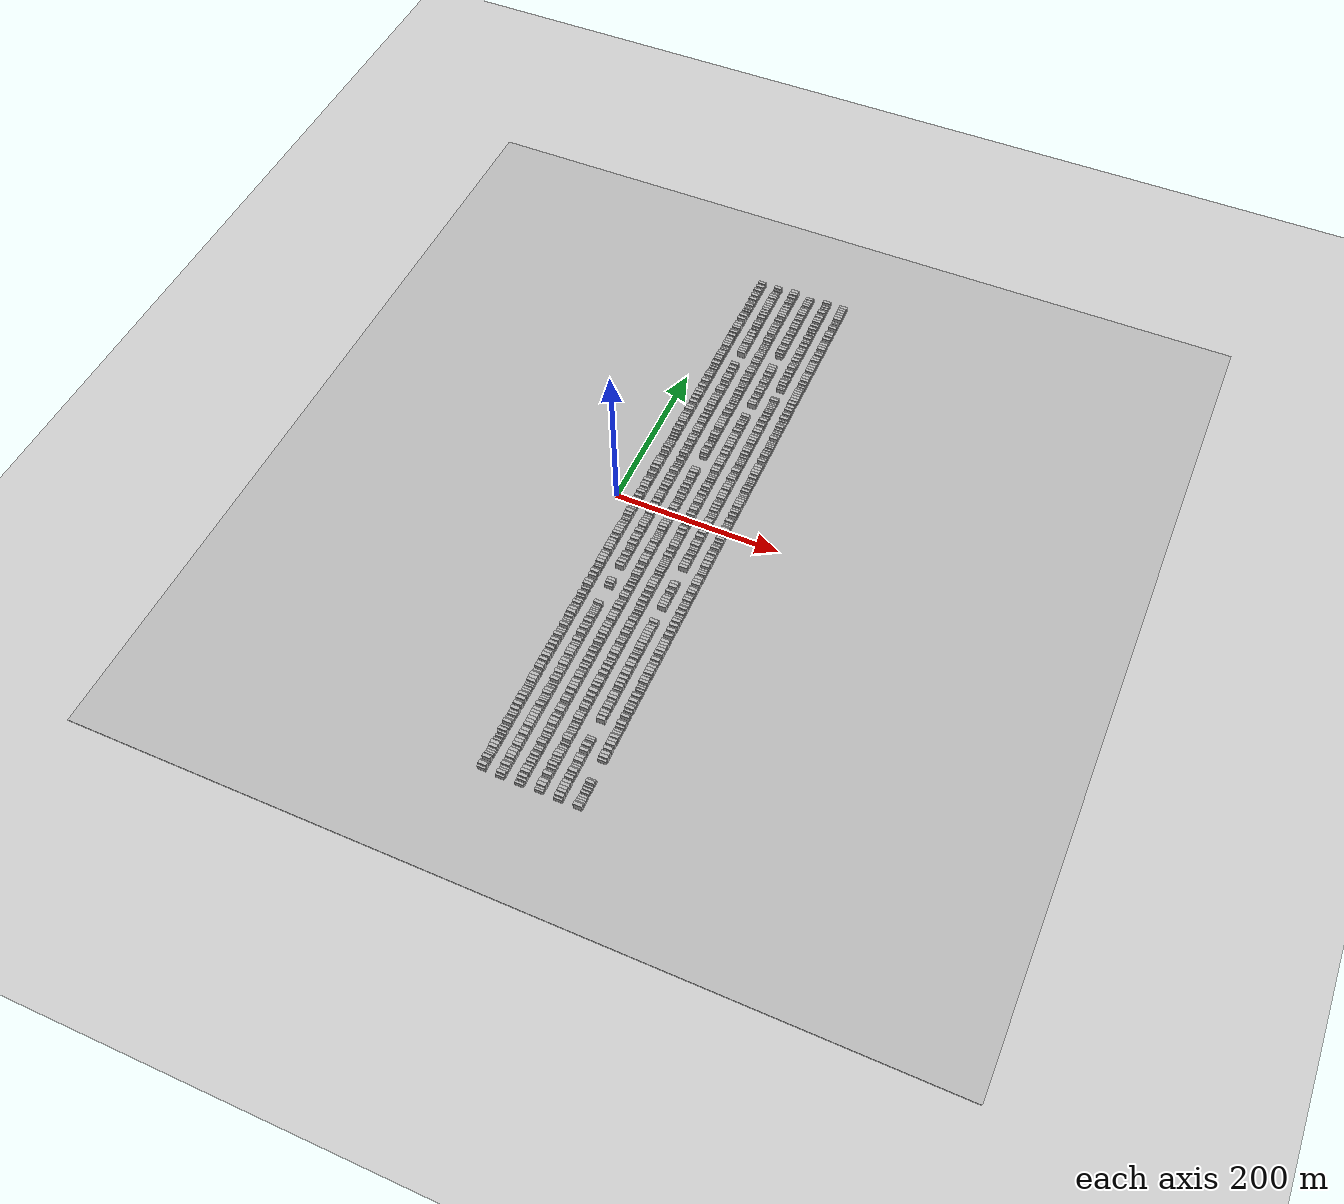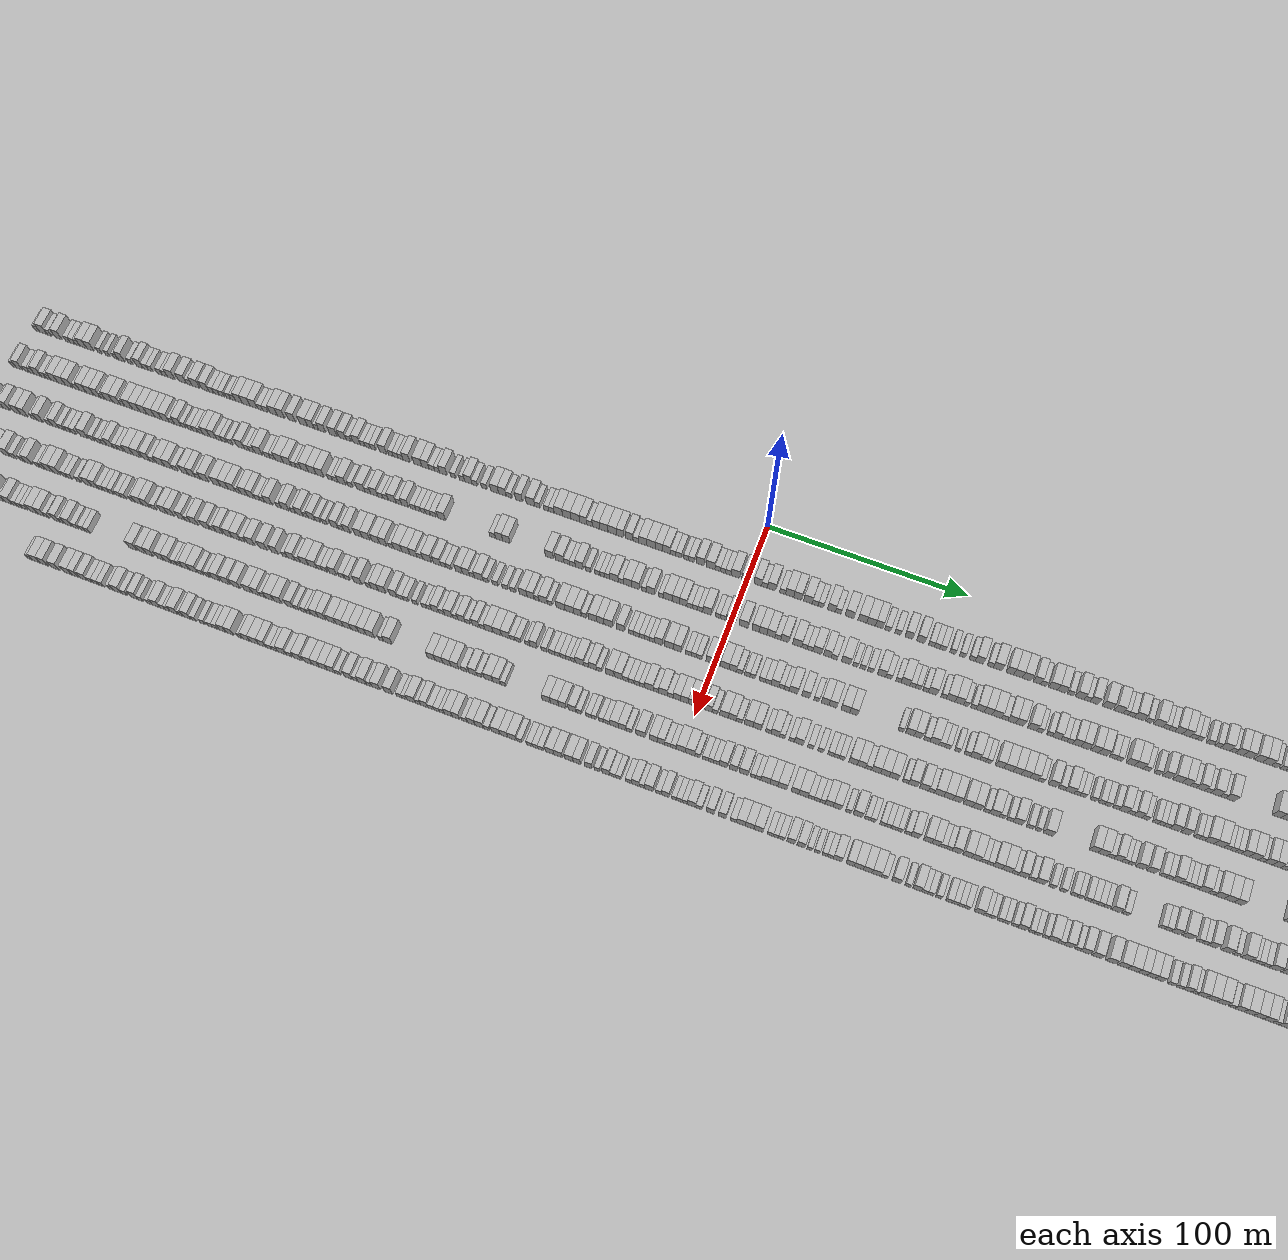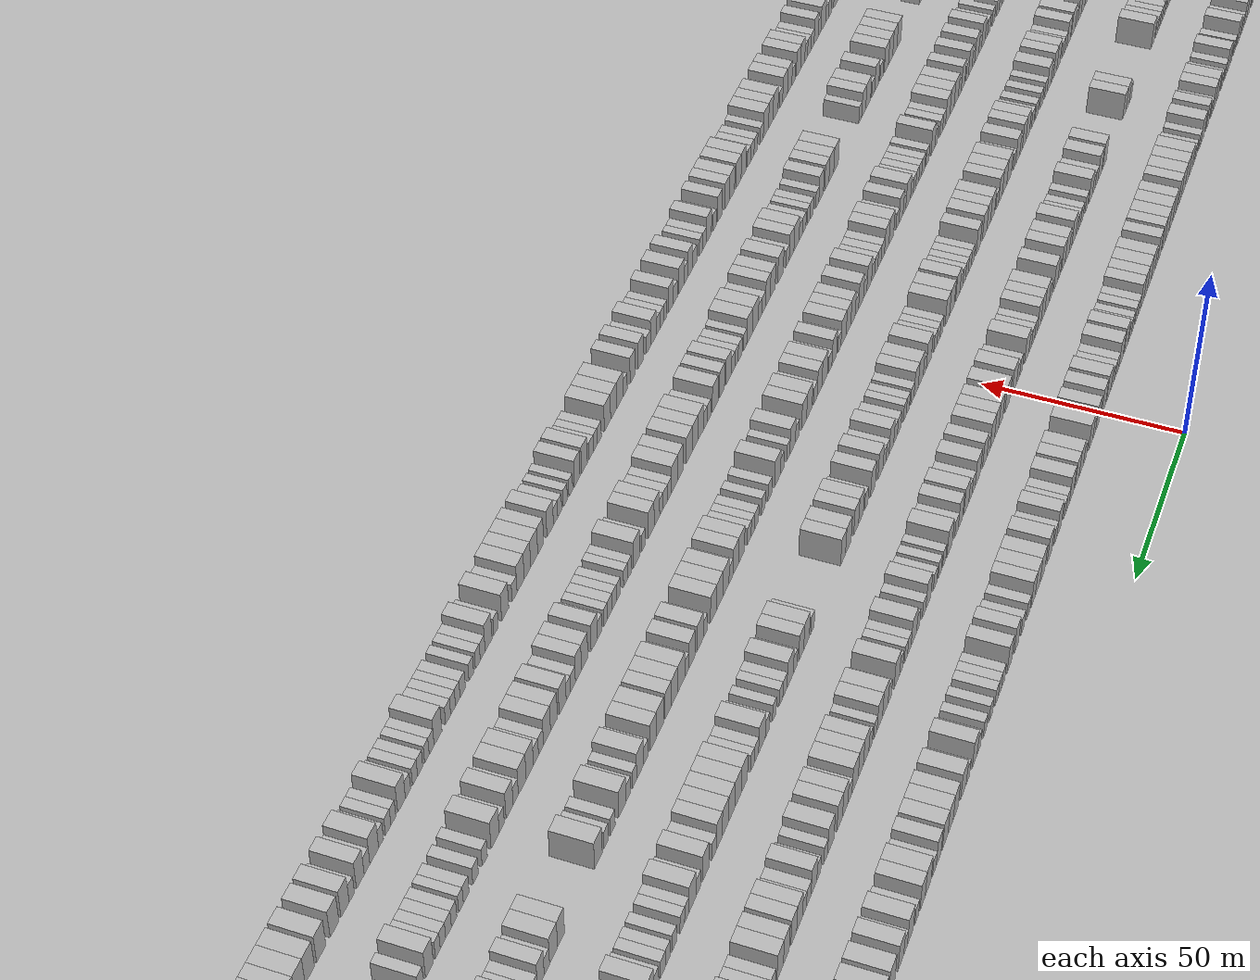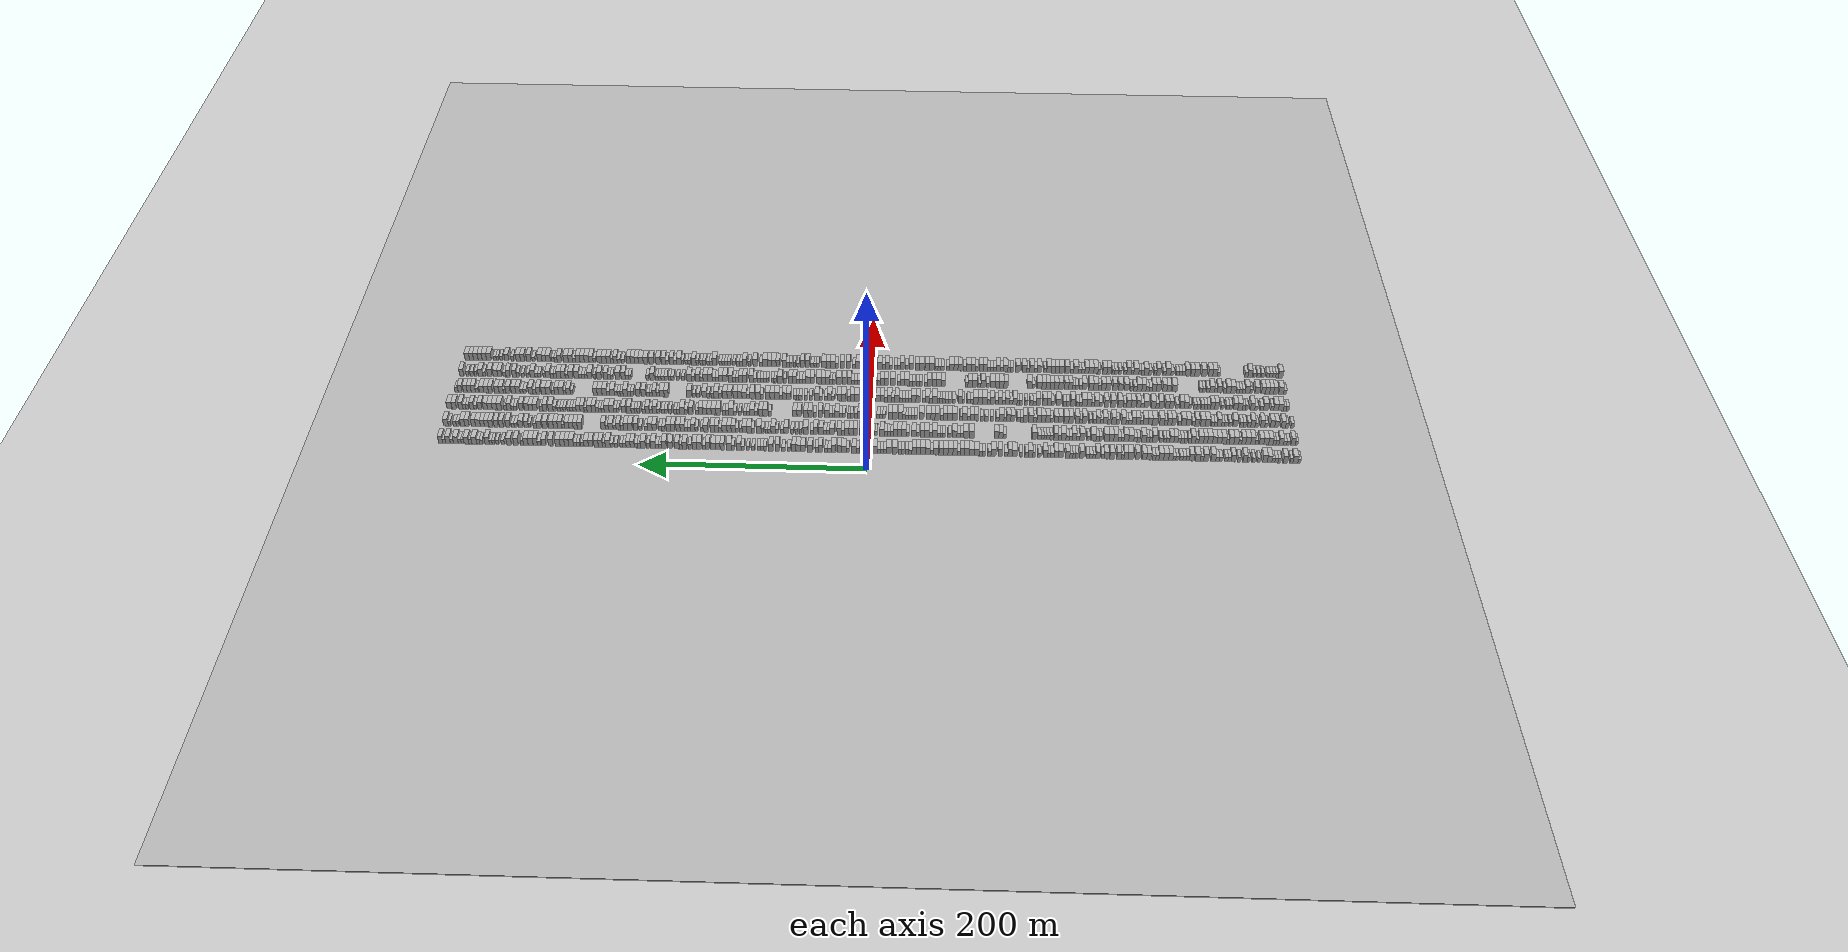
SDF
<?xml version="1.0" encoding="utf-8"?>

<sdf version="1.6">

   <world name="default">

      <gui fullscreen="0">

         <camera name="user_camera">

            <pose>-15 0 4.57585 0 0 0</pose>

            <view_controller>orbit</view_controller>

         </camera>

      </gui>

      <scene>

         <sky>

           <clouds>

             <speed>12</speed>

           </clouds>

         </sky>

         <ambient>0.4 0.4 0.4 1</ambient>

         <background>0.7 0.7 0.7 1</background>

         <shadows>1</shadows>

      </scene>

      <gravity>0 0 -9.8066</gravity>

      <magnetic_field>6e-06 2.3e-05 -4.2e-05</magnetic_field>

      <physics default="0" name="default_physics" type="ode">

         <ode>

            <solver>

               <type>quick</type>

               <iters>10</iters>

               <sor>1.0</sor>

               <use_dynamic_moi_rescaling>0</use_dynamic_moi_rescaling>

            </solver>

            <constraints>

               <cfm>0</cfm>

               <erp>0.2</erp>

               <contact_max_correcting_vel>100</contact_max_correcting_vel>

               <contact_surface_layer>0.001</contact_surface_layer>

            </constraints>

         </ode>

         <max_step_size>0.004</max_step_size>

         <real_time_factor>1</real_time_factor>

         <real_time_update_rate>250</real_time_update_rate>

      </physics>

      <light name="sun" type="directional">

         <cast_shadows>1</cast_shadows>

         <pose>0 0 10 0 0 0</pose>

         <diffuse>0.8 0.8 0.8 1</diffuse>

         <specular>0.2 0.2 0.2 1</specular>

         <attenuation>

            <range>1000</range>

            <constant>0.9</constant>

            <linear>0.01</linear>

            <quadratic>0.001</quadratic>

         </attenuation>

         <direction>-0.5 0.1 -0.9</direction>

      </light>

      <include>

         <name>ground_plane_1</name>

         <uri>model://HANNAS_ground_plane</uri>

         <pose>0 0 0  0 0 0</pose>

      </include>

      <include>

         <name>ground_plane_2</name>

         <uri>model://HANNAS_ground_plane</uri>

         <pose>100 0 0  0 0 0</pose>

      </include>

      <model name="building_1">

         <static>1</static>

         <pose frame="">25.0000 -377.7746 0 0.000000 0.000000 0.000000</pose>

         <link name="link">

            <pose frame="">0 0 3.00 0 0 0</pose>

            <collision name="collision">

               <geometry>

                  <box>

                     <size>10.0000 2.4507 6.0000</size>

                  </box>

               </geometry>

               <max_contacts>10</max_contacts>

               <surface>

                  <contact>

                     <ode/>

                  </contact>

                  <bounce/>

                  <friction>

                     <torsional>

                        <ode/>

                     </torsional>

                     <ode/>

                  </friction>

               </surface>

            </collision>

            <visual name="visual">

               <cast_shadows>0</cast_shadows>

               <geometry>

                  <box>

                     <size>10.0000 2.4507 6.0000</size>

                  </box>

               </geometry>

               <material>

                  <script>

                     <uri>model://HANNAS_wall/materials/scripts</uri>

                     <uri>model://HANNAS_wall/materials/textures</uri>

                     <name>vrc/HANNAS_wall</name>

                  </script>

               </material>

            </visual>

            <self_collide>0</self_collide>

            <enable_wind>0</enable_wind>

            <kinematic>0</kinematic>

         </link>

      </model>

      <model name="building_2">

         <static>1</static>

         <pose frame="">25.0000 -374.3925 0 0.000000 0.000000 0.000000</pose>

         <link name="link">

            <pose frame="">0 0 4.50 0 0 0</pose>

            <collision name="collision">

               <geometry>

                  <box>

                     <size>10.0000 4.3136 9.0000</size>

                  </box>

               </geometry>

               <max_contacts>10</max_contacts>

               <surface>

                  <contact>

                     <ode/>

                  </contact>

                  <bounce/>

                  <friction>

                     <torsional>

                        <ode/>

                     </torsional>

                     <ode/>

                  </friction>

               </surface>

            </collision>

            <visual name="visual">

               <cast_shadows>0</cast_shadows>

               <geometry>

                  <box>

                     <size>10.0000 4.3136 9.0000</size>

                  </box>

               </geometry>

               <material>

                  <script>

                     <uri>model://HANNAS_wall/materials/scripts</uri>

                     <uri>model://HANNAS_wall/materials/textures</uri>

                     <name>vrc/HANNAS_wall</name>

                  </script>

               </material>

            </visual>

            <self_collide>0</self_collide>

            <enable_wind>0</enable_wind>

            <kinematic>0</kinematic>

         </link>

      </model>

      <model name="building_3">

         <static>1</static>

         <pose frame="">25.0000 -370.9728 0 0.000000 0.000000 0.000000</pose>

         <link name="link">

            <pose frame="">0 0 3.00 0 0 0</pose>

            <collision name="collision">

               <geometry>

                  <box>

                     <size>10.0000 2.5256 6.0000</size>

                  </box>

               </geometry>

               <max_contacts>10</max_contacts>

               <surface>

                  <contact>

                     <ode/>

                  </contact>

                  <bounce/>

                  <friction>

                     <torsional>

                        <ode/>

                     </torsional>

                     <ode/>

                  </friction>

               </surface>

            </collision>

            <visual name="visual">

               <cast_shadows>0</cast_shadows>

               <geometry>

                  <box>

                     <size>10.0000 2.5256 6.0000</size>

                  </box>

               </geometry>

               <material>

                  <script>

                     <uri>model://HANNAS_wall/materials/scripts</uri>

                     <uri>model://HANNAS_wall/materials/textures</uri>

                     <name>vrc/HANNAS_wall</name>

                  </script>

               </material>

            </visual>

            <self_collide>0</self_collide>

            <enable_wind>0</enable_wind>

            <kinematic>0</kinematic>

         </link>

      </model>

      <model name="building_4">

         <static>1</static>

         <pose frame="">25.0000 -365.7302 0 0.000000 0.000000 0.000000</pose>

         <link name="link">

            <pose frame="">0 0 4.50 0 0 0</pose>

            <collision name="collision">

               <geometry>

                  <box>

                     <size>10.0000 3.9595 9.0000</size>

                  </box>

               </geometry>

               <max_contacts>10</max_contacts>

               <surface>

                  <contact>

                     <ode/>

                  </contact>

                  <bounce/>

                  <friction>

                     <torsional>

                        <ode/>

                     </torsional>

                     <ode/>

                  </friction>

               </surface>

            </collision>

            <visual name="visual">

               <cast_shadows>0</cast_shadows>

               <geometry>

                  <box>

                     <size>10.0000 3.9595 9.0000</size>

                  </box>

               </geometry>

               <material>

                  <script>

                     <uri>model://HANNAS_wall/materials/scripts</uri>

                     <uri>model://HANNAS_wall/materials/textures</uri>

                     <name>vrc/HANNAS_wall</name>

                  </script>

               </material>

            </visual>

            <self_collide>0</self_collide>

            <enable_wind>0</enable_wind>

            <kinematic>0</kinematic>

         </link>

      </model>

      <model name="building_5">

         <static>1</static>

         <pose frame="">25.0000 -360.5192 0 0.000000 0.000000 0.000000</pose>

         <link name="link">

            <pose frame="">0 0 3.00 0 0 0</pose>

            <collision name="collision">

               <geometry>

                  <box>

                     <size>10.0000 2.4626 6.0000</size>

                  </box>

               </geometry>

               <max_contacts>10</max_contacts>

               <surface>

                  <contact>

                     <ode/>

                  </contact>

                  <bounce/>

                  <friction>

                     <torsional>

                        <ode/>

                     </torsional>

                     <ode/>

                  </friction>

               </surface>

            </collision>

            <visual name="visual">

               <cast_shadows>0</cast_shadows>

               <geometry>

                  <box>

                     <size>10.0000 2.4626 6.0000</size>

                  </box>

               </geometry>

               <material>

                  <script>

                     <uri>model://HANNAS_wall/materials/scripts</uri>

                     <uri>model://HANNAS_wall/materials/textures</uri>

                     <name>vrc/HANNAS_wall</name>

                  </script>

               </material>

            </visual>

            <self_collide>0</self_collide>

            <enable_wind>0</enable_wind>

            <kinematic>0</kinematic>

         </link>

      </model>

      <model name="building_6">

         <static>1</static>

         <pose frame="">25.0000 -357.8363 0 0.000000 0.000000 0.000000</pose>

         <link name="link">

            <pose frame="">0 0 3.00 0 0 0</pose>

            <collision name="collision">

               <geometry>

                  <box>

                     <size>10.0000 2.9032 6.0000</size>

                  </box>

               </geometry>

               <max_contacts>10</max_contacts>

               <surface>

                  <contact>

                     <ode/>

                  </contact>

                  <bounce/>

                  <friction>

                     <torsional>

                        <ode/>

                     </torsional>

                     <ode/>

                  </friction>

               </surface>

            </collision>

            <visual name="visual">

               <cast_shadows>0</cast_shadows>

               <geometry>

                  <box>

                     <size>10.0000 2.9032 6.0000</size>

                  </box>

               </geometry>

               <material>

                  <script>

                     <uri>model://HANNAS_wall/materials/scripts</uri>

                     <uri>model://HANNAS_wall/materials/textures</uri>

                     <name>vrc/HANNAS_wall</name>

                  </script>

               </material>

            </visual>

            <self_collide>0</self_collide>

            <enable_wind>0</enable_wind>

            <kinematic>0</kinematic>

         </link>

      </model>

      <model name="building_7">

         <static>1</static>

         <pose frame="">25.0000 -355.1290 0 0.000000 0.000000 0.000000</pose>

         <link name="link">

            <pose frame="">0 0 3.00 0 0 0</pose>

            <collision name="collision">

               <geometry>

                  <box>

                     <size>10.0000 2.5115 6.0000</size>

                  </box>

               </geometry>

               <max_contacts>10</max_contacts>

               <surface>

                  <contact>

                     <ode/>

                  </contact>

                  <bounce/>

                  <friction>

                     <torsional>

                        <ode/>

                     </torsional>

                     <ode/>

                  </friction>

               </surface>

            </collision>

            <visual name="visual">

               <cast_shadows>0</cast_shadows>

               <geometry>

                  <box>

                     <size>10.0000 2.5115 6.0000</size>

                  </box>

               </geometry>

               <material>

                  <script>

                     <uri>model://HANNAS_wall/materials/scripts</uri>

                     <uri>model://HANNAS_wall/materials/textures</uri>

                     <name>vrc/HANNAS_wall</name>

                  </script>

               </material>

            </visual>

            <self_collide>0</self_collide>

            <enable_wind>0</enable_wind>

            <kinematic>0</kinematic>

         </link>

      </model>

      <model name="building_8">

         <static>1</static>

         <pose frame="">25.0000 -351.8616 0 0.000000 0.000000 0.000000</pose>

         <link name="link">

            <pose frame="">0 0 4.50 0 0 0</pose>

            <collision name="collision">

               <geometry>

                  <box>

                     <size>10.0000 4.0233 9.0000</size>

                  </box>

               </geometry>

               <max_contacts>10</max_contacts>

               <surface>

                  <contact>

                     <ode/>

                  </contact>

                  <bounce/>

                  <friction>

                     <torsional>

                        <ode/>

                     </torsional>

                     <ode/>

                  </friction>

               </surface>

            </collision>

            <visual name="visual">

               <cast_shadows>0</cast_shadows>

               <geometry>

                  <box>

                     <size>10.0000 4.0233 9.0000</size>

                  </box>

               </geometry>

               <material>

                  <script>

                     <uri>model://HANNAS_wall/materials/scripts</uri>

                     <uri>model://HANNAS_wall/materials/textures</uri>

                     <name>vrc/HANNAS_wall</name>

                  </script>

               </material>

            </visual>

            <self_collide>0</self_collide>

            <enable_wind>0</enable_wind>

            <kinematic>0</kinematic>

         </link>

      </model>

      <model name="building_9">

         <static>1</static>

         <pose frame="">25.0000 -347.8291 0 0.000000 0.000000 0.000000</pose>

         <link name="link">

            <pose frame="">0 0 4.50 0 0 0</pose>

            <collision name="collision">

               <geometry>

                  <box>

                     <size>10.0000 4.0415 9.0000</size>

                  </box>

               </geometry>

               <max_contacts>10</max_contacts>

               <surface>

                  <contact>

                     <ode/>

                  </contact>

                  <bounce/>

                  <friction>

                     <torsional>

                        <ode/>

                     </torsional>

                     <ode/>

                  </friction>

               </surface>

            </collision>

            <visual name="visual">

               <cast_shadows>0</cast_shadows>

               <geometry>

                  <box>

                     <size>10.0000 4.0415 9.0000</size>

                  </box>

               </geometry>

               <material>

                  <script>

                     <uri>model://HANNAS_wall/materials/scripts</uri>

                     <uri>model://HANNAS_wall/materials/textures</uri>

                     <name>vrc/HANNAS_wall</name>

                  </script>

               </material>

            </visual>

            <self_collide>0</self_collide>

            <enable_wind>0</enable_wind>

            <kinematic>0</kinematic>

         </link>

      </model>

      <model name="building_10">

         <static>1</static>

         <pose frame="">25.0000 -342.5372 0 0.000000 0.000000 0.000000</pose>

         <link name="link">

            <pose frame="">0 0 3.00 0 0 0</pose>

            <collision name="collision">

               <geometry>

                  <box>

                     <size>10.0000 2.5423 6.0000</size>

                  </box>

               </geometry>

               <max_contacts>10</max_contacts>

               <surface>

                  <contact>

                     <ode/>

                  </contact>

                  <bounce/>

                  <friction>

                     <torsional>

                        <ode/>

                     </torsional>

                     <ode/>

                  </friction>

               </surface>

            </collision>

            <visual name="visual">

               <cast_shadows>0</cast_shadows>

               <geometry>

                  <box>

                     <size>10.0000 2.5423 6.0000</size>

                  </box>

               </geometry>

               <material>

                  <script>

                     <uri>model://HANNAS_wall/materials/scripts</uri>

                     <uri>model://HANNAS_wall/materials/textures</uri>

                     <name>vrc/HANNAS_wall</name>

                  </script>

               </material>

            </visual>

            <self_collide>0</self_collide>

            <enable_wind>0</enable_wind>

            <kinematic>0</kinematic>

         </link>

      </model>

      <model name="building_11">

         <static>1</static>

         <pose frame="">25.0000 -338.0257 0 0.000000 0.000000 0.000000</pose>

         <link name="link">

            <pose frame="">0 0 3.00 0 0 0</pose>

            <collision name="collision">

               <geometry>

                  <box>

                     <size>10.0000 2.4809 6.0000</size>

                  </box>

               </geometry>

               <max_contacts>10</max_contacts>

               <surface>

                  <contact>

                     <ode/>

                  </contact>

                  <bounce/>

                  <friction>

                     <torsional>

                        <ode/>

                     </torsional>

                     <ode/>

                  </friction>

               </surface>

            </collision>

            <visual name="visual">

               <cast_shadows>0</cast_shadows>

               <geometry>

                  <box>

                     <size>10.0000 2.4809 6.0000</size>

                  </box>

               </geometry>

               <material>

                  <script>

                     <uri>model://HANNAS_wall/materials/scripts</uri>

                     <uri>model://HANNAS_wall/materials/textures</uri>

                     <name>vrc/HANNAS_wall</name>

                  </script>

               </material>

            </visual>

            <self_collide>0</self_collide>

            <enable_wind>0</enable_wind>

            <kinematic>0</kinematic>

         </link>

      </model>

      <model name="building_12">

         <static>1</static>

         <pose frame="">25.0000 -333.5848 0 0.000000 0.000000 0.000000</pose>

         <link name="link">

            <pose frame="">0 0 3.00 0 0 0</pose>

            <collision name="collision">

               <geometry>

                  <box>

                     <size>10.0000 2.4009 6.0000</size>

                  </box>

               </geometry>

               <max_contacts>10</max_contacts>

               <surface>

                  <contact>

                     <ode/>

                  </contact>

                  <bounce/>

                  <friction>

                     <torsional>

                        <ode/>

                     </torsional>

                     <ode/>

                  </friction>

               </surface>

            </collision>

            <visual name="visual">

               <cast_shadows>0</cast_shadows>

               <geometry>

                  <box>

                     <size>10.0000 2.4009 6.0000</size>

                  </box>

               </geometry>

               <material>

                  <script>

                     <uri>model://HANNAS_wall/materials/scripts</uri>

                     <uri>model://HANNAS_wall/materials/textures</uri>

                     <name>vrc/HANNAS_wall</name>

                  </script>

               </material>

            </visual>

            <self_collide>0</self_collide>

            <enable_wind>0</enable_wind>

            <kinematic>0</kinematic>

         </link>

      </model>

      <model name="building_13">

         <static>1</static>

         <pose frame="">25.0000 -330.5529 0 0.000000 0.000000 0.000000</pose>

         <link name="link">

            <pose frame="">0 0 4.50 0 0 0</pose>

            <collision name="collision">

               <geometry>

                  <box>

                     <size>10.0000 3.6629 9.0000</size>

                  </box>

               </geometry>

               <max_contacts>10</max_contacts>

               <surface>

                  <contact>

                     <ode/>

                  </contact>

                  <bounce/>

                  <friction>

                     <torsional>

                        <ode/>

                     </torsional>

                     <ode/>

                  </friction>

               </surface>

            </collision>

            <visual name="visual">

               <cast_shadows>0</cast_shadows>

               <geometry>

                  <box>

                     <size>10.0000 3.6629 9.0000</size>

                  </box>

               </geometry>

               <material>

                  <script>

                     <uri>model://HANNAS_wall/materials/scripts</uri>

                     <uri>model://HANNAS_wall/materials/textures</uri>

                     <name>vrc/HANNAS_wall</name>

                  </script>

               </material>

            </visual>

            <self_collide>0</self_collide>

            <enable_wind>0</enable_wind>

            <kinematic>0</kinematic>

         </link>

      </model>

      <model name="building_14">

         <static>1</static>

         <pose frame="">25.0000 -325.4087 0 0.000000 0.000000 0.000000</pose>

         <link name="link">

            <pose frame="">0 0 3.00 0 0 0</pose>

            <collision name="collision">

               <geometry>

                  <box>

                     <size>10.0000 2.6254 6.0000</size>

                  </box>

               </geometry>

               <max_contacts>10</max_contacts>

               <surface>

                  <contact>

                     <ode/>

                  </contact>

                  <bounce/>

                  <friction>

                     <torsional>

                        <ode/>

                     </torsional>

                     <ode/>

                  </friction>

               </surface>

            </collision>

            <visual name="visual">

               <cast_shadows>0</cast_shadows>

               <geometry>

                  <box>

                     <size>10.0000 2.6254 6.0000</size>

                  </box>

               </geometry>

               <material>

                  <script>

                     <uri>model://HANNAS_wall/materials/scripts</uri>

                     <uri>model://HANNAS_wall/materials/textures</uri>

                     <name>vrc/HANNAS_wall</name>

                  </script>

               </material>

            </visual>

            <self_collide>0</self_collide>

            <enable_wind>0</enable_wind>

            <kinematic>0</kinematic>

         </link>

      </model>

      <model name="building_15">

         <static>1</static>

         <pose frame="">25.0000 -320.2736 0 0.000000 0.000000 0.000000</pose>

         <link name="link">

            <pose frame="">0 0 4.50 0 0 0</pose>

            <collision name="collision">

               <geometry>

                  <box>

                     <size>10.0000 3.6449 9.0000</size>

                  </box>

               </geometry>

               <max_contacts>10</max_contacts>

               <surface>

                  <contact>

                     <ode/>

                  </contact>

                  <bounce/>

                  <friction>

                     <torsional>

                        <ode/>

                     </torsional>

                     <ode/>

                  </friction>

               </surface>

            </collision>

            <visual name="visual">

               <cast_shadows>0</cast_shadows>

               <geometry>

                  <box>

                     <size>10.0000 3.6449 9.0000</size>

                  </box>

               </geometry>

               <material>

                  <script>

                     <uri>model://HANNAS_wall/materials/scripts</uri>

                     <uri>model://HANNAS_wall/materials/textures</uri>

                     <name>vrc/HANNAS_wall</name>

                  </script>

               </material>

            </visual>

            <self_collide>0</self_collide>

            <enable_wind>0</enable_wind>

            <kinematic>0</kinematic>

         </link>

      </model>

      <model name="building_16">

         <static>1</static>

         <pose frame="">25.0000 -316.9975 0 0.000000 0.000000 0.000000</pose>

         <link name="link">

            <pose frame="">0 0 3.00 0 0 0</pose>

            <collision name="collision">

               <geometry>

                  <box>

                     <size>10.0000 2.9072 6.0000</size>

                  </box>

               </geometry>

               <max_contacts>10</max_contacts>

               <surface>

                  <contact>

                     <ode/>

                  </contact>

                  <bounce/>

                  <friction>

                     <torsional>

                        <ode/>

                     </torsional>

                     <ode/>

                  </friction>

               </surface>

            </collision>

            <visual name="visual">

               <cast_shadows>0</cast_shadows>

               <geometry>

                  <box>

                     <size>10.0000 2.9072 6.0000</size>

                  </box>

               </geometry>

               <material>

                  <script>

                     <uri>model://HANNAS_wall/materials/scripts</uri>

                     <uri>model://HANNAS_wall/materials/textures</uri>

                     <name>vrc/HANNAS_wall</name>

                  </script>

               </material>

            </visual>

            <self_collide>0</self_collide>

            <enable_wind>0</enable_wind>

            <kinematic>0</kinematic>

         </link>

      </model>

      <model name="building_17">

         <static>1</static>

         <pose frame="">25.0000 -314.1845 0 0.000000 0.000000 0.000000</pose>

         <link name="link">

            <pose frame="">0 0 3.00 0 0 0</pose>

            <collision name="collision">

               <geometry>

                  <box>

                     <size>10.0000 2.7188 6.0000</size>

                  </box>

               </geometry>

               <max_contacts>10</max_contacts>

               <surface>

                  <contact>

                     <ode/>

                  </contact>

                  <bounce/>

                  <friction>

                     <torsional>

                        <ode/>

                     </torsional>

                     <ode/>

                  </friction>

               </surface>

            </collision>

            <visual name="visual">

               <cast_shadows>0</cast_shadows>

               <geometry>

                  <box>

                     <size>10.0000 2.7188 6.0000</size>

                  </box>

               </geometry>

               <material>

                  <script>

                     <uri>model://HANNAS_wall/materials/scripts</uri>

                     <uri>model://HANNAS_wall/materials/textures</uri>

                     <name>vrc/HANNAS_wall</name>

                  </script>

               </material>

            </visual>

            <self_collide>0</self_collide>

            <enable_wind>0</enable_wind>

            <kinematic>0</kinematic>

         </link>

      </model>

      <model name="building_18">

         <static>1</static>

         <pose frame="">25.0000 -309.3861 0 0.000000 0.000000 0.000000</pose>

         <link name="link">

            <pose frame="">0 0 3.00 0 0 0</pose>

            <collision name="collision">

               <geometry>

                  <box>

                     <size>10.0000 2.8779 6.0000</size>

                  </box>

               </geometry>

               <max_contacts>10</max_contacts>

               <surface>

                  <contact>

                     <ode/>

                  </contact>

                  <bounce/>

                  <friction>

                     <torsional>

                        <ode/>

                     </torsional>

                     <ode/>

                  </friction>

               </surface>

            </collision>

            <visual name="visual">

               <cast_shadows>0</cast_shadows>

               <geometry>

                  <box>

                     <size>10.0000 2.8779 6.0000</size>

                  </box>

               </geometry>

               <material>

                  <script>

                     <uri>model://HANNAS_wall/materials/scripts</uri>

                     <uri>model://HANNAS_wall/materials/textures</uri>

                     <name>vrc/HANNAS_wall</name>

                  </script>

               </material>

            </visual>

            <self_collide>0</self_collide>

            <enable_wind>0</enable_wind>

            <kinematic>0</kinematic>

         </link>

      </model>

      <model name="building_19">

         <static>1</static>

         <pose frame="">25.0000 -306.4580 0 0.000000 0.000000 0.000000</pose>

         <link name="link">

            <pose frame="">0 0 3.00 0 0 0</pose>

            <collision name="collision">

               <geometry>

                  <box>

                     <size>10.0000 2.9784 6.0000</size>

                  </box>

               </geometry>

               <max_contacts>10</max_contacts>

               <surface>

                  <contact>

                     <ode/>

                  </contact>

                  <bounce/>

                  <friction>

                     <torsional>

                        <ode/>

                     </torsional>

                     <ode/>

                  </friction>

               </surface>

            </collision>

            <visual name="visual">

               <cast_shadows>0</cast_shadows>

               <geometry>

                  <box>

                     <size>10.0000 2.9784 6.0000</size>

                  </box>

               </geometry>

               <material>

                  <script>

                     <uri>model://HANNAS_wall/materials/scripts</uri>

                     <uri>model://HANNAS_wall/materials/textures</uri>

                     <name>vrc/HANNAS_wall</name>

                  </script>

               </material>

            </visual>

            <self_collide>0</self_collide>

            <enable_wind>0</enable_wind>

            <kinematic>0</kinematic>

         </link>

      </model>

      <model name="building_20">

         <static>1</static>

         <pose frame="">25.0000 -302.8549 0 0.000000 0.000000 0.000000</pose>

         <link name="link">

            <pose frame="">0 0 4.50 0 0 0</pose>

            <collision name="collision">

               <geometry>

                  <box>

                     <size>10.0000 4.2278 9.0000</size>

                  </box>

               </geometry>

               <max_contacts>10</max_contacts>

               <surface>

                  <contact>

                     <ode/>

                  </contact>

                  <bounce/>

                  <friction>

                     <torsional>

                        <ode/>

                     </torsional>

                     <ode/>

                  </friction>

               </surface>

            </collision>

            <visual name="visual">

               <cast_shadows>0</cast_shadows>

               <geometry>

                  <box>

                     <size>10.0000 4.2278 9.0000</size>

                  </box>

               </geometry>

               <material>

                  <script>

                     <uri>model://HANNAS_wall/materials/scripts</uri>

                     <uri>model://HANNAS_wall/materials/textures</uri>

                     <name>vrc/HANNAS_wall</name>

                  </script>

               </material>

            </visual>

            <self_collide>0</self_collide>

            <enable_wind>0</enable_wind>

            <kinematic>0</kinematic>

         </link>

      </model>

      <model name="building_21">

         <static>1</static>

         <pose frame="">25.0000 -296.5564 0 0.000000 0.000000 0.000000</pose>

         <link name="link">

            <pose frame="">0 0 4.50 0 0 0</pose>

            <collision name="collision">

               <geometry>

                  <box>

                     <size>10.0000 4.3691 9.0000</size>

                  </box>

               </geometry>

               <max_contacts>10</max_contacts>

               <surface>

                  <contact>

                     <ode/>

                  </contact>

                  <bounce/>

                  <friction>

                     <torsional>

                        <ode/>

                     </torsional>

                     <ode/>

                  </friction>

               </surface>

            </collision>

            <visual name="visual">

               <cast_shadows>0</cast_shadows>

               <geometry>

                  <box>

                     <size>10.0000 4.3691 9.0000</size>

                  </box>

               </geometry>

               <material>

                  <script>

                     <uri>model://HANNAS_wall/materials/scripts</uri>

                     <uri>model://HANNAS_wall/materials/textures</uri>

                     <name>vrc/HANNAS_wall</name>

                  </script>

               </material>

            </visual>

            <self_collide>0</self_collide>

            <enable_wind>0</enable_wind>

            <kinematic>0</kinematic>

         </link>

      </model>

      <model name="building_22">

         <static>1</static>

         <pose frame="">25.0000 -292.9049 0 0.000000 0.000000 0.000000</pose>

         <link name="link">

            <pose frame="">0 0 3.00 0 0 0</pose>

            <collision name="collision">

               <geometry>

                  <box>

                     <size>10.0000 2.9339 6.0000</size>

                  </box>

               </geometry>

               <max_contacts>10</max_contacts>

               <surface>

                  <contact>

                     <ode/>

                  </contact>

                  <bounce/>

                  <friction>

                     <torsional>

                        <ode/>

                     </torsional>

                     <ode/>

                  </friction>

               </surface>

            </collision>

            <visual name="visual">

               <cast_shadows>0</cast_shadows>

               <geometry>

                  <box>

                     <size>10.0000 2.9339 6.0000</size>

                  </box>

               </geometry>

               <material>

                  <script>

                     <uri>model://HANNAS_wall/materials/scripts</uri>

                     <uri>model://HANNAS_wall/materials/textures</uri>

                     <name>vrc/HANNAS_wall</name>

                  </script>

               </material>

            </visual>

            <self_collide>0</self_collide>

            <enable_wind>0</enable_wind>

            <kinematic>0</kinematic>

         </link>

      </model>

      <model name="building_23">

         <static>1</static>

         <pose frame="">25.0000 -289.2133 0 0.000000 0.000000 0.000000</pose>

         <link name="link">

            <pose frame="">0 0 4.50 0 0 0</pose>

            <collision name="collision">

               <geometry>

                  <box>

                     <size>10.0000 4.4492 9.0000</size>

                  </box>

               </geometry>

               <max_contacts>10</max_contacts>

               <surface>

                  <contact>

                     <ode/>

                  </contact>

                  <bounce/>

                  <friction>

                     <torsional>

                        <ode/>

                     </torsional>

                     <ode/>

                  </friction>

               </surface>

            </collision>

            <visual name="visual">

               <cast_shadows>0</cast_shadows>

               <geometry>

                  <box>

                     <size>10.0000 4.4492 9.0000</size>

                  </box>

               </geometry>

               <material>

                  <script>

                     <uri>model://HANNAS_wall/materials/scripts</uri>

                     <uri>model://HANNAS_wall/materials/textures</uri>

                     <name>vrc/HANNAS_wall</name>

                  </script>

               </material>

            </visual>

            <self_collide>0</self_collide>

            <enable_wind>0</enable_wind>

            <kinematic>0</kinematic>

         </link>

      </model>

      <model name="building_24">

         <static>1</static>

         <pose frame="">25.0000 -284.0111 0 0.000000 0.000000 0.000000</pose>

         <link name="link">

            <pose frame="">0 0 4.50 0 0 0</pose>

            <collision name="collision">

               <geometry>

                  <box>

                     <size>10.0000 3.9553 9.0000</size>

                  </box>

               </geometry>

               <max_contacts>10</max_contacts>

               <surface>

                  <contact>

                     <ode/>

                  </contact>

                  <bounce/>

                  <friction>

                     <torsional>

                        <ode/>

                     </torsional>

                     <ode/>

                  </friction>

               </surface>

            </collision>

            <visual name="visual">

               <cast_shadows>0</cast_shadows>

               <geometry>

                  <box>

                     <size>10.0000 3.9553 9.0000</size>

                  </box>

               </geometry>

               <material>

                  <script>

                     <uri>model://HANNAS_wall/materials/scripts</uri>

                     <uri>model://HANNAS_wall/materials/textures</uri>

                     <name>vrc/HANNAS_wall</name>

                  </script>

               </material>

            </visual>

            <self_collide>0</self_collide>

            <enable_wind>0</enable_wind>

            <kinematic>0</kinematic>

         </link>

      </model>

      <model name="building_25">

         <static>1</static>

         <pose frame="">25.0000 -280.6774 0 0.000000 0.000000 0.000000</pose>

         <link name="link">

            <pose frame="">0 0 3.00 0 0 0</pose>

            <collision name="collision">

               <geometry>

                  <box>

                     <size>10.0000 2.7122 6.0000</size>

                  </box>

               </geometry>

               <max_contacts>10</max_contacts>

               <surface>

                  <contact>

                     <ode/>

                  </contact>

                  <bounce/>

                  <friction>

                     <torsional>

                        <ode/>

                     </torsional>

                     <ode/>

                  </friction>

               </surface>

            </collision>

            <visual name="visual">

               <cast_shadows>0</cast_shadows>

               <geometry>

                  <box>

                     <size>10.0000 2.7122 6.0000</size>

                  </box>

               </geometry>

               <material>

                  <script>

                     <uri>model://HANNAS_wall/materials/scripts</uri>

                     <uri>model://HANNAS_wall/materials/textures</uri>

                     <name>vrc/HANNAS_wall</name>

                  </script>

               </material>

            </visual>

            <self_collide>0</self_collide>

            <enable_wind>0</enable_wind>

            <kinematic>0</kinematic>

         </link>

      </model>

      <model name="building_26">

         <static>1</static>

         <pose frame="">25.0000 -277.8356 0 0.000000 0.000000 0.000000</pose>

         <link name="link">

            <pose frame="">0 0 3.00 0 0 0</pose>

            <collision name="collision">

               <geometry>

                  <box>

                     <size>10.0000 2.9714 6.0000</size>

                  </box>

               </geometry>

               <max_contacts>10</max_contacts>

               <surface>

                  <contact>

                     <ode/>

                  </contact>

                  <bounce/>

                  <friction>

                     <torsional>

                        <ode/>

                     </torsional>

                     <ode/>

                  </friction>

               </surface>

            </collision>

            <visual name="visual">

               <cast_shadows>0</cast_shadows>

               <geometry>

                  <box>

                     <size>10.0000 2.9714 6.0000</size>

                  </box>

               </geometry>

               <material>

                  <script>

                     <uri>model://HANNAS_wall/materials/scripts</uri>

                     <uri>model://HANNAS_wall/materials/textures</uri>

                     <name>vrc/HANNAS_wall</name>

                  </script>

               </material>

            </visual>

            <self_collide>0</self_collide>

            <enable_wind>0</enable_wind>

            <kinematic>0</kinematic>

         </link>

      </model>

      <model name="building_27">

         <static>1</static>

         <pose frame="">25.0000 -274.9636 0 0.000000 0.000000 0.000000</pose>

         <link name="link">

            <pose frame="">0 0 3.00 0 0 0</pose>

            <collision name="collision">

               <geometry>

                  <box>

                     <size>10.0000 2.7726 6.0000</size>

                  </box>

               </geometry>

               <max_contacts>10</max_contacts>

               <surface>

                  <contact>

                     <ode/>

                  </contact>

                  <bounce/>

                  <friction>

                     <torsional>

                        <ode/>

                     </torsional>

                     <ode/>

                  </friction>

               </surface>

            </collision>

            <visual name="visual">

               <cast_shadows>0</cast_shadows>

               <geometry>

                  <box>

                     <size>10.0000 2.7726 6.0000</size>

                  </box>

               </geometry>

               <material>

                  <script>

                     <uri>model://HANNAS_wall/materials/scripts</uri>

                     <uri>model://HANNAS_wall/materials/textures</uri>

                     <name>vrc/HANNAS_wall</name>

                  </script>

               </material>

            </visual>

            <self_collide>0</self_collide>

            <enable_wind>0</enable_wind>

            <kinematic>0</kinematic>

         </link>

      </model>

      <model name="building_28">

         <static>1</static>

         <pose frame="">25.0000 -271.3262 0 0.000000 0.000000 0.000000</pose>

         <link name="link">

            <pose frame="">0 0 3.00 0 0 0</pose>

            <collision name="collision">

               <geometry>

                  <box>

                     <size>10.0000 2.5022 6.0000</size>

                  </box>

               </geometry>

               <max_contacts>10</max_contacts>

               <surface>

                  <contact>

                     <ode/>

                  </contact>

                  <bounce/>

                  <friction>

                     <torsional>

                        <ode/>

                     </torsional>

                     <ode/>

                  </friction>

               </surface>

            </collision>

            <visual name="visual">

               <cast_shadows>0</cast_shadows>

               <geometry>

                  <box>

                     <size>10.0000 2.5022 6.0000</size>

                  </box>

               </geometry>

               <material>

                  <script>

                     <uri>model://HANNAS_wall/materials/scripts</uri>

                     <uri>model://HANNAS_wall/materials/textures</uri>

                     <name>vrc/HANNAS_wall</name>

                  </script>

               </material>

            </visual>

            <self_collide>0</self_collide>

            <enable_wind>0</enable_wind>

            <kinematic>0</kinematic>

         </link>

      </model>

      <model name="building_29">

         <static>1</static>

         <pose frame="">25.0000 -268.8199 0 0.000000 0.000000 0.000000</pose>

         <link name="link">

            <pose frame="">0 0 3.00 0 0 0</pose>

            <collision name="collision">

               <geometry>

                  <box>

                     <size>10.0000 2.5104 6.0000</size>

                  </box>

               </geometry>

               <max_contacts>10</max_contacts>

               <surface>

                  <contact>

                     <ode/>

                  </contact>

                  <bounce/>

                  <friction>

                     <torsional>

                        <ode/>

                     </torsional>

                     <ode/>

                  </friction>

               </surface>

            </collision>

            <visual name="visual">

               <cast_shadows>0</cast_shadows>

               <geometry>

                  <box>

                     <size>10.0000 2.5104 6.0000</size>

                  </box>

               </geometry>

               <material>

                  <script>

                     <uri>model://HANNAS_wall/materials/scripts</uri>

                     <uri>model://HANNAS_wall/materials/textures</uri>

                     <name>vrc/HANNAS_wall</name>

                  </script>

               </material>

            </visual>

            <self_collide>0</self_collide>

            <enable_wind>0</enable_wind>

            <kinematic>0</kinematic>

         </link>

      </model>

      <model name="building_30">

         <static>1</static>

         <pose frame="">25.0000 -265.7104 0 0.000000 0.000000 0.000000</pose>

         <link name="link">

            <pose frame="">0 0 4.50 0 0 0</pose>

            <collision name="collision">

               <geometry>

                  <box>

                     <size>10.0000 3.7086 9.0000</size>

                  </box>

               </geometry>

               <max_contacts>10</max_contacts>

               <surface>

                  <contact>

                     <ode/>

                  </contact>

                  <bounce/>

                  <friction>

                     <torsional>

                        <ode/>

                     </torsional>

                     <ode/>

                  </friction>

               </surface>

            </collision>

            <visual name="visual">

               <cast_shadows>0</cast_shadows>

               <geometry>

                  <box>

                     <size>10.0000 3.7086 9.0000</size>

                  </box>

               </geometry>

               <material>

                  <script>

                     <uri>model://HANNAS_wall/materials/scripts</uri>

                     <uri>model://HANNAS_wall/materials/textures</uri>

                     <name>vrc/HANNAS_wall</name>

                  </script>

               </material>

            </visual>

            <self_collide>0</self_collide>

            <enable_wind>0</enable_wind>

            <kinematic>0</kinematic>

         </link>

      </model>

      <model name="building_31">

         <static>1</static>

         <pose frame="">25.0000 -261.6462 0 0.000000 0.000000 0.000000</pose>

         <link name="link">

            <pose frame="">0 0 4.50 0 0 0</pose>

            <collision name="collision">

               <geometry>

                  <box>

                     <size>10.0000 4.4197 9.0000</size>

                  </box>

               </geometry>

               <max_contacts>10</max_contacts>

               <surface>

                  <contact>

                     <ode/>

                  </contact>

                  <bounce/>

                  <friction>

                     <torsional>

                        <ode/>

                     </torsional>

                     <ode/>

                  </friction>

               </surface>

            </collision>

            <visual name="visual">

               <cast_shadows>0</cast_shadows>

               <geometry>

                  <box>

                     <size>10.0000 4.4197 9.0000</size>

                  </box>

               </geometry>

               <material>

                  <script>

                     <uri>model://HANNAS_wall/materials/scripts</uri>

                     <uri>model://HANNAS_wall/materials/textures</uri>

                     <name>vrc/HANNAS_wall</name>

                  </script>

               </material>

            </visual>

            <self_collide>0</self_collide>

            <enable_wind>0</enable_wind>

            <kinematic>0</kinematic>

         </link>

      </model>

      <model name="building_32">

         <static>1</static>

         <pose frame="">25.0000 -257.4241 0 0.000000 0.000000 0.000000</pose>

         <link name="link">

            <pose frame="">0 0 4.50 0 0 0</pose>

            <collision name="collision">

               <geometry>

                  <box>

                     <size>10.0000 4.0246 9.0000</size>

                  </box>

               </geometry>

               <max_contacts>10</max_contacts>

               <surface>

                  <contact>

                     <ode/>

                  </contact>

                  <bounce/>

                  <friction>

                     <torsional>

                        <ode/>

                     </torsional>

                     <ode/>

                  </friction>

               </surface>

            </collision>

            <visual name="visual">

               <cast_shadows>0</cast_shadows>

               <geometry>

                  <box>

                     <size>10.0000 4.0246 9.0000</size>

                  </box>

               </geometry>

               <material>

                  <script>

                     <uri>model://HANNAS_wall/materials/scripts</uri>

                     <uri>model://HANNAS_wall/materials/textures</uri>

                     <name>vrc/HANNAS_wall</name>

                  </script>

               </material>

            </visual>

            <self_collide>0</self_collide>

            <enable_wind>0</enable_wind>

            <kinematic>0</kinematic>

         </link>

      </model>

      <model name="building_33">

         <static>1</static>

         <pose frame="">25.0000 -253.9548 0 0.000000 0.000000 0.000000</pose>

         <link name="link">

            <pose frame="">0 0 3.00 0 0 0</pose>

            <collision name="collision">

               <geometry>

                  <box>

                     <size>10.0000 2.9138 6.0000</size>

                  </box>

               </geometry>

               <max_contacts>10</max_contacts>

               <surface>

                  <contact>

                     <ode/>

                  </contact>

                  <bounce/>

                  <friction>

                     <torsional>

                        <ode/>

                     </torsional>

                     <ode/>

                  </friction>

               </surface>

            </collision>

            <visual name="visual">

               <cast_shadows>0</cast_shadows>

               <geometry>

                  <box>

                     <size>10.0000 2.9138 6.0000</size>

                  </box>

               </geometry>

               <material>

                  <script>

                     <uri>model://HANNAS_wall/materials/scripts</uri>

                     <uri>model://HANNAS_wall/materials/textures</uri>

                     <name>vrc/HANNAS_wall</name>

                  </script>

               </material>

            </visual>

            <self_collide>0</self_collide>

            <enable_wind>0</enable_wind>

            <kinematic>0</kinematic>

         </link>

      </model>

      <model name="building_34">

         <static>1</static>

         <pose frame="">25.0000 -251.0961 0 0.000000 0.000000 0.000000</pose>

         <link name="link">

            <pose frame="">0 0 3.00 0 0 0</pose>

            <collision name="collision">

               <geometry>

                  <box>

                     <size>10.0000 2.8036 6.0000</size>

                  </box>

               </geometry>

               <max_contacts>10</max_contacts>

               <surface>

                  <contact>

                     <ode/>

                  </contact>

                  <bounce/>

                  <friction>

                     <torsional>

                        <ode/>

                     </torsional>

                     <ode/>

                  </friction>

               </surface>

            </collision>

            <visual name="visual">

               <cast_shadows>0</cast_shadows>

               <geometry>

                  <box>

                     <size>10.0000 2.8036 6.0000</size>

                  </box>

               </geometry>

               <material>

                  <script>

                     <uri>model://HANNAS_wall/materials/scripts</uri>

                     <uri>model://HANNAS_wall/materials/textures</uri>

                     <name>vrc/HANNAS_wall</name>

                  </script>

               </material>

            </visual>

            <self_collide>0</self_collide>

            <enable_wind>0</enable_wind>

            <kinematic>0</kinematic>

         </link>

      </model>

      <model name="building_35">

         <static>1</static>

         <pose frame="">25.0000 -246.6942 0 0.000000 0.000000 0.000000</pose>

         <link name="link">

            <pose frame="">0 0 4.50 0 0 0</pose>

            <collision name="collision">

               <geometry>

                  <box>

                     <size>10.0000 4.0003 9.0000</size>

                  </box>

               </geometry>

               <max_contacts>10</max_contacts>

               <surface>

                  <contact>

                     <ode/>

                  </contact>

                  <bounce/>

                  <friction>

                     <torsional>

                        <ode/>

                     </torsional>

                     <ode/>

                  </friction>

               </surface>

            </collision>

            <visual name="visual">

               <cast_shadows>0</cast_shadows>

               <geometry>

                  <box>

                     <size>10.0000 4.0003 9.0000</size>

                  </box>

               </geometry>

               <material>

                  <script>

                     <uri>model://HANNAS_wall/materials/scripts</uri>

                     <uri>model://HANNAS_wall/materials/textures</uri>

                     <name>vrc/HANNAS_wall</name>

                  </script>

               </material>

            </visual>

            <self_collide>0</self_collide>

            <enable_wind>0</enable_wind>

            <kinematic>0</kinematic>

         </link>

      </model>

      <model name="building_36">

         <static>1</static>

         <pose frame="">25.0000 -242.6886 0 0.000000 0.000000 0.000000</pose>

         <link name="link">

            <pose frame="">0 0 4.50 0 0 0</pose>

            <collision name="collision">

               <geometry>

                  <box>

                     <size>10.0000 4.0109 9.0000</size>

                  </box>

               </geometry>

               <max_contacts>10</max_contacts>

               <surface>

                  <contact>

                     <ode/>

                  </contact>

                  <bounce/>

                  <friction>

                     <torsional>

                        <ode/>

                     </torsional>

                     <ode/>

                  </friction>

               </surface>

            </collision>

            <visual name="visual">

               <cast_shadows>0</cast_shadows>

               <geometry>

                  <box>

                     <size>10.0000 4.0109 9.0000</size>

                  </box>

               </geometry>

               <material>

                  <script>

                     <uri>model://HANNAS_wall/materials/scripts</uri>

                     <uri>model://HANNAS_wall/materials/textures</uri>

                     <name>vrc/HANNAS_wall</name>

                  </script>

               </material>

            </visual>

            <self_collide>0</self_collide>

            <enable_wind>0</enable_wind>

            <kinematic>0</kinematic>

         </link>

      </model>

      <model name="building_37">

         <static>1</static>

         <pose frame="">25.0000 -236.7161 0 0.000000 0.000000 0.000000</pose>

         <link name="link">

            <pose frame="">0 0 4.50 0 0 0</pose>

            <collision name="collision">

               <geometry>

                  <box>

                     <size>10.0000 3.9342 9.0000</size>

                  </box>

               </geometry>

               <max_contacts>10</max_contacts>

               <surface>

                  <contact>

                     <ode/>

                  </contact>

                  <bounce/>

                  <friction>

                     <torsional>

                        <ode/>

                     </torsional>

                     <ode/>

                  </friction>

               </surface>

            </collision>

            <visual name="visual">

               <cast_shadows>0</cast_shadows>

               <geometry>

                  <box>

                     <size>10.0000 3.9342 9.0000</size>

                  </box>

               </geometry>

               <material>

                  <script>

                     <uri>model://HANNAS_wall/materials/scripts</uri>

                     <uri>model://HANNAS_wall/materials/textures</uri>

                     <name>vrc/HANNAS_wall</name>

                  </script>

               </material>

            </visual>

            <self_collide>0</self_collide>

            <enable_wind>0</enable_wind>

            <kinematic>0</kinematic>

         </link>

      </model>

      <model name="building_38">

         <static>1</static>

         <pose frame="">25.0000 -230.5687 0 0.000000 0.000000 0.000000</pose>

         <link name="link">

            <pose frame="">0 0 4.50 0 0 0</pose>

            <collision name="collision">

               <geometry>

                  <box>

                     <size>10.0000 4.3606 9.0000</size>

                  </box>

               </geometry>

               <max_contacts>10</max_contacts>

               <surface>

                  <contact>

                     <ode/>

                  </contact>

                  <bounce/>

                  <friction>

                     <torsional>

                        <ode/>

                     </torsional>

                     <ode/>

                  </friction>

               </surface>

            </collision>

            <visual name="visual">

               <cast_shadows>0</cast_shadows>

               <geometry>

                  <box>

                     <size>10.0000 4.3606 9.0000</size>

                  </box>

               </geometry>

               <material>

                  <script>

                     <uri>model://HANNAS_wall/materials/scripts</uri>

                     <uri>model://HANNAS_wall/materials/textures</uri>

                     <name>vrc/HANNAS_wall</name>

                  </script>

               </material>

            </visual>

            <self_collide>0</self_collide>

            <enable_wind>0</enable_wind>

            <kinematic>0</kinematic>

         </link>

      </model>

      <model name="building_39">

         <static>1</static>

         <pose frame="">25.0000 -226.5575 0 0.000000 0.000000 0.000000</pose>

         <link name="link">

            <pose frame="">0 0 4.50 0 0 0</pose>

            <collision name="collision">

               <geometry>

                  <box>

                     <size>10.0000 3.6618 9.0000</size>

                  </box>

               </geometry>

               <max_contacts>10</max_contacts>

               <surface>

                  <contact>

                     <ode/>

                  </contact>

                  <bounce/>

                  <friction>

                     <torsional>

                        <ode/>

                     </torsional>

                     <ode/>

                  </friction>

               </surface>

            </collision>

            <visual name="visual">

               <cast_shadows>0</cast_shadows>

               <geometry>

                  <box>

                     <size>10.0000 3.6618 9.0000</size>

                  </box>

               </geometry>

               <material>

                  <script>

                     <uri>model://HANNAS_wall/materials/scripts</uri>

                     <uri>model://HANNAS_wall/materials/textures</uri>

                     <name>vrc/HANNAS_wall</name>

                  </script>

               </material>

            </visual>

            <self_collide>0</self_collide>

            <enable_wind>0</enable_wind>

            <kinematic>0</kinematic>

         </link>

      </model>

      <model name="building_40">

         <static>1</static>

         <pose frame="">25.0000 -223.5219 0 0.000000 0.000000 0.000000</pose>

         <link name="link">

            <pose frame="">0 0 3.00 0 0 0</pose>

            <collision name="collision">

               <geometry>

                  <box>

                     <size>10.0000 2.4094 6.0000</size>

                  </box>

               </geometry>

               <max_contacts>10</max_contacts>

               <surface>

                  <contact>

                     <ode/>

                  </contact>

                  <bounce/>

                  <friction>

                     <torsional>

                        <ode/>

                     </torsional>

                     <ode/>

                  </friction>

               </surface>

            </collision>

            <visual name="visual">

               <cast_shadows>0</cast_shadows>

               <geometry>

                  <box>

                     <size>10.0000 2.4094 6.0000</size>

                  </box>

               </geometry>

               <material>

                  <script>

                     <uri>model://HANNAS_wall/materials/scripts</uri>

                     <uri>model://HANNAS_wall/materials/textures</uri>

                     <name>vrc/HANNAS_wall</name>

                  </script>

               </material>

            </visual>

            <self_collide>0</self_collide>

            <enable_wind>0</enable_wind>

            <kinematic>0</kinematic>

         </link>

      </model>

      <model name="building_41">

         <static>1</static>

         <pose frame="">25.0000 -220.3961 0 0.000000 0.000000 0.000000</pose>

         <link name="link">

            <pose frame="">0 0 4.50 0 0 0</pose>

            <collision name="collision">

               <geometry>

                  <box>

                     <size>10.0000 3.8420 9.0000</size>

                  </box>

               </geometry>

               <max_contacts>10</max_contacts>

               <surface>

                  <contact>

                     <ode/>

                  </contact>

                  <bounce/>

                  <friction>

                     <torsional>

                        <ode/>

                     </torsional>

                     <ode/>

                  </friction>

               </surface>

            </collision>

            <visual name="visual">

               <cast_shadows>0</cast_shadows>

               <geometry>

                  <box>

                     <size>10.0000 3.8420 9.0000</size>

                  </box>

               </geometry>

               <material>

                  <script>

                     <uri>model://HANNAS_wall/materials/scripts</uri>

                     <uri>model://HANNAS_wall/materials/textures</uri>

                     <name>vrc/HANNAS_wall</name>

                  </script>

               </material>

            </visual>

            <self_collide>0</self_collide>

            <enable_wind>0</enable_wind>

            <kinematic>0</kinematic>

         </link>

      </model>

      <model name="building_42">

         <static>1</static>

         <pose frame="">25.0000 -214.4099 0 0.000000 0.000000 0.000000</pose>

         <link name="link">

            <pose frame="">0 0 4.50 0 0 0</pose>

            <collision name="collision">

               <geometry>

                  <box>

                     <size>10.0000 4.1304 9.0000</size>

                  </box>

               </geometry>

               <max_contacts>10</max_contacts>

               <surface>

                  <contact>

                     <ode/>

                  </contact>

                  <bounce/>

                  <friction>

                     <torsional>

                        <ode/>

                     </torsional>

                     <ode/>

                  </friction>

               </surface>

            </collision>

            <visual name="visual">

               <cast_shadows>0</cast_shadows>

               <geometry>

                  <box>

                     <size>10.0000 4.1304 9.0000</size>

                  </box>

               </geometry>

               <material>

                  <script>

                     <uri>model://HANNAS_wall/materials/scripts</uri>

                     <uri>model://HANNAS_wall/materials/textures</uri>

                     <name>vrc/HANNAS_wall</name>

                  </script>

               </material>

            </visual>

            <self_collide>0</self_collide>

            <enable_wind>0</enable_wind>

            <kinematic>0</kinematic>

         </link>

      </model>

      <model name="building_43">

         <static>1</static>

         <pose frame="">25.0000 -209.4116 0 0.000000 0.000000 0.000000</pose>

         <link name="link">

            <pose frame="">0 0 4.50 0 0 0</pose>

            <collision name="collision">

               <geometry>

                  <box>

                     <size>10.0000 3.8663 9.0000</size>

                  </box>

               </geometry>

               <max_contacts>10</max_contacts>

               <surface>

                  <contact>

                     <ode/>

                  </contact>

                  <bounce/>

                  <friction>

                     <torsional>

                        <ode/>

                     </torsional>

                     <ode/>

                  </friction>

               </surface>

            </collision>

            <visual name="visual">

               <cast_shadows>0</cast_shadows>

               <geometry>

                  <box>

                     <size>10.0000 3.8663 9.0000</size>

                  </box>

               </geometry>

               <material>

                  <script>

                     <uri>model://HANNAS_wall/materials/scripts</uri>

                     <uri>model://HANNAS_wall/materials/textures</uri>

                     <name>vrc/HANNAS_wall</name>

                  </script>

               </material>

            </visual>

            <self_collide>0</self_collide>

            <enable_wind>0</enable_wind>

            <kinematic>0</kinematic>

         </link>

      </model>

      <model name="building_44">

         <static>1</static>

         <pose frame="">25.0000 -206.1708 0 0.000000 0.000000 0.000000</pose>

         <link name="link">

            <pose frame="">0 0 3.00 0 0 0</pose>

            <collision name="collision">

               <geometry>

                  <box>

                     <size>10.0000 2.6153 6.0000</size>

                  </box>

               </geometry>

               <max_contacts>10</max_contacts>

               <surface>

                  <contact>

                     <ode/>

                  </contact>

                  <bounce/>

                  <friction>

                     <torsional>

                        <ode/>

                     </torsional>

                     <ode/>

                  </friction>

               </surface>

            </collision>

            <visual name="visual">

               <cast_shadows>0</cast_shadows>

               <geometry>

                  <box>

                     <size>10.0000 2.6153 6.0000</size>

                  </box>

               </geometry>

               <material>

                  <script>

                     <uri>model://HANNAS_wall/materials/scripts</uri>

                     <uri>model://HANNAS_wall/materials/textures</uri>

                     <name>vrc/HANNAS_wall</name>

                  </script>

               </material>

            </visual>

            <self_collide>0</self_collide>

            <enable_wind>0</enable_wind>

            <kinematic>0</kinematic>

         </link>

      </model>

      <model name="building_45">

         <static>1</static>

         <pose frame="">25.0000 -201.9423 0 0.000000 0.000000 0.000000</pose>

         <link name="link">

            <pose frame="">0 0 4.50 0 0 0</pose>

            <collision name="collision">

               <geometry>

                  <box>

                     <size>10.0000 3.8416 9.0000</size>

                  </box>

               </geometry>

               <max_contacts>10</max_contacts>

               <surface>

                  <contact>

                     <ode/>

                  </contact>

                  <bounce/>

                  <friction>

                     <torsional>

                        <ode/>

                     </torsional>

                     <ode/>

                  </friction>

               </surface>

            </collision>

            <visual name="visual">

               <cast_shadows>0</cast_shadows>

               <geometry>

                  <box>

                     <size>10.0000 3.8416 9.0000</size>

                  </box>

               </geometry>

               <material>

                  <script>

                     <uri>model://HANNAS_wall/materials/scripts</uri>

                     <uri>model://HANNAS_wall/materials/textures</uri>

                     <name>vrc/HANNAS_wall</name>

                  </script>

               </material>

            </visual>

            <self_collide>0</self_collide>

            <enable_wind>0</enable_wind>

            <kinematic>0</kinematic>

         </link>

      </model>

      <model name="building_46">

         <static>1</static>

         <pose frame="">25.0000 -198.7667 0 0.000000 0.000000 0.000000</pose>

         <link name="link">

            <pose frame="">0 0 3.00 0 0 0</pose>

            <collision name="collision">

               <geometry>

                  <box>

                     <size>10.0000 2.5095 6.0000</size>

                  </box>

               </geometry>

               <max_contacts>10</max_contacts>

               <surface>

                  <contact>

                     <ode/>

                  </contact>

                  <bounce/>

                  <friction>

                     <torsional>

                        <ode/>

                     </torsional>

                     <ode/>

                  </friction>

               </surface>

            </collision>

            <visual name="visual">

               <cast_shadows>0</cast_shadows>

               <geometry>

                  <box>

                     <size>10.0000 2.5095 6.0000</size>

                  </box>

               </geometry>

               <material>

                  <script>

                     <uri>model://HANNAS_wall/materials/scripts</uri>

                     <uri>model://HANNAS_wall/materials/textures</uri>

                     <name>vrc/HANNAS_wall</name>

                  </script>

               </material>

            </visual>

            <self_collide>0</self_collide>

            <enable_wind>0</enable_wind>

            <kinematic>0</kinematic>

         </link>

      </model>

      <model name="building_47">

         <static>1</static>

         <pose frame="">25.0000 -196.0761 0 0.000000 0.000000 0.000000</pose>

         <link name="link">

            <pose frame="">0 0 3.00 0 0 0</pose>

            <collision name="collision">

               <geometry>

                  <box>

                     <size>10.0000 2.8717 6.0000</size>

                  </box>

               </geometry>

               <max_contacts>10</max_contacts>

               <surface>

                  <contact>

                     <ode/>

                  </contact>

                  <bounce/>

                  <friction>

                     <torsional>

                        <ode/>

                     </torsional>

                     <ode/>

                  </friction>

               </surface>

            </collision>

            <visual name="visual">

               <cast_shadows>0</cast_shadows>

               <geometry>

                  <box>

                     <size>10.0000 2.8717 6.0000</size>

                  </box>

               </geometry>

               <material>

                  <script>

                     <uri>model://HANNAS_wall/materials/scripts</uri>

                     <uri>model://HANNAS_wall/materials/textures</uri>

                     <name>vrc/HANNAS_wall</name>

                  </script>

               </material>

            </visual>

            <self_collide>0</self_collide>

            <enable_wind>0</enable_wind>

            <kinematic>0</kinematic>

         </link>

      </model>

      <model name="building_48">

         <static>1</static>

         <pose frame="">25.0000 -193.2054 0 0.000000 0.000000 0.000000</pose>

         <link name="link">

            <pose frame="">0 0 3.00 0 0 0</pose>

            <collision name="collision">

               <geometry>

                  <box>

                     <size>10.0000 2.8697 6.0000</size>

                  </box>

               </geometry>

               <max_contacts>10</max_contacts>

               <surface>

                  <contact>

                     <ode/>

                  </contact>

                  <bounce/>

                  <friction>

                     <torsional>

                        <ode/>

                     </torsional>

                     <ode/>

                  </friction>

               </surface>

            </collision>

            <visual name="visual">

               <cast_shadows>0</cast_shadows>

               <geometry>

                  <box>

                     <size>10.0000 2.8697 6.0000</size>

                  </box>

               </geometry>

               <material>

                  <script>

                     <uri>model://HANNAS_wall/materials/scripts</uri>

                     <uri>model://HANNAS_wall/materials/textures</uri>

                     <name>vrc/HANNAS_wall</name>

                  </script>

               </material>

            </visual>

            <self_collide>0</self_collide>

            <enable_wind>0</enable_wind>

            <kinematic>0</kinematic>

         </link>

      </model>

      <model name="building_49">

         <static>1</static>

         <pose frame="">25.0000 -187.8356 0 0.000000 0.000000 0.000000</pose>

         <link name="link">

            <pose frame="">0 0 4.50 0 0 0</pose>

            <collision name="collision">

               <geometry>

                  <box>

                     <size>10.0000 3.8700 9.0000</size>

                  </box>

               </geometry>

               <max_contacts>10</max_contacts>

               <surface>

                  <contact>

                     <ode/>

                  </contact>

                  <bounce/>

                  <friction>

                     <torsional>

                        <ode/>

                     </torsional>

                     <ode/>

                  </friction>

               </surface>

            </collision>

            <visual name="visual">

               <cast_shadows>0</cast_shadows>

               <geometry>

                  <box>

                     <size>10.0000 3.8700 9.0000</size>

                  </box>

               </geometry>

               <material>

                  <script>

                     <uri>model://HANNAS_wall/materials/scripts</uri>

                     <uri>model://HANNAS_wall/materials/textures</uri>

                     <name>vrc/HANNAS_wall</name>

                  </script>

               </material>

            </visual>

            <self_collide>0</self_collide>

            <enable_wind>0</enable_wind>

            <kinematic>0</kinematic>

         </link>

      </model>

      <model name="building_50">

         <static>1</static>

         <pose frame="">25.0000 -183.6765 0 0.000000 0.000000 0.000000</pose>

         <link name="link">

            <pose frame="">0 0 3.00 0 0 0</pose>

            <collision name="collision">

               <geometry>

                  <box>

                     <size>10.0000 2.4484 6.0000</size>

                  </box>

               </geometry>

               <max_contacts>10</max_contacts>

               <surface>

                  <contact>

                     <ode/>

                  </contact>

                  <bounce/>

                  <friction>

                     <torsional>

                        <ode/>

                     </torsional>

                     <ode/>

                  </friction>

               </surface>

            </collision>

            <visual name="visual">

               <cast_shadows>0</cast_shadows>

               <geometry>

                  <box>

                     <size>10.0000 2.4484 6.0000</size>

                  </box>

               </geometry>

               <material>

                  <script>

                     <uri>model://HANNAS_wall/materials/scripts</uri>

                     <uri>model://HANNAS_wall/materials/textures</uri>

                     <name>vrc/HANNAS_wall</name>

                  </script>

               </material>

            </visual>

            <self_collide>0</self_collide>

            <enable_wind>0</enable_wind>

            <kinematic>0</kinematic>

         </link>

      </model>

      <model name="building_51">

         <static>1</static>

         <pose frame="">25.0000 -181.1678 0 0.000000 0.000000 0.000000</pose>

         <link name="link">

            <pose frame="">0 0 3.00 0 0 0</pose>

            <collision name="collision">

               <geometry>

                  <box>

                     <size>10.0000 2.5690 6.0000</size>

                  </box>

               </geometry>

               <max_contacts>10</max_contacts>

               <surface>

                  <contact>

                     <ode/>

                  </contact>

                  <bounce/>

                  <friction>

                     <torsional>

                        <ode/>

                     </torsional>

                     <ode/>

                  </friction>

               </surface>

            </collision>

            <visual name="visual">

               <cast_shadows>0</cast_shadows>

               <geometry>

                  <box>

                     <size>10.0000 2.5690 6.0000</size>

                  </box>

               </geometry>

               <material>

                  <script>

                     <uri>model://HANNAS_wall/materials/scripts</uri>

                     <uri>model://HANNAS_wall/materials/textures</uri>

                     <name>vrc/HANNAS_wall</name>

                  </script>

               </material>

            </visual>

            <self_collide>0</self_collide>

            <enable_wind>0</enable_wind>

            <kinematic>0</kinematic>

         </link>

      </model>

      <model name="building_52">

         <static>1</static>

         <pose frame="">25.0000 -178.5773 0 0.000000 0.000000 0.000000</pose>

         <link name="link">

            <pose frame="">0 0 3.00 0 0 0</pose>

            <collision name="collision">

               <geometry>

                  <box>

                     <size>10.0000 2.6120 6.0000</size>

                  </box>

               </geometry>

               <max_contacts>10</max_contacts>

               <surface>

                  <contact>

                     <ode/>

                  </contact>

                  <bounce/>

                  <friction>

                     <torsional>

                        <ode/>

                     </torsional>

                     <ode/>

                  </friction>

               </surface>

            </collision>

            <visual name="visual">

               <cast_shadows>0</cast_shadows>

               <geometry>

                  <box>

                     <size>10.0000 2.6120 6.0000</size>

                  </box>

               </geometry>

               <material>

                  <script>

                     <uri>model://HANNAS_wall/materials/scripts</uri>

                     <uri>model://HANNAS_wall/materials/textures</uri>

                     <name>vrc/HANNAS_wall</name>

                  </script>

               </material>

            </visual>

            <self_collide>0</self_collide>

            <enable_wind>0</enable_wind>

            <kinematic>0</kinematic>

         </link>

      </model>

      <model name="building_53">

         <static>1</static>

         <pose frame="">25.0000 -175.4049 0 0.000000 0.000000 0.000000</pose>

         <link name="link">

            <pose frame="">0 0 4.50 0 0 0</pose>

            <collision name="collision">

               <geometry>

                  <box>

                     <size>10.0000 3.7328 9.0000</size>

                  </box>

               </geometry>

               <max_contacts>10</max_contacts>

               <surface>

                  <contact>

                     <ode/>

                  </contact>

                  <bounce/>

                  <friction>

                     <torsional>

                        <ode/>

                     </torsional>

                     <ode/>

                  </friction>

               </surface>

            </collision>

            <visual name="visual">

               <cast_shadows>0</cast_shadows>

               <geometry>

                  <box>

                     <size>10.0000 3.7328 9.0000</size>

                  </box>

               </geometry>

               <material>

                  <script>

                     <uri>model://HANNAS_wall/materials/scripts</uri>

                     <uri>model://HANNAS_wall/materials/textures</uri>

                     <name>vrc/HANNAS_wall</name>

                  </script>

               </material>

            </visual>

            <self_collide>0</self_collide>

            <enable_wind>0</enable_wind>

            <kinematic>0</kinematic>

         </link>

      </model>

      <model name="building_54">

         <static>1</static>

         <pose frame="">25.0000 -169.4101 0 0.000000 0.000000 0.000000</pose>

         <link name="link">

            <pose frame="">0 0 4.50 0 0 0</pose>

            <collision name="collision">

               <geometry>

                  <box>

                     <size>10.0000 4.2567 9.0000</size>

                  </box>

               </geometry>

               <max_contacts>10</max_contacts>

               <surface>

                  <contact>

                     <ode/>

                  </contact>

                  <bounce/>

                  <friction>

                     <torsional>

                        <ode/>

                     </torsional>

                     <ode/>

                  </friction>

               </surface>

            </collision>

            <visual name="visual">

               <cast_shadows>0</cast_shadows>

               <geometry>

                  <box>

                     <size>10.0000 4.2567 9.0000</size>

                  </box>

               </geometry>

               <material>

                  <script>

                     <uri>model://HANNAS_wall/materials/scripts</uri>

                     <uri>model://HANNAS_wall/materials/textures</uri>

                     <name>vrc/HANNAS_wall</name>

                  </script>

               </material>

            </visual>

            <self_collide>0</self_collide>

            <enable_wind>0</enable_wind>

            <kinematic>0</kinematic>

         </link>

      </model>

      <model name="building_55">

         <static>1</static>

         <pose frame="">25.0000 -165.3705 0 0.000000 0.000000 0.000000</pose>

         <link name="link">

            <pose frame="">0 0 4.50 0 0 0</pose>

            <collision name="collision">

               <geometry>

                  <box>

                     <size>10.0000 3.8225 9.0000</size>

                  </box>

               </geometry>

               <max_contacts>10</max_contacts>

               <surface>

                  <contact>

                     <ode/>

                  </contact>

                  <bounce/>

                  <friction>

                     <torsional>

                        <ode/>

                     </torsional>

                     <ode/>

                  </friction>

               </surface>

            </collision>

            <visual name="visual">

               <cast_shadows>0</cast_shadows>

               <geometry>

                  <box>

                     <size>10.0000 3.8225 9.0000</size>

                  </box>

               </geometry>

               <material>

                  <script>

                     <uri>model://HANNAS_wall/materials/scripts</uri>

                     <uri>model://HANNAS_wall/materials/textures</uri>

                     <name>vrc/HANNAS_wall</name>

                  </script>

               </material>

            </visual>

            <self_collide>0</self_collide>

            <enable_wind>0</enable_wind>

            <kinematic>0</kinematic>

         </link>

      </model>

      <model name="building_56">

         <static>1</static>

         <pose frame="">25.0000 -162.0023 0 0.000000 0.000000 0.000000</pose>

         <link name="link">

            <pose frame="">0 0 3.00 0 0 0</pose>

            <collision name="collision">

               <geometry>

                  <box>

                     <size>10.0000 2.9139 6.0000</size>

                  </box>

               </geometry>

               <max_contacts>10</max_contacts>

               <surface>

                  <contact>

                     <ode/>

                  </contact>

                  <bounce/>

                  <friction>

                     <torsional>

                        <ode/>

                     </torsional>

                     <ode/>

                  </friction>

               </surface>

            </collision>

            <visual name="visual">

               <cast_shadows>0</cast_shadows>

               <geometry>

                  <box>

                     <size>10.0000 2.9139 6.0000</size>

                  </box>

               </geometry>

               <material>

                  <script>

                     <uri>model://HANNAS_wall/materials/scripts</uri>

                     <uri>model://HANNAS_wall/materials/textures</uri>

                     <name>vrc/HANNAS_wall</name>

                  </script>

               </material>

            </visual>

            <self_collide>0</self_collide>

            <enable_wind>0</enable_wind>

            <kinematic>0</kinematic>

         </link>

      </model>

      <model name="building_57">

         <static>1</static>

         <pose frame="">25.0000 -159.1965 0 0.000000 0.000000 0.000000</pose>

         <link name="link">

            <pose frame="">0 0 3.00 0 0 0</pose>

            <collision name="collision">

               <geometry>

                  <box>

                     <size>10.0000 2.6977 6.0000</size>

                  </box>

               </geometry>

               <max_contacts>10</max_contacts>

               <surface>

                  <contact>

                     <ode/>

                  </contact>

                  <bounce/>

                  <friction>

                     <torsional>

                        <ode/>

                     </torsional>

                     <ode/>

                  </friction>

               </surface>

            </collision>

            <visual name="visual">

               <cast_shadows>0</cast_shadows>

               <geometry>

                  <box>

                     <size>10.0000 2.6977 6.0000</size>

                  </box>

               </geometry>

               <material>

                  <script>

                     <uri>model://HANNAS_wall/materials/scripts</uri>

                     <uri>model://HANNAS_wall/materials/textures</uri>

                     <name>vrc/HANNAS_wall</name>

                  </script>

               </material>

            </visual>

            <self_collide>0</self_collide>

            <enable_wind>0</enable_wind>

            <kinematic>0</kinematic>

         </link>

      </model>

      <model name="building_58">

         <static>1</static>

         <pose frame="">25.0000 -155.9564 0 0.000000 0.000000 0.000000</pose>

         <link name="link">

            <pose frame="">0 0 4.50 0 0 0</pose>

            <collision name="collision">

               <geometry>

                  <box>

                     <size>10.0000 3.7825 9.0000</size>

                  </box>

               </geometry>

               <max_contacts>10</max_contacts>

               <surface>

                  <contact>

                     <ode/>

                  </contact>

                  <bounce/>

                  <friction>

                     <torsional>

                        <ode/>

                     </torsional>

                     <ode/>

                  </friction>

               </surface>

            </collision>

            <visual name="visual">

               <cast_shadows>0</cast_shadows>

               <geometry>

                  <box>

                     <size>10.0000 3.7825 9.0000</size>

                  </box>

               </geometry>

               <material>

                  <script>

                     <uri>model://HANNAS_wall/materials/scripts</uri>

                     <uri>model://HANNAS_wall/materials/textures</uri>

                     <name>vrc/HANNAS_wall</name>

                  </script>

               </material>

            </visual>

            <self_collide>0</self_collide>

            <enable_wind>0</enable_wind>

            <kinematic>0</kinematic>

         </link>

      </model>

      <model name="building_59">

         <static>1</static>

         <pose frame="">25.0000 -150.7066 0 0.000000 0.000000 0.000000</pose>

         <link name="link">

            <pose frame="">0 0 3.00 0 0 0</pose>

            <collision name="collision">

               <geometry>

                  <box>

                     <size>10.0000 2.7172 6.0000</size>

                  </box>

               </geometry>

               <max_contacts>10</max_contacts>

               <surface>

                  <contact>

                     <ode/>

                  </contact>

                  <bounce/>

                  <friction>

                     <torsional>

                        <ode/>

                     </torsional>

                     <ode/>

                  </friction>

               </surface>

            </collision>

            <visual name="visual">

               <cast_shadows>0</cast_shadows>

               <geometry>

                  <box>

                     <size>10.0000 2.7172 6.0000</size>

                  </box>

               </geometry>

               <material>

                  <script>

                     <uri>model://HANNAS_wall/materials/scripts</uri>

                     <uri>model://HANNAS_wall/materials/textures</uri>

                     <name>vrc/HANNAS_wall</name>

                  </script>

               </material>

            </visual>

            <self_collide>0</self_collide>

            <enable_wind>0</enable_wind>

            <kinematic>0</kinematic>

         </link>

      </model>

      <model name="building_60">

         <static>1</static>

         <pose frame="">25.0000 -146.0507 0 0.000000 0.000000 0.000000</pose>

         <link name="link">

            <pose frame="">0 0 3.00 0 0 0</pose>

            <collision name="collision">

               <geometry>

                  <box>

                     <size>10.0000 2.5946 6.0000</size>

                  </box>

               </geometry>

               <max_contacts>10</max_contacts>

               <surface>

                  <contact>

                     <ode/>

                  </contact>

                  <bounce/>

                  <friction>

                     <torsional>

                        <ode/>

                     </torsional>

                     <ode/>

                  </friction>

               </surface>

            </collision>

            <visual name="visual">

               <cast_shadows>0</cast_shadows>

               <geometry>

                  <box>

                     <size>10.0000 2.5946 6.0000</size>

                  </box>

               </geometry>

               <material>

                  <script>

                     <uri>model://HANNAS_wall/materials/scripts</uri>

                     <uri>model://HANNAS_wall/materials/textures</uri>

                     <name>vrc/HANNAS_wall</name>

                  </script>

               </material>

            </visual>

            <self_collide>0</self_collide>

            <enable_wind>0</enable_wind>

            <kinematic>0</kinematic>

         </link>

      </model>

      <model name="building_61">

         <static>1</static>

         <pose frame="">25.0000 -142.7761 0 0.000000 0.000000 0.000000</pose>

         <link name="link">

            <pose frame="">0 0 4.50 0 0 0</pose>

            <collision name="collision">

               <geometry>

                  <box>

                     <size>10.0000 3.9547 9.0000</size>

                  </box>

               </geometry>

               <max_contacts>10</max_contacts>

               <surface>

                  <contact>

                     <ode/>

                  </contact>

                  <bounce/>

                  <friction>

                     <torsional>

                        <ode/>

                     </torsional>

                     <ode/>

                  </friction>

               </surface>

            </collision>

            <visual name="visual">

               <cast_shadows>0</cast_shadows>

               <geometry>

                  <box>

                     <size>10.0000 3.9547 9.0000</size>

                  </box>

               </geometry>

               <material>

                  <script>

                     <uri>model://HANNAS_wall/materials/scripts</uri>

                     <uri>model://HANNAS_wall/materials/textures</uri>

                     <name>vrc/HANNAS_wall</name>

                  </script>

               </material>

            </visual>

            <self_collide>0</self_collide>

            <enable_wind>0</enable_wind>

            <kinematic>0</kinematic>

         </link>

      </model>

      <model name="building_62">

         <static>1</static>

         <pose frame="">25.0000 -139.3859 0 0.000000 0.000000 0.000000</pose>

         <link name="link">

            <pose frame="">0 0 3.00 0 0 0</pose>

            <collision name="collision">

               <geometry>

                  <box>

                     <size>10.0000 2.8256 6.0000</size>

                  </box>

               </geometry>

               <max_contacts>10</max_contacts>

               <surface>

                  <contact>

                     <ode/>

                  </contact>

                  <bounce/>

                  <friction>

                     <torsional>

                        <ode/>

                     </torsional>

                     <ode/>

                  </friction>

               </surface>

            </collision>

            <visual name="visual">

               <cast_shadows>0</cast_shadows>

               <geometry>

                  <box>

                     <size>10.0000 2.8256 6.0000</size>

                  </box>

               </geometry>

               <material>

                  <script>

                     <uri>model://HANNAS_wall/materials/scripts</uri>

                     <uri>model://HANNAS_wall/materials/textures</uri>

                     <name>vrc/HANNAS_wall</name>

                  </script>

               </material>

            </visual>

            <self_collide>0</self_collide>

            <enable_wind>0</enable_wind>

            <kinematic>0</kinematic>

         </link>

      </model>

      <model name="building_63">

         <static>1</static>

         <pose frame="">25.0000 -134.4988 0 0.000000 0.000000 0.000000</pose>

         <link name="link">

            <pose frame="">0 0 3.00 0 0 0</pose>

            <collision name="collision">

               <geometry>

                  <box>

                     <size>10.0000 2.9486 6.0000</size>

                  </box>

               </geometry>

               <max_contacts>10</max_contacts>

               <surface>

                  <contact>

                     <ode/>

                  </contact>

                  <bounce/>

                  <friction>

                     <torsional>

                        <ode/>

                     </torsional>

                     <ode/>

                  </friction>

               </surface>

            </collision>

            <visual name="visual">

               <cast_shadows>0</cast_shadows>

               <geometry>

                  <box>

                     <size>10.0000 2.9486 6.0000</size>

                  </box>

               </geometry>

               <material>

                  <script>

                     <uri>model://HANNAS_wall/materials/scripts</uri>

                     <uri>model://HANNAS_wall/materials/textures</uri>

                     <name>vrc/HANNAS_wall</name>

                  </script>

               </material>

            </visual>

            <self_collide>0</self_collide>

            <enable_wind>0</enable_wind>

            <kinematic>0</kinematic>

         </link>

      </model>

      <model name="building_64">

         <static>1</static>

         <pose frame="">25.0000 -128.9988 0 0.000000 0.000000 0.000000</pose>

         <link name="link">

            <pose frame="">0 0 4.50 0 0 0</pose>

            <collision name="collision">

               <geometry>

                  <box>

                     <size>10.0000 4.0515 9.0000</size>

                  </box>

               </geometry>

               <max_contacts>10</max_contacts>

               <surface>

                  <contact>

                     <ode/>

                  </contact>

                  <bounce/>

                  <friction>

                     <torsional>

                        <ode/>

                     </torsional>

                     <ode/>

                  </friction>

               </surface>

            </collision>

            <visual name="visual">

               <cast_shadows>0</cast_shadows>

               <geometry>

                  <box>

                     <size>10.0000 4.0515 9.0000</size>

                  </box>

               </geometry>

               <material>

                  <script>

                     <uri>model://HANNAS_wall/materials/scripts</uri>

                     <uri>model://HANNAS_wall/materials/textures</uri>

                     <name>vrc/HANNAS_wall</name>

                  </script>

               </material>

            </visual>

            <self_collide>0</self_collide>

            <enable_wind>0</enable_wind>

            <kinematic>0</kinematic>

         </link>

      </model>

      <model name="building_65">

         <static>1</static>

         <pose frame="">25.0000 -124.9655 0 0.000000 0.000000 0.000000</pose>

         <link name="link">

            <pose frame="">0 0 4.50 0 0 0</pose>

            <collision name="collision">

               <geometry>

                  <box>

                     <size>10.0000 4.0150 9.0000</size>

                  </box>

               </geometry>

               <max_contacts>10</max_contacts>

               <surface>

                  <contact>

                     <ode/>

                  </contact>

                  <bounce/>

                  <friction>

                     <torsional>

                        <ode/>

                     </torsional>

                     <ode/>

                  </friction>

               </surface>

            </collision>

            <visual name="visual">

               <cast_shadows>0</cast_shadows>

               <geometry>

                  <box>

                     <size>10.0000 4.0150 9.0000</size>

                  </box>

               </geometry>

               <material>

                  <script>

                     <uri>model://HANNAS_wall/materials/scripts</uri>

                     <uri>model://HANNAS_wall/materials/textures</uri>

                     <name>vrc/HANNAS_wall</name>

                  </script>

               </material>

            </visual>

            <self_collide>0</self_collide>

            <enable_wind>0</enable_wind>

            <kinematic>0</kinematic>

         </link>

      </model>

      <model name="building_66">

         <static>1</static>

         <pose frame="">25.0000 -121.5456 0 0.000000 0.000000 0.000000</pose>

         <link name="link">

            <pose frame="">0 0 3.00 0 0 0</pose>

            <collision name="collision">

               <geometry>

                  <box>

                     <size>10.0000 2.8247 6.0000</size>

                  </box>

               </geometry>

               <max_contacts>10</max_contacts>

               <surface>

                  <contact>

                     <ode/>

                  </contact>

                  <bounce/>

                  <friction>

                     <torsional>

                        <ode/>

                     </torsional>

                     <ode/>

                  </friction>

               </surface>

            </collision>

            <visual name="visual">

               <cast_shadows>0</cast_shadows>

               <geometry>

                  <box>

                     <size>10.0000 2.8247 6.0000</size>

                  </box>

               </geometry>

               <material>

                  <script>

                     <uri>model://HANNAS_wall/materials/scripts</uri>

                     <uri>model://HANNAS_wall/materials/textures</uri>

                     <name>vrc/HANNAS_wall</name>

                  </script>

               </material>

            </visual>

            <self_collide>0</self_collide>

            <enable_wind>0</enable_wind>

            <kinematic>0</kinematic>

         </link>

      </model>

      <model name="building_67">

         <static>1</static>

         <pose frame="">25.0000 -116.3218 0 0.000000 0.000000 0.000000</pose>

         <link name="link">

            <pose frame="">0 0 4.50 0 0 0</pose>

            <collision name="collision">

               <geometry>

                  <box>

                     <size>10.0000 3.6230 9.0000</size>

                  </box>

               </geometry>

               <max_contacts>10</max_contacts>

               <surface>

                  <contact>

                     <ode/>

                  </contact>

                  <bounce/>

                  <friction>

                     <torsional>

                        <ode/>

                     </torsional>

                     <ode/>

                  </friction>

               </surface>

            </collision>

            <visual name="visual">

               <cast_shadows>0</cast_shadows>

               <geometry>

                  <box>

                     <size>10.0000 3.6230 9.0000</size>

                  </box>

               </geometry>

               <material>

                  <script>

                     <uri>model://HANNAS_wall/materials/scripts</uri>

                     <uri>model://HANNAS_wall/materials/textures</uri>

                     <name>vrc/HANNAS_wall</name>

                  </script>

               </material>

            </visual>

            <self_collide>0</self_collide>

            <enable_wind>0</enable_wind>

            <kinematic>0</kinematic>

         </link>

      </model>

      <model name="building_68">

         <static>1</static>

         <pose frame="">25.0000 -110.3166 0 0.000000 0.000000 0.000000</pose>

         <link name="link">

            <pose frame="">0 0 4.50 0 0 0</pose>

            <collision name="collision">

               <geometry>

                  <box>

                     <size>10.0000 4.3874 9.0000</size>

                  </box>

               </geometry>

               <max_contacts>10</max_contacts>

               <surface>

                  <contact>

                     <ode/>

                  </contact>

                  <bounce/>

                  <friction>

                     <torsional>

                        <ode/>

                     </torsional>

                     <ode/>

                  </friction>

               </surface>

            </collision>

            <visual name="visual">

               <cast_shadows>0</cast_shadows>

               <geometry>

                  <box>

                     <size>10.0000 4.3874 9.0000</size>

                  </box>

               </geometry>

               <material>

                  <script>

                     <uri>model://HANNAS_wall/materials/scripts</uri>

                     <uri>model://HANNAS_wall/materials/textures</uri>

                     <name>vrc/HANNAS_wall</name>

                  </script>

               </material>

            </visual>

            <self_collide>0</self_collide>

            <enable_wind>0</enable_wind>

            <kinematic>0</kinematic>

         </link>

      </model>

      <model name="building_69">

         <static>1</static>

         <pose frame="">25.0000 -106.7494 0 0.000000 0.000000 0.000000</pose>

         <link name="link">

            <pose frame="">0 0 3.00 0 0 0</pose>

            <collision name="collision">

               <geometry>

                  <box>

                     <size>10.0000 2.7470 6.0000</size>

                  </box>

               </geometry>

               <max_contacts>10</max_contacts>

               <surface>

                  <contact>

                     <ode/>

                  </contact>

                  <bounce/>

                  <friction>

                     <torsional>

                        <ode/>

                     </torsional>

                     <ode/>

                  </friction>

               </surface>

            </collision>

            <visual name="visual">

               <cast_shadows>0</cast_shadows>

               <geometry>

                  <box>

                     <size>10.0000 2.7470 6.0000</size>

                  </box>

               </geometry>

               <material>

                  <script>

                     <uri>model://HANNAS_wall/materials/scripts</uri>

                     <uri>model://HANNAS_wall/materials/textures</uri>

                     <name>vrc/HANNAS_wall</name>

                  </script>

               </material>

            </visual>

            <self_collide>0</self_collide>

            <enable_wind>0</enable_wind>

            <kinematic>0</kinematic>

         </link>

      </model>

      <model name="building_70">

         <static>1</static>

         <pose frame="">25.0000 -102.0822 0 0.000000 0.000000 0.000000</pose>

         <link name="link">

            <pose frame="">0 0 3.00 0 0 0</pose>

            <collision name="collision">

               <geometry>

                  <box>

                     <size>10.0000 2.5875 6.0000</size>

                  </box>

               </geometry>

               <max_contacts>10</max_contacts>

               <surface>

                  <contact>

                     <ode/>

                  </contact>

                  <bounce/>

                  <friction>

                     <torsional>

                        <ode/>

                     </torsional>

                     <ode/>

                  </friction>

               </surface>

            </collision>

            <visual name="visual">

               <cast_shadows>0</cast_shadows>

               <geometry>

                  <box>

                     <size>10.0000 2.5875 6.0000</size>

                  </box>

               </geometry>

               <material>

                  <script>

                     <uri>model://HANNAS_wall/materials/scripts</uri>

                     <uri>model://HANNAS_wall/materials/textures</uri>

                     <name>vrc/HANNAS_wall</name>

                  </script>

               </material>

            </visual>

            <self_collide>0</self_collide>

            <enable_wind>0</enable_wind>

            <kinematic>0</kinematic>

         </link>

      </model>

      <model name="building_71">

         <static>1</static>

         <pose frame="">25.0000 -99.4238 0 0.000000 0.000000 0.000000</pose>

         <link name="link">

            <pose frame="">0 0 3.00 0 0 0</pose>

            <collision name="collision">

               <geometry>

                  <box>

                     <size>10.0000 2.7293 6.0000</size>

                  </box>

               </geometry>

               <max_contacts>10</max_contacts>

               <surface>

                  <contact>

                     <ode/>

                  </contact>

                  <bounce/>

                  <friction>

                     <torsional>

                        <ode/>

                     </torsional>

                     <ode/>

                  </friction>

               </surface>

            </collision>

            <visual name="visual">

               <cast_shadows>0</cast_shadows>

               <geometry>

                  <box>

                     <size>10.0000 2.7293 6.0000</size>

                  </box>

               </geometry>

               <material>

                  <script>

                     <uri>model://HANNAS_wall/materials/scripts</uri>

                     <uri>model://HANNAS_wall/materials/textures</uri>

                     <name>vrc/HANNAS_wall</name>

                  </script>

               </material>

            </visual>

            <self_collide>0</self_collide>

            <enable_wind>0</enable_wind>

            <kinematic>0</kinematic>

         </link>

      </model>

      <model name="building_72">

         <static>1</static>

         <pose frame="">25.0000 -95.8785 0 0.000000 0.000000 0.000000</pose>

         <link name="link">

            <pose frame="">0 0 4.50 0 0 0</pose>

            <collision name="collision">

               <geometry>

                  <box>

                     <size>10.0000 4.3613 9.0000</size>

                  </box>

               </geometry>

               <max_contacts>10</max_contacts>

               <surface>

                  <contact>

                     <ode/>

                  </contact>

                  <bounce/>

                  <friction>

                     <torsional>

                        <ode/>

                     </torsional>

                     <ode/>

                  </friction>

               </surface>

            </collision>

            <visual name="visual">

               <cast_shadows>0</cast_shadows>

               <geometry>

                  <box>

                     <size>10.0000 4.3613 9.0000</size>

                  </box>

               </geometry>

               <material>

                  <script>

                     <uri>model://HANNAS_wall/materials/scripts</uri>

                     <uri>model://HANNAS_wall/materials/textures</uri>

                     <name>vrc/HANNAS_wall</name>

                  </script>

               </material>

            </visual>

            <self_collide>0</self_collide>

            <enable_wind>0</enable_wind>

            <kinematic>0</kinematic>

         </link>

      </model>

      <model name="building_73">

         <static>1</static>

         <pose frame="">25.0000 -91.5389 0 0.000000 0.000000 0.000000</pose>

         <link name="link">

            <pose frame="">0 0 4.50 0 0 0</pose>

            <collision name="collision">

               <geometry>

                  <box>

                     <size>10.0000 4.3179 9.0000</size>

                  </box>

               </geometry>

               <max_contacts>10</max_contacts>

               <surface>

                  <contact>

                     <ode/>

                  </contact>

                  <bounce/>

                  <friction>

                     <torsional>

                        <ode/>

                     </torsional>

                     <ode/>

                  </friction>

               </surface>

            </collision>

            <visual name="visual">

               <cast_shadows>0</cast_shadows>

               <geometry>

                  <box>

                     <size>10.0000 4.3179 9.0000</size>

                  </box>

               </geometry>

               <material>

                  <script>

                     <uri>model://HANNAS_wall/materials/scripts</uri>

                     <uri>model://HANNAS_wall/materials/textures</uri>

                     <name>vrc/HANNAS_wall</name>

                  </script>

               </material>

            </visual>

            <self_collide>0</self_collide>

            <enable_wind>0</enable_wind>

            <kinematic>0</kinematic>

         </link>

      </model>

      <model name="building_74">

         <static>1</static>

         <pose frame="">25.0000 -87.1321 0 0.000000 0.000000 0.000000</pose>

         <link name="link">

            <pose frame="">0 0 4.50 0 0 0</pose>

            <collision name="collision">

               <geometry>

                  <box>

                     <size>10.0000 4.4958 9.0000</size>

                  </box>

               </geometry>

               <max_contacts>10</max_contacts>

               <surface>

                  <contact>

                     <ode/>

                  </contact>

                  <bounce/>

                  <friction>

                     <torsional>

                        <ode/>

                     </torsional>

                     <ode/>

                  </friction>

               </surface>

            </collision>

            <visual name="visual">

               <cast_shadows>0</cast_shadows>

               <geometry>

                  <box>

                     <size>10.0000 4.4958 9.0000</size>

                  </box>

               </geometry>

               <material>

                  <script>

                     <uri>model://HANNAS_wall/materials/scripts</uri>

                     <uri>model://HANNAS_wall/materials/textures</uri>

                     <name>vrc/HANNAS_wall</name>

                  </script>

               </material>

            </visual>

            <self_collide>0</self_collide>

            <enable_wind>0</enable_wind>

            <kinematic>0</kinematic>

         </link>

      </model>

      <model name="building_75">

         <static>1</static>

         <pose frame="">25.0000 -83.0753 0 0.000000 0.000000 0.000000</pose>

         <link name="link">

            <pose frame="">0 0 4.50 0 0 0</pose>

            <collision name="collision">

               <geometry>

                  <box>

                     <size>10.0000 3.6179 9.0000</size>

                  </box>

               </geometry>

               <max_contacts>10</max_contacts>

               <surface>

                  <contact>

                     <ode/>

                  </contact>

                  <bounce/>

                  <friction>

                     <torsional>

                        <ode/>

                     </torsional>

                     <ode/>

                  </friction>

               </surface>

            </collision>

            <visual name="visual">

               <cast_shadows>0</cast_shadows>

               <geometry>

                  <box>

                     <size>10.0000 3.6179 9.0000</size>

                  </box>

               </geometry>

               <material>

                  <script>

                     <uri>model://HANNAS_wall/materials/scripts</uri>

                     <uri>model://HANNAS_wall/materials/textures</uri>

                     <name>vrc/HANNAS_wall</name>

                  </script>

               </material>

            </visual>

            <self_collide>0</self_collide>

            <enable_wind>0</enable_wind>

            <kinematic>0</kinematic>

         </link>

      </model>

      <model name="building_76">

         <static>1</static>

         <pose frame="">25.0000 -79.8219 0 0.000000 0.000000 0.000000</pose>

         <link name="link">

            <pose frame="">0 0 3.00 0 0 0</pose>

            <collision name="collision">

               <geometry>

                  <box>

                     <size>10.0000 2.8889 6.0000</size>

                  </box>

               </geometry>

               <max_contacts>10</max_contacts>

               <surface>

                  <contact>

                     <ode/>

                  </contact>

                  <bounce/>

                  <friction>

                     <torsional>

                        <ode/>

                     </torsional>

                     <ode/>

                  </friction>

               </surface>

            </collision>

            <visual name="visual">

               <cast_shadows>0</cast_shadows>

               <geometry>

                  <box>

                     <size>10.0000 2.8889 6.0000</size>

                  </box>

               </geometry>

               <material>

                  <script>

                     <uri>model://HANNAS_wall/materials/scripts</uri>

                     <uri>model://HANNAS_wall/materials/textures</uri>

                     <name>vrc/HANNAS_wall</name>

                  </script>

               </material>

            </visual>

            <self_collide>0</self_collide>

            <enable_wind>0</enable_wind>

            <kinematic>0</kinematic>

         </link>

      </model>

      <model name="building_77">

         <static>1</static>

         <pose frame="">25.0000 -76.5133 0 0.000000 0.000000 0.000000</pose>

         <link name="link">

            <pose frame="">0 0 4.50 0 0 0</pose>

            <collision name="collision">

               <geometry>

                  <box>

                     <size>10.0000 3.7283 9.0000</size>

                  </box>

               </geometry>

               <max_contacts>10</max_contacts>

               <surface>

                  <contact>

                     <ode/>

                  </contact>

                  <bounce/>

                  <friction>

                     <torsional>

                        <ode/>

                     </torsional>

                     <ode/>

                  </friction>

               </surface>

            </collision>

            <visual name="visual">

               <cast_shadows>0</cast_shadows>

               <geometry>

                  <box>

                     <size>10.0000 3.7283 9.0000</size>

                  </box>

               </geometry>

               <material>

                  <script>

                     <uri>model://HANNAS_wall/materials/scripts</uri>

                     <uri>model://HANNAS_wall/materials/textures</uri>

                     <name>vrc/HANNAS_wall</name>

                  </script>

               </material>

            </visual>

            <self_collide>0</self_collide>

            <enable_wind>0</enable_wind>

            <kinematic>0</kinematic>

         </link>

      </model>

      <model name="building_78">

         <static>1</static>

         <pose frame="">25.0000 -72.4748 0 0.000000 0.000000 0.000000</pose>

         <link name="link">

            <pose frame="">0 0 4.50 0 0 0</pose>

            <collision name="collision">

               <geometry>

                  <box>

                     <size>10.0000 4.3487 9.0000</size>

                  </box>

               </geometry>

               <max_contacts>10</max_contacts>

               <surface>

                  <contact>

                     <ode/>

                  </contact>

                  <bounce/>

                  <friction>

                     <torsional>

                        <ode/>

                     </torsional>

                     <ode/>

                  </friction>

               </surface>

            </collision>

            <visual name="visual">

               <cast_shadows>0</cast_shadows>

               <geometry>

                  <box>

                     <size>10.0000 4.3487 9.0000</size>

                  </box>

               </geometry>

               <material>

                  <script>

                     <uri>model://HANNAS_wall/materials/scripts</uri>

                     <uri>model://HANNAS_wall/materials/textures</uri>

                     <name>vrc/HANNAS_wall</name>

                  </script>

               </material>

            </visual>

            <self_collide>0</self_collide>

            <enable_wind>0</enable_wind>

            <kinematic>0</kinematic>

         </link>

      </model>

      <model name="building_79">

         <static>1</static>

         <pose frame="">25.0000 -68.1503 0 0.000000 0.000000 0.000000</pose>

         <link name="link">

            <pose frame="">0 0 4.50 0 0 0</pose>

            <collision name="collision">

               <geometry>

                  <box>

                     <size>10.0000 4.3003 9.0000</size>

                  </box>

               </geometry>

               <max_contacts>10</max_contacts>

               <surface>

                  <contact>

                     <ode/>

                  </contact>

                  <bounce/>

                  <friction>

                     <torsional>

                        <ode/>

                     </torsional>

                     <ode/>

                  </friction>

               </surface>

            </collision>

            <visual name="visual">

               <cast_shadows>0</cast_shadows>

               <geometry>

                  <box>

                     <size>10.0000 4.3003 9.0000</size>

                  </box>

               </geometry>

               <material>

                  <script>

                     <uri>model://HANNAS_wall/materials/scripts</uri>

                     <uri>model://HANNAS_wall/materials/textures</uri>

                     <name>vrc/HANNAS_wall</name>

                  </script>

               </material>

            </visual>

            <self_collide>0</self_collide>

            <enable_wind>0</enable_wind>

            <kinematic>0</kinematic>

         </link>

      </model>

      <model name="building_80">

         <static>1</static>

         <pose frame="">25.0000 -64.1931 0 0.000000 0.000000 0.000000</pose>

         <link name="link">

            <pose frame="">0 0 4.50 0 0 0</pose>

            <collision name="collision">

               <geometry>

                  <box>

                     <size>10.0000 3.6141 9.0000</size>

                  </box>

               </geometry>

               <max_contacts>10</max_contacts>

               <surface>

                  <contact>

                     <ode/>

                  </contact>

                  <bounce/>

                  <friction>

                     <torsional>

                        <ode/>

                     </torsional>

                     <ode/>

                  </friction>

               </surface>

            </collision>

            <visual name="visual">

               <cast_shadows>0</cast_shadows>

               <geometry>

                  <box>

                     <size>10.0000 3.6141 9.0000</size>

                  </box>

               </geometry>

               <material>

                  <script>

                     <uri>model://HANNAS_wall/materials/scripts</uri>

                     <uri>model://HANNAS_wall/materials/textures</uri>

                     <name>vrc/HANNAS_wall</name>

                  </script>

               </material>

            </visual>

            <self_collide>0</self_collide>

            <enable_wind>0</enable_wind>

            <kinematic>0</kinematic>

         </link>

      </model>

      <model name="building_81">

         <static>1</static>

         <pose frame="">25.0000 -59.4810 0 0.000000 0.000000 0.000000</pose>

         <link name="link">

            <pose frame="">0 0 4.50 0 0 0</pose>

            <collision name="collision">

               <geometry>

                  <box>

                     <size>10.0000 3.8100 9.0000</size>

                  </box>

               </geometry>

               <max_contacts>10</max_contacts>

               <surface>

                  <contact>

                     <ode/>

                  </contact>

                  <bounce/>

                  <friction>

                     <torsional>

                        <ode/>

                     </torsional>

                     <ode/>

                  </friction>

               </surface>

            </collision>

            <visual name="visual">

               <cast_shadows>0</cast_shadows>

               <geometry>

                  <box>

                     <size>10.0000 3.8100 9.0000</size>

                  </box>

               </geometry>

               <material>

                  <script>

                     <uri>model://HANNAS_wall/materials/scripts</uri>

                     <uri>model://HANNAS_wall/materials/textures</uri>

                     <name>vrc/HANNAS_wall</name>

                  </script>

               </material>

            </visual>

            <self_collide>0</self_collide>

            <enable_wind>0</enable_wind>

            <kinematic>0</kinematic>

         </link>

      </model>

      <model name="building_82">

         <static>1</static>

         <pose frame="">25.0000 -56.1073 0 0.000000 0.000000 0.000000</pose>

         <link name="link">

            <pose frame="">0 0 3.00 0 0 0</pose>

            <collision name="collision">

               <geometry>

                  <box>

                     <size>10.0000 2.9374 6.0000</size>

                  </box>

               </geometry>

               <max_contacts>10</max_contacts>

               <surface>

                  <contact>

                     <ode/>

                  </contact>

                  <bounce/>

                  <friction>

                     <torsional>

                        <ode/>

                     </torsional>

                     <ode/>

                  </friction>

               </surface>

            </collision>

            <visual name="visual">

               <cast_shadows>0</cast_shadows>

               <geometry>

                  <box>

                     <size>10.0000 2.9374 6.0000</size>

                  </box>

               </geometry>

               <material>

                  <script>

                     <uri>model://HANNAS_wall/materials/scripts</uri>

                     <uri>model://HANNAS_wall/materials/textures</uri>

                     <name>vrc/HANNAS_wall</name>

                  </script>

               </material>

            </visual>

            <self_collide>0</self_collide>

            <enable_wind>0</enable_wind>

            <kinematic>0</kinematic>

         </link>

      </model>

      <model name="building_83">

         <static>1</static>

         <pose frame="">25.0000 -52.6059 0 0.000000 0.000000 0.000000</pose>

         <link name="link">

            <pose frame="">0 0 4.50 0 0 0</pose>

            <collision name="collision">

               <geometry>

                  <box>

                     <size>10.0000 4.0654 9.0000</size>

                  </box>

               </geometry>

               <max_contacts>10</max_contacts>

               <surface>

                  <contact>

                     <ode/>

                  </contact>

                  <bounce/>

                  <friction>

                     <torsional>

                        <ode/>

                     </torsional>

                     <ode/>

                  </friction>

               </surface>

            </collision>

            <visual name="visual">

               <cast_shadows>0</cast_shadows>

               <geometry>

                  <box>

                     <size>10.0000 4.0654 9.0000</size>

                  </box>

               </geometry>

               <material>

                  <script>

                     <uri>model://HANNAS_wall/materials/scripts</uri>

                     <uri>model://HANNAS_wall/materials/textures</uri>

                     <name>vrc/HANNAS_wall</name>

                  </script>

               </material>

            </visual>

            <self_collide>0</self_collide>

            <enable_wind>0</enable_wind>

            <kinematic>0</kinematic>

         </link>

      </model>

      <model name="building_84">

         <static>1</static>

         <pose frame="">25.0000 -48.3520 0 0.000000 0.000000 0.000000</pose>

         <link name="link">

            <pose frame="">0 0 4.50 0 0 0</pose>

            <collision name="collision">

               <geometry>

                  <box>

                     <size>10.0000 4.4424 9.0000</size>

                  </box>

               </geometry>

               <max_contacts>10</max_contacts>

               <surface>

                  <contact>

                     <ode/>

                  </contact>

                  <bounce/>

                  <friction>

                     <torsional>

                        <ode/>

                     </torsional>

                     <ode/>

                  </friction>

               </surface>

            </collision>

            <visual name="visual">

               <cast_shadows>0</cast_shadows>

               <geometry>

                  <box>

                     <size>10.0000 4.4424 9.0000</size>

                  </box>

               </geometry>

               <material>

                  <script>

                     <uri>model://HANNAS_wall/materials/scripts</uri>

                     <uri>model://HANNAS_wall/materials/textures</uri>

                     <name>vrc/HANNAS_wall</name>

                  </script>

               </material>

            </visual>

            <self_collide>0</self_collide>

            <enable_wind>0</enable_wind>

            <kinematic>0</kinematic>

         </link>

      </model>

      <model name="building_85">

         <static>1</static>

         <pose frame="">25.0000 -44.2857 0 0.000000 0.000000 0.000000</pose>

         <link name="link">

            <pose frame="">0 0 4.50 0 0 0</pose>

            <collision name="collision">

               <geometry>

                  <box>

                     <size>10.0000 3.6903 9.0000</size>

                  </box>

               </geometry>

               <max_contacts>10</max_contacts>

               <surface>

                  <contact>

                     <ode/>

                  </contact>

                  <bounce/>

                  <friction>

                     <torsional>

                        <ode/>

                     </torsional>

                     <ode/>

                  </friction>

               </surface>

            </collision>

            <visual name="visual">

               <cast_shadows>0</cast_shadows>

               <geometry>

                  <box>

                     <size>10.0000 3.6903 9.0000</size>

                  </box>

               </geometry>

               <material>

                  <script>

                     <uri>model://HANNAS_wall/materials/scripts</uri>

                     <uri>model://HANNAS_wall/materials/textures</uri>

                     <name>vrc/HANNAS_wall</name>

                  </script>

               </material>

            </visual>

            <self_collide>0</self_collide>

            <enable_wind>0</enable_wind>

            <kinematic>0</kinematic>

         </link>

      </model>

      <model name="building_86">

         <static>1</static>

         <pose frame="">25.0000 -40.5331 0 0.000000 0.000000 0.000000</pose>

         <link name="link">

            <pose frame="">0 0 4.50 0 0 0</pose>

            <collision name="collision">

               <geometry>

                  <box>

                     <size>10.0000 3.8148 9.0000</size>

                  </box>

               </geometry>

               <max_contacts>10</max_contacts>

               <surface>

                  <contact>

                     <ode/>

                  </contact>

                  <bounce/>

                  <friction>

                     <torsional>

                        <ode/>

                     </torsional>

                     <ode/>

                  </friction>

               </surface>

            </collision>

            <visual name="visual">

               <cast_shadows>0</cast_shadows>

               <geometry>

                  <box>

                     <size>10.0000 3.8148 9.0000</size>

                  </box>

               </geometry>

               <material>

                  <script>

                     <uri>model://HANNAS_wall/materials/scripts</uri>

                     <uri>model://HANNAS_wall/materials/textures</uri>

                     <name>vrc/HANNAS_wall</name>

                  </script>

               </material>

            </visual>

            <self_collide>0</self_collide>

            <enable_wind>0</enable_wind>

            <kinematic>0</kinematic>

         </link>

      </model>

      <model name="building_87">

         <static>1</static>

         <pose frame="">25.0000 -37.2084 0 0.000000 0.000000 0.000000</pose>

         <link name="link">

            <pose frame="">0 0 3.00 0 0 0</pose>

            <collision name="collision">

               <geometry>

                  <box>

                     <size>10.0000 2.8346 6.0000</size>

                  </box>

               </geometry>

               <max_contacts>10</max_contacts>

               <surface>

                  <contact>

                     <ode/>

                  </contact>

                  <bounce/>

                  <friction>

                     <torsional>

                        <ode/>

                     </torsional>

                     <ode/>

                  </friction>

               </surface>

            </collision>

            <visual name="visual">

               <cast_shadows>0</cast_shadows>

               <geometry>

                  <box>

                     <size>10.0000 2.8346 6.0000</size>

                  </box>

               </geometry>

               <material>

                  <script>

                     <uri>model://HANNAS_wall/materials/scripts</uri>

                     <uri>model://HANNAS_wall/materials/textures</uri>

                     <name>vrc/HANNAS_wall</name>

                  </script>

               </material>

            </visual>

            <self_collide>0</self_collide>

            <enable_wind>0</enable_wind>

            <kinematic>0</kinematic>

         </link>

      </model>

      <model name="building_88">

         <static>1</static>

         <pose frame="">25.0000 -34.3234 0 0.000000 0.000000 0.000000</pose>

         <link name="link">

            <pose frame="">0 0 3.00 0 0 0</pose>

            <collision name="collision">

               <geometry>

                  <box>

                     <size>10.0000 2.9355 6.0000</size>

                  </box>

               </geometry>

               <max_contacts>10</max_contacts>

               <surface>

                  <contact>

                     <ode/>

                  </contact>

                  <bounce/>

                  <friction>

                     <torsional>

                        <ode/>

                     </torsional>

                     <ode/>

                  </friction>

               </surface>

            </collision>

            <visual name="visual">

               <cast_shadows>0</cast_shadows>

               <geometry>

                  <box>

                     <size>10.0000 2.9355 6.0000</size>

                  </box>

               </geometry>

               <material>

                  <script>

                     <uri>model://HANNAS_wall/materials/scripts</uri>

                     <uri>model://HANNAS_wall/materials/textures</uri>

                     <name>vrc/HANNAS_wall</name>

                  </script>

               </material>

            </visual>

            <self_collide>0</self_collide>

            <enable_wind>0</enable_wind>

            <kinematic>0</kinematic>

         </link>

      </model>

      <model name="building_89">

         <static>1</static>

         <pose frame="">25.0000 -30.6350 0 0.000000 0.000000 0.000000</pose>

         <link name="link">

            <pose frame="">0 0 3.00 0 0 0</pose>

            <collision name="collision">

               <geometry>

                  <box>

                     <size>10.0000 2.4412 6.0000</size>

                  </box>

               </geometry>

               <max_contacts>10</max_contacts>

               <surface>

                  <contact>

                     <ode/>

                  </contact>

                  <bounce/>

                  <friction>

                     <torsional>

                        <ode/>

                     </torsional>

                     <ode/>

                  </friction>

               </surface>

            </collision>

            <visual name="visual">

               <cast_shadows>0</cast_shadows>

               <geometry>

                  <box>

                     <size>10.0000 2.4412 6.0000</size>

                  </box>

               </geometry>

               <material>

                  <script>

                     <uri>model://HANNAS_wall/materials/scripts</uri>

                     <uri>model://HANNAS_wall/materials/textures</uri>

                     <name>vrc/HANNAS_wall</name>

                  </script>

               </material>

            </visual>

            <self_collide>0</self_collide>

            <enable_wind>0</enable_wind>

            <kinematic>0</kinematic>

         </link>

      </model>

      <model name="building_90">

         <static>1</static>

         <pose frame="">25.0000 -27.9264 0 0.000000 0.000000 0.000000</pose>

         <link name="link">

            <pose frame="">0 0 3.00 0 0 0</pose>

            <collision name="collision">

               <geometry>

                  <box>

                     <size>10.0000 2.9761 6.0000</size>

                  </box>

               </geometry>

               <max_contacts>10</max_contacts>

               <surface>

                  <contact>

                     <ode/>

                  </contact>

                  <bounce/>

                  <friction>

                     <torsional>

                        <ode/>

                     </torsional>

                     <ode/>

                  </friction>

               </surface>

            </collision>

            <visual name="visual">

               <cast_shadows>0</cast_shadows>

               <geometry>

                  <box>

                     <size>10.0000 2.9761 6.0000</size>

                  </box>

               </geometry>

               <material>

                  <script>

                     <uri>model://HANNAS_wall/materials/scripts</uri>

                     <uri>model://HANNAS_wall/materials/textures</uri>

                     <name>vrc/HANNAS_wall</name>

                  </script>

               </material>

            </visual>

            <self_collide>0</self_collide>

            <enable_wind>0</enable_wind>

            <kinematic>0</kinematic>

         </link>

      </model>

      <model name="building_91">

         <static>1</static>

         <pose frame="">25.0000 -23.4855 0 0.000000 0.000000 0.000000</pose>

         <link name="link">

            <pose frame="">0 0 4.50 0 0 0</pose>

            <collision name="collision">

               <geometry>

                  <box>

                     <size>10.0000 3.9057 9.0000</size>

                  </box>

               </geometry>

               <max_contacts>10</max_contacts>

               <surface>

                  <contact>

                     <ode/>

                  </contact>

                  <bounce/>

                  <friction>

                     <torsional>

                        <ode/>

                     </torsional>

                     <ode/>

                  </friction>

               </surface>

            </collision>

            <visual name="visual">

               <cast_shadows>0</cast_shadows>

               <geometry>

                  <box>

                     <size>10.0000 3.9057 9.0000</size>

                  </box>

               </geometry>

               <material>

                  <script>

                     <uri>model://HANNAS_wall/materials/scripts</uri>

                     <uri>model://HANNAS_wall/materials/textures</uri>

                     <name>vrc/HANNAS_wall</name>

                  </script>

               </material>

            </visual>

            <self_collide>0</self_collide>

            <enable_wind>0</enable_wind>

            <kinematic>0</kinematic>

         </link>

      </model>

      <model name="building_92">

         <static>1</static>

         <pose frame="">25.0000 -18.3001 0 0.000000 0.000000 0.000000</pose>

         <link name="link">

            <pose frame="">0 0 4.50 0 0 0</pose>

            <collision name="collision">

               <geometry>

                  <box>

                     <size>10.0000 4.4651 9.0000</size>

                  </box>

               </geometry>

               <max_contacts>10</max_contacts>

               <surface>

                  <contact>

                     <ode/>

                  </contact>

                  <bounce/>

                  <friction>

                     <torsional>

                        <ode/>

                     </torsional>

                     <ode/>

                  </friction>

               </surface>

            </collision>

            <visual name="visual">

               <cast_shadows>0</cast_shadows>

               <geometry>

                  <box>

                     <size>10.0000 4.4651 9.0000</size>

                  </box>

               </geometry>

               <material>

                  <script>

                     <uri>model://HANNAS_wall/materials/scripts</uri>

                     <uri>model://HANNAS_wall/materials/textures</uri>

                     <name>vrc/HANNAS_wall</name>

                  </script>

               </material>

            </visual>

            <self_collide>0</self_collide>

            <enable_wind>0</enable_wind>

            <kinematic>0</kinematic>

         </link>

      </model>

      <model name="building_93">

         <static>1</static>

         <pose frame="">25.0000 -14.6301 0 0.000000 0.000000 0.000000</pose>

         <link name="link">

            <pose frame="">0 0 3.00 0 0 0</pose>

            <collision name="collision">

               <geometry>

                  <box>

                     <size>10.0000 2.8748 6.0000</size>

                  </box>

               </geometry>

               <max_contacts>10</max_contacts>

               <surface>

                  <contact>

                     <ode/>

                  </contact>

                  <bounce/>

                  <friction>

                     <torsional>

                        <ode/>

                     </torsional>

                     <ode/>

                  </friction>

               </surface>

            </collision>

            <visual name="visual">

               <cast_shadows>0</cast_shadows>

               <geometry>

                  <box>

                     <size>10.0000 2.8748 6.0000</size>

                  </box>

               </geometry>

               <material>

                  <script>

                     <uri>model://HANNAS_wall/materials/scripts</uri>

                     <uri>model://HANNAS_wall/materials/textures</uri>

                     <name>vrc/HANNAS_wall</name>

                  </script>

               </material>

            </visual>

            <self_collide>0</self_collide>

            <enable_wind>0</enable_wind>

            <kinematic>0</kinematic>

         </link>

      </model>

      <model name="building_94">

         <static>1</static>

         <pose frame="">25.0000 -11.9665 0 0.000000 0.000000 0.000000</pose>

         <link name="link">

            <pose frame="">0 0 3.00 0 0 0</pose>

            <collision name="collision">

               <geometry>

                  <box>

                     <size>10.0000 2.4523 6.0000</size>

                  </box>

               </geometry>

               <max_contacts>10</max_contacts>

               <surface>

                  <contact>

                     <ode/>

                  </contact>

                  <bounce/>

                  <friction>

                     <torsional>

                        <ode/>

                     </torsional>

                     <ode/>

                  </friction>

               </surface>

            </collision>

            <visual name="visual">

               <cast_shadows>0</cast_shadows>

               <geometry>

                  <box>

                     <size>10.0000 2.4523 6.0000</size>

                  </box>

               </geometry>

               <material>

                  <script>

                     <uri>model://HANNAS_wall/materials/scripts</uri>

                     <uri>model://HANNAS_wall/materials/textures</uri>

                     <name>vrc/HANNAS_wall</name>

                  </script>

               </material>

            </visual>

            <self_collide>0</self_collide>

            <enable_wind>0</enable_wind>

            <kinematic>0</kinematic>

         </link>

      </model>

      <model name="building_95">

         <static>1</static>

         <pose frame="">25.0000 -9.3056 0 0.000000 0.000000 0.000000</pose>

         <link name="link">

            <pose frame="">0 0 3.00 0 0 0</pose>

            <collision name="collision">

               <geometry>

                  <box>

                     <size>10.0000 2.8696 6.0000</size>

                  </box>

               </geometry>

               <max_contacts>10</max_contacts>

               <surface>

                  <contact>

                     <ode/>

                  </contact>

                  <bounce/>

                  <friction>

                     <torsional>

                        <ode/>

                     </torsional>

                     <ode/>

                  </friction>

               </surface>

            </collision>

            <visual name="visual">

               <cast_shadows>0</cast_shadows>

               <geometry>

                  <box>

                     <size>10.0000 2.8696 6.0000</size>

                  </box>

               </geometry>

               <material>

                  <script>

                     <uri>model://HANNAS_wall/materials/scripts</uri>

                     <uri>model://HANNAS_wall/materials/textures</uri>

                     <name>vrc/HANNAS_wall</name>

                  </script>

               </material>

            </visual>

            <self_collide>0</self_collide>

            <enable_wind>0</enable_wind>

            <kinematic>0</kinematic>

         </link>

      </model>

      <model name="building_96">

         <static>1</static>

         <pose frame="">25.0000 -5.7426 0 0.000000 0.000000 0.000000</pose>

         <link name="link">

            <pose frame="">0 0 4.50 0 0 0</pose>

            <collision name="collision">

               <geometry>

                  <box>

                     <size>10.0000 4.2564 9.0000</size>

                  </box>

               </geometry>

               <max_contacts>10</max_contacts>

               <surface>

                  <contact>

                     <ode/>

                  </contact>

                  <bounce/>

                  <friction>

                     <torsional>

                        <ode/>

                     </torsional>

                     <ode/>

                  </friction>

               </surface>

            </collision>

            <visual name="visual">

               <cast_shadows>0</cast_shadows>

               <geometry>

                  <box>

                     <size>10.0000 4.2564 9.0000</size>

                  </box>

               </geometry>

               <material>

                  <script>

                     <uri>model://HANNAS_wall/materials/scripts</uri>

                     <uri>model://HANNAS_wall/materials/textures</uri>

                     <name>vrc/HANNAS_wall</name>

                  </script>

               </material>

            </visual>

            <self_collide>0</self_collide>

            <enable_wind>0</enable_wind>

            <kinematic>0</kinematic>

         </link>

      </model>

      <model name="building_97">

         <static>1</static>

         <pose frame="">25.0000 -0.5386 0 0.000000 0.000000 0.000000</pose>

         <link name="link">

            <pose frame="">0 0 4.50 0 0 0</pose>

            <collision name="collision">

               <geometry>

                  <box>

                     <size>10.0000 4.1515 9.0000</size>

                  </box>

               </geometry>

               <max_contacts>10</max_contacts>

               <surface>

                  <contact>

                     <ode/>

                  </contact>

                  <bounce/>

                  <friction>

                     <torsional>

                        <ode/>

                     </torsional>

                     <ode/>

                  </friction>

               </surface>

            </collision>

            <visual name="visual">

               <cast_shadows>0</cast_shadows>

               <geometry>

                  <box>

                     <size>10.0000 4.1515 9.0000</size>

                  </box>

               </geometry>

               <material>

                  <script>

                     <uri>model://HANNAS_wall/materials/scripts</uri>

                     <uri>model://HANNAS_wall/materials/textures</uri>

                     <name>vrc/HANNAS_wall</name>

                  </script>

               </material>

            </visual>

            <self_collide>0</self_collide>

            <enable_wind>0</enable_wind>

            <kinematic>0</kinematic>

         </link>

      </model>

      <model name="building_98">

         <static>1</static>

         <pose frame="">25.0000 5.4912 0 0.000000 0.000000 0.000000</pose>

         <link name="link">

            <pose frame="">0 0 4.50 0 0 0</pose>

            <collision name="collision">

               <geometry>

                  <box>

                     <size>10.0000 3.9081 9.0000</size>

                  </box>

               </geometry>

               <max_contacts>10</max_contacts>

               <surface>

                  <contact>

                     <ode/>

                  </contact>

                  <bounce/>

                  <friction>

                     <torsional>

                        <ode/>

                     </torsional>

                     <ode/>

                  </friction>

               </surface>

            </collision>

            <visual name="visual">

               <cast_shadows>0</cast_shadows>

               <geometry>

                  <box>

                     <size>10.0000 3.9081 9.0000</size>

                  </box>

               </geometry>

               <material>

                  <script>

                     <uri>model://HANNAS_wall/materials/scripts</uri>

                     <uri>model://HANNAS_wall/materials/textures</uri>

                     <name>vrc/HANNAS_wall</name>

                  </script>

               </material>

            </visual>

            <self_collide>0</self_collide>

            <enable_wind>0</enable_wind>

            <kinematic>0</kinematic>

         </link>

      </model>

      <model name="building_99">

         <static>1</static>

         <pose frame="">25.0000 8.8556 0 0.000000 0.000000 0.000000</pose>

         <link name="link">

            <pose frame="">0 0 3.00 0 0 0</pose>

            <collision name="collision">

               <geometry>

                  <box>

                     <size>10.0000 2.8207 6.0000</size>

                  </box>

               </geometry>

               <max_contacts>10</max_contacts>

               <surface>

                  <contact>

                     <ode/>

                  </contact>

                  <bounce/>

                  <friction>

                     <torsional>

                        <ode/>

                     </torsional>

                     <ode/>

                  </friction>

               </surface>

            </collision>

            <visual name="visual">

               <cast_shadows>0</cast_shadows>

               <geometry>

                  <box>

                     <size>10.0000 2.8207 6.0000</size>

                  </box>

               </geometry>

               <material>

                  <script>

                     <uri>model://HANNAS_wall/materials/scripts</uri>

                     <uri>model://HANNAS_wall/materials/textures</uri>

                     <name>vrc/HANNAS_wall</name>

                  </script>

               </material>

            </visual>

            <self_collide>0</self_collide>

            <enable_wind>0</enable_wind>

            <kinematic>0</kinematic>

         </link>

      </model>

      <model name="building_100">

         <static>1</static>

         <pose frame="">25.0000 12.2772 0 0.000000 0.000000 0.000000</pose>

         <link name="link">

            <pose frame="">0 0 4.50 0 0 0</pose>

            <collision name="collision">

               <geometry>

                  <box>

                     <size>10.0000 4.0226 9.0000</size>

                  </box>

               </geometry>

               <max_contacts>10</max_contacts>

               <surface>

                  <contact>

                     <ode/>

                  </contact>

                  <bounce/>

                  <friction>

                     <torsional>

                        <ode/>

                     </torsional>

                     <ode/>

                  </friction>

               </surface>

            </collision>

            <visual name="visual">

               <cast_shadows>0</cast_shadows>

               <geometry>

                  <box>

                     <size>10.0000 4.0226 9.0000</size>

                  </box>

               </geometry>

               <material>

                  <script>

                     <uri>model://HANNAS_wall/materials/scripts</uri>

                     <uri>model://HANNAS_wall/materials/textures</uri>

                     <name>vrc/HANNAS_wall</name>

                  </script>

               </material>

            </visual>

            <self_collide>0</self_collide>

            <enable_wind>0</enable_wind>

            <kinematic>0</kinematic>

         </link>

      </model>

      <model name="building_101">

         <static>1</static>

         <pose frame="">25.0000 17.7709 0 0.000000 0.000000 0.000000</pose>

         <link name="link">

            <pose frame="">0 0 3.00 0 0 0</pose>

            <collision name="collision">

               <geometry>

                  <box>

                     <size>10.0000 2.9647 6.0000</size>

                  </box>

               </geometry>

               <max_contacts>10</max_contacts>

               <surface>

                  <contact>

                     <ode/>

                  </contact>

                  <bounce/>

                  <friction>

                     <torsional>

                        <ode/>

                     </torsional>

                     <ode/>

                  </friction>

               </surface>

            </collision>

            <visual name="visual">

               <cast_shadows>0</cast_shadows>

               <geometry>

                  <box>

                     <size>10.0000 2.9647 6.0000</size>

                  </box>

               </geometry>

               <material>

                  <script>

                     <uri>model://HANNAS_wall/materials/scripts</uri>

                     <uri>model://HANNAS_wall/materials/textures</uri>

                     <name>vrc/HANNAS_wall</name>

                  </script>

               </material>

            </visual>

            <self_collide>0</self_collide>

            <enable_wind>0</enable_wind>

            <kinematic>0</kinematic>

         </link>

      </model>

      <model name="building_102">

         <static>1</static>

         <pose frame="">25.0000 21.3331 0 0.000000 0.000000 0.000000</pose>

         <link name="link">

            <pose frame="">0 0 4.50 0 0 0</pose>

            <collision name="collision">

               <geometry>

                  <box>

                     <size>10.0000 4.1596 9.0000</size>

                  </box>

               </geometry>

               <max_contacts>10</max_contacts>

               <surface>

                  <contact>

                     <ode/>

                  </contact>

                  <bounce/>

                  <friction>

                     <torsional>

                        <ode/>

                     </torsional>

                     <ode/>

                  </friction>

               </surface>

            </collision>

            <visual name="visual">

               <cast_shadows>0</cast_shadows>

               <geometry>

                  <box>

                     <size>10.0000 4.1596 9.0000</size>

                  </box>

               </geometry>

               <material>

                  <script>

                     <uri>model://HANNAS_wall/materials/scripts</uri>

                     <uri>model://HANNAS_wall/materials/textures</uri>

                     <name>vrc/HANNAS_wall</name>

                  </script>

               </material>

            </visual>

            <self_collide>0</self_collide>

            <enable_wind>0</enable_wind>

            <kinematic>0</kinematic>

         </link>

      </model>

      <model name="building_103">

         <static>1</static>

         <pose frame="">25.0000 25.3613 0 0.000000 0.000000 0.000000</pose>

         <link name="link">

            <pose frame="">0 0 4.50 0 0 0</pose>

            <collision name="collision">

               <geometry>

                  <box>

                     <size>10.0000 3.8967 9.0000</size>

                  </box>

               </geometry>

               <max_contacts>10</max_contacts>

               <surface>

                  <contact>

                     <ode/>

                  </contact>

                  <bounce/>

                  <friction>

                     <torsional>

                        <ode/>

                     </torsional>

                     <ode/>

                  </friction>

               </surface>

            </collision>

            <visual name="visual">

               <cast_shadows>0</cast_shadows>

               <geometry>

                  <box>

                     <size>10.0000 3.8967 9.0000</size>

                  </box>

               </geometry>

               <material>

                  <script>

                     <uri>model://HANNAS_wall/materials/scripts</uri>

                     <uri>model://HANNAS_wall/materials/textures</uri>

                     <name>vrc/HANNAS_wall</name>

                  </script>

               </material>

            </visual>

            <self_collide>0</self_collide>

            <enable_wind>0</enable_wind>

            <kinematic>0</kinematic>

         </link>

      </model>

      <model name="building_104">

         <static>1</static>

         <pose frame="">25.0000 30.4325 0 0.000000 0.000000 0.000000</pose>

         <link name="link">

            <pose frame="">0 0 4.50 0 0 0</pose>

            <collision name="collision">

               <geometry>

                  <box>

                     <size>10.0000 4.2458 9.0000</size>

                  </box>

               </geometry>

               <max_contacts>10</max_contacts>

               <surface>

                  <contact>

                     <ode/>

                  </contact>

                  <bounce/>

                  <friction>

                     <torsional>

                        <ode/>

                     </torsional>

                     <ode/>

                  </friction>

               </surface>

            </collision>

            <visual name="visual">

               <cast_shadows>0</cast_shadows>

               <geometry>

                  <box>

                     <size>10.0000 4.2458 9.0000</size>

                  </box>

               </geometry>

               <material>

                  <script>

                     <uri>model://HANNAS_wall/materials/scripts</uri>

                     <uri>model://HANNAS_wall/materials/textures</uri>

                     <name>vrc/HANNAS_wall</name>

                  </script>

               </material>

            </visual>

            <self_collide>0</self_collide>

            <enable_wind>0</enable_wind>

            <kinematic>0</kinematic>

         </link>

      </model>

      <model name="building_105">

         <static>1</static>

         <pose frame="">25.0000 34.0360 0 0.000000 0.000000 0.000000</pose>

         <link name="link">

            <pose frame="">0 0 3.00 0 0 0</pose>

            <collision name="collision">

               <geometry>

                  <box>

                     <size>10.0000 2.9611 6.0000</size>

                  </box>

               </geometry>

               <max_contacts>10</max_contacts>

               <surface>

                  <contact>

                     <ode/>

                  </contact>

                  <bounce/>

                  <friction>

                     <torsional>

                        <ode/>

                     </torsional>

                     <ode/>

                  </friction>

               </surface>

            </collision>

            <visual name="visual">

               <cast_shadows>0</cast_shadows>

               <geometry>

                  <box>

                     <size>10.0000 2.9611 6.0000</size>

                  </box>

               </geometry>

               <material>

                  <script>

                     <uri>model://HANNAS_wall/materials/scripts</uri>

                     <uri>model://HANNAS_wall/materials/textures</uri>

                     <name>vrc/HANNAS_wall</name>

                  </script>

               </material>

            </visual>

            <self_collide>0</self_collide>

            <enable_wind>0</enable_wind>

            <kinematic>0</kinematic>

         </link>

      </model>

      <model name="building_106">

         <static>1</static>

         <pose frame="">25.0000 36.8038 0 0.000000 0.000000 0.000000</pose>

         <link name="link">

            <pose frame="">0 0 3.00 0 0 0</pose>

            <collision name="collision">

               <geometry>

                  <box>

                     <size>10.0000 2.5746 6.0000</size>

                  </box>

               </geometry>

               <max_contacts>10</max_contacts>

               <surface>

                  <contact>

                     <ode/>

                  </contact>

                  <bounce/>

                  <friction>

                     <torsional>

                        <ode/>

                     </torsional>

                     <ode/>

                  </friction>

               </surface>

            </collision>

            <visual name="visual">

               <cast_shadows>0</cast_shadows>

               <geometry>

                  <box>

                     <size>10.0000 2.5746 6.0000</size>

                  </box>

               </geometry>

               <material>

                  <script>

                     <uri>model://HANNAS_wall/materials/scripts</uri>

                     <uri>model://HANNAS_wall/materials/textures</uri>

                     <name>vrc/HANNAS_wall</name>

                  </script>

               </material>

            </visual>

            <self_collide>0</self_collide>

            <enable_wind>0</enable_wind>

            <kinematic>0</kinematic>

         </link>

      </model>

      <model name="building_107">

         <static>1</static>

         <pose frame="">25.0000 42.0669 0 0.000000 0.000000 0.000000</pose>

         <link name="link">

            <pose frame="">0 0 4.50 0 0 0</pose>

            <collision name="collision">

               <geometry>

                  <box>

                     <size>10.0000 3.9517 9.0000</size>

                  </box>

               </geometry>

               <max_contacts>10</max_contacts>

               <surface>

                  <contact>

                     <ode/>

                  </contact>

                  <bounce/>

                  <friction>

                     <torsional>

                        <ode/>

                     </torsional>

                     <ode/>

                  </friction>

               </surface>

            </collision>

            <visual name="visual">

               <cast_shadows>0</cast_shadows>

               <geometry>

                  <box>

                     <size>10.0000 3.9517 9.0000</size>

                  </box>

               </geometry>

               <material>

                  <script>

                     <uri>model://HANNAS_wall/materials/scripts</uri>

                     <uri>model://HANNAS_wall/materials/textures</uri>

                     <name>vrc/HANNAS_wall</name>

                  </script>

               </material>

            </visual>

            <self_collide>0</self_collide>

            <enable_wind>0</enable_wind>

            <kinematic>0</kinematic>

         </link>

      </model>

      <model name="building_108">

         <static>1</static>

         <pose frame="">25.0000 45.4124 0 0.000000 0.000000 0.000000</pose>

         <link name="link">

            <pose frame="">0 0 3.00 0 0 0</pose>

            <collision name="collision">

               <geometry>

                  <box>

                     <size>10.0000 2.7392 6.0000</size>

                  </box>

               </geometry>

               <max_contacts>10</max_contacts>

               <surface>

                  <contact>

                     <ode/>

                  </contact>

                  <bounce/>

                  <friction>

                     <torsional>

                        <ode/>

                     </torsional>

                     <ode/>

                  </friction>

               </surface>

            </collision>

            <visual name="visual">

               <cast_shadows>0</cast_shadows>

               <geometry>

                  <box>

                     <size>10.0000 2.7392 6.0000</size>

                  </box>

               </geometry>

               <material>

                  <script>

                     <uri>model://HANNAS_wall/materials/scripts</uri>

                     <uri>model://HANNAS_wall/materials/textures</uri>

                     <name>vrc/HANNAS_wall</name>

                  </script>

               </material>

            </visual>

            <self_collide>0</self_collide>

            <enable_wind>0</enable_wind>

            <kinematic>0</kinematic>

         </link>

      </model>

      <model name="building_109">

         <static>1</static>

         <pose frame="">25.0000 50.9433 0 0.000000 0.000000 0.000000</pose>

         <link name="link">

            <pose frame="">0 0 4.50 0 0 0</pose>

            <collision name="collision">

               <geometry>

                  <box>

                     <size>10.0000 4.3226 9.0000</size>

                  </box>

               </geometry>

               <max_contacts>10</max_contacts>

               <surface>

                  <contact>

                     <ode/>

                  </contact>

                  <bounce/>

                  <friction>

                     <torsional>

                        <ode/>

                     </torsional>

                     <ode/>

                  </friction>

               </surface>

            </collision>

            <visual name="visual">

               <cast_shadows>0</cast_shadows>

               <geometry>

                  <box>

                     <size>10.0000 4.3226 9.0000</size>

                  </box>

               </geometry>

               <material>

                  <script>

                     <uri>model://HANNAS_wall/materials/scripts</uri>

                     <uri>model://HANNAS_wall/materials/textures</uri>

                     <name>vrc/HANNAS_wall</name>

                  </script>

               </material>

            </visual>

            <self_collide>0</self_collide>

            <enable_wind>0</enable_wind>

            <kinematic>0</kinematic>

         </link>

      </model>

      <model name="building_110">

         <static>1</static>

         <pose frame="">25.0000 57.2245 0 0.000000 0.000000 0.000000</pose>

         <link name="link">

            <pose frame="">0 0 4.50 0 0 0</pose>

            <collision name="collision">

               <geometry>

                  <box>

                     <size>10.0000 4.2398 9.0000</size>

                  </box>

               </geometry>

               <max_contacts>10</max_contacts>

               <surface>

                  <contact>

                     <ode/>

                  </contact>

                  <bounce/>

                  <friction>

                     <torsional>

                        <ode/>

                     </torsional>

                     <ode/>

                  </friction>

               </surface>

            </collision>

            <visual name="visual">

               <cast_shadows>0</cast_shadows>

               <geometry>

                  <box>

                     <size>10.0000 4.2398 9.0000</size>

                  </box>

               </geometry>

               <material>

                  <script>

                     <uri>model://HANNAS_wall/materials/scripts</uri>

                     <uri>model://HANNAS_wall/materials/textures</uri>

                     <name>vrc/HANNAS_wall</name>

                  </script>

               </material>

            </visual>

            <self_collide>0</self_collide>

            <enable_wind>0</enable_wind>

            <kinematic>0</kinematic>

         </link>

      </model>

      <model name="building_111">

         <static>1</static>

         <pose frame="">25.0000 61.4959 0 0.000000 0.000000 0.000000</pose>

         <link name="link">

            <pose frame="">0 0 4.50 0 0 0</pose>

            <collision name="collision">

               <geometry>

                  <box>

                     <size>10.0000 4.3029 9.0000</size>

                  </box>

               </geometry>

               <max_contacts>10</max_contacts>

               <surface>

                  <contact>

                     <ode/>

                  </contact>

                  <bounce/>

                  <friction>

                     <torsional>

                        <ode/>

                     </torsional>

                     <ode/>

                  </friction>

               </surface>

            </collision>

            <visual name="visual">

               <cast_shadows>0</cast_shadows>

               <geometry>

                  <box>

                     <size>10.0000 4.3029 9.0000</size>

                  </box>

               </geometry>

               <material>

                  <script>

                     <uri>model://HANNAS_wall/materials/scripts</uri>

                     <uri>model://HANNAS_wall/materials/textures</uri>

                     <name>vrc/HANNAS_wall</name>

                  </script>

               </material>

            </visual>

            <self_collide>0</self_collide>

            <enable_wind>0</enable_wind>

            <kinematic>0</kinematic>

         </link>

      </model>

      <model name="building_112">

         <static>1</static>

         <pose frame="">25.0000 65.4475 0 0.000000 0.000000 0.000000</pose>

         <link name="link">

            <pose frame="">0 0 4.50 0 0 0</pose>

            <collision name="collision">

               <geometry>

                  <box>

                     <size>10.0000 3.6004 9.0000</size>

                  </box>

               </geometry>

               <max_contacts>10</max_contacts>

               <surface>

                  <contact>

                     <ode/>

                  </contact>

                  <bounce/>

                  <friction>

                     <torsional>

                        <ode/>

                     </torsional>

                     <ode/>

                  </friction>

               </surface>

            </collision>

            <visual name="visual">

               <cast_shadows>0</cast_shadows>

               <geometry>

                  <box>

                     <size>10.0000 3.6004 9.0000</size>

                  </box>

               </geometry>

               <material>

                  <script>

                     <uri>model://HANNAS_wall/materials/scripts</uri>

                     <uri>model://HANNAS_wall/materials/textures</uri>

                     <name>vrc/HANNAS_wall</name>

                  </script>

               </material>

            </visual>

            <self_collide>0</self_collide>

            <enable_wind>0</enable_wind>

            <kinematic>0</kinematic>

         </link>

      </model>

      <model name="building_113">

         <static>1</static>

         <pose frame="">25.0000 69.6966 0 0.000000 0.000000 0.000000</pose>

         <link name="link">

            <pose frame="">0 0 3.00 0 0 0</pose>

            <collision name="collision">

               <geometry>

                  <box>

                     <size>10.0000 2.8977 6.0000</size>

                  </box>

               </geometry>

               <max_contacts>10</max_contacts>

               <surface>

                  <contact>

                     <ode/>

                  </contact>

                  <bounce/>

                  <friction>

                     <torsional>

                        <ode/>

                     </torsional>

                     <ode/>

                  </friction>

               </surface>

            </collision>

            <visual name="visual">

               <cast_shadows>0</cast_shadows>

               <geometry>

                  <box>

                     <size>10.0000 2.8977 6.0000</size>

                  </box>

               </geometry>

               <material>

                  <script>

                     <uri>model://HANNAS_wall/materials/scripts</uri>

                     <uri>model://HANNAS_wall/materials/textures</uri>

                     <name>vrc/HANNAS_wall</name>

                  </script>

               </material>

            </visual>

            <self_collide>0</self_collide>

            <enable_wind>0</enable_wind>

            <kinematic>0</kinematic>

         </link>

      </model>

      <model name="building_114">

         <static>1</static>

         <pose frame="">25.0000 74.6300 0 0.000000 0.000000 0.000000</pose>

         <link name="link">

            <pose frame="">0 0 3.00 0 0 0</pose>

            <collision name="collision">

               <geometry>

                  <box>

                     <size>10.0000 2.9692 6.0000</size>

                  </box>

               </geometry>

               <max_contacts>10</max_contacts>

               <surface>

                  <contact>

                     <ode/>

                  </contact>

                  <bounce/>

                  <friction>

                     <torsional>

                        <ode/>

                     </torsional>

                     <ode/>

                  </friction>

               </surface>

            </collision>

            <visual name="visual">

               <cast_shadows>0</cast_shadows>

               <geometry>

                  <box>

                     <size>10.0000 2.9692 6.0000</size>

                  </box>

               </geometry>

               <material>

                  <script>

                     <uri>model://HANNAS_wall/materials/scripts</uri>

                     <uri>model://HANNAS_wall/materials/textures</uri>

                     <name>vrc/HANNAS_wall</name>

                  </script>

               </material>

            </visual>

            <self_collide>0</self_collide>

            <enable_wind>0</enable_wind>

            <kinematic>0</kinematic>

         </link>

      </model>

      <model name="building_115">

         <static>1</static>

         <pose frame="">25.0000 79.9441 0 0.000000 0.000000 0.000000</pose>

         <link name="link">

            <pose frame="">0 0 4.50 0 0 0</pose>

            <collision name="collision">

               <geometry>

                  <box>

                     <size>10.0000 3.6590 9.0000</size>

                  </box>

               </geometry>

               <max_contacts>10</max_contacts>

               <surface>

                  <contact>

                     <ode/>

                  </contact>

                  <bounce/>

                  <friction>

                     <torsional>

                        <ode/>

                     </torsional>

                     <ode/>

                  </friction>

               </surface>

            </collision>

            <visual name="visual">

               <cast_shadows>0</cast_shadows>

               <geometry>

                  <box>

                     <size>10.0000 3.6590 9.0000</size>

                  </box>

               </geometry>

               <material>

                  <script>

                     <uri>model://HANNAS_wall/materials/scripts</uri>

                     <uri>model://HANNAS_wall/materials/textures</uri>

                     <name>vrc/HANNAS_wall</name>

                  </script>

               </material>

            </visual>

            <self_collide>0</self_collide>

            <enable_wind>0</enable_wind>

            <kinematic>0</kinematic>

         </link>

      </model>

      <model name="building_116">

         <static>1</static>

         <pose frame="">25.0000 85.7078 0 0.000000 0.000000 0.000000</pose>

         <link name="link">

            <pose frame="">0 0 4.50 0 0 0</pose>

            <collision name="collision">

               <geometry>

                  <box>

                     <size>10.0000 3.8683 9.0000</size>

                  </box>

               </geometry>

               <max_contacts>10</max_contacts>

               <surface>

                  <contact>

                     <ode/>

                  </contact>

                  <bounce/>

                  <friction>

                     <torsional>

                        <ode/>

                     </torsional>

                     <ode/>

                  </friction>

               </surface>

            </collision>

            <visual name="visual">

               <cast_shadows>0</cast_shadows>

               <geometry>

                  <box>

                     <size>10.0000 3.8683 9.0000</size>

                  </box>

               </geometry>

               <material>

                  <script>

                     <uri>model://HANNAS_wall/materials/scripts</uri>

                     <uri>model://HANNAS_wall/materials/textures</uri>

                     <name>vrc/HANNAS_wall</name>

                  </script>

               </material>

            </visual>

            <self_collide>0</self_collide>

            <enable_wind>0</enable_wind>

            <kinematic>0</kinematic>

         </link>

      </model>

      <model name="building_117">

         <static>1</static>

         <pose frame="">25.0000 90.9737 0 0.000000 0.000000 0.000000</pose>

         <link name="link">

            <pose frame="">0 0 3.00 0 0 0</pose>

            <collision name="collision">

               <geometry>

                  <box>

                     <size>10.0000 2.6635 6.0000</size>

                  </box>

               </geometry>

               <max_contacts>10</max_contacts>

               <surface>

                  <contact>

                     <ode/>

                  </contact>

                  <bounce/>

                  <friction>

                     <torsional>

                        <ode/>

                     </torsional>

                     <ode/>

                  </friction>

               </surface>

            </collision>

            <visual name="visual">

               <cast_shadows>0</cast_shadows>

               <geometry>

                  <box>

                     <size>10.0000 2.6635 6.0000</size>

                  </box>

               </geometry>

               <material>

                  <script>

                     <uri>model://HANNAS_wall/materials/scripts</uri>

                     <uri>model://HANNAS_wall/materials/textures</uri>

                     <name>vrc/HANNAS_wall</name>

                  </script>

               </material>

            </visual>

            <self_collide>0</self_collide>

            <enable_wind>0</enable_wind>

            <kinematic>0</kinematic>

         </link>

      </model>

      <model name="building_118">

         <static>1</static>

         <pose frame="">25.0000 93.6869 0 0.000000 0.000000 0.000000</pose>

         <link name="link">

            <pose frame="">0 0 3.00 0 0 0</pose>

            <collision name="collision">

               <geometry>

                  <box>

                     <size>10.0000 2.7629 6.0000</size>

                  </box>

               </geometry>

               <max_contacts>10</max_contacts>

               <surface>

                  <contact>

                     <ode/>

                  </contact>

                  <bounce/>

                  <friction>

                     <torsional>

                        <ode/>

                     </torsional>

                     <ode/>

                  </friction>

               </surface>

            </collision>

            <visual name="visual">

               <cast_shadows>0</cast_shadows>

               <geometry>

                  <box>

                     <size>10.0000 2.7629 6.0000</size>

                  </box>

               </geometry>

               <material>

                  <script>

                     <uri>model://HANNAS_wall/materials/scripts</uri>

                     <uri>model://HANNAS_wall/materials/textures</uri>

                     <name>vrc/HANNAS_wall</name>

                  </script>

               </material>

            </visual>

            <self_collide>0</self_collide>

            <enable_wind>0</enable_wind>

            <kinematic>0</kinematic>

         </link>

      </model>

      <model name="building_119">

         <static>1</static>

         <pose frame="">25.0000 96.4809 0 0.000000 0.000000 0.000000</pose>

         <link name="link">

            <pose frame="">0 0 3.00 0 0 0</pose>

            <collision name="collision">

               <geometry>

                  <box>

                     <size>10.0000 2.8250 6.0000</size>

                  </box>

               </geometry>

               <max_contacts>10</max_contacts>

               <surface>

                  <contact>

                     <ode/>

                  </contact>

                  <bounce/>

                  <friction>

                     <torsional>

                        <ode/>

                     </torsional>

                     <ode/>

                  </friction>

               </surface>

            </collision>

            <visual name="visual">

               <cast_shadows>0</cast_shadows>

               <geometry>

                  <box>

                     <size>10.0000 2.8250 6.0000</size>

                  </box>

               </geometry>

               <material>

                  <script>

                     <uri>model://HANNAS_wall/materials/scripts</uri>

                     <uri>model://HANNAS_wall/materials/textures</uri>

                     <name>vrc/HANNAS_wall</name>

                  </script>

               </material>

            </visual>

            <self_collide>0</self_collide>

            <enable_wind>0</enable_wind>

            <kinematic>0</kinematic>

         </link>

      </model>

      <model name="building_120">

         <static>1</static>

         <pose frame="">25.0000 101.2464 0 0.000000 0.000000 0.000000</pose>

         <link name="link">

            <pose frame="">0 0 3.00 0 0 0</pose>

            <collision name="collision">

               <geometry>

                  <box>

                     <size>10.0000 2.7061 6.0000</size>

                  </box>

               </geometry>

               <max_contacts>10</max_contacts>

               <surface>

                  <contact>

                     <ode/>

                  </contact>

                  <bounce/>

                  <friction>

                     <torsional>

                        <ode/>

                     </torsional>

                     <ode/>

                  </friction>

               </surface>

            </collision>

            <visual name="visual">

               <cast_shadows>0</cast_shadows>

               <geometry>

                  <box>

                     <size>10.0000 2.7061 6.0000</size>

                  </box>

               </geometry>

               <material>

                  <script>

                     <uri>model://HANNAS_wall/materials/scripts</uri>

                     <uri>model://HANNAS_wall/materials/textures</uri>

                     <name>vrc/HANNAS_wall</name>

                  </script>

               </material>

            </visual>

            <self_collide>0</self_collide>

            <enable_wind>0</enable_wind>

            <kinematic>0</kinematic>

         </link>

      </model>

      <model name="building_121">

         <static>1</static>

         <pose frame="">25.0000 105.9428 0 0.000000 0.000000 0.000000</pose>

         <link name="link">

            <pose frame="">0 0 3.00 0 0 0</pose>

            <collision name="collision">

               <geometry>

                  <box>

                     <size>10.0000 2.6867 6.0000</size>

                  </box>

               </geometry>

               <max_contacts>10</max_contacts>

               <surface>

                  <contact>

                     <ode/>

                  </contact>

                  <bounce/>

                  <friction>

                     <torsional>

                        <ode/>

                     </torsional>

                     <ode/>

                  </friction>

               </surface>

            </collision>

            <visual name="visual">

               <cast_shadows>0</cast_shadows>

               <geometry>

                  <box>

                     <size>10.0000 2.6867 6.0000</size>

                  </box>

               </geometry>

               <material>

                  <script>

                     <uri>model://HANNAS_wall/materials/scripts</uri>

                     <uri>model://HANNAS_wall/materials/textures</uri>

                     <name>vrc/HANNAS_wall</name>

                  </script>

               </material>

            </visual>

            <self_collide>0</self_collide>

            <enable_wind>0</enable_wind>

            <kinematic>0</kinematic>

         </link>

      </model>

      <model name="building_122">

         <static>1</static>

         <pose frame="">25.0000 110.6799 0 0.000000 0.000000 0.000000</pose>

         <link name="link">

            <pose frame="">0 0 3.00 0 0 0</pose>

            <collision name="collision">

               <geometry>

                  <box>

                     <size>10.0000 2.7877 6.0000</size>

                  </box>

               </geometry>

               <max_contacts>10</max_contacts>

               <surface>

                  <contact>

                     <ode/>

                  </contact>

                  <bounce/>

                  <friction>

                     <torsional>

                        <ode/>

                     </torsional>

                     <ode/>

                  </friction>

               </surface>

            </collision>

            <visual name="visual">

               <cast_shadows>0</cast_shadows>

               <geometry>

                  <box>

                     <size>10.0000 2.7877 6.0000</size>

                  </box>

               </geometry>

               <material>

                  <script>

                     <uri>model://HANNAS_wall/materials/scripts</uri>

                     <uri>model://HANNAS_wall/materials/textures</uri>

                     <name>vrc/HANNAS_wall</name>

                  </script>

               </material>

            </visual>

            <self_collide>0</self_collide>

            <enable_wind>0</enable_wind>

            <kinematic>0</kinematic>

         </link>

      </model>

      <model name="building_123">

         <static>1</static>

         <pose frame="">25.0000 114.0450 0 0.000000 0.000000 0.000000</pose>

         <link name="link">

            <pose frame="">0 0 4.50 0 0 0</pose>

            <collision name="collision">

               <geometry>

                  <box>

                     <size>10.0000 3.9424 9.0000</size>

                  </box>

               </geometry>

               <max_contacts>10</max_contacts>

               <surface>

                  <contact>

                     <ode/>

                  </contact>

                  <bounce/>

                  <friction>

                     <torsional>

                        <ode/>

                     </torsional>

                     <ode/>

                  </friction>

               </surface>

            </collision>

            <visual name="visual">

               <cast_shadows>0</cast_shadows>

               <geometry>

                  <box>

                     <size>10.0000 3.9424 9.0000</size>

                  </box>

               </geometry>

               <material>

                  <script>

                     <uri>model://HANNAS_wall/materials/scripts</uri>

                     <uri>model://HANNAS_wall/materials/textures</uri>

                     <name>vrc/HANNAS_wall</name>

                  </script>

               </material>

            </visual>

            <self_collide>0</self_collide>

            <enable_wind>0</enable_wind>

            <kinematic>0</kinematic>

         </link>

      </model>

      <model name="building_124">

         <static>1</static>

         <pose frame="">25.0000 119.3702 0 0.000000 0.000000 0.000000</pose>

         <link name="link">

            <pose frame="">0 0 3.00 0 0 0</pose>

            <collision name="collision">

               <geometry>

                  <box>

                     <size>10.0000 2.7081 6.0000</size>

                  </box>

               </geometry>

               <max_contacts>10</max_contacts>

               <surface>

                  <contact>

                     <ode/>

                  </contact>

                  <bounce/>

                  <friction>

                     <torsional>

                        <ode/>

                     </torsional>

                     <ode/>

                  </friction>

               </surface>

            </collision>

            <visual name="visual">

               <cast_shadows>0</cast_shadows>

               <geometry>

                  <box>

                     <size>10.0000 2.7081 6.0000</size>

                  </box>

               </geometry>

               <material>

                  <script>

                     <uri>model://HANNAS_wall/materials/scripts</uri>

                     <uri>model://HANNAS_wall/materials/textures</uri>

                     <name>vrc/HANNAS_wall</name>

                  </script>

               </material>

            </visual>

            <self_collide>0</self_collide>

            <enable_wind>0</enable_wind>

            <kinematic>0</kinematic>

         </link>

      </model>

      <model name="building_125">

         <static>1</static>

         <pose frame="">25.0000 122.8714 0 0.000000 0.000000 0.000000</pose>

         <link name="link">

            <pose frame="">0 0 4.50 0 0 0</pose>

            <collision name="collision">

               <geometry>

                  <box>

                     <size>10.0000 4.2944 9.0000</size>

                  </box>

               </geometry>

               <max_contacts>10</max_contacts>

               <surface>

                  <contact>

                     <ode/>

                  </contact>

                  <bounce/>

                  <friction>

                     <torsional>

                        <ode/>

                     </torsional>

                     <ode/>

                  </friction>

               </surface>

            </collision>

            <visual name="visual">

               <cast_shadows>0</cast_shadows>

               <geometry>

                  <box>

                     <size>10.0000 4.2944 9.0000</size>

                  </box>

               </geometry>

               <material>

                  <script>

                     <uri>model://HANNAS_wall/materials/scripts</uri>

                     <uri>model://HANNAS_wall/materials/textures</uri>

                     <name>vrc/HANNAS_wall</name>

                  </script>

               </material>

            </visual>

            <self_collide>0</self_collide>

            <enable_wind>0</enable_wind>

            <kinematic>0</kinematic>

         </link>

      </model>

      <model name="building_126">

         <static>1</static>

         <pose frame="">25.0000 128.8364 0 0.000000 0.000000 0.000000</pose>

         <link name="link">

            <pose frame="">0 0 4.50 0 0 0</pose>

            <collision name="collision">

               <geometry>

                  <box>

                     <size>10.0000 3.6356 9.0000</size>

                  </box>

               </geometry>

               <max_contacts>10</max_contacts>

               <surface>

                  <contact>

                     <ode/>

                  </contact>

                  <bounce/>

                  <friction>

                     <torsional>

                        <ode/>

                     </torsional>

                     <ode/>

                  </friction>

               </surface>

            </collision>

            <visual name="visual">

               <cast_shadows>0</cast_shadows>

               <geometry>

                  <box>

                     <size>10.0000 3.6356 9.0000</size>

                  </box>

               </geometry>

               <material>

                  <script>

                     <uri>model://HANNAS_wall/materials/scripts</uri>

                     <uri>model://HANNAS_wall/materials/textures</uri>

                     <name>vrc/HANNAS_wall</name>

                  </script>

               </material>

            </visual>

            <self_collide>0</self_collide>

            <enable_wind>0</enable_wind>

            <kinematic>0</kinematic>

         </link>

      </model>

      <model name="building_127">

         <static>1</static>

         <pose frame="">25.0000 132.7111 0 0.000000 0.000000 0.000000</pose>

         <link name="link">

            <pose frame="">0 0 4.50 0 0 0</pose>

            <collision name="collision">

               <geometry>

                  <box>

                     <size>10.0000 4.1137 9.0000</size>

                  </box>

               </geometry>

               <max_contacts>10</max_contacts>

               <surface>

                  <contact>

                     <ode/>

                  </contact>

                  <bounce/>

                  <friction>

                     <torsional>

                        <ode/>

                     </torsional>

                     <ode/>

                  </friction>

               </surface>

            </collision>

            <visual name="visual">

               <cast_shadows>0</cast_shadows>

               <geometry>

                  <box>

                     <size>10.0000 4.1137 9.0000</size>

                  </box>

               </geometry>

               <material>

                  <script>

                     <uri>model://HANNAS_wall/materials/scripts</uri>

                     <uri>model://HANNAS_wall/materials/textures</uri>

                     <name>vrc/HANNAS_wall</name>

                  </script>

               </material>

            </visual>

            <self_collide>0</self_collide>

            <enable_wind>0</enable_wind>

            <kinematic>0</kinematic>

         </link>

      </model>

      <model name="building_128">

         <static>1</static>

         <pose frame="">25.0000 136.8517 0 0.000000 0.000000 0.000000</pose>

         <link name="link">

            <pose frame="">0 0 4.50 0 0 0</pose>

            <collision name="collision">

               <geometry>

                  <box>

                     <size>10.0000 4.1676 9.0000</size>

                  </box>

               </geometry>

               <max_contacts>10</max_contacts>

               <surface>

                  <contact>

                     <ode/>

                  </contact>

                  <bounce/>

                  <friction>

                     <torsional>

                        <ode/>

                     </torsional>

                     <ode/>

                  </friction>

               </surface>

            </collision>

            <visual name="visual">

               <cast_shadows>0</cast_shadows>

               <geometry>

                  <box>

                     <size>10.0000 4.1676 9.0000</size>

                  </box>

               </geometry>

               <material>

                  <script>

                     <uri>model://HANNAS_wall/materials/scripts</uri>

                     <uri>model://HANNAS_wall/materials/textures</uri>

                     <name>vrc/HANNAS_wall</name>

                  </script>

               </material>

            </visual>

            <self_collide>0</self_collide>

            <enable_wind>0</enable_wind>

            <kinematic>0</kinematic>

         </link>

      </model>

      <model name="building_129">

         <static>1</static>

         <pose frame="">25.0000 141.7489 0 0.000000 0.000000 0.000000</pose>

         <link name="link">

            <pose frame="">0 0 4.50 0 0 0</pose>

            <collision name="collision">

               <geometry>

                  <box>

                     <size>10.0000 3.6270 9.0000</size>

                  </box>

               </geometry>

               <max_contacts>10</max_contacts>

               <surface>

                  <contact>

                     <ode/>

                  </contact>

                  <bounce/>

                  <friction>

                     <torsional>

                        <ode/>

                     </torsional>

                     <ode/>

                  </friction>

               </surface>

            </collision>

            <visual name="visual">

               <cast_shadows>0</cast_shadows>

               <geometry>

                  <box>

                     <size>10.0000 3.6270 9.0000</size>

                  </box>

               </geometry>

               <material>

                  <script>

                     <uri>model://HANNAS_wall/materials/scripts</uri>

                     <uri>model://HANNAS_wall/materials/textures</uri>

                     <name>vrc/HANNAS_wall</name>

                  </script>

               </material>

            </visual>

            <self_collide>0</self_collide>

            <enable_wind>0</enable_wind>

            <kinematic>0</kinematic>

         </link>

      </model>

      <model name="building_130">

         <static>1</static>

         <pose frame="">25.0000 144.9116 0 0.000000 0.000000 0.000000</pose>

         <link name="link">

            <pose frame="">0 0 3.00 0 0 0</pose>

            <collision name="collision">

               <geometry>

                  <box>

                     <size>10.0000 2.6984 6.0000</size>

                  </box>

               </geometry>

               <max_contacts>10</max_contacts>

               <surface>

                  <contact>

                     <ode/>

                  </contact>

                  <bounce/>

                  <friction>

                     <torsional>

                        <ode/>

                     </torsional>

                     <ode/>

                  </friction>

               </surface>

            </collision>

            <visual name="visual">

               <cast_shadows>0</cast_shadows>

               <geometry>

                  <box>

                     <size>10.0000 2.6984 6.0000</size>

                  </box>

               </geometry>

               <material>

                  <script>

                     <uri>model://HANNAS_wall/materials/scripts</uri>

                     <uri>model://HANNAS_wall/materials/textures</uri>

                     <name>vrc/HANNAS_wall</name>

                  </script>

               </material>

            </visual>

            <self_collide>0</self_collide>

            <enable_wind>0</enable_wind>

            <kinematic>0</kinematic>

         </link>

      </model>

      <model name="building_131">

         <static>1</static>

         <pose frame="">25.0000 149.3931 0 0.000000 0.000000 0.000000</pose>

         <link name="link">

            <pose frame="">0 0 4.50 0 0 0</pose>

            <collision name="collision">

               <geometry>

                  <box>

                     <size>10.0000 4.2646 9.0000</size>

                  </box>

               </geometry>

               <max_contacts>10</max_contacts>

               <surface>

                  <contact>

                     <ode/>

                  </contact>

                  <bounce/>

                  <friction>

                     <torsional>

                        <ode/>

                     </torsional>

                     <ode/>

                  </friction>

               </surface>

            </collision>

            <visual name="visual">

               <cast_shadows>0</cast_shadows>

               <geometry>

                  <box>

                     <size>10.0000 4.2646 9.0000</size>

                  </box>

               </geometry>

               <material>

                  <script>

                     <uri>model://HANNAS_wall/materials/scripts</uri>

                     <uri>model://HANNAS_wall/materials/textures</uri>

                     <name>vrc/HANNAS_wall</name>

                  </script>

               </material>

            </visual>

            <self_collide>0</self_collide>

            <enable_wind>0</enable_wind>

            <kinematic>0</kinematic>

         </link>

      </model>

      <model name="building_132">

         <static>1</static>

         <pose frame="">25.0000 153.4267 0 0.000000 0.000000 0.000000</pose>

         <link name="link">

            <pose frame="">0 0 4.50 0 0 0</pose>

            <collision name="collision">

               <geometry>

                  <box>

                     <size>10.0000 3.8026 9.0000</size>

                  </box>

               </geometry>

               <max_contacts>10</max_contacts>

               <surface>

                  <contact>

                     <ode/>

                  </contact>

                  <bounce/>

                  <friction>

                     <torsional>

                        <ode/>

                     </torsional>

                     <ode/>

                  </friction>

               </surface>

            </collision>

            <visual name="visual">

               <cast_shadows>0</cast_shadows>

               <geometry>

                  <box>

                     <size>10.0000 3.8026 9.0000</size>

                  </box>

               </geometry>

               <material>

                  <script>

                     <uri>model://HANNAS_wall/materials/scripts</uri>

                     <uri>model://HANNAS_wall/materials/textures</uri>

                     <name>vrc/HANNAS_wall</name>

                  </script>

               </material>

            </visual>

            <self_collide>0</self_collide>

            <enable_wind>0</enable_wind>

            <kinematic>0</kinematic>

         </link>

      </model>

      <model name="building_133">

         <static>1</static>

         <pose frame="">25.0000 157.7071 0 0.000000 0.000000 0.000000</pose>

         <link name="link">

            <pose frame="">0 0 3.00 0 0 0</pose>

            <collision name="collision">

               <geometry>

                  <box>

                     <size>10.0000 2.7583 6.0000</size>

                  </box>

               </geometry>

               <max_contacts>10</max_contacts>

               <surface>

                  <contact>

                     <ode/>

                  </contact>

                  <bounce/>

                  <friction>

                     <torsional>

                        <ode/>

                     </torsional>

                     <ode/>

                  </friction>

               </surface>

            </collision>

            <visual name="visual">

               <cast_shadows>0</cast_shadows>

               <geometry>

                  <box>

                     <size>10.0000 2.7583 6.0000</size>

                  </box>

               </geometry>

               <material>

                  <script>

                     <uri>model://HANNAS_wall/materials/scripts</uri>

                     <uri>model://HANNAS_wall/materials/textures</uri>

                     <name>vrc/HANNAS_wall</name>

                  </script>

               </material>

            </visual>

            <self_collide>0</self_collide>

            <enable_wind>0</enable_wind>

            <kinematic>0</kinematic>

         </link>

      </model>

      <model name="building_134">

         <static>1</static>

         <pose frame="">25.0000 162.1594 0 0.000000 0.000000 0.000000</pose>

         <link name="link">

            <pose frame="">0 0 4.50 0 0 0</pose>

            <collision name="collision">

               <geometry>

                  <box>

                     <size>10.0000 4.1462 9.0000</size>

                  </box>

               </geometry>

               <max_contacts>10</max_contacts>

               <surface>

                  <contact>

                     <ode/>

                  </contact>

                  <bounce/>

                  <friction>

                     <torsional>

                        <ode/>

                     </torsional>

                     <ode/>

                  </friction>

               </surface>

            </collision>

            <visual name="visual">

               <cast_shadows>0</cast_shadows>

               <geometry>

                  <box>

                     <size>10.0000 4.1462 9.0000</size>

                  </box>

               </geometry>

               <material>

                  <script>

                     <uri>model://HANNAS_wall/materials/scripts</uri>

                     <uri>model://HANNAS_wall/materials/textures</uri>

                     <name>vrc/HANNAS_wall</name>

                  </script>

               </material>

            </visual>

            <self_collide>0</self_collide>

            <enable_wind>0</enable_wind>

            <kinematic>0</kinematic>

         </link>

      </model>

      <model name="building_135">

         <static>1</static>

         <pose frame="">25.0000 165.5441 0 0.000000 0.000000 0.000000</pose>

         <link name="link">

            <pose frame="">0 0 3.00 0 0 0</pose>

            <collision name="collision">

               <geometry>

                  <box>

                     <size>10.0000 2.6232 6.0000</size>

                  </box>

               </geometry>

               <max_contacts>10</max_contacts>

               <surface>

                  <contact>

                     <ode/>

                  </contact>

                  <bounce/>

                  <friction>

                     <torsional>

                        <ode/>

                     </torsional>

                     <ode/>

                  </friction>

               </surface>

            </collision>

            <visual name="visual">

               <cast_shadows>0</cast_shadows>

               <geometry>

                  <box>

                     <size>10.0000 2.6232 6.0000</size>

                  </box>

               </geometry>

               <material>

                  <script>

                     <uri>model://HANNAS_wall/materials/scripts</uri>

                     <uri>model://HANNAS_wall/materials/textures</uri>

                     <name>vrc/HANNAS_wall</name>

                  </script>

               </material>

            </visual>

            <self_collide>0</self_collide>

            <enable_wind>0</enable_wind>

            <kinematic>0</kinematic>

         </link>

      </model>

      <model name="building_136">

         <static>1</static>

         <pose frame="">25.0000 168.8602 0 0.000000 0.000000 0.000000</pose>

         <link name="link">

            <pose frame="">0 0 4.50 0 0 0</pose>

            <collision name="collision">

               <geometry>

                  <box>

                     <size>10.0000 4.0091 9.0000</size>

                  </box>

               </geometry>

               <max_contacts>10</max_contacts>

               <surface>

                  <contact>

                     <ode/>

                  </contact>

                  <bounce/>

                  <friction>

                     <torsional>

                        <ode/>

                     </torsional>

                     <ode/>

                  </friction>

               </surface>

            </collision>

            <visual name="visual">

               <cast_shadows>0</cast_shadows>

               <geometry>

                  <box>

                     <size>10.0000 4.0091 9.0000</size>

                  </box>

               </geometry>

               <material>

                  <script>

                     <uri>model://HANNAS_wall/materials/scripts</uri>

                     <uri>model://HANNAS_wall/materials/textures</uri>

                     <name>vrc/HANNAS_wall</name>

                  </script>

               </material>

            </visual>

            <self_collide>0</self_collide>

            <enable_wind>0</enable_wind>

            <kinematic>0</kinematic>

         </link>

      </model>

      <model name="building_137">

         <static>1</static>

         <pose frame="">25.0000 175.0820 0 0.000000 0.000000 0.000000</pose>

         <link name="link">

            <pose frame="">0 0 4.50 0 0 0</pose>

            <collision name="collision">

               <geometry>

                  <box>

                     <size>10.0000 4.4344 9.0000</size>

                  </box>

               </geometry>

               <max_contacts>10</max_contacts>

               <surface>

                  <contact>

                     <ode/>

                  </contact>

                  <bounce/>

                  <friction>

                     <torsional>

                        <ode/>

                     </torsional>

                     <ode/>

                  </friction>

               </surface>

            </collision>

            <visual name="visual">

               <cast_shadows>0</cast_shadows>

               <geometry>

                  <box>

                     <size>10.0000 4.4344 9.0000</size>

                  </box>

               </geometry>

               <material>

                  <script>

                     <uri>model://HANNAS_wall/materials/scripts</uri>

                     <uri>model://HANNAS_wall/materials/textures</uri>

                     <name>vrc/HANNAS_wall</name>

                  </script>

               </material>

            </visual>

            <self_collide>0</self_collide>

            <enable_wind>0</enable_wind>

            <kinematic>0</kinematic>

         </link>

      </model>

      <model name="building_138">

         <static>1</static>

         <pose frame="">25.0000 180.4626 0 0.000000 0.000000 0.000000</pose>

         <link name="link">

            <pose frame="">0 0 4.50 0 0 0</pose>

            <collision name="collision">

               <geometry>

                  <box>

                     <size>10.0000 4.3268 9.0000</size>

                  </box>

               </geometry>

               <max_contacts>10</max_contacts>

               <surface>

                  <contact>

                     <ode/>

                  </contact>

                  <bounce/>

                  <friction>

                     <torsional>

                        <ode/>

                     </torsional>

                     <ode/>

                  </friction>

               </surface>

            </collision>

            <visual name="visual">

               <cast_shadows>0</cast_shadows>

               <geometry>

                  <box>

                     <size>10.0000 4.3268 9.0000</size>

                  </box>

               </geometry>

               <material>

                  <script>

                     <uri>model://HANNAS_wall/materials/scripts</uri>

                     <uri>model://HANNAS_wall/materials/textures</uri>

                     <name>vrc/HANNAS_wall</name>

                  </script>

               </material>

            </visual>

            <self_collide>0</self_collide>

            <enable_wind>0</enable_wind>

            <kinematic>0</kinematic>

         </link>

      </model>

      <model name="building_139">

         <static>1</static>

         <pose frame="">25.0000 183.8514 0 0.000000 0.000000 0.000000</pose>

         <link name="link">

            <pose frame="">0 0 3.00 0 0 0</pose>

            <collision name="collision">

               <geometry>

                  <box>

                     <size>10.0000 2.4508 6.0000</size>

                  </box>

               </geometry>

               <max_contacts>10</max_contacts>

               <surface>

                  <contact>

                     <ode/>

                  </contact>

                  <bounce/>

                  <friction>

                     <torsional>

                        <ode/>

                     </torsional>

                     <ode/>

                  </friction>

               </surface>

            </collision>

            <visual name="visual">

               <cast_shadows>0</cast_shadows>

               <geometry>

                  <box>

                     <size>10.0000 2.4508 6.0000</size>

                  </box>

               </geometry>

               <material>

                  <script>

                     <uri>model://HANNAS_wall/materials/scripts</uri>

                     <uri>model://HANNAS_wall/materials/textures</uri>

                     <name>vrc/HANNAS_wall</name>

                  </script>

               </material>

            </visual>

            <self_collide>0</self_collide>

            <enable_wind>0</enable_wind>

            <kinematic>0</kinematic>

         </link>

      </model>

      <model name="building_140">

         <static>1</static>

         <pose frame="">25.0000 186.4915 0 0.000000 0.000000 0.000000</pose>

         <link name="link">

            <pose frame="">0 0 3.00 0 0 0</pose>

            <collision name="collision">

               <geometry>

                  <box>

                     <size>10.0000 2.8293 6.0000</size>

                  </box>

               </geometry>

               <max_contacts>10</max_contacts>

               <surface>

                  <contact>

                     <ode/>

                  </contact>

                  <bounce/>

                  <friction>

                     <torsional>

                        <ode/>

                     </torsional>

                     <ode/>

                  </friction>

               </surface>

            </collision>

            <visual name="visual">

               <cast_shadows>0</cast_shadows>

               <geometry>

                  <box>

                     <size>10.0000 2.8293 6.0000</size>

                  </box>

               </geometry>

               <material>

                  <script>

                     <uri>model://HANNAS_wall/materials/scripts</uri>

                     <uri>model://HANNAS_wall/materials/textures</uri>

                     <name>vrc/HANNAS_wall</name>

                  </script>

               </material>

            </visual>

            <self_collide>0</self_collide>

            <enable_wind>0</enable_wind>

            <kinematic>0</kinematic>

         </link>

      </model>

      <model name="building_141">

         <static>1</static>

         <pose frame="">25.0000 190.0430 0 0.000000 0.000000 0.000000</pose>

         <link name="link">

            <pose frame="">0 0 4.50 0 0 0</pose>

            <collision name="collision">

               <geometry>

                  <box>

                     <size>10.0000 4.2737 9.0000</size>

                  </box>

               </geometry>

               <max_contacts>10</max_contacts>

               <surface>

                  <contact>

                     <ode/>

                  </contact>

                  <bounce/>

                  <friction>

                     <torsional>

                        <ode/>

                     </torsional>

                     <ode/>

                  </friction>

               </surface>

            </collision>

            <visual name="visual">

               <cast_shadows>0</cast_shadows>

               <geometry>

                  <box>

                     <size>10.0000 4.2737 9.0000</size>

                  </box>

               </geometry>

               <material>

                  <script>

                     <uri>model://HANNAS_wall/materials/scripts</uri>

                     <uri>model://HANNAS_wall/materials/textures</uri>

                     <name>vrc/HANNAS_wall</name>

                  </script>

               </material>

            </visual>

            <self_collide>0</self_collide>

            <enable_wind>0</enable_wind>

            <kinematic>0</kinematic>

         </link>

      </model>

      <model name="building_142">

         <static>1</static>

         <pose frame="">25.0000 194.5023 0 0.000000 0.000000 0.000000</pose>

         <link name="link">

            <pose frame="">0 0 3.00 0 0 0</pose>

            <collision name="collision">

               <geometry>

                  <box>

                     <size>10.0000 2.6449 6.0000</size>

                  </box>

               </geometry>

               <max_contacts>10</max_contacts>

               <surface>

                  <contact>

                     <ode/>

                  </contact>

                  <bounce/>

                  <friction>

                     <torsional>

                        <ode/>

                     </torsional>

                     <ode/>

                  </friction>

               </surface>

            </collision>

            <visual name="visual">

               <cast_shadows>0</cast_shadows>

               <geometry>

                  <box>

                     <size>10.0000 2.6449 6.0000</size>

                  </box>

               </geometry>

               <material>

                  <script>

                     <uri>model://HANNAS_wall/materials/scripts</uri>

                     <uri>model://HANNAS_wall/materials/textures</uri>

                     <name>vrc/HANNAS_wall</name>

                  </script>

               </material>

            </visual>

            <self_collide>0</self_collide>

            <enable_wind>0</enable_wind>

            <kinematic>0</kinematic>

         </link>

      </model>

      <model name="building_143">

         <static>1</static>

         <pose frame="">25.0000 199.0484 0 0.000000 0.000000 0.000000</pose>

         <link name="link">

            <pose frame="">0 0 4.50 0 0 0</pose>

            <collision name="collision">

               <geometry>

                  <box>

                     <size>10.0000 4.4474 9.0000</size>

                  </box>

               </geometry>

               <max_contacts>10</max_contacts>

               <surface>

                  <contact>

                     <ode/>

                  </contact>

                  <bounce/>

                  <friction>

                     <torsional>

                        <ode/>

                     </torsional>

                     <ode/>

                  </friction>

               </surface>

            </collision>

            <visual name="visual">

               <cast_shadows>0</cast_shadows>

               <geometry>

                  <box>

                     <size>10.0000 4.4474 9.0000</size>

                  </box>

               </geometry>

               <material>

                  <script>

                     <uri>model://HANNAS_wall/materials/scripts</uri>

                     <uri>model://HANNAS_wall/materials/textures</uri>

                     <name>vrc/HANNAS_wall</name>

                  </script>

               </material>

            </visual>

            <self_collide>0</self_collide>

            <enable_wind>0</enable_wind>

            <kinematic>0</kinematic>

         </link>

      </model>

      <model name="building_144">

         <static>1</static>

         <pose frame="">25.0000 202.6178 0 0.000000 0.000000 0.000000</pose>

         <link name="link">

            <pose frame="">0 0 3.00 0 0 0</pose>

            <collision name="collision">

               <geometry>

                  <box>

                     <size>10.0000 2.6914 6.0000</size>

                  </box>

               </geometry>

               <max_contacts>10</max_contacts>

               <surface>

                  <contact>

                     <ode/>

                  </contact>

                  <bounce/>

                  <friction>

                     <torsional>

                        <ode/>

                     </torsional>

                     <ode/>

                  </friction>

               </surface>

            </collision>

            <visual name="visual">

               <cast_shadows>0</cast_shadows>

               <geometry>

                  <box>

                     <size>10.0000 2.6914 6.0000</size>

                  </box>

               </geometry>

               <material>

                  <script>

                     <uri>model://HANNAS_wall/materials/scripts</uri>

                     <uri>model://HANNAS_wall/materials/textures</uri>

                     <name>vrc/HANNAS_wall</name>

                  </script>

               </material>

            </visual>

            <self_collide>0</self_collide>

            <enable_wind>0</enable_wind>

            <kinematic>0</kinematic>

         </link>

      </model>

      <model name="building_145">

         <static>1</static>

         <pose frame="">25.0000 205.3298 0 0.000000 0.000000 0.000000</pose>

         <link name="link">

            <pose frame="">0 0 3.00 0 0 0</pose>

            <collision name="collision">

               <geometry>

                  <box>

                     <size>10.0000 2.7327 6.0000</size>

                  </box>

               </geometry>

               <max_contacts>10</max_contacts>

               <surface>

                  <contact>

                     <ode/>

                  </contact>

                  <bounce/>

                  <friction>

                     <torsional>

                        <ode/>

                     </torsional>

                     <ode/>

                  </friction>

               </surface>

            </collision>

            <visual name="visual">

               <cast_shadows>0</cast_shadows>

               <geometry>

                  <box>

                     <size>10.0000 2.7327 6.0000</size>

                  </box>

               </geometry>

               <material>

                  <script>

                     <uri>model://HANNAS_wall/materials/scripts</uri>

                     <uri>model://HANNAS_wall/materials/textures</uri>

                     <name>vrc/HANNAS_wall</name>

                  </script>

               </material>

            </visual>

            <self_collide>0</self_collide>

            <enable_wind>0</enable_wind>

            <kinematic>0</kinematic>

         </link>

      </model>

      <model name="building_146">

         <static>1</static>

         <pose frame="">25.0000 208.5402 0 0.000000 0.000000 0.000000</pose>

         <link name="link">

            <pose frame="">0 0 4.50 0 0 0</pose>

            <collision name="collision">

               <geometry>

                  <box>

                     <size>10.0000 3.6880 9.0000</size>

                  </box>

               </geometry>

               <max_contacts>10</max_contacts>

               <surface>

                  <contact>

                     <ode/>

                  </contact>

                  <bounce/>

                  <friction>

                     <torsional>

                        <ode/>

                     </torsional>

                     <ode/>

                  </friction>

               </surface>

            </collision>

            <visual name="visual">

               <cast_shadows>0</cast_shadows>

               <geometry>

                  <box>

                     <size>10.0000 3.6880 9.0000</size>

                  </box>

               </geometry>

               <material>

                  <script>

                     <uri>model://HANNAS_wall/materials/scripts</uri>

                     <uri>model://HANNAS_wall/materials/textures</uri>

                     <name>vrc/HANNAS_wall</name>

                  </script>

               </material>

            </visual>

            <self_collide>0</self_collide>

            <enable_wind>0</enable_wind>

            <kinematic>0</kinematic>

         </link>

      </model>

      <model name="building_147">

         <static>1</static>

         <pose frame="">25.0000 212.1867 0 0.000000 0.000000 0.000000</pose>

         <link name="link">

            <pose frame="">0 0 4.50 0 0 0</pose>

            <collision name="collision">

               <geometry>

                  <box>

                     <size>10.0000 3.6052 9.0000</size>

                  </box>

               </geometry>

               <max_contacts>10</max_contacts>

               <surface>

                  <contact>

                     <ode/>

                  </contact>

                  <bounce/>

                  <friction>

                     <torsional>

                        <ode/>

                     </torsional>

                     <ode/>

                  </friction>

               </surface>

            </collision>

            <visual name="visual">

               <cast_shadows>0</cast_shadows>

               <geometry>

                  <box>

                     <size>10.0000 3.6052 9.0000</size>

                  </box>

               </geometry>

               <material>

                  <script>

                     <uri>model://HANNAS_wall/materials/scripts</uri>

                     <uri>model://HANNAS_wall/materials/textures</uri>

                     <name>vrc/HANNAS_wall</name>

                  </script>

               </material>

            </visual>

            <self_collide>0</self_collide>

            <enable_wind>0</enable_wind>

            <kinematic>0</kinematic>

         </link>

      </model>

      <model name="building_148">

         <static>1</static>

         <pose frame="">25.0000 215.4862 0 0.000000 0.000000 0.000000</pose>

         <link name="link">

            <pose frame="">0 0 3.00 0 0 0</pose>

            <collision name="collision">

               <geometry>

                  <box>

                     <size>10.0000 2.9936 6.0000</size>

                  </box>

               </geometry>

               <max_contacts>10</max_contacts>

               <surface>

                  <contact>

                     <ode/>

                  </contact>

                  <bounce/>

                  <friction>

                     <torsional>

                        <ode/>

                     </torsional>

                     <ode/>

                  </friction>

               </surface>

            </collision>

            <visual name="visual">

               <cast_shadows>0</cast_shadows>

               <geometry>

                  <box>

                     <size>10.0000 2.9936 6.0000</size>

                  </box>

               </geometry>

               <material>

                  <script>

                     <uri>model://HANNAS_wall/materials/scripts</uri>

                     <uri>model://HANNAS_wall/materials/textures</uri>

                     <name>vrc/HANNAS_wall</name>

                  </script>

               </material>

            </visual>

            <self_collide>0</self_collide>

            <enable_wind>0</enable_wind>

            <kinematic>0</kinematic>

         </link>

      </model>

      <model name="building_149">

         <static>1</static>

         <pose frame="">25.0000 218.2431 0 0.000000 0.000000 0.000000</pose>

         <link name="link">

            <pose frame="">0 0 3.00 0 0 0</pose>

            <collision name="collision">

               <geometry>

                  <box>

                     <size>10.0000 2.5202 6.0000</size>

                  </box>

               </geometry>

               <max_contacts>10</max_contacts>

               <surface>

                  <contact>

                     <ode/>

                  </contact>

                  <bounce/>

                  <friction>

                     <torsional>

                        <ode/>

                     </torsional>

                     <ode/>

                  </friction>

               </surface>

            </collision>

            <visual name="visual">

               <cast_shadows>0</cast_shadows>

               <geometry>

                  <box>

                     <size>10.0000 2.5202 6.0000</size>

                  </box>

               </geometry>

               <material>

                  <script>

                     <uri>model://HANNAS_wall/materials/scripts</uri>

                     <uri>model://HANNAS_wall/materials/textures</uri>

                     <name>vrc/HANNAS_wall</name>

                  </script>

               </material>

            </visual>

            <self_collide>0</self_collide>

            <enable_wind>0</enable_wind>

            <kinematic>0</kinematic>

         </link>

      </model>

      <model name="building_150">

         <static>1</static>

         <pose frame="">25.0000 222.9930 0 0.000000 0.000000 0.000000</pose>

         <link name="link">

            <pose frame="">0 0 3.00 0 0 0</pose>

            <collision name="collision">

               <geometry>

                  <box>

                     <size>10.0000 2.9796 6.0000</size>

                  </box>

               </geometry>

               <max_contacts>10</max_contacts>

               <surface>

                  <contact>

                     <ode/>

                  </contact>

                  <bounce/>

                  <friction>

                     <torsional>

                        <ode/>

                     </torsional>

                     <ode/>

                  </friction>

               </surface>

            </collision>

            <visual name="visual">

               <cast_shadows>0</cast_shadows>

               <geometry>

                  <box>

                     <size>10.0000 2.9796 6.0000</size>

                  </box>

               </geometry>

               <material>

                  <script>

                     <uri>model://HANNAS_wall/materials/scripts</uri>

                     <uri>model://HANNAS_wall/materials/textures</uri>

                     <name>vrc/HANNAS_wall</name>

                  </script>

               </material>

            </visual>

            <self_collide>0</self_collide>

            <enable_wind>0</enable_wind>

            <kinematic>0</kinematic>

         </link>

      </model>

      <model name="building_151">

         <static>1</static>

         <pose frame="">25.0000 226.8436 0 0.000000 0.000000 0.000000</pose>

         <link name="link">

            <pose frame="">0 0 3.00 0 0 0</pose>

            <collision name="collision">

               <geometry>

                  <box>

                     <size>10.0000 2.7216 6.0000</size>

                  </box>

               </geometry>

               <max_contacts>10</max_contacts>

               <surface>

                  <contact>

                     <ode/>

                  </contact>

                  <bounce/>

                  <friction>

                     <torsional>

                        <ode/>

                     </torsional>

                     <ode/>

                  </friction>

               </surface>

            </collision>

            <visual name="visual">

               <cast_shadows>0</cast_shadows>

               <geometry>

                  <box>

                     <size>10.0000 2.7216 6.0000</size>

                  </box>

               </geometry>

               <material>

                  <script>

                     <uri>model://HANNAS_wall/materials/scripts</uri>

                     <uri>model://HANNAS_wall/materials/textures</uri>

                     <name>vrc/HANNAS_wall</name>

                  </script>

               </material>

            </visual>

            <self_collide>0</self_collide>

            <enable_wind>0</enable_wind>

            <kinematic>0</kinematic>

         </link>

      </model>

      <model name="building_152">

         <static>1</static>

         <pose frame="">25.0000 230.3694 0 0.000000 0.000000 0.000000</pose>

         <link name="link">

            <pose frame="">0 0 4.50 0 0 0</pose>

            <collision name="collision">

               <geometry>

                  <box>

                     <size>10.0000 4.3301 9.0000</size>

                  </box>

               </geometry>

               <max_contacts>10</max_contacts>

               <surface>

                  <contact>

                     <ode/>

                  </contact>

                  <bounce/>

                  <friction>

                     <torsional>

                        <ode/>

                     </torsional>

                     <ode/>

                  </friction>

               </surface>

            </collision>

            <visual name="visual">

               <cast_shadows>0</cast_shadows>

               <geometry>

                  <box>

                     <size>10.0000 4.3301 9.0000</size>

                  </box>

               </geometry>

               <material>

                  <script>

                     <uri>model://HANNAS_wall/materials/scripts</uri>

                     <uri>model://HANNAS_wall/materials/textures</uri>

                     <name>vrc/HANNAS_wall</name>

                  </script>

               </material>

            </visual>

            <self_collide>0</self_collide>

            <enable_wind>0</enable_wind>

            <kinematic>0</kinematic>

         </link>

      </model>

      <model name="building_153">

         <static>1</static>

         <pose frame="">25.0000 233.7698 0 0.000000 0.000000 0.000000</pose>

         <link name="link">

            <pose frame="">0 0 3.00 0 0 0</pose>

            <collision name="collision">

               <geometry>

                  <box>

                     <size>10.0000 2.4706 6.0000</size>

                  </box>

               </geometry>

               <max_contacts>10</max_contacts>

               <surface>

                  <contact>

                     <ode/>

                  </contact>

                  <bounce/>

                  <friction>

                     <torsional>

                        <ode/>

                     </torsional>

                     <ode/>

                  </friction>

               </surface>

            </collision>

            <visual name="visual">

               <cast_shadows>0</cast_shadows>

               <geometry>

                  <box>

                     <size>10.0000 2.4706 6.0000</size>

                  </box>

               </geometry>

               <material>

                  <script>

                     <uri>model://HANNAS_wall/materials/scripts</uri>

                     <uri>model://HANNAS_wall/materials/textures</uri>

                     <name>vrc/HANNAS_wall</name>

                  </script>

               </material>

            </visual>

            <self_collide>0</self_collide>

            <enable_wind>0</enable_wind>

            <kinematic>0</kinematic>

         </link>

      </model>

      <model name="building_154">

         <static>1</static>

         <pose frame="">25.0000 236.8262 0 0.000000 0.000000 0.000000</pose>

         <link name="link">

            <pose frame="">0 0 4.50 0 0 0</pose>

            <collision name="collision">

               <geometry>

                  <box>

                     <size>10.0000 3.6421 9.0000</size>

                  </box>

               </geometry>

               <max_contacts>10</max_contacts>

               <surface>

                  <contact>

                     <ode/>

                  </contact>

                  <bounce/>

                  <friction>

                     <torsional>

                        <ode/>

                     </torsional>

                     <ode/>

                  </friction>

               </surface>

            </collision>

            <visual name="visual">

               <cast_shadows>0</cast_shadows>

               <geometry>

                  <box>

                     <size>10.0000 3.6421 9.0000</size>

                  </box>

               </geometry>

               <material>

                  <script>

                     <uri>model://HANNAS_wall/materials/scripts</uri>

                     <uri>model://HANNAS_wall/materials/textures</uri>

                     <name>vrc/HANNAS_wall</name>

                  </script>

               </material>

            </visual>

            <self_collide>0</self_collide>

            <enable_wind>0</enable_wind>

            <kinematic>0</kinematic>

         </link>

      </model>

      <model name="building_155">

         <static>1</static>

         <pose frame="">25.0000 240.5803 0 0.000000 0.000000 0.000000</pose>

         <link name="link">

            <pose frame="">0 0 4.50 0 0 0</pose>

            <collision name="collision">

               <geometry>

                  <box>

                     <size>10.0000 3.8662 9.0000</size>

                  </box>

               </geometry>

               <max_contacts>10</max_contacts>

               <surface>

                  <contact>

                     <ode/>

                  </contact>

                  <bounce/>

                  <friction>

                     <torsional>

                        <ode/>

                     </torsional>

                     <ode/>

                  </friction>

               </surface>

            </collision>

            <visual name="visual">

               <cast_shadows>0</cast_shadows>

               <geometry>

                  <box>

                     <size>10.0000 3.8662 9.0000</size>

                  </box>

               </geometry>

               <material>

                  <script>

                     <uri>model://HANNAS_wall/materials/scripts</uri>

                     <uri>model://HANNAS_wall/materials/textures</uri>

                     <name>vrc/HANNAS_wall</name>

                  </script>

               </material>

            </visual>

            <self_collide>0</self_collide>

            <enable_wind>0</enable_wind>

            <kinematic>0</kinematic>

         </link>

      </model>

      <model name="building_156">

         <static>1</static>

         <pose frame="">25.0000 245.4917 0 0.000000 0.000000 0.000000</pose>

         <link name="link">

            <pose frame="">0 0 4.50 0 0 0</pose>

            <collision name="collision">

               <geometry>

                  <box>

                     <size>10.0000 3.9565 9.0000</size>

                  </box>

               </geometry>

               <max_contacts>10</max_contacts>

               <surface>

                  <contact>

                     <ode/>

                  </contact>

                  <bounce/>

                  <friction>

                     <torsional>

                        <ode/>

                     </torsional>

                     <ode/>

                  </friction>

               </surface>

            </collision>

            <visual name="visual">

               <cast_shadows>0</cast_shadows>

               <geometry>

                  <box>

                     <size>10.0000 3.9565 9.0000</size>

                  </box>

               </geometry>

               <material>

                  <script>

                     <uri>model://HANNAS_wall/materials/scripts</uri>

                     <uri>model://HANNAS_wall/materials/textures</uri>

                     <name>vrc/HANNAS_wall</name>

                  </script>

               </material>

            </visual>

            <self_collide>0</self_collide>

            <enable_wind>0</enable_wind>

            <kinematic>0</kinematic>

         </link>

      </model>

      <model name="building_157">

         <static>1</static>

         <pose frame="">25.0000 249.5058 0 0.000000 0.000000 0.000000</pose>

         <link name="link">

            <pose frame="">0 0 4.50 0 0 0</pose>

            <collision name="collision">

               <geometry>

                  <box>

                     <size>10.0000 4.0718 9.0000</size>

                  </box>

               </geometry>

               <max_contacts>10</max_contacts>

               <surface>

                  <contact>

                     <ode/>

                  </contact>

                  <bounce/>

                  <friction>

                     <torsional>

                        <ode/>

                     </torsional>

                     <ode/>

                  </friction>

               </surface>

            </collision>

            <visual name="visual">

               <cast_shadows>0</cast_shadows>

               <geometry>

                  <box>

                     <size>10.0000 4.0718 9.0000</size>

                  </box>

               </geometry>

               <material>

                  <script>

                     <uri>model://HANNAS_wall/materials/scripts</uri>

                     <uri>model://HANNAS_wall/materials/textures</uri>

                     <name>vrc/HANNAS_wall</name>

                  </script>

               </material>

            </visual>

            <self_collide>0</self_collide>

            <enable_wind>0</enable_wind>

            <kinematic>0</kinematic>

         </link>

      </model>

      <model name="building_158">

         <static>1</static>

         <pose frame="">25.0000 252.9383 0 0.000000 0.000000 0.000000</pose>

         <link name="link">

            <pose frame="">0 0 3.00 0 0 0</pose>

            <collision name="collision">

               <geometry>

                  <box>

                     <size>10.0000 2.7933 6.0000</size>

                  </box>

               </geometry>

               <max_contacts>10</max_contacts>

               <surface>

                  <contact>

                     <ode/>

                  </contact>

                  <bounce/>

                  <friction>

                     <torsional>

                        <ode/>

                     </torsional>

                     <ode/>

                  </friction>

               </surface>

            </collision>

            <visual name="visual">

               <cast_shadows>0</cast_shadows>

               <geometry>

                  <box>

                     <size>10.0000 2.7933 6.0000</size>

                  </box>

               </geometry>

               <material>

                  <script>

                     <uri>model://HANNAS_wall/materials/scripts</uri>

                     <uri>model://HANNAS_wall/materials/textures</uri>

                     <name>vrc/HANNAS_wall</name>

                  </script>

               </material>

            </visual>

            <self_collide>0</self_collide>

            <enable_wind>0</enable_wind>

            <kinematic>0</kinematic>

         </link>

      </model>

      <model name="building_159">

         <static>1</static>

         <pose frame="">25.0000 256.6997 0 0.000000 0.000000 0.000000</pose>

         <link name="link">

            <pose frame="">0 0 3.00 0 0 0</pose>

            <collision name="collision">

               <geometry>

                  <box>

                     <size>10.0000 2.7295 6.0000</size>

                  </box>

               </geometry>

               <max_contacts>10</max_contacts>

               <surface>

                  <contact>

                     <ode/>

                  </contact>

                  <bounce/>

                  <friction>

                     <torsional>

                        <ode/>

                     </torsional>

                     <ode/>

                  </friction>

               </surface>

            </collision>

            <visual name="visual">

               <cast_shadows>0</cast_shadows>

               <geometry>

                  <box>

                     <size>10.0000 2.7295 6.0000</size>

                  </box>

               </geometry>

               <material>

                  <script>

                     <uri>model://HANNAS_wall/materials/scripts</uri>

                     <uri>model://HANNAS_wall/materials/textures</uri>

                     <name>vrc/HANNAS_wall</name>

                  </script>

               </material>

            </visual>

            <self_collide>0</self_collide>

            <enable_wind>0</enable_wind>

            <kinematic>0</kinematic>

         </link>

      </model>

      <model name="building_160">

         <static>1</static>

         <pose frame="">25.0000 259.3420 0 0.000000 0.000000 0.000000</pose>

         <link name="link">

            <pose frame="">0 0 3.00 0 0 0</pose>

            <collision name="collision">

               <geometry>

                  <box>

                     <size>10.0000 2.5552 6.0000</size>

                  </box>

               </geometry>

               <max_contacts>10</max_contacts>

               <surface>

                  <contact>

                     <ode/>

                  </contact>

                  <bounce/>

                  <friction>

                     <torsional>

                        <ode/>

                     </torsional>

                     <ode/>

                  </friction>

               </surface>

            </collision>

            <visual name="visual">

               <cast_shadows>0</cast_shadows>

               <geometry>

                  <box>

                     <size>10.0000 2.5552 6.0000</size>

                  </box>

               </geometry>

               <material>

                  <script>

                     <uri>model://HANNAS_wall/materials/scripts</uri>

                     <uri>model://HANNAS_wall/materials/textures</uri>

                     <name>vrc/HANNAS_wall</name>

                  </script>

               </material>

            </visual>

            <self_collide>0</self_collide>

            <enable_wind>0</enable_wind>

            <kinematic>0</kinematic>

         </link>

      </model>

      <model name="building_161">

         <static>1</static>

         <pose frame="">25.0000 262.7971 0 0.000000 0.000000 0.000000</pose>

         <link name="link">

            <pose frame="">0 0 4.50 0 0 0</pose>

            <collision name="collision">

               <geometry>

                  <box>

                     <size>10.0000 4.3551 9.0000</size>

                  </box>

               </geometry>

               <max_contacts>10</max_contacts>

               <surface>

                  <contact>

                     <ode/>

                  </contact>

                  <bounce/>

                  <friction>

                     <torsional>

                        <ode/>

                     </torsional>

                     <ode/>

                  </friction>

               </surface>

            </collision>

            <visual name="visual">

               <cast_shadows>0</cast_shadows>

               <geometry>

                  <box>

                     <size>10.0000 4.3551 9.0000</size>

                  </box>

               </geometry>

               <material>

                  <script>

                     <uri>model://HANNAS_wall/materials/scripts</uri>

                     <uri>model://HANNAS_wall/materials/textures</uri>

                     <name>vrc/HANNAS_wall</name>

                  </script>

               </material>

            </visual>

            <self_collide>0</self_collide>

            <enable_wind>0</enable_wind>

            <kinematic>0</kinematic>

         </link>

      </model>

      <model name="building_162">

         <static>1</static>

         <pose frame="">25.0000 266.8233 0 0.000000 0.000000 0.000000</pose>

         <link name="link">

            <pose frame="">0 0 4.50 0 0 0</pose>

            <collision name="collision">

               <geometry>

                  <box>

                     <size>10.0000 3.6974 9.0000</size>

                  </box>

               </geometry>

               <max_contacts>10</max_contacts>

               <surface>

                  <contact>

                     <ode/>

                  </contact>

                  <bounce/>

                  <friction>

                     <torsional>

                        <ode/>

                     </torsional>

                     <ode/>

                  </friction>

               </surface>

            </collision>

            <visual name="visual">

               <cast_shadows>0</cast_shadows>

               <geometry>

                  <box>

                     <size>10.0000 3.6974 9.0000</size>

                  </box>

               </geometry>

               <material>

                  <script>

                     <uri>model://HANNAS_wall/materials/scripts</uri>

                     <uri>model://HANNAS_wall/materials/textures</uri>

                     <name>vrc/HANNAS_wall</name>

                  </script>

               </material>

            </visual>

            <self_collide>0</self_collide>

            <enable_wind>0</enable_wind>

            <kinematic>0</kinematic>

         </link>

      </model>

      <model name="building_163">

         <static>1</static>

         <pose frame="">25.0000 270.7152 0 0.000000 0.000000 0.000000</pose>

         <link name="link">

            <pose frame="">0 0 4.50 0 0 0</pose>

            <collision name="collision">

               <geometry>

                  <box>

                     <size>10.0000 4.0863 9.0000</size>

                  </box>

               </geometry>

               <max_contacts>10</max_contacts>

               <surface>

                  <contact>

                     <ode/>

                  </contact>

                  <bounce/>

                  <friction>

                     <torsional>

                        <ode/>

                     </torsional>

                     <ode/>

                  </friction>

               </surface>

            </collision>

            <visual name="visual">

               <cast_shadows>0</cast_shadows>

               <geometry>

                  <box>

                     <size>10.0000 4.0863 9.0000</size>

                  </box>

               </geometry>

               <material>

                  <script>

                     <uri>model://HANNAS_wall/materials/scripts</uri>

                     <uri>model://HANNAS_wall/materials/textures</uri>

                     <name>vrc/HANNAS_wall</name>

                  </script>

               </material>

            </visual>

            <self_collide>0</self_collide>

            <enable_wind>0</enable_wind>

            <kinematic>0</kinematic>

         </link>

      </model>

      <model name="building_164">

         <static>1</static>

         <pose frame="">25.0000 274.8912 0 0.000000 0.000000 0.000000</pose>

         <link name="link">

            <pose frame="">0 0 4.50 0 0 0</pose>

            <collision name="collision">

               <geometry>

                  <box>

                     <size>10.0000 4.2657 9.0000</size>

                  </box>

               </geometry>

               <max_contacts>10</max_contacts>

               <surface>

                  <contact>

                     <ode/>

                  </contact>

                  <bounce/>

                  <friction>

                     <torsional>

                        <ode/>

                     </torsional>

                     <ode/>

                  </friction>

               </surface>

            </collision>

            <visual name="visual">

               <cast_shadows>0</cast_shadows>

               <geometry>

                  <box>

                     <size>10.0000 4.2657 9.0000</size>

                  </box>

               </geometry>

               <material>

                  <script>

                     <uri>model://HANNAS_wall/materials/scripts</uri>

                     <uri>model://HANNAS_wall/materials/textures</uri>

                     <name>vrc/HANNAS_wall</name>

                  </script>

               </material>

            </visual>

            <self_collide>0</self_collide>

            <enable_wind>0</enable_wind>

            <kinematic>0</kinematic>

         </link>

      </model>

      <model name="building_165">

         <static>1</static>

         <pose frame="">25.0000 281.0748 0 0.000000 0.000000 0.000000</pose>

         <link name="link">

            <pose frame="">0 0 4.50 0 0 0</pose>

            <collision name="collision">

               <geometry>

                  <box>

                     <size>10.0000 4.1015 9.0000</size>

                  </box>

               </geometry>

               <max_contacts>10</max_contacts>

               <surface>

                  <contact>

                     <ode/>

                  </contact>

                  <bounce/>

                  <friction>

                     <torsional>

                        <ode/>

                     </torsional>

                     <ode/>

                  </friction>

               </surface>

            </collision>

            <visual name="visual">

               <cast_shadows>0</cast_shadows>

               <geometry>

                  <box>

                     <size>10.0000 4.1015 9.0000</size>

                  </box>

               </geometry>

               <material>

                  <script>

                     <uri>model://HANNAS_wall/materials/scripts</uri>

                     <uri>model://HANNAS_wall/materials/textures</uri>

                     <name>vrc/HANNAS_wall</name>

                  </script>

               </material>

            </visual>

            <self_collide>0</self_collide>

            <enable_wind>0</enable_wind>

            <kinematic>0</kinematic>

         </link>

      </model>

      <model name="building_166">

         <static>1</static>

         <pose frame="">25.0000 287.0848 0 0.000000 0.000000 0.000000</pose>

         <link name="link">

            <pose frame="">0 0 4.50 0 0 0</pose>

            <collision name="collision">

               <geometry>

                  <box>

                     <size>10.0000 3.9186 9.0000</size>

                  </box>

               </geometry>

               <max_contacts>10</max_contacts>

               <surface>

                  <contact>

                     <ode/>

                  </contact>

                  <bounce/>

                  <friction>

                     <torsional>

                        <ode/>

                     </torsional>

                     <ode/>

                  </friction>

               </surface>

            </collision>

            <visual name="visual">

               <cast_shadows>0</cast_shadows>

               <geometry>

                  <box>

                     <size>10.0000 3.9186 9.0000</size>

                  </box>

               </geometry>

               <material>

                  <script>

                     <uri>model://HANNAS_wall/materials/scripts</uri>

                     <uri>model://HANNAS_wall/materials/textures</uri>

                     <name>vrc/HANNAS_wall</name>

                  </script>

               </material>

            </visual>

            <self_collide>0</self_collide>

            <enable_wind>0</enable_wind>

            <kinematic>0</kinematic>

         </link>

      </model>

      <model name="building_167">

         <static>1</static>

         <pose frame="">25.0000 291.5244 0 0.000000 0.000000 0.000000</pose>

         <link name="link">

            <pose frame="">0 0 3.00 0 0 0</pose>

            <collision name="collision">

               <geometry>

                  <box>

                     <size>10.0000 2.9605 6.0000</size>

                  </box>

               </geometry>

               <max_contacts>10</max_contacts>

               <surface>

                  <contact>

                     <ode/>

                  </contact>

                  <bounce/>

                  <friction>

                     <torsional>

                        <ode/>

                     </torsional>

                     <ode/>

                  </friction>

               </surface>

            </collision>

            <visual name="visual">

               <cast_shadows>0</cast_shadows>

               <geometry>

                  <box>

                     <size>10.0000 2.9605 6.0000</size>

                  </box>

               </geometry>

               <material>

                  <script>

                     <uri>model://HANNAS_wall/materials/scripts</uri>

                     <uri>model://HANNAS_wall/materials/textures</uri>

                     <name>vrc/HANNAS_wall</name>

                  </script>

               </material>

            </visual>

            <self_collide>0</self_collide>

            <enable_wind>0</enable_wind>

            <kinematic>0</kinematic>

         </link>

      </model>

      <model name="building_168">

         <static>1</static>

         <pose frame="">25.0000 294.8757 0 0.000000 0.000000 0.000000</pose>

         <link name="link">

            <pose frame="">0 0 4.50 0 0 0</pose>

            <collision name="collision">

               <geometry>

                  <box>

                     <size>10.0000 3.7421 9.0000</size>

                  </box>

               </geometry>

               <max_contacts>10</max_contacts>

               <surface>

                  <contact>

                     <ode/>

                  </contact>

                  <bounce/>

                  <friction>

                     <torsional>

                        <ode/>

                     </torsional>

                     <ode/>

                  </friction>

               </surface>

            </collision>

            <visual name="visual">

               <cast_shadows>0</cast_shadows>

               <geometry>

                  <box>

                     <size>10.0000 3.7421 9.0000</size>

                  </box>

               </geometry>

               <material>

                  <script>

                     <uri>model://HANNAS_wall/materials/scripts</uri>

                     <uri>model://HANNAS_wall/materials/textures</uri>

                     <name>vrc/HANNAS_wall</name>

                  </script>

               </material>

            </visual>

            <self_collide>0</self_collide>

            <enable_wind>0</enable_wind>

            <kinematic>0</kinematic>

         </link>

      </model>

      <model name="building_169">

         <static>1</static>

         <pose frame="">25.0000 298.9964 0 0.000000 0.000000 0.000000</pose>

         <link name="link">

            <pose frame="">0 0 4.50 0 0 0</pose>

            <collision name="collision">

               <geometry>

                  <box>

                     <size>10.0000 4.4993 9.0000</size>

                  </box>

               </geometry>

               <max_contacts>10</max_contacts>

               <surface>

                  <contact>

                     <ode/>

                  </contact>

                  <bounce/>

                  <friction>

                     <torsional>

                        <ode/>

                     </torsional>

                     <ode/>

                  </friction>

               </surface>

            </collision>

            <visual name="visual">

               <cast_shadows>0</cast_shadows>

               <geometry>

                  <box>

                     <size>10.0000 4.4993 9.0000</size>

                  </box>

               </geometry>

               <material>

                  <script>

                     <uri>model://HANNAS_wall/materials/scripts</uri>

                     <uri>model://HANNAS_wall/materials/textures</uri>

                     <name>vrc/HANNAS_wall</name>

                  </script>

               </material>

            </visual>

            <self_collide>0</self_collide>

            <enable_wind>0</enable_wind>

            <kinematic>0</kinematic>

         </link>

      </model>

      <model name="building_170">

         <static>1</static>

         <pose frame="">25.0000 303.2661 0 0.000000 0.000000 0.000000</pose>

         <link name="link">

            <pose frame="">0 0 4.50 0 0 0</pose>

            <collision name="collision">

               <geometry>

                  <box>

                     <size>10.0000 4.0403 9.0000</size>

                  </box>

               </geometry>

               <max_contacts>10</max_contacts>

               <surface>

                  <contact>

                     <ode/>

                  </contact>

                  <bounce/>

                  <friction>

                     <torsional>

                        <ode/>

                     </torsional>

                     <ode/>

                  </friction>

               </surface>

            </collision>

            <visual name="visual">

               <cast_shadows>0</cast_shadows>

               <geometry>

                  <box>

                     <size>10.0000 4.0403 9.0000</size>

                  </box>

               </geometry>

               <material>

                  <script>

                     <uri>model://HANNAS_wall/materials/scripts</uri>

                     <uri>model://HANNAS_wall/materials/textures</uri>

                     <name>vrc/HANNAS_wall</name>

                  </script>

               </material>

            </visual>

            <self_collide>0</self_collide>

            <enable_wind>0</enable_wind>

            <kinematic>0</kinematic>

         </link>

      </model>

      <model name="building_171">

         <static>1</static>

         <pose frame="">25.0000 306.5720 0 0.000000 0.000000 0.000000</pose>

         <link name="link">

            <pose frame="">0 0 3.00 0 0 0</pose>

            <collision name="collision">

               <geometry>

                  <box>

                     <size>10.0000 2.5715 6.0000</size>

                  </box>

               </geometry>

               <max_contacts>10</max_contacts>

               <surface>

                  <contact>

                     <ode/>

                  </contact>

                  <bounce/>

                  <friction>

                     <torsional>

                        <ode/>

                     </torsional>

                     <ode/>

                  </friction>

               </surface>

            </collision>

            <visual name="visual">

               <cast_shadows>0</cast_shadows>

               <geometry>

                  <box>

                     <size>10.0000 2.5715 6.0000</size>

                  </box>

               </geometry>

               <material>

                  <script>

                     <uri>model://HANNAS_wall/materials/scripts</uri>

                     <uri>model://HANNAS_wall/materials/textures</uri>

                     <name>vrc/HANNAS_wall</name>

                  </script>

               </material>

            </visual>

            <self_collide>0</self_collide>

            <enable_wind>0</enable_wind>

            <kinematic>0</kinematic>

         </link>

      </model>

      <model name="building_172">

         <static>1</static>

         <pose frame="">25.0000 311.9329 0 0.000000 0.000000 0.000000</pose>

         <link name="link">

            <pose frame="">0 0 4.50 0 0 0</pose>

            <collision name="collision">

               <geometry>

                  <box>

                     <size>10.0000 4.1502 9.0000</size>

                  </box>

               </geometry>

               <max_contacts>10</max_contacts>

               <surface>

                  <contact>

                     <ode/>

                  </contact>

                  <bounce/>

                  <friction>

                     <torsional>

                        <ode/>

                     </torsional>

                     <ode/>

                  </friction>

               </surface>

            </collision>

            <visual name="visual">

               <cast_shadows>0</cast_shadows>

               <geometry>

                  <box>

                     <size>10.0000 4.1502 9.0000</size>

                  </box>

               </geometry>

               <material>

                  <script>

                     <uri>model://HANNAS_wall/materials/scripts</uri>

                     <uri>model://HANNAS_wall/materials/textures</uri>

                     <name>vrc/HANNAS_wall</name>

                  </script>

               </material>

            </visual>

            <self_collide>0</self_collide>

            <enable_wind>0</enable_wind>

            <kinematic>0</kinematic>

         </link>

      </model>

      <model name="building_173">

         <static>1</static>

         <pose frame="">25.0000 318.1104 0 0.000000 0.000000 0.000000</pose>

         <link name="link">

            <pose frame="">0 0 4.50 0 0 0</pose>

            <collision name="collision">

               <geometry>

                  <box>

                     <size>10.0000 4.2048 9.0000</size>

                  </box>

               </geometry>

               <max_contacts>10</max_contacts>

               <surface>

                  <contact>

                     <ode/>

                  </contact>

                  <bounce/>

                  <friction>

                     <torsional>

                        <ode/>

                     </torsional>

                     <ode/>

                  </friction>

               </surface>

            </collision>

            <visual name="visual">

               <cast_shadows>0</cast_shadows>

               <geometry>

                  <box>

                     <size>10.0000 4.2048 9.0000</size>

                  </box>

               </geometry>

               <material>

                  <script>

                     <uri>model://HANNAS_wall/materials/scripts</uri>

                     <uri>model://HANNAS_wall/materials/textures</uri>

                     <name>vrc/HANNAS_wall</name>

                  </script>

               </material>

            </visual>

            <self_collide>0</self_collide>

            <enable_wind>0</enable_wind>

            <kinematic>0</kinematic>

         </link>

      </model>

      <model name="building_174">

         <static>1</static>

         <pose frame="">25.0000 323.7026 0 0.000000 0.000000 0.000000</pose>

         <link name="link">

            <pose frame="">0 0 3.00 0 0 0</pose>

            <collision name="collision">

               <geometry>

                  <box>

                     <size>10.0000 2.9797 6.0000</size>

                  </box>

               </geometry>

               <max_contacts>10</max_contacts>

               <surface>

                  <contact>

                     <ode/>

                  </contact>

                  <bounce/>

                  <friction>

                     <torsional>

                        <ode/>

                     </torsional>

                     <ode/>

                  </friction>

               </surface>

            </collision>

            <visual name="visual">

               <cast_shadows>0</cast_shadows>

               <geometry>

                  <box>

                     <size>10.0000 2.9797 6.0000</size>

                  </box>

               </geometry>

               <material>

                  <script>

                     <uri>model://HANNAS_wall/materials/scripts</uri>

                     <uri>model://HANNAS_wall/materials/textures</uri>

                     <name>vrc/HANNAS_wall</name>

                  </script>

               </material>

            </visual>

            <self_collide>0</self_collide>

            <enable_wind>0</enable_wind>

            <kinematic>0</kinematic>

         </link>

      </model>

      <model name="building_175">

         <static>1</static>

         <pose frame="">25.0000 328.5104 0 0.000000 0.000000 0.000000</pose>

         <link name="link">

            <pose frame="">0 0 3.00 0 0 0</pose>

            <collision name="collision">

               <geometry>

                  <box>

                     <size>10.0000 2.6358 6.0000</size>

                  </box>

               </geometry>

               <max_contacts>10</max_contacts>

               <surface>

                  <contact>

                     <ode/>

                  </contact>

                  <bounce/>

                  <friction>

                     <torsional>

                        <ode/>

                     </torsional>

                     <ode/>

                  </friction>

               </surface>

            </collision>

            <visual name="visual">

               <cast_shadows>0</cast_shadows>

               <geometry>

                  <box>

                     <size>10.0000 2.6358 6.0000</size>

                  </box>

               </geometry>

               <material>

                  <script>

                     <uri>model://HANNAS_wall/materials/scripts</uri>

                     <uri>model://HANNAS_wall/materials/textures</uri>

                     <name>vrc/HANNAS_wall</name>

                  </script>

               </material>

            </visual>

            <self_collide>0</self_collide>

            <enable_wind>0</enable_wind>

            <kinematic>0</kinematic>

         </link>

      </model>

      <model name="building_176">

         <static>1</static>

         <pose frame="">25.0000 332.0305 0 0.000000 0.000000 0.000000</pose>

         <link name="link">

            <pose frame="">0 0 3.00 0 0 0</pose>

            <collision name="collision">

               <geometry>

                  <box>

                     <size>10.0000 2.4046 6.0000</size>

                  </box>

               </geometry>

               <max_contacts>10</max_contacts>

               <surface>

                  <contact>

                     <ode/>

                  </contact>

                  <bounce/>

                  <friction>

                     <torsional>

                        <ode/>

                     </torsional>

                     <ode/>

                  </friction>

               </surface>

            </collision>

            <visual name="visual">

               <cast_shadows>0</cast_shadows>

               <geometry>

                  <box>

                     <size>10.0000 2.4046 6.0000</size>

                  </box>

               </geometry>

               <material>

                  <script>

                     <uri>model://HANNAS_wall/materials/scripts</uri>

                     <uri>model://HANNAS_wall/materials/textures</uri>

                     <name>vrc/HANNAS_wall</name>

                  </script>

               </material>

            </visual>

            <self_collide>0</self_collide>

            <enable_wind>0</enable_wind>

            <kinematic>0</kinematic>

         </link>

      </model>

      <model name="building_177">

         <static>1</static>

         <pose frame="">25.0000 334.4507 0 0.000000 0.000000 0.000000</pose>

         <link name="link">

            <pose frame="">0 0 3.00 0 0 0</pose>

            <collision name="collision">

               <geometry>

                  <box>

                     <size>10.0000 2.4357 6.0000</size>

                  </box>

               </geometry>

               <max_contacts>10</max_contacts>

               <surface>

                  <contact>

                     <ode/>

                  </contact>

                  <bounce/>

                  <friction>

                     <torsional>

                        <ode/>

                     </torsional>

                     <ode/>

                  </friction>

               </surface>

            </collision>

            <visual name="visual">

               <cast_shadows>0</cast_shadows>

               <geometry>

                  <box>

                     <size>10.0000 2.4357 6.0000</size>

                  </box>

               </geometry>

               <material>

                  <script>

                     <uri>model://HANNAS_wall/materials/scripts</uri>

                     <uri>model://HANNAS_wall/materials/textures</uri>

                     <name>vrc/HANNAS_wall</name>

                  </script>

               </material>

            </visual>

            <self_collide>0</self_collide>

            <enable_wind>0</enable_wind>

            <kinematic>0</kinematic>

         </link>

      </model>

      <model name="building_178">

         <static>1</static>

         <pose frame="">25.0000 337.6294 0 0.000000 0.000000 0.000000</pose>

         <link name="link">

            <pose frame="">0 0 4.50 0 0 0</pose>

            <collision name="collision">

               <geometry>

                  <box>

                     <size>10.0000 3.9219 9.0000</size>

                  </box>

               </geometry>

               <max_contacts>10</max_contacts>

               <surface>

                  <contact>

                     <ode/>

                  </contact>

                  <bounce/>

                  <friction>

                     <torsional>

                        <ode/>

                     </torsional>

                     <ode/>

                  </friction>

               </surface>

            </collision>

            <visual name="visual">

               <cast_shadows>0</cast_shadows>

               <geometry>

                  <box>

                     <size>10.0000 3.9219 9.0000</size>

                  </box>

               </geometry>

               <material>

                  <script>

                     <uri>model://HANNAS_wall/materials/scripts</uri>

                     <uri>model://HANNAS_wall/materials/textures</uri>

                     <name>vrc/HANNAS_wall</name>

                  </script>

               </material>

            </visual>

            <self_collide>0</self_collide>

            <enable_wind>0</enable_wind>

            <kinematic>0</kinematic>

         </link>

      </model>

      <model name="building_179">

         <static>1</static>

         <pose frame="">25.0000 342.9381 0 0.000000 0.000000 0.000000</pose>

         <link name="link">

            <pose frame="">0 0 3.00 0 0 0</pose>

            <collision name="collision">

               <geometry>

                  <box>

                     <size>10.0000 2.6955 6.0000</size>

                  </box>

               </geometry>

               <max_contacts>10</max_contacts>

               <surface>

                  <contact>

                     <ode/>

                  </contact>

                  <bounce/>

                  <friction>

                     <torsional>

                        <ode/>

                     </torsional>

                     <ode/>

                  </friction>

               </surface>

            </collision>

            <visual name="visual">

               <cast_shadows>0</cast_shadows>

               <geometry>

                  <box>

                     <size>10.0000 2.6955 6.0000</size>

                  </box>

               </geometry>

               <material>

                  <script>

                     <uri>model://HANNAS_wall/materials/scripts</uri>

                     <uri>model://HANNAS_wall/materials/textures</uri>

                     <name>vrc/HANNAS_wall</name>

                  </script>

               </material>

            </visual>

            <self_collide>0</self_collide>

            <enable_wind>0</enable_wind>

            <kinematic>0</kinematic>

         </link>

      </model>

      <model name="building_180">

         <static>1</static>

         <pose frame="">25.0000 345.6119 0 0.000000 0.000000 0.000000</pose>

         <link name="link">

            <pose frame="">0 0 3.00 0 0 0</pose>

            <collision name="collision">

               <geometry>

                  <box>

                     <size>10.0000 2.6520 6.0000</size>

                  </box>

               </geometry>

               <max_contacts>10</max_contacts>

               <surface>

                  <contact>

                     <ode/>

                  </contact>

                  <bounce/>

                  <friction>

                     <torsional>

                        <ode/>

                     </torsional>

                     <ode/>

                  </friction>

               </surface>

            </collision>

            <visual name="visual">

               <cast_shadows>0</cast_shadows>

               <geometry>

                  <box>

                     <size>10.0000 2.6520 6.0000</size>

                  </box>

               </geometry>

               <material>

                  <script>

                     <uri>model://HANNAS_wall/materials/scripts</uri>

                     <uri>model://HANNAS_wall/materials/textures</uri>

                     <name>vrc/HANNAS_wall</name>

                  </script>

               </material>

            </visual>

            <self_collide>0</self_collide>

            <enable_wind>0</enable_wind>

            <kinematic>0</kinematic>

         </link>

      </model>

      <model name="building_181">

         <static>1</static>

         <pose frame="">25.0000 349.1425 0 0.000000 0.000000 0.000000</pose>

         <link name="link">

            <pose frame="">0 0 4.50 0 0 0</pose>

            <collision name="collision">

               <geometry>

                  <box>

                     <size>10.0000 4.4092 9.0000</size>

                  </box>

               </geometry>

               <max_contacts>10</max_contacts>

               <surface>

                  <contact>

                     <ode/>

                  </contact>

                  <bounce/>

                  <friction>

                     <torsional>

                        <ode/>

                     </torsional>

                     <ode/>

                  </friction>

               </surface>

            </collision>

            <visual name="visual">

               <cast_shadows>0</cast_shadows>

               <geometry>

                  <box>

                     <size>10.0000 4.4092 9.0000</size>

                  </box>

               </geometry>

               <material>

                  <script>

                     <uri>model://HANNAS_wall/materials/scripts</uri>

                     <uri>model://HANNAS_wall/materials/textures</uri>

                     <name>vrc/HANNAS_wall</name>

                  </script>

               </material>

            </visual>

            <self_collide>0</self_collide>

            <enable_wind>0</enable_wind>

            <kinematic>0</kinematic>

         </link>

      </model>

      <model name="building_182">

         <static>1</static>

         <pose frame="">25.0000 352.7221 0 0.000000 0.000000 0.000000</pose>

         <link name="link">

            <pose frame="">0 0 3.00 0 0 0</pose>

            <collision name="collision">

               <geometry>

                  <box>

                     <size>10.0000 2.7500 6.0000</size>

                  </box>

               </geometry>

               <max_contacts>10</max_contacts>

               <surface>

                  <contact>

                     <ode/>

                  </contact>

                  <bounce/>

                  <friction>

                     <torsional>

                        <ode/>

                     </torsional>

                     <ode/>

                  </friction>

               </surface>

            </collision>

            <visual name="visual">

               <cast_shadows>0</cast_shadows>

               <geometry>

                  <box>

                     <size>10.0000 2.7500 6.0000</size>

                  </box>

               </geometry>

               <material>

                  <script>

                     <uri>model://HANNAS_wall/materials/scripts</uri>

                     <uri>model://HANNAS_wall/materials/textures</uri>

                     <name>vrc/HANNAS_wall</name>

                  </script>

               </material>

            </visual>

            <self_collide>0</self_collide>

            <enable_wind>0</enable_wind>

            <kinematic>0</kinematic>

         </link>

      </model>

      <model name="building_183">

         <static>1</static>

         <pose frame="">25.0000 356.1804 0 0.000000 0.000000 0.000000</pose>

         <link name="link">

            <pose frame="">0 0 4.50 0 0 0</pose>

            <collision name="collision">

               <geometry>

                  <box>

                     <size>10.0000 4.1666 9.0000</size>

                  </box>

               </geometry>

               <max_contacts>10</max_contacts>

               <surface>

                  <contact>

                     <ode/>

                  </contact>

                  <bounce/>

                  <friction>

                     <torsional>

                        <ode/>

                     </torsional>

                     <ode/>

                  </friction>

               </surface>

            </collision>

            <visual name="visual">

               <cast_shadows>0</cast_shadows>

               <geometry>

                  <box>

                     <size>10.0000 4.1666 9.0000</size>

                  </box>

               </geometry>

               <material>

                  <script>

                     <uri>model://HANNAS_wall/materials/scripts</uri>

                     <uri>model://HANNAS_wall/materials/textures</uri>

                     <name>vrc/HANNAS_wall</name>

                  </script>

               </material>

            </visual>

            <self_collide>0</self_collide>

            <enable_wind>0</enable_wind>

            <kinematic>0</kinematic>

         </link>

      </model>

      <model name="building_184">

         <static>1</static>

         <pose frame="">25.0000 359.5415 0 0.000000 0.000000 0.000000</pose>

         <link name="link">

            <pose frame="">0 0 3.00 0 0 0</pose>

            <collision name="collision">

               <geometry>

                  <box>

                     <size>10.0000 2.5557 6.0000</size>

                  </box>

               </geometry>

               <max_contacts>10</max_contacts>

               <surface>

                  <contact>

                     <ode/>

                  </contact>

                  <bounce/>

                  <friction>

                     <torsional>

                        <ode/>

                     </torsional>

                     <ode/>

                  </friction>

               </surface>

            </collision>

            <visual name="visual">

               <cast_shadows>0</cast_shadows>

               <geometry>

                  <box>

                     <size>10.0000 2.5557 6.0000</size>

                  </box>

               </geometry>

               <material>

                  <script>

                     <uri>model://HANNAS_wall/materials/scripts</uri>

                     <uri>model://HANNAS_wall/materials/textures</uri>

                     <name>vrc/HANNAS_wall</name>

                  </script>

               </material>

            </visual>

            <self_collide>0</self_collide>

            <enable_wind>0</enable_wind>

            <kinematic>0</kinematic>

         </link>

      </model>

      <model name="building_185">

         <static>1</static>

         <pose frame="">25.0000 362.1858 0 0.000000 0.000000 0.000000</pose>

         <link name="link">

            <pose frame="">0 0 3.00 0 0 0</pose>

            <collision name="collision">

               <geometry>

                  <box>

                     <size>10.0000 2.7330 6.0000</size>

                  </box>

               </geometry>

               <max_contacts>10</max_contacts>

               <surface>

                  <contact>

                     <ode/>

                  </contact>

                  <bounce/>

                  <friction>

                     <torsional>

                        <ode/>

                     </torsional>

                     <ode/>

                  </friction>

               </surface>

            </collision>

            <visual name="visual">

               <cast_shadows>0</cast_shadows>

               <geometry>

                  <box>

                     <size>10.0000 2.7330 6.0000</size>

                  </box>

               </geometry>

               <material>

                  <script>

                     <uri>model://HANNAS_wall/materials/scripts</uri>

                     <uri>model://HANNAS_wall/materials/textures</uri>

                     <name>vrc/HANNAS_wall</name>

                  </script>

               </material>

            </visual>

            <self_collide>0</self_collide>

            <enable_wind>0</enable_wind>

            <kinematic>0</kinematic>

         </link>

      </model>

      <model name="building_186">

         <static>1</static>

         <pose frame="">25.0000 365.6537 0 0.000000 0.000000 0.000000</pose>

         <link name="link">

            <pose frame="">0 0 4.50 0 0 0</pose>

            <collision name="collision">

               <geometry>

                  <box>

                     <size>10.0000 4.2027 9.0000</size>

                  </box>

               </geometry>

               <max_contacts>10</max_contacts>

               <surface>

                  <contact>

                     <ode/>

                  </contact>

                  <bounce/>

                  <friction>

                     <torsional>

                        <ode/>

                     </torsional>

                     <ode/>

                  </friction>

               </surface>

            </collision>

            <visual name="visual">

               <cast_shadows>0</cast_shadows>

               <geometry>

                  <box>

                     <size>10.0000 4.2027 9.0000</size>

                  </box>

               </geometry>

               <material>

                  <script>

                     <uri>model://HANNAS_wall/materials/scripts</uri>

                     <uri>model://HANNAS_wall/materials/textures</uri>

                     <name>vrc/HANNAS_wall</name>

                  </script>

               </material>

            </visual>

            <self_collide>0</self_collide>

            <enable_wind>0</enable_wind>

            <kinematic>0</kinematic>

         </link>

      </model>

      <model name="building_187">

         <static>1</static>

         <pose frame="">25.0000 369.2146 0 0.000000 0.000000 0.000000</pose>

         <link name="link">

            <pose frame="">0 0 3.00 0 0 0</pose>

            <collision name="collision">

               <geometry>

                  <box>

                     <size>10.0000 2.9190 6.0000</size>

                  </box>

               </geometry>

               <max_contacts>10</max_contacts>

               <surface>

                  <contact>

                     <ode/>

                  </contact>

                  <bounce/>

                  <friction>

                     <torsional>

                        <ode/>

                     </torsional>

                     <ode/>

                  </friction>

               </surface>

            </collision>

            <visual name="visual">

               <cast_shadows>0</cast_shadows>

               <geometry>

                  <box>

                     <size>10.0000 2.9190 6.0000</size>

                  </box>

               </geometry>

               <material>

                  <script>

                     <uri>model://HANNAS_wall/materials/scripts</uri>

                     <uri>model://HANNAS_wall/materials/textures</uri>

                     <name>vrc/HANNAS_wall</name>

                  </script>

               </material>

            </visual>

            <self_collide>0</self_collide>

            <enable_wind>0</enable_wind>

            <kinematic>0</kinematic>

         </link>

      </model>

      <model name="building_188">

         <static>1</static>

         <pose frame="">25.0000 372.7223 0 0.000000 0.000000 0.000000</pose>

         <link name="link">

            <pose frame="">0 0 4.50 0 0 0</pose>

            <collision name="collision">

               <geometry>

                  <box>

                     <size>10.0000 4.0964 9.0000</size>

                  </box>

               </geometry>

               <max_contacts>10</max_contacts>

               <surface>

                  <contact>

                     <ode/>

                  </contact>

                  <bounce/>

                  <friction>

                     <torsional>

                        <ode/>

                     </torsional>

                     <ode/>

                  </friction>

               </surface>

            </collision>

            <visual name="visual">

               <cast_shadows>0</cast_shadows>

               <geometry>

                  <box>

                     <size>10.0000 4.0964 9.0000</size>

                  </box>

               </geometry>

               <material>

                  <script>

                     <uri>model://HANNAS_wall/materials/scripts</uri>

                     <uri>model://HANNAS_wall/materials/textures</uri>

                     <name>vrc/HANNAS_wall</name>

                  </script>

               </material>

            </visual>

            <self_collide>0</self_collide>

            <enable_wind>0</enable_wind>

            <kinematic>0</kinematic>

         </link>

      </model>

      <model name="building_189">

         <static>1</static>

         <pose frame="">25.0000 376.0805 0 0.000000 0.000000 0.000000</pose>

         <link name="link">

            <pose frame="">0 0 3.00 0 0 0</pose>

            <collision name="collision">

               <geometry>

                  <box>

                     <size>10.0000 2.6201 6.0000</size>

                  </box>

               </geometry>

               <max_contacts>10</max_contacts>

               <surface>

                  <contact>

                     <ode/>

                  </contact>

                  <bounce/>

                  <friction>

                     <torsional>

                        <ode/>

                     </torsional>

                     <ode/>

                  </friction>

               </surface>

            </collision>

            <visual name="visual">

               <cast_shadows>0</cast_shadows>

               <geometry>

                  <box>

                     <size>10.0000 2.6201 6.0000</size>

                  </box>

               </geometry>

               <material>

                  <script>

                     <uri>model://HANNAS_wall/materials/scripts</uri>

                     <uri>model://HANNAS_wall/materials/textures</uri>

                     <name>vrc/HANNAS_wall</name>

                  </script>

               </material>

            </visual>

            <self_collide>0</self_collide>

            <enable_wind>0</enable_wind>

            <kinematic>0</kinematic>

         </link>

      </model>

      <model name="building_190">

         <static>1</static>

         <pose frame="">25.0000 379.2109 0 0.000000 0.000000 0.000000</pose>

         <link name="link">

            <pose frame="">0 0 4.50 0 0 0</pose>

            <collision name="collision">

               <geometry>

                  <box>

                     <size>10.0000 3.6407 9.0000</size>

                  </box>

               </geometry>

               <max_contacts>10</max_contacts>

               <surface>

                  <contact>

                     <ode/>

                  </contact>

                  <bounce/>

                  <friction>

                     <torsional>

                        <ode/>

                     </torsional>

                     <ode/>

                  </friction>

               </surface>

            </collision>

            <visual name="visual">

               <cast_shadows>0</cast_shadows>

               <geometry>

                  <box>

                     <size>10.0000 3.6407 9.0000</size>

                  </box>

               </geometry>

               <material>

                  <script>

                     <uri>model://HANNAS_wall/materials/scripts</uri>

                     <uri>model://HANNAS_wall/materials/textures</uri>

                     <name>vrc/HANNAS_wall</name>

                  </script>

               </material>

            </visual>

            <self_collide>0</self_collide>

            <enable_wind>0</enable_wind>

            <kinematic>0</kinematic>

         </link>

      </model>

      <model name="building_191">

         <static>1</static>

         <pose frame="">47.0000 -378.7895 0 0.000000 0.000000 0.000000</pose>

         <link name="link">

            <pose frame="">0 0 3.00 0 0 0</pose>

            <collision name="collision">

               <geometry>

                  <box>

                     <size>10.0000 2.4209 6.0000</size>

                  </box>

               </geometry>

               <max_contacts>10</max_contacts>

               <surface>

                  <contact>

                     <ode/>

                  </contact>

                  <bounce/>

                  <friction>

                     <torsional>

                        <ode/>

                     </torsional>

                     <ode/>

                  </friction>

               </surface>

            </collision>

            <visual name="visual">

               <cast_shadows>0</cast_shadows>

               <geometry>

                  <box>

                     <size>10.0000 2.4209 6.0000</size>

                  </box>

               </geometry>

               <material>

                  <script>

                     <uri>model://HANNAS_wall/materials/scripts</uri>

                     <uri>model://HANNAS_wall/materials/textures</uri>

                     <name>vrc/HANNAS_wall</name>

                  </script>

               </material>

            </visual>

            <self_collide>0</self_collide>

            <enable_wind>0</enable_wind>

            <kinematic>0</kinematic>

         </link>

      </model>

      <model name="building_192">

         <static>1</static>

         <pose frame="">47.0000 -375.7392 0 0.000000 0.000000 0.000000</pose>

         <link name="link">

            <pose frame="">0 0 4.50 0 0 0</pose>

            <collision name="collision">

               <geometry>

                  <box>

                     <size>10.0000 3.6797 9.0000</size>

                  </box>

               </geometry>

               <max_contacts>10</max_contacts>

               <surface>

                  <contact>

                     <ode/>

                  </contact>

                  <bounce/>

                  <friction>

                     <torsional>

                        <ode/>

                     </torsional>

                     <ode/>

                  </friction>

               </surface>

            </collision>

            <visual name="visual">

               <cast_shadows>0</cast_shadows>

               <geometry>

                  <box>

                     <size>10.0000 3.6797 9.0000</size>

                  </box>

               </geometry>

               <material>

                  <script>

                     <uri>model://HANNAS_wall/materials/scripts</uri>

                     <uri>model://HANNAS_wall/materials/textures</uri>

                     <name>vrc/HANNAS_wall</name>

                  </script>

               </material>

            </visual>

            <self_collide>0</self_collide>

            <enable_wind>0</enable_wind>

            <kinematic>0</kinematic>

         </link>

      </model>

      <model name="building_193">

         <static>1</static>

         <pose frame="">47.0000 -371.5059 0 0.000000 0.000000 0.000000</pose>

         <link name="link">

            <pose frame="">0 0 3.00 0 0 0</pose>

            <collision name="collision">

               <geometry>

                  <box>

                     <size>10.0000 2.7868 6.0000</size>

                  </box>

               </geometry>

               <max_contacts>10</max_contacts>

               <surface>

                  <contact>

                     <ode/>

                  </contact>

                  <bounce/>

                  <friction>

                     <torsional>

                        <ode/>

                     </torsional>

                     <ode/>

                  </friction>

               </surface>

            </collision>

            <visual name="visual">

               <cast_shadows>0</cast_shadows>

               <geometry>

                  <box>

                     <size>10.0000 2.7868 6.0000</size>

                  </box>

               </geometry>

               <material>

                  <script>

                     <uri>model://HANNAS_wall/materials/scripts</uri>

                     <uri>model://HANNAS_wall/materials/textures</uri>

                     <name>vrc/HANNAS_wall</name>

                  </script>

               </material>

            </visual>

            <self_collide>0</self_collide>

            <enable_wind>0</enable_wind>

            <kinematic>0</kinematic>

         </link>

      </model>

      <model name="building_194">

         <static>1</static>

         <pose frame="">47.0000 -368.7560 0 0.000000 0.000000 0.000000</pose>

         <link name="link">

            <pose frame="">0 0 3.00 0 0 0</pose>

            <collision name="collision">

               <geometry>

                  <box>

                     <size>10.0000 2.7129 6.0000</size>

                  </box>

               </geometry>

               <max_contacts>10</max_contacts>

               <surface>

                  <contact>

                     <ode/>

                  </contact>

                  <bounce/>

                  <friction>

                     <torsional>

                        <ode/>

                     </torsional>

                     <ode/>

                  </friction>

               </surface>

            </collision>

            <visual name="visual">

               <cast_shadows>0</cast_shadows>

               <geometry>

                  <box>

                     <size>10.0000 2.7129 6.0000</size>

                  </box>

               </geometry>

               <material>

                  <script>

                     <uri>model://HANNAS_wall/materials/scripts</uri>

                     <uri>model://HANNAS_wall/materials/textures</uri>

                     <name>vrc/HANNAS_wall</name>

                  </script>

               </material>

            </visual>

            <self_collide>0</self_collide>

            <enable_wind>0</enable_wind>

            <kinematic>0</kinematic>

         </link>

      </model>

      <model name="building_195">

         <static>1</static>

         <pose frame="">47.0000 -365.4335 0 0.000000 0.000000 0.000000</pose>

         <link name="link">

            <pose frame="">0 0 4.50 0 0 0</pose>

            <collision name="collision">

               <geometry>

                  <box>

                     <size>10.0000 3.9321 9.0000</size>

                  </box>

               </geometry>

               <max_contacts>10</max_contacts>

               <surface>

                  <contact>

                     <ode/>

                  </contact>

                  <bounce/>

                  <friction>

                     <torsional>

                        <ode/>

                     </torsional>

                     <ode/>

                  </friction>

               </surface>

            </collision>

            <visual name="visual">

               <cast_shadows>0</cast_shadows>

               <geometry>

                  <box>

                     <size>10.0000 3.9321 9.0000</size>

                  </box>

               </geometry>

               <material>

                  <script>

                     <uri>model://HANNAS_wall/materials/scripts</uri>

                     <uri>model://HANNAS_wall/materials/textures</uri>

                     <name>vrc/HANNAS_wall</name>

                  </script>

               </material>

            </visual>

            <self_collide>0</self_collide>

            <enable_wind>0</enable_wind>

            <kinematic>0</kinematic>

         </link>

      </model>

      <model name="building_196">

         <static>1</static>

         <pose frame="">47.0000 -362.1093 0 0.000000 0.000000 0.000000</pose>

         <link name="link">

            <pose frame="">0 0 3.00 0 0 0</pose>

            <collision name="collision">

               <geometry>

                  <box>

                     <size>10.0000 2.7163 6.0000</size>

                  </box>

               </geometry>

               <max_contacts>10</max_contacts>

               <surface>

                  <contact>

                     <ode/>

                  </contact>

                  <bounce/>

                  <friction>

                     <torsional>

                        <ode/>

                     </torsional>

                     <ode/>

                  </friction>

               </surface>

            </collision>

            <visual name="visual">

               <cast_shadows>0</cast_shadows>

               <geometry>

                  <box>

                     <size>10.0000 2.7163 6.0000</size>

                  </box>

               </geometry>

               <material>

                  <script>

                     <uri>model://HANNAS_wall/materials/scripts</uri>

                     <uri>model://HANNAS_wall/materials/textures</uri>

                     <name>vrc/HANNAS_wall</name>

                  </script>

               </material>

            </visual>

            <self_collide>0</self_collide>

            <enable_wind>0</enable_wind>

            <kinematic>0</kinematic>

         </link>

      </model>

      <model name="building_197">

         <static>1</static>

         <pose frame="">47.0000 -359.4117 0 0.000000 0.000000 0.000000</pose>

         <link name="link">

            <pose frame="">0 0 3.00 0 0 0</pose>

            <collision name="collision">

               <geometry>

                  <box>

                     <size>10.0000 2.6789 6.0000</size>

                  </box>

               </geometry>

               <max_contacts>10</max_contacts>

               <surface>

                  <contact>

                     <ode/>

                  </contact>

                  <bounce/>

                  <friction>

                     <torsional>

                        <ode/>

                     </torsional>

                     <ode/>

                  </friction>

               </surface>

            </collision>

            <visual name="visual">

               <cast_shadows>0</cast_shadows>

               <geometry>

                  <box>

                     <size>10.0000 2.6789 6.0000</size>

                  </box>

               </geometry>

               <material>

                  <script>

                     <uri>model://HANNAS_wall/materials/scripts</uri>

                     <uri>model://HANNAS_wall/materials/textures</uri>

                     <name>vrc/HANNAS_wall</name>

                  </script>

               </material>

            </visual>

            <self_collide>0</self_collide>

            <enable_wind>0</enable_wind>

            <kinematic>0</kinematic>

         </link>

      </model>

      <model name="building_198">

         <static>1</static>

         <pose frame="">47.0000 -356.1617 0 0.000000 0.000000 0.000000</pose>

         <link name="link">

            <pose frame="">0 0 4.50 0 0 0</pose>

            <collision name="collision">

               <geometry>

                  <box>

                     <size>10.0000 3.8210 9.0000</size>

                  </box>

               </geometry>

               <max_contacts>10</max_contacts>

               <surface>

                  <contact>

                     <ode/>

                  </contact>

                  <bounce/>

                  <friction>

                     <torsional>

                        <ode/>

                     </torsional>

                     <ode/>

                  </friction>

               </surface>

            </collision>

            <visual name="visual">

               <cast_shadows>0</cast_shadows>

               <geometry>

                  <box>

                     <size>10.0000 3.8210 9.0000</size>

                  </box>

               </geometry>

               <material>

                  <script>

                     <uri>model://HANNAS_wall/materials/scripts</uri>

                     <uri>model://HANNAS_wall/materials/textures</uri>

                     <name>vrc/HANNAS_wall</name>

                  </script>

               </material>

            </visual>

            <self_collide>0</self_collide>

            <enable_wind>0</enable_wind>

            <kinematic>0</kinematic>

         </link>

      </model>

      <model name="building_199">

         <static>1</static>

         <pose frame="">47.0000 -352.1010 0 0.000000 0.000000 0.000000</pose>

         <link name="link">

            <pose frame="">0 0 4.50 0 0 0</pose>

            <collision name="collision">

               <geometry>

                  <box>

                     <size>10.0000 4.3005 9.0000</size>

                  </box>

               </geometry>

               <max_contacts>10</max_contacts>

               <surface>

                  <contact>

                     <ode/>

                  </contact>

                  <bounce/>

                  <friction>

                     <torsional>

                        <ode/>

                     </torsional>

                     <ode/>

                  </friction>

               </surface>

            </collision>

            <visual name="visual">

               <cast_shadows>0</cast_shadows>

               <geometry>

                  <box>

                     <size>10.0000 4.3005 9.0000</size>

                  </box>

               </geometry>

               <material>

                  <script>

                     <uri>model://HANNAS_wall/materials/scripts</uri>

                     <uri>model://HANNAS_wall/materials/textures</uri>

                     <name>vrc/HANNAS_wall</name>

                  </script>

               </material>

            </visual>

            <self_collide>0</self_collide>

            <enable_wind>0</enable_wind>

            <kinematic>0</kinematic>

         </link>

      </model>

      <model name="building_200">

         <static>1</static>

         <pose frame="">47.0000 -347.9721 0 0.000000 0.000000 0.000000</pose>

         <link name="link">

            <pose frame="">0 0 4.50 0 0 0</pose>

            <collision name="collision">

               <geometry>

                  <box>

                     <size>10.0000 3.9573 9.0000</size>

                  </box>

               </geometry>

               <max_contacts>10</max_contacts>

               <surface>

                  <contact>

                     <ode/>

                  </contact>

                  <bounce/>

                  <friction>

                     <torsional>

                        <ode/>

                     </torsional>

                     <ode/>

                  </friction>

               </surface>

            </collision>

            <visual name="visual">

               <cast_shadows>0</cast_shadows>

               <geometry>

                  <box>

                     <size>10.0000 3.9573 9.0000</size>

                  </box>

               </geometry>

               <material>

                  <script>

                     <uri>model://HANNAS_wall/materials/scripts</uri>

                     <uri>model://HANNAS_wall/materials/textures</uri>

                     <name>vrc/HANNAS_wall</name>

                  </script>

               </material>

            </visual>

            <self_collide>0</self_collide>

            <enable_wind>0</enable_wind>

            <kinematic>0</kinematic>

         </link>

      </model>

      <model name="building_201">

         <static>1</static>

         <pose frame="">47.0000 -343.6298 0 0.000000 0.000000 0.000000</pose>

         <link name="link">

            <pose frame="">0 0 3.00 0 0 0</pose>

            <collision name="collision">

               <geometry>

                  <box>

                     <size>10.0000 2.7273 6.0000</size>

                  </box>

               </geometry>

               <max_contacts>10</max_contacts>

               <surface>

                  <contact>

                     <ode/>

                  </contact>

                  <bounce/>

                  <friction>

                     <torsional>

                        <ode/>

                     </torsional>

                     <ode/>

                  </friction>

               </surface>

            </collision>

            <visual name="visual">

               <cast_shadows>0</cast_shadows>

               <geometry>

                  <box>

                     <size>10.0000 2.7273 6.0000</size>

                  </box>

               </geometry>

               <material>

                  <script>

                     <uri>model://HANNAS_wall/materials/scripts</uri>

                     <uri>model://HANNAS_wall/materials/textures</uri>

                     <name>vrc/HANNAS_wall</name>

                  </script>

               </material>

            </visual>

            <self_collide>0</self_collide>

            <enable_wind>0</enable_wind>

            <kinematic>0</kinematic>

         </link>

      </model>

      <model name="building_202">

         <static>1</static>

         <pose frame="">47.0000 -340.3457 0 0.000000 0.000000 0.000000</pose>

         <link name="link">

            <pose frame="">0 0 4.50 0 0 0</pose>

            <collision name="collision">

               <geometry>

                  <box>

                     <size>10.0000 3.8408 9.0000</size>

                  </box>

               </geometry>

               <max_contacts>10</max_contacts>

               <surface>

                  <contact>

                     <ode/>

                  </contact>

                  <bounce/>

                  <friction>

                     <torsional>

                        <ode/>

                     </torsional>

                     <ode/>

                  </friction>

               </surface>

            </collision>

            <visual name="visual">

               <cast_shadows>0</cast_shadows>

               <geometry>

                  <box>

                     <size>10.0000 3.8408 9.0000</size>

                  </box>

               </geometry>

               <material>

                  <script>

                     <uri>model://HANNAS_wall/materials/scripts</uri>

                     <uri>model://HANNAS_wall/materials/textures</uri>

                     <name>vrc/HANNAS_wall</name>

                  </script>

               </material>

            </visual>

            <self_collide>0</self_collide>

            <enable_wind>0</enable_wind>

            <kinematic>0</kinematic>

         </link>

      </model>

      <model name="building_203">

         <static>1</static>

         <pose frame="">47.0000 -336.2853 0 0.000000 0.000000 0.000000</pose>

         <link name="link">

            <pose frame="">0 0 4.50 0 0 0</pose>

            <collision name="collision">

               <geometry>

                  <box>

                     <size>10.0000 4.2800 9.0000</size>

                  </box>

               </geometry>

               <max_contacts>10</max_contacts>

               <surface>

                  <contact>

                     <ode/>

                  </contact>

                  <bounce/>

                  <friction>

                     <torsional>

                        <ode/>

                     </torsional>

                     <ode/>

                  </friction>

               </surface>

            </collision>

            <visual name="visual">

               <cast_shadows>0</cast_shadows>

               <geometry>

                  <box>

                     <size>10.0000 4.2800 9.0000</size>

                  </box>

               </geometry>

               <material>

                  <script>

                     <uri>model://HANNAS_wall/materials/scripts</uri>

                     <uri>model://HANNAS_wall/materials/textures</uri>

                     <name>vrc/HANNAS_wall</name>

                  </script>

               </material>

            </visual>

            <self_collide>0</self_collide>

            <enable_wind>0</enable_wind>

            <kinematic>0</kinematic>

         </link>

      </model>

      <model name="building_204">

         <static>1</static>

         <pose frame="">47.0000 -332.3157 0 0.000000 0.000000 0.000000</pose>

         <link name="link">

            <pose frame="">0 0 4.50 0 0 0</pose>

            <collision name="collision">

               <geometry>

                  <box>

                     <size>10.0000 3.6591 9.0000</size>

                  </box>

               </geometry>

               <max_contacts>10</max_contacts>

               <surface>

                  <contact>

                     <ode/>

                  </contact>

                  <bounce/>

                  <friction>

                     <torsional>

                        <ode/>

                     </torsional>

                     <ode/>

                  </friction>

               </surface>

            </collision>

            <visual name="visual">

               <cast_shadows>0</cast_shadows>

               <geometry>

                  <box>

                     <size>10.0000 3.6591 9.0000</size>

                  </box>

               </geometry>

               <material>

                  <script>

                     <uri>model://HANNAS_wall/materials/scripts</uri>

                     <uri>model://HANNAS_wall/materials/textures</uri>

                     <name>vrc/HANNAS_wall</name>

                  </script>

               </material>

            </visual>

            <self_collide>0</self_collide>

            <enable_wind>0</enable_wind>

            <kinematic>0</kinematic>

         </link>

      </model>

      <model name="building_205">

         <static>1</static>

         <pose frame="">47.0000 -329.2459 0 0.000000 0.000000 0.000000</pose>

         <link name="link">

            <pose frame="">0 0 3.00 0 0 0</pose>

            <collision name="collision">

               <geometry>

                  <box>

                     <size>10.0000 2.4806 6.0000</size>

                  </box>

               </geometry>

               <max_contacts>10</max_contacts>

               <surface>

                  <contact>

                     <ode/>

                  </contact>

                  <bounce/>

                  <friction>

                     <torsional>

                        <ode/>

                     </torsional>

                     <ode/>

                  </friction>

               </surface>

            </collision>

            <visual name="visual">

               <cast_shadows>0</cast_shadows>

               <geometry>

                  <box>

                     <size>10.0000 2.4806 6.0000</size>

                  </box>

               </geometry>

               <material>

                  <script>

                     <uri>model://HANNAS_wall/materials/scripts</uri>

                     <uri>model://HANNAS_wall/materials/textures</uri>

                     <name>vrc/HANNAS_wall</name>

                  </script>

               </material>

            </visual>

            <self_collide>0</self_collide>

            <enable_wind>0</enable_wind>

            <kinematic>0</kinematic>

         </link>

      </model>

      <model name="building_206">

         <static>1</static>

         <pose frame="">47.0000 -325.8342 0 0.000000 0.000000 0.000000</pose>

         <link name="link">

            <pose frame="">0 0 4.50 0 0 0</pose>

            <collision name="collision">

               <geometry>

                  <box>

                     <size>10.0000 4.3428 9.0000</size>

                  </box>

               </geometry>

               <max_contacts>10</max_contacts>

               <surface>

                  <contact>

                     <ode/>

                  </contact>

                  <bounce/>

                  <friction>

                     <torsional>

                        <ode/>

                     </torsional>

                     <ode/>

                  </friction>

               </surface>

            </collision>

            <visual name="visual">

               <cast_shadows>0</cast_shadows>

               <geometry>

                  <box>

                     <size>10.0000 4.3428 9.0000</size>

                  </box>

               </geometry>

               <material>

                  <script>

                     <uri>model://HANNAS_wall/materials/scripts</uri>

                     <uri>model://HANNAS_wall/materials/textures</uri>

                     <name>vrc/HANNAS_wall</name>

                  </script>

               </material>

            </visual>

            <self_collide>0</self_collide>

            <enable_wind>0</enable_wind>

            <kinematic>0</kinematic>

         </link>

      </model>

      <model name="building_207">

         <static>1</static>

         <pose frame="">47.0000 -321.5636 0 0.000000 0.000000 0.000000</pose>

         <link name="link">

            <pose frame="">0 0 4.50 0 0 0</pose>

            <collision name="collision">

               <geometry>

                  <box>

                     <size>10.0000 4.1983 9.0000</size>

                  </box>

               </geometry>

               <max_contacts>10</max_contacts>

               <surface>

                  <contact>

                     <ode/>

                  </contact>

                  <bounce/>

                  <friction>

                     <torsional>

                        <ode/>

                     </torsional>

                     <ode/>

                  </friction>

               </surface>

            </collision>

            <visual name="visual">

               <cast_shadows>0</cast_shadows>

               <geometry>

                  <box>

                     <size>10.0000 4.1983 9.0000</size>

                  </box>

               </geometry>

               <material>

                  <script>

                     <uri>model://HANNAS_wall/materials/scripts</uri>

                     <uri>model://HANNAS_wall/materials/textures</uri>

                     <name>vrc/HANNAS_wall</name>

                  </script>

               </material>

            </visual>

            <self_collide>0</self_collide>

            <enable_wind>0</enable_wind>

            <kinematic>0</kinematic>

         </link>

      </model>

      <model name="building_208">

         <static>1</static>

         <pose frame="">47.0000 -318.2620 0 0.000000 0.000000 0.000000</pose>

         <link name="link">

            <pose frame="">0 0 3.00 0 0 0</pose>

            <collision name="collision">

               <geometry>

                  <box>

                     <size>10.0000 2.4049 6.0000</size>

                  </box>

               </geometry>

               <max_contacts>10</max_contacts>

               <surface>

                  <contact>

                     <ode/>

                  </contact>

                  <bounce/>

                  <friction>

                     <torsional>

                        <ode/>

                     </torsional>

                     <ode/>

                  </friction>

               </surface>

            </collision>

            <visual name="visual">

               <cast_shadows>0</cast_shadows>

               <geometry>

                  <box>

                     <size>10.0000 2.4049 6.0000</size>

                  </box>

               </geometry>

               <material>

                  <script>

                     <uri>model://HANNAS_wall/materials/scripts</uri>

                     <uri>model://HANNAS_wall/materials/textures</uri>

                     <name>vrc/HANNAS_wall</name>

                  </script>

               </material>

            </visual>

            <self_collide>0</self_collide>

            <enable_wind>0</enable_wind>

            <kinematic>0</kinematic>

         </link>

      </model>

      <model name="building_209">

         <static>1</static>

         <pose frame="">47.0000 -314.9466 0 0.000000 0.000000 0.000000</pose>

         <link name="link">

            <pose frame="">0 0 4.50 0 0 0</pose>

            <collision name="collision">

               <geometry>

                  <box>

                     <size>10.0000 4.2259 9.0000</size>

                  </box>

               </geometry>

               <max_contacts>10</max_contacts>

               <surface>

                  <contact>

                     <ode/>

                  </contact>

                  <bounce/>

                  <friction>

                     <torsional>

                        <ode/>

                     </torsional>

                     <ode/>

                  </friction>

               </surface>

            </collision>

            <visual name="visual">

               <cast_shadows>0</cast_shadows>

               <geometry>

                  <box>

                     <size>10.0000 4.2259 9.0000</size>

                  </box>

               </geometry>

               <material>

                  <script>

                     <uri>model://HANNAS_wall/materials/scripts</uri>

                     <uri>model://HANNAS_wall/materials/textures</uri>

                     <name>vrc/HANNAS_wall</name>

                  </script>

               </material>

            </visual>

            <self_collide>0</self_collide>

            <enable_wind>0</enable_wind>

            <kinematic>0</kinematic>

         </link>

      </model>

      <model name="building_210">

         <static>1</static>

         <pose frame="">47.0000 -310.7907 0 0.000000 0.000000 0.000000</pose>

         <link name="link">

            <pose frame="">0 0 4.50 0 0 0</pose>

            <collision name="collision">

               <geometry>

                  <box>

                     <size>10.0000 4.0861 9.0000</size>

                  </box>

               </geometry>

               <max_contacts>10</max_contacts>

               <surface>

                  <contact>

                     <ode/>

                  </contact>

                  <bounce/>

                  <friction>

                     <torsional>

                        <ode/>

                     </torsional>

                     <ode/>

                  </friction>

               </surface>

            </collision>

            <visual name="visual">

               <cast_shadows>0</cast_shadows>

               <geometry>

                  <box>

                     <size>10.0000 4.0861 9.0000</size>

                  </box>

               </geometry>

               <material>

                  <script>

                     <uri>model://HANNAS_wall/materials/scripts</uri>

                     <uri>model://HANNAS_wall/materials/textures</uri>

                     <name>vrc/HANNAS_wall</name>

                  </script>

               </material>

            </visual>

            <self_collide>0</self_collide>

            <enable_wind>0</enable_wind>

            <kinematic>0</kinematic>

         </link>

      </model>

      <model name="building_211">

         <static>1</static>

         <pose frame="">47.0000 -306.7496 0 0.000000 0.000000 0.000000</pose>

         <link name="link">

            <pose frame="">0 0 4.50 0 0 0</pose>

            <collision name="collision">

               <geometry>

                  <box>

                     <size>10.0000 3.9961 9.0000</size>

                  </box>

               </geometry>

               <max_contacts>10</max_contacts>

               <surface>

                  <contact>

                     <ode/>

                  </contact>

                  <bounce/>

                  <friction>

                     <torsional>

                        <ode/>

                     </torsional>

                     <ode/>

                  </friction>

               </surface>

            </collision>

            <visual name="visual">

               <cast_shadows>0</cast_shadows>

               <geometry>

                  <box>

                     <size>10.0000 3.9961 9.0000</size>

                  </box>

               </geometry>

               <material>

                  <script>

                     <uri>model://HANNAS_wall/materials/scripts</uri>

                     <uri>model://HANNAS_wall/materials/textures</uri>

                     <name>vrc/HANNAS_wall</name>

                  </script>

               </material>

            </visual>

            <self_collide>0</self_collide>

            <enable_wind>0</enable_wind>

            <kinematic>0</kinematic>

         </link>

      </model>

      <model name="building_212">

         <static>1</static>

         <pose frame="">47.0000 -302.5808 0 0.000000 0.000000 0.000000</pose>

         <link name="link">

            <pose frame="">0 0 4.50 0 0 0</pose>

            <collision name="collision">

               <geometry>

                  <box>

                     <size>10.0000 4.3414 9.0000</size>

                  </box>

               </geometry>

               <max_contacts>10</max_contacts>

               <surface>

                  <contact>

                     <ode/>

                  </contact>

                  <bounce/>

                  <friction>

                     <torsional>

                        <ode/>

                     </torsional>

                     <ode/>

                  </friction>

               </surface>

            </collision>

            <visual name="visual">

               <cast_shadows>0</cast_shadows>

               <geometry>

                  <box>

                     <size>10.0000 4.3414 9.0000</size>

                  </box>

               </geometry>

               <material>

                  <script>

                     <uri>model://HANNAS_wall/materials/scripts</uri>

                     <uri>model://HANNAS_wall/materials/textures</uri>

                     <name>vrc/HANNAS_wall</name>

                  </script>

               </material>

            </visual>

            <self_collide>0</self_collide>

            <enable_wind>0</enable_wind>

            <kinematic>0</kinematic>

         </link>

      </model>

      <model name="building_213">

         <static>1</static>

         <pose frame="">47.0000 -298.5908 0 0.000000 0.000000 0.000000</pose>

         <link name="link">

            <pose frame="">0 0 4.50 0 0 0</pose>

            <collision name="collision">

               <geometry>

                  <box>

                     <size>10.0000 3.6384 9.0000</size>

                  </box>

               </geometry>

               <max_contacts>10</max_contacts>

               <surface>

                  <contact>

                     <ode/>

                  </contact>

                  <bounce/>

                  <friction>

                     <torsional>

                        <ode/>

                     </torsional>

                     <ode/>

                  </friction>

               </surface>

            </collision>

            <visual name="visual">

               <cast_shadows>0</cast_shadows>

               <geometry>

                  <box>

                     <size>10.0000 3.6384 9.0000</size>

                  </box>

               </geometry>

               <material>

                  <script>

                     <uri>model://HANNAS_wall/materials/scripts</uri>

                     <uri>model://HANNAS_wall/materials/textures</uri>

                     <name>vrc/HANNAS_wall</name>

                  </script>

               </material>

            </visual>

            <self_collide>0</self_collide>

            <enable_wind>0</enable_wind>

            <kinematic>0</kinematic>

         </link>

      </model>

      <model name="building_214">

         <static>1</static>

         <pose frame="">47.0000 -294.6976 0 0.000000 0.000000 0.000000</pose>

         <link name="link">

            <pose frame="">0 0 4.50 0 0 0</pose>

            <collision name="collision">

               <geometry>

                  <box>

                     <size>10.0000 4.1480 9.0000</size>

                  </box>

               </geometry>

               <max_contacts>10</max_contacts>

               <surface>

                  <contact>

                     <ode/>

                  </contact>

                  <bounce/>

                  <friction>

                     <torsional>

                        <ode/>

                     </torsional>

                     <ode/>

                  </friction>

               </surface>

            </collision>

            <visual name="visual">

               <cast_shadows>0</cast_shadows>

               <geometry>

                  <box>

                     <size>10.0000 4.1480 9.0000</size>

                  </box>

               </geometry>

               <material>

                  <script>

                     <uri>model://HANNAS_wall/materials/scripts</uri>

                     <uri>model://HANNAS_wall/materials/textures</uri>

                     <name>vrc/HANNAS_wall</name>

                  </script>

               </material>

            </visual>

            <self_collide>0</self_collide>

            <enable_wind>0</enable_wind>

            <kinematic>0</kinematic>

         </link>

      </model>

      <model name="building_215">

         <static>1</static>

         <pose frame="">47.0000 -291.2362 0 0.000000 0.000000 0.000000</pose>

         <link name="link">

            <pose frame="">0 0 3.00 0 0 0</pose>

            <collision name="collision">

               <geometry>

                  <box>

                     <size>10.0000 2.7749 6.0000</size>

                  </box>

               </geometry>

               <max_contacts>10</max_contacts>

               <surface>

                  <contact>

                     <ode/>

                  </contact>

                  <bounce/>

                  <friction>

                     <torsional>

                        <ode/>

                     </torsional>

                     <ode/>

                  </friction>

               </surface>

            </collision>

            <visual name="visual">

               <cast_shadows>0</cast_shadows>

               <geometry>

                  <box>

                     <size>10.0000 2.7749 6.0000</size>

                  </box>

               </geometry>

               <material>

                  <script>

                     <uri>model://HANNAS_wall/materials/scripts</uri>

                     <uri>model://HANNAS_wall/materials/textures</uri>

                     <name>vrc/HANNAS_wall</name>

                  </script>

               </material>

            </visual>

            <self_collide>0</self_collide>

            <enable_wind>0</enable_wind>

            <kinematic>0</kinematic>

         </link>

      </model>

      <model name="building_216">

         <static>1</static>

         <pose frame="">47.0000 -287.8774 0 0.000000 0.000000 0.000000</pose>

         <link name="link">

            <pose frame="">0 0 4.50 0 0 0</pose>

            <collision name="collision">

               <geometry>

                  <box>

                     <size>10.0000 3.9426 9.0000</size>

                  </box>

               </geometry>

               <max_contacts>10</max_contacts>

               <surface>

                  <contact>

                     <ode/>

                  </contact>

                  <bounce/>

                  <friction>

                     <torsional>

                        <ode/>

                     </torsional>

                     <ode/>

                  </friction>

               </surface>

            </collision>

            <visual name="visual">

               <cast_shadows>0</cast_shadows>

               <geometry>

                  <box>

                     <size>10.0000 3.9426 9.0000</size>

                  </box>

               </geometry>

               <material>

                  <script>

                     <uri>model://HANNAS_wall/materials/scripts</uri>

                     <uri>model://HANNAS_wall/materials/textures</uri>

                     <name>vrc/HANNAS_wall</name>

                  </script>

               </material>

            </visual>

            <self_collide>0</self_collide>

            <enable_wind>0</enable_wind>

            <kinematic>0</kinematic>

         </link>

      </model>

      <model name="building_217">

         <static>1</static>

         <pose frame="">47.0000 -284.6875 0 0.000000 0.000000 0.000000</pose>

         <link name="link">

            <pose frame="">0 0 3.00 0 0 0</pose>

            <collision name="collision">

               <geometry>

                  <box>

                     <size>10.0000 2.4372 6.0000</size>

                  </box>

               </geometry>

               <max_contacts>10</max_contacts>

               <surface>

                  <contact>

                     <ode/>

                  </contact>

                  <bounce/>

                  <friction>

                     <torsional>

                        <ode/>

                     </torsional>

                     <ode/>

                  </friction>

               </surface>

            </collision>

            <visual name="visual">

               <cast_shadows>0</cast_shadows>

               <geometry>

                  <box>

                     <size>10.0000 2.4372 6.0000</size>

                  </box>

               </geometry>

               <material>

                  <script>

                     <uri>model://HANNAS_wall/materials/scripts</uri>

                     <uri>model://HANNAS_wall/materials/textures</uri>

                     <name>vrc/HANNAS_wall</name>

                  </script>

               </material>

            </visual>

            <self_collide>0</self_collide>

            <enable_wind>0</enable_wind>

            <kinematic>0</kinematic>

         </link>

      </model>

      <model name="building_218">

         <static>1</static>

         <pose frame="">47.0000 -281.1373 0 0.000000 0.000000 0.000000</pose>

         <link name="link">

            <pose frame="">0 0 3.00 0 0 0</pose>

            <collision name="collision">

               <geometry>

                  <box>

                     <size>10.0000 2.6631 6.0000</size>

                  </box>

               </geometry>

               <max_contacts>10</max_contacts>

               <surface>

                  <contact>

                     <ode/>

                  </contact>

                  <bounce/>

                  <friction>

                     <torsional>

                        <ode/>

                     </torsional>

                     <ode/>

                  </friction>

               </surface>

            </collision>

            <visual name="visual">

               <cast_shadows>0</cast_shadows>

               <geometry>

                  <box>

                     <size>10.0000 2.6631 6.0000</size>

                  </box>

               </geometry>

               <material>

                  <script>

                     <uri>model://HANNAS_wall/materials/scripts</uri>

                     <uri>model://HANNAS_wall/materials/textures</uri>

                     <name>vrc/HANNAS_wall</name>

                  </script>

               </material>

            </visual>

            <self_collide>0</self_collide>

            <enable_wind>0</enable_wind>

            <kinematic>0</kinematic>

         </link>

      </model>

      <model name="building_219">

         <static>1</static>

         <pose frame="">47.0000 -278.3452 0 0.000000 0.000000 0.000000</pose>

         <link name="link">

            <pose frame="">0 0 3.00 0 0 0</pose>

            <collision name="collision">

               <geometry>

                  <box>

                     <size>10.0000 2.9211 6.0000</size>

                  </box>

               </geometry>

               <max_contacts>10</max_contacts>

               <surface>

                  <contact>

                     <ode/>

                  </contact>

                  <bounce/>

                  <friction>

                     <torsional>

                        <ode/>

                     </torsional>

                     <ode/>

                  </friction>

               </surface>

            </collision>

            <visual name="visual">

               <cast_shadows>0</cast_shadows>

               <geometry>

                  <box>

                     <size>10.0000 2.9211 6.0000</size>

                  </box>

               </geometry>

               <material>

                  <script>

                     <uri>model://HANNAS_wall/materials/scripts</uri>

                     <uri>model://HANNAS_wall/materials/textures</uri>

                     <name>vrc/HANNAS_wall</name>

                  </script>

               </material>

            </visual>

            <self_collide>0</self_collide>

            <enable_wind>0</enable_wind>

            <kinematic>0</kinematic>

         </link>

      </model>

      <model name="building_220">

         <static>1</static>

         <pose frame="">47.0000 -275.5554 0 0.000000 0.000000 0.000000</pose>

         <link name="link">

            <pose frame="">0 0 3.00 0 0 0</pose>

            <collision name="collision">

               <geometry>

                  <box>

                     <size>10.0000 2.6586 6.0000</size>

                  </box>

               </geometry>

               <max_contacts>10</max_contacts>

               <surface>

                  <contact>

                     <ode/>

                  </contact>

                  <bounce/>

                  <friction>

                     <torsional>

                        <ode/>

                     </torsional>

                     <ode/>

                  </friction>

               </surface>

            </collision>

            <visual name="visual">

               <cast_shadows>0</cast_shadows>

               <geometry>

                  <box>

                     <size>10.0000 2.6586 6.0000</size>

                  </box>

               </geometry>

               <material>

                  <script>

                     <uri>model://HANNAS_wall/materials/scripts</uri>

                     <uri>model://HANNAS_wall/materials/textures</uri>

                     <name>vrc/HANNAS_wall</name>

                  </script>

               </material>

            </visual>

            <self_collide>0</self_collide>

            <enable_wind>0</enable_wind>

            <kinematic>0</kinematic>

         </link>

      </model>

      <model name="building_221">

         <static>1</static>

         <pose frame="">47.0000 -272.4145 0 0.000000 0.000000 0.000000</pose>

         <link name="link">

            <pose frame="">0 0 4.50 0 0 0</pose>

            <collision name="collision">

               <geometry>

                  <box>

                     <size>10.0000 3.6231 9.0000</size>

                  </box>

               </geometry>

               <max_contacts>10</max_contacts>

               <surface>

                  <contact>

                     <ode/>

                  </contact>

                  <bounce/>

                  <friction>

                     <torsional>

                        <ode/>

                     </torsional>

                     <ode/>

                  </friction>

               </surface>

            </collision>

            <visual name="visual">

               <cast_shadows>0</cast_shadows>

               <geometry>

                  <box>

                     <size>10.0000 3.6231 9.0000</size>

                  </box>

               </geometry>

               <material>

                  <script>

                     <uri>model://HANNAS_wall/materials/scripts</uri>

                     <uri>model://HANNAS_wall/materials/textures</uri>

                     <name>vrc/HANNAS_wall</name>

                  </script>

               </material>

            </visual>

            <self_collide>0</self_collide>

            <enable_wind>0</enable_wind>

            <kinematic>0</kinematic>

         </link>

      </model>

      <model name="building_222">

         <static>1</static>

         <pose frame="">47.0000 -268.7362 0 0.000000 0.000000 0.000000</pose>

         <link name="link">

            <pose frame="">0 0 4.50 0 0 0</pose>

            <collision name="collision">

               <geometry>

                  <box>

                     <size>10.0000 3.7335 9.0000</size>

                  </box>

               </geometry>

               <max_contacts>10</max_contacts>

               <surface>

                  <contact>

                     <ode/>

                  </contact>

                  <bounce/>

                  <friction>

                     <torsional>

                        <ode/>

                     </torsional>

                     <ode/>

                  </friction>

               </surface>

            </collision>

            <visual name="visual">

               <cast_shadows>0</cast_shadows>

               <geometry>

                  <box>

                     <size>10.0000 3.7335 9.0000</size>

                  </box>

               </geometry>

               <material>

                  <script>

                     <uri>model://HANNAS_wall/materials/scripts</uri>

                     <uri>model://HANNAS_wall/materials/textures</uri>

                     <name>vrc/HANNAS_wall</name>

                  </script>

               </material>

            </visual>

            <self_collide>0</self_collide>

            <enable_wind>0</enable_wind>

            <kinematic>0</kinematic>

         </link>

      </model>

      <model name="building_223">

         <static>1</static>

         <pose frame="">47.0000 -265.4979 0 0.000000 0.000000 0.000000</pose>

         <link name="link">

            <pose frame="">0 0 3.00 0 0 0</pose>

            <collision name="collision">

               <geometry>

                  <box>

                     <size>10.0000 2.7430 6.0000</size>

                  </box>

               </geometry>

               <max_contacts>10</max_contacts>

               <surface>

                  <contact>

                     <ode/>

                  </contact>

                  <bounce/>

                  <friction>

                     <torsional>

                        <ode/>

                     </torsional>

                     <ode/>

                  </friction>

               </surface>

            </collision>

            <visual name="visual">

               <cast_shadows>0</cast_shadows>

               <geometry>

                  <box>

                     <size>10.0000 2.7430 6.0000</size>

                  </box>

               </geometry>

               <material>

                  <script>

                     <uri>model://HANNAS_wall/materials/scripts</uri>

                     <uri>model://HANNAS_wall/materials/textures</uri>

                     <name>vrc/HANNAS_wall</name>

                  </script>

               </material>

            </visual>

            <self_collide>0</self_collide>

            <enable_wind>0</enable_wind>

            <kinematic>0</kinematic>

         </link>

      </model>

      <model name="building_224">

         <static>1</static>

         <pose frame="">47.0000 -262.8941 0 0.000000 0.000000 0.000000</pose>

         <link name="link">

            <pose frame="">0 0 3.00 0 0 0</pose>

            <collision name="collision">

               <geometry>

                  <box>

                     <size>10.0000 2.4647 6.0000</size>

                  </box>

               </geometry>

               <max_contacts>10</max_contacts>

               <surface>

                  <contact>

                     <ode/>

                  </contact>

                  <bounce/>

                  <friction>

                     <torsional>

                        <ode/>

                     </torsional>

                     <ode/>

                  </friction>

               </surface>

            </collision>

            <visual name="visual">

               <cast_shadows>0</cast_shadows>

               <geometry>

                  <box>

                     <size>10.0000 2.4647 6.0000</size>

                  </box>

               </geometry>

               <material>

                  <script>

                     <uri>model://HANNAS_wall/materials/scripts</uri>

                     <uri>model://HANNAS_wall/materials/textures</uri>

                     <name>vrc/HANNAS_wall</name>

                  </script>

               </material>

            </visual>

            <self_collide>0</self_collide>

            <enable_wind>0</enable_wind>

            <kinematic>0</kinematic>

         </link>

      </model>

      <model name="building_225">

         <static>1</static>

         <pose frame="">47.0000 -259.2667 0 0.000000 0.000000 0.000000</pose>

         <link name="link">

            <pose frame="">0 0 3.00 0 0 0</pose>

            <collision name="collision">

               <geometry>

                  <box>

                     <size>10.0000 2.7899 6.0000</size>

                  </box>

               </geometry>

               <max_contacts>10</max_contacts>

               <surface>

                  <contact>

                     <ode/>

                  </contact>

                  <bounce/>

                  <friction>

                     <torsional>

                        <ode/>

                     </torsional>

                     <ode/>

                  </friction>

               </surface>

            </collision>

            <visual name="visual">

               <cast_shadows>0</cast_shadows>

               <geometry>

                  <box>

                     <size>10.0000 2.7899 6.0000</size>

                  </box>

               </geometry>

               <material>

                  <script>

                     <uri>model://HANNAS_wall/materials/scripts</uri>

                     <uri>model://HANNAS_wall/materials/textures</uri>

                     <name>vrc/HANNAS_wall</name>

                  </script>

               </material>

            </visual>

            <self_collide>0</self_collide>

            <enable_wind>0</enable_wind>

            <kinematic>0</kinematic>

         </link>

      </model>

      <model name="building_226">

         <static>1</static>

         <pose frame="">47.0000 -253.7981 0 0.000000 0.000000 0.000000</pose>

         <link name="link">

            <pose frame="">0 0 4.50 0 0 0</pose>

            <collision name="collision">

               <geometry>

                  <box>

                     <size>10.0000 4.1475 9.0000</size>

                  </box>

               </geometry>

               <max_contacts>10</max_contacts>

               <surface>

                  <contact>

                     <ode/>

                  </contact>

                  <bounce/>

                  <friction>

                     <torsional>

                        <ode/>

                     </torsional>

                     <ode/>

                  </friction>

               </surface>

            </collision>

            <visual name="visual">

               <cast_shadows>0</cast_shadows>

               <geometry>

                  <box>

                     <size>10.0000 4.1475 9.0000</size>

                  </box>

               </geometry>

               <material>

                  <script>

                     <uri>model://HANNAS_wall/materials/scripts</uri>

                     <uri>model://HANNAS_wall/materials/textures</uri>

                     <name>vrc/HANNAS_wall</name>

                  </script>

               </material>

            </visual>

            <self_collide>0</self_collide>

            <enable_wind>0</enable_wind>

            <kinematic>0</kinematic>

         </link>

      </model>

      <model name="building_227">

         <static>1</static>

         <pose frame="">47.0000 -250.4763 0 0.000000 0.000000 0.000000</pose>

         <link name="link">

            <pose frame="">0 0 3.00 0 0 0</pose>

            <collision name="collision">

               <geometry>

                  <box>

                     <size>10.0000 2.4961 6.0000</size>

                  </box>

               </geometry>

               <max_contacts>10</max_contacts>

               <surface>

                  <contact>

                     <ode/>

                  </contact>

                  <bounce/>

                  <friction>

                     <torsional>

                        <ode/>

                     </torsional>

                     <ode/>

                  </friction>

               </surface>

            </collision>

            <visual name="visual">

               <cast_shadows>0</cast_shadows>

               <geometry>

                  <box>

                     <size>10.0000 2.4961 6.0000</size>

                  </box>

               </geometry>

               <material>

                  <script>

                     <uri>model://HANNAS_wall/materials/scripts</uri>

                     <uri>model://HANNAS_wall/materials/textures</uri>

                     <name>vrc/HANNAS_wall</name>

                  </script>

               </material>

            </visual>

            <self_collide>0</self_collide>

            <enable_wind>0</enable_wind>

            <kinematic>0</kinematic>

         </link>

      </model>

      <model name="building_228">

         <static>1</static>

         <pose frame="">47.0000 -247.7546 0 0.000000 0.000000 0.000000</pose>

         <link name="link">

            <pose frame="">0 0 3.00 0 0 0</pose>

            <collision name="collision">

               <geometry>

                  <box>

                     <size>10.0000 2.9472 6.0000</size>

                  </box>

               </geometry>

               <max_contacts>10</max_contacts>

               <surface>

                  <contact>

                     <ode/>

                  </contact>

                  <bounce/>

                  <friction>

                     <torsional>

                        <ode/>

                     </torsional>

                     <ode/>

                  </friction>

               </surface>

            </collision>

            <visual name="visual">

               <cast_shadows>0</cast_shadows>

               <geometry>

                  <box>

                     <size>10.0000 2.9472 6.0000</size>

                  </box>

               </geometry>

               <material>

                  <script>

                     <uri>model://HANNAS_wall/materials/scripts</uri>

                     <uri>model://HANNAS_wall/materials/textures</uri>

                     <name>vrc/HANNAS_wall</name>

                  </script>

               </material>

            </visual>

            <self_collide>0</self_collide>

            <enable_wind>0</enable_wind>

            <kinematic>0</kinematic>

         </link>

      </model>

      <model name="building_229">

         <static>1</static>

         <pose frame="">47.0000 -244.1384 0 0.000000 0.000000 0.000000</pose>

         <link name="link">

            <pose frame="">0 0 4.50 0 0 0</pose>

            <collision name="collision">

               <geometry>

                  <box>

                     <size>10.0000 4.2853 9.0000</size>

                  </box>

               </geometry>

               <max_contacts>10</max_contacts>

               <surface>

                  <contact>

                     <ode/>

                  </contact>

                  <bounce/>

                  <friction>

                     <torsional>

                        <ode/>

                     </torsional>

                     <ode/>

                  </friction>

               </surface>

            </collision>

            <visual name="visual">

               <cast_shadows>0</cast_shadows>

               <geometry>

                  <box>

                     <size>10.0000 4.2853 9.0000</size>

                  </box>

               </geometry>

               <material>

                  <script>

                     <uri>model://HANNAS_wall/materials/scripts</uri>

                     <uri>model://HANNAS_wall/materials/textures</uri>

                     <name>vrc/HANNAS_wall</name>

                  </script>

               </material>

            </visual>

            <self_collide>0</self_collide>

            <enable_wind>0</enable_wind>

            <kinematic>0</kinematic>

         </link>

      </model>

      <model name="building_230">

         <static>1</static>

         <pose frame="">47.0000 -239.5232 0 0.000000 0.000000 0.000000</pose>

         <link name="link">

            <pose frame="">0 0 3.00 0 0 0</pose>

            <collision name="collision">

               <geometry>

                  <box>

                     <size>10.0000 2.9451 6.0000</size>

                  </box>

               </geometry>

               <max_contacts>10</max_contacts>

               <surface>

                  <contact>

                     <ode/>

                  </contact>

                  <bounce/>

                  <friction>

                     <torsional>

                        <ode/>

                     </torsional>

                     <ode/>

                  </friction>

               </surface>

            </collision>

            <visual name="visual">

               <cast_shadows>0</cast_shadows>

               <geometry>

                  <box>

                     <size>10.0000 2.9451 6.0000</size>

                  </box>

               </geometry>

               <material>

                  <script>

                     <uri>model://HANNAS_wall/materials/scripts</uri>

                     <uri>model://HANNAS_wall/materials/textures</uri>

                     <name>vrc/HANNAS_wall</name>

                  </script>

               </material>

            </visual>

            <self_collide>0</self_collide>

            <enable_wind>0</enable_wind>

            <kinematic>0</kinematic>

         </link>

      </model>

      <model name="building_231">

         <static>1</static>

         <pose frame="">47.0000 -236.6219 0 0.000000 0.000000 0.000000</pose>

         <link name="link">

            <pose frame="">0 0 3.00 0 0 0</pose>

            <collision name="collision">

               <geometry>

                  <box>

                     <size>10.0000 2.8576 6.0000</size>

                  </box>

               </geometry>

               <max_contacts>10</max_contacts>

               <surface>

                  <contact>

                     <ode/>

                  </contact>

                  <bounce/>

                  <friction>

                     <torsional>

                        <ode/>

                     </torsional>

                     <ode/>

                  </friction>

               </surface>

            </collision>

            <visual name="visual">

               <cast_shadows>0</cast_shadows>

               <geometry>

                  <box>

                     <size>10.0000 2.8576 6.0000</size>

                  </box>

               </geometry>

               <material>

                  <script>

                     <uri>model://HANNAS_wall/materials/scripts</uri>

                     <uri>model://HANNAS_wall/materials/textures</uri>

                     <name>vrc/HANNAS_wall</name>

                  </script>

               </material>

            </visual>

            <self_collide>0</self_collide>

            <enable_wind>0</enable_wind>

            <kinematic>0</kinematic>

         </link>

      </model>

      <model name="building_232">

         <static>1</static>

         <pose frame="">47.0000 -232.9536 0 0.000000 0.000000 0.000000</pose>

         <link name="link">

            <pose frame="">0 0 4.50 0 0 0</pose>

            <collision name="collision">

               <geometry>

                  <box>

                     <size>10.0000 4.4789 9.0000</size>

                  </box>

               </geometry>

               <max_contacts>10</max_contacts>

               <surface>

                  <contact>

                     <ode/>

                  </contact>

                  <bounce/>

                  <friction>

                     <torsional>

                        <ode/>

                     </torsional>

                     <ode/>

                  </friction>

               </surface>

            </collision>

            <visual name="visual">

               <cast_shadows>0</cast_shadows>

               <geometry>

                  <box>

                     <size>10.0000 4.4789 9.0000</size>

                  </box>

               </geometry>

               <material>

                  <script>

                     <uri>model://HANNAS_wall/materials/scripts</uri>

                     <uri>model://HANNAS_wall/materials/textures</uri>

                     <name>vrc/HANNAS_wall</name>

                  </script>

               </material>

            </visual>

            <self_collide>0</self_collide>

            <enable_wind>0</enable_wind>

            <kinematic>0</kinematic>

         </link>

      </model>

      <model name="building_233">

         <static>1</static>

         <pose frame="">47.0000 -228.6042 0 0.000000 0.000000 0.000000</pose>

         <link name="link">

            <pose frame="">0 0 4.50 0 0 0</pose>

            <collision name="collision">

               <geometry>

                  <box>

                     <size>10.0000 4.2199 9.0000</size>

                  </box>

               </geometry>

               <max_contacts>10</max_contacts>

               <surface>

                  <contact>

                     <ode/>

                  </contact>

                  <bounce/>

                  <friction>

                     <torsional>

                        <ode/>

                     </torsional>

                     <ode/>

                  </friction>

               </surface>

            </collision>

            <visual name="visual">

               <cast_shadows>0</cast_shadows>

               <geometry>

                  <box>

                     <size>10.0000 4.2199 9.0000</size>

                  </box>

               </geometry>

               <material>

                  <script>

                     <uri>model://HANNAS_wall/materials/scripts</uri>

                     <uri>model://HANNAS_wall/materials/textures</uri>

                     <name>vrc/HANNAS_wall</name>

                  </script>

               </material>

            </visual>

            <self_collide>0</self_collide>

            <enable_wind>0</enable_wind>

            <kinematic>0</kinematic>

         </link>

      </model>

      <model name="building_234">

         <static>1</static>

         <pose frame="">47.0000 -225.2168 0 0.000000 0.000000 0.000000</pose>

         <link name="link">

            <pose frame="">0 0 3.00 0 0 0</pose>

            <collision name="collision">

               <geometry>

                  <box>

                     <size>10.0000 2.5550 6.0000</size>

                  </box>

               </geometry>

               <max_contacts>10</max_contacts>

               <surface>

                  <contact>

                     <ode/>

                  </contact>

                  <bounce/>

                  <friction>

                     <torsional>

                        <ode/>

                     </torsional>

                     <ode/>

                  </friction>

               </surface>

            </collision>

            <visual name="visual">

               <cast_shadows>0</cast_shadows>

               <geometry>

                  <box>

                     <size>10.0000 2.5550 6.0000</size>

                  </box>

               </geometry>

               <material>

                  <script>

                     <uri>model://HANNAS_wall/materials/scripts</uri>

                     <uri>model://HANNAS_wall/materials/textures</uri>

                     <name>vrc/HANNAS_wall</name>

                  </script>

               </material>

            </visual>

            <self_collide>0</self_collide>

            <enable_wind>0</enable_wind>

            <kinematic>0</kinematic>

         </link>

      </model>

      <model name="building_235">

         <static>1</static>

         <pose frame="">47.0000 -222.6309 0 0.000000 0.000000 0.000000</pose>

         <link name="link">

            <pose frame="">0 0 3.00 0 0 0</pose>

            <collision name="collision">

               <geometry>

                  <box>

                     <size>10.0000 2.6168 6.0000</size>

                  </box>

               </geometry>

               <max_contacts>10</max_contacts>

               <surface>

                  <contact>

                     <ode/>

                  </contact>

                  <bounce/>

                  <friction>

                     <torsional>

                        <ode/>

                     </torsional>

                     <ode/>

                  </friction>

               </surface>

            </collision>

            <visual name="visual">

               <cast_shadows>0</cast_shadows>

               <geometry>

                  <box>

                     <size>10.0000 2.6168 6.0000</size>

                  </box>

               </geometry>

               <material>

                  <script>

                     <uri>model://HANNAS_wall/materials/scripts</uri>

                     <uri>model://HANNAS_wall/materials/textures</uri>

                     <name>vrc/HANNAS_wall</name>

                  </script>

               </material>

            </visual>

            <self_collide>0</self_collide>

            <enable_wind>0</enable_wind>

            <kinematic>0</kinematic>

         </link>

      </model>

      <model name="building_236">

         <static>1</static>

         <pose frame="">47.0000 -219.3566 0 0.000000 0.000000 0.000000</pose>

         <link name="link">

            <pose frame="">0 0 4.50 0 0 0</pose>

            <collision name="collision">

               <geometry>

                  <box>

                     <size>10.0000 3.9318 9.0000</size>

                  </box>

               </geometry>

               <max_contacts>10</max_contacts>

               <surface>

                  <contact>

                     <ode/>

                  </contact>

                  <bounce/>

                  <friction>

                     <torsional>

                        <ode/>

                     </torsional>

                     <ode/>

                  </friction>

               </surface>

            </collision>

            <visual name="visual">

               <cast_shadows>0</cast_shadows>

               <geometry>

                  <box>

                     <size>10.0000 3.9318 9.0000</size>

                  </box>

               </geometry>

               <material>

                  <script>

                     <uri>model://HANNAS_wall/materials/scripts</uri>

                     <uri>model://HANNAS_wall/materials/textures</uri>

                     <name>vrc/HANNAS_wall</name>

                  </script>

               </material>

            </visual>

            <self_collide>0</self_collide>

            <enable_wind>0</enable_wind>

            <kinematic>0</kinematic>

         </link>

      </model>

      <model name="building_237">

         <static>1</static>

         <pose frame="">47.0000 -215.3696 0 0.000000 0.000000 0.000000</pose>

         <link name="link">

            <pose frame="">0 0 4.50 0 0 0</pose>

            <collision name="collision">

               <geometry>

                  <box>

                     <size>10.0000 4.0422 9.0000</size>

                  </box>

               </geometry>

               <max_contacts>10</max_contacts>

               <surface>

                  <contact>

                     <ode/>

                  </contact>

                  <bounce/>

                  <friction>

                     <torsional>

                        <ode/>

                     </torsional>

                     <ode/>

                  </friction>

               </surface>

            </collision>

            <visual name="visual">

               <cast_shadows>0</cast_shadows>

               <geometry>

                  <box>

                     <size>10.0000 4.0422 9.0000</size>

                  </box>

               </geometry>

               <material>

                  <script>

                     <uri>model://HANNAS_wall/materials/scripts</uri>

                     <uri>model://HANNAS_wall/materials/textures</uri>

                     <name>vrc/HANNAS_wall</name>

                  </script>

               </material>

            </visual>

            <self_collide>0</self_collide>

            <enable_wind>0</enable_wind>

            <kinematic>0</kinematic>

         </link>

      </model>

      <model name="building_238">

         <static>1</static>

         <pose frame="">47.0000 -211.2126 0 0.000000 0.000000 0.000000</pose>

         <link name="link">

            <pose frame="">0 0 4.50 0 0 0</pose>

            <collision name="collision">

               <geometry>

                  <box>

                     <size>10.0000 4.2717 9.0000</size>

                  </box>

               </geometry>

               <max_contacts>10</max_contacts>

               <surface>

                  <contact>

                     <ode/>

                  </contact>

                  <bounce/>

                  <friction>

                     <torsional>

                        <ode/>

                     </torsional>

                     <ode/>

                  </friction>

               </surface>

            </collision>

            <visual name="visual">

               <cast_shadows>0</cast_shadows>

               <geometry>

                  <box>

                     <size>10.0000 4.2717 9.0000</size>

                  </box>

               </geometry>

               <material>

                  <script>

                     <uri>model://HANNAS_wall/materials/scripts</uri>

                     <uri>model://HANNAS_wall/materials/textures</uri>

                     <name>vrc/HANNAS_wall</name>

                  </script>

               </material>

            </visual>

            <self_collide>0</self_collide>

            <enable_wind>0</enable_wind>

            <kinematic>0</kinematic>

         </link>

      </model>

      <model name="building_239">

         <static>1</static>

         <pose frame="">47.0000 -205.8019 0 0.000000 0.000000 0.000000</pose>

         <link name="link">

            <pose frame="">0 0 3.00 0 0 0</pose>

            <collision name="collision">

               <geometry>

                  <box>

                     <size>10.0000 2.5496 6.0000</size>

                  </box>

               </geometry>

               <max_contacts>10</max_contacts>

               <surface>

                  <contact>

                     <ode/>

                  </contact>

                  <bounce/>

                  <friction>

                     <torsional>

                        <ode/>

                     </torsional>

                     <ode/>

                  </friction>

               </surface>

            </collision>

            <visual name="visual">

               <cast_shadows>0</cast_shadows>

               <geometry>

                  <box>

                     <size>10.0000 2.5496 6.0000</size>

                  </box>

               </geometry>

               <material>

                  <script>

                     <uri>model://HANNAS_wall/materials/scripts</uri>

                     <uri>model://HANNAS_wall/materials/textures</uri>

                     <name>vrc/HANNAS_wall</name>

                  </script>

               </material>

            </visual>

            <self_collide>0</self_collide>

            <enable_wind>0</enable_wind>

            <kinematic>0</kinematic>

         </link>

      </model>

      <model name="building_240">

         <static>1</static>

         <pose frame="">47.0000 -203.1543 0 0.000000 0.000000 0.000000</pose>

         <link name="link">

            <pose frame="">0 0 3.00 0 0 0</pose>

            <collision name="collision">

               <geometry>

                  <box>

                     <size>10.0000 2.7456 6.0000</size>

                  </box>

               </geometry>

               <max_contacts>10</max_contacts>

               <surface>

                  <contact>

                     <ode/>

                  </contact>

                  <bounce/>

                  <friction>

                     <torsional>

                        <ode/>

                     </torsional>

                     <ode/>

                  </friction>

               </surface>

            </collision>

            <visual name="visual">

               <cast_shadows>0</cast_shadows>

               <geometry>

                  <box>

                     <size>10.0000 2.7456 6.0000</size>

                  </box>

               </geometry>

               <material>

                  <script>

                     <uri>model://HANNAS_wall/materials/scripts</uri>

                     <uri>model://HANNAS_wall/materials/textures</uri>

                     <name>vrc/HANNAS_wall</name>

                  </script>

               </material>

            </visual>

            <self_collide>0</self_collide>

            <enable_wind>0</enable_wind>

            <kinematic>0</kinematic>

         </link>

      </model>

      <model name="building_241">

         <static>1</static>

         <pose frame="">47.0000 -199.5931 0 0.000000 0.000000 0.000000</pose>

         <link name="link">

            <pose frame="">0 0 4.50 0 0 0</pose>

            <collision name="collision">

               <geometry>

                  <box>

                     <size>10.0000 4.3769 9.0000</size>

                  </box>

               </geometry>

               <max_contacts>10</max_contacts>

               <surface>

                  <contact>

                     <ode/>

                  </contact>

                  <bounce/>

                  <friction>

                     <torsional>

                        <ode/>

                     </torsional>

                     <ode/>

                  </friction>

               </surface>

            </collision>

            <visual name="visual">

               <cast_shadows>0</cast_shadows>

               <geometry>

                  <box>

                     <size>10.0000 4.3769 9.0000</size>

                  </box>

               </geometry>

               <material>

                  <script>

                     <uri>model://HANNAS_wall/materials/scripts</uri>

                     <uri>model://HANNAS_wall/materials/textures</uri>

                     <name>vrc/HANNAS_wall</name>

                  </script>

               </material>

            </visual>

            <self_collide>0</self_collide>

            <enable_wind>0</enable_wind>

            <kinematic>0</kinematic>

         </link>

      </model>

      <model name="building_242">

         <static>1</static>

         <pose frame="">47.0000 -195.0827 0 0.000000 0.000000 0.000000</pose>

         <link name="link">

            <pose frame="">0 0 3.00 0 0 0</pose>

            <collision name="collision">

               <geometry>

                  <box>

                     <size>10.0000 2.6437 6.0000</size>

                  </box>

               </geometry>

               <max_contacts>10</max_contacts>

               <surface>

                  <contact>

                     <ode/>

                  </contact>

                  <bounce/>

                  <friction>

                     <torsional>

                        <ode/>

                     </torsional>

                     <ode/>

                  </friction>

               </surface>

            </collision>

            <visual name="visual">

               <cast_shadows>0</cast_shadows>

               <geometry>

                  <box>

                     <size>10.0000 2.6437 6.0000</size>

                  </box>

               </geometry>

               <material>

                  <script>

                     <uri>model://HANNAS_wall/materials/scripts</uri>

                     <uri>model://HANNAS_wall/materials/textures</uri>

                     <name>vrc/HANNAS_wall</name>

                  </script>

               </material>

            </visual>

            <self_collide>0</self_collide>

            <enable_wind>0</enable_wind>

            <kinematic>0</kinematic>

         </link>

      </model>

      <model name="building_243">

         <static>1</static>

         <pose frame="">47.0000 -189.5637 0 0.000000 0.000000 0.000000</pose>

         <link name="link">

            <pose frame="">0 0 4.50 0 0 0</pose>

            <collision name="collision">

               <geometry>

                  <box>

                     <size>10.0000 4.3944 9.0000</size>

                  </box>

               </geometry>

               <max_contacts>10</max_contacts>

               <surface>

                  <contact>

                     <ode/>

                  </contact>

                  <bounce/>

                  <friction>

                     <torsional>

                        <ode/>

                     </torsional>

                     <ode/>

                  </friction>

               </surface>

            </collision>

            <visual name="visual">

               <cast_shadows>0</cast_shadows>

               <geometry>

                  <box>

                     <size>10.0000 4.3944 9.0000</size>

                  </box>

               </geometry>

               <material>

                  <script>

                     <uri>model://HANNAS_wall/materials/scripts</uri>

                     <uri>model://HANNAS_wall/materials/textures</uri>

                     <name>vrc/HANNAS_wall</name>

                  </script>

               </material>

            </visual>

            <self_collide>0</self_collide>

            <enable_wind>0</enable_wind>

            <kinematic>0</kinematic>

         </link>

      </model>

      <model name="building_244">

         <static>1</static>

         <pose frame="">47.0000 -185.9221 0 0.000000 0.000000 0.000000</pose>

         <link name="link">

            <pose frame="">0 0 3.00 0 0 0</pose>

            <collision name="collision">

               <geometry>

                  <box>

                     <size>10.0000 2.8888 6.0000</size>

                  </box>

               </geometry>

               <max_contacts>10</max_contacts>

               <surface>

                  <contact>

                     <ode/>

                  </contact>

                  <bounce/>

                  <friction>

                     <torsional>

                        <ode/>

                     </torsional>

                     <ode/>

                  </friction>

               </surface>

            </collision>

            <visual name="visual">

               <cast_shadows>0</cast_shadows>

               <geometry>

                  <box>

                     <size>10.0000 2.8888 6.0000</size>

                  </box>

               </geometry>

               <material>

                  <script>

                     <uri>model://HANNAS_wall/materials/scripts</uri>

                     <uri>model://HANNAS_wall/materials/textures</uri>

                     <name>vrc/HANNAS_wall</name>

                  </script>

               </material>

            </visual>

            <self_collide>0</self_collide>

            <enable_wind>0</enable_wind>

            <kinematic>0</kinematic>

         </link>

      </model>

      <model name="building_245">

         <static>1</static>

         <pose frame="">47.0000 -182.5445 0 0.000000 0.000000 0.000000</pose>

         <link name="link">

            <pose frame="">0 0 4.50 0 0 0</pose>

            <collision name="collision">

               <geometry>

                  <box>

                     <size>10.0000 3.8663 9.0000</size>

                  </box>

               </geometry>

               <max_contacts>10</max_contacts>

               <surface>

                  <contact>

                     <ode/>

                  </contact>

                  <bounce/>

                  <friction>

                     <torsional>

                        <ode/>

                     </torsional>

                     <ode/>

                  </friction>

               </surface>

            </collision>

            <visual name="visual">

               <cast_shadows>0</cast_shadows>

               <geometry>

                  <box>

                     <size>10.0000 3.8663 9.0000</size>

                  </box>

               </geometry>

               <material>

                  <script>

                     <uri>model://HANNAS_wall/materials/scripts</uri>

                     <uri>model://HANNAS_wall/materials/textures</uri>

                     <name>vrc/HANNAS_wall</name>

                  </script>

               </material>

            </visual>

            <self_collide>0</self_collide>

            <enable_wind>0</enable_wind>

            <kinematic>0</kinematic>

         </link>

      </model>

      <model name="building_246">

         <static>1</static>

         <pose frame="">47.0000 -179.2460 0 0.000000 0.000000 0.000000</pose>

         <link name="link">

            <pose frame="">0 0 3.00 0 0 0</pose>

            <collision name="collision">

               <geometry>

                  <box>

                     <size>10.0000 2.7309 6.0000</size>

                  </box>

               </geometry>

               <max_contacts>10</max_contacts>

               <surface>

                  <contact>

                     <ode/>

                  </contact>

                  <bounce/>

                  <friction>

                     <torsional>

                        <ode/>

                     </torsional>

                     <ode/>

                  </friction>

               </surface>

            </collision>

            <visual name="visual">

               <cast_shadows>0</cast_shadows>

               <geometry>

                  <box>

                     <size>10.0000 2.7309 6.0000</size>

                  </box>

               </geometry>

               <material>

                  <script>

                     <uri>model://HANNAS_wall/materials/scripts</uri>

                     <uri>model://HANNAS_wall/materials/textures</uri>

                     <name>vrc/HANNAS_wall</name>

                  </script>

               </material>

            </visual>

            <self_collide>0</self_collide>

            <enable_wind>0</enable_wind>

            <kinematic>0</kinematic>

         </link>

      </model>

      <model name="building_247">

         <static>1</static>

         <pose frame="">47.0000 -176.4946 0 0.000000 0.000000 0.000000</pose>

         <link name="link">

            <pose frame="">0 0 3.00 0 0 0</pose>

            <collision name="collision">

               <geometry>

                  <box>

                     <size>10.0000 2.7718 6.0000</size>

                  </box>

               </geometry>

               <max_contacts>10</max_contacts>

               <surface>

                  <contact>

                     <ode/>

                  </contact>

                  <bounce/>

                  <friction>

                     <torsional>

                        <ode/>

                     </torsional>

                     <ode/>

                  </friction>

               </surface>

            </collision>

            <visual name="visual">

               <cast_shadows>0</cast_shadows>

               <geometry>

                  <box>

                     <size>10.0000 2.7718 6.0000</size>

                  </box>

               </geometry>

               <material>

                  <script>

                     <uri>model://HANNAS_wall/materials/scripts</uri>

                     <uri>model://HANNAS_wall/materials/textures</uri>

                     <name>vrc/HANNAS_wall</name>

                  </script>

               </material>

            </visual>

            <self_collide>0</self_collide>

            <enable_wind>0</enable_wind>

            <kinematic>0</kinematic>

         </link>

      </model>

      <model name="building_248">

         <static>1</static>

         <pose frame="">47.0000 -173.0493 0 0.000000 0.000000 0.000000</pose>

         <link name="link">

            <pose frame="">0 0 4.50 0 0 0</pose>

            <collision name="collision">

               <geometry>

                  <box>

                     <size>10.0000 4.1189 9.0000</size>

                  </box>

               </geometry>

               <max_contacts>10</max_contacts>

               <surface>

                  <contact>

                     <ode/>

                  </contact>

                  <bounce/>

                  <friction>

                     <torsional>

                        <ode/>

                     </torsional>

                     <ode/>

                  </friction>

               </surface>

            </collision>

            <visual name="visual">

               <cast_shadows>0</cast_shadows>

               <geometry>

                  <box>

                     <size>10.0000 4.1189 9.0000</size>

                  </box>

               </geometry>

               <material>

                  <script>

                     <uri>model://HANNAS_wall/materials/scripts</uri>

                     <uri>model://HANNAS_wall/materials/textures</uri>

                     <name>vrc/HANNAS_wall</name>

                  </script>

               </material>

            </visual>

            <self_collide>0</self_collide>

            <enable_wind>0</enable_wind>

            <kinematic>0</kinematic>

         </link>

      </model>

      <model name="building_249">

         <static>1</static>

         <pose frame="">47.0000 -169.5716 0 0.000000 0.000000 0.000000</pose>

         <link name="link">

            <pose frame="">0 0 3.00 0 0 0</pose>

            <collision name="collision">

               <geometry>

                  <box>

                     <size>10.0000 2.8365 6.0000</size>

                  </box>

               </geometry>

               <max_contacts>10</max_contacts>

               <surface>

                  <contact>

                     <ode/>

                  </contact>

                  <bounce/>

                  <friction>

                     <torsional>

                        <ode/>

                     </torsional>

                     <ode/>

                  </friction>

               </surface>

            </collision>

            <visual name="visual">

               <cast_shadows>0</cast_shadows>

               <geometry>

                  <box>

                     <size>10.0000 2.8365 6.0000</size>

                  </box>

               </geometry>

               <material>

                  <script>

                     <uri>model://HANNAS_wall/materials/scripts</uri>

                     <uri>model://HANNAS_wall/materials/textures</uri>

                     <name>vrc/HANNAS_wall</name>

                  </script>

               </material>

            </visual>

            <self_collide>0</self_collide>

            <enable_wind>0</enable_wind>

            <kinematic>0</kinematic>

         </link>

      </model>

      <model name="building_250">

         <static>1</static>

         <pose frame="">47.0000 -166.3284 0 0.000000 0.000000 0.000000</pose>

         <link name="link">

            <pose frame="">0 0 4.50 0 0 0</pose>

            <collision name="collision">

               <geometry>

                  <box>

                     <size>10.0000 3.6499 9.0000</size>

                  </box>

               </geometry>

               <max_contacts>10</max_contacts>

               <surface>

                  <contact>

                     <ode/>

                  </contact>

                  <bounce/>

                  <friction>

                     <torsional>

                        <ode/>

                     </torsional>

                     <ode/>

                  </friction>

               </surface>

            </collision>

            <visual name="visual">

               <cast_shadows>0</cast_shadows>

               <geometry>

                  <box>

                     <size>10.0000 3.6499 9.0000</size>

                  </box>

               </geometry>

               <material>

                  <script>

                     <uri>model://HANNAS_wall/materials/scripts</uri>

                     <uri>model://HANNAS_wall/materials/textures</uri>

                     <name>vrc/HANNAS_wall</name>

                  </script>

               </material>

            </visual>

            <self_collide>0</self_collide>

            <enable_wind>0</enable_wind>

            <kinematic>0</kinematic>

         </link>

      </model>

      <model name="building_251">

         <static>1</static>

         <pose frame="">47.0000 -162.1733 0 0.000000 0.000000 0.000000</pose>

         <link name="link">

            <pose frame="">0 0 3.00 0 0 0</pose>

            <collision name="collision">

               <geometry>

                  <box>

                     <size>10.0000 2.6602 6.0000</size>

                  </box>

               </geometry>

               <max_contacts>10</max_contacts>

               <surface>

                  <contact>

                     <ode/>

                  </contact>

                  <bounce/>

                  <friction>

                     <torsional>

                        <ode/>

                     </torsional>

                     <ode/>

                  </friction>

               </surface>

            </collision>

            <visual name="visual">

               <cast_shadows>0</cast_shadows>

               <geometry>

                  <box>

                     <size>10.0000 2.6602 6.0000</size>

                  </box>

               </geometry>

               <material>

                  <script>

                     <uri>model://HANNAS_wall/materials/scripts</uri>

                     <uri>model://HANNAS_wall/materials/textures</uri>

                     <name>vrc/HANNAS_wall</name>

                  </script>

               </material>

            </visual>

            <self_collide>0</self_collide>

            <enable_wind>0</enable_wind>

            <kinematic>0</kinematic>

         </link>

      </model>

      <model name="building_252">

         <static>1</static>

         <pose frame="">47.0000 -159.4795 0 0.000000 0.000000 0.000000</pose>

         <link name="link">

            <pose frame="">0 0 3.00 0 0 0</pose>

            <collision name="collision">

               <geometry>

                  <box>

                     <size>10.0000 2.7275 6.0000</size>

                  </box>

               </geometry>

               <max_contacts>10</max_contacts>

               <surface>

                  <contact>

                     <ode/>

                  </contact>

                  <bounce/>

                  <friction>

                     <torsional>

                        <ode/>

                     </torsional>

                     <ode/>

                  </friction>

               </surface>

            </collision>

            <visual name="visual">

               <cast_shadows>0</cast_shadows>

               <geometry>

                  <box>

                     <size>10.0000 2.7275 6.0000</size>

                  </box>

               </geometry>

               <material>

                  <script>

                     <uri>model://HANNAS_wall/materials/scripts</uri>

                     <uri>model://HANNAS_wall/materials/textures</uri>

                     <name>vrc/HANNAS_wall</name>

                  </script>

               </material>

            </visual>

            <self_collide>0</self_collide>

            <enable_wind>0</enable_wind>

            <kinematic>0</kinematic>

         </link>

      </model>

      <model name="building_253">

         <static>1</static>

         <pose frame="">47.0000 -156.8428 0 0.000000 0.000000 0.000000</pose>

         <link name="link">

            <pose frame="">0 0 3.00 0 0 0</pose>

            <collision name="collision">

               <geometry>

                  <box>

                     <size>10.0000 2.5459 6.0000</size>

                  </box>

               </geometry>

               <max_contacts>10</max_contacts>

               <surface>

                  <contact>

                     <ode/>

                  </contact>

                  <bounce/>

                  <friction>

                     <torsional>

                        <ode/>

                     </torsional>

                     <ode/>

                  </friction>

               </surface>

            </collision>

            <visual name="visual">

               <cast_shadows>0</cast_shadows>

               <geometry>

                  <box>

                     <size>10.0000 2.5459 6.0000</size>

                  </box>

               </geometry>

               <material>

                  <script>

                     <uri>model://HANNAS_wall/materials/scripts</uri>

                     <uri>model://HANNAS_wall/materials/textures</uri>

                     <name>vrc/HANNAS_wall</name>

                  </script>

               </material>

            </visual>

            <self_collide>0</self_collide>

            <enable_wind>0</enable_wind>

            <kinematic>0</kinematic>

         </link>

      </model>

      <model name="building_254">

         <static>1</static>

         <pose frame="">47.0000 -154.2889 0 0.000000 0.000000 0.000000</pose>

         <link name="link">

            <pose frame="">0 0 3.00 0 0 0</pose>

            <collision name="collision">

               <geometry>

                  <box>

                     <size>10.0000 2.5618 6.0000</size>

                  </box>

               </geometry>

               <max_contacts>10</max_contacts>

               <surface>

                  <contact>

                     <ode/>

                  </contact>

                  <bounce/>

                  <friction>

                     <torsional>

                        <ode/>

                     </torsional>

                     <ode/>

                  </friction>

               </surface>

            </collision>

            <visual name="visual">

               <cast_shadows>0</cast_shadows>

               <geometry>

                  <box>

                     <size>10.0000 2.5618 6.0000</size>

                  </box>

               </geometry>

               <material>

                  <script>

                     <uri>model://HANNAS_wall/materials/scripts</uri>

                     <uri>model://HANNAS_wall/materials/textures</uri>

                     <name>vrc/HANNAS_wall</name>

                  </script>

               </material>

            </visual>

            <self_collide>0</self_collide>

            <enable_wind>0</enable_wind>

            <kinematic>0</kinematic>

         </link>

      </model>

      <model name="building_255">

         <static>1</static>

         <pose frame="">47.0000 -151.5843 0 0.000000 0.000000 0.000000</pose>

         <link name="link">

            <pose frame="">0 0 3.00 0 0 0</pose>

            <collision name="collision">

               <geometry>

                  <box>

                     <size>10.0000 2.8473 6.0000</size>

                  </box>

               </geometry>

               <max_contacts>10</max_contacts>

               <surface>

                  <contact>

                     <ode/>

                  </contact>

                  <bounce/>

                  <friction>

                     <torsional>

                        <ode/>

                     </torsional>

                     <ode/>

                  </friction>

               </surface>

            </collision>

            <visual name="visual">

               <cast_shadows>0</cast_shadows>

               <geometry>

                  <box>

                     <size>10.0000 2.8473 6.0000</size>

                  </box>

               </geometry>

               <material>

                  <script>

                     <uri>model://HANNAS_wall/materials/scripts</uri>

                     <uri>model://HANNAS_wall/materials/textures</uri>

                     <name>vrc/HANNAS_wall</name>

                  </script>

               </material>

            </visual>

            <self_collide>0</self_collide>

            <enable_wind>0</enable_wind>

            <kinematic>0</kinematic>

         </link>

      </model>

      <model name="building_256">

         <static>1</static>

         <pose frame="">47.0000 -147.1324 0 0.000000 0.000000 0.000000</pose>

         <link name="link">

            <pose frame="">0 0 4.50 0 0 0</pose>

            <collision name="collision">

               <geometry>

                  <box>

                     <size>10.0000 4.0565 9.0000</size>

                  </box>

               </geometry>

               <max_contacts>10</max_contacts>

               <surface>

                  <contact>

                     <ode/>

                  </contact>

                  <bounce/>

                  <friction>

                     <torsional>

                        <ode/>

                     </torsional>

                     <ode/>

                  </friction>

               </surface>

            </collision>

            <visual name="visual">

               <cast_shadows>0</cast_shadows>

               <geometry>

                  <box>

                     <size>10.0000 4.0565 9.0000</size>

                  </box>

               </geometry>

               <material>

                  <script>

                     <uri>model://HANNAS_wall/materials/scripts</uri>

                     <uri>model://HANNAS_wall/materials/textures</uri>

                     <name>vrc/HANNAS_wall</name>

                  </script>

               </material>

            </visual>

            <self_collide>0</self_collide>

            <enable_wind>0</enable_wind>

            <kinematic>0</kinematic>

         </link>

      </model>

      <model name="building_257">

         <static>1</static>

         <pose frame="">47.0000 -120.6786 0 0.000000 0.000000 0.000000</pose>

         <link name="link">

            <pose frame="">0 0 3.00 0 0 0</pose>

            <collision name="collision">

               <geometry>

                  <box>

                     <size>10.0000 2.9504 6.0000</size>

                  </box>

               </geometry>

               <max_contacts>10</max_contacts>

               <surface>

                  <contact>

                     <ode/>

                  </contact>

                  <bounce/>

                  <friction>

                     <torsional>

                        <ode/>

                     </torsional>

                     <ode/>

                  </friction>

               </surface>

            </collision>

            <visual name="visual">

               <cast_shadows>0</cast_shadows>

               <geometry>

                  <box>

                     <size>10.0000 2.9504 6.0000</size>

                  </box>

               </geometry>

               <material>

                  <script>

                     <uri>model://HANNAS_wall/materials/scripts</uri>

                     <uri>model://HANNAS_wall/materials/textures</uri>

                     <name>vrc/HANNAS_wall</name>

                  </script>

               </material>

            </visual>

            <self_collide>0</self_collide>

            <enable_wind>0</enable_wind>

            <kinematic>0</kinematic>

         </link>

      </model>

      <model name="building_258">

         <static>1</static>

         <pose frame="">47.0000 -117.3621 0 0.000000 0.000000 0.000000</pose>

         <link name="link">

            <pose frame="">0 0 4.50 0 0 0</pose>

            <collision name="collision">

               <geometry>

                  <box>

                     <size>10.0000 3.6825 9.0000</size>

                  </box>

               </geometry>

               <max_contacts>10</max_contacts>

               <surface>

                  <contact>

                     <ode/>

                  </contact>

                  <bounce/>

                  <friction>

                     <torsional>

                        <ode/>

                     </torsional>

                     <ode/>

                  </friction>

               </surface>

            </collision>

            <visual name="visual">

               <cast_shadows>0</cast_shadows>

               <geometry>

                  <box>

                     <size>10.0000 3.6825 9.0000</size>

                  </box>

               </geometry>

               <material>

                  <script>

                     <uri>model://HANNAS_wall/materials/scripts</uri>

                     <uri>model://HANNAS_wall/materials/textures</uri>

                     <name>vrc/HANNAS_wall</name>

                  </script>

               </material>

            </visual>

            <self_collide>0</self_collide>

            <enable_wind>0</enable_wind>

            <kinematic>0</kinematic>

         </link>

      </model>

      <model name="building_259">

         <static>1</static>

         <pose frame="">47.0000 -113.6303 0 0.000000 0.000000 0.000000</pose>

         <link name="link">

            <pose frame="">0 0 4.50 0 0 0</pose>

            <collision name="collision">

               <geometry>

                  <box>

                     <size>10.0000 3.7813 9.0000</size>

                  </box>

               </geometry>

               <max_contacts>10</max_contacts>

               <surface>

                  <contact>

                     <ode/>

                  </contact>

                  <bounce/>

                  <friction>

                     <torsional>

                        <ode/>

                     </torsional>

                     <ode/>

                  </friction>

               </surface>

            </collision>

            <visual name="visual">

               <cast_shadows>0</cast_shadows>

               <geometry>

                  <box>

                     <size>10.0000 3.7813 9.0000</size>

                  </box>

               </geometry>

               <material>

                  <script>

                     <uri>model://HANNAS_wall/materials/scripts</uri>

                     <uri>model://HANNAS_wall/materials/textures</uri>

                     <name>vrc/HANNAS_wall</name>

                  </script>

               </material>

            </visual>

            <self_collide>0</self_collide>

            <enable_wind>0</enable_wind>

            <kinematic>0</kinematic>

         </link>

      </model>

      <model name="building_260">

         <static>1</static>

         <pose frame="">47.0000 -91.5283 0 0.000000 0.000000 0.000000</pose>

         <link name="link">

            <pose frame="">0 0 4.50 0 0 0</pose>

            <collision name="collision">

               <geometry>

                  <box>

                     <size>10.0000 4.1408 9.0000</size>

                  </box>

               </geometry>

               <max_contacts>10</max_contacts>

               <surface>

                  <contact>

                     <ode/>

                  </contact>

                  <bounce/>

                  <friction>

                     <torsional>

                        <ode/>

                     </torsional>

                     <ode/>

                  </friction>

               </surface>

            </collision>

            <visual name="visual">

               <cast_shadows>0</cast_shadows>

               <geometry>

                  <box>

                     <size>10.0000 4.1408 9.0000</size>

                  </box>

               </geometry>

               <material>

                  <script>

                     <uri>model://HANNAS_wall/materials/scripts</uri>

                     <uri>model://HANNAS_wall/materials/textures</uri>

                     <name>vrc/HANNAS_wall</name>

                  </script>

               </material>

            </visual>

            <self_collide>0</self_collide>

            <enable_wind>0</enable_wind>

            <kinematic>0</kinematic>

         </link>

      </model>

      <model name="building_261">

         <static>1</static>

         <pose frame="">47.0000 -86.2986 0 0.000000 0.000000 0.000000</pose>

         <link name="link">

            <pose frame="">0 0 4.50 0 0 0</pose>

            <collision name="collision">

               <geometry>

                  <box>

                     <size>10.0000 4.3186 9.0000</size>

                  </box>

               </geometry>

               <max_contacts>10</max_contacts>

               <surface>

                  <contact>

                     <ode/>

                  </contact>

                  <bounce/>

                  <friction>

                     <torsional>

                        <ode/>

                     </torsional>

                     <ode/>

                  </friction>

               </surface>

            </collision>

            <visual name="visual">

               <cast_shadows>0</cast_shadows>

               <geometry>

                  <box>

                     <size>10.0000 4.3186 9.0000</size>

                  </box>

               </geometry>

               <material>

                  <script>

                     <uri>model://HANNAS_wall/materials/scripts</uri>

                     <uri>model://HANNAS_wall/materials/textures</uri>

                     <name>vrc/HANNAS_wall</name>

                  </script>

               </material>

            </visual>

            <self_collide>0</self_collide>

            <enable_wind>0</enable_wind>

            <kinematic>0</kinematic>

         </link>

      </model>

      <model name="building_262">

         <static>1</static>

         <pose frame="">47.0000 -82.6675 0 0.000000 0.000000 0.000000</pose>

         <link name="link">

            <pose frame="">0 0 3.00 0 0 0</pose>

            <collision name="collision">

               <geometry>

                  <box>

                     <size>10.0000 2.9435 6.0000</size>

                  </box>

               </geometry>

               <max_contacts>10</max_contacts>

               <surface>

                  <contact>

                     <ode/>

                  </contact>

                  <bounce/>

                  <friction>

                     <torsional>

                        <ode/>

                     </torsional>

                     <ode/>

                  </friction>

               </surface>

            </collision>

            <visual name="visual">

               <cast_shadows>0</cast_shadows>

               <geometry>

                  <box>

                     <size>10.0000 2.9435 6.0000</size>

                  </box>

               </geometry>

               <material>

                  <script>

                     <uri>model://HANNAS_wall/materials/scripts</uri>

                     <uri>model://HANNAS_wall/materials/textures</uri>

                     <name>vrc/HANNAS_wall</name>

                  </script>

               </material>

            </visual>

            <self_collide>0</self_collide>

            <enable_wind>0</enable_wind>

            <kinematic>0</kinematic>

         </link>

      </model>

      <model name="building_263">

         <static>1</static>

         <pose frame="">47.0000 -79.7464 0 0.000000 0.000000 0.000000</pose>

         <link name="link">

            <pose frame="">0 0 3.00 0 0 0</pose>

            <collision name="collision">

               <geometry>

                  <box>

                     <size>10.0000 2.8988 6.0000</size>

                  </box>

               </geometry>

               <max_contacts>10</max_contacts>

               <surface>

                  <contact>

                     <ode/>

                  </contact>

                  <bounce/>

                  <friction>

                     <torsional>

                        <ode/>

                     </torsional>

                     <ode/>

                  </friction>

               </surface>

            </collision>

            <visual name="visual">

               <cast_shadows>0</cast_shadows>

               <geometry>

                  <box>

                     <size>10.0000 2.8988 6.0000</size>

                  </box>

               </geometry>

               <material>

                  <script>

                     <uri>model://HANNAS_wall/materials/scripts</uri>

                     <uri>model://HANNAS_wall/materials/textures</uri>

                     <name>vrc/HANNAS_wall</name>

                  </script>

               </material>

            </visual>

            <self_collide>0</self_collide>

            <enable_wind>0</enable_wind>

            <kinematic>0</kinematic>

         </link>

      </model>

      <model name="building_264">

         <static>1</static>

         <pose frame="">47.0000 -76.2511 0 0.000000 0.000000 0.000000</pose>

         <link name="link">

            <pose frame="">0 0 4.50 0 0 0</pose>

            <collision name="collision">

               <geometry>

                  <box>

                     <size>10.0000 4.0918 9.0000</size>

                  </box>

               </geometry>

               <max_contacts>10</max_contacts>

               <surface>

                  <contact>

                     <ode/>

                  </contact>

                  <bounce/>

                  <friction>

                     <torsional>

                        <ode/>

                     </torsional>

                     <ode/>

                  </friction>

               </surface>

            </collision>

            <visual name="visual">

               <cast_shadows>0</cast_shadows>

               <geometry>

                  <box>

                     <size>10.0000 4.0918 9.0000</size>

                  </box>

               </geometry>

               <material>

                  <script>

                     <uri>model://HANNAS_wall/materials/scripts</uri>

                     <uri>model://HANNAS_wall/materials/textures</uri>

                     <name>vrc/HANNAS_wall</name>

                  </script>

               </material>

            </visual>

            <self_collide>0</self_collide>

            <enable_wind>0</enable_wind>

            <kinematic>0</kinematic>

         </link>

      </model>

      <model name="building_265">

         <static>1</static>

         <pose frame="">47.0000 -71.7784 0 0.000000 0.000000 0.000000</pose>

         <link name="link">

            <pose frame="">0 0 3.00 0 0 0</pose>

            <collision name="collision">

               <geometry>

                  <box>

                     <size>10.0000 2.8534 6.0000</size>

                  </box>

               </geometry>

               <max_contacts>10</max_contacts>

               <surface>

                  <contact>

                     <ode/>

                  </contact>

                  <bounce/>

                  <friction>

                     <torsional>

                        <ode/>

                     </torsional>

                     <ode/>

                  </friction>

               </surface>

            </collision>

            <visual name="visual">

               <cast_shadows>0</cast_shadows>

               <geometry>

                  <box>

                     <size>10.0000 2.8534 6.0000</size>

                  </box>

               </geometry>

               <material>

                  <script>

                     <uri>model://HANNAS_wall/materials/scripts</uri>

                     <uri>model://HANNAS_wall/materials/textures</uri>

                     <name>vrc/HANNAS_wall</name>

                  </script>

               </material>

            </visual>

            <self_collide>0</self_collide>

            <enable_wind>0</enable_wind>

            <kinematic>0</kinematic>

         </link>

      </model>

      <model name="building_266">

         <static>1</static>

         <pose frame="">47.0000 -67.0367 0 0.000000 0.000000 0.000000</pose>

         <link name="link">

            <pose frame="">0 0 3.00 0 0 0</pose>

            <collision name="collision">

               <geometry>

                  <box>

                     <size>10.0000 2.6301 6.0000</size>

                  </box>

               </geometry>

               <max_contacts>10</max_contacts>

               <surface>

                  <contact>

                     <ode/>

                  </contact>

                  <bounce/>

                  <friction>

                     <torsional>

                        <ode/>

                     </torsional>

                     <ode/>

                  </friction>

               </surface>

            </collision>

            <visual name="visual">

               <cast_shadows>0</cast_shadows>

               <geometry>

                  <box>

                     <size>10.0000 2.6301 6.0000</size>

                  </box>

               </geometry>

               <material>

                  <script>

                     <uri>model://HANNAS_wall/materials/scripts</uri>

                     <uri>model://HANNAS_wall/materials/textures</uri>

                     <name>vrc/HANNAS_wall</name>

                  </script>

               </material>

            </visual>

            <self_collide>0</self_collide>

            <enable_wind>0</enable_wind>

            <kinematic>0</kinematic>

         </link>

      </model>

      <model name="building_267">

         <static>1</static>

         <pose frame="">47.0000 -64.5100 0 0.000000 0.000000 0.000000</pose>

         <link name="link">

            <pose frame="">0 0 3.00 0 0 0</pose>

            <collision name="collision">

               <geometry>

                  <box>

                     <size>10.0000 2.4233 6.0000</size>

                  </box>

               </geometry>

               <max_contacts>10</max_contacts>

               <surface>

                  <contact>

                     <ode/>

                  </contact>

                  <bounce/>

                  <friction>

                     <torsional>

                        <ode/>

                     </torsional>

                     <ode/>

                  </friction>

               </surface>

            </collision>

            <visual name="visual">

               <cast_shadows>0</cast_shadows>

               <geometry>

                  <box>

                     <size>10.0000 2.4233 6.0000</size>

                  </box>

               </geometry>

               <material>

                  <script>

                     <uri>model://HANNAS_wall/materials/scripts</uri>

                     <uri>model://HANNAS_wall/materials/textures</uri>

                     <name>vrc/HANNAS_wall</name>

                  </script>

               </material>

            </visual>

            <self_collide>0</self_collide>

            <enable_wind>0</enable_wind>

            <kinematic>0</kinematic>

         </link>

      </model>

      <model name="building_268">

         <static>1</static>

         <pose frame="">47.0000 -62.0360 0 0.000000 0.000000 0.000000</pose>

         <link name="link">

            <pose frame="">0 0 3.00 0 0 0</pose>

            <collision name="collision">

               <geometry>

                  <box>

                     <size>10.0000 2.5246 6.0000</size>

                  </box>

               </geometry>

               <max_contacts>10</max_contacts>

               <surface>

                  <contact>

                     <ode/>

                  </contact>

                  <bounce/>

                  <friction>

                     <torsional>

                        <ode/>

                     </torsional>

                     <ode/>

                  </friction>

               </surface>

            </collision>

            <visual name="visual">

               <cast_shadows>0</cast_shadows>

               <geometry>

                  <box>

                     <size>10.0000 2.5246 6.0000</size>

                  </box>

               </geometry>

               <material>

                  <script>

                     <uri>model://HANNAS_wall/materials/scripts</uri>

                     <uri>model://HANNAS_wall/materials/textures</uri>

                     <name>vrc/HANNAS_wall</name>

                  </script>

               </material>

            </visual>

            <self_collide>0</self_collide>

            <enable_wind>0</enable_wind>

            <kinematic>0</kinematic>

         </link>

      </model>

      <model name="building_269">

         <static>1</static>

         <pose frame="">47.0000 -58.6426 0 0.000000 0.000000 0.000000</pose>

         <link name="link">

            <pose frame="">0 0 4.50 0 0 0</pose>

            <collision name="collision">

               <geometry>

                  <box>

                     <size>10.0000 4.2624 9.0000</size>

                  </box>

               </geometry>

               <max_contacts>10</max_contacts>

               <surface>

                  <contact>

                     <ode/>

                  </contact>

                  <bounce/>

                  <friction>

                     <torsional>

                        <ode/>

                     </torsional>

                     <ode/>

                  </friction>

               </surface>

            </collision>

            <visual name="visual">

               <cast_shadows>0</cast_shadows>

               <geometry>

                  <box>

                     <size>10.0000 4.2624 9.0000</size>

                  </box>

               </geometry>

               <material>

                  <script>

                     <uri>model://HANNAS_wall/materials/scripts</uri>

                     <uri>model://HANNAS_wall/materials/textures</uri>

                     <name>vrc/HANNAS_wall</name>

                  </script>

               </material>

            </visual>

            <self_collide>0</self_collide>

            <enable_wind>0</enable_wind>

            <kinematic>0</kinematic>

         </link>

      </model>

      <model name="building_270">

         <static>1</static>

         <pose frame="">47.0000 -55.2125 0 0.000000 0.000000 0.000000</pose>

         <link name="link">

            <pose frame="">0 0 3.00 0 0 0</pose>

            <collision name="collision">

               <geometry>

                  <box>

                     <size>10.0000 2.5977 6.0000</size>

                  </box>

               </geometry>

               <max_contacts>10</max_contacts>

               <surface>

                  <contact>

                     <ode/>

                  </contact>

                  <bounce/>

                  <friction>

                     <torsional>

                        <ode/>

                     </torsional>

                     <ode/>

                  </friction>

               </surface>

            </collision>

            <visual name="visual">

               <cast_shadows>0</cast_shadows>

               <geometry>

                  <box>

                     <size>10.0000 2.5977 6.0000</size>

                  </box>

               </geometry>

               <material>

                  <script>

                     <uri>model://HANNAS_wall/materials/scripts</uri>

                     <uri>model://HANNAS_wall/materials/textures</uri>

                     <name>vrc/HANNAS_wall</name>

                  </script>

               </material>

            </visual>

            <self_collide>0</self_collide>

            <enable_wind>0</enable_wind>

            <kinematic>0</kinematic>

         </link>

      </model>

      <model name="building_271">

         <static>1</static>

         <pose frame="">47.0000 -51.7790 0 0.000000 0.000000 0.000000</pose>

         <link name="link">

            <pose frame="">0 0 4.50 0 0 0</pose>

            <collision name="collision">

               <geometry>

                  <box>

                     <size>10.0000 4.2694 9.0000</size>

                  </box>

               </geometry>

               <max_contacts>10</max_contacts>

               <surface>

                  <contact>

                     <ode/>

                  </contact>

                  <bounce/>

                  <friction>

                     <torsional>

                        <ode/>

                     </torsional>

                     <ode/>

                  </friction>

               </surface>

            </collision>

            <visual name="visual">

               <cast_shadows>0</cast_shadows>

               <geometry>

                  <box>

                     <size>10.0000 4.2694 9.0000</size>

                  </box>

               </geometry>

               <material>

                  <script>

                     <uri>model://HANNAS_wall/materials/scripts</uri>

                     <uri>model://HANNAS_wall/materials/textures</uri>

                     <name>vrc/HANNAS_wall</name>

                  </script>

               </material>

            </visual>

            <self_collide>0</self_collide>

            <enable_wind>0</enable_wind>

            <kinematic>0</kinematic>

         </link>

      </model>

      <model name="building_272">

         <static>1</static>

         <pose frame="">47.0000 -47.7325 0 0.000000 0.000000 0.000000</pose>

         <link name="link">

            <pose frame="">0 0 4.50 0 0 0</pose>

            <collision name="collision">

               <geometry>

                  <box>

                     <size>10.0000 3.8236 9.0000</size>

                  </box>

               </geometry>

               <max_contacts>10</max_contacts>

               <surface>

                  <contact>

                     <ode/>

                  </contact>

                  <bounce/>

                  <friction>

                     <torsional>

                        <ode/>

                     </torsional>

                     <ode/>

                  </friction>

               </surface>

            </collision>

            <visual name="visual">

               <cast_shadows>0</cast_shadows>

               <geometry>

                  <box>

                     <size>10.0000 3.8236 9.0000</size>

                  </box>

               </geometry>

               <material>

                  <script>

                     <uri>model://HANNAS_wall/materials/scripts</uri>

                     <uri>model://HANNAS_wall/materials/textures</uri>

                     <name>vrc/HANNAS_wall</name>

                  </script>

               </material>

            </visual>

            <self_collide>0</self_collide>

            <enable_wind>0</enable_wind>

            <kinematic>0</kinematic>

         </link>

      </model>

      <model name="building_273">

         <static>1</static>

         <pose frame="">47.0000 -43.5928 0 0.000000 0.000000 0.000000</pose>

         <link name="link">

            <pose frame="">0 0 3.00 0 0 0</pose>

            <collision name="collision">

               <geometry>

                  <box>

                     <size>10.0000 2.4556 6.0000</size>

                  </box>

               </geometry>

               <max_contacts>10</max_contacts>

               <surface>

                  <contact>

                     <ode/>

                  </contact>

                  <bounce/>

                  <friction>

                     <torsional>

                        <ode/>

                     </torsional>

                     <ode/>

                  </friction>

               </surface>

            </collision>

            <visual name="visual">

               <cast_shadows>0</cast_shadows>

               <geometry>

                  <box>

                     <size>10.0000 2.4556 6.0000</size>

                  </box>

               </geometry>

               <material>

                  <script>

                     <uri>model://HANNAS_wall/materials/scripts</uri>

                     <uri>model://HANNAS_wall/materials/textures</uri>

                     <name>vrc/HANNAS_wall</name>

                  </script>

               </material>

            </visual>

            <self_collide>0</self_collide>

            <enable_wind>0</enable_wind>

            <kinematic>0</kinematic>

         </link>

      </model>

      <model name="building_274">

         <static>1</static>

         <pose frame="">47.0000 -40.2528 0 0.000000 0.000000 0.000000</pose>

         <link name="link">

            <pose frame="">0 0 4.50 0 0 0</pose>

            <collision name="collision">

               <geometry>

                  <box>

                     <size>10.0000 4.2245 9.0000</size>

                  </box>

               </geometry>

               <max_contacts>10</max_contacts>

               <surface>

                  <contact>

                     <ode/>

                  </contact>

                  <bounce/>

                  <friction>

                     <torsional>

                        <ode/>

                     </torsional>

                     <ode/>

                  </friction>

               </surface>

            </collision>

            <visual name="visual">

               <cast_shadows>0</cast_shadows>

               <geometry>

                  <box>

                     <size>10.0000 4.2245 9.0000</size>

                  </box>

               </geometry>

               <material>

                  <script>

                     <uri>model://HANNAS_wall/materials/scripts</uri>

                     <uri>model://HANNAS_wall/materials/textures</uri>

                     <name>vrc/HANNAS_wall</name>

                  </script>

               </material>

            </visual>

            <self_collide>0</self_collide>

            <enable_wind>0</enable_wind>

            <kinematic>0</kinematic>

         </link>

      </model>

      <model name="building_275">

         <static>1</static>

         <pose frame="">47.0000 -34.8385 0 0.000000 0.000000 0.000000</pose>

         <link name="link">

            <pose frame="">0 0 3.00 0 0 0</pose>

            <collision name="collision">

               <geometry>

                  <box>

                     <size>10.0000 2.6041 6.0000</size>

                  </box>

               </geometry>

               <max_contacts>10</max_contacts>

               <surface>

                  <contact>

                     <ode/>

                  </contact>

                  <bounce/>

                  <friction>

                     <torsional>

                        <ode/>

                     </torsional>

                     <ode/>

                  </friction>

               </surface>

            </collision>

            <visual name="visual">

               <cast_shadows>0</cast_shadows>

               <geometry>

                  <box>

                     <size>10.0000 2.6041 6.0000</size>

                  </box>

               </geometry>

               <material>

                  <script>

                     <uri>model://HANNAS_wall/materials/scripts</uri>

                     <uri>model://HANNAS_wall/materials/textures</uri>

                     <name>vrc/HANNAS_wall</name>

                  </script>

               </material>

            </visual>

            <self_collide>0</self_collide>

            <enable_wind>0</enable_wind>

            <kinematic>0</kinematic>

         </link>

      </model>

      <model name="building_276">

         <static>1</static>

         <pose frame="">47.0000 -31.3907 0 0.000000 0.000000 0.000000</pose>

         <link name="link">

            <pose frame="">0 0 4.50 0 0 0</pose>

            <collision name="collision">

               <geometry>

                  <box>

                     <size>10.0000 4.2915 9.0000</size>

                  </box>

               </geometry>

               <max_contacts>10</max_contacts>

               <surface>

                  <contact>

                     <ode/>

                  </contact>

                  <bounce/>

                  <friction>

                     <torsional>

                        <ode/>

                     </torsional>

                     <ode/>

                  </friction>

               </surface>

            </collision>

            <visual name="visual">

               <cast_shadows>0</cast_shadows>

               <geometry>

                  <box>

                     <size>10.0000 4.2915 9.0000</size>

                  </box>

               </geometry>

               <material>

                  <script>

                     <uri>model://HANNAS_wall/materials/scripts</uri>

                     <uri>model://HANNAS_wall/materials/textures</uri>

                     <name>vrc/HANNAS_wall</name>

                  </script>

               </material>

            </visual>

            <self_collide>0</self_collide>

            <enable_wind>0</enable_wind>

            <kinematic>0</kinematic>

         </link>

      </model>

      <model name="building_277">

         <static>1</static>

         <pose frame="">47.0000 -27.4415 0 0.000000 0.000000 0.000000</pose>

         <link name="link">

            <pose frame="">0 0 4.50 0 0 0</pose>

            <collision name="collision">

               <geometry>

                  <box>

                     <size>10.0000 3.6068 9.0000</size>

                  </box>

               </geometry>

               <max_contacts>10</max_contacts>

               <surface>

                  <contact>

                     <ode/>

                  </contact>

                  <bounce/>

                  <friction>

                     <torsional>

                        <ode/>

                     </torsional>

                     <ode/>

                  </friction>

               </surface>

            </collision>

            <visual name="visual">

               <cast_shadows>0</cast_shadows>

               <geometry>

                  <box>

                     <size>10.0000 3.6068 9.0000</size>

                  </box>

               </geometry>

               <material>

                  <script>

                     <uri>model://HANNAS_wall/materials/scripts</uri>

                     <uri>model://HANNAS_wall/materials/textures</uri>

                     <name>vrc/HANNAS_wall</name>

                  </script>

               </material>

            </visual>

            <self_collide>0</self_collide>

            <enable_wind>0</enable_wind>

            <kinematic>0</kinematic>

         </link>

      </model>

      <model name="building_278">

         <static>1</static>

         <pose frame="">47.0000 -23.8120 0 0.000000 0.000000 0.000000</pose>

         <link name="link">

            <pose frame="">0 0 4.50 0 0 0</pose>

            <collision name="collision">

               <geometry>

                  <box>

                     <size>10.0000 3.6523 9.0000</size>

                  </box>

               </geometry>

               <max_contacts>10</max_contacts>

               <surface>

                  <contact>

                     <ode/>

                  </contact>

                  <bounce/>

                  <friction>

                     <torsional>

                        <ode/>

                     </torsional>

                     <ode/>

                  </friction>

               </surface>

            </collision>

            <visual name="visual">

               <cast_shadows>0</cast_shadows>

               <geometry>

                  <box>

                     <size>10.0000 3.6523 9.0000</size>

                  </box>

               </geometry>

               <material>

                  <script>

                     <uri>model://HANNAS_wall/materials/scripts</uri>

                     <uri>model://HANNAS_wall/materials/textures</uri>

                     <name>vrc/HANNAS_wall</name>

                  </script>

               </material>

            </visual>

            <self_collide>0</self_collide>

            <enable_wind>0</enable_wind>

            <kinematic>0</kinematic>

         </link>

      </model>

      <model name="building_279">

         <static>1</static>

         <pose frame="">47.0000 -20.7096 0 0.000000 0.000000 0.000000</pose>

         <link name="link">

            <pose frame="">0 0 3.00 0 0 0</pose>

            <collision name="collision">

               <geometry>

                  <box>

                     <size>10.0000 2.5525 6.0000</size>

                  </box>

               </geometry>

               <max_contacts>10</max_contacts>

               <surface>

                  <contact>

                     <ode/>

                  </contact>

                  <bounce/>

                  <friction>

                     <torsional>

                        <ode/>

                     </torsional>

                     <ode/>

                  </friction>

               </surface>

            </collision>

            <visual name="visual">

               <cast_shadows>0</cast_shadows>

               <geometry>

                  <box>

                     <size>10.0000 2.5525 6.0000</size>

                  </box>

               </geometry>

               <material>

                  <script>

                     <uri>model://HANNAS_wall/materials/scripts</uri>

                     <uri>model://HANNAS_wall/materials/textures</uri>

                     <name>vrc/HANNAS_wall</name>

                  </script>

               </material>

            </visual>

            <self_collide>0</self_collide>

            <enable_wind>0</enable_wind>

            <kinematic>0</kinematic>

         </link>

      </model>

      <model name="building_280">

         <static>1</static>

         <pose frame="">47.0000 -17.9913 0 0.000000 0.000000 0.000000</pose>

         <link name="link">

            <pose frame="">0 0 3.00 0 0 0</pose>

            <collision name="collision">

               <geometry>

                  <box>

                     <size>10.0000 2.8841 6.0000</size>

                  </box>

               </geometry>

               <max_contacts>10</max_contacts>

               <surface>

                  <contact>

                     <ode/>

                  </contact>

                  <bounce/>

                  <friction>

                     <torsional>

                        <ode/>

                     </torsional>

                     <ode/>

                  </friction>

               </surface>

            </collision>

            <visual name="visual">

               <cast_shadows>0</cast_shadows>

               <geometry>

                  <box>

                     <size>10.0000 2.8841 6.0000</size>

                  </box>

               </geometry>

               <material>

                  <script>

                     <uri>model://HANNAS_wall/materials/scripts</uri>

                     <uri>model://HANNAS_wall/materials/textures</uri>

                     <name>vrc/HANNAS_wall</name>

                  </script>

               </material>

            </visual>

            <self_collide>0</self_collide>

            <enable_wind>0</enable_wind>

            <kinematic>0</kinematic>

         </link>

      </model>

      <model name="building_281">

         <static>1</static>

         <pose frame="">47.0000 -15.2765 0 0.000000 0.000000 0.000000</pose>

         <link name="link">

            <pose frame="">0 0 3.00 0 0 0</pose>

            <collision name="collision">

               <geometry>

                  <box>

                     <size>10.0000 2.5456 6.0000</size>

                  </box>

               </geometry>

               <max_contacts>10</max_contacts>

               <surface>

                  <contact>

                     <ode/>

                  </contact>

                  <bounce/>

                  <friction>

                     <torsional>

                        <ode/>

                     </torsional>

                     <ode/>

                  </friction>

               </surface>

            </collision>

            <visual name="visual">

               <cast_shadows>0</cast_shadows>

               <geometry>

                  <box>

                     <size>10.0000 2.5456 6.0000</size>

                  </box>

               </geometry>

               <material>

                  <script>

                     <uri>model://HANNAS_wall/materials/scripts</uri>

                     <uri>model://HANNAS_wall/materials/textures</uri>

                     <name>vrc/HANNAS_wall</name>

                  </script>

               </material>

            </visual>

            <self_collide>0</self_collide>

            <enable_wind>0</enable_wind>

            <kinematic>0</kinematic>

         </link>

      </model>

      <model name="building_282">

         <static>1</static>

         <pose frame="">47.0000 -11.8802 0 0.000000 0.000000 0.000000</pose>

         <link name="link">

            <pose frame="">0 0 4.50 0 0 0</pose>

            <collision name="collision">

               <geometry>

                  <box>

                     <size>10.0000 4.2469 9.0000</size>

                  </box>

               </geometry>

               <max_contacts>10</max_contacts>

               <surface>

                  <contact>

                     <ode/>

                  </contact>

                  <bounce/>

                  <friction>

                     <torsional>

                        <ode/>

                     </torsional>

                     <ode/>

                  </friction>

               </surface>

            </collision>

            <visual name="visual">

               <cast_shadows>0</cast_shadows>

               <geometry>

                  <box>

                     <size>10.0000 4.2469 9.0000</size>

                  </box>

               </geometry>

               <material>

                  <script>

                     <uri>model://HANNAS_wall/materials/scripts</uri>

                     <uri>model://HANNAS_wall/materials/textures</uri>

                     <name>vrc/HANNAS_wall</name>

                  </script>

               </material>

            </visual>

            <self_collide>0</self_collide>

            <enable_wind>0</enable_wind>

            <kinematic>0</kinematic>

         </link>

      </model>

      <model name="building_283">

         <static>1</static>

         <pose frame="">47.0000 -6.5452 0 0.000000 0.000000 0.000000</pose>

         <link name="link">

            <pose frame="">0 0 3.00 0 0 0</pose>

            <collision name="collision">

               <geometry>

                  <box>

                     <size>10.0000 2.4231 6.0000</size>

                  </box>

               </geometry>

               <max_contacts>10</max_contacts>

               <surface>

                  <contact>

                     <ode/>

                  </contact>

                  <bounce/>

                  <friction>

                     <torsional>

                        <ode/>

                     </torsional>

                     <ode/>

                  </friction>

               </surface>

            </collision>

            <visual name="visual">

               <cast_shadows>0</cast_shadows>

               <geometry>

                  <box>

                     <size>10.0000 2.4231 6.0000</size>

                  </box>

               </geometry>

               <material>

                  <script>

                     <uri>model://HANNAS_wall/materials/scripts</uri>

                     <uri>model://HANNAS_wall/materials/textures</uri>

                     <name>vrc/HANNAS_wall</name>

                  </script>

               </material>

            </visual>

            <self_collide>0</self_collide>

            <enable_wind>0</enable_wind>

            <kinematic>0</kinematic>

         </link>

      </model>

      <model name="building_284">

         <static>1</static>

         <pose frame="">47.0000 -3.8878 0 0.000000 0.000000 0.000000</pose>

         <link name="link">

            <pose frame="">0 0 3.00 0 0 0</pose>

            <collision name="collision">

               <geometry>

                  <box>

                     <size>10.0000 2.8918 6.0000</size>

                  </box>

               </geometry>

               <max_contacts>10</max_contacts>

               <surface>

                  <contact>

                     <ode/>

                  </contact>

                  <bounce/>

                  <friction>

                     <torsional>

                        <ode/>

                     </torsional>

                     <ode/>

                  </friction>

               </surface>

            </collision>

            <visual name="visual">

               <cast_shadows>0</cast_shadows>

               <geometry>

                  <box>

                     <size>10.0000 2.8918 6.0000</size>

                  </box>

               </geometry>

               <material>

                  <script>

                     <uri>model://HANNAS_wall/materials/scripts</uri>

                     <uri>model://HANNAS_wall/materials/textures</uri>

                     <name>vrc/HANNAS_wall</name>

                  </script>

               </material>

            </visual>

            <self_collide>0</self_collide>

            <enable_wind>0</enable_wind>

            <kinematic>0</kinematic>

         </link>

      </model>

      <model name="building_285">

         <static>1</static>

         <pose frame="">47.0000 -0.2331 0 0.000000 0.000000 0.000000</pose>

         <link name="link">

            <pose frame="">0 0 4.50 0 0 0</pose>

            <collision name="collision">

               <geometry>

                  <box>

                     <size>10.0000 4.4175 9.0000</size>

                  </box>

               </geometry>

               <max_contacts>10</max_contacts>

               <surface>

                  <contact>

                     <ode/>

                  </contact>

                  <bounce/>

                  <friction>

                     <torsional>

                        <ode/>

                     </torsional>

                     <ode/>

                  </friction>

               </surface>

            </collision>

            <visual name="visual">

               <cast_shadows>0</cast_shadows>

               <geometry>

                  <box>

                     <size>10.0000 4.4175 9.0000</size>

                  </box>

               </geometry>

               <material>

                  <script>

                     <uri>model://HANNAS_wall/materials/scripts</uri>

                     <uri>model://HANNAS_wall/materials/textures</uri>

                     <name>vrc/HANNAS_wall</name>

                  </script>

               </material>

            </visual>

            <self_collide>0</self_collide>

            <enable_wind>0</enable_wind>

            <kinematic>0</kinematic>

         </link>

      </model>

      <model name="building_286">

         <static>1</static>

         <pose frame="">47.0000 6.1808 0 0.000000 0.000000 0.000000</pose>

         <link name="link">

            <pose frame="">0 0 4.50 0 0 0</pose>

            <collision name="collision">

               <geometry>

                  <box>

                     <size>10.0000 4.4102 9.0000</size>

                  </box>

               </geometry>

               <max_contacts>10</max_contacts>

               <surface>

                  <contact>

                     <ode/>

                  </contact>

                  <bounce/>

                  <friction>

                     <torsional>

                        <ode/>

                     </torsional>

                     <ode/>

                  </friction>

               </surface>

            </collision>

            <visual name="visual">

               <cast_shadows>0</cast_shadows>

               <geometry>

                  <box>

                     <size>10.0000 4.4102 9.0000</size>

                  </box>

               </geometry>

               <material>

                  <script>

                     <uri>model://HANNAS_wall/materials/scripts</uri>

                     <uri>model://HANNAS_wall/materials/textures</uri>

                     <name>vrc/HANNAS_wall</name>

                  </script>

               </material>

            </visual>

            <self_collide>0</self_collide>

            <enable_wind>0</enable_wind>

            <kinematic>0</kinematic>

         </link>

      </model>

      <model name="building_287">

         <static>1</static>

         <pose frame="">47.0000 12.2134 0 0.000000 0.000000 0.000000</pose>

         <link name="link">

            <pose frame="">0 0 4.50 0 0 0</pose>

            <collision name="collision">

               <geometry>

                  <box>

                     <size>10.0000 3.6551 9.0000</size>

                  </box>

               </geometry>

               <max_contacts>10</max_contacts>

               <surface>

                  <contact>

                     <ode/>

                  </contact>

                  <bounce/>

                  <friction>

                     <torsional>

                        <ode/>

                     </torsional>

                     <ode/>

                  </friction>

               </surface>

            </collision>

            <visual name="visual">

               <cast_shadows>0</cast_shadows>

               <geometry>

                  <box>

                     <size>10.0000 3.6551 9.0000</size>

                  </box>

               </geometry>

               <material>

                  <script>

                     <uri>model://HANNAS_wall/materials/scripts</uri>

                     <uri>model://HANNAS_wall/materials/textures</uri>

                     <name>vrc/HANNAS_wall</name>

                  </script>

               </material>

            </visual>

            <self_collide>0</self_collide>

            <enable_wind>0</enable_wind>

            <kinematic>0</kinematic>

         </link>

      </model>

      <model name="building_288">

         <static>1</static>

         <pose frame="">47.0000 15.9133 0 0.000000 0.000000 0.000000</pose>

         <link name="link">

            <pose frame="">0 0 4.50 0 0 0</pose>

            <collision name="collision">

               <geometry>

                  <box>

                     <size>10.0000 3.7447 9.0000</size>

                  </box>

               </geometry>

               <max_contacts>10</max_contacts>

               <surface>

                  <contact>

                     <ode/>

                  </contact>

                  <bounce/>

                  <friction>

                     <torsional>

                        <ode/>

                     </torsional>

                     <ode/>

                  </friction>

               </surface>

            </collision>

            <visual name="visual">

               <cast_shadows>0</cast_shadows>

               <geometry>

                  <box>

                     <size>10.0000 3.7447 9.0000</size>

                  </box>

               </geometry>

               <material>

                  <script>

                     <uri>model://HANNAS_wall/materials/scripts</uri>

                     <uri>model://HANNAS_wall/materials/textures</uri>

                     <name>vrc/HANNAS_wall</name>

                  </script>

               </material>

            </visual>

            <self_collide>0</self_collide>

            <enable_wind>0</enable_wind>

            <kinematic>0</kinematic>

         </link>

      </model>

      <model name="building_289">

         <static>1</static>

         <pose frame="">47.0000 19.7661 0 0.000000 0.000000 0.000000</pose>

         <link name="link">

            <pose frame="">0 0 4.50 0 0 0</pose>

            <collision name="collision">

               <geometry>

                  <box>

                     <size>10.0000 3.9609 9.0000</size>

                  </box>

               </geometry>

               <max_contacts>10</max_contacts>

               <surface>

                  <contact>

                     <ode/>

                  </contact>

                  <bounce/>

                  <friction>

                     <torsional>

                        <ode/>

                     </torsional>

                     <ode/>

                  </friction>

               </surface>

            </collision>

            <visual name="visual">

               <cast_shadows>0</cast_shadows>

               <geometry>

                  <box>

                     <size>10.0000 3.9609 9.0000</size>

                  </box>

               </geometry>

               <material>

                  <script>

                     <uri>model://HANNAS_wall/materials/scripts</uri>

                     <uri>model://HANNAS_wall/materials/textures</uri>

                     <name>vrc/HANNAS_wall</name>

                  </script>

               </material>

            </visual>

            <self_collide>0</self_collide>

            <enable_wind>0</enable_wind>

            <kinematic>0</kinematic>

         </link>

      </model>

      <model name="building_290">

         <static>1</static>

         <pose frame="">47.0000 23.1935 0 0.000000 0.000000 0.000000</pose>

         <link name="link">

            <pose frame="">0 0 3.00 0 0 0</pose>

            <collision name="collision">

               <geometry>

                  <box>

                     <size>10.0000 2.8937 6.0000</size>

                  </box>

               </geometry>

               <max_contacts>10</max_contacts>

               <surface>

                  <contact>

                     <ode/>

                  </contact>

                  <bounce/>

                  <friction>

                     <torsional>

                        <ode/>

                     </torsional>

                     <ode/>

                  </friction>

               </surface>

            </collision>

            <visual name="visual">

               <cast_shadows>0</cast_shadows>

               <geometry>

                  <box>

                     <size>10.0000 2.8937 6.0000</size>

                  </box>

               </geometry>

               <material>

                  <script>

                     <uri>model://HANNAS_wall/materials/scripts</uri>

                     <uri>model://HANNAS_wall/materials/textures</uri>

                     <name>vrc/HANNAS_wall</name>

                  </script>

               </material>

            </visual>

            <self_collide>0</self_collide>

            <enable_wind>0</enable_wind>

            <kinematic>0</kinematic>

         </link>

      </model>

      <model name="building_291">

         <static>1</static>

         <pose frame="">47.0000 26.5494 0 0.000000 0.000000 0.000000</pose>

         <link name="link">

            <pose frame="">0 0 4.50 0 0 0</pose>

            <collision name="collision">

               <geometry>

                  <box>

                     <size>10.0000 3.8181 9.0000</size>

                  </box>

               </geometry>

               <max_contacts>10</max_contacts>

               <surface>

                  <contact>

                     <ode/>

                  </contact>

                  <bounce/>

                  <friction>

                     <torsional>

                        <ode/>

                     </torsional>

                     <ode/>

                  </friction>

               </surface>

            </collision>

            <visual name="visual">

               <cast_shadows>0</cast_shadows>

               <geometry>

                  <box>

                     <size>10.0000 3.8181 9.0000</size>

                  </box>

               </geometry>

               <material>

                  <script>

                     <uri>model://HANNAS_wall/materials/scripts</uri>

                     <uri>model://HANNAS_wall/materials/textures</uri>

                     <name>vrc/HANNAS_wall</name>

                  </script>

               </material>

            </visual>

            <self_collide>0</self_collide>

            <enable_wind>0</enable_wind>

            <kinematic>0</kinematic>

         </link>

      </model>

      <model name="building_292">

         <static>1</static>

         <pose frame="">47.0000 32.6739 0 0.000000 0.000000 0.000000</pose>

         <link name="link">

            <pose frame="">0 0 4.50 0 0 0</pose>

            <collision name="collision">

               <geometry>

                  <box>

                     <size>10.0000 4.4308 9.0000</size>

                  </box>

               </geometry>

               <max_contacts>10</max_contacts>

               <surface>

                  <contact>

                     <ode/>

                  </contact>

                  <bounce/>

                  <friction>

                     <torsional>

                        <ode/>

                     </torsional>

                     <ode/>

                  </friction>

               </surface>

            </collision>

            <visual name="visual">

               <cast_shadows>0</cast_shadows>

               <geometry>

                  <box>

                     <size>10.0000 4.4308 9.0000</size>

                  </box>

               </geometry>

               <material>

                  <script>

                     <uri>model://HANNAS_wall/materials/scripts</uri>

                     <uri>model://HANNAS_wall/materials/textures</uri>

                     <name>vrc/HANNAS_wall</name>

                  </script>

               </material>

            </visual>

            <self_collide>0</self_collide>

            <enable_wind>0</enable_wind>

            <kinematic>0</kinematic>

         </link>

      </model>

      <model name="building_293">

         <static>1</static>

         <pose frame="">47.0000 36.2097 0 0.000000 0.000000 0.000000</pose>

         <link name="link">

            <pose frame="">0 0 3.00 0 0 0</pose>

            <collision name="collision">

               <geometry>

                  <box>

                     <size>10.0000 2.6408 6.0000</size>

                  </box>

               </geometry>

               <max_contacts>10</max_contacts>

               <surface>

                  <contact>

                     <ode/>

                  </contact>

                  <bounce/>

                  <friction>

                     <torsional>

                        <ode/>

                     </torsional>

                     <ode/>

                  </friction>

               </surface>

            </collision>

            <visual name="visual">

               <cast_shadows>0</cast_shadows>

               <geometry>

                  <box>

                     <size>10.0000 2.6408 6.0000</size>

                  </box>

               </geometry>

               <material>

                  <script>

                     <uri>model://HANNAS_wall/materials/scripts</uri>

                     <uri>model://HANNAS_wall/materials/textures</uri>

                     <name>vrc/HANNAS_wall</name>

                  </script>

               </material>

            </visual>

            <self_collide>0</self_collide>

            <enable_wind>0</enable_wind>

            <kinematic>0</kinematic>

         </link>

      </model>

      <model name="building_294">

         <static>1</static>

         <pose frame="">47.0000 38.9419 0 0.000000 0.000000 0.000000</pose>

         <link name="link">

            <pose frame="">0 0 3.00 0 0 0</pose>

            <collision name="collision">

               <geometry>

                  <box>

                     <size>10.0000 2.8237 6.0000</size>

                  </box>

               </geometry>

               <max_contacts>10</max_contacts>

               <surface>

                  <contact>

                     <ode/>

                  </contact>

                  <bounce/>

                  <friction>

                     <torsional>

                        <ode/>

                     </torsional>

                     <ode/>

                  </friction>

               </surface>

            </collision>

            <visual name="visual">

               <cast_shadows>0</cast_shadows>

               <geometry>

                  <box>

                     <size>10.0000 2.8237 6.0000</size>

                  </box>

               </geometry>

               <material>

                  <script>

                     <uri>model://HANNAS_wall/materials/scripts</uri>

                     <uri>model://HANNAS_wall/materials/textures</uri>

                     <name>vrc/HANNAS_wall</name>

                  </script>

               </material>

            </visual>

            <self_collide>0</self_collide>

            <enable_wind>0</enable_wind>

            <kinematic>0</kinematic>

         </link>

      </model>

      <model name="building_295">

         <static>1</static>

         <pose frame="">47.0000 42.4806 0 0.000000 0.000000 0.000000</pose>

         <link name="link">

            <pose frame="">0 0 4.50 0 0 0</pose>

            <collision name="collision">

               <geometry>

                  <box>

                     <size>10.0000 4.2537 9.0000</size>

                  </box>

               </geometry>

               <max_contacts>10</max_contacts>

               <surface>

                  <contact>

                     <ode/>

                  </contact>

                  <bounce/>

                  <friction>

                     <torsional>

                        <ode/>

                     </torsional>

                     <ode/>

                  </friction>

               </surface>

            </collision>

            <visual name="visual">

               <cast_shadows>0</cast_shadows>

               <geometry>

                  <box>

                     <size>10.0000 4.2537 9.0000</size>

                  </box>

               </geometry>

               <material>

                  <script>

                     <uri>model://HANNAS_wall/materials/scripts</uri>

                     <uri>model://HANNAS_wall/materials/textures</uri>

                     <name>vrc/HANNAS_wall</name>

                  </script>

               </material>

            </visual>

            <self_collide>0</self_collide>

            <enable_wind>0</enable_wind>

            <kinematic>0</kinematic>

         </link>

      </model>

      <model name="building_296">

         <static>1</static>

         <pose frame="">47.0000 47.4840 0 0.000000 0.000000 0.000000</pose>

         <link name="link">

            <pose frame="">0 0 4.50 0 0 0</pose>

            <collision name="collision">

               <geometry>

                  <box>

                     <size>10.0000 3.7531 9.0000</size>

                  </box>

               </geometry>

               <max_contacts>10</max_contacts>

               <surface>

                  <contact>

                     <ode/>

                  </contact>

                  <bounce/>

                  <friction>

                     <torsional>

                        <ode/>

                     </torsional>

                     <ode/>

                  </friction>

               </surface>

            </collision>

            <visual name="visual">

               <cast_shadows>0</cast_shadows>

               <geometry>

                  <box>

                     <size>10.0000 3.7531 9.0000</size>

                  </box>

               </geometry>

               <material>

                  <script>

                     <uri>model://HANNAS_wall/materials/scripts</uri>

                     <uri>model://HANNAS_wall/materials/textures</uri>

                     <name>vrc/HANNAS_wall</name>

                  </script>

               </material>

            </visual>

            <self_collide>0</self_collide>

            <enable_wind>0</enable_wind>

            <kinematic>0</kinematic>

         </link>

      </model>

      <model name="building_297">

         <static>1</static>

         <pose frame="">47.0000 50.8151 0 0.000000 0.000000 0.000000</pose>

         <link name="link">

            <pose frame="">0 0 3.00 0 0 0</pose>

            <collision name="collision">

               <geometry>

                  <box>

                     <size>10.0000 2.9092 6.0000</size>

                  </box>

               </geometry>

               <max_contacts>10</max_contacts>

               <surface>

                  <contact>

                     <ode/>

                  </contact>

                  <bounce/>

                  <friction>

                     <torsional>

                        <ode/>

                     </torsional>

                     <ode/>

                  </friction>

               </surface>

            </collision>

            <visual name="visual">

               <cast_shadows>0</cast_shadows>

               <geometry>

                  <box>

                     <size>10.0000 2.9092 6.0000</size>

                  </box>

               </geometry>

               <material>

                  <script>

                     <uri>model://HANNAS_wall/materials/scripts</uri>

                     <uri>model://HANNAS_wall/materials/textures</uri>

                     <name>vrc/HANNAS_wall</name>

                  </script>

               </material>

            </visual>

            <self_collide>0</self_collide>

            <enable_wind>0</enable_wind>

            <kinematic>0</kinematic>

         </link>

      </model>

      <model name="building_298">

         <static>1</static>

         <pose frame="">47.0000 56.5029 0 0.000000 0.000000 0.000000</pose>

         <link name="link">

            <pose frame="">0 0 4.50 0 0 0</pose>

            <collision name="collision">

               <geometry>

                  <box>

                     <size>10.0000 4.4664 9.0000</size>

                  </box>

               </geometry>

               <max_contacts>10</max_contacts>

               <surface>

                  <contact>

                     <ode/>

                  </contact>

                  <bounce/>

                  <friction>

                     <torsional>

                        <ode/>

                     </torsional>

                     <ode/>

                  </friction>

               </surface>

            </collision>

            <visual name="visual">

               <cast_shadows>0</cast_shadows>

               <geometry>

                  <box>

                     <size>10.0000 4.4664 9.0000</size>

                  </box>

               </geometry>

               <material>

                  <script>

                     <uri>model://HANNAS_wall/materials/scripts</uri>

                     <uri>model://HANNAS_wall/materials/textures</uri>

                     <name>vrc/HANNAS_wall</name>

                  </script>

               </material>

            </visual>

            <self_collide>0</self_collide>

            <enable_wind>0</enable_wind>

            <kinematic>0</kinematic>

         </link>

      </model>

      <model name="building_299">

         <static>1</static>

         <pose frame="">47.0000 61.0073 0 0.000000 0.000000 0.000000</pose>

         <link name="link">

            <pose frame="">0 0 3.00 0 0 0</pose>

            <collision name="collision">

               <geometry>

                  <box>

                     <size>10.0000 2.5423 6.0000</size>

                  </box>

               </geometry>

               <max_contacts>10</max_contacts>

               <surface>

                  <contact>

                     <ode/>

                  </contact>

                  <bounce/>

                  <friction>

                     <torsional>

                        <ode/>

                     </torsional>

                     <ode/>

                  </friction>

               </surface>

            </collision>

            <visual name="visual">

               <cast_shadows>0</cast_shadows>

               <geometry>

                  <box>

                     <size>10.0000 2.5423 6.0000</size>

                  </box>

               </geometry>

               <material>

                  <script>

                     <uri>model://HANNAS_wall/materials/scripts</uri>

                     <uri>model://HANNAS_wall/materials/textures</uri>

                     <name>vrc/HANNAS_wall</name>

                  </script>

               </material>

            </visual>

            <self_collide>0</self_collide>

            <enable_wind>0</enable_wind>

            <kinematic>0</kinematic>

         </link>

      </model>

      <model name="building_300">

         <static>1</static>

         <pose frame="">47.0000 64.6131 0 0.000000 0.000000 0.000000</pose>

         <link name="link">

            <pose frame="">0 0 3.00 0 0 0</pose>

            <collision name="collision">

               <geometry>

                  <box>

                     <size>10.0000 2.6695 6.0000</size>

                  </box>

               </geometry>

               <max_contacts>10</max_contacts>

               <surface>

                  <contact>

                     <ode/>

                  </contact>

                  <bounce/>

                  <friction>

                     <torsional>

                        <ode/>

                     </torsional>

                     <ode/>

                  </friction>

               </surface>

            </collision>

            <visual name="visual">

               <cast_shadows>0</cast_shadows>

               <geometry>

                  <box>

                     <size>10.0000 2.6695 6.0000</size>

                  </box>

               </geometry>

               <material>

                  <script>

                     <uri>model://HANNAS_wall/materials/scripts</uri>

                     <uri>model://HANNAS_wall/materials/textures</uri>

                     <name>vrc/HANNAS_wall</name>

                  </script>

               </material>

            </visual>

            <self_collide>0</self_collide>

            <enable_wind>0</enable_wind>

            <kinematic>0</kinematic>

         </link>

      </model>

      <model name="building_301">

         <static>1</static>

         <pose frame="">47.0000 68.3853 0 0.000000 0.000000 0.000000</pose>

         <link name="link">

            <pose frame="">0 0 3.00 0 0 0</pose>

            <collision name="collision">

               <geometry>

                  <box>

                     <size>10.0000 2.8747 6.0000</size>

                  </box>

               </geometry>

               <max_contacts>10</max_contacts>

               <surface>

                  <contact>

                     <ode/>

                  </contact>

                  <bounce/>

                  <friction>

                     <torsional>

                        <ode/>

                     </torsional>

                     <ode/>

                  </friction>

               </surface>

            </collision>

            <visual name="visual">

               <cast_shadows>0</cast_shadows>

               <geometry>

                  <box>

                     <size>10.0000 2.8747 6.0000</size>

                  </box>

               </geometry>

               <material>

                  <script>

                     <uri>model://HANNAS_wall/materials/scripts</uri>

                     <uri>model://HANNAS_wall/materials/textures</uri>

                     <name>vrc/HANNAS_wall</name>

                  </script>

               </material>

            </visual>

            <self_collide>0</self_collide>

            <enable_wind>0</enable_wind>

            <kinematic>0</kinematic>

         </link>

      </model>

      <model name="building_302">

         <static>1</static>

         <pose frame="">47.0000 73.8133 0 0.000000 0.000000 0.000000</pose>

         <link name="link">

            <pose frame="">0 0 4.50 0 0 0</pose>

            <collision name="collision">

               <geometry>

                  <box>

                     <size>10.0000 3.9815 9.0000</size>

                  </box>

               </geometry>

               <max_contacts>10</max_contacts>

               <surface>

                  <contact>

                     <ode/>

                  </contact>

                  <bounce/>

                  <friction>

                     <torsional>

                        <ode/>

                     </torsional>

                     <ode/>

                  </friction>

               </surface>

            </collision>

            <visual name="visual">

               <cast_shadows>0</cast_shadows>

               <geometry>

                  <box>

                     <size>10.0000 3.9815 9.0000</size>

                  </box>

               </geometry>

               <material>

                  <script>

                     <uri>model://HANNAS_wall/materials/scripts</uri>

                     <uri>model://HANNAS_wall/materials/textures</uri>

                     <name>vrc/HANNAS_wall</name>

                  </script>

               </material>

            </visual>

            <self_collide>0</self_collide>

            <enable_wind>0</enable_wind>

            <kinematic>0</kinematic>

         </link>

      </model>

      <model name="building_303">

         <static>1</static>

         <pose frame="">47.0000 77.2383 0 0.000000 0.000000 0.000000</pose>

         <link name="link">

            <pose frame="">0 0 3.00 0 0 0</pose>

            <collision name="collision">

               <geometry>

                  <box>

                     <size>10.0000 2.8685 6.0000</size>

                  </box>

               </geometry>

               <max_contacts>10</max_contacts>

               <surface>

                  <contact>

                     <ode/>

                  </contact>

                  <bounce/>

                  <friction>

                     <torsional>

                        <ode/>

                     </torsional>

                     <ode/>

                  </friction>

               </surface>

            </collision>

            <visual name="visual">

               <cast_shadows>0</cast_shadows>

               <geometry>

                  <box>

                     <size>10.0000 2.8685 6.0000</size>

                  </box>

               </geometry>

               <material>

                  <script>

                     <uri>model://HANNAS_wall/materials/scripts</uri>

                     <uri>model://HANNAS_wall/materials/textures</uri>

                     <name>vrc/HANNAS_wall</name>

                  </script>

               </material>

            </visual>

            <self_collide>0</self_collide>

            <enable_wind>0</enable_wind>

            <kinematic>0</kinematic>

         </link>

      </model>

      <model name="building_304">

         <static>1</static>

         <pose frame="">47.0000 81.9047 0 0.000000 0.000000 0.000000</pose>

         <link name="link">

            <pose frame="">0 0 3.00 0 0 0</pose>

            <collision name="collision">

               <geometry>

                  <box>

                     <size>10.0000 2.4643 6.0000</size>

                  </box>

               </geometry>

               <max_contacts>10</max_contacts>

               <surface>

                  <contact>

                     <ode/>

                  </contact>

                  <bounce/>

                  <friction>

                     <torsional>

                        <ode/>

                     </torsional>

                     <ode/>

                  </friction>

               </surface>

            </collision>

            <visual name="visual">

               <cast_shadows>0</cast_shadows>

               <geometry>

                  <box>

                     <size>10.0000 2.4643 6.0000</size>

                  </box>

               </geometry>

               <material>

                  <script>

                     <uri>model://HANNAS_wall/materials/scripts</uri>

                     <uri>model://HANNAS_wall/materials/textures</uri>

                     <name>vrc/HANNAS_wall</name>

                  </script>

               </material>

            </visual>

            <self_collide>0</self_collide>

            <enable_wind>0</enable_wind>

            <kinematic>0</kinematic>

         </link>

      </model>

      <model name="building_305">

         <static>1</static>

         <pose frame="">47.0000 85.2720 0 0.000000 0.000000 0.000000</pose>

         <link name="link">

            <pose frame="">0 0 4.50 0 0 0</pose>

            <collision name="collision">

               <geometry>

                  <box>

                     <size>10.0000 4.2703 9.0000</size>

                  </box>

               </geometry>

               <max_contacts>10</max_contacts>

               <surface>

                  <contact>

                     <ode/>

                  </contact>

                  <bounce/>

                  <friction>

                     <torsional>

                        <ode/>

                     </torsional>

                     <ode/>

                  </friction>

               </surface>

            </collision>

            <visual name="visual">

               <cast_shadows>0</cast_shadows>

               <geometry>

                  <box>

                     <size>10.0000 4.2703 9.0000</size>

                  </box>

               </geometry>

               <material>

                  <script>

                     <uri>model://HANNAS_wall/materials/scripts</uri>

                     <uri>model://HANNAS_wall/materials/textures</uri>

                     <name>vrc/HANNAS_wall</name>

                  </script>

               </material>

            </visual>

            <self_collide>0</self_collide>

            <enable_wind>0</enable_wind>

            <kinematic>0</kinematic>

         </link>

      </model>

      <model name="building_306">

         <static>1</static>

         <pose frame="">47.0000 88.7662 0 0.000000 0.000000 0.000000</pose>

         <link name="link">

            <pose frame="">0 0 3.00 0 0 0</pose>

            <collision name="collision">

               <geometry>

                  <box>

                     <size>10.0000 2.7181 6.0000</size>

                  </box>

               </geometry>

               <max_contacts>10</max_contacts>

               <surface>

                  <contact>

                     <ode/>

                  </contact>

                  <bounce/>

                  <friction>

                     <torsional>

                        <ode/>

                     </torsional>

                     <ode/>

                  </friction>

               </surface>

            </collision>

            <visual name="visual">

               <cast_shadows>0</cast_shadows>

               <geometry>

                  <box>

                     <size>10.0000 2.7181 6.0000</size>

                  </box>

               </geometry>

               <material>

                  <script>

                     <uri>model://HANNAS_wall/materials/scripts</uri>

                     <uri>model://HANNAS_wall/materials/textures</uri>

                     <name>vrc/HANNAS_wall</name>

                  </script>

               </material>

            </visual>

            <self_collide>0</self_collide>

            <enable_wind>0</enable_wind>

            <kinematic>0</kinematic>

         </link>

      </model>

      <model name="building_307">

         <static>1</static>

         <pose frame="">47.0000 91.4079 0 0.000000 0.000000 0.000000</pose>

         <link name="link">

            <pose frame="">0 0 3.00 0 0 0</pose>

            <collision name="collision">

               <geometry>

                  <box>

                     <size>10.0000 2.5653 6.0000</size>

                  </box>

               </geometry>

               <max_contacts>10</max_contacts>

               <surface>

                  <contact>

                     <ode/>

                  </contact>

                  <bounce/>

                  <friction>

                     <torsional>

                        <ode/>

                     </torsional>

                     <ode/>

                  </friction>

               </surface>

            </collision>

            <visual name="visual">

               <cast_shadows>0</cast_shadows>

               <geometry>

                  <box>

                     <size>10.0000 2.5653 6.0000</size>

                  </box>

               </geometry>

               <material>

                  <script>

                     <uri>model://HANNAS_wall/materials/scripts</uri>

                     <uri>model://HANNAS_wall/materials/textures</uri>

                     <name>vrc/HANNAS_wall</name>

                  </script>

               </material>

            </visual>

            <self_collide>0</self_collide>

            <enable_wind>0</enable_wind>

            <kinematic>0</kinematic>

         </link>

      </model>

      <model name="building_308">

         <static>1</static>

         <pose frame="">47.0000 94.9453 0 0.000000 0.000000 0.000000</pose>

         <link name="link">

            <pose frame="">0 0 3.00 0 0 0</pose>

            <collision name="collision">

               <geometry>

                  <box>

                     <size>10.0000 2.5094 6.0000</size>

                  </box>

               </geometry>

               <max_contacts>10</max_contacts>

               <surface>

                  <contact>

                     <ode/>

                  </contact>

                  <bounce/>

                  <friction>

                     <torsional>

                        <ode/>

                     </torsional>

                     <ode/>

                  </friction>

               </surface>

            </collision>

            <visual name="visual">

               <cast_shadows>0</cast_shadows>

               <geometry>

                  <box>

                     <size>10.0000 2.5094 6.0000</size>

                  </box>

               </geometry>

               <material>

                  <script>

                     <uri>model://HANNAS_wall/materials/scripts</uri>

                     <uri>model://HANNAS_wall/materials/textures</uri>

                     <name>vrc/HANNAS_wall</name>

                  </script>

               </material>

            </visual>

            <self_collide>0</self_collide>

            <enable_wind>0</enable_wind>

            <kinematic>0</kinematic>

         </link>

      </model>

      <model name="building_309">

         <static>1</static>

         <pose frame="">47.0000 98.2913 0 0.000000 0.000000 0.000000</pose>

         <link name="link">

            <pose frame="">0 0 4.50 0 0 0</pose>

            <collision name="collision">

               <geometry>

                  <box>

                     <size>10.0000 4.1826 9.0000</size>

                  </box>

               </geometry>

               <max_contacts>10</max_contacts>

               <surface>

                  <contact>

                     <ode/>

                  </contact>

                  <bounce/>

                  <friction>

                     <torsional>

                        <ode/>

                     </torsional>

                     <ode/>

                  </friction>

               </surface>

            </collision>

            <visual name="visual">

               <cast_shadows>0</cast_shadows>

               <geometry>

                  <box>

                     <size>10.0000 4.1826 9.0000</size>

                  </box>

               </geometry>

               <material>

                  <script>

                     <uri>model://HANNAS_wall/materials/scripts</uri>

                     <uri>model://HANNAS_wall/materials/textures</uri>

                     <name>vrc/HANNAS_wall</name>

                  </script>

               </material>

            </visual>

            <self_collide>0</self_collide>

            <enable_wind>0</enable_wind>

            <kinematic>0</kinematic>

         </link>

      </model>

      <model name="building_310">

         <static>1</static>

         <pose frame="">47.0000 103.6734 0 0.000000 0.000000 0.000000</pose>

         <link name="link">

            <pose frame="">0 0 3.00 0 0 0</pose>

            <collision name="collision">

               <geometry>

                  <box>

                     <size>10.0000 2.5818 6.0000</size>

                  </box>

               </geometry>

               <max_contacts>10</max_contacts>

               <surface>

                  <contact>

                     <ode/>

                  </contact>

                  <bounce/>

                  <friction>

                     <torsional>

                        <ode/>

                     </torsional>

                     <ode/>

                  </friction>

               </surface>

            </collision>

            <visual name="visual">

               <cast_shadows>0</cast_shadows>

               <geometry>

                  <box>

                     <size>10.0000 2.5818 6.0000</size>

                  </box>

               </geometry>

               <material>

                  <script>

                     <uri>model://HANNAS_wall/materials/scripts</uri>

                     <uri>model://HANNAS_wall/materials/textures</uri>

                     <name>vrc/HANNAS_wall</name>

                  </script>

               </material>

            </visual>

            <self_collide>0</self_collide>

            <enable_wind>0</enable_wind>

            <kinematic>0</kinematic>

         </link>

      </model>

      <model name="building_311">

         <static>1</static>

         <pose frame="">47.0000 107.0329 0 0.000000 0.000000 0.000000</pose>

         <link name="link">

            <pose frame="">0 0 4.50 0 0 0</pose>

            <collision name="collision">

               <geometry>

                  <box>

                     <size>10.0000 4.1371 9.0000</size>

                  </box>

               </geometry>

               <max_contacts>10</max_contacts>

               <surface>

                  <contact>

                     <ode/>

                  </contact>

                  <bounce/>

                  <friction>

                     <torsional>

                        <ode/>

                     </torsional>

                     <ode/>

                  </friction>

               </surface>

            </collision>

            <visual name="visual">

               <cast_shadows>0</cast_shadows>

               <geometry>

                  <box>

                     <size>10.0000 4.1371 9.0000</size>

                  </box>

               </geometry>

               <material>

                  <script>

                     <uri>model://HANNAS_wall/materials/scripts</uri>

                     <uri>model://HANNAS_wall/materials/textures</uri>

                     <name>vrc/HANNAS_wall</name>

                  </script>

               </material>

            </visual>

            <self_collide>0</self_collide>

            <enable_wind>0</enable_wind>

            <kinematic>0</kinematic>

         </link>

      </model>

      <model name="building_312">

         <static>1</static>

         <pose frame="">47.0000 111.1319 0 0.000000 0.000000 0.000000</pose>

         <link name="link">

            <pose frame="">0 0 4.50 0 0 0</pose>

            <collision name="collision">

               <geometry>

                  <box>

                     <size>10.0000 4.0609 9.0000</size>

                  </box>

               </geometry>

               <max_contacts>10</max_contacts>

               <surface>

                  <contact>

                     <ode/>

                  </contact>

                  <bounce/>

                  <friction>

                     <torsional>

                        <ode/>

                     </torsional>

                     <ode/>

                  </friction>

               </surface>

            </collision>

            <visual name="visual">

               <cast_shadows>0</cast_shadows>

               <geometry>

                  <box>

                     <size>10.0000 4.0609 9.0000</size>

                  </box>

               </geometry>

               <material>

                  <script>

                     <uri>model://HANNAS_wall/materials/scripts</uri>

                     <uri>model://HANNAS_wall/materials/textures</uri>

                     <name>vrc/HANNAS_wall</name>

                  </script>

               </material>

            </visual>

            <self_collide>0</self_collide>

            <enable_wind>0</enable_wind>

            <kinematic>0</kinematic>

         </link>

      </model>

      <model name="building_313">

         <static>1</static>

         <pose frame="">47.0000 114.3770 0 0.000000 0.000000 0.000000</pose>

         <link name="link">

            <pose frame="">0 0 3.00 0 0 0</pose>

            <collision name="collision">

               <geometry>

                  <box>

                     <size>10.0000 2.4293 6.0000</size>

                  </box>

               </geometry>

               <max_contacts>10</max_contacts>

               <surface>

                  <contact>

                     <ode/>

                  </contact>

                  <bounce/>

                  <friction>

                     <torsional>

                        <ode/>

                     </torsional>

                     <ode/>

                  </friction>

               </surface>

            </collision>

            <visual name="visual">

               <cast_shadows>0</cast_shadows>

               <geometry>

                  <box>

                     <size>10.0000 2.4293 6.0000</size>

                  </box>

               </geometry>

               <material>

                  <script>

                     <uri>model://HANNAS_wall/materials/scripts</uri>

                     <uri>model://HANNAS_wall/materials/textures</uri>

                     <name>vrc/HANNAS_wall</name>

                  </script>

               </material>

            </visual>

            <self_collide>0</self_collide>

            <enable_wind>0</enable_wind>

            <kinematic>0</kinematic>

         </link>

      </model>

      <model name="building_314">

         <static>1</static>

         <pose frame="">47.0000 117.8444 0 0.000000 0.000000 0.000000</pose>

         <link name="link">

            <pose frame="">0 0 3.00 0 0 0</pose>

            <collision name="collision">

               <geometry>

                  <box>

                     <size>10.0000 2.5055 6.0000</size>

                  </box>

               </geometry>

               <max_contacts>10</max_contacts>

               <surface>

                  <contact>

                     <ode/>

                  </contact>

                  <bounce/>

                  <friction>

                     <torsional>

                        <ode/>

                     </torsional>

                     <ode/>

                  </friction>

               </surface>

            </collision>

            <visual name="visual">

               <cast_shadows>0</cast_shadows>

               <geometry>

                  <box>

                     <size>10.0000 2.5055 6.0000</size>

                  </box>

               </geometry>

               <material>

                  <script>

                     <uri>model://HANNAS_wall/materials/scripts</uri>

                     <uri>model://HANNAS_wall/materials/textures</uri>

                     <name>vrc/HANNAS_wall</name>

                  </script>

               </material>

            </visual>

            <self_collide>0</self_collide>

            <enable_wind>0</enable_wind>

            <kinematic>0</kinematic>

         </link>

      </model>

      <model name="building_315">

         <static>1</static>

         <pose frame="">47.0000 121.0449 0 0.000000 0.000000 0.000000</pose>

         <link name="link">

            <pose frame="">0 0 4.50 0 0 0</pose>

            <collision name="collision">

               <geometry>

                  <box>

                     <size>10.0000 3.8955 9.0000</size>

                  </box>

               </geometry>

               <max_contacts>10</max_contacts>

               <surface>

                  <contact>

                     <ode/>

                  </contact>

                  <bounce/>

                  <friction>

                     <torsional>

                        <ode/>

                     </torsional>

                     <ode/>

                  </friction>

               </surface>

            </collision>

            <visual name="visual">

               <cast_shadows>0</cast_shadows>

               <geometry>

                  <box>

                     <size>10.0000 3.8955 9.0000</size>

                  </box>

               </geometry>

               <material>

                  <script>

                     <uri>model://HANNAS_wall/materials/scripts</uri>

                     <uri>model://HANNAS_wall/materials/textures</uri>

                     <name>vrc/HANNAS_wall</name>

                  </script>

               </material>

            </visual>

            <self_collide>0</self_collide>

            <enable_wind>0</enable_wind>

            <kinematic>0</kinematic>

         </link>

      </model>

      <model name="building_316">

         <static>1</static>

         <pose frame="">47.0000 124.8665 0 0.000000 0.000000 0.000000</pose>

         <link name="link">

            <pose frame="">0 0 4.50 0 0 0</pose>

            <collision name="collision">

               <geometry>

                  <box>

                     <size>10.0000 3.7479 9.0000</size>

                  </box>

               </geometry>

               <max_contacts>10</max_contacts>

               <surface>

                  <contact>

                     <ode/>

                  </contact>

                  <bounce/>

                  <friction>

                     <torsional>

                        <ode/>

                     </torsional>

                     <ode/>

                  </friction>

               </surface>

            </collision>

            <visual name="visual">

               <cast_shadows>0</cast_shadows>

               <geometry>

                  <box>

                     <size>10.0000 3.7479 9.0000</size>

                  </box>

               </geometry>

               <material>

                  <script>

                     <uri>model://HANNAS_wall/materials/scripts</uri>

                     <uri>model://HANNAS_wall/materials/textures</uri>

                     <name>vrc/HANNAS_wall</name>

                  </script>

               </material>

            </visual>

            <self_collide>0</self_collide>

            <enable_wind>0</enable_wind>

            <kinematic>0</kinematic>

         </link>

      </model>

      <model name="building_317">

         <static>1</static>

         <pose frame="">47.0000 128.9663 0 0.000000 0.000000 0.000000</pose>

         <link name="link">

            <pose frame="">0 0 4.50 0 0 0</pose>

            <collision name="collision">

               <geometry>

                  <box>

                     <size>10.0000 4.4516 9.0000</size>

                  </box>

               </geometry>

               <max_contacts>10</max_contacts>

               <surface>

                  <contact>

                     <ode/>

                  </contact>

                  <bounce/>

                  <friction>

                     <torsional>

                        <ode/>

                     </torsional>

                     <ode/>

                  </friction>

               </surface>

            </collision>

            <visual name="visual">

               <cast_shadows>0</cast_shadows>

               <geometry>

                  <box>

                     <size>10.0000 4.4516 9.0000</size>

                  </box>

               </geometry>

               <material>

                  <script>

                     <uri>model://HANNAS_wall/materials/scripts</uri>

                     <uri>model://HANNAS_wall/materials/textures</uri>

                     <name>vrc/HANNAS_wall</name>

                  </script>

               </material>

            </visual>

            <self_collide>0</self_collide>

            <enable_wind>0</enable_wind>

            <kinematic>0</kinematic>

         </link>

      </model>

      <model name="building_318">

         <static>1</static>

         <pose frame="">47.0000 132.6814 0 0.000000 0.000000 0.000000</pose>

         <link name="link">

            <pose frame="">0 0 3.00 0 0 0</pose>

            <collision name="collision">

               <geometry>

                  <box>

                     <size>10.0000 2.9786 6.0000</size>

                  </box>

               </geometry>

               <max_contacts>10</max_contacts>

               <surface>

                  <contact>

                     <ode/>

                  </contact>

                  <bounce/>

                  <friction>

                     <torsional>

                        <ode/>

                     </torsional>

                     <ode/>

                  </friction>

               </surface>

            </collision>

            <visual name="visual">

               <cast_shadows>0</cast_shadows>

               <geometry>

                  <box>

                     <size>10.0000 2.9786 6.0000</size>

                  </box>

               </geometry>

               <material>

                  <script>

                     <uri>model://HANNAS_wall/materials/scripts</uri>

                     <uri>model://HANNAS_wall/materials/textures</uri>

                     <name>vrc/HANNAS_wall</name>

                  </script>

               </material>

            </visual>

            <self_collide>0</self_collide>

            <enable_wind>0</enable_wind>

            <kinematic>0</kinematic>

         </link>

      </model>

      <model name="building_319">

         <static>1</static>

         <pose frame="">47.0000 136.0028 0 0.000000 0.000000 0.000000</pose>

         <link name="link">

            <pose frame="">0 0 4.50 0 0 0</pose>

            <collision name="collision">

               <geometry>

                  <box>

                     <size>10.0000 3.6643 9.0000</size>

                  </box>

               </geometry>

               <max_contacts>10</max_contacts>

               <surface>

                  <contact>

                     <ode/>

                  </contact>

                  <bounce/>

                  <friction>

                     <torsional>

                        <ode/>

                     </torsional>

                     <ode/>

                  </friction>

               </surface>

            </collision>

            <visual name="visual">

               <cast_shadows>0</cast_shadows>

               <geometry>

                  <box>

                     <size>10.0000 3.6643 9.0000</size>

                  </box>

               </geometry>

               <material>

                  <script>

                     <uri>model://HANNAS_wall/materials/scripts</uri>

                     <uri>model://HANNAS_wall/materials/textures</uri>

                     <name>vrc/HANNAS_wall</name>

                  </script>

               </material>

            </visual>

            <self_collide>0</self_collide>

            <enable_wind>0</enable_wind>

            <kinematic>0</kinematic>

         </link>

      </model>

      <model name="building_320">

         <static>1</static>

         <pose frame="">47.0000 139.7730 0 0.000000 0.000000 0.000000</pose>

         <link name="link">

            <pose frame="">0 0 4.50 0 0 0</pose>

            <collision name="collision">

               <geometry>

                  <box>

                     <size>10.0000 3.8761 9.0000</size>

                  </box>

               </geometry>

               <max_contacts>10</max_contacts>

               <surface>

                  <contact>

                     <ode/>

                  </contact>

                  <bounce/>

                  <friction>

                     <torsional>

                        <ode/>

                     </torsional>

                     <ode/>

                  </friction>

               </surface>

            </collision>

            <visual name="visual">

               <cast_shadows>0</cast_shadows>

               <geometry>

                  <box>

                     <size>10.0000 3.8761 9.0000</size>

                  </box>

               </geometry>

               <material>

                  <script>

                     <uri>model://HANNAS_wall/materials/scripts</uri>

                     <uri>model://HANNAS_wall/materials/textures</uri>

                     <name>vrc/HANNAS_wall</name>

                  </script>

               </material>

            </visual>

            <self_collide>0</self_collide>

            <enable_wind>0</enable_wind>

            <kinematic>0</kinematic>

         </link>

      </model>

      <model name="building_321">

         <static>1</static>

         <pose frame="">47.0000 145.8849 0 0.000000 0.000000 0.000000</pose>

         <link name="link">

            <pose frame="">0 0 4.50 0 0 0</pose>

            <collision name="collision">

               <geometry>

                  <box>

                     <size>10.0000 4.3477 9.0000</size>

                  </box>

               </geometry>

               <max_contacts>10</max_contacts>

               <surface>

                  <contact>

                     <ode/>

                  </contact>

                  <bounce/>

                  <friction>

                     <torsional>

                        <ode/>

                     </torsional>

                     <ode/>

                  </friction>

               </surface>

            </collision>

            <visual name="visual">

               <cast_shadows>0</cast_shadows>

               <geometry>

                  <box>

                     <size>10.0000 4.3477 9.0000</size>

                  </box>

               </geometry>

               <material>

                  <script>

                     <uri>model://HANNAS_wall/materials/scripts</uri>

                     <uri>model://HANNAS_wall/materials/textures</uri>

                     <name>vrc/HANNAS_wall</name>

                  </script>

               </material>

            </visual>

            <self_collide>0</self_collide>

            <enable_wind>0</enable_wind>

            <kinematic>0</kinematic>

         </link>

      </model>

      <model name="building_322">

         <static>1</static>

         <pose frame="">47.0000 149.3601 0 0.000000 0.000000 0.000000</pose>

         <link name="link">

            <pose frame="">0 0 3.00 0 0 0</pose>

            <collision name="collision">

               <geometry>

                  <box>

                     <size>10.0000 2.6026 6.0000</size>

                  </box>

               </geometry>

               <max_contacts>10</max_contacts>

               <surface>

                  <contact>

                     <ode/>

                  </contact>

                  <bounce/>

                  <friction>

                     <torsional>

                        <ode/>

                     </torsional>

                     <ode/>

                  </friction>

               </surface>

            </collision>

            <visual name="visual">

               <cast_shadows>0</cast_shadows>

               <geometry>

                  <box>

                     <size>10.0000 2.6026 6.0000</size>

                  </box>

               </geometry>

               <material>

                  <script>

                     <uri>model://HANNAS_wall/materials/scripts</uri>

                     <uri>model://HANNAS_wall/materials/textures</uri>

                     <name>vrc/HANNAS_wall</name>

                  </script>

               </material>

            </visual>

            <self_collide>0</self_collide>

            <enable_wind>0</enable_wind>

            <kinematic>0</kinematic>

         </link>

      </model>

      <model name="building_323">

         <static>1</static>

         <pose frame="">47.0000 153.9944 0 0.000000 0.000000 0.000000</pose>

         <link name="link">

            <pose frame="">0 0 3.00 0 0 0</pose>

            <collision name="collision">

               <geometry>

                  <box>

                     <size>10.0000 2.6661 6.0000</size>

                  </box>

               </geometry>

               <max_contacts>10</max_contacts>

               <surface>

                  <contact>

                     <ode/>

                  </contact>

                  <bounce/>

                  <friction>

                     <torsional>

                        <ode/>

                     </torsional>

                     <ode/>

                  </friction>

               </surface>

            </collision>

            <visual name="visual">

               <cast_shadows>0</cast_shadows>

               <geometry>

                  <box>

                     <size>10.0000 2.6661 6.0000</size>

                  </box>

               </geometry>

               <material>

                  <script>

                     <uri>model://HANNAS_wall/materials/scripts</uri>

                     <uri>model://HANNAS_wall/materials/textures</uri>

                     <name>vrc/HANNAS_wall</name>

                  </script>

               </material>

            </visual>

            <self_collide>0</self_collide>

            <enable_wind>0</enable_wind>

            <kinematic>0</kinematic>

         </link>

      </model>

      <model name="building_324">

         <static>1</static>

         <pose frame="">47.0000 157.2693 0 0.000000 0.000000 0.000000</pose>

         <link name="link">

            <pose frame="">0 0 4.50 0 0 0</pose>

            <collision name="collision">

               <geometry>

                  <box>

                     <size>10.0000 3.8836 9.0000</size>

                  </box>

               </geometry>

               <max_contacts>10</max_contacts>

               <surface>

                  <contact>

                     <ode/>

                  </contact>

                  <bounce/>

                  <friction>

                     <torsional>

                        <ode/>

                     </torsional>

                     <ode/>

                  </friction>

               </surface>

            </collision>

            <visual name="visual">

               <cast_shadows>0</cast_shadows>

               <geometry>

                  <box>

                     <size>10.0000 3.8836 9.0000</size>

                  </box>

               </geometry>

               <material>

                  <script>

                     <uri>model://HANNAS_wall/materials/scripts</uri>

                     <uri>model://HANNAS_wall/materials/textures</uri>

                     <name>vrc/HANNAS_wall</name>

                  </script>

               </material>

            </visual>

            <self_collide>0</self_collide>

            <enable_wind>0</enable_wind>

            <kinematic>0</kinematic>

         </link>

      </model>

      <model name="building_325">

         <static>1</static>

         <pose frame="">47.0000 160.7059 0 0.000000 0.000000 0.000000</pose>

         <link name="link">

            <pose frame="">0 0 3.00 0 0 0</pose>

            <collision name="collision">

               <geometry>

                  <box>

                     <size>10.0000 2.9897 6.0000</size>

                  </box>

               </geometry>

               <max_contacts>10</max_contacts>

               <surface>

                  <contact>

                     <ode/>

                  </contact>

                  <bounce/>

                  <friction>

                     <torsional>

                        <ode/>

                     </torsional>

                     <ode/>

                  </friction>

               </surface>

            </collision>

            <visual name="visual">

               <cast_shadows>0</cast_shadows>

               <geometry>

                  <box>

                     <size>10.0000 2.9897 6.0000</size>

                  </box>

               </geometry>

               <material>

                  <script>

                     <uri>model://HANNAS_wall/materials/scripts</uri>

                     <uri>model://HANNAS_wall/materials/textures</uri>

                     <name>vrc/HANNAS_wall</name>

                  </script>

               </material>

            </visual>

            <self_collide>0</self_collide>

            <enable_wind>0</enable_wind>

            <kinematic>0</kinematic>

         </link>

      </model>

      <model name="building_326">

         <static>1</static>

         <pose frame="">47.0000 163.5340 0 0.000000 0.000000 0.000000</pose>

         <link name="link">

            <pose frame="">0 0 3.00 0 0 0</pose>

            <collision name="collision">

               <geometry>

                  <box>

                     <size>10.0000 2.6665 6.0000</size>

                  </box>

               </geometry>

               <max_contacts>10</max_contacts>

               <surface>

                  <contact>

                     <ode/>

                  </contact>

                  <bounce/>

                  <friction>

                     <torsional>

                        <ode/>

                     </torsional>

                     <ode/>

                  </friction>

               </surface>

            </collision>

            <visual name="visual">

               <cast_shadows>0</cast_shadows>

               <geometry>

                  <box>

                     <size>10.0000 2.6665 6.0000</size>

                  </box>

               </geometry>

               <material>

                  <script>

                     <uri>model://HANNAS_wall/materials/scripts</uri>

                     <uri>model://HANNAS_wall/materials/textures</uri>

                     <name>vrc/HANNAS_wall</name>

                  </script>

               </material>

            </visual>

            <self_collide>0</self_collide>

            <enable_wind>0</enable_wind>

            <kinematic>0</kinematic>

         </link>

      </model>

      <model name="building_327">

         <static>1</static>

         <pose frame="">47.0000 166.7240 0 0.000000 0.000000 0.000000</pose>

         <link name="link">

            <pose frame="">0 0 4.50 0 0 0</pose>

            <collision name="collision">

               <geometry>

                  <box>

                     <size>10.0000 3.7134 9.0000</size>

                  </box>

               </geometry>

               <max_contacts>10</max_contacts>

               <surface>

                  <contact>

                     <ode/>

                  </contact>

                  <bounce/>

                  <friction>

                     <torsional>

                        <ode/>

                     </torsional>

                     <ode/>

                  </friction>

               </surface>

            </collision>

            <visual name="visual">

               <cast_shadows>0</cast_shadows>

               <geometry>

                  <box>

                     <size>10.0000 3.7134 9.0000</size>

                  </box>

               </geometry>

               <material>

                  <script>

                     <uri>model://HANNAS_wall/materials/scripts</uri>

                     <uri>model://HANNAS_wall/materials/textures</uri>

                     <name>vrc/HANNAS_wall</name>

                  </script>

               </material>

            </visual>

            <self_collide>0</self_collide>

            <enable_wind>0</enable_wind>

            <kinematic>0</kinematic>

         </link>

      </model>

      <model name="building_328">

         <static>1</static>

         <pose frame="">47.0000 170.4507 0 0.000000 0.000000 0.000000</pose>

         <link name="link">

            <pose frame="">0 0 4.50 0 0 0</pose>

            <collision name="collision">

               <geometry>

                  <box>

                     <size>10.0000 3.7400 9.0000</size>

                  </box>

               </geometry>

               <max_contacts>10</max_contacts>

               <surface>

                  <contact>

                     <ode/>

                  </contact>

                  <bounce/>

                  <friction>

                     <torsional>

                        <ode/>

                     </torsional>

                     <ode/>

                  </friction>

               </surface>

            </collision>

            <visual name="visual">

               <cast_shadows>0</cast_shadows>

               <geometry>

                  <box>

                     <size>10.0000 3.7400 9.0000</size>

                  </box>

               </geometry>

               <material>

                  <script>

                     <uri>model://HANNAS_wall/materials/scripts</uri>

                     <uri>model://HANNAS_wall/materials/textures</uri>

                     <name>vrc/HANNAS_wall</name>

                  </script>

               </material>

            </visual>

            <self_collide>0</self_collide>

            <enable_wind>0</enable_wind>

            <kinematic>0</kinematic>

         </link>

      </model>

      <model name="building_329">

         <static>1</static>

         <pose frame="">47.0000 175.1988 0 0.000000 0.000000 0.000000</pose>

         <link name="link">

            <pose frame="">0 0 4.50 0 0 0</pose>

            <collision name="collision">

               <geometry>

                  <box>

                     <size>10.0000 3.7563 9.0000</size>

                  </box>

               </geometry>

               <max_contacts>10</max_contacts>

               <surface>

                  <contact>

                     <ode/>

                  </contact>

                  <bounce/>

                  <friction>

                     <torsional>

                        <ode/>

                     </torsional>

                     <ode/>

                  </friction>

               </surface>

            </collision>

            <visual name="visual">

               <cast_shadows>0</cast_shadows>

               <geometry>

                  <box>

                     <size>10.0000 3.7563 9.0000</size>

                  </box>

               </geometry>

               <material>

                  <script>

                     <uri>model://HANNAS_wall/materials/scripts</uri>

                     <uri>model://HANNAS_wall/materials/textures</uri>

                     <name>vrc/HANNAS_wall</name>

                  </script>

               </material>

            </visual>

            <self_collide>0</self_collide>

            <enable_wind>0</enable_wind>

            <kinematic>0</kinematic>

         </link>

      </model>

      <model name="building_330">

         <static>1</static>

         <pose frame="">47.0000 179.1286 0 0.000000 0.000000 0.000000</pose>

         <link name="link">

            <pose frame="">0 0 4.50 0 0 0</pose>

            <collision name="collision">

               <geometry>

                  <box>

                     <size>10.0000 4.1033 9.0000</size>

                  </box>

               </geometry>

               <max_contacts>10</max_contacts>

               <surface>

                  <contact>

                     <ode/>

                  </contact>

                  <bounce/>

                  <friction>

                     <torsional>

                        <ode/>

                     </torsional>

                     <ode/>

                  </friction>

               </surface>

            </collision>

            <visual name="visual">

               <cast_shadows>0</cast_shadows>

               <geometry>

                  <box>

                     <size>10.0000 4.1033 9.0000</size>

                  </box>

               </geometry>

               <material>

                  <script>

                     <uri>model://HANNAS_wall/materials/scripts</uri>

                     <uri>model://HANNAS_wall/materials/textures</uri>

                     <name>vrc/HANNAS_wall</name>

                  </script>

               </material>

            </visual>

            <self_collide>0</self_collide>

            <enable_wind>0</enable_wind>

            <kinematic>0</kinematic>

         </link>

      </model>

      <model name="building_331">

         <static>1</static>

         <pose frame="">47.0000 183.6304 0 0.000000 0.000000 0.000000</pose>

         <link name="link">

            <pose frame="">0 0 3.00 0 0 0</pose>

            <collision name="collision">

               <geometry>

                  <box>

                     <size>10.0000 2.9002 6.0000</size>

                  </box>

               </geometry>

               <max_contacts>10</max_contacts>

               <surface>

                  <contact>

                     <ode/>

                  </contact>

                  <bounce/>

                  <friction>

                     <torsional>

                        <ode/>

                     </torsional>

                     <ode/>

                  </friction>

               </surface>

            </collision>

            <visual name="visual">

               <cast_shadows>0</cast_shadows>

               <geometry>

                  <box>

                     <size>10.0000 2.9002 6.0000</size>

                  </box>

               </geometry>

               <material>

                  <script>

                     <uri>model://HANNAS_wall/materials/scripts</uri>

                     <uri>model://HANNAS_wall/materials/textures</uri>

                     <name>vrc/HANNAS_wall</name>

                  </script>

               </material>

            </visual>

            <self_collide>0</self_collide>

            <enable_wind>0</enable_wind>

            <kinematic>0</kinematic>

         </link>

      </model>

      <model name="building_332">

         <static>1</static>

         <pose frame="">47.0000 186.4597 0 0.000000 0.000000 0.000000</pose>

         <link name="link">

            <pose frame="">0 0 3.00 0 0 0</pose>

            <collision name="collision">

               <geometry>

                  <box>

                     <size>10.0000 2.7584 6.0000</size>

                  </box>

               </geometry>

               <max_contacts>10</max_contacts>

               <surface>

                  <contact>

                     <ode/>

                  </contact>

                  <bounce/>

                  <friction>

                     <torsional>

                        <ode/>

                     </torsional>

                     <ode/>

                  </friction>

               </surface>

            </collision>

            <visual name="visual">

               <cast_shadows>0</cast_shadows>

               <geometry>

                  <box>

                     <size>10.0000 2.7584 6.0000</size>

                  </box>

               </geometry>

               <material>

                  <script>

                     <uri>model://HANNAS_wall/materials/scripts</uri>

                     <uri>model://HANNAS_wall/materials/textures</uri>

                     <name>vrc/HANNAS_wall</name>

                  </script>

               </material>

            </visual>

            <self_collide>0</self_collide>

            <enable_wind>0</enable_wind>

            <kinematic>0</kinematic>

         </link>

      </model>

      <model name="building_333">

         <static>1</static>

         <pose frame="">47.0000 191.8033 0 0.000000 0.000000 0.000000</pose>

         <link name="link">

            <pose frame="">0 0 4.50 0 0 0</pose>

            <collision name="collision">

               <geometry>

                  <box>

                     <size>10.0000 3.9289 9.0000</size>

                  </box>

               </geometry>

               <max_contacts>10</max_contacts>

               <surface>

                  <contact>

                     <ode/>

                  </contact>

                  <bounce/>

                  <friction>

                     <torsional>

                        <ode/>

                     </torsional>

                     <ode/>

                  </friction>

               </surface>

            </collision>

            <visual name="visual">

               <cast_shadows>0</cast_shadows>

               <geometry>

                  <box>

                     <size>10.0000 3.9289 9.0000</size>

                  </box>

               </geometry>

               <material>

                  <script>

                     <uri>model://HANNAS_wall/materials/scripts</uri>

                     <uri>model://HANNAS_wall/materials/textures</uri>

                     <name>vrc/HANNAS_wall</name>

                  </script>

               </material>

            </visual>

            <self_collide>0</self_collide>

            <enable_wind>0</enable_wind>

            <kinematic>0</kinematic>

         </link>

      </model>

      <model name="building_334">

         <static>1</static>

         <pose frame="">47.0000 195.8112 0 0.000000 0.000000 0.000000</pose>

         <link name="link">

            <pose frame="">0 0 4.50 0 0 0</pose>

            <collision name="collision">

               <geometry>

                  <box>

                     <size>10.0000 4.0870 9.0000</size>

                  </box>

               </geometry>

               <max_contacts>10</max_contacts>

               <surface>

                  <contact>

                     <ode/>

                  </contact>

                  <bounce/>

                  <friction>

                     <torsional>

                        <ode/>

                     </torsional>

                     <ode/>

                  </friction>

               </surface>

            </collision>

            <visual name="visual">

               <cast_shadows>0</cast_shadows>

               <geometry>

                  <box>

                     <size>10.0000 4.0870 9.0000</size>

                  </box>

               </geometry>

               <material>

                  <script>

                     <uri>model://HANNAS_wall/materials/scripts</uri>

                     <uri>model://HANNAS_wall/materials/textures</uri>

                     <name>vrc/HANNAS_wall</name>

                  </script>

               </material>

            </visual>

            <self_collide>0</self_collide>

            <enable_wind>0</enable_wind>

            <kinematic>0</kinematic>

         </link>

      </model>

      <model name="building_335">

         <static>1</static>

         <pose frame="">47.0000 199.3496 0 0.000000 0.000000 0.000000</pose>

         <link name="link">

            <pose frame="">0 0 3.00 0 0 0</pose>

            <collision name="collision">

               <geometry>

                  <box>

                     <size>10.0000 2.9899 6.0000</size>

                  </box>

               </geometry>

               <max_contacts>10</max_contacts>

               <surface>

                  <contact>

                     <ode/>

                  </contact>

                  <bounce/>

                  <friction>

                     <torsional>

                        <ode/>

                     </torsional>

                     <ode/>

                  </friction>

               </surface>

            </collision>

            <visual name="visual">

               <cast_shadows>0</cast_shadows>

               <geometry>

                  <box>

                     <size>10.0000 2.9899 6.0000</size>

                  </box>

               </geometry>

               <material>

                  <script>

                     <uri>model://HANNAS_wall/materials/scripts</uri>

                     <uri>model://HANNAS_wall/materials/textures</uri>

                     <name>vrc/HANNAS_wall</name>

                  </script>

               </material>

            </visual>

            <self_collide>0</self_collide>

            <enable_wind>0</enable_wind>

            <kinematic>0</kinematic>

         </link>

      </model>

      <model name="building_336">

         <static>1</static>

         <pose frame="">47.0000 204.2931 0 0.000000 0.000000 0.000000</pose>

         <link name="link">

            <pose frame="">0 0 3.00 0 0 0</pose>

            <collision name="collision">

               <geometry>

                  <box>

                     <size>10.0000 2.8971 6.0000</size>

                  </box>

               </geometry>

               <max_contacts>10</max_contacts>

               <surface>

                  <contact>

                     <ode/>

                  </contact>

                  <bounce/>

                  <friction>

                     <torsional>

                        <ode/>

                     </torsional>

                     <ode/>

                  </friction>

               </surface>

            </collision>

            <visual name="visual">

               <cast_shadows>0</cast_shadows>

               <geometry>

                  <box>

                     <size>10.0000 2.8971 6.0000</size>

                  </box>

               </geometry>

               <material>

                  <script>

                     <uri>model://HANNAS_wall/materials/scripts</uri>

                     <uri>model://HANNAS_wall/materials/textures</uri>

                     <name>vrc/HANNAS_wall</name>

                  </script>

               </material>

            </visual>

            <self_collide>0</self_collide>

            <enable_wind>0</enable_wind>

            <kinematic>0</kinematic>

         </link>

      </model>

      <model name="building_337">

         <static>1</static>

         <pose frame="">47.0000 208.6003 0 0.000000 0.000000 0.000000</pose>

         <link name="link">

            <pose frame="">0 0 4.50 0 0 0</pose>

            <collision name="collision">

               <geometry>

                  <box>

                     <size>10.0000 3.7173 9.0000</size>

                  </box>

               </geometry>

               <max_contacts>10</max_contacts>

               <surface>

                  <contact>

                     <ode/>

                  </contact>

                  <bounce/>

                  <friction>

                     <torsional>

                        <ode/>

                     </torsional>

                     <ode/>

                  </friction>

               </surface>

            </collision>

            <visual name="visual">

               <cast_shadows>0</cast_shadows>

               <geometry>

                  <box>

                     <size>10.0000 3.7173 9.0000</size>

                  </box>

               </geometry>

               <material>

                  <script>

                     <uri>model://HANNAS_wall/materials/scripts</uri>

                     <uri>model://HANNAS_wall/materials/textures</uri>

                     <name>vrc/HANNAS_wall</name>

                  </script>

               </material>

            </visual>

            <self_collide>0</self_collide>

            <enable_wind>0</enable_wind>

            <kinematic>0</kinematic>

         </link>

      </model>

      <model name="building_338">

         <static>1</static>

         <pose frame="">47.0000 213.5976 0 0.000000 0.000000 0.000000</pose>

         <link name="link">

            <pose frame="">0 0 4.50 0 0 0</pose>

            <collision name="collision">

               <geometry>

                  <box>

                     <size>10.0000 4.2772 9.0000</size>

                  </box>

               </geometry>

               <max_contacts>10</max_contacts>

               <surface>

                  <contact>

                     <ode/>

                  </contact>

                  <bounce/>

                  <friction>

                     <torsional>

                        <ode/>

                     </torsional>

                     <ode/>

                  </friction>

               </surface>

            </collision>

            <visual name="visual">

               <cast_shadows>0</cast_shadows>

               <geometry>

                  <box>

                     <size>10.0000 4.2772 9.0000</size>

                  </box>

               </geometry>

               <material>

                  <script>

                     <uri>model://HANNAS_wall/materials/scripts</uri>

                     <uri>model://HANNAS_wall/materials/textures</uri>

                     <name>vrc/HANNAS_wall</name>

                  </script>

               </material>

            </visual>

            <self_collide>0</self_collide>

            <enable_wind>0</enable_wind>

            <kinematic>0</kinematic>

         </link>

      </model>

      <model name="building_339">

         <static>1</static>

         <pose frame="">47.0000 217.6192 0 0.000000 0.000000 0.000000</pose>

         <link name="link">

            <pose frame="">0 0 4.50 0 0 0</pose>

            <collision name="collision">

               <geometry>

                  <box>

                     <size>10.0000 3.7661 9.0000</size>

                  </box>

               </geometry>

               <max_contacts>10</max_contacts>

               <surface>

                  <contact>

                     <ode/>

                  </contact>

                  <bounce/>

                  <friction>

                     <torsional>

                        <ode/>

                     </torsional>

                     <ode/>

                  </friction>

               </surface>

            </collision>

            <visual name="visual">

               <cast_shadows>0</cast_shadows>

               <geometry>

                  <box>

                     <size>10.0000 3.7661 9.0000</size>

                  </box>

               </geometry>

               <material>

                  <script>

                     <uri>model://HANNAS_wall/materials/scripts</uri>

                     <uri>model://HANNAS_wall/materials/textures</uri>

                     <name>vrc/HANNAS_wall</name>

                  </script>

               </material>

            </visual>

            <self_collide>0</self_collide>

            <enable_wind>0</enable_wind>

            <kinematic>0</kinematic>

         </link>

      </model>

      <model name="building_340">

         <static>1</static>

         <pose frame="">47.0000 220.9577 0 0.000000 0.000000 0.000000</pose>

         <link name="link">

            <pose frame="">0 0 3.00 0 0 0</pose>

            <collision name="collision">

               <geometry>

                  <box>

                     <size>10.0000 2.9108 6.0000</size>

                  </box>

               </geometry>

               <max_contacts>10</max_contacts>

               <surface>

                  <contact>

                     <ode/>

                  </contact>

                  <bounce/>

                  <friction>

                     <torsional>

                        <ode/>

                     </torsional>

                     <ode/>

                  </friction>

               </surface>

            </collision>

            <visual name="visual">

               <cast_shadows>0</cast_shadows>

               <geometry>

                  <box>

                     <size>10.0000 2.9108 6.0000</size>

                  </box>

               </geometry>

               <material>

                  <script>

                     <uri>model://HANNAS_wall/materials/scripts</uri>

                     <uri>model://HANNAS_wall/materials/textures</uri>

                     <name>vrc/HANNAS_wall</name>

                  </script>

               </material>

            </visual>

            <self_collide>0</self_collide>

            <enable_wind>0</enable_wind>

            <kinematic>0</kinematic>

         </link>

      </model>

      <model name="building_341">

         <static>1</static>

         <pose frame="">47.0000 224.2919 0 0.000000 0.000000 0.000000</pose>

         <link name="link">

            <pose frame="">0 0 4.50 0 0 0</pose>

            <collision name="collision">

               <geometry>

                  <box>

                     <size>10.0000 3.7575 9.0000</size>

                  </box>

               </geometry>

               <max_contacts>10</max_contacts>

               <surface>

                  <contact>

                     <ode/>

                  </contact>

                  <bounce/>

                  <friction>

                     <torsional>

                        <ode/>

                     </torsional>

                     <ode/>

                  </friction>

               </surface>

            </collision>

            <visual name="visual">

               <cast_shadows>0</cast_shadows>

               <geometry>

                  <box>

                     <size>10.0000 3.7575 9.0000</size>

                  </box>

               </geometry>

               <material>

                  <script>

                     <uri>model://HANNAS_wall/materials/scripts</uri>

                     <uri>model://HANNAS_wall/materials/textures</uri>

                     <name>vrc/HANNAS_wall</name>

                  </script>

               </material>

            </visual>

            <self_collide>0</self_collide>

            <enable_wind>0</enable_wind>

            <kinematic>0</kinematic>

         </link>

      </model>

      <model name="building_342">

         <static>1</static>

         <pose frame="">47.0000 227.5188 0 0.000000 0.000000 0.000000</pose>

         <link name="link">

            <pose frame="">0 0 3.00 0 0 0</pose>

            <collision name="collision">

               <geometry>

                  <box>

                     <size>10.0000 2.6964 6.0000</size>

                  </box>

               </geometry>

               <max_contacts>10</max_contacts>

               <surface>

                  <contact>

                     <ode/>

                  </contact>

                  <bounce/>

                  <friction>

                     <torsional>

                        <ode/>

                     </torsional>

                     <ode/>

                  </friction>

               </surface>

            </collision>

            <visual name="visual">

               <cast_shadows>0</cast_shadows>

               <geometry>

                  <box>

                     <size>10.0000 2.6964 6.0000</size>

                  </box>

               </geometry>

               <material>

                  <script>

                     <uri>model://HANNAS_wall/materials/scripts</uri>

                     <uri>model://HANNAS_wall/materials/textures</uri>

                     <name>vrc/HANNAS_wall</name>

                  </script>

               </material>

            </visual>

            <self_collide>0</self_collide>

            <enable_wind>0</enable_wind>

            <kinematic>0</kinematic>

         </link>

      </model>

      <model name="building_343">

         <static>1</static>

         <pose frame="">47.0000 231.0587 0 0.000000 0.000000 0.000000</pose>

         <link name="link">

            <pose frame="">0 0 4.50 0 0 0</pose>

            <collision name="collision">

               <geometry>

                  <box>

                     <size>10.0000 4.3833 9.0000</size>

                  </box>

               </geometry>

               <max_contacts>10</max_contacts>

               <surface>

                  <contact>

                     <ode/>

                  </contact>

                  <bounce/>

                  <friction>

                     <torsional>

                        <ode/>

                     </torsional>

                     <ode/>

                  </friction>

               </surface>

            </collision>

            <visual name="visual">

               <cast_shadows>0</cast_shadows>

               <geometry>

                  <box>

                     <size>10.0000 4.3833 9.0000</size>

                  </box>

               </geometry>

               <material>

                  <script>

                     <uri>model://HANNAS_wall/materials/scripts</uri>

                     <uri>model://HANNAS_wall/materials/textures</uri>

                     <name>vrc/HANNAS_wall</name>

                  </script>

               </material>

            </visual>

            <self_collide>0</self_collide>

            <enable_wind>0</enable_wind>

            <kinematic>0</kinematic>

         </link>

      </model>

      <model name="building_344">

         <static>1</static>

         <pose frame="">47.0000 234.4881 0 0.000000 0.000000 0.000000</pose>

         <link name="link">

            <pose frame="">0 0 3.00 0 0 0</pose>

            <collision name="collision">

               <geometry>

                  <box>

                     <size>10.0000 2.4755 6.0000</size>

                  </box>

               </geometry>

               <max_contacts>10</max_contacts>

               <surface>

                  <contact>

                     <ode/>

                  </contact>

                  <bounce/>

                  <friction>

                     <torsional>

                        <ode/>

                     </torsional>

                     <ode/>

                  </friction>

               </surface>

            </collision>

            <visual name="visual">

               <cast_shadows>0</cast_shadows>

               <geometry>

                  <box>

                     <size>10.0000 2.4755 6.0000</size>

                  </box>

               </geometry>

               <material>

                  <script>

                     <uri>model://HANNAS_wall/materials/scripts</uri>

                     <uri>model://HANNAS_wall/materials/textures</uri>

                     <name>vrc/HANNAS_wall</name>

                  </script>

               </material>

            </visual>

            <self_collide>0</self_collide>

            <enable_wind>0</enable_wind>

            <kinematic>0</kinematic>

         </link>

      </model>

      <model name="building_345">

         <static>1</static>

         <pose frame="">47.0000 237.7882 0 0.000000 0.000000 0.000000</pose>

         <link name="link">

            <pose frame="">0 0 4.50 0 0 0</pose>

            <collision name="collision">

               <geometry>

                  <box>

                     <size>10.0000 4.1248 9.0000</size>

                  </box>

               </geometry>

               <max_contacts>10</max_contacts>

               <surface>

                  <contact>

                     <ode/>

                  </contact>

                  <bounce/>

                  <friction>

                     <torsional>

                        <ode/>

                     </torsional>

                     <ode/>

                  </friction>

               </surface>

            </collision>

            <visual name="visual">

               <cast_shadows>0</cast_shadows>

               <geometry>

                  <box>

                     <size>10.0000 4.1248 9.0000</size>

                  </box>

               </geometry>

               <material>

                  <script>

                     <uri>model://HANNAS_wall/materials/scripts</uri>

                     <uri>model://HANNAS_wall/materials/textures</uri>

                     <name>vrc/HANNAS_wall</name>

                  </script>

               </material>

            </visual>

            <self_collide>0</self_collide>

            <enable_wind>0</enable_wind>

            <kinematic>0</kinematic>

         </link>

      </model>

      <model name="building_346">

         <static>1</static>

         <pose frame="">47.0000 258.9201 0 0.000000 0.000000 0.000000</pose>

         <link name="link">

            <pose frame="">0 0 4.50 0 0 0</pose>

            <collision name="collision">

               <geometry>

                  <box>

                     <size>10.0000 4.0463 9.0000</size>

                  </box>

               </geometry>

               <max_contacts>10</max_contacts>

               <surface>

                  <contact>

                     <ode/>

                  </contact>

                  <bounce/>

                  <friction>

                     <torsional>

                        <ode/>

                     </torsional>

                     <ode/>

                  </friction>

               </surface>

            </collision>

            <visual name="visual">

               <cast_shadows>0</cast_shadows>

               <geometry>

                  <box>

                     <size>10.0000 4.0463 9.0000</size>

                  </box>

               </geometry>

               <material>

                  <script>

                     <uri>model://HANNAS_wall/materials/scripts</uri>

                     <uri>model://HANNAS_wall/materials/textures</uri>

                     <name>vrc/HANNAS_wall</name>

                  </script>

               </material>

            </visual>

            <self_collide>0</self_collide>

            <enable_wind>0</enable_wind>

            <kinematic>0</kinematic>

         </link>

      </model>

      <model name="building_347">

         <static>1</static>

         <pose frame="">47.0000 262.8143 0 0.000000 0.000000 0.000000</pose>

         <link name="link">

            <pose frame="">0 0 4.50 0 0 0</pose>

            <collision name="collision">

               <geometry>

                  <box>

                     <size>10.0000 3.7421 9.0000</size>

                  </box>

               </geometry>

               <max_contacts>10</max_contacts>

               <surface>

                  <contact>

                     <ode/>

                  </contact>

                  <bounce/>

                  <friction>

                     <torsional>

                        <ode/>

                     </torsional>

                     <ode/>

                  </friction>

               </surface>

            </collision>

            <visual name="visual">

               <cast_shadows>0</cast_shadows>

               <geometry>

                  <box>

                     <size>10.0000 3.7421 9.0000</size>

                  </box>

               </geometry>

               <material>

                  <script>

                     <uri>model://HANNAS_wall/materials/scripts</uri>

                     <uri>model://HANNAS_wall/materials/textures</uri>

                     <name>vrc/HANNAS_wall</name>

                  </script>

               </material>

            </visual>

            <self_collide>0</self_collide>

            <enable_wind>0</enable_wind>

            <kinematic>0</kinematic>

         </link>

      </model>

      <model name="building_348">

         <static>1</static>

         <pose frame="">47.0000 266.6300 0 0.000000 0.000000 0.000000</pose>

         <link name="link">

            <pose frame="">0 0 4.50 0 0 0</pose>

            <collision name="collision">

               <geometry>

                  <box>

                     <size>10.0000 3.8894 9.0000</size>

                  </box>

               </geometry>

               <max_contacts>10</max_contacts>

               <surface>

                  <contact>

                     <ode/>

                  </contact>

                  <bounce/>

                  <friction>

                     <torsional>

                        <ode/>

                     </torsional>

                     <ode/>

                  </friction>

               </surface>

            </collision>

            <visual name="visual">

               <cast_shadows>0</cast_shadows>

               <geometry>

                  <box>

                     <size>10.0000 3.8894 9.0000</size>

                  </box>

               </geometry>

               <material>

                  <script>

                     <uri>model://HANNAS_wall/materials/scripts</uri>

                     <uri>model://HANNAS_wall/materials/textures</uri>

                     <name>vrc/HANNAS_wall</name>

                  </script>

               </material>

            </visual>

            <self_collide>0</self_collide>

            <enable_wind>0</enable_wind>

            <kinematic>0</kinematic>

         </link>

      </model>

      <model name="building_349">

         <static>1</static>

         <pose frame="">47.0000 270.4692 0 0.000000 0.000000 0.000000</pose>

         <link name="link">

            <pose frame="">0 0 4.50 0 0 0</pose>

            <collision name="collision">

               <geometry>

                  <box>

                     <size>10.0000 3.7890 9.0000</size>

                  </box>

               </geometry>

               <max_contacts>10</max_contacts>

               <surface>

                  <contact>

                     <ode/>

                  </contact>

                  <bounce/>

                  <friction>

                     <torsional>

                        <ode/>

                     </torsional>

                     <ode/>

                  </friction>

               </surface>

            </collision>

            <visual name="visual">

               <cast_shadows>0</cast_shadows>

               <geometry>

                  <box>

                     <size>10.0000 3.7890 9.0000</size>

                  </box>

               </geometry>

               <material>

                  <script>

                     <uri>model://HANNAS_wall/materials/scripts</uri>

                     <uri>model://HANNAS_wall/materials/textures</uri>

                     <name>vrc/HANNAS_wall</name>

                  </script>

               </material>

            </visual>

            <self_collide>0</self_collide>

            <enable_wind>0</enable_wind>

            <kinematic>0</kinematic>

         </link>

      </model>

      <model name="building_350">

         <static>1</static>

         <pose frame="">47.0000 273.5783 0 0.000000 0.000000 0.000000</pose>

         <link name="link">

            <pose frame="">0 0 3.00 0 0 0</pose>

            <collision name="collision">

               <geometry>

                  <box>

                     <size>10.0000 2.4292 6.0000</size>

                  </box>

               </geometry>

               <max_contacts>10</max_contacts>

               <surface>

                  <contact>

                     <ode/>

                  </contact>

                  <bounce/>

                  <friction>

                     <torsional>

                        <ode/>

                     </torsional>

                     <ode/>

                  </friction>

               </surface>

            </collision>

            <visual name="visual">

               <cast_shadows>0</cast_shadows>

               <geometry>

                  <box>

                     <size>10.0000 2.4292 6.0000</size>

                  </box>

               </geometry>

               <material>

                  <script>

                     <uri>model://HANNAS_wall/materials/scripts</uri>

                     <uri>model://HANNAS_wall/materials/textures</uri>

                     <name>vrc/HANNAS_wall</name>

                  </script>

               </material>

            </visual>

            <self_collide>0</self_collide>

            <enable_wind>0</enable_wind>

            <kinematic>0</kinematic>

         </link>

      </model>

      <model name="building_351">

         <static>1</static>

         <pose frame="">47.0000 276.7128 0 0.000000 0.000000 0.000000</pose>

         <link name="link">

            <pose frame="">0 0 4.50 0 0 0</pose>

            <collision name="collision">

               <geometry>

                  <box>

                     <size>10.0000 3.8400 9.0000</size>

                  </box>

               </geometry>

               <max_contacts>10</max_contacts>

               <surface>

                  <contact>

                     <ode/>

                  </contact>

                  <bounce/>

                  <friction>

                     <torsional>

                        <ode/>

                     </torsional>

                     <ode/>

                  </friction>

               </surface>

            </collision>

            <visual name="visual">

               <cast_shadows>0</cast_shadows>

               <geometry>

                  <box>

                     <size>10.0000 3.8400 9.0000</size>

                  </box>

               </geometry>

               <material>

                  <script>

                     <uri>model://HANNAS_wall/materials/scripts</uri>

                     <uri>model://HANNAS_wall/materials/textures</uri>

                     <name>vrc/HANNAS_wall</name>

                  </script>

               </material>

            </visual>

            <self_collide>0</self_collide>

            <enable_wind>0</enable_wind>

            <kinematic>0</kinematic>

         </link>

      </model>

      <model name="building_352">

         <static>1</static>

         <pose frame="">47.0000 280.5373 0 0.000000 0.000000 0.000000</pose>

         <link name="link">

            <pose frame="">0 0 4.50 0 0 0</pose>

            <collision name="collision">

               <geometry>

                  <box>

                     <size>10.0000 3.8090 9.0000</size>

                  </box>

               </geometry>

               <max_contacts>10</max_contacts>

               <surface>

                  <contact>

                     <ode/>

                  </contact>

                  <bounce/>

                  <friction>

                     <torsional>

                        <ode/>

                     </torsional>

                     <ode/>

                  </friction>

               </surface>

            </collision>

            <visual name="visual">

               <cast_shadows>0</cast_shadows>

               <geometry>

                  <box>

                     <size>10.0000 3.8090 9.0000</size>

                  </box>

               </geometry>

               <material>

                  <script>

                     <uri>model://HANNAS_wall/materials/scripts</uri>

                     <uri>model://HANNAS_wall/materials/textures</uri>

                     <name>vrc/HANNAS_wall</name>

                  </script>

               </material>

            </visual>

            <self_collide>0</self_collide>

            <enable_wind>0</enable_wind>

            <kinematic>0</kinematic>

         </link>

      </model>

      <model name="building_353">

         <static>1</static>

         <pose frame="">47.0000 284.6387 0 0.000000 0.000000 0.000000</pose>

         <link name="link">

            <pose frame="">0 0 4.50 0 0 0</pose>

            <collision name="collision">

               <geometry>

                  <box>

                     <size>10.0000 4.3938 9.0000</size>

                  </box>

               </geometry>

               <max_contacts>10</max_contacts>

               <surface>

                  <contact>

                     <ode/>

                  </contact>

                  <bounce/>

                  <friction>

                     <torsional>

                        <ode/>

                     </torsional>

                     <ode/>

                  </friction>

               </surface>

            </collision>

            <visual name="visual">

               <cast_shadows>0</cast_shadows>

               <geometry>

                  <box>

                     <size>10.0000 4.3938 9.0000</size>

                  </box>

               </geometry>

               <material>

                  <script>

                     <uri>model://HANNAS_wall/materials/scripts</uri>

                     <uri>model://HANNAS_wall/materials/textures</uri>

                     <name>vrc/HANNAS_wall</name>

                  </script>

               </material>

            </visual>

            <self_collide>0</self_collide>

            <enable_wind>0</enable_wind>

            <kinematic>0</kinematic>

         </link>

      </model>

      <model name="building_354">

         <static>1</static>

         <pose frame="">47.0000 290.0744 0 0.000000 0.000000 0.000000</pose>

         <link name="link">

            <pose frame="">0 0 4.50 0 0 0</pose>

            <collision name="collision">

               <geometry>

                  <box>

                     <size>10.0000 4.4776 9.0000</size>

                  </box>

               </geometry>

               <max_contacts>10</max_contacts>

               <surface>

                  <contact>

                     <ode/>

                  </contact>

                  <bounce/>

                  <friction>

                     <torsional>

                        <ode/>

                     </torsional>

                     <ode/>

                  </friction>

               </surface>

            </collision>

            <visual name="visual">

               <cast_shadows>0</cast_shadows>

               <geometry>

                  <box>

                     <size>10.0000 4.4776 9.0000</size>

                  </box>

               </geometry>

               <material>

                  <script>

                     <uri>model://HANNAS_wall/materials/scripts</uri>

                     <uri>model://HANNAS_wall/materials/textures</uri>

                     <name>vrc/HANNAS_wall</name>

                  </script>

               </material>

            </visual>

            <self_collide>0</self_collide>

            <enable_wind>0</enable_wind>

            <kinematic>0</kinematic>

         </link>

      </model>

      <model name="building_355">

         <static>1</static>

         <pose frame="">47.0000 295.4655 0 0.000000 0.000000 0.000000</pose>

         <link name="link">

            <pose frame="">0 0 4.50 0 0 0</pose>

            <collision name="collision">

               <geometry>

                  <box>

                     <size>10.0000 4.3046 9.0000</size>

                  </box>

               </geometry>

               <max_contacts>10</max_contacts>

               <surface>

                  <contact>

                     <ode/>

                  </contact>

                  <bounce/>

                  <friction>

                     <torsional>

                        <ode/>

                     </torsional>

                     <ode/>

                  </friction>

               </surface>

            </collision>

            <visual name="visual">

               <cast_shadows>0</cast_shadows>

               <geometry>

                  <box>

                     <size>10.0000 4.3046 9.0000</size>

                  </box>

               </geometry>

               <material>

                  <script>

                     <uri>model://HANNAS_wall/materials/scripts</uri>

                     <uri>model://HANNAS_wall/materials/textures</uri>

                     <name>vrc/HANNAS_wall</name>

                  </script>

               </material>

            </visual>

            <self_collide>0</self_collide>

            <enable_wind>0</enable_wind>

            <kinematic>0</kinematic>

         </link>

      </model>

      <model name="building_356">

         <static>1</static>

         <pose frame="">47.0000 299.1172 0 0.000000 0.000000 0.000000</pose>

         <link name="link">

            <pose frame="">0 0 3.00 0 0 0</pose>

            <collision name="collision">

               <geometry>

                  <box>

                     <size>10.0000 2.9988 6.0000</size>

                  </box>

               </geometry>

               <max_contacts>10</max_contacts>

               <surface>

                  <contact>

                     <ode/>

                  </contact>

                  <bounce/>

                  <friction>

                     <torsional>

                        <ode/>

                     </torsional>

                     <ode/>

                  </friction>

               </surface>

            </collision>

            <visual name="visual">

               <cast_shadows>0</cast_shadows>

               <geometry>

                  <box>

                     <size>10.0000 2.9988 6.0000</size>

                  </box>

               </geometry>

               <material>

                  <script>

                     <uri>model://HANNAS_wall/materials/scripts</uri>

                     <uri>model://HANNAS_wall/materials/textures</uri>

                     <name>vrc/HANNAS_wall</name>

                  </script>

               </material>

            </visual>

            <self_collide>0</self_collide>

            <enable_wind>0</enable_wind>

            <kinematic>0</kinematic>

         </link>

      </model>

      <model name="building_357">

         <static>1</static>

         <pose frame="">47.0000 303.8400 0 0.000000 0.000000 0.000000</pose>

         <link name="link">

            <pose frame="">0 0 3.00 0 0 0</pose>

            <collision name="collision">

               <geometry>

                  <box>

                     <size>10.0000 2.4468 6.0000</size>

                  </box>

               </geometry>

               <max_contacts>10</max_contacts>

               <surface>

                  <contact>

                     <ode/>

                  </contact>

                  <bounce/>

                  <friction>

                     <torsional>

                        <ode/>

                     </torsional>

                     <ode/>

                  </friction>

               </surface>

            </collision>

            <visual name="visual">

               <cast_shadows>0</cast_shadows>

               <geometry>

                  <box>

                     <size>10.0000 2.4468 6.0000</size>

                  </box>

               </geometry>

               <material>

                  <script>

                     <uri>model://HANNAS_wall/materials/scripts</uri>

                     <uri>model://HANNAS_wall/materials/textures</uri>

                     <name>vrc/HANNAS_wall</name>

                  </script>

               </material>

            </visual>

            <self_collide>0</self_collide>

            <enable_wind>0</enable_wind>

            <kinematic>0</kinematic>

         </link>

      </model>

      <model name="building_358">

         <static>1</static>

         <pose frame="">47.0000 306.9275 0 0.000000 0.000000 0.000000</pose>

         <link name="link">

            <pose frame="">0 0 4.50 0 0 0</pose>

            <collision name="collision">

               <geometry>

                  <box>

                     <size>10.0000 3.7282 9.0000</size>

                  </box>

               </geometry>

               <max_contacts>10</max_contacts>

               <surface>

                  <contact>

                     <ode/>

                  </contact>

                  <bounce/>

                  <friction>

                     <torsional>

                        <ode/>

                     </torsional>

                     <ode/>

                  </friction>

               </surface>

            </collision>

            <visual name="visual">

               <cast_shadows>0</cast_shadows>

               <geometry>

                  <box>

                     <size>10.0000 3.7282 9.0000</size>

                  </box>

               </geometry>

               <material>

                  <script>

                     <uri>model://HANNAS_wall/materials/scripts</uri>

                     <uri>model://HANNAS_wall/materials/textures</uri>

                     <name>vrc/HANNAS_wall</name>

                  </script>

               </material>

            </visual>

            <self_collide>0</self_collide>

            <enable_wind>0</enable_wind>

            <kinematic>0</kinematic>

         </link>

      </model>

      <model name="building_359">

         <static>1</static>

         <pose frame="">47.0000 311.9309 0 0.000000 0.000000 0.000000</pose>

         <link name="link">

            <pose frame="">0 0 4.50 0 0 0</pose>

            <collision name="collision">

               <geometry>

                  <box>

                     <size>10.0000 4.2785 9.0000</size>

                  </box>

               </geometry>

               <max_contacts>10</max_contacts>

               <surface>

                  <contact>

                     <ode/>

                  </contact>

                  <bounce/>

                  <friction>

                     <torsional>

                        <ode/>

                     </torsional>

                     <ode/>

                  </friction>

               </surface>

            </collision>

            <visual name="visual">

               <cast_shadows>0</cast_shadows>

               <geometry>

                  <box>

                     <size>10.0000 4.2785 9.0000</size>

                  </box>

               </geometry>

               <material>

                  <script>

                     <uri>model://HANNAS_wall/materials/scripts</uri>

                     <uri>model://HANNAS_wall/materials/textures</uri>

                     <name>vrc/HANNAS_wall</name>

                  </script>

               </material>

            </visual>

            <self_collide>0</self_collide>

            <enable_wind>0</enable_wind>

            <kinematic>0</kinematic>

         </link>

      </model>

      <model name="building_360">

         <static>1</static>

         <pose frame="">47.0000 316.4208 0 0.000000 0.000000 0.000000</pose>

         <link name="link">

            <pose frame="">0 0 3.00 0 0 0</pose>

            <collision name="collision">

               <geometry>

                  <box>

                     <size>10.0000 2.7013 6.0000</size>

                  </box>

               </geometry>

               <max_contacts>10</max_contacts>

               <surface>

                  <contact>

                     <ode/>

                  </contact>

                  <bounce/>

                  <friction>

                     <torsional>

                        <ode/>

                     </torsional>

                     <ode/>

                  </friction>

               </surface>

            </collision>

            <visual name="visual">

               <cast_shadows>0</cast_shadows>

               <geometry>

                  <box>

                     <size>10.0000 2.7013 6.0000</size>

                  </box>

               </geometry>

               <material>

                  <script>

                     <uri>model://HANNAS_wall/materials/scripts</uri>

                     <uri>model://HANNAS_wall/materials/textures</uri>

                     <name>vrc/HANNAS_wall</name>

                  </script>

               </material>

            </visual>

            <self_collide>0</self_collide>

            <enable_wind>0</enable_wind>

            <kinematic>0</kinematic>

         </link>

      </model>

      <model name="building_361">

         <static>1</static>

         <pose frame="">47.0000 319.1200 0 0.000000 0.000000 0.000000</pose>

         <link name="link">

            <pose frame="">0 0 3.00 0 0 0</pose>

            <collision name="collision">

               <geometry>

                  <box>

                     <size>10.0000 2.6970 6.0000</size>

                  </box>

               </geometry>

               <max_contacts>10</max_contacts>

               <surface>

                  <contact>

                     <ode/>

                  </contact>

                  <bounce/>

                  <friction>

                     <torsional>

                        <ode/>

                     </torsional>

                     <ode/>

                  </friction>

               </surface>

            </collision>

            <visual name="visual">

               <cast_shadows>0</cast_shadows>

               <geometry>

                  <box>

                     <size>10.0000 2.6970 6.0000</size>

                  </box>

               </geometry>

               <material>

                  <script>

                     <uri>model://HANNAS_wall/materials/scripts</uri>

                     <uri>model://HANNAS_wall/materials/textures</uri>

                     <name>vrc/HANNAS_wall</name>

                  </script>

               </material>

            </visual>

            <self_collide>0</self_collide>

            <enable_wind>0</enable_wind>

            <kinematic>0</kinematic>

         </link>

      </model>

      <model name="building_362">

         <static>1</static>

         <pose frame="">47.0000 323.4276 0 0.000000 0.000000 0.000000</pose>

         <link name="link">

            <pose frame="">0 0 4.50 0 0 0</pose>

            <collision name="collision">

               <geometry>

                  <box>

                     <size>10.0000 3.9183 9.0000</size>

                  </box>

               </geometry>

               <max_contacts>10</max_contacts>

               <surface>

                  <contact>

                     <ode/>

                  </contact>

                  <bounce/>

                  <friction>

                     <torsional>

                        <ode/>

                     </torsional>

                     <ode/>

                  </friction>

               </surface>

            </collision>

            <visual name="visual">

               <cast_shadows>0</cast_shadows>

               <geometry>

                  <box>

                     <size>10.0000 3.9183 9.0000</size>

                  </box>

               </geometry>

               <material>

                  <script>

                     <uri>model://HANNAS_wall/materials/scripts</uri>

                     <uri>model://HANNAS_wall/materials/textures</uri>

                     <name>vrc/HANNAS_wall</name>

                  </script>

               </material>

            </visual>

            <self_collide>0</self_collide>

            <enable_wind>0</enable_wind>

            <kinematic>0</kinematic>

         </link>

      </model>

      <model name="building_363">

         <static>1</static>

         <pose frame="">47.0000 329.2932 0 0.000000 0.000000 0.000000</pose>

         <link name="link">

            <pose frame="">0 0 4.50 0 0 0</pose>

            <collision name="collision">

               <geometry>

                  <box>

                     <size>10.0000 3.8129 9.0000</size>

                  </box>

               </geometry>

               <max_contacts>10</max_contacts>

               <surface>

                  <contact>

                     <ode/>

                  </contact>

                  <bounce/>

                  <friction>

                     <torsional>

                        <ode/>

                     </torsional>

                     <ode/>

                  </friction>

               </surface>

            </collision>

            <visual name="visual">

               <cast_shadows>0</cast_shadows>

               <geometry>

                  <box>

                     <size>10.0000 3.8129 9.0000</size>

                  </box>

               </geometry>

               <material>

                  <script>

                     <uri>model://HANNAS_wall/materials/scripts</uri>

                     <uri>model://HANNAS_wall/materials/textures</uri>

                     <name>vrc/HANNAS_wall</name>

                  </script>

               </material>

            </visual>

            <self_collide>0</self_collide>

            <enable_wind>0</enable_wind>

            <kinematic>0</kinematic>

         </link>

      </model>

      <model name="building_364">

         <static>1</static>

         <pose frame="">47.0000 334.0664 0 0.000000 0.000000 0.000000</pose>

         <link name="link">

            <pose frame="">0 0 4.50 0 0 0</pose>

            <collision name="collision">

               <geometry>

                  <box>

                     <size>10.0000 3.7336 9.0000</size>

                  </box>

               </geometry>

               <max_contacts>10</max_contacts>

               <surface>

                  <contact>

                     <ode/>

                  </contact>

                  <bounce/>

                  <friction>

                     <torsional>

                        <ode/>

                     </torsional>

                     <ode/>

                  </friction>

               </surface>

            </collision>

            <visual name="visual">

               <cast_shadows>0</cast_shadows>

               <geometry>

                  <box>

                     <size>10.0000 3.7336 9.0000</size>

                  </box>

               </geometry>

               <material>

                  <script>

                     <uri>model://HANNAS_wall/materials/scripts</uri>

                     <uri>model://HANNAS_wall/materials/textures</uri>

                     <name>vrc/HANNAS_wall</name>

                  </script>

               </material>

            </visual>

            <self_collide>0</self_collide>

            <enable_wind>0</enable_wind>

            <kinematic>0</kinematic>

         </link>

      </model>

      <model name="building_365">

         <static>1</static>

         <pose frame="">47.0000 338.8648 0 0.000000 0.000000 0.000000</pose>

         <link name="link">

            <pose frame="">0 0 4.50 0 0 0</pose>

            <collision name="collision">

               <geometry>

                  <box>

                     <size>10.0000 3.8631 9.0000</size>

                  </box>

               </geometry>

               <max_contacts>10</max_contacts>

               <surface>

                  <contact>

                     <ode/>

                  </contact>

                  <bounce/>

                  <friction>

                     <torsional>

                        <ode/>

                     </torsional>

                     <ode/>

                  </friction>

               </surface>

            </collision>

            <visual name="visual">

               <cast_shadows>0</cast_shadows>

               <geometry>

                  <box>

                     <size>10.0000 3.8631 9.0000</size>

                  </box>

               </geometry>

               <material>

                  <script>

                     <uri>model://HANNAS_wall/materials/scripts</uri>

                     <uri>model://HANNAS_wall/materials/textures</uri>

                     <name>vrc/HANNAS_wall</name>

                  </script>

               </material>

            </visual>

            <self_collide>0</self_collide>

            <enable_wind>0</enable_wind>

            <kinematic>0</kinematic>

         </link>

      </model>

      <model name="building_366">

         <static>1</static>

         <pose frame="">47.0000 342.7259 0 0.000000 0.000000 0.000000</pose>

         <link name="link">

            <pose frame="">0 0 4.50 0 0 0</pose>

            <collision name="collision">

               <geometry>

                  <box>

                     <size>10.0000 3.8591 9.0000</size>

                  </box>

               </geometry>

               <max_contacts>10</max_contacts>

               <surface>

                  <contact>

                     <ode/>

                  </contact>

                  <bounce/>

                  <friction>

                     <torsional>

                        <ode/>

                     </torsional>

                     <ode/>

                  </friction>

               </surface>

            </collision>

            <visual name="visual">

               <cast_shadows>0</cast_shadows>

               <geometry>

                  <box>

                     <size>10.0000 3.8591 9.0000</size>

                  </box>

               </geometry>

               <material>

                  <script>

                     <uri>model://HANNAS_wall/materials/scripts</uri>

                     <uri>model://HANNAS_wall/materials/textures</uri>

                     <name>vrc/HANNAS_wall</name>

                  </script>

               </material>

            </visual>

            <self_collide>0</self_collide>

            <enable_wind>0</enable_wind>

            <kinematic>0</kinematic>

         </link>

      </model>

      <model name="building_367">

         <static>1</static>

         <pose frame="">47.0000 346.4784 0 0.000000 0.000000 0.000000</pose>

         <link name="link">

            <pose frame="">0 0 4.50 0 0 0</pose>

            <collision name="collision">

               <geometry>

                  <box>

                     <size>10.0000 3.6457 9.0000</size>

                  </box>

               </geometry>

               <max_contacts>10</max_contacts>

               <surface>

                  <contact>

                     <ode/>

                  </contact>

                  <bounce/>

                  <friction>

                     <torsional>

                        <ode/>

                     </torsional>

                     <ode/>

                  </friction>

               </surface>

            </collision>

            <visual name="visual">

               <cast_shadows>0</cast_shadows>

               <geometry>

                  <box>

                     <size>10.0000 3.6457 9.0000</size>

                  </box>

               </geometry>

               <material>

                  <script>

                     <uri>model://HANNAS_wall/materials/scripts</uri>

                     <uri>model://HANNAS_wall/materials/textures</uri>

                     <name>vrc/HANNAS_wall</name>

                  </script>

               </material>

            </visual>

            <self_collide>0</self_collide>

            <enable_wind>0</enable_wind>

            <kinematic>0</kinematic>

         </link>

      </model>

      <model name="building_368">

         <static>1</static>

         <pose frame="">47.0000 350.4759 0 0.000000 0.000000 0.000000</pose>

         <link name="link">

            <pose frame="">0 0 4.50 0 0 0</pose>

            <collision name="collision">

               <geometry>

                  <box>

                     <size>10.0000 4.3493 9.0000</size>

                  </box>

               </geometry>

               <max_contacts>10</max_contacts>

               <surface>

                  <contact>

                     <ode/>

                  </contact>

                  <bounce/>

                  <friction>

                     <torsional>

                        <ode/>

                     </torsional>

                     <ode/>

                  </friction>

               </surface>

            </collision>

            <visual name="visual">

               <cast_shadows>0</cast_shadows>

               <geometry>

                  <box>

                     <size>10.0000 4.3493 9.0000</size>

                  </box>

               </geometry>

               <material>

                  <script>

                     <uri>model://HANNAS_wall/materials/scripts</uri>

                     <uri>model://HANNAS_wall/materials/textures</uri>

                     <name>vrc/HANNAS_wall</name>

                  </script>

               </material>

            </visual>

            <self_collide>0</self_collide>

            <enable_wind>0</enable_wind>

            <kinematic>0</kinematic>

         </link>

      </model>

      <model name="building_369">

         <static>1</static>

         <pose frame="">47.0000 354.5251 0 0.000000 0.000000 0.000000</pose>

         <link name="link">

            <pose frame="">0 0 4.50 0 0 0</pose>

            <collision name="collision">

               <geometry>

                  <box>

                     <size>10.0000 3.7490 9.0000</size>

                  </box>

               </geometry>

               <max_contacts>10</max_contacts>

               <surface>

                  <contact>

                     <ode/>

                  </contact>

                  <bounce/>

                  <friction>

                     <torsional>

                        <ode/>

                     </torsional>

                     <ode/>

                  </friction>

               </surface>

            </collision>

            <visual name="visual">

               <cast_shadows>0</cast_shadows>

               <geometry>

                  <box>

                     <size>10.0000 3.7490 9.0000</size>

                  </box>

               </geometry>

               <material>

                  <script>

                     <uri>model://HANNAS_wall/materials/scripts</uri>

                     <uri>model://HANNAS_wall/materials/textures</uri>

                     <name>vrc/HANNAS_wall</name>

                  </script>

               </material>

            </visual>

            <self_collide>0</self_collide>

            <enable_wind>0</enable_wind>

            <kinematic>0</kinematic>

         </link>

      </model>

      <model name="building_370">

         <static>1</static>

         <pose frame="">47.0000 360.3385 0 0.000000 0.000000 0.000000</pose>

         <link name="link">

            <pose frame="">0 0 4.50 0 0 0</pose>

            <collision name="collision">

               <geometry>

                  <box>

                     <size>10.0000 3.8778 9.0000</size>

                  </box>

               </geometry>

               <max_contacts>10</max_contacts>

               <surface>

                  <contact>

                     <ode/>

                  </contact>

                  <bounce/>

                  <friction>

                     <torsional>

                        <ode/>

                     </torsional>

                     <ode/>

                  </friction>

               </surface>

            </collision>

            <visual name="visual">

               <cast_shadows>0</cast_shadows>

               <geometry>

                  <box>

                     <size>10.0000 3.8778 9.0000</size>

                  </box>

               </geometry>

               <material>

                  <script>

                     <uri>model://HANNAS_wall/materials/scripts</uri>

                     <uri>model://HANNAS_wall/materials/textures</uri>

                     <name>vrc/HANNAS_wall</name>

                  </script>

               </material>

            </visual>

            <self_collide>0</self_collide>

            <enable_wind>0</enable_wind>

            <kinematic>0</kinematic>

         </link>

      </model>

      <model name="building_371">

         <static>1</static>

         <pose frame="">47.0000 364.2508 0 0.000000 0.000000 0.000000</pose>

         <link name="link">

            <pose frame="">0 0 4.50 0 0 0</pose>

            <collision name="collision">

               <geometry>

                  <box>

                     <size>10.0000 3.9470 9.0000</size>

                  </box>

               </geometry>

               <max_contacts>10</max_contacts>

               <surface>

                  <contact>

                     <ode/>

                  </contact>

                  <bounce/>

                  <friction>

                     <torsional>

                        <ode/>

                     </torsional>

                     <ode/>

                  </friction>

               </surface>

            </collision>

            <visual name="visual">

               <cast_shadows>0</cast_shadows>

               <geometry>

                  <box>

                     <size>10.0000 3.9470 9.0000</size>

                  </box>

               </geometry>

               <material>

                  <script>

                     <uri>model://HANNAS_wall/materials/scripts</uri>

                     <uri>model://HANNAS_wall/materials/textures</uri>

                     <name>vrc/HANNAS_wall</name>

                  </script>

               </material>

            </visual>

            <self_collide>0</self_collide>

            <enable_wind>0</enable_wind>

            <kinematic>0</kinematic>

         </link>

      </model>

      <model name="building_372">

         <static>1</static>

         <pose frame="">47.0000 368.6097 0 0.000000 0.000000 0.000000</pose>

         <link name="link">

            <pose frame="">0 0 3.00 0 0 0</pose>

            <collision name="collision">

               <geometry>

                  <box>

                     <size>10.0000 2.7708 6.0000</size>

                  </box>

               </geometry>

               <max_contacts>10</max_contacts>

               <surface>

                  <contact>

                     <ode/>

                  </contact>

                  <bounce/>

                  <friction>

                     <torsional>

                        <ode/>

                     </torsional>

                     <ode/>

                  </friction>

               </surface>

            </collision>

            <visual name="visual">

               <cast_shadows>0</cast_shadows>

               <geometry>

                  <box>

                     <size>10.0000 2.7708 6.0000</size>

                  </box>

               </geometry>

               <material>

                  <script>

                     <uri>model://HANNAS_wall/materials/scripts</uri>

                     <uri>model://HANNAS_wall/materials/textures</uri>

                     <name>vrc/HANNAS_wall</name>

                  </script>

               </material>

            </visual>

            <self_collide>0</self_collide>

            <enable_wind>0</enable_wind>

            <kinematic>0</kinematic>

         </link>

      </model>

      <model name="building_373">

         <static>1</static>

         <pose frame="">47.0000 371.4175 0 0.000000 0.000000 0.000000</pose>

         <link name="link">

            <pose frame="">0 0 3.00 0 0 0</pose>

            <collision name="collision">

               <geometry>

                  <box>

                     <size>10.0000 2.8448 6.0000</size>

                  </box>

               </geometry>

               <max_contacts>10</max_contacts>

               <surface>

                  <contact>

                     <ode/>

                  </contact>

                  <bounce/>

                  <friction>

                     <torsional>

                        <ode/>

                     </torsional>

                     <ode/>

                  </friction>

               </surface>

            </collision>

            <visual name="visual">

               <cast_shadows>0</cast_shadows>

               <geometry>

                  <box>

                     <size>10.0000 2.8448 6.0000</size>

                  </box>

               </geometry>

               <material>

                  <script>

                     <uri>model://HANNAS_wall/materials/scripts</uri>

                     <uri>model://HANNAS_wall/materials/textures</uri>

                     <name>vrc/HANNAS_wall</name>

                  </script>

               </material>

            </visual>

            <self_collide>0</self_collide>

            <enable_wind>0</enable_wind>

            <kinematic>0</kinematic>

         </link>

      </model>

      <model name="building_374">

         <static>1</static>

         <pose frame="">47.0000 376.0656 0 0.000000 0.000000 0.000000</pose>

         <link name="link">

            <pose frame="">0 0 3.00 0 0 0</pose>

            <collision name="collision">

               <geometry>

                  <box>

                     <size>10.0000 2.4515 6.0000</size>

                  </box>

               </geometry>

               <max_contacts>10</max_contacts>

               <surface>

                  <contact>

                     <ode/>

                  </contact>

                  <bounce/>

                  <friction>

                     <torsional>

                        <ode/>

                     </torsional>

                     <ode/>

                  </friction>

               </surface>

            </collision>

            <visual name="visual">

               <cast_shadows>0</cast_shadows>

               <geometry>

                  <box>

                     <size>10.0000 2.4515 6.0000</size>

                  </box>

               </geometry>

               <material>

                  <script>

                     <uri>model://HANNAS_wall/materials/scripts</uri>

                     <uri>model://HANNAS_wall/materials/textures</uri>

                     <name>vrc/HANNAS_wall</name>

                  </script>

               </material>

            </visual>

            <self_collide>0</self_collide>

            <enable_wind>0</enable_wind>

            <kinematic>0</kinematic>

         </link>

      </model>

      <model name="building_375">

         <static>1</static>

         <pose frame="">47.0000 379.3879 0 0.000000 0.000000 0.000000</pose>

         <link name="link">

            <pose frame="">0 0 4.50 0 0 0</pose>

            <collision name="collision">

               <geometry>

                  <box>

                     <size>10.0000 4.1931 9.0000</size>

                  </box>

               </geometry>

               <max_contacts>10</max_contacts>

               <surface>

                  <contact>

                     <ode/>

                  </contact>

                  <bounce/>

                  <friction>

                     <torsional>

                        <ode/>

                     </torsional>

                     <ode/>

                  </friction>

               </surface>

            </collision>

            <visual name="visual">

               <cast_shadows>0</cast_shadows>

               <geometry>

                  <box>

                     <size>10.0000 4.1931 9.0000</size>

                  </box>

               </geometry>

               <material>

                  <script>

                     <uri>model://HANNAS_wall/materials/scripts</uri>

                     <uri>model://HANNAS_wall/materials/textures</uri>

                     <name>vrc/HANNAS_wall</name>

                  </script>

               </material>

            </visual>

            <self_collide>0</self_collide>

            <enable_wind>0</enable_wind>

            <kinematic>0</kinematic>

         </link>

      </model>

      <model name="building_376">

         <static>1</static>

         <pose frame="">69.0000 -378.5574 0 0.000000 0.000000 0.000000</pose>

         <link name="link">

            <pose frame="">0 0 3.00 0 0 0</pose>

            <collision name="collision">

               <geometry>

                  <box>

                     <size>10.0000 2.8852 6.0000</size>

                  </box>

               </geometry>

               <max_contacts>10</max_contacts>

               <surface>

                  <contact>

                     <ode/>

                  </contact>

                  <bounce/>

                  <friction>

                     <torsional>

                        <ode/>

                     </torsional>

                     <ode/>

                  </friction>

               </surface>

            </collision>

            <visual name="visual">

               <cast_shadows>0</cast_shadows>

               <geometry>

                  <box>

                     <size>10.0000 2.8852 6.0000</size>

                  </box>

               </geometry>

               <material>

                  <script>

                     <uri>model://HANNAS_wall/materials/scripts</uri>

                     <uri>model://HANNAS_wall/materials/textures</uri>

                     <name>vrc/HANNAS_wall</name>

                  </script>

               </material>

            </visual>

            <self_collide>0</self_collide>

            <enable_wind>0</enable_wind>

            <kinematic>0</kinematic>

         </link>

      </model>

      <model name="building_377">

         <static>1</static>

         <pose frame="">69.0000 -373.7817 0 0.000000 0.000000 0.000000</pose>

         <link name="link">

            <pose frame="">0 0 3.00 0 0 0</pose>

            <collision name="collision">

               <geometry>

                  <box>

                     <size>10.0000 2.6663 6.0000</size>

                  </box>

               </geometry>

               <max_contacts>10</max_contacts>

               <surface>

                  <contact>

                     <ode/>

                  </contact>

                  <bounce/>

                  <friction>

                     <torsional>

                        <ode/>

                     </torsional>

                     <ode/>

                  </friction>

               </surface>

            </collision>

            <visual name="visual">

               <cast_shadows>0</cast_shadows>

               <geometry>

                  <box>

                     <size>10.0000 2.6663 6.0000</size>

                  </box>

               </geometry>

               <material>

                  <script>

                     <uri>model://HANNAS_wall/materials/scripts</uri>

                     <uri>model://HANNAS_wall/materials/textures</uri>

                     <name>vrc/HANNAS_wall</name>

                  </script>

               </material>

            </visual>

            <self_collide>0</self_collide>

            <enable_wind>0</enable_wind>

            <kinematic>0</kinematic>

         </link>

      </model>

      <model name="building_378">

         <static>1</static>

         <pose frame="">69.0000 -370.4988 0 0.000000 0.000000 0.000000</pose>

         <link name="link">

            <pose frame="">0 0 4.50 0 0 0</pose>

            <collision name="collision">

               <geometry>

                  <box>

                     <size>10.0000 3.8993 9.0000</size>

                  </box>

               </geometry>

               <max_contacts>10</max_contacts>

               <surface>

                  <contact>

                     <ode/>

                  </contact>

                  <bounce/>

                  <friction>

                     <torsional>

                        <ode/>

                     </torsional>

                     <ode/>

                  </friction>

               </surface>

            </collision>

            <visual name="visual">

               <cast_shadows>0</cast_shadows>

               <geometry>

                  <box>

                     <size>10.0000 3.8993 9.0000</size>

                  </box>

               </geometry>

               <material>

                  <script>

                     <uri>model://HANNAS_wall/materials/scripts</uri>

                     <uri>model://HANNAS_wall/materials/textures</uri>

                     <name>vrc/HANNAS_wall</name>

                  </script>

               </material>

            </visual>

            <self_collide>0</self_collide>

            <enable_wind>0</enable_wind>

            <kinematic>0</kinematic>

         </link>

      </model>

      <model name="building_379">

         <static>1</static>

         <pose frame="">69.0000 -364.6531 0 0.000000 0.000000 0.000000</pose>

         <link name="link">

            <pose frame="">0 0 4.50 0 0 0</pose>

            <collision name="collision">

               <geometry>

                  <box>

                     <size>10.0000 3.7922 9.0000</size>

                  </box>

               </geometry>

               <max_contacts>10</max_contacts>

               <surface>

                  <contact>

                     <ode/>

                  </contact>

                  <bounce/>

                  <friction>

                     <torsional>

                        <ode/>

                     </torsional>

                     <ode/>

                  </friction>

               </surface>

            </collision>

            <visual name="visual">

               <cast_shadows>0</cast_shadows>

               <geometry>

                  <box>

                     <size>10.0000 3.7922 9.0000</size>

                  </box>

               </geometry>

               <material>

                  <script>

                     <uri>model://HANNAS_wall/materials/scripts</uri>

                     <uri>model://HANNAS_wall/materials/textures</uri>

                     <name>vrc/HANNAS_wall</name>

                  </script>

               </material>

            </visual>

            <self_collide>0</self_collide>

            <enable_wind>0</enable_wind>

            <kinematic>0</kinematic>

         </link>

      </model>

      <model name="building_380">

         <static>1</static>

         <pose frame="">69.0000 -360.7429 0 0.000000 0.000000 0.000000</pose>

         <link name="link">

            <pose frame="">0 0 4.50 0 0 0</pose>

            <collision name="collision">

               <geometry>

                  <box>

                     <size>10.0000 4.0283 9.0000</size>

                  </box>

               </geometry>

               <max_contacts>10</max_contacts>

               <surface>

                  <contact>

                     <ode/>

                  </contact>

                  <bounce/>

                  <friction>

                     <torsional>

                        <ode/>

                     </torsional>

                     <ode/>

                  </friction>

               </surface>

            </collision>

            <visual name="visual">

               <cast_shadows>0</cast_shadows>

               <geometry>

                  <box>

                     <size>10.0000 4.0283 9.0000</size>

                  </box>

               </geometry>

               <material>

                  <script>

                     <uri>model://HANNAS_wall/materials/scripts</uri>

                     <uri>model://HANNAS_wall/materials/textures</uri>

                     <name>vrc/HANNAS_wall</name>

                  </script>

               </material>

            </visual>

            <self_collide>0</self_collide>

            <enable_wind>0</enable_wind>

            <kinematic>0</kinematic>

         </link>

      </model>

      <model name="building_381">

         <static>1</static>

         <pose frame="">69.0000 -355.3356 0 0.000000 0.000000 0.000000</pose>

         <link name="link">

            <pose frame="">0 0 3.00 0 0 0</pose>

            <collision name="collision">

               <geometry>

                  <box>

                     <size>10.0000 2.7863 6.0000</size>

                  </box>

               </geometry>

               <max_contacts>10</max_contacts>

               <surface>

                  <contact>

                     <ode/>

                  </contact>

                  <bounce/>

                  <friction>

                     <torsional>

                        <ode/>

                     </torsional>

                     <ode/>

                  </friction>

               </surface>

            </collision>

            <visual name="visual">

               <cast_shadows>0</cast_shadows>

               <geometry>

                  <box>

                     <size>10.0000 2.7863 6.0000</size>

                  </box>

               </geometry>

               <material>

                  <script>

                     <uri>model://HANNAS_wall/materials/scripts</uri>

                     <uri>model://HANNAS_wall/materials/textures</uri>

                     <name>vrc/HANNAS_wall</name>

                  </script>

               </material>

            </visual>

            <self_collide>0</self_collide>

            <enable_wind>0</enable_wind>

            <kinematic>0</kinematic>

         </link>

      </model>

      <model name="building_382">

         <static>1</static>

         <pose frame="">69.0000 -352.0781 0 0.000000 0.000000 0.000000</pose>

         <link name="link">

            <pose frame="">0 0 4.50 0 0 0</pose>

            <collision name="collision">

               <geometry>

                  <box>

                     <size>10.0000 3.7285 9.0000</size>

                  </box>

               </geometry>

               <max_contacts>10</max_contacts>

               <surface>

                  <contact>

                     <ode/>

                  </contact>

                  <bounce/>

                  <friction>

                     <torsional>

                        <ode/>

                     </torsional>

                     <ode/>

                  </friction>

               </surface>

            </collision>

            <visual name="visual">

               <cast_shadows>0</cast_shadows>

               <geometry>

                  <box>

                     <size>10.0000 3.7285 9.0000</size>

                  </box>

               </geometry>

               <material>

                  <script>

                     <uri>model://HANNAS_wall/materials/scripts</uri>

                     <uri>model://HANNAS_wall/materials/textures</uri>

                     <name>vrc/HANNAS_wall</name>

                  </script>

               </material>

            </visual>

            <self_collide>0</self_collide>

            <enable_wind>0</enable_wind>

            <kinematic>0</kinematic>

         </link>

      </model>

      <model name="building_383">

         <static>1</static>

         <pose frame="">69.0000 -346.7433 0 0.000000 0.000000 0.000000</pose>

         <link name="link">

            <pose frame="">0 0 3.00 0 0 0</pose>

            <collision name="collision">

               <geometry>

                  <box>

                     <size>10.0000 2.9411 6.0000</size>

                  </box>

               </geometry>

               <max_contacts>10</max_contacts>

               <surface>

                  <contact>

                     <ode/>

                  </contact>

                  <bounce/>

                  <friction>

                     <torsional>

                        <ode/>

                     </torsional>

                     <ode/>

                  </friction>

               </surface>

            </collision>

            <visual name="visual">

               <cast_shadows>0</cast_shadows>

               <geometry>

                  <box>

                     <size>10.0000 2.9411 6.0000</size>

                  </box>

               </geometry>

               <material>

                  <script>

                     <uri>model://HANNAS_wall/materials/scripts</uri>

                     <uri>model://HANNAS_wall/materials/textures</uri>

                     <name>vrc/HANNAS_wall</name>

                  </script>

               </material>

            </visual>

            <self_collide>0</self_collide>

            <enable_wind>0</enable_wind>

            <kinematic>0</kinematic>

         </link>

      </model>

      <model name="building_384">

         <static>1</static>

         <pose frame="">69.0000 -343.4083 0 0.000000 0.000000 0.000000</pose>

         <link name="link">

            <pose frame="">0 0 4.50 0 0 0</pose>

            <collision name="collision">

               <geometry>

                  <box>

                     <size>10.0000 3.7291 9.0000</size>

                  </box>

               </geometry>

               <max_contacts>10</max_contacts>

               <surface>

                  <contact>

                     <ode/>

                  </contact>

                  <bounce/>

                  <friction>

                     <torsional>

                        <ode/>

                     </torsional>

                     <ode/>

                  </friction>

               </surface>

            </collision>

            <visual name="visual">

               <cast_shadows>0</cast_shadows>

               <geometry>

                  <box>

                     <size>10.0000 3.7291 9.0000</size>

                  </box>

               </geometry>

               <material>

                  <script>

                     <uri>model://HANNAS_wall/materials/scripts</uri>

                     <uri>model://HANNAS_wall/materials/textures</uri>

                     <name>vrc/HANNAS_wall</name>

                  </script>

               </material>

            </visual>

            <self_collide>0</self_collide>

            <enable_wind>0</enable_wind>

            <kinematic>0</kinematic>

         </link>

      </model>

      <model name="building_385">

         <static>1</static>

         <pose frame="">69.0000 -340.1259 0 0.000000 0.000000 0.000000</pose>

         <link name="link">

            <pose frame="">0 0 3.00 0 0 0</pose>

            <collision name="collision">

               <geometry>

                  <box>

                     <size>10.0000 2.8356 6.0000</size>

                  </box>

               </geometry>

               <max_contacts>10</max_contacts>

               <surface>

                  <contact>

                     <ode/>

                  </contact>

                  <bounce/>

                  <friction>

                     <torsional>

                        <ode/>

                     </torsional>

                     <ode/>

                  </friction>

               </surface>

            </collision>

            <visual name="visual">

               <cast_shadows>0</cast_shadows>

               <geometry>

                  <box>

                     <size>10.0000 2.8356 6.0000</size>

                  </box>

               </geometry>

               <material>

                  <script>

                     <uri>model://HANNAS_wall/materials/scripts</uri>

                     <uri>model://HANNAS_wall/materials/textures</uri>

                     <name>vrc/HANNAS_wall</name>

                  </script>

               </material>

            </visual>

            <self_collide>0</self_collide>

            <enable_wind>0</enable_wind>

            <kinematic>0</kinematic>

         </link>

      </model>

      <model name="building_386">

         <static>1</static>

         <pose frame="">69.0000 -336.2796 0 0.000000 0.000000 0.000000</pose>

         <link name="link">

            <pose frame="">0 0 3.00 0 0 0</pose>

            <collision name="collision">

               <geometry>

                  <box>

                     <size>10.0000 2.8570 6.0000</size>

                  </box>

               </geometry>

               <max_contacts>10</max_contacts>

               <surface>

                  <contact>

                     <ode/>

                  </contact>

                  <bounce/>

                  <friction>

                     <torsional>

                        <ode/>

                     </torsional>

                     <ode/>

                  </friction>

               </surface>

            </collision>

            <visual name="visual">

               <cast_shadows>0</cast_shadows>

               <geometry>

                  <box>

                     <size>10.0000 2.8570 6.0000</size>

                  </box>

               </geometry>

               <material>

                  <script>

                     <uri>model://HANNAS_wall/materials/scripts</uri>

                     <uri>model://HANNAS_wall/materials/textures</uri>

                     <name>vrc/HANNAS_wall</name>

                  </script>

               </material>

            </visual>

            <self_collide>0</self_collide>

            <enable_wind>0</enable_wind>

            <kinematic>0</kinematic>

         </link>

      </model>

      <model name="building_387">

         <static>1</static>

         <pose frame="">69.0000 -333.3630 0 0.000000 0.000000 0.000000</pose>

         <link name="link">

            <pose frame="">0 0 3.00 0 0 0</pose>

            <collision name="collision">

               <geometry>

                  <box>

                     <size>10.0000 2.9763 6.0000</size>

                  </box>

               </geometry>

               <max_contacts>10</max_contacts>

               <surface>

                  <contact>

                     <ode/>

                  </contact>

                  <bounce/>

                  <friction>

                     <torsional>

                        <ode/>

                     </torsional>

                     <ode/>

                  </friction>

               </surface>

            </collision>

            <visual name="visual">

               <cast_shadows>0</cast_shadows>

               <geometry>

                  <box>

                     <size>10.0000 2.9763 6.0000</size>

                  </box>

               </geometry>

               <material>

                  <script>

                     <uri>model://HANNAS_wall/materials/scripts</uri>

                     <uri>model://HANNAS_wall/materials/textures</uri>

                     <name>vrc/HANNAS_wall</name>

                  </script>

               </material>

            </visual>

            <self_collide>0</self_collide>

            <enable_wind>0</enable_wind>

            <kinematic>0</kinematic>

         </link>

      </model>

      <model name="building_388">

         <static>1</static>

         <pose frame="">69.0000 -327.7211 0 0.000000 0.000000 0.000000</pose>

         <link name="link">

            <pose frame="">0 0 4.50 0 0 0</pose>

            <collision name="collision">

               <geometry>

                  <box>

                     <size>10.0000 4.3075 9.0000</size>

                  </box>

               </geometry>

               <max_contacts>10</max_contacts>

               <surface>

                  <contact>

                     <ode/>

                  </contact>

                  <bounce/>

                  <friction>

                     <torsional>

                        <ode/>

                     </torsional>

                     <ode/>

                  </friction>

               </surface>

            </collision>

            <visual name="visual">

               <cast_shadows>0</cast_shadows>

               <geometry>

                  <box>

                     <size>10.0000 4.3075 9.0000</size>

                  </box>

               </geometry>

               <material>

                  <script>

                     <uri>model://HANNAS_wall/materials/scripts</uri>

                     <uri>model://HANNAS_wall/materials/textures</uri>

                     <name>vrc/HANNAS_wall</name>

                  </script>

               </material>

            </visual>

            <self_collide>0</self_collide>

            <enable_wind>0</enable_wind>

            <kinematic>0</kinematic>

         </link>

      </model>

      <model name="building_389">

         <static>1</static>

         <pose frame="">69.0000 -323.2025 0 0.000000 0.000000 0.000000</pose>

         <link name="link">

            <pose frame="">0 0 3.00 0 0 0</pose>

            <collision name="collision">

               <geometry>

                  <box>

                     <size>10.0000 2.7296 6.0000</size>

                  </box>

               </geometry>

               <max_contacts>10</max_contacts>

               <surface>

                  <contact>

                     <ode/>

                  </contact>

                  <bounce/>

                  <friction>

                     <torsional>

                        <ode/>

                     </torsional>

                     <ode/>

                  </friction>

               </surface>

            </collision>

            <visual name="visual">

               <cast_shadows>0</cast_shadows>

               <geometry>

                  <box>

                     <size>10.0000 2.7296 6.0000</size>

                  </box>

               </geometry>

               <material>

                  <script>

                     <uri>model://HANNAS_wall/materials/scripts</uri>

                     <uri>model://HANNAS_wall/materials/textures</uri>

                     <name>vrc/HANNAS_wall</name>

                  </script>

               </material>

            </visual>

            <self_collide>0</self_collide>

            <enable_wind>0</enable_wind>

            <kinematic>0</kinematic>

         </link>

      </model>

      <model name="building_390">

         <static>1</static>

         <pose frame="">69.0000 -319.4996 0 0.000000 0.000000 0.000000</pose>

         <link name="link">

            <pose frame="">0 0 3.00 0 0 0</pose>

            <collision name="collision">

               <geometry>

                  <box>

                     <size>10.0000 2.6763 6.0000</size>

                  </box>

               </geometry>

               <max_contacts>10</max_contacts>

               <surface>

                  <contact>

                     <ode/>

                  </contact>

                  <bounce/>

                  <friction>

                     <torsional>

                        <ode/>

                     </torsional>

                     <ode/>

                  </friction>

               </surface>

            </collision>

            <visual name="visual">

               <cast_shadows>0</cast_shadows>

               <geometry>

                  <box>

                     <size>10.0000 2.6763 6.0000</size>

                  </box>

               </geometry>

               <material>

                  <script>

                     <uri>model://HANNAS_wall/materials/scripts</uri>

                     <uri>model://HANNAS_wall/materials/textures</uri>

                     <name>vrc/HANNAS_wall</name>

                  </script>

               </material>

            </visual>

            <self_collide>0</self_collide>

            <enable_wind>0</enable_wind>

            <kinematic>0</kinematic>

         </link>

      </model>

      <model name="building_391">

         <static>1</static>

         <pose frame="">69.0000 -316.7976 0 0.000000 0.000000 0.000000</pose>

         <link name="link">

            <pose frame="">0 0 3.00 0 0 0</pose>

            <collision name="collision">

               <geometry>

                  <box>

                     <size>10.0000 2.7277 6.0000</size>

                  </box>

               </geometry>

               <max_contacts>10</max_contacts>

               <surface>

                  <contact>

                     <ode/>

                  </contact>

                  <bounce/>

                  <friction>

                     <torsional>

                        <ode/>

                     </torsional>

                     <ode/>

                  </friction>

               </surface>

            </collision>

            <visual name="visual">

               <cast_shadows>0</cast_shadows>

               <geometry>

                  <box>

                     <size>10.0000 2.7277 6.0000</size>

                  </box>

               </geometry>

               <material>

                  <script>

                     <uri>model://HANNAS_wall/materials/scripts</uri>

                     <uri>model://HANNAS_wall/materials/textures</uri>

                     <name>vrc/HANNAS_wall</name>

                  </script>

               </material>

            </visual>

            <self_collide>0</self_collide>

            <enable_wind>0</enable_wind>

            <kinematic>0</kinematic>

         </link>

      </model>

      <model name="building_392">

         <static>1</static>

         <pose frame="">69.0000 -313.5269 0 0.000000 0.000000 0.000000</pose>

         <link name="link">

            <pose frame="">0 0 4.50 0 0 0</pose>

            <collision name="collision">

               <geometry>

                  <box>

                     <size>10.0000 3.8138 9.0000</size>

                  </box>

               </geometry>

               <max_contacts>10</max_contacts>

               <surface>

                  <contact>

                     <ode/>

                  </contact>

                  <bounce/>

                  <friction>

                     <torsional>

                        <ode/>

                     </torsional>

                     <ode/>

                  </friction>

               </surface>

            </collision>

            <visual name="visual">

               <cast_shadows>0</cast_shadows>

               <geometry>

                  <box>

                     <size>10.0000 3.8138 9.0000</size>

                  </box>

               </geometry>

               <material>

                  <script>

                     <uri>model://HANNAS_wall/materials/scripts</uri>

                     <uri>model://HANNAS_wall/materials/textures</uri>

                     <name>vrc/HANNAS_wall</name>

                  </script>

               </material>

            </visual>

            <self_collide>0</self_collide>

            <enable_wind>0</enable_wind>

            <kinematic>0</kinematic>

         </link>

      </model>

      <model name="building_393">

         <static>1</static>

         <pose frame="">69.0000 -310.3730 0 0.000000 0.000000 0.000000</pose>

         <link name="link">

            <pose frame="">0 0 3.00 0 0 0</pose>

            <collision name="collision">

               <geometry>

                  <box>

                     <size>10.0000 2.4939 6.0000</size>

                  </box>

               </geometry>

               <max_contacts>10</max_contacts>

               <surface>

                  <contact>

                     <ode/>

                  </contact>

                  <bounce/>

                  <friction>

                     <torsional>

                        <ode/>

                     </torsional>

                     <ode/>

                  </friction>

               </surface>

            </collision>

            <visual name="visual">

               <cast_shadows>0</cast_shadows>

               <geometry>

                  <box>

                     <size>10.0000 2.4939 6.0000</size>

                  </box>

               </geometry>

               <material>

                  <script>

                     <uri>model://HANNAS_wall/materials/scripts</uri>

                     <uri>model://HANNAS_wall/materials/textures</uri>

                     <name>vrc/HANNAS_wall</name>

                  </script>

               </material>

            </visual>

            <self_collide>0</self_collide>

            <enable_wind>0</enable_wind>

            <kinematic>0</kinematic>

         </link>

      </model>

      <model name="building_394">

         <static>1</static>

         <pose frame="">69.0000 -307.6803 0 0.000000 0.000000 0.000000</pose>

         <link name="link">

            <pose frame="">0 0 3.00 0 0 0</pose>

            <collision name="collision">

               <geometry>

                  <box>

                     <size>10.0000 2.8915 6.0000</size>

                  </box>

               </geometry>

               <max_contacts>10</max_contacts>

               <surface>

                  <contact>

                     <ode/>

                  </contact>

                  <bounce/>

                  <friction>

                     <torsional>

                        <ode/>

                     </torsional>

                     <ode/>

                  </friction>

               </surface>

            </collision>

            <visual name="visual">

               <cast_shadows>0</cast_shadows>

               <geometry>

                  <box>

                     <size>10.0000 2.8915 6.0000</size>

                  </box>

               </geometry>

               <material>

                  <script>

                     <uri>model://HANNAS_wall/materials/scripts</uri>

                     <uri>model://HANNAS_wall/materials/textures</uri>

                     <name>vrc/HANNAS_wall</name>

                  </script>

               </material>

            </visual>

            <self_collide>0</self_collide>

            <enable_wind>0</enable_wind>

            <kinematic>0</kinematic>

         </link>

      </model>

      <model name="building_395">

         <static>1</static>

         <pose frame="">69.0000 -303.0894 0 0.000000 0.000000 0.000000</pose>

         <link name="link">

            <pose frame="">0 0 4.50 0 0 0</pose>

            <collision name="collision">

               <geometry>

                  <box>

                     <size>10.0000 4.2904 9.0000</size>

                  </box>

               </geometry>

               <max_contacts>10</max_contacts>

               <surface>

                  <contact>

                     <ode/>

                  </contact>

                  <bounce/>

                  <friction>

                     <torsional>

                        <ode/>

                     </torsional>

                     <ode/>

                  </friction>

               </surface>

            </collision>

            <visual name="visual">

               <cast_shadows>0</cast_shadows>

               <geometry>

                  <box>

                     <size>10.0000 4.2904 9.0000</size>

                  </box>

               </geometry>

               <material>

                  <script>

                     <uri>model://HANNAS_wall/materials/scripts</uri>

                     <uri>model://HANNAS_wall/materials/textures</uri>

                     <name>vrc/HANNAS_wall</name>

                  </script>

               </material>

            </visual>

            <self_collide>0</self_collide>

            <enable_wind>0</enable_wind>

            <kinematic>0</kinematic>

         </link>

      </model>

      <model name="building_396">

         <static>1</static>

         <pose frame="">69.0000 -298.7717 0 0.000000 0.000000 0.000000</pose>

         <link name="link">

            <pose frame="">0 0 4.50 0 0 0</pose>

            <collision name="collision">

               <geometry>

                  <box>

                     <size>10.0000 4.3449 9.0000</size>

                  </box>

               </geometry>

               <max_contacts>10</max_contacts>

               <surface>

                  <contact>

                     <ode/>

                  </contact>

                  <bounce/>

                  <friction>

                     <torsional>

                        <ode/>

                     </torsional>

                     <ode/>

                  </friction>

               </surface>

            </collision>

            <visual name="visual">

               <cast_shadows>0</cast_shadows>

               <geometry>

                  <box>

                     <size>10.0000 4.3449 9.0000</size>

                  </box>

               </geometry>

               <material>

                  <script>

                     <uri>model://HANNAS_wall/materials/scripts</uri>

                     <uri>model://HANNAS_wall/materials/textures</uri>

                     <name>vrc/HANNAS_wall</name>

                  </script>

               </material>

            </visual>

            <self_collide>0</self_collide>

            <enable_wind>0</enable_wind>

            <kinematic>0</kinematic>

         </link>

      </model>

      <model name="building_397">

         <static>1</static>

         <pose frame="">69.0000 -293.7075 0 0.000000 0.000000 0.000000</pose>

         <link name="link">

            <pose frame="">0 0 4.50 0 0 0</pose>

            <collision name="collision">

               <geometry>

                  <box>

                     <size>10.0000 3.7834 9.0000</size>

                  </box>

               </geometry>

               <max_contacts>10</max_contacts>

               <surface>

                  <contact>

                     <ode/>

                  </contact>

                  <bounce/>

                  <friction>

                     <torsional>

                        <ode/>

                     </torsional>

                     <ode/>

                  </friction>

               </surface>

            </collision>

            <visual name="visual">

               <cast_shadows>0</cast_shadows>

               <geometry>

                  <box>

                     <size>10.0000 3.7834 9.0000</size>

                  </box>

               </geometry>

               <material>

                  <script>

                     <uri>model://HANNAS_wall/materials/scripts</uri>

                     <uri>model://HANNAS_wall/materials/textures</uri>

                     <name>vrc/HANNAS_wall</name>

                  </script>

               </material>

            </visual>

            <self_collide>0</self_collide>

            <enable_wind>0</enable_wind>

            <kinematic>0</kinematic>

         </link>

      </model>

      <model name="building_398">

         <static>1</static>

         <pose frame="">69.0000 -290.4821 0 0.000000 0.000000 0.000000</pose>

         <link name="link">

            <pose frame="">0 0 3.00 0 0 0</pose>

            <collision name="collision">

               <geometry>

                  <box>

                     <size>10.0000 2.6675 6.0000</size>

                  </box>

               </geometry>

               <max_contacts>10</max_contacts>

               <surface>

                  <contact>

                     <ode/>

                  </contact>

                  <bounce/>

                  <friction>

                     <torsional>

                        <ode/>

                     </torsional>

                     <ode/>

                  </friction>

               </surface>

            </collision>

            <visual name="visual">

               <cast_shadows>0</cast_shadows>

               <geometry>

                  <box>

                     <size>10.0000 2.6675 6.0000</size>

                  </box>

               </geometry>

               <material>

                  <script>

                     <uri>model://HANNAS_wall/materials/scripts</uri>

                     <uri>model://HANNAS_wall/materials/textures</uri>

                     <name>vrc/HANNAS_wall</name>

                  </script>

               </material>

            </visual>

            <self_collide>0</self_collide>

            <enable_wind>0</enable_wind>

            <kinematic>0</kinematic>

         </link>

      </model>

      <model name="building_399">

         <static>1</static>

         <pose frame="">69.0000 -286.0371 0 0.000000 0.000000 0.000000</pose>

         <link name="link">

            <pose frame="">0 0 4.50 0 0 0</pose>

            <collision name="collision">

               <geometry>

                  <box>

                     <size>10.0000 4.2225 9.0000</size>

                  </box>

               </geometry>

               <max_contacts>10</max_contacts>

               <surface>

                  <contact>

                     <ode/>

                  </contact>

                  <bounce/>

                  <friction>

                     <torsional>

                        <ode/>

                     </torsional>

                     <ode/>

                  </friction>

               </surface>

            </collision>

            <visual name="visual">

               <cast_shadows>0</cast_shadows>

               <geometry>

                  <box>

                     <size>10.0000 4.2225 9.0000</size>

                  </box>

               </geometry>

               <material>

                  <script>

                     <uri>model://HANNAS_wall/materials/scripts</uri>

                     <uri>model://HANNAS_wall/materials/textures</uri>

                     <name>vrc/HANNAS_wall</name>

                  </script>

               </material>

            </visual>

            <self_collide>0</self_collide>

            <enable_wind>0</enable_wind>

            <kinematic>0</kinematic>

         </link>

      </model>

      <model name="building_400">

         <static>1</static>

         <pose frame="">69.0000 -281.7550 0 0.000000 0.000000 0.000000</pose>

         <link name="link">

            <pose frame="">0 0 4.50 0 0 0</pose>

            <collision name="collision">

               <geometry>

                  <box>

                     <size>10.0000 4.3418 9.0000</size>

                  </box>

               </geometry>

               <max_contacts>10</max_contacts>

               <surface>

                  <contact>

                     <ode/>

                  </contact>

                  <bounce/>

                  <friction>

                     <torsional>

                        <ode/>

                     </torsional>

                     <ode/>

                  </friction>

               </surface>

            </collision>

            <visual name="visual">

               <cast_shadows>0</cast_shadows>

               <geometry>

                  <box>

                     <size>10.0000 4.3418 9.0000</size>

                  </box>

               </geometry>

               <material>

                  <script>

                     <uri>model://HANNAS_wall/materials/scripts</uri>

                     <uri>model://HANNAS_wall/materials/textures</uri>

                     <name>vrc/HANNAS_wall</name>

                  </script>

               </material>

            </visual>

            <self_collide>0</self_collide>

            <enable_wind>0</enable_wind>

            <kinematic>0</kinematic>

         </link>

      </model>

      <model name="building_401">

         <static>1</static>

         <pose frame="">69.0000 -278.1033 0 0.000000 0.000000 0.000000</pose>

         <link name="link">

            <pose frame="">0 0 3.00 0 0 0</pose>

            <collision name="collision">

               <geometry>

                  <box>

                     <size>10.0000 2.9614 6.0000</size>

                  </box>

               </geometry>

               <max_contacts>10</max_contacts>

               <surface>

                  <contact>

                     <ode/>

                  </contact>

                  <bounce/>

                  <friction>

                     <torsional>

                        <ode/>

                     </torsional>

                     <ode/>

                  </friction>

               </surface>

            </collision>

            <visual name="visual">

               <cast_shadows>0</cast_shadows>

               <geometry>

                  <box>

                     <size>10.0000 2.9614 6.0000</size>

                  </box>

               </geometry>

               <material>

                  <script>

                     <uri>model://HANNAS_wall/materials/scripts</uri>

                     <uri>model://HANNAS_wall/materials/textures</uri>

                     <name>vrc/HANNAS_wall</name>

                  </script>

               </material>

            </visual>

            <self_collide>0</self_collide>

            <enable_wind>0</enable_wind>

            <kinematic>0</kinematic>

         </link>

      </model>

      <model name="building_402">

         <static>1</static>

         <pose frame="">69.0000 -272.8158 0 0.000000 0.000000 0.000000</pose>

         <link name="link">

            <pose frame="">0 0 4.50 0 0 0</pose>

            <collision name="collision">

               <geometry>

                  <box>

                     <size>10.0000 3.6137 9.0000</size>

                  </box>

               </geometry>

               <max_contacts>10</max_contacts>

               <surface>

                  <contact>

                     <ode/>

                  </contact>

                  <bounce/>

                  <friction>

                     <torsional>

                        <ode/>

                     </torsional>

                     <ode/>

                  </friction>

               </surface>

            </collision>

            <visual name="visual">

               <cast_shadows>0</cast_shadows>

               <geometry>

                  <box>

                     <size>10.0000 3.6137 9.0000</size>

                  </box>

               </geometry>

               <material>

                  <script>

                     <uri>model://HANNAS_wall/materials/scripts</uri>

                     <uri>model://HANNAS_wall/materials/textures</uri>

                     <name>vrc/HANNAS_wall</name>

                  </script>

               </material>

            </visual>

            <self_collide>0</self_collide>

            <enable_wind>0</enable_wind>

            <kinematic>0</kinematic>

         </link>

      </model>

      <model name="building_403">

         <static>1</static>

         <pose frame="">69.0000 -269.1625 0 0.000000 0.000000 0.000000</pose>

         <link name="link">

            <pose frame="">0 0 4.50 0 0 0</pose>

            <collision name="collision">

               <geometry>

                  <box>

                     <size>10.0000 3.6928 9.0000</size>

                  </box>

               </geometry>

               <max_contacts>10</max_contacts>

               <surface>

                  <contact>

                     <ode/>

                  </contact>

                  <bounce/>

                  <friction>

                     <torsional>

                        <ode/>

                     </torsional>

                     <ode/>

                  </friction>

               </surface>

            </collision>

            <visual name="visual">

               <cast_shadows>0</cast_shadows>

               <geometry>

                  <box>

                     <size>10.0000 3.6928 9.0000</size>

                  </box>

               </geometry>

               <material>

                  <script>

                     <uri>model://HANNAS_wall/materials/scripts</uri>

                     <uri>model://HANNAS_wall/materials/textures</uri>

                     <name>vrc/HANNAS_wall</name>

                  </script>

               </material>

            </visual>

            <self_collide>0</self_collide>

            <enable_wind>0</enable_wind>

            <kinematic>0</kinematic>

         </link>

      </model>

      <model name="building_404">

         <static>1</static>

         <pose frame="">69.0000 -265.8532 0 0.000000 0.000000 0.000000</pose>

         <link name="link">

            <pose frame="">0 0 3.00 0 0 0</pose>

            <collision name="collision">

               <geometry>

                  <box>

                     <size>10.0000 2.9258 6.0000</size>

                  </box>

               </geometry>

               <max_contacts>10</max_contacts>

               <surface>

                  <contact>

                     <ode/>

                  </contact>

                  <bounce/>

                  <friction>

                     <torsional>

                        <ode/>

                     </torsional>

                     <ode/>

                  </friction>

               </surface>

            </collision>

            <visual name="visual">

               <cast_shadows>0</cast_shadows>

               <geometry>

                  <box>

                     <size>10.0000 2.9258 6.0000</size>

                  </box>

               </geometry>

               <material>

                  <script>

                     <uri>model://HANNAS_wall/materials/scripts</uri>

                     <uri>model://HANNAS_wall/materials/textures</uri>

                     <name>vrc/HANNAS_wall</name>

                  </script>

               </material>

            </visual>

            <self_collide>0</self_collide>

            <enable_wind>0</enable_wind>

            <kinematic>0</kinematic>

         </link>

      </model>

      <model name="building_405">

         <static>1</static>

         <pose frame="">69.0000 -262.1888 0 0.000000 0.000000 0.000000</pose>

         <link name="link">

            <pose frame="">0 0 4.50 0 0 0</pose>

            <collision name="collision">

               <geometry>

                  <box>

                     <size>10.0000 4.4032 9.0000</size>

                  </box>

               </geometry>

               <max_contacts>10</max_contacts>

               <surface>

                  <contact>

                     <ode/>

                  </contact>

                  <bounce/>

                  <friction>

                     <torsional>

                        <ode/>

                     </torsional>

                     <ode/>

                  </friction>

               </surface>

            </collision>

            <visual name="visual">

               <cast_shadows>0</cast_shadows>

               <geometry>

                  <box>

                     <size>10.0000 4.4032 9.0000</size>

                  </box>

               </geometry>

               <material>

                  <script>

                     <uri>model://HANNAS_wall/materials/scripts</uri>

                     <uri>model://HANNAS_wall/materials/textures</uri>

                     <name>vrc/HANNAS_wall</name>

                  </script>

               </material>

            </visual>

            <self_collide>0</self_collide>

            <enable_wind>0</enable_wind>

            <kinematic>0</kinematic>

         </link>

      </model>

      <model name="building_406">

         <static>1</static>

         <pose frame="">69.0000 -255.8563 0 0.000000 0.000000 0.000000</pose>

         <link name="link">

            <pose frame="">0 0 4.50 0 0 0</pose>

            <collision name="collision">

               <geometry>

                  <box>

                     <size>10.0000 4.2617 9.0000</size>

                  </box>

               </geometry>

               <max_contacts>10</max_contacts>

               <surface>

                  <contact>

                     <ode/>

                  </contact>

                  <bounce/>

                  <friction>

                     <torsional>

                        <ode/>

                     </torsional>

                     <ode/>

                  </friction>

               </surface>

            </collision>

            <visual name="visual">

               <cast_shadows>0</cast_shadows>

               <geometry>

                  <box>

                     <size>10.0000 4.2617 9.0000</size>

                  </box>

               </geometry>

               <material>

                  <script>

                     <uri>model://HANNAS_wall/materials/scripts</uri>

                     <uri>model://HANNAS_wall/materials/textures</uri>

                     <name>vrc/HANNAS_wall</name>

                  </script>

               </material>

            </visual>

            <self_collide>0</self_collide>

            <enable_wind>0</enable_wind>

            <kinematic>0</kinematic>

         </link>

      </model>

      <model name="building_407">

         <static>1</static>

         <pose frame="">69.0000 -251.7684 0 0.000000 0.000000 0.000000</pose>

         <link name="link">

            <pose frame="">0 0 4.50 0 0 0</pose>

            <collision name="collision">

               <geometry>

                  <box>

                     <size>10.0000 3.9141 9.0000</size>

                  </box>

               </geometry>

               <max_contacts>10</max_contacts>

               <surface>

                  <contact>

                     <ode/>

                  </contact>

                  <bounce/>

                  <friction>

                     <torsional>

                        <ode/>

                     </torsional>

                     <ode/>

                  </friction>

               </surface>

            </collision>

            <visual name="visual">

               <cast_shadows>0</cast_shadows>

               <geometry>

                  <box>

                     <size>10.0000 3.9141 9.0000</size>

                  </box>

               </geometry>

               <material>

                  <script>

                     <uri>model://HANNAS_wall/materials/scripts</uri>

                     <uri>model://HANNAS_wall/materials/textures</uri>

                     <name>vrc/HANNAS_wall</name>

                  </script>

               </material>

            </visual>

            <self_collide>0</self_collide>

            <enable_wind>0</enable_wind>

            <kinematic>0</kinematic>

         </link>

      </model>

      <model name="building_408">

         <static>1</static>

         <pose frame="">69.0000 -247.7076 0 0.000000 0.000000 0.000000</pose>

         <link name="link">

            <pose frame="">0 0 4.50 0 0 0</pose>

            <collision name="collision">

               <geometry>

                  <box>

                     <size>10.0000 4.2075 9.0000</size>

                  </box>

               </geometry>

               <max_contacts>10</max_contacts>

               <surface>

                  <contact>

                     <ode/>

                  </contact>

                  <bounce/>

                  <friction>

                     <torsional>

                        <ode/>

                     </torsional>

                     <ode/>

                  </friction>

               </surface>

            </collision>

            <visual name="visual">

               <cast_shadows>0</cast_shadows>

               <geometry>

                  <box>

                     <size>10.0000 4.2075 9.0000</size>

                  </box>

               </geometry>

               <material>

                  <script>

                     <uri>model://HANNAS_wall/materials/scripts</uri>

                     <uri>model://HANNAS_wall/materials/textures</uri>

                     <name>vrc/HANNAS_wall</name>

                  </script>

               </material>

            </visual>

            <self_collide>0</self_collide>

            <enable_wind>0</enable_wind>

            <kinematic>0</kinematic>

         </link>

      </model>

      <model name="building_409">

         <static>1</static>

         <pose frame="">69.0000 -244.2572 0 0.000000 0.000000 0.000000</pose>

         <link name="link">

            <pose frame="">0 0 3.00 0 0 0</pose>

            <collision name="collision">

               <geometry>

                  <box>

                     <size>10.0000 2.6931 6.0000</size>

                  </box>

               </geometry>

               <max_contacts>10</max_contacts>

               <surface>

                  <contact>

                     <ode/>

                  </contact>

                  <bounce/>

                  <friction>

                     <torsional>

                        <ode/>

                     </torsional>

                     <ode/>

                  </friction>

               </surface>

            </collision>

            <visual name="visual">

               <cast_shadows>0</cast_shadows>

               <geometry>

                  <box>

                     <size>10.0000 2.6931 6.0000</size>

                  </box>

               </geometry>

               <material>

                  <script>

                     <uri>model://HANNAS_wall/materials/scripts</uri>

                     <uri>model://HANNAS_wall/materials/textures</uri>

                     <name>vrc/HANNAS_wall</name>

                  </script>

               </material>

            </visual>

            <self_collide>0</self_collide>

            <enable_wind>0</enable_wind>

            <kinematic>0</kinematic>

         </link>

      </model>

      <model name="building_410">

         <static>1</static>

         <pose frame="">69.0000 -241.0495 0 0.000000 0.000000 0.000000</pose>

         <link name="link">

            <pose frame="">0 0 4.50 0 0 0</pose>

            <collision name="collision">

               <geometry>

                  <box>

                     <size>10.0000 3.7224 9.0000</size>

                  </box>

               </geometry>

               <max_contacts>10</max_contacts>

               <surface>

                  <contact>

                     <ode/>

                  </contact>

                  <bounce/>

                  <friction>

                     <torsional>

                        <ode/>

                     </torsional>

                     <ode/>

                  </friction>

               </surface>

            </collision>

            <visual name="visual">

               <cast_shadows>0</cast_shadows>

               <geometry>

                  <box>

                     <size>10.0000 3.7224 9.0000</size>

                  </box>

               </geometry>

               <material>

                  <script>

                     <uri>model://HANNAS_wall/materials/scripts</uri>

                     <uri>model://HANNAS_wall/materials/textures</uri>

                     <name>vrc/HANNAS_wall</name>

                  </script>

               </material>

            </visual>

            <self_collide>0</self_collide>

            <enable_wind>0</enable_wind>

            <kinematic>0</kinematic>

         </link>

      </model>

      <model name="building_411">

         <static>1</static>

         <pose frame="">69.0000 -237.3445 0 0.000000 0.000000 0.000000</pose>

         <link name="link">

            <pose frame="">0 0 4.50 0 0 0</pose>

            <collision name="collision">

               <geometry>

                  <box>

                     <size>10.0000 3.6875 9.0000</size>

                  </box>

               </geometry>

               <max_contacts>10</max_contacts>

               <surface>

                  <contact>

                     <ode/>

                  </contact>

                  <bounce/>

                  <friction>

                     <torsional>

                        <ode/>

                     </torsional>

                     <ode/>

                  </friction>

               </surface>

            </collision>

            <visual name="visual">

               <cast_shadows>0</cast_shadows>

               <geometry>

                  <box>

                     <size>10.0000 3.6875 9.0000</size>

                  </box>

               </geometry>

               <material>

                  <script>

                     <uri>model://HANNAS_wall/materials/scripts</uri>

                     <uri>model://HANNAS_wall/materials/textures</uri>

                     <name>vrc/HANNAS_wall</name>

                  </script>

               </material>

            </visual>

            <self_collide>0</self_collide>

            <enable_wind>0</enable_wind>

            <kinematic>0</kinematic>

         </link>

      </model>

      <model name="building_412">

         <static>1</static>

         <pose frame="">69.0000 -234.0063 0 0.000000 0.000000 0.000000</pose>

         <link name="link">

            <pose frame="">0 0 3.00 0 0 0</pose>

            <collision name="collision">

               <geometry>

                  <box>

                     <size>10.0000 2.9889 6.0000</size>

                  </box>

               </geometry>

               <max_contacts>10</max_contacts>

               <surface>

                  <contact>

                     <ode/>

                  </contact>

                  <bounce/>

                  <friction>

                     <torsional>

                        <ode/>

                     </torsional>

                     <ode/>

                  </friction>

               </surface>

            </collision>

            <visual name="visual">

               <cast_shadows>0</cast_shadows>

               <geometry>

                  <box>

                     <size>10.0000 2.9889 6.0000</size>

                  </box>

               </geometry>

               <material>

                  <script>

                     <uri>model://HANNAS_wall/materials/scripts</uri>

                     <uri>model://HANNAS_wall/materials/textures</uri>

                     <name>vrc/HANNAS_wall</name>

                  </script>

               </material>

            </visual>

            <self_collide>0</self_collide>

            <enable_wind>0</enable_wind>

            <kinematic>0</kinematic>

         </link>

      </model>

      <model name="building_413">

         <static>1</static>

         <pose frame="">69.0000 -231.2958 0 0.000000 0.000000 0.000000</pose>

         <link name="link">

            <pose frame="">0 0 3.00 0 0 0</pose>

            <collision name="collision">

               <geometry>

                  <box>

                     <size>10.0000 2.4319 6.0000</size>

                  </box>

               </geometry>

               <max_contacts>10</max_contacts>

               <surface>

                  <contact>

                     <ode/>

                  </contact>

                  <bounce/>

                  <friction>

                     <torsional>

                        <ode/>

                     </torsional>

                     <ode/>

                  </friction>

               </surface>

            </collision>

            <visual name="visual">

               <cast_shadows>0</cast_shadows>

               <geometry>

                  <box>

                     <size>10.0000 2.4319 6.0000</size>

                  </box>

               </geometry>

               <material>

                  <script>

                     <uri>model://HANNAS_wall/materials/scripts</uri>

                     <uri>model://HANNAS_wall/materials/textures</uri>

                     <name>vrc/HANNAS_wall</name>

                  </script>

               </material>

            </visual>

            <self_collide>0</self_collide>

            <enable_wind>0</enable_wind>

            <kinematic>0</kinematic>

         </link>

      </model>

      <model name="building_414">

         <static>1</static>

         <pose frame="">69.0000 -228.0803 0 0.000000 0.000000 0.000000</pose>

         <link name="link">

            <pose frame="">0 0 4.50 0 0 0</pose>

            <collision name="collision">

               <geometry>

                  <box>

                     <size>10.0000 3.9993 9.0000</size>

                  </box>

               </geometry>

               <max_contacts>10</max_contacts>

               <surface>

                  <contact>

                     <ode/>

                  </contact>

                  <bounce/>

                  <friction>

                     <torsional>

                        <ode/>

                     </torsional>

                     <ode/>

                  </friction>

               </surface>

            </collision>

            <visual name="visual">

               <cast_shadows>0</cast_shadows>

               <geometry>

                  <box>

                     <size>10.0000 3.9993 9.0000</size>

                  </box>

               </geometry>

               <material>

                  <script>

                     <uri>model://HANNAS_wall/materials/scripts</uri>

                     <uri>model://HANNAS_wall/materials/textures</uri>

                     <name>vrc/HANNAS_wall</name>

                  </script>

               </material>

            </visual>

            <self_collide>0</self_collide>

            <enable_wind>0</enable_wind>

            <kinematic>0</kinematic>

         </link>

      </model>

      <model name="building_415">

         <static>1</static>

         <pose frame="">69.0000 -222.6998 0 0.000000 0.000000 0.000000</pose>

         <link name="link">

            <pose frame="">0 0 3.00 0 0 0</pose>

            <collision name="collision">

               <geometry>

                  <box>

                     <size>10.0000 2.7617 6.0000</size>

                  </box>

               </geometry>

               <max_contacts>10</max_contacts>

               <surface>

                  <contact>

                     <ode/>

                  </contact>

                  <bounce/>

                  <friction>

                     <torsional>

                        <ode/>

                     </torsional>

                     <ode/>

                  </friction>

               </surface>

            </collision>

            <visual name="visual">

               <cast_shadows>0</cast_shadows>

               <geometry>

                  <box>

                     <size>10.0000 2.7617 6.0000</size>

                  </box>

               </geometry>

               <material>

                  <script>

                     <uri>model://HANNAS_wall/materials/scripts</uri>

                     <uri>model://HANNAS_wall/materials/textures</uri>

                     <name>vrc/HANNAS_wall</name>

                  </script>

               </material>

            </visual>

            <self_collide>0</self_collide>

            <enable_wind>0</enable_wind>

            <kinematic>0</kinematic>

         </link>

      </model>

      <model name="building_416">

         <static>1</static>

         <pose frame="">69.0000 -219.2652 0 0.000000 0.000000 0.000000</pose>

         <link name="link">

            <pose frame="">0 0 4.50 0 0 0</pose>

            <collision name="collision">

               <geometry>

                  <box>

                     <size>10.0000 4.1074 9.0000</size>

                  </box>

               </geometry>

               <max_contacts>10</max_contacts>

               <surface>

                  <contact>

                     <ode/>

                  </contact>

                  <bounce/>

                  <friction>

                     <torsional>

                        <ode/>

                     </torsional>

                     <ode/>

                  </friction>

               </surface>

            </collision>

            <visual name="visual">

               <cast_shadows>0</cast_shadows>

               <geometry>

                  <box>

                     <size>10.0000 4.1074 9.0000</size>

                  </box>

               </geometry>

               <material>

                  <script>

                     <uri>model://HANNAS_wall/materials/scripts</uri>

                     <uri>model://HANNAS_wall/materials/textures</uri>

                     <name>vrc/HANNAS_wall</name>

                  </script>

               </material>

            </visual>

            <self_collide>0</self_collide>

            <enable_wind>0</enable_wind>

            <kinematic>0</kinematic>

         </link>

      </model>

      <model name="building_417">

         <static>1</static>

         <pose frame="">69.0000 -214.9117 0 0.000000 0.000000 0.000000</pose>

         <link name="link">

            <pose frame="">0 0 3.00 0 0 0</pose>

            <collision name="collision">

               <geometry>

                  <box>

                     <size>10.0000 2.5997 6.0000</size>

                  </box>

               </geometry>

               <max_contacts>10</max_contacts>

               <surface>

                  <contact>

                     <ode/>

                  </contact>

                  <bounce/>

                  <friction>

                     <torsional>

                        <ode/>

                     </torsional>

                     <ode/>

                  </friction>

               </surface>

            </collision>

            <visual name="visual">

               <cast_shadows>0</cast_shadows>

               <geometry>

                  <box>

                     <size>10.0000 2.5997 6.0000</size>

                  </box>

               </geometry>

               <material>

                  <script>

                     <uri>model://HANNAS_wall/materials/scripts</uri>

                     <uri>model://HANNAS_wall/materials/textures</uri>

                     <name>vrc/HANNAS_wall</name>

                  </script>

               </material>

            </visual>

            <self_collide>0</self_collide>

            <enable_wind>0</enable_wind>

            <kinematic>0</kinematic>

         </link>

      </model>

      <model name="building_418">

         <static>1</static>

         <pose frame="">69.0000 -211.6398 0 0.000000 0.000000 0.000000</pose>

         <link name="link">

            <pose frame="">0 0 4.50 0 0 0</pose>

            <collision name="collision">

               <geometry>

                  <box>

                     <size>10.0000 3.9440 9.0000</size>

                  </box>

               </geometry>

               <max_contacts>10</max_contacts>

               <surface>

                  <contact>

                     <ode/>

                  </contact>

                  <bounce/>

                  <friction>

                     <torsional>

                        <ode/>

                     </torsional>

                     <ode/>

                  </friction>

               </surface>

            </collision>

            <visual name="visual">

               <cast_shadows>0</cast_shadows>

               <geometry>

                  <box>

                     <size>10.0000 3.9440 9.0000</size>

                  </box>

               </geometry>

               <material>

                  <script>

                     <uri>model://HANNAS_wall/materials/scripts</uri>

                     <uri>model://HANNAS_wall/materials/textures</uri>

                     <name>vrc/HANNAS_wall</name>

                  </script>

               </material>

            </visual>

            <self_collide>0</self_collide>

            <enable_wind>0</enable_wind>

            <kinematic>0</kinematic>

         </link>

      </model>

      <model name="building_419">

         <static>1</static>

         <pose frame="">69.0000 -208.4242 0 0.000000 0.000000 0.000000</pose>

         <link name="link">

            <pose frame="">0 0 3.00 0 0 0</pose>

            <collision name="collision">

               <geometry>

                  <box>

                     <size>10.0000 2.4872 6.0000</size>

                  </box>

               </geometry>

               <max_contacts>10</max_contacts>

               <surface>

                  <contact>

                     <ode/>

                  </contact>

                  <bounce/>

                  <friction>

                     <torsional>

                        <ode/>

                     </torsional>

                     <ode/>

                  </friction>

               </surface>

            </collision>

            <visual name="visual">

               <cast_shadows>0</cast_shadows>

               <geometry>

                  <box>

                     <size>10.0000 2.4872 6.0000</size>

                  </box>

               </geometry>

               <material>

                  <script>

                     <uri>model://HANNAS_wall/materials/scripts</uri>

                     <uri>model://HANNAS_wall/materials/textures</uri>

                     <name>vrc/HANNAS_wall</name>

                  </script>

               </material>

            </visual>

            <self_collide>0</self_collide>

            <enable_wind>0</enable_wind>

            <kinematic>0</kinematic>

         </link>

      </model>

      <model name="building_420">

         <static>1</static>

         <pose frame="">69.0000 -205.3602 0 0.000000 0.000000 0.000000</pose>

         <link name="link">

            <pose frame="">0 0 4.50 0 0 0</pose>

            <collision name="collision">

               <geometry>

                  <box>

                     <size>10.0000 3.6410 9.0000</size>

                  </box>

               </geometry>

               <max_contacts>10</max_contacts>

               <surface>

                  <contact>

                     <ode/>

                  </contact>

                  <bounce/>

                  <friction>

                     <torsional>

                        <ode/>

                     </torsional>

                     <ode/>

                  </friction>

               </surface>

            </collision>

            <visual name="visual">

               <cast_shadows>0</cast_shadows>

               <geometry>

                  <box>

                     <size>10.0000 3.6410 9.0000</size>

                  </box>

               </geometry>

               <material>

                  <script>

                     <uri>model://HANNAS_wall/materials/scripts</uri>

                     <uri>model://HANNAS_wall/materials/textures</uri>

                     <name>vrc/HANNAS_wall</name>

                  </script>

               </material>

            </visual>

            <self_collide>0</self_collide>

            <enable_wind>0</enable_wind>

            <kinematic>0</kinematic>

         </link>

      </model>

      <model name="building_421">

         <static>1</static>

         <pose frame="">69.0000 -202.1025 0 0.000000 0.000000 0.000000</pose>

         <link name="link">

            <pose frame="">0 0 3.00 0 0 0</pose>

            <collision name="collision">

               <geometry>

                  <box>

                     <size>10.0000 2.8744 6.0000</size>

                  </box>

               </geometry>

               <max_contacts>10</max_contacts>

               <surface>

                  <contact>

                     <ode/>

                  </contact>

                  <bounce/>

                  <friction>

                     <torsional>

                        <ode/>

                     </torsional>

                     <ode/>

                  </friction>

               </surface>

            </collision>

            <visual name="visual">

               <cast_shadows>0</cast_shadows>

               <geometry>

                  <box>

                     <size>10.0000 2.8744 6.0000</size>

                  </box>

               </geometry>

               <material>

                  <script>

                     <uri>model://HANNAS_wall/materials/scripts</uri>

                     <uri>model://HANNAS_wall/materials/textures</uri>

                     <name>vrc/HANNAS_wall</name>

                  </script>

               </material>

            </visual>

            <self_collide>0</self_collide>

            <enable_wind>0</enable_wind>

            <kinematic>0</kinematic>

         </link>

      </model>

      <model name="building_422">

         <static>1</static>

         <pose frame="">69.0000 -198.3391 0 0.000000 0.000000 0.000000</pose>

         <link name="link">

            <pose frame="">0 0 3.00 0 0 0</pose>

            <collision name="collision">

               <geometry>

                  <box>

                     <size>10.0000 2.6523 6.0000</size>

                  </box>

               </geometry>

               <max_contacts>10</max_contacts>

               <surface>

                  <contact>

                     <ode/>

                  </contact>

                  <bounce/>

                  <friction>

                     <torsional>

                        <ode/>

                     </torsional>

                     <ode/>

                  </friction>

               </surface>

            </collision>

            <visual name="visual">

               <cast_shadows>0</cast_shadows>

               <geometry>

                  <box>

                     <size>10.0000 2.6523 6.0000</size>

                  </box>

               </geometry>

               <material>

                  <script>

                     <uri>model://HANNAS_wall/materials/scripts</uri>

                     <uri>model://HANNAS_wall/materials/textures</uri>

                     <name>vrc/HANNAS_wall</name>

                  </script>

               </material>

            </visual>

            <self_collide>0</self_collide>

            <enable_wind>0</enable_wind>

            <kinematic>0</kinematic>

         </link>

      </model>

      <model name="building_423">

         <static>1</static>

         <pose frame="">69.0000 -193.0839 0 0.000000 0.000000 0.000000</pose>

         <link name="link">

            <pose frame="">0 0 4.50 0 0 0</pose>

            <collision name="collision">

               <geometry>

                  <box>

                     <size>10.0000 3.8582 9.0000</size>

                  </box>

               </geometry>

               <max_contacts>10</max_contacts>

               <surface>

                  <contact>

                     <ode/>

                  </contact>

                  <bounce/>

                  <friction>

                     <torsional>

                        <ode/>

                     </torsional>

                     <ode/>

                  </friction>

               </surface>

            </collision>

            <visual name="visual">

               <cast_shadows>0</cast_shadows>

               <geometry>

                  <box>

                     <size>10.0000 3.8582 9.0000</size>

                  </box>

               </geometry>

               <material>

                  <script>

                     <uri>model://HANNAS_wall/materials/scripts</uri>

                     <uri>model://HANNAS_wall/materials/textures</uri>

                     <name>vrc/HANNAS_wall</name>

                  </script>

               </material>

            </visual>

            <self_collide>0</self_collide>

            <enable_wind>0</enable_wind>

            <kinematic>0</kinematic>

         </link>

      </model>

      <model name="building_424">

         <static>1</static>

         <pose frame="">69.0000 -189.8160 0 0.000000 0.000000 0.000000</pose>

         <link name="link">

            <pose frame="">0 0 3.00 0 0 0</pose>

            <collision name="collision">

               <geometry>

                  <box>

                     <size>10.0000 2.6776 6.0000</size>

                  </box>

               </geometry>

               <max_contacts>10</max_contacts>

               <surface>

                  <contact>

                     <ode/>

                  </contact>

                  <bounce/>

                  <friction>

                     <torsional>

                        <ode/>

                     </torsional>

                     <ode/>

                  </friction>

               </surface>

            </collision>

            <visual name="visual">

               <cast_shadows>0</cast_shadows>

               <geometry>

                  <box>

                     <size>10.0000 2.6776 6.0000</size>

                  </box>

               </geometry>

               <material>

                  <script>

                     <uri>model://HANNAS_wall/materials/scripts</uri>

                     <uri>model://HANNAS_wall/materials/textures</uri>

                     <name>vrc/HANNAS_wall</name>

                  </script>

               </material>

            </visual>

            <self_collide>0</self_collide>

            <enable_wind>0</enable_wind>

            <kinematic>0</kinematic>

         </link>

      </model>

      <model name="building_425">

         <static>1</static>

         <pose frame="">69.0000 -186.6248 0 0.000000 0.000000 0.000000</pose>

         <link name="link">

            <pose frame="">0 0 4.50 0 0 0</pose>

            <collision name="collision">

               <geometry>

                  <box>

                     <size>10.0000 3.7048 9.0000</size>

                  </box>

               </geometry>

               <max_contacts>10</max_contacts>

               <surface>

                  <contact>

                     <ode/>

                  </contact>

                  <bounce/>

                  <friction>

                     <torsional>

                        <ode/>

                     </torsional>

                     <ode/>

                  </friction>

               </surface>

            </collision>

            <visual name="visual">

               <cast_shadows>0</cast_shadows>

               <geometry>

                  <box>

                     <size>10.0000 3.7048 9.0000</size>

                  </box>

               </geometry>

               <material>

                  <script>

                     <uri>model://HANNAS_wall/materials/scripts</uri>

                     <uri>model://HANNAS_wall/materials/textures</uri>

                     <name>vrc/HANNAS_wall</name>

                  </script>

               </material>

            </visual>

            <self_collide>0</self_collide>

            <enable_wind>0</enable_wind>

            <kinematic>0</kinematic>

         </link>

      </model>

      <model name="building_426">

         <static>1</static>

         <pose frame="">69.0000 -180.8105 0 0.000000 0.000000 0.000000</pose>

         <link name="link">

            <pose frame="">0 0 4.50 0 0 0</pose>

            <collision name="collision">

               <geometry>

                  <box>

                     <size>10.0000 3.9238 9.0000</size>

                  </box>

               </geometry>

               <max_contacts>10</max_contacts>

               <surface>

                  <contact>

                     <ode/>

                  </contact>

                  <bounce/>

                  <friction>

                     <torsional>

                        <ode/>

                     </torsional>

                     <ode/>

                  </friction>

               </surface>

            </collision>

            <visual name="visual">

               <cast_shadows>0</cast_shadows>

               <geometry>

                  <box>

                     <size>10.0000 3.9238 9.0000</size>

                  </box>

               </geometry>

               <material>

                  <script>

                     <uri>model://HANNAS_wall/materials/scripts</uri>

                     <uri>model://HANNAS_wall/materials/textures</uri>

                     <name>vrc/HANNAS_wall</name>

                  </script>

               </material>

            </visual>

            <self_collide>0</self_collide>

            <enable_wind>0</enable_wind>

            <kinematic>0</kinematic>

         </link>

      </model>

      <model name="building_427">

         <static>1</static>

         <pose frame="">69.0000 -176.7491 0 0.000000 0.000000 0.000000</pose>

         <link name="link">

            <pose frame="">0 0 4.50 0 0 0</pose>

            <collision name="collision">

               <geometry>

                  <box>

                     <size>10.0000 4.1989 9.0000</size>

                  </box>

               </geometry>

               <max_contacts>10</max_contacts>

               <surface>

                  <contact>

                     <ode/>

                  </contact>

                  <bounce/>

                  <friction>

                     <torsional>

                        <ode/>

                     </torsional>

                     <ode/>

                  </friction>

               </surface>

            </collision>

            <visual name="visual">

               <cast_shadows>0</cast_shadows>

               <geometry>

                  <box>

                     <size>10.0000 4.1989 9.0000</size>

                  </box>

               </geometry>

               <material>

                  <script>

                     <uri>model://HANNAS_wall/materials/scripts</uri>

                     <uri>model://HANNAS_wall/materials/textures</uri>

                     <name>vrc/HANNAS_wall</name>

                  </script>

               </material>

            </visual>

            <self_collide>0</self_collide>

            <enable_wind>0</enable_wind>

            <kinematic>0</kinematic>

         </link>

      </model>

      <model name="building_428">

         <static>1</static>

         <pose frame="">69.0000 -171.6527 0 0.000000 0.000000 0.000000</pose>

         <link name="link">

            <pose frame="">0 0 4.50 0 0 0</pose>

            <collision name="collision">

               <geometry>

                  <box>

                     <size>10.0000 3.9939 9.0000</size>

                  </box>

               </geometry>

               <max_contacts>10</max_contacts>

               <surface>

                  <contact>

                     <ode/>

                  </contact>

                  <bounce/>

                  <friction>

                     <torsional>

                        <ode/>

                     </torsional>

                     <ode/>

                  </friction>

               </surface>

            </collision>

            <visual name="visual">

               <cast_shadows>0</cast_shadows>

               <geometry>

                  <box>

                     <size>10.0000 3.9939 9.0000</size>

                  </box>

               </geometry>

               <material>

                  <script>

                     <uri>model://HANNAS_wall/materials/scripts</uri>

                     <uri>model://HANNAS_wall/materials/textures</uri>

                     <name>vrc/HANNAS_wall</name>

                  </script>

               </material>

            </visual>

            <self_collide>0</self_collide>

            <enable_wind>0</enable_wind>

            <kinematic>0</kinematic>

         </link>

      </model>

      <model name="building_429">

         <static>1</static>

         <pose frame="">69.0000 -167.8071 0 0.000000 0.000000 0.000000</pose>

         <link name="link">

            <pose frame="">0 0 4.50 0 0 0</pose>

            <collision name="collision">

               <geometry>

                  <box>

                     <size>10.0000 3.6974 9.0000</size>

                  </box>

               </geometry>

               <max_contacts>10</max_contacts>

               <surface>

                  <contact>

                     <ode/>

                  </contact>

                  <bounce/>

                  <friction>

                     <torsional>

                        <ode/>

                     </torsional>

                     <ode/>

                  </friction>

               </surface>

            </collision>

            <visual name="visual">

               <cast_shadows>0</cast_shadows>

               <geometry>

                  <box>

                     <size>10.0000 3.6974 9.0000</size>

                  </box>

               </geometry>

               <material>

                  <script>

                     <uri>model://HANNAS_wall/materials/scripts</uri>

                     <uri>model://HANNAS_wall/materials/textures</uri>

                     <name>vrc/HANNAS_wall</name>

                  </script>

               </material>

            </visual>

            <self_collide>0</self_collide>

            <enable_wind>0</enable_wind>

            <kinematic>0</kinematic>

         </link>

      </model>

      <model name="building_430">

         <static>1</static>

         <pose frame="">69.0000 -163.6756 0 0.000000 0.000000 0.000000</pose>

         <link name="link">

            <pose frame="">0 0 3.00 0 0 0</pose>

            <collision name="collision">

               <geometry>

                  <box>

                     <size>10.0000 2.5655 6.0000</size>

                  </box>

               </geometry>

               <max_contacts>10</max_contacts>

               <surface>

                  <contact>

                     <ode/>

                  </contact>

                  <bounce/>

                  <friction>

                     <torsional>

                        <ode/>

                     </torsional>

                     <ode/>

                  </friction>

               </surface>

            </collision>

            <visual name="visual">

               <cast_shadows>0</cast_shadows>

               <geometry>

                  <box>

                     <size>10.0000 2.5655 6.0000</size>

                  </box>

               </geometry>

               <material>

                  <script>

                     <uri>model://HANNAS_wall/materials/scripts</uri>

                     <uri>model://HANNAS_wall/materials/textures</uri>

                     <name>vrc/HANNAS_wall</name>

                  </script>

               </material>

            </visual>

            <self_collide>0</self_collide>

            <enable_wind>0</enable_wind>

            <kinematic>0</kinematic>

         </link>

      </model>

      <model name="building_431">

         <static>1</static>

         <pose frame="">69.0000 -160.2607 0 0.000000 0.000000 0.000000</pose>

         <link name="link">

            <pose frame="">0 0 4.50 0 0 0</pose>

            <collision name="collision">

               <geometry>

                  <box>

                     <size>10.0000 4.2644 9.0000</size>

                  </box>

               </geometry>

               <max_contacts>10</max_contacts>

               <surface>

                  <contact>

                     <ode/>

                  </contact>

                  <bounce/>

                  <friction>

                     <torsional>

                        <ode/>

                     </torsional>

                     <ode/>

                  </friction>

               </surface>

            </collision>

            <visual name="visual">

               <cast_shadows>0</cast_shadows>

               <geometry>

                  <box>

                     <size>10.0000 4.2644 9.0000</size>

                  </box>

               </geometry>

               <material>

                  <script>

                     <uri>model://HANNAS_wall/materials/scripts</uri>

                     <uri>model://HANNAS_wall/materials/textures</uri>

                     <name>vrc/HANNAS_wall</name>

                  </script>

               </material>

            </visual>

            <self_collide>0</self_collide>

            <enable_wind>0</enable_wind>

            <kinematic>0</kinematic>

         </link>

      </model>

      <model name="building_432">

         <static>1</static>

         <pose frame="">69.0000 -156.0737 0 0.000000 0.000000 0.000000</pose>

         <link name="link">

            <pose frame="">0 0 4.50 0 0 0</pose>

            <collision name="collision">

               <geometry>

                  <box>

                     <size>10.0000 4.1095 9.0000</size>

                  </box>

               </geometry>

               <max_contacts>10</max_contacts>

               <surface>

                  <contact>

                     <ode/>

                  </contact>

                  <bounce/>

                  <friction>

                     <torsional>

                        <ode/>

                     </torsional>

                     <ode/>

                  </friction>

               </surface>

            </collision>

            <visual name="visual">

               <cast_shadows>0</cast_shadows>

               <geometry>

                  <box>

                     <size>10.0000 4.1095 9.0000</size>

                  </box>

               </geometry>

               <material>

                  <script>

                     <uri>model://HANNAS_wall/materials/scripts</uri>

                     <uri>model://HANNAS_wall/materials/textures</uri>

                     <name>vrc/HANNAS_wall</name>

                  </script>

               </material>

            </visual>

            <self_collide>0</self_collide>

            <enable_wind>0</enable_wind>

            <kinematic>0</kinematic>

         </link>

      </model>

      <model name="building_433">

         <static>1</static>

         <pose frame="">69.0000 -152.1332 0 0.000000 0.000000 0.000000</pose>

         <link name="link">

            <pose frame="">0 0 4.50 0 0 0</pose>

            <collision name="collision">

               <geometry>

                  <box>

                     <size>10.0000 3.7716 9.0000</size>

                  </box>

               </geometry>

               <max_contacts>10</max_contacts>

               <surface>

                  <contact>

                     <ode/>

                  </contact>

                  <bounce/>

                  <friction>

                     <torsional>

                        <ode/>

                     </torsional>

                     <ode/>

                  </friction>

               </surface>

            </collision>

            <visual name="visual">

               <cast_shadows>0</cast_shadows>

               <geometry>

                  <box>

                     <size>10.0000 3.7716 9.0000</size>

                  </box>

               </geometry>

               <material>

                  <script>

                     <uri>model://HANNAS_wall/materials/scripts</uri>

                     <uri>model://HANNAS_wall/materials/textures</uri>

                     <name>vrc/HANNAS_wall</name>

                  </script>

               </material>

            </visual>

            <self_collide>0</self_collide>

            <enable_wind>0</enable_wind>

            <kinematic>0</kinematic>

         </link>

      </model>

      <model name="building_434">

         <static>1</static>

         <pose frame="">69.0000 -148.7617 0 0.000000 0.000000 0.000000</pose>

         <link name="link">

            <pose frame="">0 0 3.00 0 0 0</pose>

            <collision name="collision">

               <geometry>

                  <box>

                     <size>10.0000 2.9715 6.0000</size>

                  </box>

               </geometry>

               <max_contacts>10</max_contacts>

               <surface>

                  <contact>

                     <ode/>

                  </contact>

                  <bounce/>

                  <friction>

                     <torsional>

                        <ode/>

                     </torsional>

                     <ode/>

                  </friction>

               </surface>

            </collision>

            <visual name="visual">

               <cast_shadows>0</cast_shadows>

               <geometry>

                  <box>

                     <size>10.0000 2.9715 6.0000</size>

                  </box>

               </geometry>

               <material>

                  <script>

                     <uri>model://HANNAS_wall/materials/scripts</uri>

                     <uri>model://HANNAS_wall/materials/textures</uri>

                     <name>vrc/HANNAS_wall</name>

                  </script>

               </material>

            </visual>

            <self_collide>0</self_collide>

            <enable_wind>0</enable_wind>

            <kinematic>0</kinematic>

         </link>

      </model>

      <model name="building_435">

         <static>1</static>

         <pose frame="">69.0000 -145.0482 0 0.000000 0.000000 0.000000</pose>

         <link name="link">

            <pose frame="">0 0 4.50 0 0 0</pose>

            <collision name="collision">

               <geometry>

                  <box>

                     <size>10.0000 4.4556 9.0000</size>

                  </box>

               </geometry>

               <max_contacts>10</max_contacts>

               <surface>

                  <contact>

                     <ode/>

                  </contact>

                  <bounce/>

                  <friction>

                     <torsional>

                        <ode/>

                     </torsional>

                     <ode/>

                  </friction>

               </surface>

            </collision>

            <visual name="visual">

               <cast_shadows>0</cast_shadows>

               <geometry>

                  <box>

                     <size>10.0000 4.4556 9.0000</size>

                  </box>

               </geometry>

               <material>

                  <script>

                     <uri>model://HANNAS_wall/materials/scripts</uri>

                     <uri>model://HANNAS_wall/materials/textures</uri>

                     <name>vrc/HANNAS_wall</name>

                  </script>

               </material>

            </visual>

            <self_collide>0</self_collide>

            <enable_wind>0</enable_wind>

            <kinematic>0</kinematic>

         </link>

      </model>

      <model name="building_436">

         <static>1</static>

         <pose frame="">69.0000 -139.8866 0 0.000000 0.000000 0.000000</pose>

         <link name="link">

            <pose frame="">0 0 4.50 0 0 0</pose>

            <collision name="collision">

               <geometry>

                  <box>

                     <size>10.0000 3.8676 9.0000</size>

                  </box>

               </geometry>

               <max_contacts>10</max_contacts>

               <surface>

                  <contact>

                     <ode/>

                  </contact>

                  <bounce/>

                  <friction>

                     <torsional>

                        <ode/>

                     </torsional>

                     <ode/>

                  </friction>

               </surface>

            </collision>

            <visual name="visual">

               <cast_shadows>0</cast_shadows>

               <geometry>

                  <box>

                     <size>10.0000 3.8676 9.0000</size>

                  </box>

               </geometry>

               <material>

                  <script>

                     <uri>model://HANNAS_wall/materials/scripts</uri>

                     <uri>model://HANNAS_wall/materials/textures</uri>

                     <name>vrc/HANNAS_wall</name>

                  </script>

               </material>

            </visual>

            <self_collide>0</self_collide>

            <enable_wind>0</enable_wind>

            <kinematic>0</kinematic>

         </link>

      </model>

      <model name="building_437">

         <static>1</static>

         <pose frame="">69.0000 -136.6294 0 0.000000 0.000000 0.000000</pose>

         <link name="link">

            <pose frame="">0 0 3.00 0 0 0</pose>

            <collision name="collision">

               <geometry>

                  <box>

                     <size>10.0000 2.6468 6.0000</size>

                  </box>

               </geometry>

               <max_contacts>10</max_contacts>

               <surface>

                  <contact>

                     <ode/>

                  </contact>

                  <bounce/>

                  <friction>

                     <torsional>

                        <ode/>

                     </torsional>

                     <ode/>

                  </friction>

               </surface>

            </collision>

            <visual name="visual">

               <cast_shadows>0</cast_shadows>

               <geometry>

                  <box>

                     <size>10.0000 2.6468 6.0000</size>

                  </box>

               </geometry>

               <material>

                  <script>

                     <uri>model://HANNAS_wall/materials/scripts</uri>

                     <uri>model://HANNAS_wall/materials/textures</uri>

                     <name>vrc/HANNAS_wall</name>

                  </script>

               </material>

            </visual>

            <self_collide>0</self_collide>

            <enable_wind>0</enable_wind>

            <kinematic>0</kinematic>

         </link>

      </model>

      <model name="building_438">

         <static>1</static>

         <pose frame="">69.0000 -133.8585 0 0.000000 0.000000 0.000000</pose>

         <link name="link">

            <pose frame="">0 0 3.00 0 0 0</pose>

            <collision name="collision">

               <geometry>

                  <box>

                     <size>10.0000 2.8949 6.0000</size>

                  </box>

               </geometry>

               <max_contacts>10</max_contacts>

               <surface>

                  <contact>

                     <ode/>

                  </contact>

                  <bounce/>

                  <friction>

                     <torsional>

                        <ode/>

                     </torsional>

                     <ode/>

                  </friction>

               </surface>

            </collision>

            <visual name="visual">

               <cast_shadows>0</cast_shadows>

               <geometry>

                  <box>

                     <size>10.0000 2.8949 6.0000</size>

                  </box>

               </geometry>

               <material>

                  <script>

                     <uri>model://HANNAS_wall/materials/scripts</uri>

                     <uri>model://HANNAS_wall/materials/textures</uri>

                     <name>vrc/HANNAS_wall</name>

                  </script>

               </material>

            </visual>

            <self_collide>0</self_collide>

            <enable_wind>0</enable_wind>

            <kinematic>0</kinematic>

         </link>

      </model>

      <model name="building_439">

         <static>1</static>

         <pose frame="">69.0000 -128.6064 0 0.000000 0.000000 0.000000</pose>

         <link name="link">

            <pose frame="">0 0 4.50 0 0 0</pose>

            <collision name="collision">

               <geometry>

                  <box>

                     <size>10.0000 3.6094 9.0000</size>

                  </box>

               </geometry>

               <max_contacts>10</max_contacts>

               <surface>

                  <contact>

                     <ode/>

                  </contact>

                  <bounce/>

                  <friction>

                     <torsional>

                        <ode/>

                     </torsional>

                     <ode/>

                  </friction>

               </surface>

            </collision>

            <visual name="visual">

               <cast_shadows>0</cast_shadows>

               <geometry>

                  <box>

                     <size>10.0000 3.6094 9.0000</size>

                  </box>

               </geometry>

               <material>

                  <script>

                     <uri>model://HANNAS_wall/materials/scripts</uri>

                     <uri>model://HANNAS_wall/materials/textures</uri>

                     <name>vrc/HANNAS_wall</name>

                  </script>

               </material>

            </visual>

            <self_collide>0</self_collide>

            <enable_wind>0</enable_wind>

            <kinematic>0</kinematic>

         </link>

      </model>

      <model name="building_440">

         <static>1</static>

         <pose frame="">69.0000 -124.9648 0 0.000000 0.000000 0.000000</pose>

         <link name="link">

            <pose frame="">0 0 4.50 0 0 0</pose>

            <collision name="collision">

               <geometry>

                  <box>

                     <size>10.0000 3.6738 9.0000</size>

                  </box>

               </geometry>

               <max_contacts>10</max_contacts>

               <surface>

                  <contact>

                     <ode/>

                  </contact>

                  <bounce/>

                  <friction>

                     <torsional>

                        <ode/>

                     </torsional>

                     <ode/>

                  </friction>

               </surface>

            </collision>

            <visual name="visual">

               <cast_shadows>0</cast_shadows>

               <geometry>

                  <box>

                     <size>10.0000 3.6738 9.0000</size>

                  </box>

               </geometry>

               <material>

                  <script>

                     <uri>model://HANNAS_wall/materials/scripts</uri>

                     <uri>model://HANNAS_wall/materials/textures</uri>

                     <name>vrc/HANNAS_wall</name>

                  </script>

               </material>

            </visual>

            <self_collide>0</self_collide>

            <enable_wind>0</enable_wind>

            <kinematic>0</kinematic>

         </link>

      </model>

      <model name="building_441">

         <static>1</static>

         <pose frame="">69.0000 -121.9018 0 0.000000 0.000000 0.000000</pose>

         <link name="link">

            <pose frame="">0 0 3.00 0 0 0</pose>

            <collision name="collision">

               <geometry>

                  <box>

                     <size>10.0000 2.4524 6.0000</size>

                  </box>

               </geometry>

               <max_contacts>10</max_contacts>

               <surface>

                  <contact>

                     <ode/>

                  </contact>

                  <bounce/>

                  <friction>

                     <torsional>

                        <ode/>

                     </torsional>

                     <ode/>

                  </friction>

               </surface>

            </collision>

            <visual name="visual">

               <cast_shadows>0</cast_shadows>

               <geometry>

                  <box>

                     <size>10.0000 2.4524 6.0000</size>

                  </box>

               </geometry>

               <material>

                  <script>

                     <uri>model://HANNAS_wall/materials/scripts</uri>

                     <uri>model://HANNAS_wall/materials/textures</uri>

                     <name>vrc/HANNAS_wall</name>

                  </script>

               </material>

            </visual>

            <self_collide>0</self_collide>

            <enable_wind>0</enable_wind>

            <kinematic>0</kinematic>

         </link>

      </model>

      <model name="building_442">

         <static>1</static>

         <pose frame="">69.0000 -118.4728 0 0.000000 0.000000 0.000000</pose>

         <link name="link">

            <pose frame="">0 0 4.50 0 0 0</pose>

            <collision name="collision">

               <geometry>

                  <box>

                     <size>10.0000 4.4055 9.0000</size>

                  </box>

               </geometry>

               <max_contacts>10</max_contacts>

               <surface>

                  <contact>

                     <ode/>

                  </contact>

                  <bounce/>

                  <friction>

                     <torsional>

                        <ode/>

                     </torsional>

                     <ode/>

                  </friction>

               </surface>

            </collision>

            <visual name="visual">

               <cast_shadows>0</cast_shadows>

               <geometry>

                  <box>

                     <size>10.0000 4.4055 9.0000</size>

                  </box>

               </geometry>

               <material>

                  <script>

                     <uri>model://HANNAS_wall/materials/scripts</uri>

                     <uri>model://HANNAS_wall/materials/textures</uri>

                     <name>vrc/HANNAS_wall</name>

                  </script>

               </material>

            </visual>

            <self_collide>0</self_collide>

            <enable_wind>0</enable_wind>

            <kinematic>0</kinematic>

         </link>

      </model>

      <model name="building_443">

         <static>1</static>

         <pose frame="">69.0000 -114.8821 0 0.000000 0.000000 0.000000</pose>

         <link name="link">

            <pose frame="">0 0 3.00 0 0 0</pose>

            <collision name="collision">

               <geometry>

                  <box>

                     <size>10.0000 2.7758 6.0000</size>

                  </box>

               </geometry>

               <max_contacts>10</max_contacts>

               <surface>

                  <contact>

                     <ode/>

                  </contact>

                  <bounce/>

                  <friction>

                     <torsional>

                        <ode/>

                     </torsional>

                     <ode/>

                  </friction>

               </surface>

            </collision>

            <visual name="visual">

               <cast_shadows>0</cast_shadows>

               <geometry>

                  <box>

                     <size>10.0000 2.7758 6.0000</size>

                  </box>

               </geometry>

               <material>

                  <script>

                     <uri>model://HANNAS_wall/materials/scripts</uri>

                     <uri>model://HANNAS_wall/materials/textures</uri>

                     <name>vrc/HANNAS_wall</name>

                  </script>

               </material>

            </visual>

            <self_collide>0</self_collide>

            <enable_wind>0</enable_wind>

            <kinematic>0</kinematic>

         </link>

      </model>

      <model name="building_444">

         <static>1</static>

         <pose frame="">69.0000 -110.0094 0 0.000000 0.000000 0.000000</pose>

         <link name="link">

            <pose frame="">0 0 3.00 0 0 0</pose>

            <collision name="collision">

               <geometry>

                  <box>

                     <size>10.0000 2.9697 6.0000</size>

                  </box>

               </geometry>

               <max_contacts>10</max_contacts>

               <surface>

                  <contact>

                     <ode/>

                  </contact>

                  <bounce/>

                  <friction>

                     <torsional>

                        <ode/>

                     </torsional>

                     <ode/>

                  </friction>

               </surface>

            </collision>

            <visual name="visual">

               <cast_shadows>0</cast_shadows>

               <geometry>

                  <box>

                     <size>10.0000 2.9697 6.0000</size>

                  </box>

               </geometry>

               <material>

                  <script>

                     <uri>model://HANNAS_wall/materials/scripts</uri>

                     <uri>model://HANNAS_wall/materials/textures</uri>

                     <name>vrc/HANNAS_wall</name>

                  </script>

               </material>

            </visual>

            <self_collide>0</self_collide>

            <enable_wind>0</enable_wind>

            <kinematic>0</kinematic>

         </link>

      </model>

      <model name="building_445">

         <static>1</static>

         <pose frame="">69.0000 -105.0253 0 0.000000 0.000000 0.000000</pose>

         <link name="link">

            <pose frame="">0 0 3.00 0 0 0</pose>

            <collision name="collision">

               <geometry>

                  <box>

                     <size>10.0000 2.9985 6.0000</size>

                  </box>

               </geometry>

               <max_contacts>10</max_contacts>

               <surface>

                  <contact>

                     <ode/>

                  </contact>

                  <bounce/>

                  <friction>

                     <torsional>

                        <ode/>

                     </torsional>

                     <ode/>

                  </friction>

               </surface>

            </collision>

            <visual name="visual">

               <cast_shadows>0</cast_shadows>

               <geometry>

                  <box>

                     <size>10.0000 2.9985 6.0000</size>

                  </box>

               </geometry>

               <material>

                  <script>

                     <uri>model://HANNAS_wall/materials/scripts</uri>

                     <uri>model://HANNAS_wall/materials/textures</uri>

                     <name>vrc/HANNAS_wall</name>

                  </script>

               </material>

            </visual>

            <self_collide>0</self_collide>

            <enable_wind>0</enable_wind>

            <kinematic>0</kinematic>

         </link>

      </model>

      <model name="building_446">

         <static>1</static>

         <pose frame="">69.0000 -101.1278 0 0.000000 0.000000 0.000000</pose>

         <link name="link">

            <pose frame="">0 0 3.00 0 0 0</pose>

            <collision name="collision">

               <geometry>

                  <box>

                     <size>10.0000 2.7967 6.0000</size>

                  </box>

               </geometry>

               <max_contacts>10</max_contacts>

               <surface>

                  <contact>

                     <ode/>

                  </contact>

                  <bounce/>

                  <friction>

                     <torsional>

                        <ode/>

                     </torsional>

                     <ode/>

                  </friction>

               </surface>

            </collision>

            <visual name="visual">

               <cast_shadows>0</cast_shadows>

               <geometry>

                  <box>

                     <size>10.0000 2.7967 6.0000</size>

                  </box>

               </geometry>

               <material>

                  <script>

                     <uri>model://HANNAS_wall/materials/scripts</uri>

                     <uri>model://HANNAS_wall/materials/textures</uri>

                     <name>vrc/HANNAS_wall</name>

                  </script>

               </material>

            </visual>

            <self_collide>0</self_collide>

            <enable_wind>0</enable_wind>

            <kinematic>0</kinematic>

         </link>

      </model>

      <model name="building_447">

         <static>1</static>

         <pose frame="">69.0000 -95.8148 0 0.000000 0.000000 0.000000</pose>

         <link name="link">

            <pose frame="">0 0 4.50 0 0 0</pose>

            <collision name="collision">

               <geometry>

                  <box>

                     <size>10.0000 3.8292 9.0000</size>

                  </box>

               </geometry>

               <max_contacts>10</max_contacts>

               <surface>

                  <contact>

                     <ode/>

                  </contact>

                  <bounce/>

                  <friction>

                     <torsional>

                        <ode/>

                     </torsional>

                     <ode/>

                  </friction>

               </surface>

            </collision>

            <visual name="visual">

               <cast_shadows>0</cast_shadows>

               <geometry>

                  <box>

                     <size>10.0000 3.8292 9.0000</size>

                  </box>

               </geometry>

               <material>

                  <script>

                     <uri>model://HANNAS_wall/materials/scripts</uri>

                     <uri>model://HANNAS_wall/materials/textures</uri>

                     <name>vrc/HANNAS_wall</name>

                  </script>

               </material>

            </visual>

            <self_collide>0</self_collide>

            <enable_wind>0</enable_wind>

            <kinematic>0</kinematic>

         </link>

      </model>

      <model name="building_448">

         <static>1</static>

         <pose frame="">69.0000 -92.0785 0 0.000000 0.000000 0.000000</pose>

         <link name="link">

            <pose frame="">0 0 4.50 0 0 0</pose>

            <collision name="collision">

               <geometry>

                  <box>

                     <size>10.0000 3.6433 9.0000</size>

                  </box>

               </geometry>

               <max_contacts>10</max_contacts>

               <surface>

                  <contact>

                     <ode/>

                  </contact>

                  <bounce/>

                  <friction>

                     <torsional>

                        <ode/>

                     </torsional>

                     <ode/>

                  </friction>

               </surface>

            </collision>

            <visual name="visual">

               <cast_shadows>0</cast_shadows>

               <geometry>

                  <box>

                     <size>10.0000 3.6433 9.0000</size>

                  </box>

               </geometry>

               <material>

                  <script>

                     <uri>model://HANNAS_wall/materials/scripts</uri>

                     <uri>model://HANNAS_wall/materials/textures</uri>

                     <name>vrc/HANNAS_wall</name>

                  </script>

               </material>

            </visual>

            <self_collide>0</self_collide>

            <enable_wind>0</enable_wind>

            <kinematic>0</kinematic>

         </link>

      </model>

      <model name="building_449">

         <static>1</static>

         <pose frame="">69.0000 -89.0024 0 0.000000 0.000000 0.000000</pose>

         <link name="link">

            <pose frame="">0 0 3.00 0 0 0</pose>

            <collision name="collision">

               <geometry>

                  <box>

                     <size>10.0000 2.5090 6.0000</size>

                  </box>

               </geometry>

               <max_contacts>10</max_contacts>

               <surface>

                  <contact>

                     <ode/>

                  </contact>

                  <bounce/>

                  <friction>

                     <torsional>

                        <ode/>

                     </torsional>

                     <ode/>

                  </friction>

               </surface>

            </collision>

            <visual name="visual">

               <cast_shadows>0</cast_shadows>

               <geometry>

                  <box>

                     <size>10.0000 2.5090 6.0000</size>

                  </box>

               </geometry>

               <material>

                  <script>

                     <uri>model://HANNAS_wall/materials/scripts</uri>

                     <uri>model://HANNAS_wall/materials/textures</uri>

                     <name>vrc/HANNAS_wall</name>

                  </script>

               </material>

            </visual>

            <self_collide>0</self_collide>

            <enable_wind>0</enable_wind>

            <kinematic>0</kinematic>

         </link>

      </model>

      <model name="building_450">

         <static>1</static>

         <pose frame="">69.0000 -85.6410 0 0.000000 0.000000 0.000000</pose>

         <link name="link">

            <pose frame="">0 0 4.50 0 0 0</pose>

            <collision name="collision">

               <geometry>

                  <box>

                     <size>10.0000 4.2139 9.0000</size>

                  </box>

               </geometry>

               <max_contacts>10</max_contacts>

               <surface>

                  <contact>

                     <ode/>

                  </contact>

                  <bounce/>

                  <friction>

                     <torsional>

                        <ode/>

                     </torsional>

                     <ode/>

                  </friction>

               </surface>

            </collision>

            <visual name="visual">

               <cast_shadows>0</cast_shadows>

               <geometry>

                  <box>

                     <size>10.0000 4.2139 9.0000</size>

                  </box>

               </geometry>

               <material>

                  <script>

                     <uri>model://HANNAS_wall/materials/scripts</uri>

                     <uri>model://HANNAS_wall/materials/textures</uri>

                     <name>vrc/HANNAS_wall</name>

                  </script>

               </material>

            </visual>

            <self_collide>0</self_collide>

            <enable_wind>0</enable_wind>

            <kinematic>0</kinematic>

         </link>

      </model>

      <model name="building_451">

         <static>1</static>

         <pose frame="">69.0000 -82.3242 0 0.000000 0.000000 0.000000</pose>

         <link name="link">

            <pose frame="">0 0 3.00 0 0 0</pose>

            <collision name="collision">

               <geometry>

                  <box>

                     <size>10.0000 2.4196 6.0000</size>

                  </box>

               </geometry>

               <max_contacts>10</max_contacts>

               <surface>

                  <contact>

                     <ode/>

                  </contact>

                  <bounce/>

                  <friction>

                     <torsional>

                        <ode/>

                     </torsional>

                     <ode/>

                  </friction>

               </surface>

            </collision>

            <visual name="visual">

               <cast_shadows>0</cast_shadows>

               <geometry>

                  <box>

                     <size>10.0000 2.4196 6.0000</size>

                  </box>

               </geometry>

               <material>

                  <script>

                     <uri>model://HANNAS_wall/materials/scripts</uri>

                     <uri>model://HANNAS_wall/materials/textures</uri>

                     <name>vrc/HANNAS_wall</name>

                  </script>

               </material>

            </visual>

            <self_collide>0</self_collide>

            <enable_wind>0</enable_wind>

            <kinematic>0</kinematic>

         </link>

      </model>

      <model name="building_452">

         <static>1</static>

         <pose frame="">69.0000 -76.8714 0 0.000000 0.000000 0.000000</pose>

         <link name="link">

            <pose frame="">0 0 4.50 0 0 0</pose>

            <collision name="collision">

               <geometry>

                  <box>

                     <size>10.0000 4.4860 9.0000</size>

                  </box>

               </geometry>

               <max_contacts>10</max_contacts>

               <surface>

                  <contact>

                     <ode/>

                  </contact>

                  <bounce/>

                  <friction>

                     <torsional>

                        <ode/>

                     </torsional>

                     <ode/>

                  </friction>

               </surface>

            </collision>

            <visual name="visual">

               <cast_shadows>0</cast_shadows>

               <geometry>

                  <box>

                     <size>10.0000 4.4860 9.0000</size>

                  </box>

               </geometry>

               <material>

                  <script>

                     <uri>model://HANNAS_wall/materials/scripts</uri>

                     <uri>model://HANNAS_wall/materials/textures</uri>

                     <name>vrc/HANNAS_wall</name>

                  </script>

               </material>

            </visual>

            <self_collide>0</self_collide>

            <enable_wind>0</enable_wind>

            <kinematic>0</kinematic>

         </link>

      </model>

      <model name="building_453">

         <static>1</static>

         <pose frame="">69.0000 -72.4067 0 0.000000 0.000000 0.000000</pose>

         <link name="link">

            <pose frame="">0 0 4.50 0 0 0</pose>

            <collision name="collision">

               <geometry>

                  <box>

                     <size>10.0000 4.4435 9.0000</size>

                  </box>

               </geometry>

               <max_contacts>10</max_contacts>

               <surface>

                  <contact>

                     <ode/>

                  </contact>

                  <bounce/>

                  <friction>

                     <torsional>

                        <ode/>

                     </torsional>

                     <ode/>

                  </friction>

               </surface>

            </collision>

            <visual name="visual">

               <cast_shadows>0</cast_shadows>

               <geometry>

                  <box>

                     <size>10.0000 4.4435 9.0000</size>

                  </box>

               </geometry>

               <material>

                  <script>

                     <uri>model://HANNAS_wall/materials/scripts</uri>

                     <uri>model://HANNAS_wall/materials/textures</uri>

                     <name>vrc/HANNAS_wall</name>

                  </script>

               </material>

            </visual>

            <self_collide>0</self_collide>

            <enable_wind>0</enable_wind>

            <kinematic>0</kinematic>

         </link>

      </model>

      <model name="building_454">

         <static>1</static>

         <pose frame="">69.0000 -68.3160 0 0.000000 0.000000 0.000000</pose>

         <link name="link">

            <pose frame="">0 0 4.50 0 0 0</pose>

            <collision name="collision">

               <geometry>

                  <box>

                     <size>10.0000 3.7379 9.0000</size>

                  </box>

               </geometry>

               <max_contacts>10</max_contacts>

               <surface>

                  <contact>

                     <ode/>

                  </contact>

                  <bounce/>

                  <friction>

                     <torsional>

                        <ode/>

                     </torsional>

                     <ode/>

                  </friction>

               </surface>

            </collision>

            <visual name="visual">

               <cast_shadows>0</cast_shadows>

               <geometry>

                  <box>

                     <size>10.0000 3.7379 9.0000</size>

                  </box>

               </geometry>

               <material>

                  <script>

                     <uri>model://HANNAS_wall/materials/scripts</uri>

                     <uri>model://HANNAS_wall/materials/textures</uri>

                     <name>vrc/HANNAS_wall</name>

                  </script>

               </material>

            </visual>

            <self_collide>0</self_collide>

            <enable_wind>0</enable_wind>

            <kinematic>0</kinematic>

         </link>

      </model>

      <model name="building_455">

         <static>1</static>

         <pose frame="">69.0000 -65.0911 0 0.000000 0.000000 0.000000</pose>

         <link name="link">

            <pose frame="">0 0 3.00 0 0 0</pose>

            <collision name="collision">

               <geometry>

                  <box>

                     <size>10.0000 2.7120 6.0000</size>

                  </box>

               </geometry>

               <max_contacts>10</max_contacts>

               <surface>

                  <contact>

                     <ode/>

                  </contact>

                  <bounce/>

                  <friction>

                     <torsional>

                        <ode/>

                     </torsional>

                     <ode/>

                  </friction>

               </surface>

            </collision>

            <visual name="visual">

               <cast_shadows>0</cast_shadows>

               <geometry>

                  <box>

                     <size>10.0000 2.7120 6.0000</size>

                  </box>

               </geometry>

               <material>

                  <script>

                     <uri>model://HANNAS_wall/materials/scripts</uri>

                     <uri>model://HANNAS_wall/materials/textures</uri>

                     <name>vrc/HANNAS_wall</name>

                  </script>

               </material>

            </visual>

            <self_collide>0</self_collide>

            <enable_wind>0</enable_wind>

            <kinematic>0</kinematic>

         </link>

      </model>

      <model name="building_456">

         <static>1</static>

         <pose frame="">69.0000 -60.7017 0 0.000000 0.000000 0.000000</pose>

         <link name="link">

            <pose frame="">0 0 4.50 0 0 0</pose>

            <collision name="collision">

               <geometry>

                  <box>

                     <size>10.0000 4.0667 9.0000</size>

                  </box>

               </geometry>

               <max_contacts>10</max_contacts>

               <surface>

                  <contact>

                     <ode/>

                  </contact>

                  <bounce/>

                  <friction>

                     <torsional>

                        <ode/>

                     </torsional>

                     <ode/>

                  </friction>

               </surface>

            </collision>

            <visual name="visual">

               <cast_shadows>0</cast_shadows>

               <geometry>

                  <box>

                     <size>10.0000 4.0667 9.0000</size>

                  </box>

               </geometry>

               <material>

                  <script>

                     <uri>model://HANNAS_wall/materials/scripts</uri>

                     <uri>model://HANNAS_wall/materials/textures</uri>

                     <name>vrc/HANNAS_wall</name>

                  </script>

               </material>

            </visual>

            <self_collide>0</self_collide>

            <enable_wind>0</enable_wind>

            <kinematic>0</kinematic>

         </link>

      </model>

      <model name="building_457">

         <static>1</static>

         <pose frame="">69.0000 -56.8483 0 0.000000 0.000000 0.000000</pose>

         <link name="link">

            <pose frame="">0 0 4.50 0 0 0</pose>

            <collision name="collision">

               <geometry>

                  <box>

                     <size>10.0000 3.6400 9.0000</size>

                  </box>

               </geometry>

               <max_contacts>10</max_contacts>

               <surface>

                  <contact>

                     <ode/>

                  </contact>

                  <bounce/>

                  <friction>

                     <torsional>

                        <ode/>

                     </torsional>

                     <ode/>

                  </friction>

               </surface>

            </collision>

            <visual name="visual">

               <cast_shadows>0</cast_shadows>

               <geometry>

                  <box>

                     <size>10.0000 3.6400 9.0000</size>

                  </box>

               </geometry>

               <material>

                  <script>

                     <uri>model://HANNAS_wall/materials/scripts</uri>

                     <uri>model://HANNAS_wall/materials/textures</uri>

                     <name>vrc/HANNAS_wall</name>

                  </script>

               </material>

            </visual>

            <self_collide>0</self_collide>

            <enable_wind>0</enable_wind>

            <kinematic>0</kinematic>

         </link>

      </model>

      <model name="building_458">

         <static>1</static>

         <pose frame="">69.0000 -52.9093 0 0.000000 0.000000 0.000000</pose>

         <link name="link">

            <pose frame="">0 0 4.50 0 0 0</pose>

            <collision name="collision">

               <geometry>

                  <box>

                     <size>10.0000 4.2379 9.0000</size>

                  </box>

               </geometry>

               <max_contacts>10</max_contacts>

               <surface>

                  <contact>

                     <ode/>

                  </contact>

                  <bounce/>

                  <friction>

                     <torsional>

                        <ode/>

                     </torsional>

                     <ode/>

                  </friction>

               </surface>

            </collision>

            <visual name="visual">

               <cast_shadows>0</cast_shadows>

               <geometry>

                  <box>

                     <size>10.0000 4.2379 9.0000</size>

                  </box>

               </geometry>

               <material>

                  <script>

                     <uri>model://HANNAS_wall/materials/scripts</uri>

                     <uri>model://HANNAS_wall/materials/textures</uri>

                     <name>vrc/HANNAS_wall</name>

                  </script>

               </material>

            </visual>

            <self_collide>0</self_collide>

            <enable_wind>0</enable_wind>

            <kinematic>0</kinematic>

         </link>

      </model>

      <model name="building_459">

         <static>1</static>

         <pose frame="">69.0000 -46.8404 0 0.000000 0.000000 0.000000</pose>

         <link name="link">

            <pose frame="">0 0 4.50 0 0 0</pose>

            <collision name="collision">

               <geometry>

                  <box>

                     <size>10.0000 3.8999 9.0000</size>

                  </box>

               </geometry>

               <max_contacts>10</max_contacts>

               <surface>

                  <contact>

                     <ode/>

                  </contact>

                  <bounce/>

                  <friction>

                     <torsional>

                        <ode/>

                     </torsional>

                     <ode/>

                  </friction>

               </surface>

            </collision>

            <visual name="visual">

               <cast_shadows>0</cast_shadows>

               <geometry>

                  <box>

                     <size>10.0000 3.8999 9.0000</size>

                  </box>

               </geometry>

               <material>

                  <script>

                     <uri>model://HANNAS_wall/materials/scripts</uri>

                     <uri>model://HANNAS_wall/materials/textures</uri>

                     <name>vrc/HANNAS_wall</name>

                  </script>

               </material>

            </visual>

            <self_collide>0</self_collide>

            <enable_wind>0</enable_wind>

            <kinematic>0</kinematic>

         </link>

      </model>

      <model name="building_460">

         <static>1</static>

         <pose frame="">69.0000 -41.6367 0 0.000000 0.000000 0.000000</pose>

         <link name="link">

            <pose frame="">0 0 3.00 0 0 0</pose>

            <collision name="collision">

               <geometry>

                  <box>

                     <size>10.0000 2.5075 6.0000</size>

                  </box>

               </geometry>

               <max_contacts>10</max_contacts>

               <surface>

                  <contact>

                     <ode/>

                  </contact>

                  <bounce/>

                  <friction>

                     <torsional>

                        <ode/>

                     </torsional>

                     <ode/>

                  </friction>

               </surface>

            </collision>

            <visual name="visual">

               <cast_shadows>0</cast_shadows>

               <geometry>

                  <box>

                     <size>10.0000 2.5075 6.0000</size>

                  </box>

               </geometry>

               <material>

                  <script>

                     <uri>model://HANNAS_wall/materials/scripts</uri>

                     <uri>model://HANNAS_wall/materials/textures</uri>

                     <name>vrc/HANNAS_wall</name>

                  </script>

               </material>

            </visual>

            <self_collide>0</self_collide>

            <enable_wind>0</enable_wind>

            <kinematic>0</kinematic>

         </link>

      </model>

      <model name="building_461">

         <static>1</static>

         <pose frame="">69.0000 -38.9391 0 0.000000 0.000000 0.000000</pose>

         <link name="link">

            <pose frame="">0 0 3.00 0 0 0</pose>

            <collision name="collision">

               <geometry>

                  <box>

                     <size>10.0000 2.8877 6.0000</size>

                  </box>

               </geometry>

               <max_contacts>10</max_contacts>

               <surface>

                  <contact>

                     <ode/>

                  </contact>

                  <bounce/>

                  <friction>

                     <torsional>

                        <ode/>

                     </torsional>

                     <ode/>

                  </friction>

               </surface>

            </collision>

            <visual name="visual">

               <cast_shadows>0</cast_shadows>

               <geometry>

                  <box>

                     <size>10.0000 2.8877 6.0000</size>

                  </box>

               </geometry>

               <material>

                  <script>

                     <uri>model://HANNAS_wall/materials/scripts</uri>

                     <uri>model://HANNAS_wall/materials/textures</uri>

                     <name>vrc/HANNAS_wall</name>

                  </script>

               </material>

            </visual>

            <self_collide>0</self_collide>

            <enable_wind>0</enable_wind>

            <kinematic>0</kinematic>

         </link>

      </model>

      <model name="building_462">

         <static>1</static>

         <pose frame="">69.0000 -36.2339 0 0.000000 0.000000 0.000000</pose>

         <link name="link">

            <pose frame="">0 0 3.00 0 0 0</pose>

            <collision name="collision">

               <geometry>

                  <box>

                     <size>10.0000 2.5227 6.0000</size>

                  </box>

               </geometry>

               <max_contacts>10</max_contacts>

               <surface>

                  <contact>

                     <ode/>

                  </contact>

                  <bounce/>

                  <friction>

                     <torsional>

                        <ode/>

                     </torsional>

                     <ode/>

                  </friction>

               </surface>

            </collision>

            <visual name="visual">

               <cast_shadows>0</cast_shadows>

               <geometry>

                  <box>

                     <size>10.0000 2.5227 6.0000</size>

                  </box>

               </geometry>

               <material>

                  <script>

                     <uri>model://HANNAS_wall/materials/scripts</uri>

                     <uri>model://HANNAS_wall/materials/textures</uri>

                     <name>vrc/HANNAS_wall</name>

                  </script>

               </material>

            </visual>

            <self_collide>0</self_collide>

            <enable_wind>0</enable_wind>

            <kinematic>0</kinematic>

         </link>

      </model>

      <model name="building_463">

         <static>1</static>

         <pose frame="">69.0000 -33.7433 0 0.000000 0.000000 0.000000</pose>

         <link name="link">

            <pose frame="">0 0 3.00 0 0 0</pose>

            <collision name="collision">

               <geometry>

                  <box>

                     <size>10.0000 2.4586 6.0000</size>

                  </box>

               </geometry>

               <max_contacts>10</max_contacts>

               <surface>

                  <contact>

                     <ode/>

                  </contact>

                  <bounce/>

                  <friction>

                     <torsional>

                        <ode/>

                     </torsional>

                     <ode/>

                  </friction>

               </surface>

            </collision>

            <visual name="visual">

               <cast_shadows>0</cast_shadows>

               <geometry>

                  <box>

                     <size>10.0000 2.4586 6.0000</size>

                  </box>

               </geometry>

               <material>

                  <script>

                     <uri>model://HANNAS_wall/materials/scripts</uri>

                     <uri>model://HANNAS_wall/materials/textures</uri>

                     <name>vrc/HANNAS_wall</name>

                  </script>

               </material>

            </visual>

            <self_collide>0</self_collide>

            <enable_wind>0</enable_wind>

            <kinematic>0</kinematic>

         </link>

      </model>

      <model name="building_464">

         <static>1</static>

         <pose frame="">69.0000 -31.1588 0 0.000000 0.000000 0.000000</pose>

         <link name="link">

            <pose frame="">0 0 3.00 0 0 0</pose>

            <collision name="collision">

               <geometry>

                  <box>

                     <size>10.0000 2.7105 6.0000</size>

                  </box>

               </geometry>

               <max_contacts>10</max_contacts>

               <surface>

                  <contact>

                     <ode/>

                  </contact>

                  <bounce/>

                  <friction>

                     <torsional>

                        <ode/>

                     </torsional>

                     <ode/>

                  </friction>

               </surface>

            </collision>

            <visual name="visual">

               <cast_shadows>0</cast_shadows>

               <geometry>

                  <box>

                     <size>10.0000 2.7105 6.0000</size>

                  </box>

               </geometry>

               <material>

                  <script>

                     <uri>model://HANNAS_wall/materials/scripts</uri>

                     <uri>model://HANNAS_wall/materials/textures</uri>

                     <name>vrc/HANNAS_wall</name>

                  </script>

               </material>

            </visual>

            <self_collide>0</self_collide>

            <enable_wind>0</enable_wind>

            <kinematic>0</kinematic>

         </link>

      </model>

      <model name="building_465">

         <static>1</static>

         <pose frame="">69.0000 -27.8238 0 0.000000 0.000000 0.000000</pose>

         <link name="link">

            <pose frame="">0 0 4.50 0 0 0</pose>

            <collision name="collision">

               <geometry>

                  <box>

                     <size>10.0000 3.9594 9.0000</size>

                  </box>

               </geometry>

               <max_contacts>10</max_contacts>

               <surface>

                  <contact>

                     <ode/>

                  </contact>

                  <bounce/>

                  <friction>

                     <torsional>

                        <ode/>

                     </torsional>

                     <ode/>

                  </friction>

               </surface>

            </collision>

            <visual name="visual">

               <cast_shadows>0</cast_shadows>

               <geometry>

                  <box>

                     <size>10.0000 3.9594 9.0000</size>

                  </box>

               </geometry>

               <material>

                  <script>

                     <uri>model://HANNAS_wall/materials/scripts</uri>

                     <uri>model://HANNAS_wall/materials/textures</uri>

                     <name>vrc/HANNAS_wall</name>

                  </script>

               </material>

            </visual>

            <self_collide>0</self_collide>

            <enable_wind>0</enable_wind>

            <kinematic>0</kinematic>

         </link>

      </model>

      <model name="building_466">

         <static>1</static>

         <pose frame="">69.0000 -22.6189 0 0.000000 0.000000 0.000000</pose>

         <link name="link">

            <pose frame="">0 0 4.50 0 0 0</pose>

            <collision name="collision">

               <geometry>

                  <box>

                     <size>10.0000 4.4505 9.0000</size>

                  </box>

               </geometry>

               <max_contacts>10</max_contacts>

               <surface>

                  <contact>

                     <ode/>

                  </contact>

                  <bounce/>

                  <friction>

                     <torsional>

                        <ode/>

                     </torsional>

                     <ode/>

                  </friction>

               </surface>

            </collision>

            <visual name="visual">

               <cast_shadows>0</cast_shadows>

               <geometry>

                  <box>

                     <size>10.0000 4.4505 9.0000</size>

                  </box>

               </geometry>

               <material>

                  <script>

                     <uri>model://HANNAS_wall/materials/scripts</uri>

                     <uri>model://HANNAS_wall/materials/textures</uri>

                     <name>vrc/HANNAS_wall</name>

                  </script>

               </material>

            </visual>

            <self_collide>0</self_collide>

            <enable_wind>0</enable_wind>

            <kinematic>0</kinematic>

         </link>

      </model>

      <model name="building_467">

         <static>1</static>

         <pose frame="">69.0000 -18.4472 0 0.000000 0.000000 0.000000</pose>

         <link name="link">

            <pose frame="">0 0 4.50 0 0 0</pose>

            <collision name="collision">

               <geometry>

                  <box>

                     <size>10.0000 3.8929 9.0000</size>

                  </box>

               </geometry>

               <max_contacts>10</max_contacts>

               <surface>

                  <contact>

                     <ode/>

                  </contact>

                  <bounce/>

                  <friction>

                     <torsional>

                        <ode/>

                     </torsional>

                     <ode/>

                  </friction>

               </surface>

            </collision>

            <visual name="visual">

               <cast_shadows>0</cast_shadows>

               <geometry>

                  <box>

                     <size>10.0000 3.8929 9.0000</size>

                  </box>

               </geometry>

               <material>

                  <script>

                     <uri>model://HANNAS_wall/materials/scripts</uri>

                     <uri>model://HANNAS_wall/materials/textures</uri>

                     <name>vrc/HANNAS_wall</name>

                  </script>

               </material>

            </visual>

            <self_collide>0</self_collide>

            <enable_wind>0</enable_wind>

            <kinematic>0</kinematic>

         </link>

      </model>

      <model name="building_468">

         <static>1</static>

         <pose frame="">69.0000 -13.1316 0 0.000000 0.000000 0.000000</pose>

         <link name="link">

            <pose frame="">0 0 3.00 0 0 0</pose>

            <collision name="collision">

               <geometry>

                  <box>

                     <size>10.0000 2.7383 6.0000</size>

                  </box>

               </geometry>

               <max_contacts>10</max_contacts>

               <surface>

                  <contact>

                     <ode/>

                  </contact>

                  <bounce/>

                  <friction>

                     <torsional>

                        <ode/>

                     </torsional>

                     <ode/>

                  </friction>

               </surface>

            </collision>

            <visual name="visual">

               <cast_shadows>0</cast_shadows>

               <geometry>

                  <box>

                     <size>10.0000 2.7383 6.0000</size>

                  </box>

               </geometry>

               <material>

                  <script>

                     <uri>model://HANNAS_wall/materials/scripts</uri>

                     <uri>model://HANNAS_wall/materials/textures</uri>

                     <name>vrc/HANNAS_wall</name>

                  </script>

               </material>

            </visual>

            <self_collide>0</self_collide>

            <enable_wind>0</enable_wind>

            <kinematic>0</kinematic>

         </link>

      </model>

      <model name="building_469">

         <static>1</static>

         <pose frame="">69.0000 -10.4739 0 0.000000 0.000000 0.000000</pose>

         <link name="link">

            <pose frame="">0 0 3.00 0 0 0</pose>

            <collision name="collision">

               <geometry>

                  <box>

                     <size>10.0000 2.5770 6.0000</size>

                  </box>

               </geometry>

               <max_contacts>10</max_contacts>

               <surface>

                  <contact>

                     <ode/>

                  </contact>

                  <bounce/>

                  <friction>

                     <torsional>

                        <ode/>

                     </torsional>

                     <ode/>

                  </friction>

               </surface>

            </collision>

            <visual name="visual">

               <cast_shadows>0</cast_shadows>

               <geometry>

                  <box>

                     <size>10.0000 2.5770 6.0000</size>

                  </box>

               </geometry>

               <material>

                  <script>

                     <uri>model://HANNAS_wall/materials/scripts</uri>

                     <uri>model://HANNAS_wall/materials/textures</uri>

                     <name>vrc/HANNAS_wall</name>

                  </script>

               </material>

            </visual>

            <self_collide>0</self_collide>

            <enable_wind>0</enable_wind>

            <kinematic>0</kinematic>

         </link>

      </model>

      <model name="building_470">

         <static>1</static>

         <pose frame="">69.0000 -7.7820 0 0.000000 0.000000 0.000000</pose>

         <link name="link">

            <pose frame="">0 0 3.00 0 0 0</pose>

            <collision name="collision">

               <geometry>

                  <box>

                     <size>10.0000 2.8068 6.0000</size>

                  </box>

               </geometry>

               <max_contacts>10</max_contacts>

               <surface>

                  <contact>

                     <ode/>

                  </contact>

                  <bounce/>

                  <friction>

                     <torsional>

                        <ode/>

                     </torsional>

                     <ode/>

                  </friction>

               </surface>

            </collision>

            <visual name="visual">

               <cast_shadows>0</cast_shadows>

               <geometry>

                  <box>

                     <size>10.0000 2.8068 6.0000</size>

                  </box>

               </geometry>

               <material>

                  <script>

                     <uri>model://HANNAS_wall/materials/scripts</uri>

                     <uri>model://HANNAS_wall/materials/textures</uri>

                     <name>vrc/HANNAS_wall</name>

                  </script>

               </material>

            </visual>

            <self_collide>0</self_collide>

            <enable_wind>0</enable_wind>

            <kinematic>0</kinematic>

         </link>

      </model>

      <model name="building_471">

         <static>1</static>

         <pose frame="">69.0000 -2.1465 0 0.000000 0.000000 0.000000</pose>

         <link name="link">

            <pose frame="">0 0 4.50 0 0 0</pose>

            <collision name="collision">

               <geometry>

                  <box>

                     <size>10.0000 4.4643 9.0000</size>

                  </box>

               </geometry>

               <max_contacts>10</max_contacts>

               <surface>

                  <contact>

                     <ode/>

                  </contact>

                  <bounce/>

                  <friction>

                     <torsional>

                        <ode/>

                     </torsional>

                     <ode/>

                  </friction>

               </surface>

            </collision>

            <visual name="visual">

               <cast_shadows>0</cast_shadows>

               <geometry>

                  <box>

                     <size>10.0000 4.4643 9.0000</size>

                  </box>

               </geometry>

               <material>

                  <script>

                     <uri>model://HANNAS_wall/materials/scripts</uri>

                     <uri>model://HANNAS_wall/materials/textures</uri>

                     <name>vrc/HANNAS_wall</name>

                  </script>

               </material>

            </visual>

            <self_collide>0</self_collide>

            <enable_wind>0</enable_wind>

            <kinematic>0</kinematic>

         </link>

      </model>

      <model name="building_472">

         <static>1</static>

         <pose frame="">69.0000 1.3927 0 0.000000 0.000000 0.000000</pose>

         <link name="link">

            <pose frame="">0 0 3.00 0 0 0</pose>

            <collision name="collision">

               <geometry>

                  <box>

                     <size>10.0000 2.6140 6.0000</size>

                  </box>

               </geometry>

               <max_contacts>10</max_contacts>

               <surface>

                  <contact>

                     <ode/>

                  </contact>

                  <bounce/>

                  <friction>

                     <torsional>

                        <ode/>

                     </torsional>

                     <ode/>

                  </friction>

               </surface>

            </collision>

            <visual name="visual">

               <cast_shadows>0</cast_shadows>

               <geometry>

                  <box>

                     <size>10.0000 2.6140 6.0000</size>

                  </box>

               </geometry>

               <material>

                  <script>

                     <uri>model://HANNAS_wall/materials/scripts</uri>

                     <uri>model://HANNAS_wall/materials/textures</uri>

                     <name>vrc/HANNAS_wall</name>

                  </script>

               </material>

            </visual>

            <self_collide>0</self_collide>

            <enable_wind>0</enable_wind>

            <kinematic>0</kinematic>

         </link>

      </model>

      <model name="building_473">

         <static>1</static>

         <pose frame="">69.0000 4.8697 0 0.000000 0.000000 0.000000</pose>

         <link name="link">

            <pose frame="">0 0 4.50 0 0 0</pose>

            <collision name="collision">

               <geometry>

                  <box>

                     <size>10.0000 4.3401 9.0000</size>

                  </box>

               </geometry>

               <max_contacts>10</max_contacts>

               <surface>

                  <contact>

                     <ode/>

                  </contact>

                  <bounce/>

                  <friction>

                     <torsional>

                        <ode/>

                     </torsional>

                     <ode/>

                  </friction>

               </surface>

            </collision>

            <visual name="visual">

               <cast_shadows>0</cast_shadows>

               <geometry>

                  <box>

                     <size>10.0000 4.3401 9.0000</size>

                  </box>

               </geometry>

               <material>

                  <script>

                     <uri>model://HANNAS_wall/materials/scripts</uri>

                     <uri>model://HANNAS_wall/materials/textures</uri>

                     <name>vrc/HANNAS_wall</name>

                  </script>

               </material>

            </visual>

            <self_collide>0</self_collide>

            <enable_wind>0</enable_wind>

            <kinematic>0</kinematic>

         </link>

      </model>

      <model name="building_474">

         <static>1</static>

         <pose frame="">69.0000 8.8950 0 0.000000 0.000000 0.000000</pose>

         <link name="link">

            <pose frame="">0 0 4.50 0 0 0</pose>

            <collision name="collision">

               <geometry>

                  <box>

                     <size>10.0000 3.7105 9.0000</size>

                  </box>

               </geometry>

               <max_contacts>10</max_contacts>

               <surface>

                  <contact>

                     <ode/>

                  </contact>

                  <bounce/>

                  <friction>

                     <torsional>

                        <ode/>

                     </torsional>

                     <ode/>

                  </friction>

               </surface>

            </collision>

            <visual name="visual">

               <cast_shadows>0</cast_shadows>

               <geometry>

                  <box>

                     <size>10.0000 3.7105 9.0000</size>

                  </box>

               </geometry>

               <material>

                  <script>

                     <uri>model://HANNAS_wall/materials/scripts</uri>

                     <uri>model://HANNAS_wall/materials/textures</uri>

                     <name>vrc/HANNAS_wall</name>

                  </script>

               </material>

            </visual>

            <self_collide>0</self_collide>

            <enable_wind>0</enable_wind>

            <kinematic>0</kinematic>

         </link>

      </model>

      <model name="building_475">

         <static>1</static>

         <pose frame="">69.0000 12.1668 0 0.000000 0.000000 0.000000</pose>

         <link name="link">

            <pose frame="">0 0 3.00 0 0 0</pose>

            <collision name="collision">

               <geometry>

                  <box>

                     <size>10.0000 2.8330 6.0000</size>

                  </box>

               </geometry>

               <max_contacts>10</max_contacts>

               <surface>

                  <contact>

                     <ode/>

                  </contact>

                  <bounce/>

                  <friction>

                     <torsional>

                        <ode/>

                     </torsional>

                     <ode/>

                  </friction>

               </surface>

            </collision>

            <visual name="visual">

               <cast_shadows>0</cast_shadows>

               <geometry>

                  <box>

                     <size>10.0000 2.8330 6.0000</size>

                  </box>

               </geometry>

               <material>

                  <script>

                     <uri>model://HANNAS_wall/materials/scripts</uri>

                     <uri>model://HANNAS_wall/materials/textures</uri>

                     <name>vrc/HANNAS_wall</name>

                  </script>

               </material>

            </visual>

            <self_collide>0</self_collide>

            <enable_wind>0</enable_wind>

            <kinematic>0</kinematic>

         </link>

      </model>

      <model name="building_476">

         <static>1</static>

         <pose frame="">69.0000 15.9097 0 0.000000 0.000000 0.000000</pose>

         <link name="link">

            <pose frame="">0 0 3.00 0 0 0</pose>

            <collision name="collision">

               <geometry>

                  <box>

                     <size>10.0000 2.6529 6.0000</size>

                  </box>

               </geometry>

               <max_contacts>10</max_contacts>

               <surface>

                  <contact>

                     <ode/>

                  </contact>

                  <bounce/>

                  <friction>

                     <torsional>

                        <ode/>

                     </torsional>

                     <ode/>

                  </friction>

               </surface>

            </collision>

            <visual name="visual">

               <cast_shadows>0</cast_shadows>

               <geometry>

                  <box>

                     <size>10.0000 2.6529 6.0000</size>

                  </box>

               </geometry>

               <material>

                  <script>

                     <uri>model://HANNAS_wall/materials/scripts</uri>

                     <uri>model://HANNAS_wall/materials/textures</uri>

                     <name>vrc/HANNAS_wall</name>

                  </script>

               </material>

            </visual>

            <self_collide>0</self_collide>

            <enable_wind>0</enable_wind>

            <kinematic>0</kinematic>

         </link>

      </model>

      <model name="building_477">

         <static>1</static>

         <pose frame="">69.0000 18.4630 0 0.000000 0.000000 0.000000</pose>

         <link name="link">

            <pose frame="">0 0 3.00 0 0 0</pose>

            <collision name="collision">

               <geometry>

                  <box>

                     <size>10.0000 2.4536 6.0000</size>

                  </box>

               </geometry>

               <max_contacts>10</max_contacts>

               <surface>

                  <contact>

                     <ode/>

                  </contact>

                  <bounce/>

                  <friction>

                     <torsional>

                        <ode/>

                     </torsional>

                     <ode/>

                  </friction>

               </surface>

            </collision>

            <visual name="visual">

               <cast_shadows>0</cast_shadows>

               <geometry>

                  <box>

                     <size>10.0000 2.4536 6.0000</size>

                  </box>

               </geometry>

               <material>

                  <script>

                     <uri>model://HANNAS_wall/materials/scripts</uri>

                     <uri>model://HANNAS_wall/materials/textures</uri>

                     <name>vrc/HANNAS_wall</name>

                  </script>

               </material>

            </visual>

            <self_collide>0</self_collide>

            <enable_wind>0</enable_wind>

            <kinematic>0</kinematic>

         </link>

      </model>

      <model name="building_478">

         <static>1</static>

         <pose frame="">69.0000 23.1369 0 0.000000 0.000000 0.000000</pose>

         <link name="link">

            <pose frame="">0 0 3.00 0 0 0</pose>

            <collision name="collision">

               <geometry>

                  <box>

                     <size>10.0000 2.8941 6.0000</size>

                  </box>

               </geometry>

               <max_contacts>10</max_contacts>

               <surface>

                  <contact>

                     <ode/>

                  </contact>

                  <bounce/>

                  <friction>

                     <torsional>

                        <ode/>

                     </torsional>

                     <ode/>

                  </friction>

               </surface>

            </collision>

            <visual name="visual">

               <cast_shadows>0</cast_shadows>

               <geometry>

                  <box>

                     <size>10.0000 2.8941 6.0000</size>

                  </box>

               </geometry>

               <material>

                  <script>

                     <uri>model://HANNAS_wall/materials/scripts</uri>

                     <uri>model://HANNAS_wall/materials/textures</uri>

                     <name>vrc/HANNAS_wall</name>

                  </script>

               </material>

            </visual>

            <self_collide>0</self_collide>

            <enable_wind>0</enable_wind>

            <kinematic>0</kinematic>

         </link>

      </model>

      <model name="building_479">

         <static>1</static>

         <pose frame="">69.0000 26.0733 0 0.000000 0.000000 0.000000</pose>

         <link name="link">

            <pose frame="">0 0 3.00 0 0 0</pose>

            <collision name="collision">

               <geometry>

                  <box>

                     <size>10.0000 2.9788 6.0000</size>

                  </box>

               </geometry>

               <max_contacts>10</max_contacts>

               <surface>

                  <contact>

                     <ode/>

                  </contact>

                  <bounce/>

                  <friction>

                     <torsional>

                        <ode/>

                     </torsional>

                     <ode/>

                  </friction>

               </surface>

            </collision>

            <visual name="visual">

               <cast_shadows>0</cast_shadows>

               <geometry>

                  <box>

                     <size>10.0000 2.9788 6.0000</size>

                  </box>

               </geometry>

               <material>

                  <script>

                     <uri>model://HANNAS_wall/materials/scripts</uri>

                     <uri>model://HANNAS_wall/materials/textures</uri>

                     <name>vrc/HANNAS_wall</name>

                  </script>

               </material>

            </visual>

            <self_collide>0</self_collide>

            <enable_wind>0</enable_wind>

            <kinematic>0</kinematic>

         </link>

      </model>

      <model name="building_480">

         <static>1</static>

         <pose frame="">69.0000 29.4989 0 0.000000 0.000000 0.000000</pose>

         <link name="link">

            <pose frame="">0 0 4.50 0 0 0</pose>

            <collision name="collision">

               <geometry>

                  <box>

                     <size>10.0000 3.8723 9.0000</size>

                  </box>

               </geometry>

               <max_contacts>10</max_contacts>

               <surface>

                  <contact>

                     <ode/>

                  </contact>

                  <bounce/>

                  <friction>

                     <torsional>

                        <ode/>

                     </torsional>

                     <ode/>

                  </friction>

               </surface>

            </collision>

            <visual name="visual">

               <cast_shadows>0</cast_shadows>

               <geometry>

                  <box>

                     <size>10.0000 3.8723 9.0000</size>

                  </box>

               </geometry>

               <material>

                  <script>

                     <uri>model://HANNAS_wall/materials/scripts</uri>

                     <uri>model://HANNAS_wall/materials/textures</uri>

                     <name>vrc/HANNAS_wall</name>

                  </script>

               </material>

            </visual>

            <self_collide>0</self_collide>

            <enable_wind>0</enable_wind>

            <kinematic>0</kinematic>

         </link>

      </model>

      <model name="building_481">

         <static>1</static>

         <pose frame="">69.0000 32.6486 0 0.000000 0.000000 0.000000</pose>

         <link name="link">

            <pose frame="">0 0 3.00 0 0 0</pose>

            <collision name="collision">

               <geometry>

                  <box>

                     <size>10.0000 2.4273 6.0000</size>

                  </box>

               </geometry>

               <max_contacts>10</max_contacts>

               <surface>

                  <contact>

                     <ode/>

                  </contact>

                  <bounce/>

                  <friction>

                     <torsional>

                        <ode/>

                     </torsional>

                     <ode/>

                  </friction>

               </surface>

            </collision>

            <visual name="visual">

               <cast_shadows>0</cast_shadows>

               <geometry>

                  <box>

                     <size>10.0000 2.4273 6.0000</size>

                  </box>

               </geometry>

               <material>

                  <script>

                     <uri>model://HANNAS_wall/materials/scripts</uri>

                     <uri>model://HANNAS_wall/materials/textures</uri>

                     <name>vrc/HANNAS_wall</name>

                  </script>

               </material>

            </visual>

            <self_collide>0</self_collide>

            <enable_wind>0</enable_wind>

            <kinematic>0</kinematic>

         </link>

      </model>

      <model name="building_482">

         <static>1</static>

         <pose frame="">69.0000 35.1082 0 0.000000 0.000000 0.000000</pose>

         <link name="link">

            <pose frame="">0 0 3.00 0 0 0</pose>

            <collision name="collision">

               <geometry>

                  <box>

                     <size>10.0000 2.4920 6.0000</size>

                  </box>

               </geometry>

               <max_contacts>10</max_contacts>

               <surface>

                  <contact>

                     <ode/>

                  </contact>

                  <bounce/>

                  <friction>

                     <torsional>

                        <ode/>

                     </torsional>

                     <ode/>

                  </friction>

               </surface>

            </collision>

            <visual name="visual">

               <cast_shadows>0</cast_shadows>

               <geometry>

                  <box>

                     <size>10.0000 2.4920 6.0000</size>

                  </box>

               </geometry>

               <material>

                  <script>

                     <uri>model://HANNAS_wall/materials/scripts</uri>

                     <uri>model://HANNAS_wall/materials/textures</uri>

                     <name>vrc/HANNAS_wall</name>

                  </script>

               </material>

            </visual>

            <self_collide>0</self_collide>

            <enable_wind>0</enable_wind>

            <kinematic>0</kinematic>

         </link>

      </model>

      <model name="building_483">

         <static>1</static>

         <pose frame="">69.0000 38.3989 0 0.000000 0.000000 0.000000</pose>

         <link name="link">

            <pose frame="">0 0 4.50 0 0 0</pose>

            <collision name="collision">

               <geometry>

                  <box>

                     <size>10.0000 4.0894 9.0000</size>

                  </box>

               </geometry>

               <max_contacts>10</max_contacts>

               <surface>

                  <contact>

                     <ode/>

                  </contact>

                  <bounce/>

                  <friction>

                     <torsional>

                        <ode/>

                     </torsional>

                     <ode/>

                  </friction>

               </surface>

            </collision>

            <visual name="visual">

               <cast_shadows>0</cast_shadows>

               <geometry>

                  <box>

                     <size>10.0000 4.0894 9.0000</size>

                  </box>

               </geometry>

               <material>

                  <script>

                     <uri>model://HANNAS_wall/materials/scripts</uri>

                     <uri>model://HANNAS_wall/materials/textures</uri>

                     <name>vrc/HANNAS_wall</name>

                  </script>

               </material>

            </visual>

            <self_collide>0</self_collide>

            <enable_wind>0</enable_wind>

            <kinematic>0</kinematic>

         </link>

      </model>

      <model name="building_484">

         <static>1</static>

         <pose frame="">69.0000 44.3607 0 0.000000 0.000000 0.000000</pose>

         <link name="link">

            <pose frame="">0 0 4.50 0 0 0</pose>

            <collision name="collision">

               <geometry>

                  <box>

                     <size>10.0000 3.8343 9.0000</size>

                  </box>

               </geometry>

               <max_contacts>10</max_contacts>

               <surface>

                  <contact>

                     <ode/>

                  </contact>

                  <bounce/>

                  <friction>

                     <torsional>

                        <ode/>

                     </torsional>

                     <ode/>

                  </friction>

               </surface>

            </collision>

            <visual name="visual">

               <cast_shadows>0</cast_shadows>

               <geometry>

                  <box>

                     <size>10.0000 3.8343 9.0000</size>

                  </box>

               </geometry>

               <material>

                  <script>

                     <uri>model://HANNAS_wall/materials/scripts</uri>

                     <uri>model://HANNAS_wall/materials/textures</uri>

                     <name>vrc/HANNAS_wall</name>

                  </script>

               </material>

            </visual>

            <self_collide>0</self_collide>

            <enable_wind>0</enable_wind>

            <kinematic>0</kinematic>

         </link>

      </model>

      <model name="building_485">

         <static>1</static>

         <pose frame="">69.0000 49.6259 0 0.000000 0.000000 0.000000</pose>

         <link name="link">

            <pose frame="">0 0 3.00 0 0 0</pose>

            <collision name="collision">

               <geometry>

                  <box>

                     <size>10.0000 2.6961 6.0000</size>

                  </box>

               </geometry>

               <max_contacts>10</max_contacts>

               <surface>

                  <contact>

                     <ode/>

                  </contact>

                  <bounce/>

                  <friction>

                     <torsional>

                        <ode/>

                     </torsional>

                     <ode/>

                  </friction>

               </surface>

            </collision>

            <visual name="visual">

               <cast_shadows>0</cast_shadows>

               <geometry>

                  <box>

                     <size>10.0000 2.6961 6.0000</size>

                  </box>

               </geometry>

               <material>

                  <script>

                     <uri>model://HANNAS_wall/materials/scripts</uri>

                     <uri>model://HANNAS_wall/materials/textures</uri>

                     <name>vrc/HANNAS_wall</name>

                  </script>

               </material>

            </visual>

            <self_collide>0</self_collide>

            <enable_wind>0</enable_wind>

            <kinematic>0</kinematic>

         </link>

      </model>

      <model name="building_486">

         <static>1</static>

         <pose frame="">69.0000 53.8176 0 0.000000 0.000000 0.000000</pose>

         <link name="link">

            <pose frame="">0 0 4.50 0 0 0</pose>

            <collision name="collision">

               <geometry>

                  <box>

                     <size>10.0000 3.6872 9.0000</size>

                  </box>

               </geometry>

               <max_contacts>10</max_contacts>

               <surface>

                  <contact>

                     <ode/>

                  </contact>

                  <bounce/>

                  <friction>

                     <torsional>

                        <ode/>

                     </torsional>

                     <ode/>

                  </friction>

               </surface>

            </collision>

            <visual name="visual">

               <cast_shadows>0</cast_shadows>

               <geometry>

                  <box>

                     <size>10.0000 3.6872 9.0000</size>

                  </box>

               </geometry>

               <material>

                  <script>

                     <uri>model://HANNAS_wall/materials/scripts</uri>

                     <uri>model://HANNAS_wall/materials/textures</uri>

                     <name>vrc/HANNAS_wall</name>

                  </script>

               </material>

            </visual>

            <self_collide>0</self_collide>

            <enable_wind>0</enable_wind>

            <kinematic>0</kinematic>

         </link>

      </model>

      <model name="building_487">

         <static>1</static>

         <pose frame="">69.0000 57.5370 0 0.000000 0.000000 0.000000</pose>

         <link name="link">

            <pose frame="">0 0 4.50 0 0 0</pose>

            <collision name="collision">

               <geometry>

                  <box>

                     <size>10.0000 3.7514 9.0000</size>

                  </box>

               </geometry>

               <max_contacts>10</max_contacts>

               <surface>

                  <contact>

                     <ode/>

                  </contact>

                  <bounce/>

                  <friction>

                     <torsional>

                        <ode/>

                     </torsional>

                     <ode/>

                  </friction>

               </surface>

            </collision>

            <visual name="visual">

               <cast_shadows>0</cast_shadows>

               <geometry>

                  <box>

                     <size>10.0000 3.7514 9.0000</size>

                  </box>

               </geometry>

               <material>

                  <script>

                     <uri>model://HANNAS_wall/materials/scripts</uri>

                     <uri>model://HANNAS_wall/materials/textures</uri>

                     <name>vrc/HANNAS_wall</name>

                  </script>

               </material>

            </visual>

            <self_collide>0</self_collide>

            <enable_wind>0</enable_wind>

            <kinematic>0</kinematic>

         </link>

      </model>

      <model name="building_488">

         <static>1</static>

         <pose frame="">69.0000 63.5178 0 0.000000 0.000000 0.000000</pose>

         <link name="link">

            <pose frame="">0 0 4.50 0 0 0</pose>

            <collision name="collision">

               <geometry>

                  <box>

                     <size>10.0000 4.2102 9.0000</size>

                  </box>

               </geometry>

               <max_contacts>10</max_contacts>

               <surface>

                  <contact>

                     <ode/>

                  </contact>

                  <bounce/>

                  <friction>

                     <torsional>

                        <ode/>

                     </torsional>

                     <ode/>

                  </friction>

               </surface>

            </collision>

            <visual name="visual">

               <cast_shadows>0</cast_shadows>

               <geometry>

                  <box>

                     <size>10.0000 4.2102 9.0000</size>

                  </box>

               </geometry>

               <material>

                  <script>

                     <uri>model://HANNAS_wall/materials/scripts</uri>

                     <uri>model://HANNAS_wall/materials/textures</uri>

                     <name>vrc/HANNAS_wall</name>

                  </script>

               </material>

            </visual>

            <self_collide>0</self_collide>

            <enable_wind>0</enable_wind>

            <kinematic>0</kinematic>

         </link>

      </model>

      <model name="building_489">

         <static>1</static>

         <pose frame="">69.0000 67.4903 0 0.000000 0.000000 0.000000</pose>

         <link name="link">

            <pose frame="">0 0 4.50 0 0 0</pose>

            <collision name="collision">

               <geometry>

                  <box>

                     <size>10.0000 3.7350 9.0000</size>

                  </box>

               </geometry>

               <max_contacts>10</max_contacts>

               <surface>

                  <contact>

                     <ode/>

                  </contact>

                  <bounce/>

                  <friction>

                     <torsional>

                        <ode/>

                     </torsional>

                     <ode/>

                  </friction>

               </surface>

            </collision>

            <visual name="visual">

               <cast_shadows>0</cast_shadows>

               <geometry>

                  <box>

                     <size>10.0000 3.7350 9.0000</size>

                  </box>

               </geometry>

               <material>

                  <script>

                     <uri>model://HANNAS_wall/materials/scripts</uri>

                     <uri>model://HANNAS_wall/materials/textures</uri>

                     <name>vrc/HANNAS_wall</name>

                  </script>

               </material>

            </visual>

            <self_collide>0</self_collide>

            <enable_wind>0</enable_wind>

            <kinematic>0</kinematic>

         </link>

      </model>

      <model name="building_490">

         <static>1</static>

         <pose frame="">69.0000 90.1467 0 0.000000 0.000000 0.000000</pose>

         <link name="link">

            <pose frame="">0 0 3.00 0 0 0</pose>

            <collision name="collision">

               <geometry>

                  <box>

                     <size>10.0000 2.5259 6.0000</size>

                  </box>

               </geometry>

               <max_contacts>10</max_contacts>

               <surface>

                  <contact>

                     <ode/>

                  </contact>

                  <bounce/>

                  <friction>

                     <torsional>

                        <ode/>

                     </torsional>

                     <ode/>

                  </friction>

               </surface>

            </collision>

            <visual name="visual">

               <cast_shadows>0</cast_shadows>

               <geometry>

                  <box>

                     <size>10.0000 2.5259 6.0000</size>

                  </box>

               </geometry>

               <material>

                  <script>

                     <uri>model://HANNAS_wall/materials/scripts</uri>

                     <uri>model://HANNAS_wall/materials/textures</uri>

                     <name>vrc/HANNAS_wall</name>

                  </script>

               </material>

            </visual>

            <self_collide>0</self_collide>

            <enable_wind>0</enable_wind>

            <kinematic>0</kinematic>

         </link>

      </model>

      <model name="building_491">

         <static>1</static>

         <pose frame="">69.0000 94.4067 0 0.000000 0.000000 0.000000</pose>

         <link name="link">

            <pose frame="">0 0 4.50 0 0 0</pose>

            <collision name="collision">

               <geometry>

                  <box>

                     <size>10.0000 3.9941 9.0000</size>

                  </box>

               </geometry>

               <max_contacts>10</max_contacts>

               <surface>

                  <contact>

                     <ode/>

                  </contact>

                  <bounce/>

                  <friction>

                     <torsional>

                        <ode/>

                     </torsional>

                     <ode/>

                  </friction>

               </surface>

            </collision>

            <visual name="visual">

               <cast_shadows>0</cast_shadows>

               <geometry>

                  <box>

                     <size>10.0000 3.9941 9.0000</size>

                  </box>

               </geometry>

               <material>

                  <script>

                     <uri>model://HANNAS_wall/materials/scripts</uri>

                     <uri>model://HANNAS_wall/materials/textures</uri>

                     <name>vrc/HANNAS_wall</name>

                  </script>

               </material>

            </visual>

            <self_collide>0</self_collide>

            <enable_wind>0</enable_wind>

            <kinematic>0</kinematic>

         </link>

      </model>

      <model name="building_492">

         <static>1</static>

         <pose frame="">69.0000 98.2089 0 0.000000 0.000000 0.000000</pose>

         <link name="link">

            <pose frame="">0 0 4.50 0 0 0</pose>

            <collision name="collision">

               <geometry>

                  <box>

                     <size>10.0000 3.6103 9.0000</size>

                  </box>

               </geometry>

               <max_contacts>10</max_contacts>

               <surface>

                  <contact>

                     <ode/>

                  </contact>

                  <bounce/>

                  <friction>

                     <torsional>

                        <ode/>

                     </torsional>

                     <ode/>

                  </friction>

               </surface>

            </collision>

            <visual name="visual">

               <cast_shadows>0</cast_shadows>

               <geometry>

                  <box>

                     <size>10.0000 3.6103 9.0000</size>

                  </box>

               </geometry>

               <material>

                  <script>

                     <uri>model://HANNAS_wall/materials/scripts</uri>

                     <uri>model://HANNAS_wall/materials/textures</uri>

                     <name>vrc/HANNAS_wall</name>

                  </script>

               </material>

            </visual>

            <self_collide>0</self_collide>

            <enable_wind>0</enable_wind>

            <kinematic>0</kinematic>

         </link>

      </model>

      <model name="building_493">

         <static>1</static>

         <pose frame="">69.0000 102.4387 0 0.000000 0.000000 0.000000</pose>

         <link name="link">

            <pose frame="">0 0 3.00 0 0 0</pose>

            <collision name="collision">

               <geometry>

                  <box>

                     <size>10.0000 2.8492 6.0000</size>

                  </box>

               </geometry>

               <max_contacts>10</max_contacts>

               <surface>

                  <contact>

                     <ode/>

                  </contact>

                  <bounce/>

                  <friction>

                     <torsional>

                        <ode/>

                     </torsional>

                     <ode/>

                  </friction>

               </surface>

            </collision>

            <visual name="visual">

               <cast_shadows>0</cast_shadows>

               <geometry>

                  <box>

                     <size>10.0000 2.8492 6.0000</size>

                  </box>

               </geometry>

               <material>

                  <script>

                     <uri>model://HANNAS_wall/materials/scripts</uri>

                     <uri>model://HANNAS_wall/materials/textures</uri>

                     <name>vrc/HANNAS_wall</name>

                  </script>

               </material>

            </visual>

            <self_collide>0</self_collide>

            <enable_wind>0</enable_wind>

            <kinematic>0</kinematic>

         </link>

      </model>

      <model name="building_494">

         <static>1</static>

         <pose frame="">69.0000 106.0229 0 0.000000 0.000000 0.000000</pose>

         <link name="link">

            <pose frame="">0 0 4.50 0 0 0</pose>

            <collision name="collision">

               <geometry>

                  <box>

                     <size>10.0000 4.3193 9.0000</size>

                  </box>

               </geometry>

               <max_contacts>10</max_contacts>

               <surface>

                  <contact>

                     <ode/>

                  </contact>

                  <bounce/>

                  <friction>

                     <torsional>

                        <ode/>

                     </torsional>

                     <ode/>

                  </friction>

               </surface>

            </collision>

            <visual name="visual">

               <cast_shadows>0</cast_shadows>

               <geometry>

                  <box>

                     <size>10.0000 4.3193 9.0000</size>

                  </box>

               </geometry>

               <material>

                  <script>

                     <uri>model://HANNAS_wall/materials/scripts</uri>

                     <uri>model://HANNAS_wall/materials/textures</uri>

                     <name>vrc/HANNAS_wall</name>

                  </script>

               </material>

            </visual>

            <self_collide>0</self_collide>

            <enable_wind>0</enable_wind>

            <kinematic>0</kinematic>

         </link>

      </model>

      <model name="building_495">

         <static>1</static>

         <pose frame="">69.0000 109.6367 0 0.000000 0.000000 0.000000</pose>

         <link name="link">

            <pose frame="">0 0 3.00 0 0 0</pose>

            <collision name="collision">

               <geometry>

                  <box>

                     <size>10.0000 2.9082 6.0000</size>

                  </box>

               </geometry>

               <max_contacts>10</max_contacts>

               <surface>

                  <contact>

                     <ode/>

                  </contact>

                  <bounce/>

                  <friction>

                     <torsional>

                        <ode/>

                     </torsional>

                     <ode/>

                  </friction>

               </surface>

            </collision>

            <visual name="visual">

               <cast_shadows>0</cast_shadows>

               <geometry>

                  <box>

                     <size>10.0000 2.9082 6.0000</size>

                  </box>

               </geometry>

               <material>

                  <script>

                     <uri>model://HANNAS_wall/materials/scripts</uri>

                     <uri>model://HANNAS_wall/materials/textures</uri>

                     <name>vrc/HANNAS_wall</name>

                  </script>

               </material>

            </visual>

            <self_collide>0</self_collide>

            <enable_wind>0</enable_wind>

            <kinematic>0</kinematic>

         </link>

      </model>

      <model name="building_496">

         <static>1</static>

         <pose frame="">69.0000 112.3800 0 0.000000 0.000000 0.000000</pose>

         <link name="link">

            <pose frame="">0 0 3.00 0 0 0</pose>

            <collision name="collision">

               <geometry>

                  <box>

                     <size>10.0000 2.5785 6.0000</size>

                  </box>

               </geometry>

               <max_contacts>10</max_contacts>

               <surface>

                  <contact>

                     <ode/>

                  </contact>

                  <bounce/>

                  <friction>

                     <torsional>

                        <ode/>

                     </torsional>

                     <ode/>

                  </friction>

               </surface>

            </collision>

            <visual name="visual">

               <cast_shadows>0</cast_shadows>

               <geometry>

                  <box>

                     <size>10.0000 2.5785 6.0000</size>

                  </box>

               </geometry>

               <material>

                  <script>

                     <uri>model://HANNAS_wall/materials/scripts</uri>

                     <uri>model://HANNAS_wall/materials/textures</uri>

                     <name>vrc/HANNAS_wall</name>

                  </script>

               </material>

            </visual>

            <self_collide>0</self_collide>

            <enable_wind>0</enable_wind>

            <kinematic>0</kinematic>

         </link>

      </model>

      <model name="building_497">

         <static>1</static>

         <pose frame="">69.0000 116.9374 0 0.000000 0.000000 0.000000</pose>

         <link name="link">

            <pose frame="">0 0 3.00 0 0 0</pose>

            <collision name="collision">

               <geometry>

                  <box>

                     <size>10.0000 2.5363 6.0000</size>

                  </box>

               </geometry>

               <max_contacts>10</max_contacts>

               <surface>

                  <contact>

                     <ode/>

                  </contact>

                  <bounce/>

                  <friction>

                     <torsional>

                        <ode/>

                     </torsional>

                     <ode/>

                  </friction>

               </surface>

            </collision>

            <visual name="visual">

               <cast_shadows>0</cast_shadows>

               <geometry>

                  <box>

                     <size>10.0000 2.5363 6.0000</size>

                  </box>

               </geometry>

               <material>

                  <script>

                     <uri>model://HANNAS_wall/materials/scripts</uri>

                     <uri>model://HANNAS_wall/materials/textures</uri>

                     <name>vrc/HANNAS_wall</name>

                  </script>

               </material>

            </visual>

            <self_collide>0</self_collide>

            <enable_wind>0</enable_wind>

            <kinematic>0</kinematic>

         </link>

      </model>

      <model name="building_498">

         <static>1</static>

         <pose frame="">69.0000 121.6318 0 0.000000 0.000000 0.000000</pose>

         <link name="link">

            <pose frame="">0 0 3.00 0 0 0</pose>

            <collision name="collision">

               <geometry>

                  <box>

                     <size>10.0000 2.8524 6.0000</size>

                  </box>

               </geometry>

               <max_contacts>10</max_contacts>

               <surface>

                  <contact>

                     <ode/>

                  </contact>

                  <bounce/>

                  <friction>

                     <torsional>

                        <ode/>

                     </torsional>

                     <ode/>

                  </friction>

               </surface>

            </collision>

            <visual name="visual">

               <cast_shadows>0</cast_shadows>

               <geometry>

                  <box>

                     <size>10.0000 2.8524 6.0000</size>

                  </box>

               </geometry>

               <material>

                  <script>

                     <uri>model://HANNAS_wall/materials/scripts</uri>

                     <uri>model://HANNAS_wall/materials/textures</uri>

                     <name>vrc/HANNAS_wall</name>

                  </script>

               </material>

            </visual>

            <self_collide>0</self_collide>

            <enable_wind>0</enable_wind>

            <kinematic>0</kinematic>

         </link>

      </model>

      <model name="building_499">

         <static>1</static>

         <pose frame="">69.0000 125.2840 0 0.000000 0.000000 0.000000</pose>

         <link name="link">

            <pose frame="">0 0 4.50 0 0 0</pose>

            <collision name="collision">

               <geometry>

                  <box>

                     <size>10.0000 4.4520 9.0000</size>

                  </box>

               </geometry>

               <max_contacts>10</max_contacts>

               <surface>

                  <contact>

                     <ode/>

                  </contact>

                  <bounce/>

                  <friction>

                     <torsional>

                        <ode/>

                     </torsional>

                     <ode/>

                  </friction>

               </surface>

            </collision>

            <visual name="visual">

               <cast_shadows>0</cast_shadows>

               <geometry>

                  <box>

                     <size>10.0000 4.4520 9.0000</size>

                  </box>

               </geometry>

               <material>

                  <script>

                     <uri>model://HANNAS_wall/materials/scripts</uri>

                     <uri>model://HANNAS_wall/materials/textures</uri>

                     <name>vrc/HANNAS_wall</name>

                  </script>

               </material>

            </visual>

            <self_collide>0</self_collide>

            <enable_wind>0</enable_wind>

            <kinematic>0</kinematic>

         </link>

      </model>

      <model name="building_500">

         <static>1</static>

         <pose frame="">69.0000 128.9819 0 0.000000 0.000000 0.000000</pose>

         <link name="link">

            <pose frame="">0 0 3.00 0 0 0</pose>

            <collision name="collision">

               <geometry>

                  <box>

                     <size>10.0000 2.9438 6.0000</size>

                  </box>

               </geometry>

               <max_contacts>10</max_contacts>

               <surface>

                  <contact>

                     <ode/>

                  </contact>

                  <bounce/>

                  <friction>

                     <torsional>

                        <ode/>

                     </torsional>

                     <ode/>

                  </friction>

               </surface>

            </collision>

            <visual name="visual">

               <cast_shadows>0</cast_shadows>

               <geometry>

                  <box>

                     <size>10.0000 2.9438 6.0000</size>

                  </box>

               </geometry>

               <material>

                  <script>

                     <uri>model://HANNAS_wall/materials/scripts</uri>

                     <uri>model://HANNAS_wall/materials/textures</uri>

                     <name>vrc/HANNAS_wall</name>

                  </script>

               </material>

            </visual>

            <self_collide>0</self_collide>

            <enable_wind>0</enable_wind>

            <kinematic>0</kinematic>

         </link>

      </model>

      <model name="building_501">

         <static>1</static>

         <pose frame="">69.0000 131.6644 0 0.000000 0.000000 0.000000</pose>

         <link name="link">

            <pose frame="">0 0 3.00 0 0 0</pose>

            <collision name="collision">

               <geometry>

                  <box>

                     <size>10.0000 2.4213 6.0000</size>

                  </box>

               </geometry>

               <max_contacts>10</max_contacts>

               <surface>

                  <contact>

                     <ode/>

                  </contact>

                  <bounce/>

                  <friction>

                     <torsional>

                        <ode/>

                     </torsional>

                     <ode/>

                  </friction>

               </surface>

            </collision>

            <visual name="visual">

               <cast_shadows>0</cast_shadows>

               <geometry>

                  <box>

                     <size>10.0000 2.4213 6.0000</size>

                  </box>

               </geometry>

               <material>

                  <script>

                     <uri>model://HANNAS_wall/materials/scripts</uri>

                     <uri>model://HANNAS_wall/materials/textures</uri>

                     <name>vrc/HANNAS_wall</name>

                  </script>

               </material>

            </visual>

            <self_collide>0</self_collide>

            <enable_wind>0</enable_wind>

            <kinematic>0</kinematic>

         </link>

      </model>

      <model name="building_502">

         <static>1</static>

         <pose frame="">69.0000 136.8580 0 0.000000 0.000000 0.000000</pose>

         <link name="link">

            <pose frame="">0 0 4.50 0 0 0</pose>

            <collision name="collision">

               <geometry>

                  <box>

                     <size>10.0000 3.9658 9.0000</size>

                  </box>

               </geometry>

               <max_contacts>10</max_contacts>

               <surface>

                  <contact>

                     <ode/>

                  </contact>

                  <bounce/>

                  <friction>

                     <torsional>

                        <ode/>

                     </torsional>

                     <ode/>

                  </friction>

               </surface>

            </collision>

            <visual name="visual">

               <cast_shadows>0</cast_shadows>

               <geometry>

                  <box>

                     <size>10.0000 3.9658 9.0000</size>

                  </box>

               </geometry>

               <material>

                  <script>

                     <uri>model://HANNAS_wall/materials/scripts</uri>

                     <uri>model://HANNAS_wall/materials/textures</uri>

                     <name>vrc/HANNAS_wall</name>

                  </script>

               </material>

            </visual>

            <self_collide>0</self_collide>

            <enable_wind>0</enable_wind>

            <kinematic>0</kinematic>

         </link>

      </model>

      <model name="building_503">

         <static>1</static>

         <pose frame="">69.0000 140.9819 0 0.000000 0.000000 0.000000</pose>

         <link name="link">

            <pose frame="">0 0 4.50 0 0 0</pose>

            <collision name="collision">

               <geometry>

                  <box>

                     <size>10.0000 4.2822 9.0000</size>

                  </box>

               </geometry>

               <max_contacts>10</max_contacts>

               <surface>

                  <contact>

                     <ode/>

                  </contact>

                  <bounce/>

                  <friction>

                     <torsional>

                        <ode/>

                     </torsional>

                     <ode/>

                  </friction>

               </surface>

            </collision>

            <visual name="visual">

               <cast_shadows>0</cast_shadows>

               <geometry>

                  <box>

                     <size>10.0000 4.2822 9.0000</size>

                  </box>

               </geometry>

               <material>

                  <script>

                     <uri>model://HANNAS_wall/materials/scripts</uri>

                     <uri>model://HANNAS_wall/materials/textures</uri>

                     <name>vrc/HANNAS_wall</name>

                  </script>

               </material>

            </visual>

            <self_collide>0</self_collide>

            <enable_wind>0</enable_wind>

            <kinematic>0</kinematic>

         </link>

      </model>

      <model name="building_504">

         <static>1</static>

         <pose frame="">69.0000 145.0707 0 0.000000 0.000000 0.000000</pose>

         <link name="link">

            <pose frame="">0 0 4.50 0 0 0</pose>

            <collision name="collision">

               <geometry>

                  <box>

                     <size>10.0000 3.8954 9.0000</size>

                  </box>

               </geometry>

               <max_contacts>10</max_contacts>

               <surface>

                  <contact>

                     <ode/>

                  </contact>

                  <bounce/>

                  <friction>

                     <torsional>

                        <ode/>

                     </torsional>

                     <ode/>

                  </friction>

               </surface>

            </collision>

            <visual name="visual">

               <cast_shadows>0</cast_shadows>

               <geometry>

                  <box>

                     <size>10.0000 3.8954 9.0000</size>

                  </box>

               </geometry>

               <material>

                  <script>

                     <uri>model://HANNAS_wall/materials/scripts</uri>

                     <uri>model://HANNAS_wall/materials/textures</uri>

                     <name>vrc/HANNAS_wall</name>

                  </script>

               </material>

            </visual>

            <self_collide>0</self_collide>

            <enable_wind>0</enable_wind>

            <kinematic>0</kinematic>

         </link>

      </model>

      <model name="building_505">

         <static>1</static>

         <pose frame="">69.0000 149.0413 0 0.000000 0.000000 0.000000</pose>

         <link name="link">

            <pose frame="">0 0 4.50 0 0 0</pose>

            <collision name="collision">

               <geometry>

                  <box>

                     <size>10.0000 4.0457 9.0000</size>

                  </box>

               </geometry>

               <max_contacts>10</max_contacts>

               <surface>

                  <contact>

                     <ode/>

                  </contact>

                  <bounce/>

                  <friction>

                     <torsional>

                        <ode/>

                     </torsional>

                     <ode/>

                  </friction>

               </surface>

            </collision>

            <visual name="visual">

               <cast_shadows>0</cast_shadows>

               <geometry>

                  <box>

                     <size>10.0000 4.0457 9.0000</size>

                  </box>

               </geometry>

               <material>

                  <script>

                     <uri>model://HANNAS_wall/materials/scripts</uri>

                     <uri>model://HANNAS_wall/materials/textures</uri>

                     <name>vrc/HANNAS_wall</name>

                  </script>

               </material>

            </visual>

            <self_collide>0</self_collide>

            <enable_wind>0</enable_wind>

            <kinematic>0</kinematic>

         </link>

      </model>

      <model name="building_506">

         <static>1</static>

         <pose frame="">69.0000 152.9022 0 0.000000 0.000000 0.000000</pose>

         <link name="link">

            <pose frame="">0 0 4.50 0 0 0</pose>

            <collision name="collision">

               <geometry>

                  <box>

                     <size>10.0000 3.6762 9.0000</size>

                  </box>

               </geometry>

               <max_contacts>10</max_contacts>

               <surface>

                  <contact>

                     <ode/>

                  </contact>

                  <bounce/>

                  <friction>

                     <torsional>

                        <ode/>

                     </torsional>

                     <ode/>

                  </friction>

               </surface>

            </collision>

            <visual name="visual">

               <cast_shadows>0</cast_shadows>

               <geometry>

                  <box>

                     <size>10.0000 3.6762 9.0000</size>

                  </box>

               </geometry>

               <material>

                  <script>

                     <uri>model://HANNAS_wall/materials/scripts</uri>

                     <uri>model://HANNAS_wall/materials/textures</uri>

                     <name>vrc/HANNAS_wall</name>

                  </script>

               </material>

            </visual>

            <self_collide>0</self_collide>

            <enable_wind>0</enable_wind>

            <kinematic>0</kinematic>

         </link>

      </model>

      <model name="building_507">

         <static>1</static>

         <pose frame="">69.0000 156.1415 0 0.000000 0.000000 0.000000</pose>

         <link name="link">

            <pose frame="">0 0 3.00 0 0 0</pose>

            <collision name="collision">

               <geometry>

                  <box>

                     <size>10.0000 2.8024 6.0000</size>

                  </box>

               </geometry>

               <max_contacts>10</max_contacts>

               <surface>

                  <contact>

                     <ode/>

                  </contact>

                  <bounce/>

                  <friction>

                     <torsional>

                        <ode/>

                     </torsional>

                     <ode/>

                  </friction>

               </surface>

            </collision>

            <visual name="visual">

               <cast_shadows>0</cast_shadows>

               <geometry>

                  <box>

                     <size>10.0000 2.8024 6.0000</size>

                  </box>

               </geometry>

               <material>

                  <script>

                     <uri>model://HANNAS_wall/materials/scripts</uri>

                     <uri>model://HANNAS_wall/materials/textures</uri>

                     <name>vrc/HANNAS_wall</name>

                  </script>

               </material>

            </visual>

            <self_collide>0</self_collide>

            <enable_wind>0</enable_wind>

            <kinematic>0</kinematic>

         </link>

      </model>

      <model name="building_508">

         <static>1</static>

         <pose frame="">69.0000 161.5246 0 0.000000 0.000000 0.000000</pose>

         <link name="link">

            <pose frame="">0 0 4.50 0 0 0</pose>

            <collision name="collision">

               <geometry>

                  <box>

                     <size>10.0000 3.9639 9.0000</size>

                  </box>

               </geometry>

               <max_contacts>10</max_contacts>

               <surface>

                  <contact>

                     <ode/>

                  </contact>

                  <bounce/>

                  <friction>

                     <torsional>

                        <ode/>

                     </torsional>

                     <ode/>

                  </friction>

               </surface>

            </collision>

            <visual name="visual">

               <cast_shadows>0</cast_shadows>

               <geometry>

                  <box>

                     <size>10.0000 3.9639 9.0000</size>

                  </box>

               </geometry>

               <material>

                  <script>

                     <uri>model://HANNAS_wall/materials/scripts</uri>

                     <uri>model://HANNAS_wall/materials/textures</uri>

                     <name>vrc/HANNAS_wall</name>

                  </script>

               </material>

            </visual>

            <self_collide>0</self_collide>

            <enable_wind>0</enable_wind>

            <kinematic>0</kinematic>

         </link>

      </model>

      <model name="building_509">

         <static>1</static>

         <pose frame="">69.0000 165.9516 0 0.000000 0.000000 0.000000</pose>

         <link name="link">

            <pose frame="">0 0 3.00 0 0 0</pose>

            <collision name="collision">

               <geometry>

                  <box>

                     <size>10.0000 2.8901 6.0000</size>

                  </box>

               </geometry>

               <max_contacts>10</max_contacts>

               <surface>

                  <contact>

                     <ode/>

                  </contact>

                  <bounce/>

                  <friction>

                     <torsional>

                        <ode/>

                     </torsional>

                     <ode/>

                  </friction>

               </surface>

            </collision>

            <visual name="visual">

               <cast_shadows>0</cast_shadows>

               <geometry>

                  <box>

                     <size>10.0000 2.8901 6.0000</size>

                  </box>

               </geometry>

               <material>

                  <script>

                     <uri>model://HANNAS_wall/materials/scripts</uri>

                     <uri>model://HANNAS_wall/materials/textures</uri>

                     <name>vrc/HANNAS_wall</name>

                  </script>

               </material>

            </visual>

            <self_collide>0</self_collide>

            <enable_wind>0</enable_wind>

            <kinematic>0</kinematic>

         </link>

      </model>

      <model name="building_510">

         <static>1</static>

         <pose frame="">69.0000 169.5228 0 0.000000 0.000000 0.000000</pose>

         <link name="link">

            <pose frame="">0 0 4.50 0 0 0</pose>

            <collision name="collision">

               <geometry>

                  <box>

                     <size>10.0000 4.2521 9.0000</size>

                  </box>

               </geometry>

               <max_contacts>10</max_contacts>

               <surface>

                  <contact>

                     <ode/>

                  </contact>

                  <bounce/>

                  <friction>

                     <torsional>

                        <ode/>

                     </torsional>

                     <ode/>

                  </friction>

               </surface>

            </collision>

            <visual name="visual">

               <cast_shadows>0</cast_shadows>

               <geometry>

                  <box>

                     <size>10.0000 4.2521 9.0000</size>

                  </box>

               </geometry>

               <material>

                  <script>

                     <uri>model://HANNAS_wall/materials/scripts</uri>

                     <uri>model://HANNAS_wall/materials/textures</uri>

                     <name>vrc/HANNAS_wall</name>

                  </script>

               </material>

            </visual>

            <self_collide>0</self_collide>

            <enable_wind>0</enable_wind>

            <kinematic>0</kinematic>

         </link>

      </model>

      <model name="building_511">

         <static>1</static>

         <pose frame="">69.0000 172.9485 0 0.000000 0.000000 0.000000</pose>

         <link name="link">

            <pose frame="">0 0 3.00 0 0 0</pose>

            <collision name="collision">

               <geometry>

                  <box>

                     <size>10.0000 2.5994 6.0000</size>

                  </box>

               </geometry>

               <max_contacts>10</max_contacts>

               <surface>

                  <contact>

                     <ode/>

                  </contact>

                  <bounce/>

                  <friction>

                     <torsional>

                        <ode/>

                     </torsional>

                     <ode/>

                  </friction>

               </surface>

            </collision>

            <visual name="visual">

               <cast_shadows>0</cast_shadows>

               <geometry>

                  <box>

                     <size>10.0000 2.5994 6.0000</size>

                  </box>

               </geometry>

               <material>

                  <script>

                     <uri>model://HANNAS_wall/materials/scripts</uri>

                     <uri>model://HANNAS_wall/materials/textures</uri>

                     <name>vrc/HANNAS_wall</name>

                  </script>

               </material>

            </visual>

            <self_collide>0</self_collide>

            <enable_wind>0</enable_wind>

            <kinematic>0</kinematic>

         </link>

      </model>

      <model name="building_512">

         <static>1</static>

         <pose frame="">69.0000 175.6344 0 0.000000 0.000000 0.000000</pose>

         <link name="link">

            <pose frame="">0 0 3.00 0 0 0</pose>

            <collision name="collision">

               <geometry>

                  <box>

                     <size>10.0000 2.7723 6.0000</size>

                  </box>

               </geometry>

               <max_contacts>10</max_contacts>

               <surface>

                  <contact>

                     <ode/>

                  </contact>

                  <bounce/>

                  <friction>

                     <torsional>

                        <ode/>

                     </torsional>

                     <ode/>

                  </friction>

               </surface>

            </collision>

            <visual name="visual">

               <cast_shadows>0</cast_shadows>

               <geometry>

                  <box>

                     <size>10.0000 2.7723 6.0000</size>

                  </box>

               </geometry>

               <material>

                  <script>

                     <uri>model://HANNAS_wall/materials/scripts</uri>

                     <uri>model://HANNAS_wall/materials/textures</uri>

                     <name>vrc/HANNAS_wall</name>

                  </script>

               </material>

            </visual>

            <self_collide>0</self_collide>

            <enable_wind>0</enable_wind>

            <kinematic>0</kinematic>

         </link>

      </model>

      <model name="building_513">

         <static>1</static>

         <pose frame="">69.0000 180.4357 0 0.000000 0.000000 0.000000</pose>

         <link name="link">

            <pose frame="">0 0 3.00 0 0 0</pose>

            <collision name="collision">

               <geometry>

                  <box>

                     <size>10.0000 2.8303 6.0000</size>

                  </box>

               </geometry>

               <max_contacts>10</max_contacts>

               <surface>

                  <contact>

                     <ode/>

                  </contact>

                  <bounce/>

                  <friction>

                     <torsional>

                        <ode/>

                     </torsional>

                     <ode/>

                  </friction>

               </surface>

            </collision>

            <visual name="visual">

               <cast_shadows>0</cast_shadows>

               <geometry>

                  <box>

                     <size>10.0000 2.8303 6.0000</size>

                  </box>

               </geometry>

               <material>

                  <script>

                     <uri>model://HANNAS_wall/materials/scripts</uri>

                     <uri>model://HANNAS_wall/materials/textures</uri>

                     <name>vrc/HANNAS_wall</name>

                  </script>

               </material>

            </visual>

            <self_collide>0</self_collide>

            <enable_wind>0</enable_wind>

            <kinematic>0</kinematic>

         </link>

      </model>

      <model name="building_514">

         <static>1</static>

         <pose frame="">69.0000 184.2313 0 0.000000 0.000000 0.000000</pose>

         <link name="link">

            <pose frame="">0 0 3.00 0 0 0</pose>

            <collision name="collision">

               <geometry>

                  <box>

                     <size>10.0000 2.7609 6.0000</size>

                  </box>

               </geometry>

               <max_contacts>10</max_contacts>

               <surface>

                  <contact>

                     <ode/>

                  </contact>

                  <bounce/>

                  <friction>

                     <torsional>

                        <ode/>

                     </torsional>

                     <ode/>

                  </friction>

               </surface>

            </collision>

            <visual name="visual">

               <cast_shadows>0</cast_shadows>

               <geometry>

                  <box>

                     <size>10.0000 2.7609 6.0000</size>

                  </box>

               </geometry>

               <material>

                  <script>

                     <uri>model://HANNAS_wall/materials/scripts</uri>

                     <uri>model://HANNAS_wall/materials/textures</uri>

                     <name>vrc/HANNAS_wall</name>

                  </script>

               </material>

            </visual>

            <self_collide>0</self_collide>

            <enable_wind>0</enable_wind>

            <kinematic>0</kinematic>

         </link>

      </model>

      <model name="building_515">

         <static>1</static>

         <pose frame="">69.0000 187.0546 0 0.000000 0.000000 0.000000</pose>

         <link name="link">

            <pose frame="">0 0 3.00 0 0 0</pose>

            <collision name="collision">

               <geometry>

                  <box>

                     <size>10.0000 2.8857 6.0000</size>

                  </box>

               </geometry>

               <max_contacts>10</max_contacts>

               <surface>

                  <contact>

                     <ode/>

                  </contact>

                  <bounce/>

                  <friction>

                     <torsional>

                        <ode/>

                     </torsional>

                     <ode/>

                  </friction>

               </surface>

            </collision>

            <visual name="visual">

               <cast_shadows>0</cast_shadows>

               <geometry>

                  <box>

                     <size>10.0000 2.8857 6.0000</size>

                  </box>

               </geometry>

               <material>

                  <script>

                     <uri>model://HANNAS_wall/materials/scripts</uri>

                     <uri>model://HANNAS_wall/materials/textures</uri>

                     <name>vrc/HANNAS_wall</name>

                  </script>

               </material>

            </visual>

            <self_collide>0</self_collide>

            <enable_wind>0</enable_wind>

            <kinematic>0</kinematic>

         </link>

      </model>

      <model name="building_516">

         <static>1</static>

         <pose frame="">69.0000 190.9341 0 0.000000 0.000000 0.000000</pose>

         <link name="link">

            <pose frame="">0 0 3.00 0 0 0</pose>

            <collision name="collision">

               <geometry>

                  <box>

                     <size>10.0000 2.8732 6.0000</size>

                  </box>

               </geometry>

               <max_contacts>10</max_contacts>

               <surface>

                  <contact>

                     <ode/>

                  </contact>

                  <bounce/>

                  <friction>

                     <torsional>

                        <ode/>

                     </torsional>

                     <ode/>

                  </friction>

               </surface>

            </collision>

            <visual name="visual">

               <cast_shadows>0</cast_shadows>

               <geometry>

                  <box>

                     <size>10.0000 2.8732 6.0000</size>

                  </box>

               </geometry>

               <material>

                  <script>

                     <uri>model://HANNAS_wall/materials/scripts</uri>

                     <uri>model://HANNAS_wall/materials/textures</uri>

                     <name>vrc/HANNAS_wall</name>

                  </script>

               </material>

            </visual>

            <self_collide>0</self_collide>

            <enable_wind>0</enable_wind>

            <kinematic>0</kinematic>

         </link>

      </model>

      <model name="building_517">

         <static>1</static>

         <pose frame="">69.0000 194.3803 0 0.000000 0.000000 0.000000</pose>

         <link name="link">

            <pose frame="">0 0 4.50 0 0 0</pose>

            <collision name="collision">

               <geometry>

                  <box>

                     <size>10.0000 4.0192 9.0000</size>

                  </box>

               </geometry>

               <max_contacts>10</max_contacts>

               <surface>

                  <contact>

                     <ode/>

                  </contact>

                  <bounce/>

                  <friction>

                     <torsional>

                        <ode/>

                     </torsional>

                     <ode/>

                  </friction>

               </surface>

            </collision>

            <visual name="visual">

               <cast_shadows>0</cast_shadows>

               <geometry>

                  <box>

                     <size>10.0000 4.0192 9.0000</size>

                  </box>

               </geometry>

               <material>

                  <script>

                     <uri>model://HANNAS_wall/materials/scripts</uri>

                     <uri>model://HANNAS_wall/materials/textures</uri>

                     <name>vrc/HANNAS_wall</name>

                  </script>

               </material>

            </visual>

            <self_collide>0</self_collide>

            <enable_wind>0</enable_wind>

            <kinematic>0</kinematic>

         </link>

      </model>

      <model name="building_518">

         <static>1</static>

         <pose frame="">69.0000 197.8201 0 0.000000 0.000000 0.000000</pose>

         <link name="link">

            <pose frame="">0 0 3.00 0 0 0</pose>

            <collision name="collision">

               <geometry>

                  <box>

                     <size>10.0000 2.8604 6.0000</size>

                  </box>

               </geometry>

               <max_contacts>10</max_contacts>

               <surface>

                  <contact>

                     <ode/>

                  </contact>

                  <bounce/>

                  <friction>

                     <torsional>

                        <ode/>

                     </torsional>

                     <ode/>

                  </friction>

               </surface>

            </collision>

            <visual name="visual">

               <cast_shadows>0</cast_shadows>

               <geometry>

                  <box>

                     <size>10.0000 2.8604 6.0000</size>

                  </box>

               </geometry>

               <material>

                  <script>

                     <uri>model://HANNAS_wall/materials/scripts</uri>

                     <uri>model://HANNAS_wall/materials/textures</uri>

                     <name>vrc/HANNAS_wall</name>

                  </script>

               </material>

            </visual>

            <self_collide>0</self_collide>

            <enable_wind>0</enable_wind>

            <kinematic>0</kinematic>

         </link>

      </model>

      <model name="building_519">

         <static>1</static>

         <pose frame="">69.0000 201.0785 0 0.000000 0.000000 0.000000</pose>

         <link name="link">

            <pose frame="">0 0 4.50 0 0 0</pose>

            <collision name="collision">

               <geometry>

                  <box>

                     <size>10.0000 3.6564 9.0000</size>

                  </box>

               </geometry>

               <max_contacts>10</max_contacts>

               <surface>

                  <contact>

                     <ode/>

                  </contact>

                  <bounce/>

                  <friction>

                     <torsional>

                        <ode/>

                     </torsional>

                     <ode/>

                  </friction>

               </surface>

            </collision>

            <visual name="visual">

               <cast_shadows>0</cast_shadows>

               <geometry>

                  <box>

                     <size>10.0000 3.6564 9.0000</size>

                  </box>

               </geometry>

               <material>

                  <script>

                     <uri>model://HANNAS_wall/materials/scripts</uri>

                     <uri>model://HANNAS_wall/materials/textures</uri>

                     <name>vrc/HANNAS_wall</name>

                  </script>

               </material>

            </visual>

            <self_collide>0</self_collide>

            <enable_wind>0</enable_wind>

            <kinematic>0</kinematic>

         </link>

      </model>

      <model name="building_520">

         <static>1</static>

         <pose frame="">69.0000 204.3697 0 0.000000 0.000000 0.000000</pose>

         <link name="link">

            <pose frame="">0 0 3.00 0 0 0</pose>

            <collision name="collision">

               <geometry>

                  <box>

                     <size>10.0000 2.9262 6.0000</size>

                  </box>

               </geometry>

               <max_contacts>10</max_contacts>

               <surface>

                  <contact>

                     <ode/>

                  </contact>

                  <bounce/>

                  <friction>

                     <torsional>

                        <ode/>

                     </torsional>

                     <ode/>

                  </friction>

               </surface>

            </collision>

            <visual name="visual">

               <cast_shadows>0</cast_shadows>

               <geometry>

                  <box>

                     <size>10.0000 2.9262 6.0000</size>

                  </box>

               </geometry>

               <material>

                  <script>

                     <uri>model://HANNAS_wall/materials/scripts</uri>

                     <uri>model://HANNAS_wall/materials/textures</uri>

                     <name>vrc/HANNAS_wall</name>

                  </script>

               </material>

            </visual>

            <self_collide>0</self_collide>

            <enable_wind>0</enable_wind>

            <kinematic>0</kinematic>

         </link>

      </model>

      <model name="building_521">

         <static>1</static>

         <pose frame="">69.0000 209.1192 0 0.000000 0.000000 0.000000</pose>

         <link name="link">

            <pose frame="">0 0 3.00 0 0 0</pose>

            <collision name="collision">

               <geometry>

                  <box>

                     <size>10.0000 2.5728 6.0000</size>

                  </box>

               </geometry>

               <max_contacts>10</max_contacts>

               <surface>

                  <contact>

                     <ode/>

                  </contact>

                  <bounce/>

                  <friction>

                     <torsional>

                        <ode/>

                     </torsional>

                     <ode/>

                  </friction>

               </surface>

            </collision>

            <visual name="visual">

               <cast_shadows>0</cast_shadows>

               <geometry>

                  <box>

                     <size>10.0000 2.5728 6.0000</size>

                  </box>

               </geometry>

               <material>

                  <script>

                     <uri>model://HANNAS_wall/materials/scripts</uri>

                     <uri>model://HANNAS_wall/materials/textures</uri>

                     <name>vrc/HANNAS_wall</name>

                  </script>

               </material>

            </visual>

            <self_collide>0</self_collide>

            <enable_wind>0</enable_wind>

            <kinematic>0</kinematic>

         </link>

      </model>

      <model name="building_522">

         <static>1</static>

         <pose frame="">69.0000 211.6398 0 0.000000 0.000000 0.000000</pose>

         <link name="link">

            <pose frame="">0 0 3.00 0 0 0</pose>

            <collision name="collision">

               <geometry>

                  <box>

                     <size>10.0000 2.4684 6.0000</size>

                  </box>

               </geometry>

               <max_contacts>10</max_contacts>

               <surface>

                  <contact>

                     <ode/>

                  </contact>

                  <bounce/>

                  <friction>

                     <torsional>

                        <ode/>

                     </torsional>

                     <ode/>

                  </friction>

               </surface>

            </collision>

            <visual name="visual">

               <cast_shadows>0</cast_shadows>

               <geometry>

                  <box>

                     <size>10.0000 2.4684 6.0000</size>

                  </box>

               </geometry>

               <material>

                  <script>

                     <uri>model://HANNAS_wall/materials/scripts</uri>

                     <uri>model://HANNAS_wall/materials/textures</uri>

                     <name>vrc/HANNAS_wall</name>

                  </script>

               </material>

            </visual>

            <self_collide>0</self_collide>

            <enable_wind>0</enable_wind>

            <kinematic>0</kinematic>

         </link>

      </model>

      <model name="building_523">

         <static>1</static>

         <pose frame="">69.0000 214.3041 0 0.000000 0.000000 0.000000</pose>

         <link name="link">

            <pose frame="">0 0 3.00 0 0 0</pose>

            <collision name="collision">

               <geometry>

                  <box>

                     <size>10.0000 2.8602 6.0000</size>

                  </box>

               </geometry>

               <max_contacts>10</max_contacts>

               <surface>

                  <contact>

                     <ode/>

                  </contact>

                  <bounce/>

                  <friction>

                     <torsional>

                        <ode/>

                     </torsional>

                     <ode/>

                  </friction>

               </surface>

            </collision>

            <visual name="visual">

               <cast_shadows>0</cast_shadows>

               <geometry>

                  <box>

                     <size>10.0000 2.8602 6.0000</size>

                  </box>

               </geometry>

               <material>

                  <script>

                     <uri>model://HANNAS_wall/materials/scripts</uri>

                     <uri>model://HANNAS_wall/materials/textures</uri>

                     <name>vrc/HANNAS_wall</name>

                  </script>

               </material>

            </visual>

            <self_collide>0</self_collide>

            <enable_wind>0</enable_wind>

            <kinematic>0</kinematic>

         </link>

      </model>

      <model name="building_524">

         <static>1</static>

         <pose frame="">69.0000 217.7526 0 0.000000 0.000000 0.000000</pose>

         <link name="link">

            <pose frame="">0 0 4.50 0 0 0</pose>

            <collision name="collision">

               <geometry>

                  <box>

                     <size>10.0000 4.0367 9.0000</size>

                  </box>

               </geometry>

               <max_contacts>10</max_contacts>

               <surface>

                  <contact>

                     <ode/>

                  </contact>

                  <bounce/>

                  <friction>

                     <torsional>

                        <ode/>

                     </torsional>

                     <ode/>

                  </friction>

               </surface>

            </collision>

            <visual name="visual">

               <cast_shadows>0</cast_shadows>

               <geometry>

                  <box>

                     <size>10.0000 4.0367 9.0000</size>

                  </box>

               </geometry>

               <material>

                  <script>

                     <uri>model://HANNAS_wall/materials/scripts</uri>

                     <uri>model://HANNAS_wall/materials/textures</uri>

                     <name>vrc/HANNAS_wall</name>

                  </script>

               </material>

            </visual>

            <self_collide>0</self_collide>

            <enable_wind>0</enable_wind>

            <kinematic>0</kinematic>

         </link>

      </model>

      <model name="building_525">

         <static>1</static>

         <pose frame="">69.0000 222.6521 0 0.000000 0.000000 0.000000</pose>

         <link name="link">

            <pose frame="">0 0 4.50 0 0 0</pose>

            <collision name="collision">

               <geometry>

                  <box>

                     <size>10.0000 3.7621 9.0000</size>

                  </box>

               </geometry>

               <max_contacts>10</max_contacts>

               <surface>

                  <contact>

                     <ode/>

                  </contact>

                  <bounce/>

                  <friction>

                     <torsional>

                        <ode/>

                     </torsional>

                     <ode/>

                  </friction>

               </surface>

            </collision>

            <visual name="visual">

               <cast_shadows>0</cast_shadows>

               <geometry>

                  <box>

                     <size>10.0000 3.7621 9.0000</size>

                  </box>

               </geometry>

               <material>

                  <script>

                     <uri>model://HANNAS_wall/materials/scripts</uri>

                     <uri>model://HANNAS_wall/materials/textures</uri>

                     <name>vrc/HANNAS_wall</name>

                  </script>

               </material>

            </visual>

            <self_collide>0</self_collide>

            <enable_wind>0</enable_wind>

            <kinematic>0</kinematic>

         </link>

      </model>

      <model name="building_526">

         <static>1</static>

         <pose frame="">69.0000 227.7760 0 0.000000 0.000000 0.000000</pose>

         <link name="link">

            <pose frame="">0 0 3.00 0 0 0</pose>

            <collision name="collision">

               <geometry>

                  <box>

                     <size>10.0000 2.4857 6.0000</size>

                  </box>

               </geometry>

               <max_contacts>10</max_contacts>

               <surface>

                  <contact>

                     <ode/>

                  </contact>

                  <bounce/>

                  <friction>

                     <torsional>

                        <ode/>

                     </torsional>

                     <ode/>

                  </friction>

               </surface>

            </collision>

            <visual name="visual">

               <cast_shadows>0</cast_shadows>

               <geometry>

                  <box>

                     <size>10.0000 2.4857 6.0000</size>

                  </box>

               </geometry>

               <material>

                  <script>

                     <uri>model://HANNAS_wall/materials/scripts</uri>

                     <uri>model://HANNAS_wall/materials/textures</uri>

                     <name>vrc/HANNAS_wall</name>

                  </script>

               </material>

            </visual>

            <self_collide>0</self_collide>

            <enable_wind>0</enable_wind>

            <kinematic>0</kinematic>

         </link>

      </model>

      <model name="building_527">

         <static>1</static>

         <pose frame="">69.0000 230.2414 0 0.000000 0.000000 0.000000</pose>

         <link name="link">

            <pose frame="">0 0 3.00 0 0 0</pose>

            <collision name="collision">

               <geometry>

                  <box>

                     <size>10.0000 2.4452 6.0000</size>

                  </box>

               </geometry>

               <max_contacts>10</max_contacts>

               <surface>

                  <contact>

                     <ode/>

                  </contact>

                  <bounce/>

                  <friction>

                     <torsional>

                        <ode/>

                     </torsional>

                     <ode/>

                  </friction>

               </surface>

            </collision>

            <visual name="visual">

               <cast_shadows>0</cast_shadows>

               <geometry>

                  <box>

                     <size>10.0000 2.4452 6.0000</size>

                  </box>

               </geometry>

               <material>

                  <script>

                     <uri>model://HANNAS_wall/materials/scripts</uri>

                     <uri>model://HANNAS_wall/materials/textures</uri>

                     <name>vrc/HANNAS_wall</name>

                  </script>

               </material>

            </visual>

            <self_collide>0</self_collide>

            <enable_wind>0</enable_wind>

            <kinematic>0</kinematic>

         </link>

      </model>

      <model name="building_528">

         <static>1</static>

         <pose frame="">69.0000 233.6178 0 0.000000 0.000000 0.000000</pose>

         <link name="link">

            <pose frame="">0 0 4.50 0 0 0</pose>

            <collision name="collision">

               <geometry>

                  <box>

                     <size>10.0000 4.3077 9.0000</size>

                  </box>

               </geometry>

               <max_contacts>10</max_contacts>

               <surface>

                  <contact>

                     <ode/>

                  </contact>

                  <bounce/>

                  <friction>

                     <torsional>

                        <ode/>

                     </torsional>

                     <ode/>

                  </friction>

               </surface>

            </collision>

            <visual name="visual">

               <cast_shadows>0</cast_shadows>

               <geometry>

                  <box>

                     <size>10.0000 4.3077 9.0000</size>

                  </box>

               </geometry>

               <material>

                  <script>

                     <uri>model://HANNAS_wall/materials/scripts</uri>

                     <uri>model://HANNAS_wall/materials/textures</uri>

                     <name>vrc/HANNAS_wall</name>

                  </script>

               </material>

            </visual>

            <self_collide>0</self_collide>

            <enable_wind>0</enable_wind>

            <kinematic>0</kinematic>

         </link>

      </model>

      <model name="building_529">

         <static>1</static>

         <pose frame="">69.0000 237.9987 0 0.000000 0.000000 0.000000</pose>

         <link name="link">

            <pose frame="">0 0 4.50 0 0 0</pose>

            <collision name="collision">

               <geometry>

                  <box>

                     <size>10.0000 4.4541 9.0000</size>

                  </box>

               </geometry>

               <max_contacts>10</max_contacts>

               <surface>

                  <contact>

                     <ode/>

                  </contact>

                  <bounce/>

                  <friction>

                     <torsional>

                        <ode/>

                     </torsional>

                     <ode/>

                  </friction>

               </surface>

            </collision>

            <visual name="visual">

               <cast_shadows>0</cast_shadows>

               <geometry>

                  <box>

                     <size>10.0000 4.4541 9.0000</size>

                  </box>

               </geometry>

               <material>

                  <script>

                     <uri>model://HANNAS_wall/materials/scripts</uri>

                     <uri>model://HANNAS_wall/materials/textures</uri>

                     <name>vrc/HANNAS_wall</name>

                  </script>

               </material>

            </visual>

            <self_collide>0</self_collide>

            <enable_wind>0</enable_wind>

            <kinematic>0</kinematic>

         </link>

      </model>

      <model name="building_530">

         <static>1</static>

         <pose frame="">69.0000 241.5864 0 0.000000 0.000000 0.000000</pose>

         <link name="link">

            <pose frame="">0 0 3.00 0 0 0</pose>

            <collision name="collision">

               <geometry>

                  <box>

                     <size>10.0000 2.7213 6.0000</size>

                  </box>

               </geometry>

               <max_contacts>10</max_contacts>

               <surface>

                  <contact>

                     <ode/>

                  </contact>

                  <bounce/>

                  <friction>

                     <torsional>

                        <ode/>

                     </torsional>

                     <ode/>

                  </friction>

               </surface>

            </collision>

            <visual name="visual">

               <cast_shadows>0</cast_shadows>

               <geometry>

                  <box>

                     <size>10.0000 2.7213 6.0000</size>

                  </box>

               </geometry>

               <material>

                  <script>

                     <uri>model://HANNAS_wall/materials/scripts</uri>

                     <uri>model://HANNAS_wall/materials/textures</uri>

                     <name>vrc/HANNAS_wall</name>

                  </script>

               </material>

            </visual>

            <self_collide>0</self_collide>

            <enable_wind>0</enable_wind>

            <kinematic>0</kinematic>

         </link>

      </model>

      <model name="building_531">

         <static>1</static>

         <pose frame="">69.0000 244.1612 0 0.000000 0.000000 0.000000</pose>

         <link name="link">

            <pose frame="">0 0 3.00 0 0 0</pose>

            <collision name="collision">

               <geometry>

                  <box>

                     <size>10.0000 2.4282 6.0000</size>

                  </box>

               </geometry>

               <max_contacts>10</max_contacts>

               <surface>

                  <contact>

                     <ode/>

                  </contact>

                  <bounce/>

                  <friction>

                     <torsional>

                        <ode/>

                     </torsional>

                     <ode/>

                  </friction>

               </surface>

            </collision>

            <visual name="visual">

               <cast_shadows>0</cast_shadows>

               <geometry>

                  <box>

                     <size>10.0000 2.4282 6.0000</size>

                  </box>

               </geometry>

               <material>

                  <script>

                     <uri>model://HANNAS_wall/materials/scripts</uri>

                     <uri>model://HANNAS_wall/materials/textures</uri>

                     <name>vrc/HANNAS_wall</name>

                  </script>

               </material>

            </visual>

            <self_collide>0</self_collide>

            <enable_wind>0</enable_wind>

            <kinematic>0</kinematic>

         </link>

      </model>

      <model name="building_532">

         <static>1</static>

         <pose frame="">69.0000 246.6705 0 0.000000 0.000000 0.000000</pose>

         <link name="link">

            <pose frame="">0 0 3.00 0 0 0</pose>

            <collision name="collision">

               <geometry>

                  <box>

                     <size>10.0000 2.5905 6.0000</size>

                  </box>

               </geometry>

               <max_contacts>10</max_contacts>

               <surface>

                  <contact>

                     <ode/>

                  </contact>

                  <bounce/>

                  <friction>

                     <torsional>

                        <ode/>

                     </torsional>

                     <ode/>

                  </friction>

               </surface>

            </collision>

            <visual name="visual">

               <cast_shadows>0</cast_shadows>

               <geometry>

                  <box>

                     <size>10.0000 2.5905 6.0000</size>

                  </box>

               </geometry>

               <material>

                  <script>

                     <uri>model://HANNAS_wall/materials/scripts</uri>

                     <uri>model://HANNAS_wall/materials/textures</uri>

                     <name>vrc/HANNAS_wall</name>

                  </script>

               </material>

            </visual>

            <self_collide>0</self_collide>

            <enable_wind>0</enable_wind>

            <kinematic>0</kinematic>

         </link>

      </model>

      <model name="building_533">

         <static>1</static>

         <pose frame="">69.0000 249.7890 0 0.000000 0.000000 0.000000</pose>

         <link name="link">

            <pose frame="">0 0 4.50 0 0 0</pose>

            <collision name="collision">

               <geometry>

                  <box>

                     <size>10.0000 3.6465 9.0000</size>

                  </box>

               </geometry>

               <max_contacts>10</max_contacts>

               <surface>

                  <contact>

                     <ode/>

                  </contact>

                  <bounce/>

                  <friction>

                     <torsional>

                        <ode/>

                     </torsional>

                     <ode/>

                  </friction>

               </surface>

            </collision>

            <visual name="visual">

               <cast_shadows>0</cast_shadows>

               <geometry>

                  <box>

                     <size>10.0000 3.6465 9.0000</size>

                  </box>

               </geometry>

               <material>

                  <script>

                     <uri>model://HANNAS_wall/materials/scripts</uri>

                     <uri>model://HANNAS_wall/materials/textures</uri>

                     <name>vrc/HANNAS_wall</name>

                  </script>

               </material>

            </visual>

            <self_collide>0</self_collide>

            <enable_wind>0</enable_wind>

            <kinematic>0</kinematic>

         </link>

      </model>

      <model name="building_534">

         <static>1</static>

         <pose frame="">69.0000 253.7190 0 0.000000 0.000000 0.000000</pose>

         <link name="link">

            <pose frame="">0 0 4.50 0 0 0</pose>

            <collision name="collision">

               <geometry>

                  <box>

                     <size>10.0000 4.2135 9.0000</size>

                  </box>

               </geometry>

               <max_contacts>10</max_contacts>

               <surface>

                  <contact>

                     <ode/>

                  </contact>

                  <bounce/>

                  <friction>

                     <torsional>

                        <ode/>

                     </torsional>

                     <ode/>

                  </friction>

               </surface>

            </collision>

            <visual name="visual">

               <cast_shadows>0</cast_shadows>

               <geometry>

                  <box>

                     <size>10.0000 4.2135 9.0000</size>

                  </box>

               </geometry>

               <material>

                  <script>

                     <uri>model://HANNAS_wall/materials/scripts</uri>

                     <uri>model://HANNAS_wall/materials/textures</uri>

                     <name>vrc/HANNAS_wall</name>

                  </script>

               </material>

            </visual>

            <self_collide>0</self_collide>

            <enable_wind>0</enable_wind>

            <kinematic>0</kinematic>

         </link>

      </model>

      <model name="building_535">

         <static>1</static>

         <pose frame="">69.0000 257.1007 0 0.000000 0.000000 0.000000</pose>

         <link name="link">

            <pose frame="">0 0 3.00 0 0 0</pose>

            <collision name="collision">

               <geometry>

                  <box>

                     <size>10.0000 2.5497 6.0000</size>

                  </box>

               </geometry>

               <max_contacts>10</max_contacts>

               <surface>

                  <contact>

                     <ode/>

                  </contact>

                  <bounce/>

                  <friction>

                     <torsional>

                        <ode/>

                     </torsional>

                     <ode/>

                  </friction>

               </surface>

            </collision>

            <visual name="visual">

               <cast_shadows>0</cast_shadows>

               <geometry>

                  <box>

                     <size>10.0000 2.5497 6.0000</size>

                  </box>

               </geometry>

               <material>

                  <script>

                     <uri>model://HANNAS_wall/materials/scripts</uri>

                     <uri>model://HANNAS_wall/materials/textures</uri>

                     <name>vrc/HANNAS_wall</name>

                  </script>

               </material>

            </visual>

            <self_collide>0</self_collide>

            <enable_wind>0</enable_wind>

            <kinematic>0</kinematic>

         </link>

      </model>

      <model name="building_536">

         <static>1</static>

         <pose frame="">69.0000 260.1951 0 0.000000 0.000000 0.000000</pose>

         <link name="link">

            <pose frame="">0 0 4.50 0 0 0</pose>

            <collision name="collision">

               <geometry>

                  <box>

                     <size>10.0000 3.6393 9.0000</size>

                  </box>

               </geometry>

               <max_contacts>10</max_contacts>

               <surface>

                  <contact>

                     <ode/>

                  </contact>

                  <bounce/>

                  <friction>

                     <torsional>

                        <ode/>

                     </torsional>

                     <ode/>

                  </friction>

               </surface>

            </collision>

            <visual name="visual">

               <cast_shadows>0</cast_shadows>

               <geometry>

                  <box>

                     <size>10.0000 3.6393 9.0000</size>

                  </box>

               </geometry>

               <material>

                  <script>

                     <uri>model://HANNAS_wall/materials/scripts</uri>

                     <uri>model://HANNAS_wall/materials/textures</uri>

                     <name>vrc/HANNAS_wall</name>

                  </script>

               </material>

            </visual>

            <self_collide>0</self_collide>

            <enable_wind>0</enable_wind>

            <kinematic>0</kinematic>

         </link>

      </model>

      <model name="building_537">

         <static>1</static>

         <pose frame="">69.0000 263.8764 0 0.000000 0.000000 0.000000</pose>

         <link name="link">

            <pose frame="">0 0 4.50 0 0 0</pose>

            <collision name="collision">

               <geometry>

                  <box>

                     <size>10.0000 3.7233 9.0000</size>

                  </box>

               </geometry>

               <max_contacts>10</max_contacts>

               <surface>

                  <contact>

                     <ode/>

                  </contact>

                  <bounce/>

                  <friction>

                     <torsional>

                        <ode/>

                     </torsional>

                     <ode/>

                  </friction>

               </surface>

            </collision>

            <visual name="visual">

               <cast_shadows>0</cast_shadows>

               <geometry>

                  <box>

                     <size>10.0000 3.7233 9.0000</size>

                  </box>

               </geometry>

               <material>

                  <script>

                     <uri>model://HANNAS_wall/materials/scripts</uri>

                     <uri>model://HANNAS_wall/materials/textures</uri>

                     <name>vrc/HANNAS_wall</name>

                  </script>

               </material>

            </visual>

            <self_collide>0</self_collide>

            <enable_wind>0</enable_wind>

            <kinematic>0</kinematic>

         </link>

      </model>

      <model name="building_538">

         <static>1</static>

         <pose frame="">69.0000 267.2192 0 0.000000 0.000000 0.000000</pose>

         <link name="link">

            <pose frame="">0 0 3.00 0 0 0</pose>

            <collision name="collision">

               <geometry>

                  <box>

                     <size>10.0000 2.9623 6.0000</size>

                  </box>

               </geometry>

               <max_contacts>10</max_contacts>

               <surface>

                  <contact>

                     <ode/>

                  </contact>

                  <bounce/>

                  <friction>

                     <torsional>

                        <ode/>

                     </torsional>

                     <ode/>

                  </friction>

               </surface>

            </collision>

            <visual name="visual">

               <cast_shadows>0</cast_shadows>

               <geometry>

                  <box>

                     <size>10.0000 2.9623 6.0000</size>

                  </box>

               </geometry>

               <material>

                  <script>

                     <uri>model://HANNAS_wall/materials/scripts</uri>

                     <uri>model://HANNAS_wall/materials/textures</uri>

                     <name>vrc/HANNAS_wall</name>

                  </script>

               </material>

            </visual>

            <self_collide>0</self_collide>

            <enable_wind>0</enable_wind>

            <kinematic>0</kinematic>

         </link>

      </model>

      <model name="building_539">

         <static>1</static>

         <pose frame="">69.0000 270.0166 0 0.000000 0.000000 0.000000</pose>

         <link name="link">

            <pose frame="">0 0 3.00 0 0 0</pose>

            <collision name="collision">

               <geometry>

                  <box>

                     <size>10.0000 2.6324 6.0000</size>

                  </box>

               </geometry>

               <max_contacts>10</max_contacts>

               <surface>

                  <contact>

                     <ode/>

                  </contact>

                  <bounce/>

                  <friction>

                     <torsional>

                        <ode/>

                     </torsional>

                     <ode/>

                  </friction>

               </surface>

            </collision>

            <visual name="visual">

               <cast_shadows>0</cast_shadows>

               <geometry>

                  <box>

                     <size>10.0000 2.6324 6.0000</size>

                  </box>

               </geometry>

               <material>

                  <script>

                     <uri>model://HANNAS_wall/materials/scripts</uri>

                     <uri>model://HANNAS_wall/materials/textures</uri>

                     <name>vrc/HANNAS_wall</name>

                  </script>

               </material>

            </visual>

            <self_collide>0</self_collide>

            <enable_wind>0</enable_wind>

            <kinematic>0</kinematic>

         </link>

      </model>

      <model name="building_540">

         <static>1</static>

         <pose frame="">69.0000 272.6156 0 0.000000 0.000000 0.000000</pose>

         <link name="link">

            <pose frame="">0 0 3.00 0 0 0</pose>

            <collision name="collision">

               <geometry>

                  <box>

                     <size>10.0000 2.5657 6.0000</size>

                  </box>

               </geometry>

               <max_contacts>10</max_contacts>

               <surface>

                  <contact>

                     <ode/>

                  </contact>

                  <bounce/>

                  <friction>

                     <torsional>

                        <ode/>

                     </torsional>

                     <ode/>

                  </friction>

               </surface>

            </collision>

            <visual name="visual">

               <cast_shadows>0</cast_shadows>

               <geometry>

                  <box>

                     <size>10.0000 2.5657 6.0000</size>

                  </box>

               </geometry>

               <material>

                  <script>

                     <uri>model://HANNAS_wall/materials/scripts</uri>

                     <uri>model://HANNAS_wall/materials/textures</uri>

                     <name>vrc/HANNAS_wall</name>

                  </script>

               </material>

            </visual>

            <self_collide>0</self_collide>

            <enable_wind>0</enable_wind>

            <kinematic>0</kinematic>

         </link>

      </model>

      <model name="building_541">

         <static>1</static>

         <pose frame="">69.0000 276.2423 0 0.000000 0.000000 0.000000</pose>

         <link name="link">

            <pose frame="">0 0 3.00 0 0 0</pose>

            <collision name="collision">

               <geometry>

                  <box>

                     <size>10.0000 2.6877 6.0000</size>

                  </box>

               </geometry>

               <max_contacts>10</max_contacts>

               <surface>

                  <contact>

                     <ode/>

                  </contact>

                  <bounce/>

                  <friction>

                     <torsional>

                        <ode/>

                     </torsional>

                     <ode/>

                  </friction>

               </surface>

            </collision>

            <visual name="visual">

               <cast_shadows>0</cast_shadows>

               <geometry>

                  <box>

                     <size>10.0000 2.6877 6.0000</size>

                  </box>

               </geometry>

               <material>

                  <script>

                     <uri>model://HANNAS_wall/materials/scripts</uri>

                     <uri>model://HANNAS_wall/materials/textures</uri>

                     <name>vrc/HANNAS_wall</name>

                  </script>

               </material>

            </visual>

            <self_collide>0</self_collide>

            <enable_wind>0</enable_wind>

            <kinematic>0</kinematic>

         </link>

      </model>

      <model name="building_542">

         <static>1</static>

         <pose frame="">69.0000 278.8850 0 0.000000 0.000000 0.000000</pose>

         <link name="link">

            <pose frame="">0 0 3.00 0 0 0</pose>

            <collision name="collision">

               <geometry>

                  <box>

                     <size>10.0000 2.5975 6.0000</size>

                  </box>

               </geometry>

               <max_contacts>10</max_contacts>

               <surface>

                  <contact>

                     <ode/>

                  </contact>

                  <bounce/>

                  <friction>

                     <torsional>

                        <ode/>

                     </torsional>

                     <ode/>

                  </friction>

               </surface>

            </collision>

            <visual name="visual">

               <cast_shadows>0</cast_shadows>

               <geometry>

                  <box>

                     <size>10.0000 2.5975 6.0000</size>

                  </box>

               </geometry>

               <material>

                  <script>

                     <uri>model://HANNAS_wall/materials/scripts</uri>

                     <uri>model://HANNAS_wall/materials/textures</uri>

                     <name>vrc/HANNAS_wall</name>

                  </script>

               </material>

            </visual>

            <self_collide>0</self_collide>

            <enable_wind>0</enable_wind>

            <kinematic>0</kinematic>

         </link>

      </model>

      <model name="building_543">

         <static>1</static>

         <pose frame="">69.0000 281.5162 0 0.000000 0.000000 0.000000</pose>

         <link name="link">

            <pose frame="">0 0 3.00 0 0 0</pose>

            <collision name="collision">

               <geometry>

                  <box>

                     <size>10.0000 2.6649 6.0000</size>

                  </box>

               </geometry>

               <max_contacts>10</max_contacts>

               <surface>

                  <contact>

                     <ode/>

                  </contact>

                  <bounce/>

                  <friction>

                     <torsional>

                        <ode/>

                     </torsional>

                     <ode/>

                  </friction>

               </surface>

            </collision>

            <visual name="visual">

               <cast_shadows>0</cast_shadows>

               <geometry>

                  <box>

                     <size>10.0000 2.6649 6.0000</size>

                  </box>

               </geometry>

               <material>

                  <script>

                     <uri>model://HANNAS_wall/materials/scripts</uri>

                     <uri>model://HANNAS_wall/materials/textures</uri>

                     <name>vrc/HANNAS_wall</name>

                  </script>

               </material>

            </visual>

            <self_collide>0</self_collide>

            <enable_wind>0</enable_wind>

            <kinematic>0</kinematic>

         </link>

      </model>

      <model name="building_544">

         <static>1</static>

         <pose frame="">69.0000 285.3238 0 0.000000 0.000000 0.000000</pose>

         <link name="link">

            <pose frame="">0 0 3.00 0 0 0</pose>

            <collision name="collision">

               <geometry>

                  <box>

                     <size>10.0000 2.9504 6.0000</size>

                  </box>

               </geometry>

               <max_contacts>10</max_contacts>

               <surface>

                  <contact>

                     <ode/>

                  </contact>

                  <bounce/>

                  <friction>

                     <torsional>

                        <ode/>

                     </torsional>

                     <ode/>

                  </friction>

               </surface>

            </collision>

            <visual name="visual">

               <cast_shadows>0</cast_shadows>

               <geometry>

                  <box>

                     <size>10.0000 2.9504 6.0000</size>

                  </box>

               </geometry>

               <material>

                  <script>

                     <uri>model://HANNAS_wall/materials/scripts</uri>

                     <uri>model://HANNAS_wall/materials/textures</uri>

                     <name>vrc/HANNAS_wall</name>

                  </script>

               </material>

            </visual>

            <self_collide>0</self_collide>

            <enable_wind>0</enable_wind>

            <kinematic>0</kinematic>

         </link>

      </model>

      <model name="building_545">

         <static>1</static>

         <pose frame="">69.0000 288.9759 0 0.000000 0.000000 0.000000</pose>

         <link name="link">

            <pose frame="">0 0 4.50 0 0 0</pose>

            <collision name="collision">

               <geometry>

                  <box>

                     <size>10.0000 4.3538 9.0000</size>

                  </box>

               </geometry>

               <max_contacts>10</max_contacts>

               <surface>

                  <contact>

                     <ode/>

                  </contact>

                  <bounce/>

                  <friction>

                     <torsional>

                        <ode/>

                     </torsional>

                     <ode/>

                  </friction>

               </surface>

            </collision>

            <visual name="visual">

               <cast_shadows>0</cast_shadows>

               <geometry>

                  <box>

                     <size>10.0000 4.3538 9.0000</size>

                  </box>

               </geometry>

               <material>

                  <script>

                     <uri>model://HANNAS_wall/materials/scripts</uri>

                     <uri>model://HANNAS_wall/materials/textures</uri>

                     <name>vrc/HANNAS_wall</name>

                  </script>

               </material>

            </visual>

            <self_collide>0</self_collide>

            <enable_wind>0</enable_wind>

            <kinematic>0</kinematic>

         </link>

      </model>

      <model name="building_546">

         <static>1</static>

         <pose frame="">69.0000 294.0790 0 0.000000 0.000000 0.000000</pose>

         <link name="link">

            <pose frame="">0 0 4.50 0 0 0</pose>

            <collision name="collision">

               <geometry>

                  <box>

                     <size>10.0000 3.8526 9.0000</size>

                  </box>

               </geometry>

               <max_contacts>10</max_contacts>

               <surface>

                  <contact>

                     <ode/>

                  </contact>

                  <bounce/>

                  <friction>

                     <torsional>

                        <ode/>

                     </torsional>

                     <ode/>

                  </friction>

               </surface>

            </collision>

            <visual name="visual">

               <cast_shadows>0</cast_shadows>

               <geometry>

                  <box>

                     <size>10.0000 3.8526 9.0000</size>

                  </box>

               </geometry>

               <material>

                  <script>

                     <uri>model://HANNAS_wall/materials/scripts</uri>

                     <uri>model://HANNAS_wall/materials/textures</uri>

                     <name>vrc/HANNAS_wall</name>

                  </script>

               </material>

            </visual>

            <self_collide>0</self_collide>

            <enable_wind>0</enable_wind>

            <kinematic>0</kinematic>

         </link>

      </model>

      <model name="building_547">

         <static>1</static>

         <pose frame="">69.0000 297.4744 0 0.000000 0.000000 0.000000</pose>

         <link name="link">

            <pose frame="">0 0 3.00 0 0 0</pose>

            <collision name="collision">

               <geometry>

                  <box>

                     <size>10.0000 2.9382 6.0000</size>

                  </box>

               </geometry>

               <max_contacts>10</max_contacts>

               <surface>

                  <contact>

                     <ode/>

                  </contact>

                  <bounce/>

                  <friction>

                     <torsional>

                        <ode/>

                     </torsional>

                     <ode/>

                  </friction>

               </surface>

            </collision>

            <visual name="visual">

               <cast_shadows>0</cast_shadows>

               <geometry>

                  <box>

                     <size>10.0000 2.9382 6.0000</size>

                  </box>

               </geometry>

               <material>

                  <script>

                     <uri>model://HANNAS_wall/materials/scripts</uri>

                     <uri>model://HANNAS_wall/materials/textures</uri>

                     <name>vrc/HANNAS_wall</name>

                  </script>

               </material>

            </visual>

            <self_collide>0</self_collide>

            <enable_wind>0</enable_wind>

            <kinematic>0</kinematic>

         </link>

      </model>

      <model name="building_548">

         <static>1</static>

         <pose frame="">69.0000 303.0256 0 0.000000 0.000000 0.000000</pose>

         <link name="link">

            <pose frame="">0 0 4.50 0 0 0</pose>

            <collision name="collision">

               <geometry>

                  <box>

                     <size>10.0000 4.1642 9.0000</size>

                  </box>

               </geometry>

               <max_contacts>10</max_contacts>

               <surface>

                  <contact>

                     <ode/>

                  </contact>

                  <bounce/>

                  <friction>

                     <torsional>

                        <ode/>

                     </torsional>

                     <ode/>

                  </friction>

               </surface>

            </collision>

            <visual name="visual">

               <cast_shadows>0</cast_shadows>

               <geometry>

                  <box>

                     <size>10.0000 4.1642 9.0000</size>

                  </box>

               </geometry>

               <material>

                  <script>

                     <uri>model://HANNAS_wall/materials/scripts</uri>

                     <uri>model://HANNAS_wall/materials/textures</uri>

                     <name>vrc/HANNAS_wall</name>

                  </script>

               </material>

            </visual>

            <self_collide>0</self_collide>

            <enable_wind>0</enable_wind>

            <kinematic>0</kinematic>

         </link>

      </model>

      <model name="building_549">

         <static>1</static>

         <pose frame="">69.0000 306.9866 0 0.000000 0.000000 0.000000</pose>

         <link name="link">

            <pose frame="">0 0 4.50 0 0 0</pose>

            <collision name="collision">

               <geometry>

                  <box>

                     <size>10.0000 3.7577 9.0000</size>

                  </box>

               </geometry>

               <max_contacts>10</max_contacts>

               <surface>

                  <contact>

                     <ode/>

                  </contact>

                  <bounce/>

                  <friction>

                     <torsional>

                        <ode/>

                     </torsional>

                     <ode/>

                  </friction>

               </surface>

            </collision>

            <visual name="visual">

               <cast_shadows>0</cast_shadows>

               <geometry>

                  <box>

                     <size>10.0000 3.7577 9.0000</size>

                  </box>

               </geometry>

               <material>

                  <script>

                     <uri>model://HANNAS_wall/materials/scripts</uri>

                     <uri>model://HANNAS_wall/materials/textures</uri>

                     <name>vrc/HANNAS_wall</name>

                  </script>

               </material>

            </visual>

            <self_collide>0</self_collide>

            <enable_wind>0</enable_wind>

            <kinematic>0</kinematic>

         </link>

      </model>

      <model name="building_550">

         <static>1</static>

         <pose frame="">69.0000 310.7841 0 0.000000 0.000000 0.000000</pose>

         <link name="link">

            <pose frame="">0 0 4.50 0 0 0</pose>

            <collision name="collision">

               <geometry>

                  <box>

                     <size>10.0000 3.8373 9.0000</size>

                  </box>

               </geometry>

               <max_contacts>10</max_contacts>

               <surface>

                  <contact>

                     <ode/>

                  </contact>

                  <bounce/>

                  <friction>

                     <torsional>

                        <ode/>

                     </torsional>

                     <ode/>

                  </friction>

               </surface>

            </collision>

            <visual name="visual">

               <cast_shadows>0</cast_shadows>

               <geometry>

                  <box>

                     <size>10.0000 3.8373 9.0000</size>

                  </box>

               </geometry>

               <material>

                  <script>

                     <uri>model://HANNAS_wall/materials/scripts</uri>

                     <uri>model://HANNAS_wall/materials/textures</uri>

                     <name>vrc/HANNAS_wall</name>

                  </script>

               </material>

            </visual>

            <self_collide>0</self_collide>

            <enable_wind>0</enable_wind>

            <kinematic>0</kinematic>

         </link>

      </model>

      <model name="building_551">

         <static>1</static>

         <pose frame="">69.0000 315.6452 0 0.000000 0.000000 0.000000</pose>

         <link name="link">

            <pose frame="">0 0 4.50 0 0 0</pose>

            <collision name="collision">

               <geometry>

                  <box>

                     <size>10.0000 3.8849 9.0000</size>

                  </box>

               </geometry>

               <max_contacts>10</max_contacts>

               <surface>

                  <contact>

                     <ode/>

                  </contact>

                  <bounce/>

                  <friction>

                     <torsional>

                        <ode/>

                     </torsional>

                     <ode/>

                  </friction>

               </surface>

            </collision>

            <visual name="visual">

               <cast_shadows>0</cast_shadows>

               <geometry>

                  <box>

                     <size>10.0000 3.8849 9.0000</size>

                  </box>

               </geometry>

               <material>

                  <script>

                     <uri>model://HANNAS_wall/materials/scripts</uri>

                     <uri>model://HANNAS_wall/materials/textures</uri>

                     <name>vrc/HANNAS_wall</name>

                  </script>

               </material>

            </visual>

            <self_collide>0</self_collide>

            <enable_wind>0</enable_wind>

            <kinematic>0</kinematic>

         </link>

      </model>

      <model name="building_552">

         <static>1</static>

         <pose frame="">69.0000 321.0352 0 0.000000 0.000000 0.000000</pose>

         <link name="link">

            <pose frame="">0 0 3.00 0 0 0</pose>

            <collision name="collision">

               <geometry>

                  <box>

                     <size>10.0000 2.8951 6.0000</size>

                  </box>

               </geometry>

               <max_contacts>10</max_contacts>

               <surface>

                  <contact>

                     <ode/>

                  </contact>

                  <bounce/>

                  <friction>

                     <torsional>

                        <ode/>

                     </torsional>

                     <ode/>

                  </friction>

               </surface>

            </collision>

            <visual name="visual">

               <cast_shadows>0</cast_shadows>

               <geometry>

                  <box>

                     <size>10.0000 2.8951 6.0000</size>

                  </box>

               </geometry>

               <material>

                  <script>

                     <uri>model://HANNAS_wall/materials/scripts</uri>

                     <uri>model://HANNAS_wall/materials/textures</uri>

                     <name>vrc/HANNAS_wall</name>

                  </script>

               </material>

            </visual>

            <self_collide>0</self_collide>

            <enable_wind>0</enable_wind>

            <kinematic>0</kinematic>

         </link>

      </model>

      <model name="building_553">

         <static>1</static>

         <pose frame="">69.0000 323.7376 0 0.000000 0.000000 0.000000</pose>

         <link name="link">

            <pose frame="">0 0 3.00 0 0 0</pose>

            <collision name="collision">

               <geometry>

                  <box>

                     <size>10.0000 2.5096 6.0000</size>

                  </box>

               </geometry>

               <max_contacts>10</max_contacts>

               <surface>

                  <contact>

                     <ode/>

                  </contact>

                  <bounce/>

                  <friction>

                     <torsional>

                        <ode/>

                     </torsional>

                     <ode/>

                  </friction>

               </surface>

            </collision>

            <visual name="visual">

               <cast_shadows>0</cast_shadows>

               <geometry>

                  <box>

                     <size>10.0000 2.5096 6.0000</size>

                  </box>

               </geometry>

               <material>

                  <script>

                     <uri>model://HANNAS_wall/materials/scripts</uri>

                     <uri>model://HANNAS_wall/materials/textures</uri>

                     <name>vrc/HANNAS_wall</name>

                  </script>

               </material>

            </visual>

            <self_collide>0</self_collide>

            <enable_wind>0</enable_wind>

            <kinematic>0</kinematic>

         </link>

      </model>

      <model name="building_554">

         <static>1</static>

         <pose frame="">69.0000 326.8694 0 0.000000 0.000000 0.000000</pose>

         <link name="link">

            <pose frame="">0 0 4.50 0 0 0</pose>

            <collision name="collision">

               <geometry>

                  <box>

                     <size>10.0000 3.7540 9.0000</size>

                  </box>

               </geometry>

               <max_contacts>10</max_contacts>

               <surface>

                  <contact>

                     <ode/>

                  </contact>

                  <bounce/>

                  <friction>

                     <torsional>

                        <ode/>

                     </torsional>

                     <ode/>

                  </friction>

               </surface>

            </collision>

            <visual name="visual">

               <cast_shadows>0</cast_shadows>

               <geometry>

                  <box>

                     <size>10.0000 3.7540 9.0000</size>

                  </box>

               </geometry>

               <material>

                  <script>

                     <uri>model://HANNAS_wall/materials/scripts</uri>

                     <uri>model://HANNAS_wall/materials/textures</uri>

                     <name>vrc/HANNAS_wall</name>

                  </script>

               </material>

            </visual>

            <self_collide>0</self_collide>

            <enable_wind>0</enable_wind>

            <kinematic>0</kinematic>

         </link>

      </model>

      <model name="building_555">

         <static>1</static>

         <pose frame="">69.0000 330.1113 0 0.000000 0.000000 0.000000</pose>

         <link name="link">

            <pose frame="">0 0 3.00 0 0 0</pose>

            <collision name="collision">

               <geometry>

                  <box>

                     <size>10.0000 2.7298 6.0000</size>

                  </box>

               </geometry>

               <max_contacts>10</max_contacts>

               <surface>

                  <contact>

                     <ode/>

                  </contact>

                  <bounce/>

                  <friction>

                     <torsional>

                        <ode/>

                     </torsional>

                     <ode/>

                  </friction>

               </surface>

            </collision>

            <visual name="visual">

               <cast_shadows>0</cast_shadows>

               <geometry>

                  <box>

                     <size>10.0000 2.7298 6.0000</size>

                  </box>

               </geometry>

               <material>

                  <script>

                     <uri>model://HANNAS_wall/materials/scripts</uri>

                     <uri>model://HANNAS_wall/materials/textures</uri>

                     <name>vrc/HANNAS_wall</name>

                  </script>

               </material>

            </visual>

            <self_collide>0</self_collide>

            <enable_wind>0</enable_wind>

            <kinematic>0</kinematic>

         </link>

      </model>

      <model name="building_556">

         <static>1</static>

         <pose frame="">69.0000 335.6575 0 0.000000 0.000000 0.000000</pose>

         <link name="link">

            <pose frame="">0 0 4.50 0 0 0</pose>

            <collision name="collision">

               <geometry>

                  <box>

                     <size>10.0000 4.3626 9.0000</size>

                  </box>

               </geometry>

               <max_contacts>10</max_contacts>

               <surface>

                  <contact>

                     <ode/>

                  </contact>

                  <bounce/>

                  <friction>

                     <torsional>

                        <ode/>

                     </torsional>

                     <ode/>

                  </friction>

               </surface>

            </collision>

            <visual name="visual">

               <cast_shadows>0</cast_shadows>

               <geometry>

                  <box>

                     <size>10.0000 4.3626 9.0000</size>

                  </box>

               </geometry>

               <material>

                  <script>

                     <uri>model://HANNAS_wall/materials/scripts</uri>

                     <uri>model://HANNAS_wall/materials/textures</uri>

                     <name>vrc/HANNAS_wall</name>

                  </script>

               </material>

            </visual>

            <self_collide>0</self_collide>

            <enable_wind>0</enable_wind>

            <kinematic>0</kinematic>

         </link>

      </model>

      <model name="building_557">

         <static>1</static>

         <pose frame="">69.0000 339.9836 0 0.000000 0.000000 0.000000</pose>

         <link name="link">

            <pose frame="">0 0 4.50 0 0 0</pose>

            <collision name="collision">

               <geometry>

                  <box>

                     <size>10.0000 4.2897 9.0000</size>

                  </box>

               </geometry>

               <max_contacts>10</max_contacts>

               <surface>

                  <contact>

                     <ode/>

                  </contact>

                  <bounce/>

                  <friction>

                     <torsional>

                        <ode/>

                     </torsional>

                     <ode/>

                  </friction>

               </surface>

            </collision>

            <visual name="visual">

               <cast_shadows>0</cast_shadows>

               <geometry>

                  <box>

                     <size>10.0000 4.2897 9.0000</size>

                  </box>

               </geometry>

               <material>

                  <script>

                     <uri>model://HANNAS_wall/materials/scripts</uri>

                     <uri>model://HANNAS_wall/materials/textures</uri>

                     <name>vrc/HANNAS_wall</name>

                  </script>

               </material>

            </visual>

            <self_collide>0</self_collide>

            <enable_wind>0</enable_wind>

            <kinematic>0</kinematic>

         </link>

      </model>

      <model name="building_558">

         <static>1</static>

         <pose frame="">69.0000 344.2087 0 0.000000 0.000000 0.000000</pose>

         <link name="link">

            <pose frame="">0 0 4.50 0 0 0</pose>

            <collision name="collision">

               <geometry>

                  <box>

                     <size>10.0000 4.1606 9.0000</size>

                  </box>

               </geometry>

               <max_contacts>10</max_contacts>

               <surface>

                  <contact>

                     <ode/>

                  </contact>

                  <bounce/>

                  <friction>

                     <torsional>

                        <ode/>

                     </torsional>

                     <ode/>

                  </friction>

               </surface>

            </collision>

            <visual name="visual">

               <cast_shadows>0</cast_shadows>

               <geometry>

                  <box>

                     <size>10.0000 4.1606 9.0000</size>

                  </box>

               </geometry>

               <material>

                  <script>

                     <uri>model://HANNAS_wall/materials/scripts</uri>

                     <uri>model://HANNAS_wall/materials/textures</uri>

                     <name>vrc/HANNAS_wall</name>

                  </script>

               </material>

            </visual>

            <self_collide>0</self_collide>

            <enable_wind>0</enable_wind>

            <kinematic>0</kinematic>

         </link>

      </model>

      <model name="building_559">

         <static>1</static>

         <pose frame="">69.0000 348.3294 0 0.000000 0.000000 0.000000</pose>

         <link name="link">

            <pose frame="">0 0 4.50 0 0 0</pose>

            <collision name="collision">

               <geometry>

                  <box>

                     <size>10.0000 4.0808 9.0000</size>

                  </box>

               </geometry>

               <max_contacts>10</max_contacts>

               <surface>

                  <contact>

                     <ode/>

                  </contact>

                  <bounce/>

                  <friction>

                     <torsional>

                        <ode/>

                     </torsional>

                     <ode/>

                  </friction>

               </surface>

            </collision>

            <visual name="visual">

               <cast_shadows>0</cast_shadows>

               <geometry>

                  <box>

                     <size>10.0000 4.0808 9.0000</size>

                  </box>

               </geometry>

               <material>

                  <script>

                     <uri>model://HANNAS_wall/materials/scripts</uri>

                     <uri>model://HANNAS_wall/materials/textures</uri>

                     <name>vrc/HANNAS_wall</name>

                  </script>

               </material>

            </visual>

            <self_collide>0</self_collide>

            <enable_wind>0</enable_wind>

            <kinematic>0</kinematic>

         </link>

      </model>

      <model name="building_560">

         <static>1</static>

         <pose frame="">69.0000 353.2863 0 0.000000 0.000000 0.000000</pose>

         <link name="link">

            <pose frame="">0 0 4.50 0 0 0</pose>

            <collision name="collision">

               <geometry>

                  <box>

                     <size>10.0000 3.8331 9.0000</size>

                  </box>

               </geometry>

               <max_contacts>10</max_contacts>

               <surface>

                  <contact>

                     <ode/>

                  </contact>

                  <bounce/>

                  <friction>

                     <torsional>

                        <ode/>

                     </torsional>

                     <ode/>

                  </friction>

               </surface>

            </collision>

            <visual name="visual">

               <cast_shadows>0</cast_shadows>

               <geometry>

                  <box>

                     <size>10.0000 3.8331 9.0000</size>

                  </box>

               </geometry>

               <material>

                  <script>

                     <uri>model://HANNAS_wall/materials/scripts</uri>

                     <uri>model://HANNAS_wall/materials/textures</uri>

                     <name>vrc/HANNAS_wall</name>

                  </script>

               </material>

            </visual>

            <self_collide>0</self_collide>

            <enable_wind>0</enable_wind>

            <kinematic>0</kinematic>

         </link>

      </model>

      <model name="building_561">

         <static>1</static>

         <pose frame="">69.0000 357.5532 0 0.000000 0.000000 0.000000</pose>

         <link name="link">

            <pose frame="">0 0 3.00 0 0 0</pose>

            <collision name="collision">

               <geometry>

                  <box>

                     <size>10.0000 2.7007 6.0000</size>

                  </box>

               </geometry>

               <max_contacts>10</max_contacts>

               <surface>

                  <contact>

                     <ode/>

                  </contact>

                  <bounce/>

                  <friction>

                     <torsional>

                        <ode/>

                     </torsional>

                     <ode/>

                  </friction>

               </surface>

            </collision>

            <visual name="visual">

               <cast_shadows>0</cast_shadows>

               <geometry>

                  <box>

                     <size>10.0000 2.7007 6.0000</size>

                  </box>

               </geometry>

               <material>

                  <script>

                     <uri>model://HANNAS_wall/materials/scripts</uri>

                     <uri>model://HANNAS_wall/materials/textures</uri>

                     <name>vrc/HANNAS_wall</name>

                  </script>

               </material>

            </visual>

            <self_collide>0</self_collide>

            <enable_wind>0</enable_wind>

            <kinematic>0</kinematic>

         </link>

      </model>

      <model name="building_562">

         <static>1</static>

         <pose frame="">69.0000 360.7161 0 0.000000 0.000000 0.000000</pose>

         <link name="link">

            <pose frame="">0 0 4.50 0 0 0</pose>

            <collision name="collision">

               <geometry>

                  <box>

                     <size>10.0000 3.6252 9.0000</size>

                  </box>

               </geometry>

               <max_contacts>10</max_contacts>

               <surface>

                  <contact>

                     <ode/>

                  </contact>

                  <bounce/>

                  <friction>

                     <torsional>

                        <ode/>

                     </torsional>

                     <ode/>

                  </friction>

               </surface>

            </collision>

            <visual name="visual">

               <cast_shadows>0</cast_shadows>

               <geometry>

                  <box>

                     <size>10.0000 3.6252 9.0000</size>

                  </box>

               </geometry>

               <material>

                  <script>

                     <uri>model://HANNAS_wall/materials/scripts</uri>

                     <uri>model://HANNAS_wall/materials/textures</uri>

                     <name>vrc/HANNAS_wall</name>

                  </script>

               </material>

            </visual>

            <self_collide>0</self_collide>

            <enable_wind>0</enable_wind>

            <kinematic>0</kinematic>

         </link>

      </model>

      <model name="building_563">

         <static>1</static>

         <pose frame="">69.0000 364.8457 0 0.000000 0.000000 0.000000</pose>

         <link name="link">

            <pose frame="">0 0 3.00 0 0 0</pose>

            <collision name="collision">

               <geometry>

                  <box>

                     <size>10.0000 2.6340 6.0000</size>

                  </box>

               </geometry>

               <max_contacts>10</max_contacts>

               <surface>

                  <contact>

                     <ode/>

                  </contact>

                  <bounce/>

                  <friction>

                     <torsional>

                        <ode/>

                     </torsional>

                     <ode/>

                  </friction>

               </surface>

            </collision>

            <visual name="visual">

               <cast_shadows>0</cast_shadows>

               <geometry>

                  <box>

                     <size>10.0000 2.6340 6.0000</size>

                  </box>

               </geometry>

               <material>

                  <script>

                     <uri>model://HANNAS_wall/materials/scripts</uri>

                     <uri>model://HANNAS_wall/materials/textures</uri>

                     <name>vrc/HANNAS_wall</name>

                  </script>

               </material>

            </visual>

            <self_collide>0</self_collide>

            <enable_wind>0</enable_wind>

            <kinematic>0</kinematic>

         </link>

      </model>

      <model name="building_564">

         <static>1</static>

         <pose frame="">69.0000 367.5138 0 0.000000 0.000000 0.000000</pose>

         <link name="link">

            <pose frame="">0 0 3.00 0 0 0</pose>

            <collision name="collision">

               <geometry>

                  <box>

                     <size>10.0000 2.7022 6.0000</size>

                  </box>

               </geometry>

               <max_contacts>10</max_contacts>

               <surface>

                  <contact>

                     <ode/>

                  </contact>

                  <bounce/>

                  <friction>

                     <torsional>

                        <ode/>

                     </torsional>

                     <ode/>

                  </friction>

               </surface>

            </collision>

            <visual name="visual">

               <cast_shadows>0</cast_shadows>

               <geometry>

                  <box>

                     <size>10.0000 2.7022 6.0000</size>

                  </box>

               </geometry>

               <material>

                  <script>

                     <uri>model://HANNAS_wall/materials/scripts</uri>

                     <uri>model://HANNAS_wall/materials/textures</uri>

                     <name>vrc/HANNAS_wall</name>

                  </script>

               </material>

            </visual>

            <self_collide>0</self_collide>

            <enable_wind>0</enable_wind>

            <kinematic>0</kinematic>

         </link>

      </model>

      <model name="building_565">

         <static>1</static>

         <pose frame="">69.0000 370.7519 0 0.000000 0.000000 0.000000</pose>

         <link name="link">

            <pose frame="">0 0 4.50 0 0 0</pose>

            <collision name="collision">

               <geometry>

                  <box>

                     <size>10.0000 3.7740 9.0000</size>

                  </box>

               </geometry>

               <max_contacts>10</max_contacts>

               <surface>

                  <contact>

                     <ode/>

                  </contact>

                  <bounce/>

                  <friction>

                     <torsional>

                        <ode/>

                     </torsional>

                     <ode/>

                  </friction>

               </surface>

            </collision>

            <visual name="visual">

               <cast_shadows>0</cast_shadows>

               <geometry>

                  <box>

                     <size>10.0000 3.7740 9.0000</size>

                  </box>

               </geometry>

               <material>

                  <script>

                     <uri>model://HANNAS_wall/materials/scripts</uri>

                     <uri>model://HANNAS_wall/materials/textures</uri>

                     <name>vrc/HANNAS_wall</name>

                  </script>

               </material>

            </visual>

            <self_collide>0</self_collide>

            <enable_wind>0</enable_wind>

            <kinematic>0</kinematic>

         </link>

      </model>

      <model name="building_566">

         <static>1</static>

         <pose frame="">69.0000 376.7342 0 0.000000 0.000000 0.000000</pose>

         <link name="link">

            <pose frame="">0 0 4.50 0 0 0</pose>

            <collision name="collision">

               <geometry>

                  <box>

                     <size>10.0000 4.1905 9.0000</size>

                  </box>

               </geometry>

               <max_contacts>10</max_contacts>

               <surface>

                  <contact>

                     <ode/>

                  </contact>

                  <bounce/>

                  <friction>

                     <torsional>

                        <ode/>

                     </torsional>

                     <ode/>

                  </friction>

               </surface>

            </collision>

            <visual name="visual">

               <cast_shadows>0</cast_shadows>

               <geometry>

                  <box>

                     <size>10.0000 4.1905 9.0000</size>

                  </box>

               </geometry>

               <material>

                  <script>

                     <uri>model://HANNAS_wall/materials/scripts</uri>

                     <uri>model://HANNAS_wall/materials/textures</uri>

                     <name>vrc/HANNAS_wall</name>

                  </script>

               </material>

            </visual>

            <self_collide>0</self_collide>

            <enable_wind>0</enable_wind>

            <kinematic>0</kinematic>

         </link>

      </model>

      <model name="building_567">

         <static>1</static>

         <pose frame="">69.0000 381.0619 0 0.000000 0.000000 0.000000</pose>

         <link name="link">

            <pose frame="">0 0 4.50 0 0 0</pose>

            <collision name="collision">

               <geometry>

                  <box>

                     <size>10.0000 4.4649 9.0000</size>

                  </box>

               </geometry>

               <max_contacts>10</max_contacts>

               <surface>

                  <contact>

                     <ode/>

                  </contact>

                  <bounce/>

                  <friction>

                     <torsional>

                        <ode/>

                     </torsional>

                     <ode/>

                  </friction>

               </surface>

            </collision>

            <visual name="visual">

               <cast_shadows>0</cast_shadows>

               <geometry>

                  <box>

                     <size>10.0000 4.4649 9.0000</size>

                  </box>

               </geometry>

               <material>

                  <script>

                     <uri>model://HANNAS_wall/materials/scripts</uri>

                     <uri>model://HANNAS_wall/materials/textures</uri>

                     <name>vrc/HANNAS_wall</name>

                  </script>

               </material>

            </visual>

            <self_collide>0</self_collide>

            <enable_wind>0</enable_wind>

            <kinematic>0</kinematic>

         </link>

      </model>

      <model name="building_568">

         <static>1</static>

         <pose frame="">91.0000 -377.7199 0 0.000000 0.000000 0.000000</pose>

         <link name="link">

            <pose frame="">0 0 3.00 0 0 0</pose>

            <collision name="collision">

               <geometry>

                  <box>

                     <size>10.0000 2.5602 6.0000</size>

                  </box>

               </geometry>

               <max_contacts>10</max_contacts>

               <surface>

                  <contact>

                     <ode/>

                  </contact>

                  <bounce/>

                  <friction>

                     <torsional>

                        <ode/>

                     </torsional>

                     <ode/>

                  </friction>

               </surface>

            </collision>

            <visual name="visual">

               <cast_shadows>0</cast_shadows>

               <geometry>

                  <box>

                     <size>10.0000 2.5602 6.0000</size>

                  </box>

               </geometry>

               <material>

                  <script>

                     <uri>model://HANNAS_wall/materials/scripts</uri>

                     <uri>model://HANNAS_wall/materials/textures</uri>

                     <name>vrc/HANNAS_wall</name>

                  </script>

               </material>

            </visual>

            <self_collide>0</self_collide>

            <enable_wind>0</enable_wind>

            <kinematic>0</kinematic>

         </link>

      </model>

      <model name="building_569">

         <static>1</static>

         <pose frame="">91.0000 -375.1196 0 0.000000 0.000000 0.000000</pose>

         <link name="link">

            <pose frame="">0 0 3.00 0 0 0</pose>

            <collision name="collision">

               <geometry>

                  <box>

                     <size>10.0000 2.6404 6.0000</size>

                  </box>

               </geometry>

               <max_contacts>10</max_contacts>

               <surface>

                  <contact>

                     <ode/>

                  </contact>

                  <bounce/>

                  <friction>

                     <torsional>

                        <ode/>

                     </torsional>

                     <ode/>

                  </friction>

               </surface>

            </collision>

            <visual name="visual">

               <cast_shadows>0</cast_shadows>

               <geometry>

                  <box>

                     <size>10.0000 2.6404 6.0000</size>

                  </box>

               </geometry>

               <material>

                  <script>

                     <uri>model://HANNAS_wall/materials/scripts</uri>

                     <uri>model://HANNAS_wall/materials/textures</uri>

                     <name>vrc/HANNAS_wall</name>

                  </script>

               </material>

            </visual>

            <self_collide>0</self_collide>

            <enable_wind>0</enable_wind>

            <kinematic>0</kinematic>

         </link>

      </model>

      <model name="building_570">

         <static>1</static>

         <pose frame="">91.0000 -371.5934 0 0.000000 0.000000 0.000000</pose>

         <link name="link">

            <pose frame="">0 0 4.50 0 0 0</pose>

            <collision name="collision">

               <geometry>

                  <box>

                     <size>10.0000 4.4121 9.0000</size>

                  </box>

               </geometry>

               <max_contacts>10</max_contacts>

               <surface>

                  <contact>

                     <ode/>

                  </contact>

                  <bounce/>

                  <friction>

                     <torsional>

                        <ode/>

                     </torsional>

                     <ode/>

                  </friction>

               </surface>

            </collision>

            <visual name="visual">

               <cast_shadows>0</cast_shadows>

               <geometry>

                  <box>

                     <size>10.0000 4.4121 9.0000</size>

                  </box>

               </geometry>

               <material>

                  <script>

                     <uri>model://HANNAS_wall/materials/scripts</uri>

                     <uri>model://HANNAS_wall/materials/textures</uri>

                     <name>vrc/HANNAS_wall</name>

                  </script>

               </material>

            </visual>

            <self_collide>0</self_collide>

            <enable_wind>0</enable_wind>

            <kinematic>0</kinematic>

         </link>

      </model>

      <model name="building_571">

         <static>1</static>

         <pose frame="">91.0000 -367.2801 0 0.000000 0.000000 0.000000</pose>

         <link name="link">

            <pose frame="">0 0 4.50 0 0 0</pose>

            <collision name="collision">

               <geometry>

                  <box>

                     <size>10.0000 4.2145 9.0000</size>

                  </box>

               </geometry>

               <max_contacts>10</max_contacts>

               <surface>

                  <contact>

                     <ode/>

                  </contact>

                  <bounce/>

                  <friction>

                     <torsional>

                        <ode/>

                     </torsional>

                     <ode/>

                  </friction>

               </surface>

            </collision>

            <visual name="visual">

               <cast_shadows>0</cast_shadows>

               <geometry>

                  <box>

                     <size>10.0000 4.2145 9.0000</size>

                  </box>

               </geometry>

               <material>

                  <script>

                     <uri>model://HANNAS_wall/materials/scripts</uri>

                     <uri>model://HANNAS_wall/materials/textures</uri>

                     <name>vrc/HANNAS_wall</name>

                  </script>

               </material>

            </visual>

            <self_collide>0</self_collide>

            <enable_wind>0</enable_wind>

            <kinematic>0</kinematic>

         </link>

      </model>

      <model name="building_572">

         <static>1</static>

         <pose frame="">91.0000 -363.8207 0 0.000000 0.000000 0.000000</pose>

         <link name="link">

            <pose frame="">0 0 3.00 0 0 0</pose>

            <collision name="collision">

               <geometry>

                  <box>

                     <size>10.0000 2.7043 6.0000</size>

                  </box>

               </geometry>

               <max_contacts>10</max_contacts>

               <surface>

                  <contact>

                     <ode/>

                  </contact>

                  <bounce/>

                  <friction>

                     <torsional>

                        <ode/>

                     </torsional>

                     <ode/>

                  </friction>

               </surface>

            </collision>

            <visual name="visual">

               <cast_shadows>0</cast_shadows>

               <geometry>

                  <box>

                     <size>10.0000 2.7043 6.0000</size>

                  </box>

               </geometry>

               <material>

                  <script>

                     <uri>model://HANNAS_wall/materials/scripts</uri>

                     <uri>model://HANNAS_wall/materials/textures</uri>

                     <name>vrc/HANNAS_wall</name>

                  </script>

               </material>

            </visual>

            <self_collide>0</self_collide>

            <enable_wind>0</enable_wind>

            <kinematic>0</kinematic>

         </link>

      </model>

      <model name="building_573">

         <static>1</static>

         <pose frame="">91.0000 -358.2514 0 0.000000 0.000000 0.000000</pose>

         <link name="link">

            <pose frame="">0 0 4.50 0 0 0</pose>

            <collision name="collision">

               <geometry>

                  <box>

                     <size>10.0000 4.4343 9.0000</size>

                  </box>

               </geometry>

               <max_contacts>10</max_contacts>

               <surface>

                  <contact>

                     <ode/>

                  </contact>

                  <bounce/>

                  <friction>

                     <torsional>

                        <ode/>

                     </torsional>

                     <ode/>

                  </friction>

               </surface>

            </collision>

            <visual name="visual">

               <cast_shadows>0</cast_shadows>

               <geometry>

                  <box>

                     <size>10.0000 4.4343 9.0000</size>

                  </box>

               </geometry>

               <material>

                  <script>

                     <uri>model://HANNAS_wall/materials/scripts</uri>

                     <uri>model://HANNAS_wall/materials/textures</uri>

                     <name>vrc/HANNAS_wall</name>

                  </script>

               </material>

            </visual>

            <self_collide>0</self_collide>

            <enable_wind>0</enable_wind>

            <kinematic>0</kinematic>

         </link>

      </model>

      <model name="building_574">

         <static>1</static>

         <pose frame="">91.0000 -354.5365 0 0.000000 0.000000 0.000000</pose>

         <link name="link">

            <pose frame="">0 0 3.00 0 0 0</pose>

            <collision name="collision">

               <geometry>

                  <box>

                     <size>10.0000 2.9956 6.0000</size>

                  </box>

               </geometry>

               <max_contacts>10</max_contacts>

               <surface>

                  <contact>

                     <ode/>

                  </contact>

                  <bounce/>

                  <friction>

                     <torsional>

                        <ode/>

                     </torsional>

                     <ode/>

                  </friction>

               </surface>

            </collision>

            <visual name="visual">

               <cast_shadows>0</cast_shadows>

               <geometry>

                  <box>

                     <size>10.0000 2.9956 6.0000</size>

                  </box>

               </geometry>

               <material>

                  <script>

                     <uri>model://HANNAS_wall/materials/scripts</uri>

                     <uri>model://HANNAS_wall/materials/textures</uri>

                     <name>vrc/HANNAS_wall</name>

                  </script>

               </material>

            </visual>

            <self_collide>0</self_collide>

            <enable_wind>0</enable_wind>

            <kinematic>0</kinematic>

         </link>

      </model>

      <model name="building_575">

         <static>1</static>

         <pose frame="">91.0000 -349.5634 0 0.000000 0.000000 0.000000</pose>

         <link name="link">

            <pose frame="">0 0 3.00 0 0 0</pose>

            <collision name="collision">

               <geometry>

                  <box>

                     <size>10.0000 2.9506 6.0000</size>

                  </box>

               </geometry>

               <max_contacts>10</max_contacts>

               <surface>

                  <contact>

                     <ode/>

                  </contact>

                  <bounce/>

                  <friction>

                     <torsional>

                        <ode/>

                     </torsional>

                     <ode/>

                  </friction>

               </surface>

            </collision>

            <visual name="visual">

               <cast_shadows>0</cast_shadows>

               <geometry>

                  <box>

                     <size>10.0000 2.9506 6.0000</size>

                  </box>

               </geometry>

               <material>

                  <script>

                     <uri>model://HANNAS_wall/materials/scripts</uri>

                     <uri>model://HANNAS_wall/materials/textures</uri>

                     <name>vrc/HANNAS_wall</name>

                  </script>

               </material>

            </visual>

            <self_collide>0</self_collide>

            <enable_wind>0</enable_wind>

            <kinematic>0</kinematic>

         </link>

      </model>

      <model name="building_576">

         <static>1</static>

         <pose frame="">91.0000 -346.0995 0 0.000000 0.000000 0.000000</pose>

         <link name="link">

            <pose frame="">0 0 4.50 0 0 0</pose>

            <collision name="collision">

               <geometry>

                  <box>

                     <size>10.0000 3.9772 9.0000</size>

                  </box>

               </geometry>

               <max_contacts>10</max_contacts>

               <surface>

                  <contact>

                     <ode/>

                  </contact>

                  <bounce/>

                  <friction>

                     <torsional>

                        <ode/>

                     </torsional>

                     <ode/>

                  </friction>

               </surface>

            </collision>

            <visual name="visual">

               <cast_shadows>0</cast_shadows>

               <geometry>

                  <box>

                     <size>10.0000 3.9772 9.0000</size>

                  </box>

               </geometry>

               <material>

                  <script>

                     <uri>model://HANNAS_wall/materials/scripts</uri>

                     <uri>model://HANNAS_wall/materials/textures</uri>

                     <name>vrc/HANNAS_wall</name>

                  </script>

               </material>

            </visual>

            <self_collide>0</self_collide>

            <enable_wind>0</enable_wind>

            <kinematic>0</kinematic>

         </link>

      </model>

      <model name="building_577">

         <static>1</static>

         <pose frame="">91.0000 -340.8945 0 0.000000 0.000000 0.000000</pose>

         <link name="link">

            <pose frame="">0 0 3.00 0 0 0</pose>

            <collision name="collision">

               <geometry>

                  <box>

                     <size>10.0000 2.4328 6.0000</size>

                  </box>

               </geometry>

               <max_contacts>10</max_contacts>

               <surface>

                  <contact>

                     <ode/>

                  </contact>

                  <bounce/>

                  <friction>

                     <torsional>

                        <ode/>

                     </torsional>

                     <ode/>

                  </friction>

               </surface>

            </collision>

            <visual name="visual">

               <cast_shadows>0</cast_shadows>

               <geometry>

                  <box>

                     <size>10.0000 2.4328 6.0000</size>

                  </box>

               </geometry>

               <material>

                  <script>

                     <uri>model://HANNAS_wall/materials/scripts</uri>

                     <uri>model://HANNAS_wall/materials/textures</uri>

                     <name>vrc/HANNAS_wall</name>

                  </script>

               </material>

            </visual>

            <self_collide>0</self_collide>

            <enable_wind>0</enable_wind>

            <kinematic>0</kinematic>

         </link>

      </model>

      <model name="building_578">

         <static>1</static>

         <pose frame="">91.0000 -338.3285 0 0.000000 0.000000 0.000000</pose>

         <link name="link">

            <pose frame="">0 0 3.00 0 0 0</pose>

            <collision name="collision">

               <geometry>

                  <box>

                     <size>10.0000 2.6993 6.0000</size>

                  </box>

               </geometry>

               <max_contacts>10</max_contacts>

               <surface>

                  <contact>

                     <ode/>

                  </contact>

                  <bounce/>

                  <friction>

                     <torsional>

                        <ode/>

                     </torsional>

                     <ode/>

                  </friction>

               </surface>

            </collision>

            <visual name="visual">

               <cast_shadows>0</cast_shadows>

               <geometry>

                  <box>

                     <size>10.0000 2.6993 6.0000</size>

                  </box>

               </geometry>

               <material>

                  <script>

                     <uri>model://HANNAS_wall/materials/scripts</uri>

                     <uri>model://HANNAS_wall/materials/textures</uri>

                     <name>vrc/HANNAS_wall</name>

                  </script>

               </material>

            </visual>

            <self_collide>0</self_collide>

            <enable_wind>0</enable_wind>

            <kinematic>0</kinematic>

         </link>

      </model>

      <model name="building_579">

         <static>1</static>

         <pose frame="">91.0000 -334.9475 0 0.000000 0.000000 0.000000</pose>

         <link name="link">

            <pose frame="">0 0 4.50 0 0 0</pose>

            <collision name="collision">

               <geometry>

                  <box>

                     <size>10.0000 4.0627 9.0000</size>

                  </box>

               </geometry>

               <max_contacts>10</max_contacts>

               <surface>

                  <contact>

                     <ode/>

                  </contact>

                  <bounce/>

                  <friction>

                     <torsional>

                        <ode/>

                     </torsional>

                     <ode/>

                  </friction>

               </surface>

            </collision>

            <visual name="visual">

               <cast_shadows>0</cast_shadows>

               <geometry>

                  <box>

                     <size>10.0000 4.0627 9.0000</size>

                  </box>

               </geometry>

               <material>

                  <script>

                     <uri>model://HANNAS_wall/materials/scripts</uri>

                     <uri>model://HANNAS_wall/materials/textures</uri>

                     <name>vrc/HANNAS_wall</name>

                  </script>

               </material>

            </visual>

            <self_collide>0</self_collide>

            <enable_wind>0</enable_wind>

            <kinematic>0</kinematic>

         </link>

      </model>

      <model name="building_580">

         <static>1</static>

         <pose frame="">91.0000 -330.9551 0 0.000000 0.000000 0.000000</pose>

         <link name="link">

            <pose frame="">0 0 4.50 0 0 0</pose>

            <collision name="collision">

               <geometry>

                  <box>

                     <size>10.0000 3.9221 9.0000</size>

                  </box>

               </geometry>

               <max_contacts>10</max_contacts>

               <surface>

                  <contact>

                     <ode/>

                  </contact>

                  <bounce/>

                  <friction>

                     <torsional>

                        <ode/>

                     </torsional>

                     <ode/>

                  </friction>

               </surface>

            </collision>

            <visual name="visual">

               <cast_shadows>0</cast_shadows>

               <geometry>

                  <box>

                     <size>10.0000 3.9221 9.0000</size>

                  </box>

               </geometry>

               <material>

                  <script>

                     <uri>model://HANNAS_wall/materials/scripts</uri>

                     <uri>model://HANNAS_wall/materials/textures</uri>

                     <name>vrc/HANNAS_wall</name>

                  </script>

               </material>

            </visual>

            <self_collide>0</self_collide>

            <enable_wind>0</enable_wind>

            <kinematic>0</kinematic>

         </link>

      </model>

      <model name="building_581">

         <static>1</static>

         <pose frame="">91.0000 -326.6038 0 0.000000 0.000000 0.000000</pose>

         <link name="link">

            <pose frame="">0 0 3.00 0 0 0</pose>

            <collision name="collision">

               <geometry>

                  <box>

                     <size>10.0000 2.7804 6.0000</size>

                  </box>

               </geometry>

               <max_contacts>10</max_contacts>

               <surface>

                  <contact>

                     <ode/>

                  </contact>

                  <bounce/>

                  <friction>

                     <torsional>

                        <ode/>

                     </torsional>

                     <ode/>

                  </friction>

               </surface>

            </collision>

            <visual name="visual">

               <cast_shadows>0</cast_shadows>

               <geometry>

                  <box>

                     <size>10.0000 2.7804 6.0000</size>

                  </box>

               </geometry>

               <material>

                  <script>

                     <uri>model://HANNAS_wall/materials/scripts</uri>

                     <uri>model://HANNAS_wall/materials/textures</uri>

                     <name>vrc/HANNAS_wall</name>

                  </script>

               </material>

            </visual>

            <self_collide>0</self_collide>

            <enable_wind>0</enable_wind>

            <kinematic>0</kinematic>

         </link>

      </model>

      <model name="building_582">

         <static>1</static>

         <pose frame="">91.0000 -323.7377 0 0.000000 0.000000 0.000000</pose>

         <link name="link">

            <pose frame="">0 0 3.00 0 0 0</pose>

            <collision name="collision">

               <geometry>

                  <box>

                     <size>10.0000 2.9519 6.0000</size>

                  </box>

               </geometry>

               <max_contacts>10</max_contacts>

               <surface>

                  <contact>

                     <ode/>

                  </contact>

                  <bounce/>

                  <friction>

                     <torsional>

                        <ode/>

                     </torsional>

                     <ode/>

                  </friction>

               </surface>

            </collision>

            <visual name="visual">

               <cast_shadows>0</cast_shadows>

               <geometry>

                  <box>

                     <size>10.0000 2.9519 6.0000</size>

                  </box>

               </geometry>

               <material>

                  <script>

                     <uri>model://HANNAS_wall/materials/scripts</uri>

                     <uri>model://HANNAS_wall/materials/textures</uri>

                     <name>vrc/HANNAS_wall</name>

                  </script>

               </material>

            </visual>

            <self_collide>0</self_collide>

            <enable_wind>0</enable_wind>

            <kinematic>0</kinematic>

         </link>

      </model>

      <model name="building_583">

         <static>1</static>

         <pose frame="">91.0000 -318.9603 0 0.000000 0.000000 0.000000</pose>

         <link name="link">

            <pose frame="">0 0 3.00 0 0 0</pose>

            <collision name="collision">

               <geometry>

                  <box>

                     <size>10.0000 2.6030 6.0000</size>

                  </box>

               </geometry>

               <max_contacts>10</max_contacts>

               <surface>

                  <contact>

                     <ode/>

                  </contact>

                  <bounce/>

                  <friction>

                     <torsional>

                        <ode/>

                     </torsional>

                     <ode/>

                  </friction>

               </surface>

            </collision>

            <visual name="visual">

               <cast_shadows>0</cast_shadows>

               <geometry>

                  <box>

                     <size>10.0000 2.6030 6.0000</size>

                  </box>

               </geometry>

               <material>

                  <script>

                     <uri>model://HANNAS_wall/materials/scripts</uri>

                     <uri>model://HANNAS_wall/materials/textures</uri>

                     <name>vrc/HANNAS_wall</name>

                  </script>

               </material>

            </visual>

            <self_collide>0</self_collide>

            <enable_wind>0</enable_wind>

            <kinematic>0</kinematic>

         </link>

      </model>

      <model name="building_584">

         <static>1</static>

         <pose frame="">91.0000 -313.7648 0 0.000000 0.000000 0.000000</pose>

         <link name="link">

            <pose frame="">0 0 4.50 0 0 0</pose>

            <collision name="collision">

               <geometry>

                  <box>

                     <size>10.0000 3.7881 9.0000</size>

                  </box>

               </geometry>

               <max_contacts>10</max_contacts>

               <surface>

                  <contact>

                     <ode/>

                  </contact>

                  <bounce/>

                  <friction>

                     <torsional>

                        <ode/>

                     </torsional>

                     <ode/>

                  </friction>

               </surface>

            </collision>

            <visual name="visual">

               <cast_shadows>0</cast_shadows>

               <geometry>

                  <box>

                     <size>10.0000 3.7881 9.0000</size>

                  </box>

               </geometry>

               <material>

                  <script>

                     <uri>model://HANNAS_wall/materials/scripts</uri>

                     <uri>model://HANNAS_wall/materials/textures</uri>

                     <name>vrc/HANNAS_wall</name>

                  </script>

               </material>

            </visual>

            <self_collide>0</self_collide>

            <enable_wind>0</enable_wind>

            <kinematic>0</kinematic>

         </link>

      </model>

      <model name="building_585">

         <static>1</static>

         <pose frame="">91.0000 -310.0565 0 0.000000 0.000000 0.000000</pose>

         <link name="link">

            <pose frame="">0 0 4.50 0 0 0</pose>

            <collision name="collision">

               <geometry>

                  <box>

                     <size>10.0000 3.6285 9.0000</size>

                  </box>

               </geometry>

               <max_contacts>10</max_contacts>

               <surface>

                  <contact>

                     <ode/>

                  </contact>

                  <bounce/>

                  <friction>

                     <torsional>

                        <ode/>

                     </torsional>

                     <ode/>

                  </friction>

               </surface>

            </collision>

            <visual name="visual">

               <cast_shadows>0</cast_shadows>

               <geometry>

                  <box>

                     <size>10.0000 3.6285 9.0000</size>

                  </box>

               </geometry>

               <material>

                  <script>

                     <uri>model://HANNAS_wall/materials/scripts</uri>

                     <uri>model://HANNAS_wall/materials/textures</uri>

                     <name>vrc/HANNAS_wall</name>

                  </script>

               </material>

            </visual>

            <self_collide>0</self_collide>

            <enable_wind>0</enable_wind>

            <kinematic>0</kinematic>

         </link>

      </model>

      <model name="building_586">

         <static>1</static>

         <pose frame="">91.0000 -306.7960 0 0.000000 0.000000 0.000000</pose>

         <link name="link">

            <pose frame="">0 0 3.00 0 0 0</pose>

            <collision name="collision">

               <geometry>

                  <box>

                     <size>10.0000 2.8925 6.0000</size>

                  </box>

               </geometry>

               <max_contacts>10</max_contacts>

               <surface>

                  <contact>

                     <ode/>

                  </contact>

                  <bounce/>

                  <friction>

                     <torsional>

                        <ode/>

                     </torsional>

                     <ode/>

                  </friction>

               </surface>

            </collision>

            <visual name="visual">

               <cast_shadows>0</cast_shadows>

               <geometry>

                  <box>

                     <size>10.0000 2.8925 6.0000</size>

                  </box>

               </geometry>

               <material>

                  <script>

                     <uri>model://HANNAS_wall/materials/scripts</uri>

                     <uri>model://HANNAS_wall/materials/textures</uri>

                     <name>vrc/HANNAS_wall</name>

                  </script>

               </material>

            </visual>

            <self_collide>0</self_collide>

            <enable_wind>0</enable_wind>

            <kinematic>0</kinematic>

         </link>

      </model>

      <model name="building_587">

         <static>1</static>

         <pose frame="">91.0000 -303.9237 0 0.000000 0.000000 0.000000</pose>

         <link name="link">

            <pose frame="">0 0 3.00 0 0 0</pose>

            <collision name="collision">

               <geometry>

                  <box>

                     <size>10.0000 2.8522 6.0000</size>

                  </box>

               </geometry>

               <max_contacts>10</max_contacts>

               <surface>

                  <contact>

                     <ode/>

                  </contact>

                  <bounce/>

                  <friction>

                     <torsional>

                        <ode/>

                     </torsional>

                     <ode/>

                  </friction>

               </surface>

            </collision>

            <visual name="visual">

               <cast_shadows>0</cast_shadows>

               <geometry>

                  <box>

                     <size>10.0000 2.8522 6.0000</size>

                  </box>

               </geometry>

               <material>

                  <script>

                     <uri>model://HANNAS_wall/materials/scripts</uri>

                     <uri>model://HANNAS_wall/materials/textures</uri>

                     <name>vrc/HANNAS_wall</name>

                  </script>

               </material>

            </visual>

            <self_collide>0</self_collide>

            <enable_wind>0</enable_wind>

            <kinematic>0</kinematic>

         </link>

      </model>

      <model name="building_588">

         <static>1</static>

         <pose frame="">91.0000 -301.1049 0 0.000000 0.000000 0.000000</pose>

         <link name="link">

            <pose frame="">0 0 3.00 0 0 0</pose>

            <collision name="collision">

               <geometry>

                  <box>

                     <size>10.0000 2.7854 6.0000</size>

                  </box>

               </geometry>

               <max_contacts>10</max_contacts>

               <surface>

                  <contact>

                     <ode/>

                  </contact>

                  <bounce/>

                  <friction>

                     <torsional>

                        <ode/>

                     </torsional>

                     <ode/>

                  </friction>

               </surface>

            </collision>

            <visual name="visual">

               <cast_shadows>0</cast_shadows>

               <geometry>

                  <box>

                     <size>10.0000 2.7854 6.0000</size>

                  </box>

               </geometry>

               <material>

                  <script>

                     <uri>model://HANNAS_wall/materials/scripts</uri>

                     <uri>model://HANNAS_wall/materials/textures</uri>

                     <name>vrc/HANNAS_wall</name>

                  </script>

               </material>

            </visual>

            <self_collide>0</self_collide>

            <enable_wind>0</enable_wind>

            <kinematic>0</kinematic>

         </link>

      </model>

      <model name="building_589">

         <static>1</static>

         <pose frame="">91.0000 -297.3207 0 0.000000 0.000000 0.000000</pose>

         <link name="link">

            <pose frame="">0 0 3.00 0 0 0</pose>

            <collision name="collision">

               <geometry>

                  <box>

                     <size>10.0000 2.7829 6.0000</size>

                  </box>

               </geometry>

               <max_contacts>10</max_contacts>

               <surface>

                  <contact>

                     <ode/>

                  </contact>

                  <bounce/>

                  <friction>

                     <torsional>

                        <ode/>

                     </torsional>

                     <ode/>

                  </friction>

               </surface>

            </collision>

            <visual name="visual">

               <cast_shadows>0</cast_shadows>

               <geometry>

                  <box>

                     <size>10.0000 2.7829 6.0000</size>

                  </box>

               </geometry>

               <material>

                  <script>

                     <uri>model://HANNAS_wall/materials/scripts</uri>

                     <uri>model://HANNAS_wall/materials/textures</uri>

                     <name>vrc/HANNAS_wall</name>

                  </script>

               </material>

            </visual>

            <self_collide>0</self_collide>

            <enable_wind>0</enable_wind>

            <kinematic>0</kinematic>

         </link>

      </model>

      <model name="building_590">

         <static>1</static>

         <pose frame="">91.0000 -294.5070 0 0.000000 0.000000 0.000000</pose>

         <link name="link">

            <pose frame="">0 0 3.00 0 0 0</pose>

            <collision name="collision">

               <geometry>

                  <box>

                     <size>10.0000 2.8445 6.0000</size>

                  </box>

               </geometry>

               <max_contacts>10</max_contacts>

               <surface>

                  <contact>

                     <ode/>

                  </contact>

                  <bounce/>

                  <friction>

                     <torsional>

                        <ode/>

                     </torsional>

                     <ode/>

                  </friction>

               </surface>

            </collision>

            <visual name="visual">

               <cast_shadows>0</cast_shadows>

               <geometry>

                  <box>

                     <size>10.0000 2.8445 6.0000</size>

                  </box>

               </geometry>

               <material>

                  <script>

                     <uri>model://HANNAS_wall/materials/scripts</uri>

                     <uri>model://HANNAS_wall/materials/textures</uri>

                     <name>vrc/HANNAS_wall</name>

                  </script>

               </material>

            </visual>

            <self_collide>0</self_collide>

            <enable_wind>0</enable_wind>

            <kinematic>0</kinematic>

         </link>

      </model>

      <model name="building_591">

         <static>1</static>

         <pose frame="">91.0000 -289.8583 0 0.000000 0.000000 0.000000</pose>

         <link name="link">

            <pose frame="">0 0 3.00 0 0 0</pose>

            <collision name="collision">

               <geometry>

                  <box>

                     <size>10.0000 2.4528 6.0000</size>

                  </box>

               </geometry>

               <max_contacts>10</max_contacts>

               <surface>

                  <contact>

                     <ode/>

                  </contact>

                  <bounce/>

                  <friction>

                     <torsional>

                        <ode/>

                     </torsional>

                     <ode/>

                  </friction>

               </surface>

            </collision>

            <visual name="visual">

               <cast_shadows>0</cast_shadows>

               <geometry>

                  <box>

                     <size>10.0000 2.4528 6.0000</size>

                  </box>

               </geometry>

               <material>

                  <script>

                     <uri>model://HANNAS_wall/materials/scripts</uri>

                     <uri>model://HANNAS_wall/materials/textures</uri>

                     <name>vrc/HANNAS_wall</name>

                  </script>

               </material>

            </visual>

            <self_collide>0</self_collide>

            <enable_wind>0</enable_wind>

            <kinematic>0</kinematic>

         </link>

      </model>

      <model name="building_592">

         <static>1</static>

         <pose frame="">91.0000 -286.5603 0 0.000000 0.000000 0.000000</pose>

         <link name="link">

            <pose frame="">0 0 4.50 0 0 0</pose>

            <collision name="collision">

               <geometry>

                  <box>

                     <size>10.0000 4.1432 9.0000</size>

                  </box>

               </geometry>

               <max_contacts>10</max_contacts>

               <surface>

                  <contact>

                     <ode/>

                  </contact>

                  <bounce/>

                  <friction>

                     <torsional>

                        <ode/>

                     </torsional>

                     <ode/>

                  </friction>

               </surface>

            </collision>

            <visual name="visual">

               <cast_shadows>0</cast_shadows>

               <geometry>

                  <box>

                     <size>10.0000 4.1432 9.0000</size>

                  </box>

               </geometry>

               <material>

                  <script>

                     <uri>model://HANNAS_wall/materials/scripts</uri>

                     <uri>model://HANNAS_wall/materials/textures</uri>

                     <name>vrc/HANNAS_wall</name>

                  </script>

               </material>

            </visual>

            <self_collide>0</self_collide>

            <enable_wind>0</enable_wind>

            <kinematic>0</kinematic>

         </link>

      </model>

      <model name="building_593">

         <static>1</static>

         <pose frame="">91.0000 -282.6143 0 0.000000 0.000000 0.000000</pose>

         <link name="link">

            <pose frame="">0 0 4.50 0 0 0</pose>

            <collision name="collision">

               <geometry>

                  <box>

                     <size>10.0000 3.7489 9.0000</size>

                  </box>

               </geometry>

               <max_contacts>10</max_contacts>

               <surface>

                  <contact>

                     <ode/>

                  </contact>

                  <bounce/>

                  <friction>

                     <torsional>

                        <ode/>

                     </torsional>

                     <ode/>

                  </friction>

               </surface>

            </collision>

            <visual name="visual">

               <cast_shadows>0</cast_shadows>

               <geometry>

                  <box>

                     <size>10.0000 3.7489 9.0000</size>

                  </box>

               </geometry>

               <material>

                  <script>

                     <uri>model://HANNAS_wall/materials/scripts</uri>

                     <uri>model://HANNAS_wall/materials/textures</uri>

                     <name>vrc/HANNAS_wall</name>

                  </script>

               </material>

            </visual>

            <self_collide>0</self_collide>

            <enable_wind>0</enable_wind>

            <kinematic>0</kinematic>

         </link>

      </model>

      <model name="building_594">

         <static>1</static>

         <pose frame="">91.0000 -278.2518 0 0.000000 0.000000 0.000000</pose>

         <link name="link">

            <pose frame="">0 0 3.00 0 0 0</pose>

            <collision name="collision">

               <geometry>

                  <box>

                     <size>10.0000 2.9760 6.0000</size>

                  </box>

               </geometry>

               <max_contacts>10</max_contacts>

               <surface>

                  <contact>

                     <ode/>

                  </contact>

                  <bounce/>

                  <friction>

                     <torsional>

                        <ode/>

                     </torsional>

                     <ode/>

                  </friction>

               </surface>

            </collision>

            <visual name="visual">

               <cast_shadows>0</cast_shadows>

               <geometry>

                  <box>

                     <size>10.0000 2.9760 6.0000</size>

                  </box>

               </geometry>

               <material>

                  <script>

                     <uri>model://HANNAS_wall/materials/scripts</uri>

                     <uri>model://HANNAS_wall/materials/textures</uri>

                     <name>vrc/HANNAS_wall</name>

                  </script>

               </material>

            </visual>

            <self_collide>0</self_collide>

            <enable_wind>0</enable_wind>

            <kinematic>0</kinematic>

         </link>

      </model>

      <model name="building_595">

         <static>1</static>

         <pose frame="">91.0000 -272.9357 0 0.000000 0.000000 0.000000</pose>

         <link name="link">

            <pose frame="">0 0 4.50 0 0 0</pose>

            <collision name="collision">

               <geometry>

                  <box>

                     <size>10.0000 3.6562 9.0000</size>

                  </box>

               </geometry>

               <max_contacts>10</max_contacts>

               <surface>

                  <contact>

                     <ode/>

                  </contact>

                  <bounce/>

                  <friction>

                     <torsional>

                        <ode/>

                     </torsional>

                     <ode/>

                  </friction>

               </surface>

            </collision>

            <visual name="visual">

               <cast_shadows>0</cast_shadows>

               <geometry>

                  <box>

                     <size>10.0000 3.6562 9.0000</size>

                  </box>

               </geometry>

               <material>

                  <script>

                     <uri>model://HANNAS_wall/materials/scripts</uri>

                     <uri>model://HANNAS_wall/materials/textures</uri>

                     <name>vrc/HANNAS_wall</name>

                  </script>

               </material>

            </visual>

            <self_collide>0</self_collide>

            <enable_wind>0</enable_wind>

            <kinematic>0</kinematic>

         </link>

      </model>

      <model name="building_596">

         <static>1</static>

         <pose frame="">91.0000 -269.2772 0 0.000000 0.000000 0.000000</pose>

         <link name="link">

            <pose frame="">0 0 4.50 0 0 0</pose>

            <collision name="collision">

               <geometry>

                  <box>

                     <size>10.0000 3.6609 9.0000</size>

                  </box>

               </geometry>

               <max_contacts>10</max_contacts>

               <surface>

                  <contact>

                     <ode/>

                  </contact>

                  <bounce/>

                  <friction>

                     <torsional>

                        <ode/>

                     </torsional>

                     <ode/>

                  </friction>

               </surface>

            </collision>

            <visual name="visual">

               <cast_shadows>0</cast_shadows>

               <geometry>

                  <box>

                     <size>10.0000 3.6609 9.0000</size>

                  </box>

               </geometry>

               <material>

                  <script>

                     <uri>model://HANNAS_wall/materials/scripts</uri>

                     <uri>model://HANNAS_wall/materials/textures</uri>

                     <name>vrc/HANNAS_wall</name>

                  </script>

               </material>

            </visual>

            <self_collide>0</self_collide>

            <enable_wind>0</enable_wind>

            <kinematic>0</kinematic>

         </link>

      </model>

      <model name="building_597">

         <static>1</static>

         <pose frame="">91.0000 -263.5575 0 0.000000 0.000000 0.000000</pose>

         <link name="link">

            <pose frame="">0 0 4.50 0 0 0</pose>

            <collision name="collision">

               <geometry>

                  <box>

                     <size>10.0000 3.7784 9.0000</size>

                  </box>

               </geometry>

               <max_contacts>10</max_contacts>

               <surface>

                  <contact>

                     <ode/>

                  </contact>

                  <bounce/>

                  <friction>

                     <torsional>

                        <ode/>

                     </torsional>

                     <ode/>

                  </friction>

               </surface>

            </collision>

            <visual name="visual">

               <cast_shadows>0</cast_shadows>

               <geometry>

                  <box>

                     <size>10.0000 3.7784 9.0000</size>

                  </box>

               </geometry>

               <material>

                  <script>

                     <uri>model://HANNAS_wall/materials/scripts</uri>

                     <uri>model://HANNAS_wall/materials/textures</uri>

                     <name>vrc/HANNAS_wall</name>

                  </script>

               </material>

            </visual>

            <self_collide>0</self_collide>

            <enable_wind>0</enable_wind>

            <kinematic>0</kinematic>

         </link>

      </model>

      <model name="building_598">

         <static>1</static>

         <pose frame="">91.0000 -260.2403 0 0.000000 0.000000 0.000000</pose>

         <link name="link">

            <pose frame="">0 0 3.00 0 0 0</pose>

            <collision name="collision">

               <geometry>

                  <box>

                     <size>10.0000 2.8560 6.0000</size>

                  </box>

               </geometry>

               <max_contacts>10</max_contacts>

               <surface>

                  <contact>

                     <ode/>

                  </contact>

                  <bounce/>

                  <friction>

                     <torsional>

                        <ode/>

                     </torsional>

                     <ode/>

                  </friction>

               </surface>

            </collision>

            <visual name="visual">

               <cast_shadows>0</cast_shadows>

               <geometry>

                  <box>

                     <size>10.0000 2.8560 6.0000</size>

                  </box>

               </geometry>

               <material>

                  <script>

                     <uri>model://HANNAS_wall/materials/scripts</uri>

                     <uri>model://HANNAS_wall/materials/textures</uri>

                     <name>vrc/HANNAS_wall</name>

                  </script>

               </material>

            </visual>

            <self_collide>0</self_collide>

            <enable_wind>0</enable_wind>

            <kinematic>0</kinematic>

         </link>

      </model>

      <model name="building_599">

         <static>1</static>

         <pose frame="">91.0000 -256.7342 0 0.000000 0.000000 0.000000</pose>

         <link name="link">

            <pose frame="">0 0 4.50 0 0 0</pose>

            <collision name="collision">

               <geometry>

                  <box>

                     <size>10.0000 4.1562 9.0000</size>

                  </box>

               </geometry>

               <max_contacts>10</max_contacts>

               <surface>

                  <contact>

                     <ode/>

                  </contact>

                  <bounce/>

                  <friction>

                     <torsional>

                        <ode/>

                     </torsional>

                     <ode/>

                  </friction>

               </surface>

            </collision>

            <visual name="visual">

               <cast_shadows>0</cast_shadows>

               <geometry>

                  <box>

                     <size>10.0000 4.1562 9.0000</size>

                  </box>

               </geometry>

               <material>

                  <script>

                     <uri>model://HANNAS_wall/materials/scripts</uri>

                     <uri>model://HANNAS_wall/materials/textures</uri>

                     <name>vrc/HANNAS_wall</name>

                  </script>

               </material>

            </visual>

            <self_collide>0</self_collide>

            <enable_wind>0</enable_wind>

            <kinematic>0</kinematic>

         </link>

      </model>

      <model name="building_600">

         <static>1</static>

         <pose frame="">91.0000 -250.4208 0 0.000000 0.000000 0.000000</pose>

         <link name="link">

            <pose frame="">0 0 4.50 0 0 0</pose>

            <collision name="collision">

               <geometry>

                  <box>

                     <size>10.0000 4.4707 9.0000</size>

                  </box>

               </geometry>

               <max_contacts>10</max_contacts>

               <surface>

                  <contact>

                     <ode/>

                  </contact>

                  <bounce/>

                  <friction>

                     <torsional>

                        <ode/>

                     </torsional>

                     <ode/>

                  </friction>

               </surface>

            </collision>

            <visual name="visual">

               <cast_shadows>0</cast_shadows>

               <geometry>

                  <box>

                     <size>10.0000 4.4707 9.0000</size>

                  </box>

               </geometry>

               <material>

                  <script>

                     <uri>model://HANNAS_wall/materials/scripts</uri>

                     <uri>model://HANNAS_wall/materials/textures</uri>

                     <name>vrc/HANNAS_wall</name>

                  </script>

               </material>

            </visual>

            <self_collide>0</self_collide>

            <enable_wind>0</enable_wind>

            <kinematic>0</kinematic>

         </link>

      </model>

      <model name="building_601">

         <static>1</static>

         <pose frame="">91.0000 -246.7188 0 0.000000 0.000000 0.000000</pose>

         <link name="link">

            <pose frame="">0 0 3.00 0 0 0</pose>

            <collision name="collision">

               <geometry>

                  <box>

                     <size>10.0000 2.9333 6.0000</size>

                  </box>

               </geometry>

               <max_contacts>10</max_contacts>

               <surface>

                  <contact>

                     <ode/>

                  </contact>

                  <bounce/>

                  <friction>

                     <torsional>

                        <ode/>

                     </torsional>

                     <ode/>

                  </friction>

               </surface>

            </collision>

            <visual name="visual">

               <cast_shadows>0</cast_shadows>

               <geometry>

                  <box>

                     <size>10.0000 2.9333 6.0000</size>

                  </box>

               </geometry>

               <material>

                  <script>

                     <uri>model://HANNAS_wall/materials/scripts</uri>

                     <uri>model://HANNAS_wall/materials/textures</uri>

                     <name>vrc/HANNAS_wall</name>

                  </script>

               </material>

            </visual>

            <self_collide>0</self_collide>

            <enable_wind>0</enable_wind>

            <kinematic>0</kinematic>

         </link>

      </model>

      <model name="building_602">

         <static>1</static>

         <pose frame="">91.0000 -243.3956 0 0.000000 0.000000 0.000000</pose>

         <link name="link">

            <pose frame="">0 0 4.50 0 0 0</pose>

            <collision name="collision">

               <geometry>

                  <box>

                     <size>10.0000 3.7132 9.0000</size>

                  </box>

               </geometry>

               <max_contacts>10</max_contacts>

               <surface>

                  <contact>

                     <ode/>

                  </contact>

                  <bounce/>

                  <friction>

                     <torsional>

                        <ode/>

                     </torsional>

                     <ode/>

                  </friction>

               </surface>

            </collision>

            <visual name="visual">

               <cast_shadows>0</cast_shadows>

               <geometry>

                  <box>

                     <size>10.0000 3.7132 9.0000</size>

                  </box>

               </geometry>

               <material>

                  <script>

                     <uri>model://HANNAS_wall/materials/scripts</uri>

                     <uri>model://HANNAS_wall/materials/textures</uri>

                     <name>vrc/HANNAS_wall</name>

                  </script>

               </material>

            </visual>

            <self_collide>0</self_collide>

            <enable_wind>0</enable_wind>

            <kinematic>0</kinematic>

         </link>

      </model>

      <model name="building_603">

         <static>1</static>

         <pose frame="">91.0000 -238.6122 0 0.000000 0.000000 0.000000</pose>

         <link name="link">

            <pose frame="">0 0 4.50 0 0 0</pose>

            <collision name="collision">

               <geometry>

                  <box>

                     <size>10.0000 3.8535 9.0000</size>

                  </box>

               </geometry>

               <max_contacts>10</max_contacts>

               <surface>

                  <contact>

                     <ode/>

                  </contact>

                  <bounce/>

                  <friction>

                     <torsional>

                        <ode/>

                     </torsional>

                     <ode/>

                  </friction>

               </surface>

            </collision>

            <visual name="visual">

               <cast_shadows>0</cast_shadows>

               <geometry>

                  <box>

                     <size>10.0000 3.8535 9.0000</size>

                  </box>

               </geometry>

               <material>

                  <script>

                     <uri>model://HANNAS_wall/materials/scripts</uri>

                     <uri>model://HANNAS_wall/materials/textures</uri>

                     <name>vrc/HANNAS_wall</name>

                  </script>

               </material>

            </visual>

            <self_collide>0</self_collide>

            <enable_wind>0</enable_wind>

            <kinematic>0</kinematic>

         </link>

      </model>

      <model name="building_604">

         <static>1</static>

         <pose frame="">91.0000 -234.5033 0 0.000000 0.000000 0.000000</pose>

         <link name="link">

            <pose frame="">0 0 4.50 0 0 0</pose>

            <collision name="collision">

               <geometry>

                  <box>

                     <size>10.0000 4.3644 9.0000</size>

                  </box>

               </geometry>

               <max_contacts>10</max_contacts>

               <surface>

                  <contact>

                     <ode/>

                  </contact>

                  <bounce/>

                  <friction>

                     <torsional>

                        <ode/>

                     </torsional>

                     <ode/>

                  </friction>

               </surface>

            </collision>

            <visual name="visual">

               <cast_shadows>0</cast_shadows>

               <geometry>

                  <box>

                     <size>10.0000 4.3644 9.0000</size>

                  </box>

               </geometry>

               <material>

                  <script>

                     <uri>model://HANNAS_wall/materials/scripts</uri>

                     <uri>model://HANNAS_wall/materials/textures</uri>

                     <name>vrc/HANNAS_wall</name>

                  </script>

               </material>

            </visual>

            <self_collide>0</self_collide>

            <enable_wind>0</enable_wind>

            <kinematic>0</kinematic>

         </link>

      </model>

      <model name="building_605">

         <static>1</static>

         <pose frame="">91.0000 -231.0817 0 0.000000 0.000000 0.000000</pose>

         <link name="link">

            <pose frame="">0 0 3.00 0 0 0</pose>

            <collision name="collision">

               <geometry>

                  <box>

                     <size>10.0000 2.4788 6.0000</size>

                  </box>

               </geometry>

               <max_contacts>10</max_contacts>

               <surface>

                  <contact>

                     <ode/>

                  </contact>

                  <bounce/>

                  <friction>

                     <torsional>

                        <ode/>

                     </torsional>

                     <ode/>

                  </friction>

               </surface>

            </collision>

            <visual name="visual">

               <cast_shadows>0</cast_shadows>

               <geometry>

                  <box>

                     <size>10.0000 2.4788 6.0000</size>

                  </box>

               </geometry>

               <material>

                  <script>

                     <uri>model://HANNAS_wall/materials/scripts</uri>

                     <uri>model://HANNAS_wall/materials/textures</uri>

                     <name>vrc/HANNAS_wall</name>

                  </script>

               </material>

            </visual>

            <self_collide>0</self_collide>

            <enable_wind>0</enable_wind>

            <kinematic>0</kinematic>

         </link>

      </model>

      <model name="building_606">

         <static>1</static>

         <pose frame="">91.0000 -226.7103 0 0.000000 0.000000 0.000000</pose>

         <link name="link">

            <pose frame="">0 0 4.50 0 0 0</pose>

            <collision name="collision">

               <geometry>

                  <box>

                     <size>10.0000 4.2641 9.0000</size>

                  </box>

               </geometry>

               <max_contacts>10</max_contacts>

               <surface>

                  <contact>

                     <ode/>

                  </contact>

                  <bounce/>

                  <friction>

                     <torsional>

                        <ode/>

                     </torsional>

                     <ode/>

                  </friction>

               </surface>

            </collision>

            <visual name="visual">

               <cast_shadows>0</cast_shadows>

               <geometry>

                  <box>

                     <size>10.0000 4.2641 9.0000</size>

                  </box>

               </geometry>

               <material>

                  <script>

                     <uri>model://HANNAS_wall/materials/scripts</uri>

                     <uri>model://HANNAS_wall/materials/textures</uri>

                     <name>vrc/HANNAS_wall</name>

                  </script>

               </material>

            </visual>

            <self_collide>0</self_collide>

            <enable_wind>0</enable_wind>

            <kinematic>0</kinematic>

         </link>

      </model>

      <model name="building_607">

         <static>1</static>

         <pose frame="">91.0000 -220.3529 0 0.000000 0.000000 0.000000</pose>

         <link name="link">

            <pose frame="">0 0 4.50 0 0 0</pose>

            <collision name="collision">

               <geometry>

                  <box>

                     <size>10.0000 4.4506 9.0000</size>

                  </box>

               </geometry>

               <max_contacts>10</max_contacts>

               <surface>

                  <contact>

                     <ode/>

                  </contact>

                  <bounce/>

                  <friction>

                     <torsional>

                        <ode/>

                     </torsional>

                     <ode/>

                  </friction>

               </surface>

            </collision>

            <visual name="visual">

               <cast_shadows>0</cast_shadows>

               <geometry>

                  <box>

                     <size>10.0000 4.4506 9.0000</size>

                  </box>

               </geometry>

               <material>

                  <script>

                     <uri>model://HANNAS_wall/materials/scripts</uri>

                     <uri>model://HANNAS_wall/materials/textures</uri>

                     <name>vrc/HANNAS_wall</name>

                  </script>

               </material>

            </visual>

            <self_collide>0</self_collide>

            <enable_wind>0</enable_wind>

            <kinematic>0</kinematic>

         </link>

      </model>

      <model name="building_608">

         <static>1</static>

         <pose frame="">91.0000 -214.2517 0 0.000000 0.000000 0.000000</pose>

         <link name="link">

            <pose frame="">0 0 4.50 0 0 0</pose>

            <collision name="collision">

               <geometry>

                  <box>

                     <size>10.0000 3.7518 9.0000</size>

                  </box>

               </geometry>

               <max_contacts>10</max_contacts>

               <surface>

                  <contact>

                     <ode/>

                  </contact>

                  <bounce/>

                  <friction>

                     <torsional>

                        <ode/>

                     </torsional>

                     <ode/>

                  </friction>

               </surface>

            </collision>

            <visual name="visual">

               <cast_shadows>0</cast_shadows>

               <geometry>

                  <box>

                     <size>10.0000 3.7518 9.0000</size>

                  </box>

               </geometry>

               <material>

                  <script>

                     <uri>model://HANNAS_wall/materials/scripts</uri>

                     <uri>model://HANNAS_wall/materials/textures</uri>

                     <name>vrc/HANNAS_wall</name>

                  </script>

               </material>

            </visual>

            <self_collide>0</self_collide>

            <enable_wind>0</enable_wind>

            <kinematic>0</kinematic>

         </link>

      </model>

      <model name="building_609">

         <static>1</static>

         <pose frame="">91.0000 -208.9661 0 0.000000 0.000000 0.000000</pose>

         <link name="link">

            <pose frame="">0 0 3.00 0 0 0</pose>

            <collision name="collision">

               <geometry>

                  <box>

                     <size>10.0000 2.8195 6.0000</size>

                  </box>

               </geometry>

               <max_contacts>10</max_contacts>

               <surface>

                  <contact>

                     <ode/>

                  </contact>

                  <bounce/>

                  <friction>

                     <torsional>

                        <ode/>

                     </torsional>

                     <ode/>

                  </friction>

               </surface>

            </collision>

            <visual name="visual">

               <cast_shadows>0</cast_shadows>

               <geometry>

                  <box>

                     <size>10.0000 2.8195 6.0000</size>

                  </box>

               </geometry>

               <material>

                  <script>

                     <uri>model://HANNAS_wall/materials/scripts</uri>

                     <uri>model://HANNAS_wall/materials/textures</uri>

                     <name>vrc/HANNAS_wall</name>

                  </script>

               </material>

            </visual>

            <self_collide>0</self_collide>

            <enable_wind>0</enable_wind>

            <kinematic>0</kinematic>

         </link>

      </model>

      <model name="building_610">

         <static>1</static>

         <pose frame="">91.0000 -205.5029 0 0.000000 0.000000 0.000000</pose>

         <link name="link">

            <pose frame="">0 0 4.50 0 0 0</pose>

            <collision name="collision">

               <geometry>

                  <box>

                     <size>10.0000 4.1069 9.0000</size>

                  </box>

               </geometry>

               <max_contacts>10</max_contacts>

               <surface>

                  <contact>

                     <ode/>

                  </contact>

                  <bounce/>

                  <friction>

                     <torsional>

                        <ode/>

                     </torsional>

                     <ode/>

                  </friction>

               </surface>

            </collision>

            <visual name="visual">

               <cast_shadows>0</cast_shadows>

               <geometry>

                  <box>

                     <size>10.0000 4.1069 9.0000</size>

                  </box>

               </geometry>

               <material>

                  <script>

                     <uri>model://HANNAS_wall/materials/scripts</uri>

                     <uri>model://HANNAS_wall/materials/textures</uri>

                     <name>vrc/HANNAS_wall</name>

                  </script>

               </material>

            </visual>

            <self_collide>0</self_collide>

            <enable_wind>0</enable_wind>

            <kinematic>0</kinematic>

         </link>

      </model>

      <model name="building_611">

         <static>1</static>

         <pose frame="">91.0000 -202.0867 0 0.000000 0.000000 0.000000</pose>

         <link name="link">

            <pose frame="">0 0 3.00 0 0 0</pose>

            <collision name="collision">

               <geometry>

                  <box>

                     <size>10.0000 2.7254 6.0000</size>

                  </box>

               </geometry>

               <max_contacts>10</max_contacts>

               <surface>

                  <contact>

                     <ode/>

                  </contact>

                  <bounce/>

                  <friction>

                     <torsional>

                        <ode/>

                     </torsional>

                     <ode/>

                  </friction>

               </surface>

            </collision>

            <visual name="visual">

               <cast_shadows>0</cast_shadows>

               <geometry>

                  <box>

                     <size>10.0000 2.7254 6.0000</size>

                  </box>

               </geometry>

               <material>

                  <script>

                     <uri>model://HANNAS_wall/materials/scripts</uri>

                     <uri>model://HANNAS_wall/materials/textures</uri>

                     <name>vrc/HANNAS_wall</name>

                  </script>

               </material>

            </visual>

            <self_collide>0</self_collide>

            <enable_wind>0</enable_wind>

            <kinematic>0</kinematic>

         </link>

      </model>

      <model name="building_612">

         <static>1</static>

         <pose frame="">91.0000 -198.6227 0 0.000000 0.000000 0.000000</pose>

         <link name="link">

            <pose frame="">0 0 4.50 0 0 0</pose>

            <collision name="collision">

               <geometry>

                  <box>

                     <size>10.0000 4.2027 9.0000</size>

                  </box>

               </geometry>

               <max_contacts>10</max_contacts>

               <surface>

                  <contact>

                     <ode/>

                  </contact>

                  <bounce/>

                  <friction>

                     <torsional>

                        <ode/>

                     </torsional>

                     <ode/>

                  </friction>

               </surface>

            </collision>

            <visual name="visual">

               <cast_shadows>0</cast_shadows>

               <geometry>

                  <box>

                     <size>10.0000 4.2027 9.0000</size>

                  </box>

               </geometry>

               <material>

                  <script>

                     <uri>model://HANNAS_wall/materials/scripts</uri>

                     <uri>model://HANNAS_wall/materials/textures</uri>

                     <name>vrc/HANNAS_wall</name>

                  </script>

               </material>

            </visual>

            <self_collide>0</self_collide>

            <enable_wind>0</enable_wind>

            <kinematic>0</kinematic>

         </link>

      </model>

      <model name="building_613">

         <static>1</static>

         <pose frame="">91.0000 -194.2714 0 0.000000 0.000000 0.000000</pose>

         <link name="link">

            <pose frame="">0 0 4.50 0 0 0</pose>

            <collision name="collision">

               <geometry>

                  <box>

                     <size>10.0000 4.4998 9.0000</size>

                  </box>

               </geometry>

               <max_contacts>10</max_contacts>

               <surface>

                  <contact>

                     <ode/>

                  </contact>

                  <bounce/>

                  <friction>

                     <torsional>

                        <ode/>

                     </torsional>

                     <ode/>

                  </friction>

               </surface>

            </collision>

            <visual name="visual">

               <cast_shadows>0</cast_shadows>

               <geometry>

                  <box>

                     <size>10.0000 4.4998 9.0000</size>

                  </box>

               </geometry>

               <material>

                  <script>

                     <uri>model://HANNAS_wall/materials/scripts</uri>

                     <uri>model://HANNAS_wall/materials/textures</uri>

                     <name>vrc/HANNAS_wall</name>

                  </script>

               </material>

            </visual>

            <self_collide>0</self_collide>

            <enable_wind>0</enable_wind>

            <kinematic>0</kinematic>

         </link>

      </model>

      <model name="building_614">

         <static>1</static>

         <pose frame="">91.0000 -190.8179 0 0.000000 0.000000 0.000000</pose>

         <link name="link">

            <pose frame="">0 0 3.00 0 0 0</pose>

            <collision name="collision">

               <geometry>

                  <box>

                     <size>10.0000 2.4072 6.0000</size>

                  </box>

               </geometry>

               <max_contacts>10</max_contacts>

               <surface>

                  <contact>

                     <ode/>

                  </contact>

                  <bounce/>

                  <friction>

                     <torsional>

                        <ode/>

                     </torsional>

                     <ode/>

                  </friction>

               </surface>

            </collision>

            <visual name="visual">

               <cast_shadows>0</cast_shadows>

               <geometry>

                  <box>

                     <size>10.0000 2.4072 6.0000</size>

                  </box>

               </geometry>

               <material>

                  <script>

                     <uri>model://HANNAS_wall/materials/scripts</uri>

                     <uri>model://HANNAS_wall/materials/textures</uri>

                     <name>vrc/HANNAS_wall</name>

                  </script>

               </material>

            </visual>

            <self_collide>0</self_collide>

            <enable_wind>0</enable_wind>

            <kinematic>0</kinematic>

         </link>

      </model>

      <model name="building_615">

         <static>1</static>

         <pose frame="">91.0000 -188.1732 0 0.000000 0.000000 0.000000</pose>

         <link name="link">

            <pose frame="">0 0 3.00 0 0 0</pose>

            <collision name="collision">

               <geometry>

                  <box>

                     <size>10.0000 2.8823 6.0000</size>

                  </box>

               </geometry>

               <max_contacts>10</max_contacts>

               <surface>

                  <contact>

                     <ode/>

                  </contact>

                  <bounce/>

                  <friction>

                     <torsional>

                        <ode/>

                     </torsional>

                     <ode/>

                  </friction>

               </surface>

            </collision>

            <visual name="visual">

               <cast_shadows>0</cast_shadows>

               <geometry>

                  <box>

                     <size>10.0000 2.8823 6.0000</size>

                  </box>

               </geometry>

               <material>

                  <script>

                     <uri>model://HANNAS_wall/materials/scripts</uri>

                     <uri>model://HANNAS_wall/materials/textures</uri>

                     <name>vrc/HANNAS_wall</name>

                  </script>

               </material>

            </visual>

            <self_collide>0</self_collide>

            <enable_wind>0</enable_wind>

            <kinematic>0</kinematic>

         </link>

      </model>

      <model name="building_616">

         <static>1</static>

         <pose frame="">91.0000 -183.7833 0 0.000000 0.000000 0.000000</pose>

         <link name="link">

            <pose frame="">0 0 4.50 0 0 0</pose>

            <collision name="collision">

               <geometry>

                  <box>

                     <size>10.0000 3.8976 9.0000</size>

                  </box>

               </geometry>

               <max_contacts>10</max_contacts>

               <surface>

                  <contact>

                     <ode/>

                  </contact>

                  <bounce/>

                  <friction>

                     <torsional>

                        <ode/>

                     </torsional>

                     <ode/>

                  </friction>

               </surface>

            </collision>

            <visual name="visual">

               <cast_shadows>0</cast_shadows>

               <geometry>

                  <box>

                     <size>10.0000 3.8976 9.0000</size>

                  </box>

               </geometry>

               <material>

                  <script>

                     <uri>model://HANNAS_wall/materials/scripts</uri>

                     <uri>model://HANNAS_wall/materials/textures</uri>

                     <name>vrc/HANNAS_wall</name>

                  </script>

               </material>

            </visual>

            <self_collide>0</self_collide>

            <enable_wind>0</enable_wind>

            <kinematic>0</kinematic>

         </link>

      </model>

      <model name="building_617">

         <static>1</static>

         <pose frame="">91.0000 -179.3461 0 0.000000 0.000000 0.000000</pose>

         <link name="link">

            <pose frame="">0 0 3.00 0 0 0</pose>

            <collision name="collision">

               <geometry>

                  <box>

                     <size>10.0000 2.9768 6.0000</size>

                  </box>

               </geometry>

               <max_contacts>10</max_contacts>

               <surface>

                  <contact>

                     <ode/>

                  </contact>

                  <bounce/>

                  <friction>

                     <torsional>

                        <ode/>

                     </torsional>

                     <ode/>

                  </friction>

               </surface>

            </collision>

            <visual name="visual">

               <cast_shadows>0</cast_shadows>

               <geometry>

                  <box>

                     <size>10.0000 2.9768 6.0000</size>

                  </box>

               </geometry>

               <material>

                  <script>

                     <uri>model://HANNAS_wall/materials/scripts</uri>

                     <uri>model://HANNAS_wall/materials/textures</uri>

                     <name>vrc/HANNAS_wall</name>

                  </script>

               </material>

            </visual>

            <self_collide>0</self_collide>

            <enable_wind>0</enable_wind>

            <kinematic>0</kinematic>

         </link>

      </model>

      <model name="building_618">

         <static>1</static>

         <pose frame="">91.0000 -176.3973 0 0.000000 0.000000 0.000000</pose>

         <link name="link">

            <pose frame="">0 0 3.00 0 0 0</pose>

            <collision name="collision">

               <geometry>

                  <box>

                     <size>10.0000 2.9209 6.0000</size>

                  </box>

               </geometry>

               <max_contacts>10</max_contacts>

               <surface>

                  <contact>

                     <ode/>

                  </contact>

                  <bounce/>

                  <friction>

                     <torsional>

                        <ode/>

                     </torsional>

                     <ode/>

                  </friction>

               </surface>

            </collision>

            <visual name="visual">

               <cast_shadows>0</cast_shadows>

               <geometry>

                  <box>

                     <size>10.0000 2.9209 6.0000</size>

                  </box>

               </geometry>

               <material>

                  <script>

                     <uri>model://HANNAS_wall/materials/scripts</uri>

                     <uri>model://HANNAS_wall/materials/textures</uri>

                     <name>vrc/HANNAS_wall</name>

                  </script>

               </material>

            </visual>

            <self_collide>0</self_collide>

            <enable_wind>0</enable_wind>

            <kinematic>0</kinematic>

         </link>

      </model>

      <model name="building_619">

         <static>1</static>

         <pose frame="">91.0000 -170.8344 0 0.000000 0.000000 0.000000</pose>

         <link name="link">

            <pose frame="">0 0 4.50 0 0 0</pose>

            <collision name="collision">

               <geometry>

                  <box>

                     <size>10.0000 4.2049 9.0000</size>

                  </box>

               </geometry>

               <max_contacts>10</max_contacts>

               <surface>

                  <contact>

                     <ode/>

                  </contact>

                  <bounce/>

                  <friction>

                     <torsional>

                        <ode/>

                     </torsional>

                     <ode/>

                  </friction>

               </surface>

            </collision>

            <visual name="visual">

               <cast_shadows>0</cast_shadows>

               <geometry>

                  <box>

                     <size>10.0000 4.2049 9.0000</size>

                  </box>

               </geometry>

               <material>

                  <script>

                     <uri>model://HANNAS_wall/materials/scripts</uri>

                     <uri>model://HANNAS_wall/materials/textures</uri>

                     <name>vrc/HANNAS_wall</name>

                  </script>

               </material>

            </visual>

            <self_collide>0</self_collide>

            <enable_wind>0</enable_wind>

            <kinematic>0</kinematic>

         </link>

      </model>

      <model name="building_620">

         <static>1</static>

         <pose frame="">91.0000 -165.4430 0 0.000000 0.000000 0.000000</pose>

         <link name="link">

            <pose frame="">0 0 3.00 0 0 0</pose>

            <collision name="collision">

               <geometry>

                  <box>

                     <size>10.0000 2.5780 6.0000</size>

                  </box>

               </geometry>

               <max_contacts>10</max_contacts>

               <surface>

                  <contact>

                     <ode/>

                  </contact>

                  <bounce/>

                  <friction>

                     <torsional>

                        <ode/>

                     </torsional>

                     <ode/>

                  </friction>

               </surface>

            </collision>

            <visual name="visual">

               <cast_shadows>0</cast_shadows>

               <geometry>

                  <box>

                     <size>10.0000 2.5780 6.0000</size>

                  </box>

               </geometry>

               <material>

                  <script>

                     <uri>model://HANNAS_wall/materials/scripts</uri>

                     <uri>model://HANNAS_wall/materials/textures</uri>

                     <name>vrc/HANNAS_wall</name>

                  </script>

               </material>

            </visual>

            <self_collide>0</self_collide>

            <enable_wind>0</enable_wind>

            <kinematic>0</kinematic>

         </link>

      </model>

      <model name="building_621">

         <static>1</static>

         <pose frame="">91.0000 -162.2992 0 0.000000 0.000000 0.000000</pose>

         <link name="link">

            <pose frame="">0 0 4.50 0 0 0</pose>

            <collision name="collision">

               <geometry>

                  <box>

                     <size>10.0000 3.7095 9.0000</size>

                  </box>

               </geometry>

               <max_contacts>10</max_contacts>

               <surface>

                  <contact>

                     <ode/>

                  </contact>

                  <bounce/>

                  <friction>

                     <torsional>

                        <ode/>

                     </torsional>

                     <ode/>

                  </friction>

               </surface>

            </collision>

            <visual name="visual">

               <cast_shadows>0</cast_shadows>

               <geometry>

                  <box>

                     <size>10.0000 3.7095 9.0000</size>

                  </box>

               </geometry>

               <material>

                  <script>

                     <uri>model://HANNAS_wall/materials/scripts</uri>

                     <uri>model://HANNAS_wall/materials/textures</uri>

                     <name>vrc/HANNAS_wall</name>

                  </script>

               </material>

            </visual>

            <self_collide>0</self_collide>

            <enable_wind>0</enable_wind>

            <kinematic>0</kinematic>

         </link>

      </model>

      <model name="building_622">

         <static>1</static>

         <pose frame="">91.0000 -158.4256 0 0.000000 0.000000 0.000000</pose>

         <link name="link">

            <pose frame="">0 0 4.50 0 0 0</pose>

            <collision name="collision">

               <geometry>

                  <box>

                     <size>10.0000 4.0377 9.0000</size>

                  </box>

               </geometry>

               <max_contacts>10</max_contacts>

               <surface>

                  <contact>

                     <ode/>

                  </contact>

                  <bounce/>

                  <friction>

                     <torsional>

                        <ode/>

                     </torsional>

                     <ode/>

                  </friction>

               </surface>

            </collision>

            <visual name="visual">

               <cast_shadows>0</cast_shadows>

               <geometry>

                  <box>

                     <size>10.0000 4.0377 9.0000</size>

                  </box>

               </geometry>

               <material>

                  <script>

                     <uri>model://HANNAS_wall/materials/scripts</uri>

                     <uri>model://HANNAS_wall/materials/textures</uri>

                     <name>vrc/HANNAS_wall</name>

                  </script>

               </material>

            </visual>

            <self_collide>0</self_collide>

            <enable_wind>0</enable_wind>

            <kinematic>0</kinematic>

         </link>

      </model>

      <model name="building_623">

         <static>1</static>

         <pose frame="">91.0000 -152.4929 0 0.000000 0.000000 0.000000</pose>

         <link name="link">

            <pose frame="">0 0 4.50 0 0 0</pose>

            <collision name="collision">

               <geometry>

                  <box>

                     <size>10.0000 3.8276 9.0000</size>

                  </box>

               </geometry>

               <max_contacts>10</max_contacts>

               <surface>

                  <contact>

                     <ode/>

                  </contact>

                  <bounce/>

                  <friction>

                     <torsional>

                        <ode/>

                     </torsional>

                     <ode/>

                  </friction>

               </surface>

            </collision>

            <visual name="visual">

               <cast_shadows>0</cast_shadows>

               <geometry>

                  <box>

                     <size>10.0000 3.8276 9.0000</size>

                  </box>

               </geometry>

               <material>

                  <script>

                     <uri>model://HANNAS_wall/materials/scripts</uri>

                     <uri>model://HANNAS_wall/materials/textures</uri>

                     <name>vrc/HANNAS_wall</name>

                  </script>

               </material>

            </visual>

            <self_collide>0</self_collide>

            <enable_wind>0</enable_wind>

            <kinematic>0</kinematic>

         </link>

      </model>

      <model name="building_624">

         <static>1</static>

         <pose frame="">91.0000 -149.1137 0 0.000000 0.000000 0.000000</pose>

         <link name="link">

            <pose frame="">0 0 3.00 0 0 0</pose>

            <collision name="collision">

               <geometry>

                  <box>

                     <size>10.0000 2.9308 6.0000</size>

                  </box>

               </geometry>

               <max_contacts>10</max_contacts>

               <surface>

                  <contact>

                     <ode/>

                  </contact>

                  <bounce/>

                  <friction>

                     <torsional>

                        <ode/>

                     </torsional>

                     <ode/>

                  </friction>

               </surface>

            </collision>

            <visual name="visual">

               <cast_shadows>0</cast_shadows>

               <geometry>

                  <box>

                     <size>10.0000 2.9308 6.0000</size>

                  </box>

               </geometry>

               <material>

                  <script>

                     <uri>model://HANNAS_wall/materials/scripts</uri>

                     <uri>model://HANNAS_wall/materials/textures</uri>

                     <name>vrc/HANNAS_wall</name>

                  </script>

               </material>

            </visual>

            <self_collide>0</self_collide>

            <enable_wind>0</enable_wind>

            <kinematic>0</kinematic>

         </link>

      </model>

      <model name="building_625">

         <static>1</static>

         <pose frame="">91.0000 -146.2509 0 0.000000 0.000000 0.000000</pose>

         <link name="link">

            <pose frame="">0 0 3.00 0 0 0</pose>

            <collision name="collision">

               <geometry>

                  <box>

                     <size>10.0000 2.7950 6.0000</size>

                  </box>

               </geometry>

               <max_contacts>10</max_contacts>

               <surface>

                  <contact>

                     <ode/>

                  </contact>

                  <bounce/>

                  <friction>

                     <torsional>

                        <ode/>

                     </torsional>

                     <ode/>

                  </friction>

               </surface>

            </collision>

            <visual name="visual">

               <cast_shadows>0</cast_shadows>

               <geometry>

                  <box>

                     <size>10.0000 2.7950 6.0000</size>

                  </box>

               </geometry>

               <material>

                  <script>

                     <uri>model://HANNAS_wall/materials/scripts</uri>

                     <uri>model://HANNAS_wall/materials/textures</uri>

                     <name>vrc/HANNAS_wall</name>

                  </script>

               </material>

            </visual>

            <self_collide>0</self_collide>

            <enable_wind>0</enable_wind>

            <kinematic>0</kinematic>

         </link>

      </model>

      <model name="building_626">

         <static>1</static>

         <pose frame="">91.0000 -141.5551 0 0.000000 0.000000 0.000000</pose>

         <link name="link">

            <pose frame="">0 0 3.00 0 0 0</pose>

            <collision name="collision">

               <geometry>

                  <box>

                     <size>10.0000 2.5967 6.0000</size>

                  </box>

               </geometry>

               <max_contacts>10</max_contacts>

               <surface>

                  <contact>

                     <ode/>

                  </contact>

                  <bounce/>

                  <friction>

                     <torsional>

                        <ode/>

                     </torsional>

                     <ode/>

                  </friction>

               </surface>

            </collision>

            <visual name="visual">

               <cast_shadows>0</cast_shadows>

               <geometry>

                  <box>

                     <size>10.0000 2.5967 6.0000</size>

                  </box>

               </geometry>

               <material>

                  <script>

                     <uri>model://HANNAS_wall/materials/scripts</uri>

                     <uri>model://HANNAS_wall/materials/textures</uri>

                     <name>vrc/HANNAS_wall</name>

                  </script>

               </material>

            </visual>

            <self_collide>0</self_collide>

            <enable_wind>0</enable_wind>

            <kinematic>0</kinematic>

         </link>

      </model>

      <model name="building_627">

         <static>1</static>

         <pose frame="">91.0000 -136.8824 0 0.000000 0.000000 0.000000</pose>

         <link name="link">

            <pose frame="">0 0 3.00 0 0 0</pose>

            <collision name="collision">

               <geometry>

                  <box>

                     <size>10.0000 2.7486 6.0000</size>

                  </box>

               </geometry>

               <max_contacts>10</max_contacts>

               <surface>

                  <contact>

                     <ode/>

                  </contact>

                  <bounce/>

                  <friction>

                     <torsional>

                        <ode/>

                     </torsional>

                     <ode/>

                  </friction>

               </surface>

            </collision>

            <visual name="visual">

               <cast_shadows>0</cast_shadows>

               <geometry>

                  <box>

                     <size>10.0000 2.7486 6.0000</size>

                  </box>

               </geometry>

               <material>

                  <script>

                     <uri>model://HANNAS_wall/materials/scripts</uri>

                     <uri>model://HANNAS_wall/materials/textures</uri>

                     <name>vrc/HANNAS_wall</name>

                  </script>

               </material>

            </visual>

            <self_collide>0</self_collide>

            <enable_wind>0</enable_wind>

            <kinematic>0</kinematic>

         </link>

      </model>

      <model name="building_628">

         <static>1</static>

         <pose frame="">91.0000 -134.2813 0 0.000000 0.000000 0.000000</pose>

         <link name="link">

            <pose frame="">0 0 3.00 0 0 0</pose>

            <collision name="collision">

               <geometry>

                  <box>

                     <size>10.0000 2.4536 6.0000</size>

                  </box>

               </geometry>

               <max_contacts>10</max_contacts>

               <surface>

                  <contact>

                     <ode/>

                  </contact>

                  <bounce/>

                  <friction>

                     <torsional>

                        <ode/>

                     </torsional>

                     <ode/>

                  </friction>

               </surface>

            </collision>

            <visual name="visual">

               <cast_shadows>0</cast_shadows>

               <geometry>

                  <box>

                     <size>10.0000 2.4536 6.0000</size>

                  </box>

               </geometry>

               <material>

                  <script>

                     <uri>model://HANNAS_wall/materials/scripts</uri>

                     <uri>model://HANNAS_wall/materials/textures</uri>

                     <name>vrc/HANNAS_wall</name>

                  </script>

               </material>

            </visual>

            <self_collide>0</self_collide>

            <enable_wind>0</enable_wind>

            <kinematic>0</kinematic>

         </link>

      </model>

      <model name="building_629">

         <static>1</static>

         <pose frame="">91.0000 -131.2243 0 0.000000 0.000000 0.000000</pose>

         <link name="link">

            <pose frame="">0 0 4.50 0 0 0</pose>

            <collision name="collision">

               <geometry>

                  <box>

                     <size>10.0000 3.6606 9.0000</size>

                  </box>

               </geometry>

               <max_contacts>10</max_contacts>

               <surface>

                  <contact>

                     <ode/>

                  </contact>

                  <bounce/>

                  <friction>

                     <torsional>

                        <ode/>

                     </torsional>

                     <ode/>

                  </friction>

               </surface>

            </collision>

            <visual name="visual">

               <cast_shadows>0</cast_shadows>

               <geometry>

                  <box>

                     <size>10.0000 3.6606 9.0000</size>

                  </box>

               </geometry>

               <material>

                  <script>

                     <uri>model://HANNAS_wall/materials/scripts</uri>

                     <uri>model://HANNAS_wall/materials/textures</uri>

                     <name>vrc/HANNAS_wall</name>

                  </script>

               </material>

            </visual>

            <self_collide>0</self_collide>

            <enable_wind>0</enable_wind>

            <kinematic>0</kinematic>

         </link>

      </model>

      <model name="building_630">

         <static>1</static>

         <pose frame="">91.0000 -127.9070 0 0.000000 0.000000 0.000000</pose>

         <link name="link">

            <pose frame="">0 0 3.00 0 0 0</pose>

            <collision name="collision">

               <geometry>

                  <box>

                     <size>10.0000 2.9740 6.0000</size>

                  </box>

               </geometry>

               <max_contacts>10</max_contacts>

               <surface>

                  <contact>

                     <ode/>

                  </contact>

                  <bounce/>

                  <friction>

                     <torsional>

                        <ode/>

                     </torsional>

                     <ode/>

                  </friction>

               </surface>

            </collision>

            <visual name="visual">

               <cast_shadows>0</cast_shadows>

               <geometry>

                  <box>

                     <size>10.0000 2.9740 6.0000</size>

                  </box>

               </geometry>

               <material>

                  <script>

                     <uri>model://HANNAS_wall/materials/scripts</uri>

                     <uri>model://HANNAS_wall/materials/textures</uri>

                     <name>vrc/HANNAS_wall</name>

                  </script>

               </material>

            </visual>

            <self_collide>0</self_collide>

            <enable_wind>0</enable_wind>

            <kinematic>0</kinematic>

         </link>

      </model>

      <model name="building_631">

         <static>1</static>

         <pose frame="">91.0000 -124.3977 0 0.000000 0.000000 0.000000</pose>

         <link name="link">

            <pose frame="">0 0 4.50 0 0 0</pose>

            <collision name="collision">

               <geometry>

                  <box>

                     <size>10.0000 4.0445 9.0000</size>

                  </box>

               </geometry>

               <max_contacts>10</max_contacts>

               <surface>

                  <contact>

                     <ode/>

                  </contact>

                  <bounce/>

                  <friction>

                     <torsional>

                        <ode/>

                     </torsional>

                     <ode/>

                  </friction>

               </surface>

            </collision>

            <visual name="visual">

               <cast_shadows>0</cast_shadows>

               <geometry>

                  <box>

                     <size>10.0000 4.0445 9.0000</size>

                  </box>

               </geometry>

               <material>

                  <script>

                     <uri>model://HANNAS_wall/materials/scripts</uri>

                     <uri>model://HANNAS_wall/materials/textures</uri>

                     <name>vrc/HANNAS_wall</name>

                  </script>

               </material>

            </visual>

            <self_collide>0</self_collide>

            <enable_wind>0</enable_wind>

            <kinematic>0</kinematic>

         </link>

      </model>

      <model name="building_632">

         <static>1</static>

         <pose frame="">91.0000 -121.0244 0 0.000000 0.000000 0.000000</pose>

         <link name="link">

            <pose frame="">0 0 3.00 0 0 0</pose>

            <collision name="collision">

               <geometry>

                  <box>

                     <size>10.0000 2.7022 6.0000</size>

                  </box>

               </geometry>

               <max_contacts>10</max_contacts>

               <surface>

                  <contact>

                     <ode/>

                  </contact>

                  <bounce/>

                  <friction>

                     <torsional>

                        <ode/>

                     </torsional>

                     <ode/>

                  </friction>

               </surface>

            </collision>

            <visual name="visual">

               <cast_shadows>0</cast_shadows>

               <geometry>

                  <box>

                     <size>10.0000 2.7022 6.0000</size>

                  </box>

               </geometry>

               <material>

                  <script>

                     <uri>model://HANNAS_wall/materials/scripts</uri>

                     <uri>model://HANNAS_wall/materials/textures</uri>

                     <name>vrc/HANNAS_wall</name>

                  </script>

               </material>

            </visual>

            <self_collide>0</self_collide>

            <enable_wind>0</enable_wind>

            <kinematic>0</kinematic>

         </link>

      </model>

      <model name="building_633">

         <static>1</static>

         <pose frame="">91.0000 -117.8253 0 0.000000 0.000000 0.000000</pose>

         <link name="link">

            <pose frame="">0 0 4.50 0 0 0</pose>

            <collision name="collision">

               <geometry>

                  <box>

                     <size>10.0000 3.6960 9.0000</size>

                  </box>

               </geometry>

               <max_contacts>10</max_contacts>

               <surface>

                  <contact>

                     <ode/>

                  </contact>

                  <bounce/>

                  <friction>

                     <torsional>

                        <ode/>

                     </torsional>

                     <ode/>

                  </friction>

               </surface>

            </collision>

            <visual name="visual">

               <cast_shadows>0</cast_shadows>

               <geometry>

                  <box>

                     <size>10.0000 3.6960 9.0000</size>

                  </box>

               </geometry>

               <material>

                  <script>

                     <uri>model://HANNAS_wall/materials/scripts</uri>

                     <uri>model://HANNAS_wall/materials/textures</uri>

                     <name>vrc/HANNAS_wall</name>

                  </script>

               </material>

            </visual>

            <self_collide>0</self_collide>

            <enable_wind>0</enable_wind>

            <kinematic>0</kinematic>

         </link>

      </model>

      <model name="building_634">

         <static>1</static>

         <pose frame="">91.0000 -114.6948 0 0.000000 0.000000 0.000000</pose>

         <link name="link">

            <pose frame="">0 0 3.00 0 0 0</pose>

            <collision name="collision">

               <geometry>

                  <box>

                     <size>10.0000 2.5649 6.0000</size>

                  </box>

               </geometry>

               <max_contacts>10</max_contacts>

               <surface>

                  <contact>

                     <ode/>

                  </contact>

                  <bounce/>

                  <friction>

                     <torsional>

                        <ode/>

                     </torsional>

                     <ode/>

                  </friction>

               </surface>

            </collision>

            <visual name="visual">

               <cast_shadows>0</cast_shadows>

               <geometry>

                  <box>

                     <size>10.0000 2.5649 6.0000</size>

                  </box>

               </geometry>

               <material>

                  <script>

                     <uri>model://HANNAS_wall/materials/scripts</uri>

                     <uri>model://HANNAS_wall/materials/textures</uri>

                     <name>vrc/HANNAS_wall</name>

                  </script>

               </material>

            </visual>

            <self_collide>0</self_collide>

            <enable_wind>0</enable_wind>

            <kinematic>0</kinematic>

         </link>

      </model>

      <model name="building_635">

         <static>1</static>

         <pose frame="">91.0000 -110.5900 0 0.000000 0.000000 0.000000</pose>

         <link name="link">

            <pose frame="">0 0 4.50 0 0 0</pose>

            <collision name="collision">

               <geometry>

                  <box>

                     <size>10.0000 3.6448 9.0000</size>

                  </box>

               </geometry>

               <max_contacts>10</max_contacts>

               <surface>

                  <contact>

                     <ode/>

                  </contact>

                  <bounce/>

                  <friction>

                     <torsional>

                        <ode/>

                     </torsional>

                     <ode/>

                  </friction>

               </surface>

            </collision>

            <visual name="visual">

               <cast_shadows>0</cast_shadows>

               <geometry>

                  <box>

                     <size>10.0000 3.6448 9.0000</size>

                  </box>

               </geometry>

               <material>

                  <script>

                     <uri>model://HANNAS_wall/materials/scripts</uri>

                     <uri>model://HANNAS_wall/materials/textures</uri>

                     <name>vrc/HANNAS_wall</name>

                  </script>

               </material>

            </visual>

            <self_collide>0</self_collide>

            <enable_wind>0</enable_wind>

            <kinematic>0</kinematic>

         </link>

      </model>

      <model name="building_636">

         <static>1</static>

         <pose frame="">91.0000 -107.3802 0 0.000000 0.000000 0.000000</pose>

         <link name="link">

            <pose frame="">0 0 3.00 0 0 0</pose>

            <collision name="collision">

               <geometry>

                  <box>

                     <size>10.0000 2.7748 6.0000</size>

                  </box>

               </geometry>

               <max_contacts>10</max_contacts>

               <surface>

                  <contact>

                     <ode/>

                  </contact>

                  <bounce/>

                  <friction>

                     <torsional>

                        <ode/>

                     </torsional>

                     <ode/>

                  </friction>

               </surface>

            </collision>

            <visual name="visual">

               <cast_shadows>0</cast_shadows>

               <geometry>

                  <box>

                     <size>10.0000 2.7748 6.0000</size>

                  </box>

               </geometry>

               <material>

                  <script>

                     <uri>model://HANNAS_wall/materials/scripts</uri>

                     <uri>model://HANNAS_wall/materials/textures</uri>

                     <name>vrc/HANNAS_wall</name>

                  </script>

               </material>

            </visual>

            <self_collide>0</self_collide>

            <enable_wind>0</enable_wind>

            <kinematic>0</kinematic>

         </link>

      </model>

      <model name="building_637">

         <static>1</static>

         <pose frame="">91.0000 -103.9464 0 0.000000 0.000000 0.000000</pose>

         <link name="link">

            <pose frame="">0 0 4.50 0 0 0</pose>

            <collision name="collision">

               <geometry>

                  <box>

                     <size>10.0000 4.0926 9.0000</size>

                  </box>

               </geometry>

               <max_contacts>10</max_contacts>

               <surface>

                  <contact>

                     <ode/>

                  </contact>

                  <bounce/>

                  <friction>

                     <torsional>

                        <ode/>

                     </torsional>

                     <ode/>

                  </friction>

               </surface>

            </collision>

            <visual name="visual">

               <cast_shadows>0</cast_shadows>

               <geometry>

                  <box>

                     <size>10.0000 4.0926 9.0000</size>

                  </box>

               </geometry>

               <material>

                  <script>

                     <uri>model://HANNAS_wall/materials/scripts</uri>

                     <uri>model://HANNAS_wall/materials/textures</uri>

                     <name>vrc/HANNAS_wall</name>

                  </script>

               </material>

            </visual>

            <self_collide>0</self_collide>

            <enable_wind>0</enable_wind>

            <kinematic>0</kinematic>

         </link>

      </model>

      <model name="building_638">

         <static>1</static>

         <pose frame="">91.0000 -99.7958 0 0.000000 0.000000 0.000000</pose>

         <link name="link">

            <pose frame="">0 0 4.50 0 0 0</pose>

            <collision name="collision">

               <geometry>

                  <box>

                     <size>10.0000 4.2087 9.0000</size>

                  </box>

               </geometry>

               <max_contacts>10</max_contacts>

               <surface>

                  <contact>

                     <ode/>

                  </contact>

                  <bounce/>

                  <friction>

                     <torsional>

                        <ode/>

                     </torsional>

                     <ode/>

                  </friction>

               </surface>

            </collision>

            <visual name="visual">

               <cast_shadows>0</cast_shadows>

               <geometry>

                  <box>

                     <size>10.0000 4.2087 9.0000</size>

                  </box>

               </geometry>

               <material>

                  <script>

                     <uri>model://HANNAS_wall/materials/scripts</uri>

                     <uri>model://HANNAS_wall/materials/textures</uri>

                     <name>vrc/HANNAS_wall</name>

                  </script>

               </material>

            </visual>

            <self_collide>0</self_collide>

            <enable_wind>0</enable_wind>

            <kinematic>0</kinematic>

         </link>

      </model>

      <model name="building_639">

         <static>1</static>

         <pose frame="">91.0000 -95.5772 0 0.000000 0.000000 0.000000</pose>

         <link name="link">

            <pose frame="">0 0 4.50 0 0 0</pose>

            <collision name="collision">

               <geometry>

                  <box>

                     <size>10.0000 4.2285 9.0000</size>

                  </box>

               </geometry>

               <max_contacts>10</max_contacts>

               <surface>

                  <contact>

                     <ode/>

                  </contact>

                  <bounce/>

                  <friction>

                     <torsional>

                        <ode/>

                     </torsional>

                     <ode/>

                  </friction>

               </surface>

            </collision>

            <visual name="visual">

               <cast_shadows>0</cast_shadows>

               <geometry>

                  <box>

                     <size>10.0000 4.2285 9.0000</size>

                  </box>

               </geometry>

               <material>

                  <script>

                     <uri>model://HANNAS_wall/materials/scripts</uri>

                     <uri>model://HANNAS_wall/materials/textures</uri>

                     <name>vrc/HANNAS_wall</name>

                  </script>

               </material>

            </visual>

            <self_collide>0</self_collide>

            <enable_wind>0</enable_wind>

            <kinematic>0</kinematic>

         </link>

      </model>

      <model name="building_640">

         <static>1</static>

         <pose frame="">91.0000 -92.0799 0 0.000000 0.000000 0.000000</pose>

         <link name="link">

            <pose frame="">0 0 3.00 0 0 0</pose>

            <collision name="collision">

               <geometry>

                  <box>

                     <size>10.0000 2.7660 6.0000</size>

                  </box>

               </geometry>

               <max_contacts>10</max_contacts>

               <surface>

                  <contact>

                     <ode/>

                  </contact>

                  <bounce/>

                  <friction>

                     <torsional>

                        <ode/>

                     </torsional>

                     <ode/>

                  </friction>

               </surface>

            </collision>

            <visual name="visual">

               <cast_shadows>0</cast_shadows>

               <geometry>

                  <box>

                     <size>10.0000 2.7660 6.0000</size>

                  </box>

               </geometry>

               <material>

                  <script>

                     <uri>model://HANNAS_wall/materials/scripts</uri>

                     <uri>model://HANNAS_wall/materials/textures</uri>

                     <name>vrc/HANNAS_wall</name>

                  </script>

               </material>

            </visual>

            <self_collide>0</self_collide>

            <enable_wind>0</enable_wind>

            <kinematic>0</kinematic>

         </link>

      </model>

      <model name="building_641">

         <static>1</static>

         <pose frame="">91.0000 -89.2164 0 0.000000 0.000000 0.000000</pose>

         <link name="link">

            <pose frame="">0 0 3.00 0 0 0</pose>

            <collision name="collision">

               <geometry>

                  <box>

                     <size>10.0000 2.9611 6.0000</size>

                  </box>

               </geometry>

               <max_contacts>10</max_contacts>

               <surface>

                  <contact>

                     <ode/>

                  </contact>

                  <bounce/>

                  <friction>

                     <torsional>

                        <ode/>

                     </torsional>

                     <ode/>

                  </friction>

               </surface>

            </collision>

            <visual name="visual">

               <cast_shadows>0</cast_shadows>

               <geometry>

                  <box>

                     <size>10.0000 2.9611 6.0000</size>

                  </box>

               </geometry>

               <material>

                  <script>

                     <uri>model://HANNAS_wall/materials/scripts</uri>

                     <uri>model://HANNAS_wall/materials/textures</uri>

                     <name>vrc/HANNAS_wall</name>

                  </script>

               </material>

            </visual>

            <self_collide>0</self_collide>

            <enable_wind>0</enable_wind>

            <kinematic>0</kinematic>

         </link>

      </model>

      <model name="building_642">

         <static>1</static>

         <pose frame="">91.0000 -84.5184 0 0.000000 0.000000 0.000000</pose>

         <link name="link">

            <pose frame="">0 0 3.00 0 0 0</pose>

            <collision name="collision">

               <geometry>

                  <box>

                     <size>10.0000 2.4348 6.0000</size>

                  </box>

               </geometry>

               <max_contacts>10</max_contacts>

               <surface>

                  <contact>

                     <ode/>

                  </contact>

                  <bounce/>

                  <friction>

                     <torsional>

                        <ode/>

                     </torsional>

                     <ode/>

                  </friction>

               </surface>

            </collision>

            <visual name="visual">

               <cast_shadows>0</cast_shadows>

               <geometry>

                  <box>

                     <size>10.0000 2.4348 6.0000</size>

                  </box>

               </geometry>

               <material>

                  <script>

                     <uri>model://HANNAS_wall/materials/scripts</uri>

                     <uri>model://HANNAS_wall/materials/textures</uri>

                     <name>vrc/HANNAS_wall</name>

                  </script>

               </material>

            </visual>

            <self_collide>0</self_collide>

            <enable_wind>0</enable_wind>

            <kinematic>0</kinematic>

         </link>

      </model>

      <model name="building_643">

         <static>1</static>

         <pose frame="">91.0000 -81.4569 0 0.000000 0.000000 0.000000</pose>

         <link name="link">

            <pose frame="">0 0 4.50 0 0 0</pose>

            <collision name="collision">

               <geometry>

                  <box>

                     <size>10.0000 3.6881 9.0000</size>

                  </box>

               </geometry>

               <max_contacts>10</max_contacts>

               <surface>

                  <contact>

                     <ode/>

                  </contact>

                  <bounce/>

                  <friction>

                     <torsional>

                        <ode/>

                     </torsional>

                     <ode/>

                  </friction>

               </surface>

            </collision>

            <visual name="visual">

               <cast_shadows>0</cast_shadows>

               <geometry>

                  <box>

                     <size>10.0000 3.6881 9.0000</size>

                  </box>

               </geometry>

               <material>

                  <script>

                     <uri>model://HANNAS_wall/materials/scripts</uri>

                     <uri>model://HANNAS_wall/materials/textures</uri>

                     <name>vrc/HANNAS_wall</name>

                  </script>

               </material>

            </visual>

            <self_collide>0</self_collide>

            <enable_wind>0</enable_wind>

            <kinematic>0</kinematic>

         </link>

      </model>

      <model name="building_644">

         <static>1</static>

         <pose frame="">91.0000 -76.1832 0 0.000000 0.000000 0.000000</pose>

         <link name="link">

            <pose frame="">0 0 3.00 0 0 0</pose>

            <collision name="collision">

               <geometry>

                  <box>

                     <size>10.0000 2.8595 6.0000</size>

                  </box>

               </geometry>

               <max_contacts>10</max_contacts>

               <surface>

                  <contact>

                     <ode/>

                  </contact>

                  <bounce/>

                  <friction>

                     <torsional>

                        <ode/>

                     </torsional>

                     <ode/>

                  </friction>

               </surface>

            </collision>

            <visual name="visual">

               <cast_shadows>0</cast_shadows>

               <geometry>

                  <box>

                     <size>10.0000 2.8595 6.0000</size>

                  </box>

               </geometry>

               <material>

                  <script>

                     <uri>model://HANNAS_wall/materials/scripts</uri>

                     <uri>model://HANNAS_wall/materials/textures</uri>

                     <name>vrc/HANNAS_wall</name>

                  </script>

               </material>

            </visual>

            <self_collide>0</self_collide>

            <enable_wind>0</enable_wind>

            <kinematic>0</kinematic>

         </link>

      </model>

      <model name="building_645">

         <static>1</static>

         <pose frame="">91.0000 -72.3286 0 0.000000 0.000000 0.000000</pose>

         <link name="link">

            <pose frame="">0 0 3.00 0 0 0</pose>

            <collision name="collision">

               <geometry>

                  <box>

                     <size>10.0000 2.8497 6.0000</size>

                  </box>

               </geometry>

               <max_contacts>10</max_contacts>

               <surface>

                  <contact>

                     <ode/>

                  </contact>

                  <bounce/>

                  <friction>

                     <torsional>

                        <ode/>

                     </torsional>

                     <ode/>

                  </friction>

               </surface>

            </collision>

            <visual name="visual">

               <cast_shadows>0</cast_shadows>

               <geometry>

                  <box>

                     <size>10.0000 2.8497 6.0000</size>

                  </box>

               </geometry>

               <material>

                  <script>

                     <uri>model://HANNAS_wall/materials/scripts</uri>

                     <uri>model://HANNAS_wall/materials/textures</uri>

                     <name>vrc/HANNAS_wall</name>

                  </script>

               </material>

            </visual>

            <self_collide>0</self_collide>

            <enable_wind>0</enable_wind>

            <kinematic>0</kinematic>

         </link>

      </model>

      <model name="building_646">

         <static>1</static>

         <pose frame="">91.0000 -69.5655 0 0.000000 0.000000 0.000000</pose>

         <link name="link">

            <pose frame="">0 0 3.00 0 0 0</pose>

            <collision name="collision">

               <geometry>

                  <box>

                     <size>10.0000 2.6764 6.0000</size>

                  </box>

               </geometry>

               <max_contacts>10</max_contacts>

               <surface>

                  <contact>

                     <ode/>

                  </contact>

                  <bounce/>

                  <friction>

                     <torsional>

                        <ode/>

                     </torsional>

                     <ode/>

                  </friction>

               </surface>

            </collision>

            <visual name="visual">

               <cast_shadows>0</cast_shadows>

               <geometry>

                  <box>

                     <size>10.0000 2.6764 6.0000</size>

                  </box>

               </geometry>

               <material>

                  <script>

                     <uri>model://HANNAS_wall/materials/scripts</uri>

                     <uri>model://HANNAS_wall/materials/textures</uri>

                     <name>vrc/HANNAS_wall</name>

                  </script>

               </material>

            </visual>

            <self_collide>0</self_collide>

            <enable_wind>0</enable_wind>

            <kinematic>0</kinematic>

         </link>

      </model>

      <model name="building_647">

         <static>1</static>

         <pose frame="">91.0000 -66.8524 0 0.000000 0.000000 0.000000</pose>

         <link name="link">

            <pose frame="">0 0 3.00 0 0 0</pose>

            <collision name="collision">

               <geometry>

                  <box>

                     <size>10.0000 2.7499 6.0000</size>

                  </box>

               </geometry>

               <max_contacts>10</max_contacts>

               <surface>

                  <contact>

                     <ode/>

                  </contact>

                  <bounce/>

                  <friction>

                     <torsional>

                        <ode/>

                     </torsional>

                     <ode/>

                  </friction>

               </surface>

            </collision>

            <visual name="visual">

               <cast_shadows>0</cast_shadows>

               <geometry>

                  <box>

                     <size>10.0000 2.7499 6.0000</size>

                  </box>

               </geometry>

               <material>

                  <script>

                     <uri>model://HANNAS_wall/materials/scripts</uri>

                     <uri>model://HANNAS_wall/materials/textures</uri>

                     <name>vrc/HANNAS_wall</name>

                  </script>

               </material>

            </visual>

            <self_collide>0</self_collide>

            <enable_wind>0</enable_wind>

            <kinematic>0</kinematic>

         </link>

      </model>

      <model name="building_648">

         <static>1</static>

         <pose frame="">91.0000 -64.2679 0 0.000000 0.000000 0.000000</pose>

         <link name="link">

            <pose frame="">0 0 3.00 0 0 0</pose>

            <collision name="collision">

               <geometry>

                  <box>

                     <size>10.0000 2.4190 6.0000</size>

                  </box>

               </geometry>

               <max_contacts>10</max_contacts>

               <surface>

                  <contact>

                     <ode/>

                  </contact>

                  <bounce/>

                  <friction>

                     <torsional>

                        <ode/>

                     </torsional>

                     <ode/>

                  </friction>

               </surface>

            </collision>

            <visual name="visual">

               <cast_shadows>0</cast_shadows>

               <geometry>

                  <box>

                     <size>10.0000 2.4190 6.0000</size>

                  </box>

               </geometry>

               <material>

                  <script>

                     <uri>model://HANNAS_wall/materials/scripts</uri>

                     <uri>model://HANNAS_wall/materials/textures</uri>

                     <name>vrc/HANNAS_wall</name>

                  </script>

               </material>

            </visual>

            <self_collide>0</self_collide>

            <enable_wind>0</enable_wind>

            <kinematic>0</kinematic>

         </link>

      </model>

      <model name="building_649">

         <static>1</static>

         <pose frame="">91.0000 -61.8433 0 0.000000 0.000000 0.000000</pose>

         <link name="link">

            <pose frame="">0 0 3.00 0 0 0</pose>

            <collision name="collision">

               <geometry>

                  <box>

                     <size>10.0000 2.4304 6.0000</size>

                  </box>

               </geometry>

               <max_contacts>10</max_contacts>

               <surface>

                  <contact>

                     <ode/>

                  </contact>

                  <bounce/>

                  <friction>

                     <torsional>

                        <ode/>

                     </torsional>

                     <ode/>

                  </friction>

               </surface>

            </collision>

            <visual name="visual">

               <cast_shadows>0</cast_shadows>

               <geometry>

                  <box>

                     <size>10.0000 2.4304 6.0000</size>

                  </box>

               </geometry>

               <material>

                  <script>

                     <uri>model://HANNAS_wall/materials/scripts</uri>

                     <uri>model://HANNAS_wall/materials/textures</uri>

                     <name>vrc/HANNAS_wall</name>

                  </script>

               </material>

            </visual>

            <self_collide>0</self_collide>

            <enable_wind>0</enable_wind>

            <kinematic>0</kinematic>

         </link>

      </model>

      <model name="building_650">

         <static>1</static>

         <pose frame="">91.0000 -58.4714 0 0.000000 0.000000 0.000000</pose>

         <link name="link">

            <pose frame="">0 0 4.50 0 0 0</pose>

            <collision name="collision">

               <geometry>

                  <box>

                     <size>10.0000 4.3133 9.0000</size>

                  </box>

               </geometry>

               <max_contacts>10</max_contacts>

               <surface>

                  <contact>

                     <ode/>

                  </contact>

                  <bounce/>

                  <friction>

                     <torsional>

                        <ode/>

                     </torsional>

                     <ode/>

                  </friction>

               </surface>

            </collision>

            <visual name="visual">

               <cast_shadows>0</cast_shadows>

               <geometry>

                  <box>

                     <size>10.0000 4.3133 9.0000</size>

                  </box>

               </geometry>

               <material>

                  <script>

                     <uri>model://HANNAS_wall/materials/scripts</uri>

                     <uri>model://HANNAS_wall/materials/textures</uri>

                     <name>vrc/HANNAS_wall</name>

                  </script>

               </material>

            </visual>

            <self_collide>0</self_collide>

            <enable_wind>0</enable_wind>

            <kinematic>0</kinematic>

         </link>

      </model>

      <model name="building_651">

         <static>1</static>

         <pose frame="">91.0000 -55.1047 0 0.000000 0.000000 0.000000</pose>

         <link name="link">

            <pose frame="">0 0 3.00 0 0 0</pose>

            <collision name="collision">

               <geometry>

                  <box>

                     <size>10.0000 2.4200 6.0000</size>

                  </box>

               </geometry>

               <max_contacts>10</max_contacts>

               <surface>

                  <contact>

                     <ode/>

                  </contact>

                  <bounce/>

                  <friction>

                     <torsional>

                        <ode/>

                     </torsional>

                     <ode/>

                  </friction>

               </surface>

            </collision>

            <visual name="visual">

               <cast_shadows>0</cast_shadows>

               <geometry>

                  <box>

                     <size>10.0000 2.4200 6.0000</size>

                  </box>

               </geometry>

               <material>

                  <script>

                     <uri>model://HANNAS_wall/materials/scripts</uri>

                     <uri>model://HANNAS_wall/materials/textures</uri>

                     <name>vrc/HANNAS_wall</name>

                  </script>

               </material>

            </visual>

            <self_collide>0</self_collide>

            <enable_wind>0</enable_wind>

            <kinematic>0</kinematic>

         </link>

      </model>

      <model name="building_652">

         <static>1</static>

         <pose frame="">91.0000 -51.9984 0 0.000000 0.000000 0.000000</pose>

         <link name="link">

            <pose frame="">0 0 4.50 0 0 0</pose>

            <collision name="collision">

               <geometry>

                  <box>

                     <size>10.0000 3.7927 9.0000</size>

                  </box>

               </geometry>

               <max_contacts>10</max_contacts>

               <surface>

                  <contact>

                     <ode/>

                  </contact>

                  <bounce/>

                  <friction>

                     <torsional>

                        <ode/>

                     </torsional>

                     <ode/>

                  </friction>

               </surface>

            </collision>

            <visual name="visual">

               <cast_shadows>0</cast_shadows>

               <geometry>

                  <box>

                     <size>10.0000 3.7927 9.0000</size>

                  </box>

               </geometry>

               <material>

                  <script>

                     <uri>model://HANNAS_wall/materials/scripts</uri>

                     <uri>model://HANNAS_wall/materials/textures</uri>

                     <name>vrc/HANNAS_wall</name>

                  </script>

               </material>

            </visual>

            <self_collide>0</self_collide>

            <enable_wind>0</enable_wind>

            <kinematic>0</kinematic>

         </link>

      </model>

      <model name="building_653">

         <static>1</static>

         <pose frame="">91.0000 -48.7992 0 0.000000 0.000000 0.000000</pose>

         <link name="link">

            <pose frame="">0 0 3.00 0 0 0</pose>

            <collision name="collision">

               <geometry>

                  <box>

                     <size>10.0000 2.6059 6.0000</size>

                  </box>

               </geometry>

               <max_contacts>10</max_contacts>

               <surface>

                  <contact>

                     <ode/>

                  </contact>

                  <bounce/>

                  <friction>

                     <torsional>

                        <ode/>

                     </torsional>

                     <ode/>

                  </friction>

               </surface>

            </collision>

            <visual name="visual">

               <cast_shadows>0</cast_shadows>

               <geometry>

                  <box>

                     <size>10.0000 2.6059 6.0000</size>

                  </box>

               </geometry>

               <material>

                  <script>

                     <uri>model://HANNAS_wall/materials/scripts</uri>

                     <uri>model://HANNAS_wall/materials/textures</uri>

                     <name>vrc/HANNAS_wall</name>

                  </script>

               </material>

            </visual>

            <self_collide>0</self_collide>

            <enable_wind>0</enable_wind>

            <kinematic>0</kinematic>

         </link>

      </model>

      <model name="building_654">

         <static>1</static>

         <pose frame="">91.0000 -43.3941 0 0.000000 0.000000 0.000000</pose>

         <link name="link">

            <pose frame="">0 0 4.50 0 0 0</pose>

            <collision name="collision">

               <geometry>

                  <box>

                     <size>10.0000 4.2043 9.0000</size>

                  </box>

               </geometry>

               <max_contacts>10</max_contacts>

               <surface>

                  <contact>

                     <ode/>

                  </contact>

                  <bounce/>

                  <friction>

                     <torsional>

                        <ode/>

                     </torsional>

                     <ode/>

                  </friction>

               </surface>

            </collision>

            <visual name="visual">

               <cast_shadows>0</cast_shadows>

               <geometry>

                  <box>

                     <size>10.0000 4.2043 9.0000</size>

                  </box>

               </geometry>

               <material>

                  <script>

                     <uri>model://HANNAS_wall/materials/scripts</uri>

                     <uri>model://HANNAS_wall/materials/textures</uri>

                     <name>vrc/HANNAS_wall</name>

                  </script>

               </material>

            </visual>

            <self_collide>0</self_collide>

            <enable_wind>0</enable_wind>

            <kinematic>0</kinematic>

         </link>

      </model>

      <model name="building_655">

         <static>1</static>

         <pose frame="">91.0000 -39.3184 0 0.000000 0.000000 0.000000</pose>

         <link name="link">

            <pose frame="">0 0 4.50 0 0 0</pose>

            <collision name="collision">

               <geometry>

                  <box>

                     <size>10.0000 3.9470 9.0000</size>

                  </box>

               </geometry>

               <max_contacts>10</max_contacts>

               <surface>

                  <contact>

                     <ode/>

                  </contact>

                  <bounce/>

                  <friction>

                     <torsional>

                        <ode/>

                     </torsional>

                     <ode/>

                  </friction>

               </surface>

            </collision>

            <visual name="visual">

               <cast_shadows>0</cast_shadows>

               <geometry>

                  <box>

                     <size>10.0000 3.9470 9.0000</size>

                  </box>

               </geometry>

               <material>

                  <script>

                     <uri>model://HANNAS_wall/materials/scripts</uri>

                     <uri>model://HANNAS_wall/materials/textures</uri>

                     <name>vrc/HANNAS_wall</name>

                  </script>

               </material>

            </visual>

            <self_collide>0</self_collide>

            <enable_wind>0</enable_wind>

            <kinematic>0</kinematic>

         </link>

      </model>

      <model name="building_656">

         <static>1</static>

         <pose frame="">91.0000 -35.8994 0 0.000000 0.000000 0.000000</pose>

         <link name="link">

            <pose frame="">0 0 3.00 0 0 0</pose>

            <collision name="collision">

               <geometry>

                  <box>

                     <size>10.0000 2.8910 6.0000</size>

                  </box>

               </geometry>

               <max_contacts>10</max_contacts>

               <surface>

                  <contact>

                     <ode/>

                  </contact>

                  <bounce/>

                  <friction>

                     <torsional>

                        <ode/>

                     </torsional>

                     <ode/>

                  </friction>

               </surface>

            </collision>

            <visual name="visual">

               <cast_shadows>0</cast_shadows>

               <geometry>

                  <box>

                     <size>10.0000 2.8910 6.0000</size>

                  </box>

               </geometry>

               <material>

                  <script>

                     <uri>model://HANNAS_wall/materials/scripts</uri>

                     <uri>model://HANNAS_wall/materials/textures</uri>

                     <name>vrc/HANNAS_wall</name>

                  </script>

               </material>

            </visual>

            <self_collide>0</self_collide>

            <enable_wind>0</enable_wind>

            <kinematic>0</kinematic>

         </link>

      </model>

      <model name="building_657">

         <static>1</static>

         <pose frame="">91.0000 -32.9967 0 0.000000 0.000000 0.000000</pose>

         <link name="link">

            <pose frame="">0 0 3.00 0 0 0</pose>

            <collision name="collision">

               <geometry>

                  <box>

                     <size>10.0000 2.9143 6.0000</size>

                  </box>

               </geometry>

               <max_contacts>10</max_contacts>

               <surface>

                  <contact>

                     <ode/>

                  </contact>

                  <bounce/>

                  <friction>

                     <torsional>

                        <ode/>

                     </torsional>

                     <ode/>

                  </friction>

               </surface>

            </collision>

            <visual name="visual">

               <cast_shadows>0</cast_shadows>

               <geometry>

                  <box>

                     <size>10.0000 2.9143 6.0000</size>

                  </box>

               </geometry>

               <material>

                  <script>

                     <uri>model://HANNAS_wall/materials/scripts</uri>

                     <uri>model://HANNAS_wall/materials/textures</uri>

                     <name>vrc/HANNAS_wall</name>

                  </script>

               </material>

            </visual>

            <self_collide>0</self_collide>

            <enable_wind>0</enable_wind>

            <kinematic>0</kinematic>

         </link>

      </model>

      <model name="building_658">

         <static>1</static>

         <pose frame="">91.0000 -30.2090 0 0.000000 0.000000 0.000000</pose>

         <link name="link">

            <pose frame="">0 0 3.00 0 0 0</pose>

            <collision name="collision">

               <geometry>

                  <box>

                     <size>10.0000 2.6611 6.0000</size>

                  </box>

               </geometry>

               <max_contacts>10</max_contacts>

               <surface>

                  <contact>

                     <ode/>

                  </contact>

                  <bounce/>

                  <friction>

                     <torsional>

                        <ode/>

                     </torsional>

                     <ode/>

                  </friction>

               </surface>

            </collision>

            <visual name="visual">

               <cast_shadows>0</cast_shadows>

               <geometry>

                  <box>

                     <size>10.0000 2.6611 6.0000</size>

                  </box>

               </geometry>

               <material>

                  <script>

                     <uri>model://HANNAS_wall/materials/scripts</uri>

                     <uri>model://HANNAS_wall/materials/textures</uri>

                     <name>vrc/HANNAS_wall</name>

                  </script>

               </material>

            </visual>

            <self_collide>0</self_collide>

            <enable_wind>0</enable_wind>

            <kinematic>0</kinematic>

         </link>

      </model>

      <model name="building_659">

         <static>1</static>

         <pose frame="">91.0000 -27.5360 0 0.000000 0.000000 0.000000</pose>

         <link name="link">

            <pose frame="">0 0 3.00 0 0 0</pose>

            <collision name="collision">

               <geometry>

                  <box>

                     <size>10.0000 2.6850 6.0000</size>

                  </box>

               </geometry>

               <max_contacts>10</max_contacts>

               <surface>

                  <contact>

                     <ode/>

                  </contact>

                  <bounce/>

                  <friction>

                     <torsional>

                        <ode/>

                     </torsional>

                     <ode/>

                  </friction>

               </surface>

            </collision>

            <visual name="visual">

               <cast_shadows>0</cast_shadows>

               <geometry>

                  <box>

                     <size>10.0000 2.6850 6.0000</size>

                  </box>

               </geometry>

               <material>

                  <script>

                     <uri>model://HANNAS_wall/materials/scripts</uri>

                     <uri>model://HANNAS_wall/materials/textures</uri>

                     <name>vrc/HANNAS_wall</name>

                  </script>

               </material>

            </visual>

            <self_collide>0</self_collide>

            <enable_wind>0</enable_wind>

            <kinematic>0</kinematic>

         </link>

      </model>

      <model name="building_660">

         <static>1</static>

         <pose frame="">91.0000 -24.1665 0 0.000000 0.000000 0.000000</pose>

         <link name="link">

            <pose frame="">0 0 4.50 0 0 0</pose>

            <collision name="collision">

               <geometry>

                  <box>

                     <size>10.0000 4.0540 9.0000</size>

                  </box>

               </geometry>

               <max_contacts>10</max_contacts>

               <surface>

                  <contact>

                     <ode/>

                  </contact>

                  <bounce/>

                  <friction>

                     <torsional>

                        <ode/>

                     </torsional>

                     <ode/>

                  </friction>

               </surface>

            </collision>

            <visual name="visual">

               <cast_shadows>0</cast_shadows>

               <geometry>

                  <box>

                     <size>10.0000 4.0540 9.0000</size>

                  </box>

               </geometry>

               <material>

                  <script>

                     <uri>model://HANNAS_wall/materials/scripts</uri>

                     <uri>model://HANNAS_wall/materials/textures</uri>

                     <name>vrc/HANNAS_wall</name>

                  </script>

               </material>

            </visual>

            <self_collide>0</self_collide>

            <enable_wind>0</enable_wind>

            <kinematic>0</kinematic>

         </link>

      </model>

      <model name="building_661">

         <static>1</static>

         <pose frame="">91.0000 -20.7415 0 0.000000 0.000000 0.000000</pose>

         <link name="link">

            <pose frame="">0 0 3.00 0 0 0</pose>

            <collision name="collision">

               <geometry>

                  <box>

                     <size>10.0000 2.7960 6.0000</size>

                  </box>

               </geometry>

               <max_contacts>10</max_contacts>

               <surface>

                  <contact>

                     <ode/>

                  </contact>

                  <bounce/>

                  <friction>

                     <torsional>

                        <ode/>

                     </torsional>

                     <ode/>

                  </friction>

               </surface>

            </collision>

            <visual name="visual">

               <cast_shadows>0</cast_shadows>

               <geometry>

                  <box>

                     <size>10.0000 2.7960 6.0000</size>

                  </box>

               </geometry>

               <material>

                  <script>

                     <uri>model://HANNAS_wall/materials/scripts</uri>

                     <uri>model://HANNAS_wall/materials/textures</uri>

                     <name>vrc/HANNAS_wall</name>

                  </script>

               </material>

            </visual>

            <self_collide>0</self_collide>

            <enable_wind>0</enable_wind>

            <kinematic>0</kinematic>

         </link>

      </model>

      <model name="building_662">

         <static>1</static>

         <pose frame="">91.0000 -17.2633 0 0.000000 0.000000 0.000000</pose>

         <link name="link">

            <pose frame="">0 0 4.50 0 0 0</pose>

            <collision name="collision">

               <geometry>

                  <box>

                     <size>10.0000 4.1604 9.0000</size>

                  </box>

               </geometry>

               <max_contacts>10</max_contacts>

               <surface>

                  <contact>

                     <ode/>

                  </contact>

                  <bounce/>

                  <friction>

                     <torsional>

                        <ode/>

                     </torsional>

                     <ode/>

                  </friction>

               </surface>

            </collision>

            <visual name="visual">

               <cast_shadows>0</cast_shadows>

               <geometry>

                  <box>

                     <size>10.0000 4.1604 9.0000</size>

                  </box>

               </geometry>

               <material>

                  <script>

                     <uri>model://HANNAS_wall/materials/scripts</uri>

                     <uri>model://HANNAS_wall/materials/textures</uri>

                     <name>vrc/HANNAS_wall</name>

                  </script>

               </material>

            </visual>

            <self_collide>0</self_collide>

            <enable_wind>0</enable_wind>

            <kinematic>0</kinematic>

         </link>

      </model>

      <model name="building_663">

         <static>1</static>

         <pose frame="">91.0000 -13.7585 0 0.000000 0.000000 0.000000</pose>

         <link name="link">

            <pose frame="">0 0 3.00 0 0 0</pose>

            <collision name="collision">

               <geometry>

                  <box>

                     <size>10.0000 2.8491 6.0000</size>

                  </box>

               </geometry>

               <max_contacts>10</max_contacts>

               <surface>

                  <contact>

                     <ode/>

                  </contact>

                  <bounce/>

                  <friction>

                     <torsional>

                        <ode/>

                     </torsional>

                     <ode/>

                  </friction>

               </surface>

            </collision>

            <visual name="visual">

               <cast_shadows>0</cast_shadows>

               <geometry>

                  <box>

                     <size>10.0000 2.8491 6.0000</size>

                  </box>

               </geometry>

               <material>

                  <script>

                     <uri>model://HANNAS_wall/materials/scripts</uri>

                     <uri>model://HANNAS_wall/materials/textures</uri>

                     <name>vrc/HANNAS_wall</name>

                  </script>

               </material>

            </visual>

            <self_collide>0</self_collide>

            <enable_wind>0</enable_wind>

            <kinematic>0</kinematic>

         </link>

      </model>

      <model name="building_664">

         <static>1</static>

         <pose frame="">91.0000 -10.4909 0 0.000000 0.000000 0.000000</pose>

         <link name="link">

            <pose frame="">0 0 4.50 0 0 0</pose>

            <collision name="collision">

               <geometry>

                  <box>

                     <size>10.0000 3.6860 9.0000</size>

                  </box>

               </geometry>

               <max_contacts>10</max_contacts>

               <surface>

                  <contact>

                     <ode/>

                  </contact>

                  <bounce/>

                  <friction>

                     <torsional>

                        <ode/>

                     </torsional>

                     <ode/>

                  </friction>

               </surface>

            </collision>

            <visual name="visual">

               <cast_shadows>0</cast_shadows>

               <geometry>

                  <box>

                     <size>10.0000 3.6860 9.0000</size>

                  </box>

               </geometry>

               <material>

                  <script>

                     <uri>model://HANNAS_wall/materials/scripts</uri>

                     <uri>model://HANNAS_wall/materials/textures</uri>

                     <name>vrc/HANNAS_wall</name>

                  </script>

               </material>

            </visual>

            <self_collide>0</self_collide>

            <enable_wind>0</enable_wind>

            <kinematic>0</kinematic>

         </link>

      </model>

      <model name="building_665">

         <static>1</static>

         <pose frame="">91.0000 -6.7507 0 0.000000 0.000000 0.000000</pose>

         <link name="link">

            <pose frame="">0 0 4.50 0 0 0</pose>

            <collision name="collision">

               <geometry>

                  <box>

                     <size>10.0000 3.7944 9.0000</size>

                  </box>

               </geometry>

               <max_contacts>10</max_contacts>

               <surface>

                  <contact>

                     <ode/>

                  </contact>

                  <bounce/>

                  <friction>

                     <torsional>

                        <ode/>

                     </torsional>

                     <ode/>

                  </friction>

               </surface>

            </collision>

            <visual name="visual">

               <cast_shadows>0</cast_shadows>

               <geometry>

                  <box>

                     <size>10.0000 3.7944 9.0000</size>

                  </box>

               </geometry>

               <material>

                  <script>

                     <uri>model://HANNAS_wall/materials/scripts</uri>

                     <uri>model://HANNAS_wall/materials/textures</uri>

                     <name>vrc/HANNAS_wall</name>

                  </script>

               </material>

            </visual>

            <self_collide>0</self_collide>

            <enable_wind>0</enable_wind>

            <kinematic>0</kinematic>

         </link>

      </model>

      <model name="building_666">

         <static>1</static>

         <pose frame="">91.0000 -2.7150 0 0.000000 0.000000 0.000000</pose>

         <link name="link">

            <pose frame="">0 0 4.50 0 0 0</pose>

            <collision name="collision">

               <geometry>

                  <box>

                     <size>10.0000 4.2770 9.0000</size>

                  </box>

               </geometry>

               <max_contacts>10</max_contacts>

               <surface>

                  <contact>

                     <ode/>

                  </contact>

                  <bounce/>

                  <friction>

                     <torsional>

                        <ode/>

                     </torsional>

                     <ode/>

                  </friction>

               </surface>

            </collision>

            <visual name="visual">

               <cast_shadows>0</cast_shadows>

               <geometry>

                  <box>

                     <size>10.0000 4.2770 9.0000</size>

                  </box>

               </geometry>

               <material>

                  <script>

                     <uri>model://HANNAS_wall/materials/scripts</uri>

                     <uri>model://HANNAS_wall/materials/textures</uri>

                     <name>vrc/HANNAS_wall</name>

                  </script>

               </material>

            </visual>

            <self_collide>0</self_collide>

            <enable_wind>0</enable_wind>

            <kinematic>0</kinematic>

         </link>

      </model>

      <model name="building_667">

         <static>1</static>

         <pose frame="">91.0000 0.6828 0 0.000000 0.000000 0.000000</pose>

         <link name="link">

            <pose frame="">0 0 3.00 0 0 0</pose>

            <collision name="collision">

               <geometry>

                  <box>

                     <size>10.0000 2.5185 6.0000</size>

                  </box>

               </geometry>

               <max_contacts>10</max_contacts>

               <surface>

                  <contact>

                     <ode/>

                  </contact>

                  <bounce/>

                  <friction>

                     <torsional>

                        <ode/>

                     </torsional>

                     <ode/>

                  </friction>

               </surface>

            </collision>

            <visual name="visual">

               <cast_shadows>0</cast_shadows>

               <geometry>

                  <box>

                     <size>10.0000 2.5185 6.0000</size>

                  </box>

               </geometry>

               <material>

                  <script>

                     <uri>model://HANNAS_wall/materials/scripts</uri>

                     <uri>model://HANNAS_wall/materials/textures</uri>

                     <name>vrc/HANNAS_wall</name>

                  </script>

               </material>

            </visual>

            <self_collide>0</self_collide>

            <enable_wind>0</enable_wind>

            <kinematic>0</kinematic>

         </link>

      </model>

      <model name="building_668">

         <static>1</static>

         <pose frame="">91.0000 4.8339 0 0.000000 0.000000 0.000000</pose>

         <link name="link">

            <pose frame="">0 0 4.50 0 0 0</pose>

            <collision name="collision">

               <geometry>

                  <box>

                     <size>10.0000 3.7837 9.0000</size>

                  </box>

               </geometry>

               <max_contacts>10</max_contacts>

               <surface>

                  <contact>

                     <ode/>

                  </contact>

                  <bounce/>

                  <friction>

                     <torsional>

                        <ode/>

                     </torsional>

                     <ode/>

                  </friction>

               </surface>

            </collision>

            <visual name="visual">

               <cast_shadows>0</cast_shadows>

               <geometry>

                  <box>

                     <size>10.0000 3.7837 9.0000</size>

                  </box>

               </geometry>

               <material>

                  <script>

                     <uri>model://HANNAS_wall/materials/scripts</uri>

                     <uri>model://HANNAS_wall/materials/textures</uri>

                     <name>vrc/HANNAS_wall</name>

                  </script>

               </material>

            </visual>

            <self_collide>0</self_collide>

            <enable_wind>0</enable_wind>

            <kinematic>0</kinematic>

         </link>

      </model>

      <model name="building_669">

         <static>1</static>

         <pose frame="">91.0000 8.0732 0 0.000000 0.000000 0.000000</pose>

         <link name="link">

            <pose frame="">0 0 3.00 0 0 0</pose>

            <collision name="collision">

               <geometry>

                  <box>

                     <size>10.0000 2.6949 6.0000</size>

                  </box>

               </geometry>

               <max_contacts>10</max_contacts>

               <surface>

                  <contact>

                     <ode/>

                  </contact>

                  <bounce/>

                  <friction>

                     <torsional>

                        <ode/>

                     </torsional>

                     <ode/>

                  </friction>

               </surface>

            </collision>

            <visual name="visual">

               <cast_shadows>0</cast_shadows>

               <geometry>

                  <box>

                     <size>10.0000 2.6949 6.0000</size>

                  </box>

               </geometry>

               <material>

                  <script>

                     <uri>model://HANNAS_wall/materials/scripts</uri>

                     <uri>model://HANNAS_wall/materials/textures</uri>

                     <name>vrc/HANNAS_wall</name>

                  </script>

               </material>

            </visual>

            <self_collide>0</self_collide>

            <enable_wind>0</enable_wind>

            <kinematic>0</kinematic>

         </link>

      </model>

      <model name="building_670">

         <static>1</static>

         <pose frame="">91.0000 12.5786 0 0.000000 0.000000 0.000000</pose>

         <link name="link">

            <pose frame="">0 0 4.50 0 0 0</pose>

            <collision name="collision">

               <geometry>

                  <box>

                     <size>10.0000 4.3159 9.0000</size>

                  </box>

               </geometry>

               <max_contacts>10</max_contacts>

               <surface>

                  <contact>

                     <ode/>

                  </contact>

                  <bounce/>

                  <friction>

                     <torsional>

                        <ode/>

                     </torsional>

                     <ode/>

                  </friction>

               </surface>

            </collision>

            <visual name="visual">

               <cast_shadows>0</cast_shadows>

               <geometry>

                  <box>

                     <size>10.0000 4.3159 9.0000</size>

                  </box>

               </geometry>

               <material>

                  <script>

                     <uri>model://HANNAS_wall/materials/scripts</uri>

                     <uri>model://HANNAS_wall/materials/textures</uri>

                     <name>vrc/HANNAS_wall</name>

                  </script>

               </material>

            </visual>

            <self_collide>0</self_collide>

            <enable_wind>0</enable_wind>

            <kinematic>0</kinematic>

         </link>

      </model>

      <model name="building_671">

         <static>1</static>

         <pose frame="">91.0000 16.5746 0 0.000000 0.000000 0.000000</pose>

         <link name="link">

            <pose frame="">0 0 4.50 0 0 0</pose>

            <collision name="collision">

               <geometry>

                  <box>

                     <size>10.0000 3.6760 9.0000</size>

                  </box>

               </geometry>

               <max_contacts>10</max_contacts>

               <surface>

                  <contact>

                     <ode/>

                  </contact>

                  <bounce/>

                  <friction>

                     <torsional>

                        <ode/>

                     </torsional>

                     <ode/>

                  </friction>

               </surface>

            </collision>

            <visual name="visual">

               <cast_shadows>0</cast_shadows>

               <geometry>

                  <box>

                     <size>10.0000 3.6760 9.0000</size>

                  </box>

               </geometry>

               <material>

                  <script>

                     <uri>model://HANNAS_wall/materials/scripts</uri>

                     <uri>model://HANNAS_wall/materials/textures</uri>

                     <name>vrc/HANNAS_wall</name>

                  </script>

               </material>

            </visual>

            <self_collide>0</self_collide>

            <enable_wind>0</enable_wind>

            <kinematic>0</kinematic>

         </link>

      </model>

      <model name="building_672">

         <static>1</static>

         <pose frame="">91.0000 19.9013 0 0.000000 0.000000 0.000000</pose>

         <link name="link">

            <pose frame="">0 0 3.00 0 0 0</pose>

            <collision name="collision">

               <geometry>

                  <box>

                     <size>10.0000 2.9775 6.0000</size>

                  </box>

               </geometry>

               <max_contacts>10</max_contacts>

               <surface>

                  <contact>

                     <ode/>

                  </contact>

                  <bounce/>

                  <friction>

                     <torsional>

                        <ode/>

                     </torsional>

                     <ode/>

                  </friction>

               </surface>

            </collision>

            <visual name="visual">

               <cast_shadows>0</cast_shadows>

               <geometry>

                  <box>

                     <size>10.0000 2.9775 6.0000</size>

                  </box>

               </geometry>

               <material>

                  <script>

                     <uri>model://HANNAS_wall/materials/scripts</uri>

                     <uri>model://HANNAS_wall/materials/textures</uri>

                     <name>vrc/HANNAS_wall</name>

                  </script>

               </material>

            </visual>

            <self_collide>0</self_collide>

            <enable_wind>0</enable_wind>

            <kinematic>0</kinematic>

         </link>

      </model>

      <model name="building_673">

         <static>1</static>

         <pose frame="">91.0000 24.5314 0 0.000000 0.000000 0.000000</pose>

         <link name="link">

            <pose frame="">0 0 4.50 0 0 0</pose>

            <collision name="collision">

               <geometry>

                  <box>

                     <size>10.0000 4.2827 9.0000</size>

                  </box>

               </geometry>

               <max_contacts>10</max_contacts>

               <surface>

                  <contact>

                     <ode/>

                  </contact>

                  <bounce/>

                  <friction>

                     <torsional>

                        <ode/>

                     </torsional>

                     <ode/>

                  </friction>

               </surface>

            </collision>

            <visual name="visual">

               <cast_shadows>0</cast_shadows>

               <geometry>

                  <box>

                     <size>10.0000 4.2827 9.0000</size>

                  </box>

               </geometry>

               <material>

                  <script>

                     <uri>model://HANNAS_wall/materials/scripts</uri>

                     <uri>model://HANNAS_wall/materials/textures</uri>

                     <name>vrc/HANNAS_wall</name>

                  </script>

               </material>

            </visual>

            <self_collide>0</self_collide>

            <enable_wind>0</enable_wind>

            <kinematic>0</kinematic>

         </link>

      </model>

      <model name="building_674">

         <static>1</static>

         <pose frame="">91.0000 28.6038 0 0.000000 0.000000 0.000000</pose>

         <link name="link">

            <pose frame="">0 0 4.50 0 0 0</pose>

            <collision name="collision">

               <geometry>

                  <box>

                     <size>10.0000 3.8620 9.0000</size>

                  </box>

               </geometry>

               <max_contacts>10</max_contacts>

               <surface>

                  <contact>

                     <ode/>

                  </contact>

                  <bounce/>

                  <friction>

                     <torsional>

                        <ode/>

                     </torsional>

                     <ode/>

                  </friction>

               </surface>

            </collision>

            <visual name="visual">

               <cast_shadows>0</cast_shadows>

               <geometry>

                  <box>

                     <size>10.0000 3.8620 9.0000</size>

                  </box>

               </geometry>

               <material>

                  <script>

                     <uri>model://HANNAS_wall/materials/scripts</uri>

                     <uri>model://HANNAS_wall/materials/textures</uri>

                     <name>vrc/HANNAS_wall</name>

                  </script>

               </material>

            </visual>

            <self_collide>0</self_collide>

            <enable_wind>0</enable_wind>

            <kinematic>0</kinematic>

         </link>

      </model>

      <model name="building_675">

         <static>1</static>

         <pose frame="">91.0000 33.8855 0 0.000000 0.000000 0.000000</pose>

         <link name="link">

            <pose frame="">0 0 3.00 0 0 0</pose>

            <collision name="collision">

               <geometry>

                  <box>

                     <size>10.0000 2.7014 6.0000</size>

                  </box>

               </geometry>

               <max_contacts>10</max_contacts>

               <surface>

                  <contact>

                     <ode/>

                  </contact>

                  <bounce/>

                  <friction>

                     <torsional>

                        <ode/>

                     </torsional>

                     <ode/>

                  </friction>

               </surface>

            </collision>

            <visual name="visual">

               <cast_shadows>0</cast_shadows>

               <geometry>

                  <box>

                     <size>10.0000 2.7014 6.0000</size>

                  </box>

               </geometry>

               <material>

                  <script>

                     <uri>model://HANNAS_wall/materials/scripts</uri>

                     <uri>model://HANNAS_wall/materials/textures</uri>

                     <name>vrc/HANNAS_wall</name>

                  </script>

               </material>

            </visual>

            <self_collide>0</self_collide>

            <enable_wind>0</enable_wind>

            <kinematic>0</kinematic>

         </link>

      </model>

      <model name="building_676">

         <static>1</static>

         <pose frame="">91.0000 37.3459 0 0.000000 0.000000 0.000000</pose>

         <link name="link">

            <pose frame="">0 0 4.50 0 0 0</pose>

            <collision name="collision">

               <geometry>

                  <box>

                     <size>10.0000 4.2194 9.0000</size>

                  </box>

               </geometry>

               <max_contacts>10</max_contacts>

               <surface>

                  <contact>

                     <ode/>

                  </contact>

                  <bounce/>

                  <friction>

                     <torsional>

                        <ode/>

                     </torsional>

                     <ode/>

                  </friction>

               </surface>

            </collision>

            <visual name="visual">

               <cast_shadows>0</cast_shadows>

               <geometry>

                  <box>

                     <size>10.0000 4.2194 9.0000</size>

                  </box>

               </geometry>

               <material>

                  <script>

                     <uri>model://HANNAS_wall/materials/scripts</uri>

                     <uri>model://HANNAS_wall/materials/textures</uri>

                     <name>vrc/HANNAS_wall</name>

                  </script>

               </material>

            </visual>

            <self_collide>0</self_collide>

            <enable_wind>0</enable_wind>

            <kinematic>0</kinematic>

         </link>

      </model>

      <model name="building_677">

         <static>1</static>

         <pose frame="">91.0000 40.6593 0 0.000000 0.000000 0.000000</pose>

         <link name="link">

            <pose frame="">0 0 3.00 0 0 0</pose>

            <collision name="collision">

               <geometry>

                  <box>

                     <size>10.0000 2.4073 6.0000</size>

                  </box>

               </geometry>

               <max_contacts>10</max_contacts>

               <surface>

                  <contact>

                     <ode/>

                  </contact>

                  <bounce/>

                  <friction>

                     <torsional>

                        <ode/>

                     </torsional>

                     <ode/>

                  </friction>

               </surface>

            </collision>

            <visual name="visual">

               <cast_shadows>0</cast_shadows>

               <geometry>

                  <box>

                     <size>10.0000 2.4073 6.0000</size>

                  </box>

               </geometry>

               <material>

                  <script>

                     <uri>model://HANNAS_wall/materials/scripts</uri>

                     <uri>model://HANNAS_wall/materials/textures</uri>

                     <name>vrc/HANNAS_wall</name>

                  </script>

               </material>

            </visual>

            <self_collide>0</self_collide>

            <enable_wind>0</enable_wind>

            <kinematic>0</kinematic>

         </link>

      </model>

      <model name="building_678">

         <static>1</static>

         <pose frame="">91.0000 45.1895 0 0.000000 0.000000 0.000000</pose>

         <link name="link">

            <pose frame="">0 0 3.00 0 0 0</pose>

            <collision name="collision">

               <geometry>

                  <box>

                     <size>10.0000 2.6532 6.0000</size>

                  </box>

               </geometry>

               <max_contacts>10</max_contacts>

               <surface>

                  <contact>

                     <ode/>

                  </contact>

                  <bounce/>

                  <friction>

                     <torsional>

                        <ode/>

                     </torsional>

                     <ode/>

                  </friction>

               </surface>

            </collision>

            <visual name="visual">

               <cast_shadows>0</cast_shadows>

               <geometry>

                  <box>

                     <size>10.0000 2.6532 6.0000</size>

                  </box>

               </geometry>

               <material>

                  <script>

                     <uri>model://HANNAS_wall/materials/scripts</uri>

                     <uri>model://HANNAS_wall/materials/textures</uri>

                     <name>vrc/HANNAS_wall</name>

                  </script>

               </material>

            </visual>

            <self_collide>0</self_collide>

            <enable_wind>0</enable_wind>

            <kinematic>0</kinematic>

         </link>

      </model>

      <model name="building_679">

         <static>1</static>

         <pose frame="">91.0000 48.6653 0 0.000000 0.000000 0.000000</pose>

         <link name="link">

            <pose frame="">0 0 4.50 0 0 0</pose>

            <collision name="collision">

               <geometry>

                  <box>

                     <size>10.0000 4.2983 9.0000</size>

                  </box>

               </geometry>

               <max_contacts>10</max_contacts>

               <surface>

                  <contact>

                     <ode/>

                  </contact>

                  <bounce/>

                  <friction>

                     <torsional>

                        <ode/>

                     </torsional>

                     <ode/>

                  </friction>

               </surface>

            </collision>

            <visual name="visual">

               <cast_shadows>0</cast_shadows>

               <geometry>

                  <box>

                     <size>10.0000 4.2983 9.0000</size>

                  </box>

               </geometry>

               <material>

                  <script>

                     <uri>model://HANNAS_wall/materials/scripts</uri>

                     <uri>model://HANNAS_wall/materials/textures</uri>

                     <name>vrc/HANNAS_wall</name>

                  </script>

               </material>

            </visual>

            <self_collide>0</self_collide>

            <enable_wind>0</enable_wind>

            <kinematic>0</kinematic>

         </link>

      </model>

      <model name="building_680">

         <static>1</static>

         <pose frame="">91.0000 54.2449 0 0.000000 0.000000 0.000000</pose>

         <link name="link">

            <pose frame="">0 0 3.00 0 0 0</pose>

            <collision name="collision">

               <geometry>

                  <box>

                     <size>10.0000 2.8609 6.0000</size>

                  </box>

               </geometry>

               <max_contacts>10</max_contacts>

               <surface>

                  <contact>

                     <ode/>

                  </contact>

                  <bounce/>

                  <friction>

                     <torsional>

                        <ode/>

                     </torsional>

                     <ode/>

                  </friction>

               </surface>

            </collision>

            <visual name="visual">

               <cast_shadows>0</cast_shadows>

               <geometry>

                  <box>

                     <size>10.0000 2.8609 6.0000</size>

                  </box>

               </geometry>

               <material>

                  <script>

                     <uri>model://HANNAS_wall/materials/scripts</uri>

                     <uri>model://HANNAS_wall/materials/textures</uri>

                     <name>vrc/HANNAS_wall</name>

                  </script>

               </material>

            </visual>

            <self_collide>0</self_collide>

            <enable_wind>0</enable_wind>

            <kinematic>0</kinematic>

         </link>

      </model>

      <model name="building_681">

         <static>1</static>

         <pose frame="">91.0000 59.0615 0 0.000000 0.000000 0.000000</pose>

         <link name="link">

            <pose frame="">0 0 3.00 0 0 0</pose>

            <collision name="collision">

               <geometry>

                  <box>

                     <size>10.0000 2.7723 6.0000</size>

                  </box>

               </geometry>

               <max_contacts>10</max_contacts>

               <surface>

                  <contact>

                     <ode/>

                  </contact>

                  <bounce/>

                  <friction>

                     <torsional>

                        <ode/>

                     </torsional>

                     <ode/>

                  </friction>

               </surface>

            </collision>

            <visual name="visual">

               <cast_shadows>0</cast_shadows>

               <geometry>

                  <box>

                     <size>10.0000 2.7723 6.0000</size>

                  </box>

               </geometry>

               <material>

                  <script>

                     <uri>model://HANNAS_wall/materials/scripts</uri>

                     <uri>model://HANNAS_wall/materials/textures</uri>

                     <name>vrc/HANNAS_wall</name>

                  </script>

               </material>

            </visual>

            <self_collide>0</self_collide>

            <enable_wind>0</enable_wind>

            <kinematic>0</kinematic>

         </link>

      </model>

      <model name="building_682">

         <static>1</static>

         <pose frame="">91.0000 63.8812 0 0.000000 0.000000 0.000000</pose>

         <link name="link">

            <pose frame="">0 0 3.00 0 0 0</pose>

            <collision name="collision">

               <geometry>

                  <box>

                     <size>10.0000 2.8670 6.0000</size>

                  </box>

               </geometry>

               <max_contacts>10</max_contacts>

               <surface>

                  <contact>

                     <ode/>

                  </contact>

                  <bounce/>

                  <friction>

                     <torsional>

                        <ode/>

                     </torsional>

                     <ode/>

                  </friction>

               </surface>

            </collision>

            <visual name="visual">

               <cast_shadows>0</cast_shadows>

               <geometry>

                  <box>

                     <size>10.0000 2.8670 6.0000</size>

                  </box>

               </geometry>

               <material>

                  <script>

                     <uri>model://HANNAS_wall/materials/scripts</uri>

                     <uri>model://HANNAS_wall/materials/textures</uri>

                     <name>vrc/HANNAS_wall</name>

                  </script>

               </material>

            </visual>

            <self_collide>0</self_collide>

            <enable_wind>0</enable_wind>

            <kinematic>0</kinematic>

         </link>

      </model>

      <model name="building_683">

         <static>1</static>

         <pose frame="">91.0000 66.5522 0 0.000000 0.000000 0.000000</pose>

         <link name="link">

            <pose frame="">0 0 3.00 0 0 0</pose>

            <collision name="collision">

               <geometry>

                  <box>

                     <size>10.0000 2.4750 6.0000</size>

                  </box>

               </geometry>

               <max_contacts>10</max_contacts>

               <surface>

                  <contact>

                     <ode/>

                  </contact>

                  <bounce/>

                  <friction>

                     <torsional>

                        <ode/>

                     </torsional>

                     <ode/>

                  </friction>

               </surface>

            </collision>

            <visual name="visual">

               <cast_shadows>0</cast_shadows>

               <geometry>

                  <box>

                     <size>10.0000 2.4750 6.0000</size>

                  </box>

               </geometry>

               <material>

                  <script>

                     <uri>model://HANNAS_wall/materials/scripts</uri>

                     <uri>model://HANNAS_wall/materials/textures</uri>

                     <name>vrc/HANNAS_wall</name>

                  </script>

               </material>

            </visual>

            <self_collide>0</self_collide>

            <enable_wind>0</enable_wind>

            <kinematic>0</kinematic>

         </link>

      </model>

      <model name="building_684">

         <static>1</static>

         <pose frame="">91.0000 69.1561 0 0.000000 0.000000 0.000000</pose>

         <link name="link">

            <pose frame="">0 0 3.00 0 0 0</pose>

            <collision name="collision">

               <geometry>

                  <box>

                     <size>10.0000 2.7329 6.0000</size>

                  </box>

               </geometry>

               <max_contacts>10</max_contacts>

               <surface>

                  <contact>

                     <ode/>

                  </contact>

                  <bounce/>

                  <friction>

                     <torsional>

                        <ode/>

                     </torsional>

                     <ode/>

                  </friction>

               </surface>

            </collision>

            <visual name="visual">

               <cast_shadows>0</cast_shadows>

               <geometry>

                  <box>

                     <size>10.0000 2.7329 6.0000</size>

                  </box>

               </geometry>

               <material>

                  <script>

                     <uri>model://HANNAS_wall/materials/scripts</uri>

                     <uri>model://HANNAS_wall/materials/textures</uri>

                     <name>vrc/HANNAS_wall</name>

                  </script>

               </material>

            </visual>

            <self_collide>0</self_collide>

            <enable_wind>0</enable_wind>

            <kinematic>0</kinematic>

         </link>

      </model>

      <model name="building_685">

         <static>1</static>

         <pose frame="">91.0000 74.5306 0 0.000000 0.000000 0.000000</pose>

         <link name="link">

            <pose frame="">0 0 4.50 0 0 0</pose>

            <collision name="collision">

               <geometry>

                  <box>

                     <size>10.0000 4.0160 9.0000</size>

                  </box>

               </geometry>

               <max_contacts>10</max_contacts>

               <surface>

                  <contact>

                     <ode/>

                  </contact>

                  <bounce/>

                  <friction>

                     <torsional>

                        <ode/>

                     </torsional>

                     <ode/>

                  </friction>

               </surface>

            </collision>

            <visual name="visual">

               <cast_shadows>0</cast_shadows>

               <geometry>

                  <box>

                     <size>10.0000 4.0160 9.0000</size>

                  </box>

               </geometry>

               <material>

                  <script>

                     <uri>model://HANNAS_wall/materials/scripts</uri>

                     <uri>model://HANNAS_wall/materials/textures</uri>

                     <name>vrc/HANNAS_wall</name>

                  </script>

               </material>

            </visual>

            <self_collide>0</self_collide>

            <enable_wind>0</enable_wind>

            <kinematic>0</kinematic>

         </link>

      </model>

      <model name="building_686">

         <static>1</static>

         <pose frame="">91.0000 78.4795 0 0.000000 0.000000 0.000000</pose>

         <link name="link">

            <pose frame="">0 0 4.50 0 0 0</pose>

            <collision name="collision">

               <geometry>

                  <box>

                     <size>10.0000 3.8818 9.0000</size>

                  </box>

               </geometry>

               <max_contacts>10</max_contacts>

               <surface>

                  <contact>

                     <ode/>

                  </contact>

                  <bounce/>

                  <friction>

                     <torsional>

                        <ode/>

                     </torsional>

                     <ode/>

                  </friction>

               </surface>

            </collision>

            <visual name="visual">

               <cast_shadows>0</cast_shadows>

               <geometry>

                  <box>

                     <size>10.0000 3.8818 9.0000</size>

                  </box>

               </geometry>

               <material>

                  <script>

                     <uri>model://HANNAS_wall/materials/scripts</uri>

                     <uri>model://HANNAS_wall/materials/textures</uri>

                     <name>vrc/HANNAS_wall</name>

                  </script>

               </material>

            </visual>

            <self_collide>0</self_collide>

            <enable_wind>0</enable_wind>

            <kinematic>0</kinematic>

         </link>

      </model>

      <model name="building_687">

         <static>1</static>

         <pose frame="">91.0000 81.8575 0 0.000000 0.000000 0.000000</pose>

         <link name="link">

            <pose frame="">0 0 3.00 0 0 0</pose>

            <collision name="collision">

               <geometry>

                  <box>

                     <size>10.0000 2.8744 6.0000</size>

                  </box>

               </geometry>

               <max_contacts>10</max_contacts>

               <surface>

                  <contact>

                     <ode/>

                  </contact>

                  <bounce/>

                  <friction>

                     <torsional>

                        <ode/>

                     </torsional>

                     <ode/>

                  </friction>

               </surface>

            </collision>

            <visual name="visual">

               <cast_shadows>0</cast_shadows>

               <geometry>

                  <box>

                     <size>10.0000 2.8744 6.0000</size>

                  </box>

               </geometry>

               <material>

                  <script>

                     <uri>model://HANNAS_wall/materials/scripts</uri>

                     <uri>model://HANNAS_wall/materials/textures</uri>

                     <name>vrc/HANNAS_wall</name>

                  </script>

               </material>

            </visual>

            <self_collide>0</self_collide>

            <enable_wind>0</enable_wind>

            <kinematic>0</kinematic>

         </link>

      </model>

      <model name="building_688">

         <static>1</static>

         <pose frame="">91.0000 85.4157 0 0.000000 0.000000 0.000000</pose>

         <link name="link">

            <pose frame="">0 0 4.50 0 0 0</pose>

            <collision name="collision">

               <geometry>

                  <box>

                     <size>10.0000 4.2420 9.0000</size>

                  </box>

               </geometry>

               <max_contacts>10</max_contacts>

               <surface>

                  <contact>

                     <ode/>

                  </contact>

                  <bounce/>

                  <friction>

                     <torsional>

                        <ode/>

                     </torsional>

                     <ode/>

                  </friction>

               </surface>

            </collision>

            <visual name="visual">

               <cast_shadows>0</cast_shadows>

               <geometry>

                  <box>

                     <size>10.0000 4.2420 9.0000</size>

                  </box>

               </geometry>

               <material>

                  <script>

                     <uri>model://HANNAS_wall/materials/scripts</uri>

                     <uri>model://HANNAS_wall/materials/textures</uri>

                     <name>vrc/HANNAS_wall</name>

                  </script>

               </material>

            </visual>

            <self_collide>0</self_collide>

            <enable_wind>0</enable_wind>

            <kinematic>0</kinematic>

         </link>

      </model>

      <model name="building_689">

         <static>1</static>

         <pose frame="">91.0000 89.6374 0 0.000000 0.000000 0.000000</pose>

         <link name="link">

            <pose frame="">0 0 4.50 0 0 0</pose>

            <collision name="collision">

               <geometry>

                  <box>

                     <size>10.0000 4.2013 9.0000</size>

                  </box>

               </geometry>

               <max_contacts>10</max_contacts>

               <surface>

                  <contact>

                     <ode/>

                  </contact>

                  <bounce/>

                  <friction>

                     <torsional>

                        <ode/>

                     </torsional>

                     <ode/>

                  </friction>

               </surface>

            </collision>

            <visual name="visual">

               <cast_shadows>0</cast_shadows>

               <geometry>

                  <box>

                     <size>10.0000 4.2013 9.0000</size>

                  </box>

               </geometry>

               <material>

                  <script>

                     <uri>model://HANNAS_wall/materials/scripts</uri>

                     <uri>model://HANNAS_wall/materials/textures</uri>

                     <name>vrc/HANNAS_wall</name>

                  </script>

               </material>

            </visual>

            <self_collide>0</self_collide>

            <enable_wind>0</enable_wind>

            <kinematic>0</kinematic>

         </link>

      </model>

      <model name="building_690">

         <static>1</static>

         <pose frame="">91.0000 93.8377 0 0.000000 0.000000 0.000000</pose>

         <link name="link">

            <pose frame="">0 0 4.50 0 0 0</pose>

            <collision name="collision">

               <geometry>

                  <box>

                     <size>10.0000 4.1994 9.0000</size>

                  </box>

               </geometry>

               <max_contacts>10</max_contacts>

               <surface>

                  <contact>

                     <ode/>

                  </contact>

                  <bounce/>

                  <friction>

                     <torsional>

                        <ode/>

                     </torsional>

                     <ode/>

                  </friction>

               </surface>

            </collision>

            <visual name="visual">

               <cast_shadows>0</cast_shadows>

               <geometry>

                  <box>

                     <size>10.0000 4.1994 9.0000</size>

                  </box>

               </geometry>

               <material>

                  <script>

                     <uri>model://HANNAS_wall/materials/scripts</uri>

                     <uri>model://HANNAS_wall/materials/textures</uri>

                     <name>vrc/HANNAS_wall</name>

                  </script>

               </material>

            </visual>

            <self_collide>0</self_collide>

            <enable_wind>0</enable_wind>

            <kinematic>0</kinematic>

         </link>

      </model>

      <model name="building_691">

         <static>1</static>

         <pose frame="">91.0000 99.3033 0 0.000000 0.000000 0.000000</pose>

         <link name="link">

            <pose frame="">0 0 3.00 0 0 0</pose>

            <collision name="collision">

               <geometry>

                  <box>

                     <size>10.0000 2.7318 6.0000</size>

                  </box>

               </geometry>

               <max_contacts>10</max_contacts>

               <surface>

                  <contact>

                     <ode/>

                  </contact>

                  <bounce/>

                  <friction>

                     <torsional>

                        <ode/>

                     </torsional>

                     <ode/>

                  </friction>

               </surface>

            </collision>

            <visual name="visual">

               <cast_shadows>0</cast_shadows>

               <geometry>

                  <box>

                     <size>10.0000 2.7318 6.0000</size>

                  </box>

               </geometry>

               <material>

                  <script>

                     <uri>model://HANNAS_wall/materials/scripts</uri>

                     <uri>model://HANNAS_wall/materials/textures</uri>

                     <name>vrc/HANNAS_wall</name>

                  </script>

               </material>

            </visual>

            <self_collide>0</self_collide>

            <enable_wind>0</enable_wind>

            <kinematic>0</kinematic>

         </link>

      </model>

      <model name="building_692">

         <static>1</static>

         <pose frame="">91.0000 102.8327 0 0.000000 0.000000 0.000000</pose>

         <link name="link">

            <pose frame="">0 0 4.50 0 0 0</pose>

            <collision name="collision">

               <geometry>

                  <box>

                     <size>10.0000 4.3268 9.0000</size>

                  </box>

               </geometry>

               <max_contacts>10</max_contacts>

               <surface>

                  <contact>

                     <ode/>

                  </contact>

                  <bounce/>

                  <friction>

                     <torsional>

                        <ode/>

                     </torsional>

                     <ode/>

                  </friction>

               </surface>

            </collision>

            <visual name="visual">

               <cast_shadows>0</cast_shadows>

               <geometry>

                  <box>

                     <size>10.0000 4.3268 9.0000</size>

                  </box>

               </geometry>

               <material>

                  <script>

                     <uri>model://HANNAS_wall/materials/scripts</uri>

                     <uri>model://HANNAS_wall/materials/textures</uri>

                     <name>vrc/HANNAS_wall</name>

                  </script>

               </material>

            </visual>

            <self_collide>0</self_collide>

            <enable_wind>0</enable_wind>

            <kinematic>0</kinematic>

         </link>

      </model>

      <model name="building_693">

         <static>1</static>

         <pose frame="">91.0000 108.0775 0 0.000000 0.000000 0.000000</pose>

         <link name="link">

            <pose frame="">0 0 4.50 0 0 0</pose>

            <collision name="collision">

               <geometry>

                  <box>

                     <size>10.0000 4.1629 9.0000</size>

                  </box>

               </geometry>

               <max_contacts>10</max_contacts>

               <surface>

                  <contact>

                     <ode/>

                  </contact>

                  <bounce/>

                  <friction>

                     <torsional>

                        <ode/>

                     </torsional>

                     <ode/>

                  </friction>

               </surface>

            </collision>

            <visual name="visual">

               <cast_shadows>0</cast_shadows>

               <geometry>

                  <box>

                     <size>10.0000 4.1629 9.0000</size>

                  </box>

               </geometry>

               <material>

                  <script>

                     <uri>model://HANNAS_wall/materials/scripts</uri>

                     <uri>model://HANNAS_wall/materials/textures</uri>

                     <name>vrc/HANNAS_wall</name>

                  </script>

               </material>

            </visual>

            <self_collide>0</self_collide>

            <enable_wind>0</enable_wind>

            <kinematic>0</kinematic>

         </link>

      </model>

      <model name="building_694">

         <static>1</static>

         <pose frame="">91.0000 111.5378 0 0.000000 0.000000 0.000000</pose>

         <link name="link">

            <pose frame="">0 0 3.00 0 0 0</pose>

            <collision name="collision">

               <geometry>

                  <box>

                     <size>10.0000 2.7576 6.0000</size>

                  </box>

               </geometry>

               <max_contacts>10</max_contacts>

               <surface>

                  <contact>

                     <ode/>

                  </contact>

                  <bounce/>

                  <friction>

                     <torsional>

                        <ode/>

                     </torsional>

                     <ode/>

                  </friction>

               </surface>

            </collision>

            <visual name="visual">

               <cast_shadows>0</cast_shadows>

               <geometry>

                  <box>

                     <size>10.0000 2.7576 6.0000</size>

                  </box>

               </geometry>

               <material>

                  <script>

                     <uri>model://HANNAS_wall/materials/scripts</uri>

                     <uri>model://HANNAS_wall/materials/textures</uri>

                     <name>vrc/HANNAS_wall</name>

                  </script>

               </material>

            </visual>

            <self_collide>0</self_collide>

            <enable_wind>0</enable_wind>

            <kinematic>0</kinematic>

         </link>

      </model>

      <model name="building_695">

         <static>1</static>

         <pose frame="">91.0000 115.0925 0 0.000000 0.000000 0.000000</pose>

         <link name="link">

            <pose frame="">0 0 4.50 0 0 0</pose>

            <collision name="collision">

               <geometry>

                  <box>

                     <size>10.0000 4.3520 9.0000</size>

                  </box>

               </geometry>

               <max_contacts>10</max_contacts>

               <surface>

                  <contact>

                     <ode/>

                  </contact>

                  <bounce/>

                  <friction>

                     <torsional>

                        <ode/>

                     </torsional>

                     <ode/>

                  </friction>

               </surface>

            </collision>

            <visual name="visual">

               <cast_shadows>0</cast_shadows>

               <geometry>

                  <box>

                     <size>10.0000 4.3520 9.0000</size>

                  </box>

               </geometry>

               <material>

                  <script>

                     <uri>model://HANNAS_wall/materials/scripts</uri>

                     <uri>model://HANNAS_wall/materials/textures</uri>

                     <name>vrc/HANNAS_wall</name>

                  </script>

               </material>

            </visual>

            <self_collide>0</self_collide>

            <enable_wind>0</enable_wind>

            <kinematic>0</kinematic>

         </link>

      </model>

      <model name="building_696">

         <static>1</static>

         <pose frame="">91.0000 119.4053 0 0.000000 0.000000 0.000000</pose>

         <link name="link">

            <pose frame="">0 0 4.50 0 0 0</pose>

            <collision name="collision">

               <geometry>

                  <box>

                     <size>10.0000 4.2734 9.0000</size>

                  </box>

               </geometry>

               <max_contacts>10</max_contacts>

               <surface>

                  <contact>

                     <ode/>

                  </contact>

                  <bounce/>

                  <friction>

                     <torsional>

                        <ode/>

                     </torsional>

                     <ode/>

                  </friction>

               </surface>

            </collision>

            <visual name="visual">

               <cast_shadows>0</cast_shadows>

               <geometry>

                  <box>

                     <size>10.0000 4.2734 9.0000</size>

                  </box>

               </geometry>

               <material>

                  <script>

                     <uri>model://HANNAS_wall/materials/scripts</uri>

                     <uri>model://HANNAS_wall/materials/textures</uri>

                     <name>vrc/HANNAS_wall</name>

                  </script>

               </material>

            </visual>

            <self_collide>0</self_collide>

            <enable_wind>0</enable_wind>

            <kinematic>0</kinematic>

         </link>

      </model>

      <model name="building_697">

         <static>1</static>

         <pose frame="">91.0000 123.4751 0 0.000000 0.000000 0.000000</pose>

         <link name="link">

            <pose frame="">0 0 4.50 0 0 0</pose>

            <collision name="collision">

               <geometry>

                  <box>

                     <size>10.0000 3.8663 9.0000</size>

                  </box>

               </geometry>

               <max_contacts>10</max_contacts>

               <surface>

                  <contact>

                     <ode/>

                  </contact>

                  <bounce/>

                  <friction>

                     <torsional>

                        <ode/>

                     </torsional>

                     <ode/>

                  </friction>

               </surface>

            </collision>

            <visual name="visual">

               <cast_shadows>0</cast_shadows>

               <geometry>

                  <box>

                     <size>10.0000 3.8663 9.0000</size>

                  </box>

               </geometry>

               <material>

                  <script>

                     <uri>model://HANNAS_wall/materials/scripts</uri>

                     <uri>model://HANNAS_wall/materials/textures</uri>

                     <name>vrc/HANNAS_wall</name>

                  </script>

               </material>

            </visual>

            <self_collide>0</self_collide>

            <enable_wind>0</enable_wind>

            <kinematic>0</kinematic>

         </link>

      </model>

      <model name="building_698">

         <static>1</static>

         <pose frame="">91.0000 128.6464 0 0.000000 0.000000 0.000000</pose>

         <link name="link">

            <pose frame="">0 0 4.50 0 0 0</pose>

            <collision name="collision">

               <geometry>

                  <box>

                     <size>10.0000 4.4763 9.0000</size>

                  </box>

               </geometry>

               <max_contacts>10</max_contacts>

               <surface>

                  <contact>

                     <ode/>

                  </contact>

                  <bounce/>

                  <friction>

                     <torsional>

                        <ode/>

                     </torsional>

                     <ode/>

                  </friction>

               </surface>

            </collision>

            <visual name="visual">

               <cast_shadows>0</cast_shadows>

               <geometry>

                  <box>

                     <size>10.0000 4.4763 9.0000</size>

                  </box>

               </geometry>

               <material>

                  <script>

                     <uri>model://HANNAS_wall/materials/scripts</uri>

                     <uri>model://HANNAS_wall/materials/textures</uri>

                     <name>vrc/HANNAS_wall</name>

                  </script>

               </material>

            </visual>

            <self_collide>0</self_collide>

            <enable_wind>0</enable_wind>

            <kinematic>0</kinematic>

         </link>

      </model>

      <model name="building_699">

         <static>1</static>

         <pose frame="">91.0000 132.8843 0 0.000000 0.000000 0.000000</pose>

         <link name="link">

            <pose frame="">0 0 4.50 0 0 0</pose>

            <collision name="collision">

               <geometry>

                  <box>

                     <size>10.0000 3.9995 9.0000</size>

                  </box>

               </geometry>

               <max_contacts>10</max_contacts>

               <surface>

                  <contact>

                     <ode/>

                  </contact>

                  <bounce/>

                  <friction>

                     <torsional>

                        <ode/>

                     </torsional>

                     <ode/>

                  </friction>

               </surface>

            </collision>

            <visual name="visual">

               <cast_shadows>0</cast_shadows>

               <geometry>

                  <box>

                     <size>10.0000 3.9995 9.0000</size>

                  </box>

               </geometry>

               <material>

                  <script>

                     <uri>model://HANNAS_wall/materials/scripts</uri>

                     <uri>model://HANNAS_wall/materials/textures</uri>

                     <name>vrc/HANNAS_wall</name>

                  </script>

               </material>

            </visual>

            <self_collide>0</self_collide>

            <enable_wind>0</enable_wind>

            <kinematic>0</kinematic>

         </link>

      </model>

      <model name="building_700">

         <static>1</static>

         <pose frame="">91.0000 137.2602 0 0.000000 0.000000 0.000000</pose>

         <link name="link">

            <pose frame="">0 0 3.00 0 0 0</pose>

            <collision name="collision">

               <geometry>

                  <box>

                     <size>10.0000 2.7523 6.0000</size>

                  </box>

               </geometry>

               <max_contacts>10</max_contacts>

               <surface>

                  <contact>

                     <ode/>

                  </contact>

                  <bounce/>

                  <friction>

                     <torsional>

                        <ode/>

                     </torsional>

                     <ode/>

                  </friction>

               </surface>

            </collision>

            <visual name="visual">

               <cast_shadows>0</cast_shadows>

               <geometry>

                  <box>

                     <size>10.0000 2.7523 6.0000</size>

                  </box>

               </geometry>

               <material>

                  <script>

                     <uri>model://HANNAS_wall/materials/scripts</uri>

                     <uri>model://HANNAS_wall/materials/textures</uri>

                     <name>vrc/HANNAS_wall</name>

                  </script>

               </material>

            </visual>

            <self_collide>0</self_collide>

            <enable_wind>0</enable_wind>

            <kinematic>0</kinematic>

         </link>

      </model>

      <model name="building_701">

         <static>1</static>

         <pose frame="">91.0000 140.8229 0 0.000000 0.000000 0.000000</pose>

         <link name="link">

            <pose frame="">0 0 4.50 0 0 0</pose>

            <collision name="collision">

               <geometry>

                  <box>

                     <size>10.0000 4.3731 9.0000</size>

                  </box>

               </geometry>

               <max_contacts>10</max_contacts>

               <surface>

                  <contact>

                     <ode/>

                  </contact>

                  <bounce/>

                  <friction>

                     <torsional>

                        <ode/>

                     </torsional>

                     <ode/>

                  </friction>

               </surface>

            </collision>

            <visual name="visual">

               <cast_shadows>0</cast_shadows>

               <geometry>

                  <box>

                     <size>10.0000 4.3731 9.0000</size>

                  </box>

               </geometry>

               <material>

                  <script>

                     <uri>model://HANNAS_wall/materials/scripts</uri>

                     <uri>model://HANNAS_wall/materials/textures</uri>

                     <name>vrc/HANNAS_wall</name>

                  </script>

               </material>

            </visual>

            <self_collide>0</self_collide>

            <enable_wind>0</enable_wind>

            <kinematic>0</kinematic>

         </link>

      </model>

      <model name="building_702">

         <static>1</static>

         <pose frame="">91.0000 144.3262 0 0.000000 0.000000 0.000000</pose>

         <link name="link">

            <pose frame="">0 0 3.00 0 0 0</pose>

            <collision name="collision">

               <geometry>

                  <box>

                     <size>10.0000 2.6337 6.0000</size>

                  </box>

               </geometry>

               <max_contacts>10</max_contacts>

               <surface>

                  <contact>

                     <ode/>

                  </contact>

                  <bounce/>

                  <friction>

                     <torsional>

                        <ode/>

                     </torsional>

                     <ode/>

                  </friction>

               </surface>

            </collision>

            <visual name="visual">

               <cast_shadows>0</cast_shadows>

               <geometry>

                  <box>

                     <size>10.0000 2.6337 6.0000</size>

                  </box>

               </geometry>

               <material>

                  <script>

                     <uri>model://HANNAS_wall/materials/scripts</uri>

                     <uri>model://HANNAS_wall/materials/textures</uri>

                     <name>vrc/HANNAS_wall</name>

                  </script>

               </material>

            </visual>

            <self_collide>0</self_collide>

            <enable_wind>0</enable_wind>

            <kinematic>0</kinematic>

         </link>

      </model>

      <model name="building_703">

         <static>1</static>

         <pose frame="">91.0000 148.0651 0 0.000000 0.000000 0.000000</pose>

         <link name="link">

            <pose frame="">0 0 3.00 0 0 0</pose>

            <collision name="collision">

               <geometry>

                  <box>

                     <size>10.0000 2.8441 6.0000</size>

                  </box>

               </geometry>

               <max_contacts>10</max_contacts>

               <surface>

                  <contact>

                     <ode/>

                  </contact>

                  <bounce/>

                  <friction>

                     <torsional>

                        <ode/>

                     </torsional>

                     <ode/>

                  </friction>

               </surface>

            </collision>

            <visual name="visual">

               <cast_shadows>0</cast_shadows>

               <geometry>

                  <box>

                     <size>10.0000 2.8441 6.0000</size>

                  </box>

               </geometry>

               <material>

                  <script>

                     <uri>model://HANNAS_wall/materials/scripts</uri>

                     <uri>model://HANNAS_wall/materials/textures</uri>

                     <name>vrc/HANNAS_wall</name>

                  </script>

               </material>

            </visual>

            <self_collide>0</self_collide>

            <enable_wind>0</enable_wind>

            <kinematic>0</kinematic>

         </link>

      </model>

      <model name="building_704">

         <static>1</static>

         <pose frame="">91.0000 151.6597 0 0.000000 0.000000 0.000000</pose>

         <link name="link">

            <pose frame="">0 0 4.50 0 0 0</pose>

            <collision name="collision">

               <geometry>

                  <box>

                     <size>10.0000 4.3451 9.0000</size>

                  </box>

               </geometry>

               <max_contacts>10</max_contacts>

               <surface>

                  <contact>

                     <ode/>

                  </contact>

                  <bounce/>

                  <friction>

                     <torsional>

                        <ode/>

                     </torsional>

                     <ode/>

                  </friction>

               </surface>

            </collision>

            <visual name="visual">

               <cast_shadows>0</cast_shadows>

               <geometry>

                  <box>

                     <size>10.0000 4.3451 9.0000</size>

                  </box>

               </geometry>

               <material>

                  <script>

                     <uri>model://HANNAS_wall/materials/scripts</uri>

                     <uri>model://HANNAS_wall/materials/textures</uri>

                     <name>vrc/HANNAS_wall</name>

                  </script>

               </material>

            </visual>

            <self_collide>0</self_collide>

            <enable_wind>0</enable_wind>

            <kinematic>0</kinematic>

         </link>

      </model>

      <model name="building_705">

         <static>1</static>

         <pose frame="">91.0000 157.3142 0 0.000000 0.000000 0.000000</pose>

         <link name="link">

            <pose frame="">0 0 3.00 0 0 0</pose>

            <collision name="collision">

               <geometry>

                  <box>

                     <size>10.0000 2.9640 6.0000</size>

                  </box>

               </geometry>

               <max_contacts>10</max_contacts>

               <surface>

                  <contact>

                     <ode/>

                  </contact>

                  <bounce/>

                  <friction>

                     <torsional>

                        <ode/>

                     </torsional>

                     <ode/>

                  </friction>

               </surface>

            </collision>

            <visual name="visual">

               <cast_shadows>0</cast_shadows>

               <geometry>

                  <box>

                     <size>10.0000 2.9640 6.0000</size>

                  </box>

               </geometry>

               <material>

                  <script>

                     <uri>model://HANNAS_wall/materials/scripts</uri>

                     <uri>model://HANNAS_wall/materials/textures</uri>

                     <name>vrc/HANNAS_wall</name>

                  </script>

               </material>

            </visual>

            <self_collide>0</self_collide>

            <enable_wind>0</enable_wind>

            <kinematic>0</kinematic>

         </link>

      </model>

      <model name="building_706">

         <static>1</static>

         <pose frame="">91.0000 161.1020 0 0.000000 0.000000 0.000000</pose>

         <link name="link">

            <pose frame="">0 0 3.00 0 0 0</pose>

            <collision name="collision">

               <geometry>

                  <box>

                     <size>10.0000 2.6116 6.0000</size>

                  </box>

               </geometry>

               <max_contacts>10</max_contacts>

               <surface>

                  <contact>

                     <ode/>

                  </contact>

                  <bounce/>

                  <friction>

                     <torsional>

                        <ode/>

                     </torsional>

                     <ode/>

                  </friction>

               </surface>

            </collision>

            <visual name="visual">

               <cast_shadows>0</cast_shadows>

               <geometry>

                  <box>

                     <size>10.0000 2.6116 6.0000</size>

                  </box>

               </geometry>

               <material>

                  <script>

                     <uri>model://HANNAS_wall/materials/scripts</uri>

                     <uri>model://HANNAS_wall/materials/textures</uri>

                     <name>vrc/HANNAS_wall</name>

                  </script>

               </material>

            </visual>

            <self_collide>0</self_collide>

            <enable_wind>0</enable_wind>

            <kinematic>0</kinematic>

         </link>

      </model>

      <model name="building_707">

         <static>1</static>

         <pose frame="">91.0000 165.6554 0 0.000000 0.000000 0.000000</pose>

         <link name="link">

            <pose frame="">0 0 4.50 0 0 0</pose>

            <collision name="collision">

               <geometry>

                  <box>

                     <size>10.0000 4.4952 9.0000</size>

                  </box>

               </geometry>

               <max_contacts>10</max_contacts>

               <surface>

                  <contact>

                     <ode/>

                  </contact>

                  <bounce/>

                  <friction>

                     <torsional>

                        <ode/>

                     </torsional>

                     <ode/>

                  </friction>

               </surface>

            </collision>

            <visual name="visual">

               <cast_shadows>0</cast_shadows>

               <geometry>

                  <box>

                     <size>10.0000 4.4952 9.0000</size>

                  </box>

               </geometry>

               <material>

                  <script>

                     <uri>model://HANNAS_wall/materials/scripts</uri>

                     <uri>model://HANNAS_wall/materials/textures</uri>

                     <name>vrc/HANNAS_wall</name>

                  </script>

               </material>

            </visual>

            <self_collide>0</self_collide>

            <enable_wind>0</enable_wind>

            <kinematic>0</kinematic>

         </link>

      </model>

      <model name="building_708">

         <static>1</static>

         <pose frame="">91.0000 186.6628 0 0.000000 0.000000 0.000000</pose>

         <link name="link">

            <pose frame="">0 0 4.50 0 0 0</pose>

            <collision name="collision">

               <geometry>

                  <box>

                     <size>10.0000 3.8399 9.0000</size>

                  </box>

               </geometry>

               <max_contacts>10</max_contacts>

               <surface>

                  <contact>

                     <ode/>

                  </contact>

                  <bounce/>

                  <friction>

                     <torsional>

                        <ode/>

                     </torsional>

                     <ode/>

                  </friction>

               </surface>

            </collision>

            <visual name="visual">

               <cast_shadows>0</cast_shadows>

               <geometry>

                  <box>

                     <size>10.0000 3.8399 9.0000</size>

                  </box>

               </geometry>

               <material>

                  <script>

                     <uri>model://HANNAS_wall/materials/scripts</uri>

                     <uri>model://HANNAS_wall/materials/textures</uri>

                     <name>vrc/HANNAS_wall</name>

                  </script>

               </material>

            </visual>

            <self_collide>0</self_collide>

            <enable_wind>0</enable_wind>

            <kinematic>0</kinematic>

         </link>

      </model>

      <model name="building_709">

         <static>1</static>

         <pose frame="">91.0000 190.7460 0 0.000000 0.000000 0.000000</pose>

         <link name="link">

            <pose frame="">0 0 4.50 0 0 0</pose>

            <collision name="collision">

               <geometry>

                  <box>

                     <size>10.0000 4.3265 9.0000</size>

                  </box>

               </geometry>

               <max_contacts>10</max_contacts>

               <surface>

                  <contact>

                     <ode/>

                  </contact>

                  <bounce/>

                  <friction>

                     <torsional>

                        <ode/>

                     </torsional>

                     <ode/>

                  </friction>

               </surface>

            </collision>

            <visual name="visual">

               <cast_shadows>0</cast_shadows>

               <geometry>

                  <box>

                     <size>10.0000 4.3265 9.0000</size>

                  </box>

               </geometry>

               <material>

                  <script>

                     <uri>model://HANNAS_wall/materials/scripts</uri>

                     <uri>model://HANNAS_wall/materials/textures</uri>

                     <name>vrc/HANNAS_wall</name>

                  </script>

               </material>

            </visual>

            <self_collide>0</self_collide>

            <enable_wind>0</enable_wind>

            <kinematic>0</kinematic>

         </link>

      </model>

      <model name="building_710">

         <static>1</static>

         <pose frame="">91.0000 194.3509 0 0.000000 0.000000 0.000000</pose>

         <link name="link">

            <pose frame="">0 0 3.00 0 0 0</pose>

            <collision name="collision">

               <geometry>

                  <box>

                     <size>10.0000 2.8833 6.0000</size>

                  </box>

               </geometry>

               <max_contacts>10</max_contacts>

               <surface>

                  <contact>

                     <ode/>

                  </contact>

                  <bounce/>

                  <friction>

                     <torsional>

                        <ode/>

                     </torsional>

                     <ode/>

                  </friction>

               </surface>

            </collision>

            <visual name="visual">

               <cast_shadows>0</cast_shadows>

               <geometry>

                  <box>

                     <size>10.0000 2.8833 6.0000</size>

                  </box>

               </geometry>

               <material>

                  <script>

                     <uri>model://HANNAS_wall/materials/scripts</uri>

                     <uri>model://HANNAS_wall/materials/textures</uri>

                     <name>vrc/HANNAS_wall</name>

                  </script>

               </material>

            </visual>

            <self_collide>0</self_collide>

            <enable_wind>0</enable_wind>

            <kinematic>0</kinematic>

         </link>

      </model>

      <model name="building_711">

         <static>1</static>

         <pose frame="">91.0000 197.6028 0 0.000000 0.000000 0.000000</pose>

         <link name="link">

            <pose frame="">0 0 4.50 0 0 0</pose>

            <collision name="collision">

               <geometry>

                  <box>

                     <size>10.0000 3.6205 9.0000</size>

                  </box>

               </geometry>

               <max_contacts>10</max_contacts>

               <surface>

                  <contact>

                     <ode/>

                  </contact>

                  <bounce/>

                  <friction>

                     <torsional>

                        <ode/>

                     </torsional>

                     <ode/>

                  </friction>

               </surface>

            </collision>

            <visual name="visual">

               <cast_shadows>0</cast_shadows>

               <geometry>

                  <box>

                     <size>10.0000 3.6205 9.0000</size>

                  </box>

               </geometry>

               <material>

                  <script>

                     <uri>model://HANNAS_wall/materials/scripts</uri>

                     <uri>model://HANNAS_wall/materials/textures</uri>

                     <name>vrc/HANNAS_wall</name>

                  </script>

               </material>

            </visual>

            <self_collide>0</self_collide>

            <enable_wind>0</enable_wind>

            <kinematic>0</kinematic>

         </link>

      </model>

      <model name="building_712">

         <static>1</static>

         <pose frame="">91.0000 200.7875 0 0.000000 0.000000 0.000000</pose>

         <link name="link">

            <pose frame="">0 0 3.00 0 0 0</pose>

            <collision name="collision">

               <geometry>

                  <box>

                     <size>10.0000 2.7489 6.0000</size>

                  </box>

               </geometry>

               <max_contacts>10</max_contacts>

               <surface>

                  <contact>

                     <ode/>

                  </contact>

                  <bounce/>

                  <friction>

                     <torsional>

                        <ode/>

                     </torsional>

                     <ode/>

                  </friction>

               </surface>

            </collision>

            <visual name="visual">

               <cast_shadows>0</cast_shadows>

               <geometry>

                  <box>

                     <size>10.0000 2.7489 6.0000</size>

                  </box>

               </geometry>

               <material>

                  <script>

                     <uri>model://HANNAS_wall/materials/scripts</uri>

                     <uri>model://HANNAS_wall/materials/textures</uri>

                     <name>vrc/HANNAS_wall</name>

                  </script>

               </material>

            </visual>

            <self_collide>0</self_collide>

            <enable_wind>0</enable_wind>

            <kinematic>0</kinematic>

         </link>

      </model>

      <model name="building_713">

         <static>1</static>

         <pose frame="">91.0000 203.3646 0 0.000000 0.000000 0.000000</pose>

         <link name="link">

            <pose frame="">0 0 3.00 0 0 0</pose>

            <collision name="collision">

               <geometry>

                  <box>

                     <size>10.0000 2.4052 6.0000</size>

                  </box>

               </geometry>

               <max_contacts>10</max_contacts>

               <surface>

                  <contact>

                     <ode/>

                  </contact>

                  <bounce/>

                  <friction>

                     <torsional>

                        <ode/>

                     </torsional>

                     <ode/>

                  </friction>

               </surface>

            </collision>

            <visual name="visual">

               <cast_shadows>0</cast_shadows>

               <geometry>

                  <box>

                     <size>10.0000 2.4052 6.0000</size>

                  </box>

               </geometry>

               <material>

                  <script>

                     <uri>model://HANNAS_wall/materials/scripts</uri>

                     <uri>model://HANNAS_wall/materials/textures</uri>

                     <name>vrc/HANNAS_wall</name>

                  </script>

               </material>

            </visual>

            <self_collide>0</self_collide>

            <enable_wind>0</enable_wind>

            <kinematic>0</kinematic>

         </link>

      </model>

      <model name="building_714">

         <static>1</static>

         <pose frame="">91.0000 207.5582 0 0.000000 0.000000 0.000000</pose>

         <link name="link">

            <pose frame="">0 0 4.50 0 0 0</pose>

            <collision name="collision">

               <geometry>

                  <box>

                     <size>10.0000 3.9821 9.0000</size>

                  </box>

               </geometry>

               <max_contacts>10</max_contacts>

               <surface>

                  <contact>

                     <ode/>

                  </contact>

                  <bounce/>

                  <friction>

                     <torsional>

                        <ode/>

                     </torsional>

                     <ode/>

                  </friction>

               </surface>

            </collision>

            <visual name="visual">

               <cast_shadows>0</cast_shadows>

               <geometry>

                  <box>

                     <size>10.0000 3.9821 9.0000</size>

                  </box>

               </geometry>

               <material>

                  <script>

                     <uri>model://HANNAS_wall/materials/scripts</uri>

                     <uri>model://HANNAS_wall/materials/textures</uri>

                     <name>vrc/HANNAS_wall</name>

                  </script>

               </material>

            </visual>

            <self_collide>0</self_collide>

            <enable_wind>0</enable_wind>

            <kinematic>0</kinematic>

         </link>

      </model>

      <model name="building_715">

         <static>1</static>

         <pose frame="">91.0000 212.5564 0 0.000000 0.000000 0.000000</pose>

         <link name="link">

            <pose frame="">0 0 4.50 0 0 0</pose>

            <collision name="collision">

               <geometry>

                  <box>

                     <size>10.0000 4.0143 9.0000</size>

                  </box>

               </geometry>

               <max_contacts>10</max_contacts>

               <surface>

                  <contact>

                     <ode/>

                  </contact>

                  <bounce/>

                  <friction>

                     <torsional>

                        <ode/>

                     </torsional>

                     <ode/>

                  </friction>

               </surface>

            </collision>

            <visual name="visual">

               <cast_shadows>0</cast_shadows>

               <geometry>

                  <box>

                     <size>10.0000 4.0143 9.0000</size>

                  </box>

               </geometry>

               <material>

                  <script>

                     <uri>model://HANNAS_wall/materials/scripts</uri>

                     <uri>model://HANNAS_wall/materials/textures</uri>

                     <name>vrc/HANNAS_wall</name>

                  </script>

               </material>

            </visual>

            <self_collide>0</self_collide>

            <enable_wind>0</enable_wind>

            <kinematic>0</kinematic>

         </link>

      </model>

      <model name="building_716">

         <static>1</static>

         <pose frame="">91.0000 218.0410 0 0.000000 0.000000 0.000000</pose>

         <link name="link">

            <pose frame="">0 0 3.00 0 0 0</pose>

            <collision name="collision">

               <geometry>

                  <box>

                     <size>10.0000 2.9549 6.0000</size>

                  </box>

               </geometry>

               <max_contacts>10</max_contacts>

               <surface>

                  <contact>

                     <ode/>

                  </contact>

                  <bounce/>

                  <friction>

                     <torsional>

                        <ode/>

                     </torsional>

                     <ode/>

                  </friction>

               </surface>

            </collision>

            <visual name="visual">

               <cast_shadows>0</cast_shadows>

               <geometry>

                  <box>

                     <size>10.0000 2.9549 6.0000</size>

                  </box>

               </geometry>

               <material>

                  <script>

                     <uri>model://HANNAS_wall/materials/scripts</uri>

                     <uri>model://HANNAS_wall/materials/textures</uri>

                     <name>vrc/HANNAS_wall</name>

                  </script>

               </material>

            </visual>

            <self_collide>0</self_collide>

            <enable_wind>0</enable_wind>

            <kinematic>0</kinematic>

         </link>

      </model>

      <model name="building_717">

         <static>1</static>

         <pose frame="">91.0000 220.8439 0 0.000000 0.000000 0.000000</pose>

         <link name="link">

            <pose frame="">0 0 3.00 0 0 0</pose>

            <collision name="collision">

               <geometry>

                  <box>

                     <size>10.0000 2.6510 6.0000</size>

                  </box>

               </geometry>

               <max_contacts>10</max_contacts>

               <surface>

                  <contact>

                     <ode/>

                  </contact>

                  <bounce/>

                  <friction>

                     <torsional>

                        <ode/>

                     </torsional>

                     <ode/>

                  </friction>

               </surface>

            </collision>

            <visual name="visual">

               <cast_shadows>0</cast_shadows>

               <geometry>

                  <box>

                     <size>10.0000 2.6510 6.0000</size>

                  </box>

               </geometry>

               <material>

                  <script>

                     <uri>model://HANNAS_wall/materials/scripts</uri>

                     <uri>model://HANNAS_wall/materials/textures</uri>

                     <name>vrc/HANNAS_wall</name>

                  </script>

               </material>

            </visual>

            <self_collide>0</self_collide>

            <enable_wind>0</enable_wind>

            <kinematic>0</kinematic>

         </link>

      </model>

      <model name="building_718">

         <static>1</static>

         <pose frame="">91.0000 224.2009 0 0.000000 0.000000 0.000000</pose>

         <link name="link">

            <pose frame="">0 0 4.50 0 0 0</pose>

            <collision name="collision">

               <geometry>

                  <box>

                     <size>10.0000 4.0630 9.0000</size>

                  </box>

               </geometry>

               <max_contacts>10</max_contacts>

               <surface>

                  <contact>

                     <ode/>

                  </contact>

                  <bounce/>

                  <friction>

                     <torsional>

                        <ode/>

                     </torsional>

                     <ode/>

                  </friction>

               </surface>

            </collision>

            <visual name="visual">

               <cast_shadows>0</cast_shadows>

               <geometry>

                  <box>

                     <size>10.0000 4.0630 9.0000</size>

                  </box>

               </geometry>

               <material>

                  <script>

                     <uri>model://HANNAS_wall/materials/scripts</uri>

                     <uri>model://HANNAS_wall/materials/textures</uri>

                     <name>vrc/HANNAS_wall</name>

                  </script>

               </material>

            </visual>

            <self_collide>0</self_collide>

            <enable_wind>0</enable_wind>

            <kinematic>0</kinematic>

         </link>

      </model>

      <model name="building_719">

         <static>1</static>

         <pose frame="">91.0000 227.5975 0 0.000000 0.000000 0.000000</pose>

         <link name="link">

            <pose frame="">0 0 3.00 0 0 0</pose>

            <collision name="collision">

               <geometry>

                  <box>

                     <size>10.0000 2.7301 6.0000</size>

                  </box>

               </geometry>

               <max_contacts>10</max_contacts>

               <surface>

                  <contact>

                     <ode/>

                  </contact>

                  <bounce/>

                  <friction>

                     <torsional>

                        <ode/>

                     </torsional>

                     <ode/>

                  </friction>

               </surface>

            </collision>

            <visual name="visual">

               <cast_shadows>0</cast_shadows>

               <geometry>

                  <box>

                     <size>10.0000 2.7301 6.0000</size>

                  </box>

               </geometry>

               <material>

                  <script>

                     <uri>model://HANNAS_wall/materials/scripts</uri>

                     <uri>model://HANNAS_wall/materials/textures</uri>

                     <name>vrc/HANNAS_wall</name>

                  </script>

               </material>

            </visual>

            <self_collide>0</self_collide>

            <enable_wind>0</enable_wind>

            <kinematic>0</kinematic>

         </link>

      </model>

      <model name="building_720">

         <static>1</static>

         <pose frame="">91.0000 230.2960 0 0.000000 0.000000 0.000000</pose>

         <link name="link">

            <pose frame="">0 0 3.00 0 0 0</pose>

            <collision name="collision">

               <geometry>

                  <box>

                     <size>10.0000 2.6669 6.0000</size>

                  </box>

               </geometry>

               <max_contacts>10</max_contacts>

               <surface>

                  <contact>

                     <ode/>

                  </contact>

                  <bounce/>

                  <friction>

                     <torsional>

                        <ode/>

                     </torsional>

                     <ode/>

                  </friction>

               </surface>

            </collision>

            <visual name="visual">

               <cast_shadows>0</cast_shadows>

               <geometry>

                  <box>

                     <size>10.0000 2.6669 6.0000</size>

                  </box>

               </geometry>

               <material>

                  <script>

                     <uri>model://HANNAS_wall/materials/scripts</uri>

                     <uri>model://HANNAS_wall/materials/textures</uri>

                     <name>vrc/HANNAS_wall</name>

                  </script>

               </material>

            </visual>

            <self_collide>0</self_collide>

            <enable_wind>0</enable_wind>

            <kinematic>0</kinematic>

         </link>

      </model>

      <model name="building_721">

         <static>1</static>

         <pose frame="">91.0000 232.8555 0 0.000000 0.000000 0.000000</pose>

         <link name="link">

            <pose frame="">0 0 3.00 0 0 0</pose>

            <collision name="collision">

               <geometry>

                  <box>

                     <size>10.0000 2.4523 6.0000</size>

                  </box>

               </geometry>

               <max_contacts>10</max_contacts>

               <surface>

                  <contact>

                     <ode/>

                  </contact>

                  <bounce/>

                  <friction>

                     <torsional>

                        <ode/>

                     </torsional>

                     <ode/>

                  </friction>

               </surface>

            </collision>

            <visual name="visual">

               <cast_shadows>0</cast_shadows>

               <geometry>

                  <box>

                     <size>10.0000 2.4523 6.0000</size>

                  </box>

               </geometry>

               <material>

                  <script>

                     <uri>model://HANNAS_wall/materials/scripts</uri>

                     <uri>model://HANNAS_wall/materials/textures</uri>

                     <name>vrc/HANNAS_wall</name>

                  </script>

               </material>

            </visual>

            <self_collide>0</self_collide>

            <enable_wind>0</enable_wind>

            <kinematic>0</kinematic>

         </link>

      </model>

      <model name="building_722">

         <static>1</static>

         <pose frame="">91.0000 236.2412 0 0.000000 0.000000 0.000000</pose>

         <link name="link">

            <pose frame="">0 0 4.50 0 0 0</pose>

            <collision name="collision">

               <geometry>

                  <box>

                     <size>10.0000 4.3190 9.0000</size>

                  </box>

               </geometry>

               <max_contacts>10</max_contacts>

               <surface>

                  <contact>

                     <ode/>

                  </contact>

                  <bounce/>

                  <friction>

                     <torsional>

                        <ode/>

                     </torsional>

                     <ode/>

                  </friction>

               </surface>

            </collision>

            <visual name="visual">

               <cast_shadows>0</cast_shadows>

               <geometry>

                  <box>

                     <size>10.0000 4.3190 9.0000</size>

                  </box>

               </geometry>

               <material>

                  <script>

                     <uri>model://HANNAS_wall/materials/scripts</uri>

                     <uri>model://HANNAS_wall/materials/textures</uri>

                     <name>vrc/HANNAS_wall</name>

                  </script>

               </material>

            </visual>

            <self_collide>0</self_collide>

            <enable_wind>0</enable_wind>

            <kinematic>0</kinematic>

         </link>

      </model>

      <model name="building_723">

         <static>1</static>

         <pose frame="">91.0000 239.8791 0 0.000000 0.000000 0.000000</pose>

         <link name="link">

            <pose frame="">0 0 3.00 0 0 0</pose>

            <collision name="collision">

               <geometry>

                  <box>

                     <size>10.0000 2.9568 6.0000</size>

                  </box>

               </geometry>

               <max_contacts>10</max_contacts>

               <surface>

                  <contact>

                     <ode/>

                  </contact>

                  <bounce/>

                  <friction>

                     <torsional>

                        <ode/>

                     </torsional>

                     <ode/>

                  </friction>

               </surface>

            </collision>

            <visual name="visual">

               <cast_shadows>0</cast_shadows>

               <geometry>

                  <box>

                     <size>10.0000 2.9568 6.0000</size>

                  </box>

               </geometry>

               <material>

                  <script>

                     <uri>model://HANNAS_wall/materials/scripts</uri>

                     <uri>model://HANNAS_wall/materials/textures</uri>

                     <name>vrc/HANNAS_wall</name>

                  </script>

               </material>

            </visual>

            <self_collide>0</self_collide>

            <enable_wind>0</enable_wind>

            <kinematic>0</kinematic>

         </link>

      </model>

      <model name="building_724">

         <static>1</static>

         <pose frame="">91.0000 243.4673 0 0.000000 0.000000 0.000000</pose>

         <link name="link">

            <pose frame="">0 0 4.50 0 0 0</pose>

            <collision name="collision">

               <geometry>

                  <box>

                     <size>10.0000 4.2196 9.0000</size>

                  </box>

               </geometry>

               <max_contacts>10</max_contacts>

               <surface>

                  <contact>

                     <ode/>

                  </contact>

                  <bounce/>

                  <friction>

                     <torsional>

                        <ode/>

                     </torsional>

                     <ode/>

                  </friction>

               </surface>

            </collision>

            <visual name="visual">

               <cast_shadows>0</cast_shadows>

               <geometry>

                  <box>

                     <size>10.0000 4.2196 9.0000</size>

                  </box>

               </geometry>

               <material>

                  <script>

                     <uri>model://HANNAS_wall/materials/scripts</uri>

                     <uri>model://HANNAS_wall/materials/textures</uri>

                     <name>vrc/HANNAS_wall</name>

                  </script>

               </material>

            </visual>

            <self_collide>0</self_collide>

            <enable_wind>0</enable_wind>

            <kinematic>0</kinematic>

         </link>

      </model>

      <model name="building_725">

         <static>1</static>

         <pose frame="">91.0000 247.7592 0 0.000000 0.000000 0.000000</pose>

         <link name="link">

            <pose frame="">0 0 4.50 0 0 0</pose>

            <collision name="collision">

               <geometry>

                  <box>

                     <size>10.0000 4.3641 9.0000</size>

                  </box>

               </geometry>

               <max_contacts>10</max_contacts>

               <surface>

                  <contact>

                     <ode/>

                  </contact>

                  <bounce/>

                  <friction>

                     <torsional>

                        <ode/>

                     </torsional>

                     <ode/>

                  </friction>

               </surface>

            </collision>

            <visual name="visual">

               <cast_shadows>0</cast_shadows>

               <geometry>

                  <box>

                     <size>10.0000 4.3641 9.0000</size>

                  </box>

               </geometry>

               <material>

                  <script>

                     <uri>model://HANNAS_wall/materials/scripts</uri>

                     <uri>model://HANNAS_wall/materials/textures</uri>

                     <name>vrc/HANNAS_wall</name>

                  </script>

               </material>

            </visual>

            <self_collide>0</self_collide>

            <enable_wind>0</enable_wind>

            <kinematic>0</kinematic>

         </link>

      </model>

      <model name="building_726">

         <static>1</static>

         <pose frame="">91.0000 251.8215 0 0.000000 0.000000 0.000000</pose>

         <link name="link">

            <pose frame="">0 0 4.50 0 0 0</pose>

            <collision name="collision">

               <geometry>

                  <box>

                     <size>10.0000 3.7606 9.0000</size>

                  </box>

               </geometry>

               <max_contacts>10</max_contacts>

               <surface>

                  <contact>

                     <ode/>

                  </contact>

                  <bounce/>

                  <friction>

                     <torsional>

                        <ode/>

                     </torsional>

                     <ode/>

                  </friction>

               </surface>

            </collision>

            <visual name="visual">

               <cast_shadows>0</cast_shadows>

               <geometry>

                  <box>

                     <size>10.0000 3.7606 9.0000</size>

                  </box>

               </geometry>

               <material>

                  <script>

                     <uri>model://HANNAS_wall/materials/scripts</uri>

                     <uri>model://HANNAS_wall/materials/textures</uri>

                     <name>vrc/HANNAS_wall</name>

                  </script>

               </material>

            </visual>

            <self_collide>0</self_collide>

            <enable_wind>0</enable_wind>

            <kinematic>0</kinematic>

         </link>

      </model>

      <model name="building_727">

         <static>1</static>

         <pose frame="">91.0000 273.3491 0 0.000000 0.000000 0.000000</pose>

         <link name="link">

            <pose frame="">0 0 3.00 0 0 0</pose>

            <collision name="collision">

               <geometry>

                  <box>

                     <size>10.0000 2.4315 6.0000</size>

                  </box>

               </geometry>

               <max_contacts>10</max_contacts>

               <surface>

                  <contact>

                     <ode/>

                  </contact>

                  <bounce/>

                  <friction>

                     <torsional>

                        <ode/>

                     </torsional>

                     <ode/>

                  </friction>

               </surface>

            </collision>

            <visual name="visual">

               <cast_shadows>0</cast_shadows>

               <geometry>

                  <box>

                     <size>10.0000 2.4315 6.0000</size>

                  </box>

               </geometry>

               <material>

                  <script>

                     <uri>model://HANNAS_wall/materials/scripts</uri>

                     <uri>model://HANNAS_wall/materials/textures</uri>

                     <name>vrc/HANNAS_wall</name>

                  </script>

               </material>

            </visual>

            <self_collide>0</self_collide>

            <enable_wind>0</enable_wind>

            <kinematic>0</kinematic>

         </link>

      </model>

      <model name="building_728">

         <static>1</static>

         <pose frame="">91.0000 276.5462 0 0.000000 0.000000 0.000000</pose>

         <link name="link">

            <pose frame="">0 0 4.50 0 0 0</pose>

            <collision name="collision">

               <geometry>

                  <box>

                     <size>10.0000 3.9628 9.0000</size>

                  </box>

               </geometry>

               <max_contacts>10</max_contacts>

               <surface>

                  <contact>

                     <ode/>

                  </contact>

                  <bounce/>

                  <friction>

                     <torsional>

                        <ode/>

                     </torsional>

                     <ode/>

                  </friction>

               </surface>

            </collision>

            <visual name="visual">

               <cast_shadows>0</cast_shadows>

               <geometry>

                  <box>

                     <size>10.0000 3.9628 9.0000</size>

                  </box>

               </geometry>

               <material>

                  <script>

                     <uri>model://HANNAS_wall/materials/scripts</uri>

                     <uri>model://HANNAS_wall/materials/textures</uri>

                     <name>vrc/HANNAS_wall</name>

                  </script>

               </material>

            </visual>

            <self_collide>0</self_collide>

            <enable_wind>0</enable_wind>

            <kinematic>0</kinematic>

         </link>

      </model>

      <model name="building_729">

         <static>1</static>

         <pose frame="">91.0000 279.7735 0 0.000000 0.000000 0.000000</pose>

         <link name="link">

            <pose frame="">0 0 3.00 0 0 0</pose>

            <collision name="collision">

               <geometry>

                  <box>

                     <size>10.0000 2.4918 6.0000</size>

                  </box>

               </geometry>

               <max_contacts>10</max_contacts>

               <surface>

                  <contact>

                     <ode/>

                  </contact>

                  <bounce/>

                  <friction>

                     <torsional>

                        <ode/>

                     </torsional>

                     <ode/>

                  </friction>

               </surface>

            </collision>

            <visual name="visual">

               <cast_shadows>0</cast_shadows>

               <geometry>

                  <box>

                     <size>10.0000 2.4918 6.0000</size>

                  </box>

               </geometry>

               <material>

                  <script>

                     <uri>model://HANNAS_wall/materials/scripts</uri>

                     <uri>model://HANNAS_wall/materials/textures</uri>

                     <name>vrc/HANNAS_wall</name>

                  </script>

               </material>

            </visual>

            <self_collide>0</self_collide>

            <enable_wind>0</enable_wind>

            <kinematic>0</kinematic>

         </link>

      </model>

      <model name="building_730">

         <static>1</static>

         <pose frame="">91.0000 283.2093 0 0.000000 0.000000 0.000000</pose>

         <link name="link">

            <pose frame="">0 0 4.50 0 0 0</pose>

            <collision name="collision">

               <geometry>

                  <box>

                     <size>10.0000 4.3798 9.0000</size>

                  </box>

               </geometry>

               <max_contacts>10</max_contacts>

               <surface>

                  <contact>

                     <ode/>

                  </contact>

                  <bounce/>

                  <friction>

                     <torsional>

                        <ode/>

                     </torsional>

                     <ode/>

                  </friction>

               </surface>

            </collision>

            <visual name="visual">

               <cast_shadows>0</cast_shadows>

               <geometry>

                  <box>

                     <size>10.0000 4.3798 9.0000</size>

                  </box>

               </geometry>

               <material>

                  <script>

                     <uri>model://HANNAS_wall/materials/scripts</uri>

                     <uri>model://HANNAS_wall/materials/textures</uri>

                     <name>vrc/HANNAS_wall</name>

                  </script>

               </material>

            </visual>

            <self_collide>0</self_collide>

            <enable_wind>0</enable_wind>

            <kinematic>0</kinematic>

         </link>

      </model>

      <model name="building_731">

         <static>1</static>

         <pose frame="">91.0000 287.2468 0 0.000000 0.000000 0.000000</pose>

         <link name="link">

            <pose frame="">0 0 4.50 0 0 0</pose>

            <collision name="collision">

               <geometry>

                  <box>

                     <size>10.0000 3.6952 9.0000</size>

                  </box>

               </geometry>

               <max_contacts>10</max_contacts>

               <surface>

                  <contact>

                     <ode/>

                  </contact>

                  <bounce/>

                  <friction>

                     <torsional>

                        <ode/>

                     </torsional>

                     <ode/>

                  </friction>

               </surface>

            </collision>

            <visual name="visual">

               <cast_shadows>0</cast_shadows>

               <geometry>

                  <box>

                     <size>10.0000 3.6952 9.0000</size>

                  </box>

               </geometry>

               <material>

                  <script>

                     <uri>model://HANNAS_wall/materials/scripts</uri>

                     <uri>model://HANNAS_wall/materials/textures</uri>

                     <name>vrc/HANNAS_wall</name>

                  </script>

               </material>

            </visual>

            <self_collide>0</self_collide>

            <enable_wind>0</enable_wind>

            <kinematic>0</kinematic>

         </link>

      </model>

      <model name="building_732">

         <static>1</static>

         <pose frame="">91.0000 290.4986 0 0.000000 0.000000 0.000000</pose>

         <link name="link">

            <pose frame="">0 0 3.00 0 0 0</pose>

            <collision name="collision">

               <geometry>

                  <box>

                     <size>10.0000 2.8084 6.0000</size>

                  </box>

               </geometry>

               <max_contacts>10</max_contacts>

               <surface>

                  <contact>

                     <ode/>

                  </contact>

                  <bounce/>

                  <friction>

                     <torsional>

                        <ode/>

                     </torsional>

                     <ode/>

                  </friction>

               </surface>

            </collision>

            <visual name="visual">

               <cast_shadows>0</cast_shadows>

               <geometry>

                  <box>

                     <size>10.0000 2.8084 6.0000</size>

                  </box>

               </geometry>

               <material>

                  <script>

                     <uri>model://HANNAS_wall/materials/scripts</uri>

                     <uri>model://HANNAS_wall/materials/textures</uri>

                     <name>vrc/HANNAS_wall</name>

                  </script>

               </material>

            </visual>

            <self_collide>0</self_collide>

            <enable_wind>0</enable_wind>

            <kinematic>0</kinematic>

         </link>

      </model>

      <model name="building_733">

         <static>1</static>

         <pose frame="">91.0000 295.0848 0 0.000000 0.000000 0.000000</pose>

         <link name="link">

            <pose frame="">0 0 4.50 0 0 0</pose>

            <collision name="collision">

               <geometry>

                  <box>

                     <size>10.0000 4.3639 9.0000</size>

                  </box>

               </geometry>

               <max_contacts>10</max_contacts>

               <surface>

                  <contact>

                     <ode/>

                  </contact>

                  <bounce/>

                  <friction>

                     <torsional>

                        <ode/>

                     </torsional>

                     <ode/>

                  </friction>

               </surface>

            </collision>

            <visual name="visual">

               <cast_shadows>0</cast_shadows>

               <geometry>

                  <box>

                     <size>10.0000 4.3639 9.0000</size>

                  </box>

               </geometry>

               <material>

                  <script>

                     <uri>model://HANNAS_wall/materials/scripts</uri>

                     <uri>model://HANNAS_wall/materials/textures</uri>

                     <name>vrc/HANNAS_wall</name>

                  </script>

               </material>

            </visual>

            <self_collide>0</self_collide>

            <enable_wind>0</enable_wind>

            <kinematic>0</kinematic>

         </link>

      </model>

      <model name="building_734">

         <static>1</static>

         <pose frame="">91.0000 299.3169 0 0.000000 0.000000 0.000000</pose>

         <link name="link">

            <pose frame="">0 0 4.50 0 0 0</pose>

            <collision name="collision">

               <geometry>

                  <box>

                     <size>10.0000 4.1003 9.0000</size>

                  </box>

               </geometry>

               <max_contacts>10</max_contacts>

               <surface>

                  <contact>

                     <ode/>

                  </contact>

                  <bounce/>

                  <friction>

                     <torsional>

                        <ode/>

                     </torsional>

                     <ode/>

                  </friction>

               </surface>

            </collision>

            <visual name="visual">

               <cast_shadows>0</cast_shadows>

               <geometry>

                  <box>

                     <size>10.0000 4.1003 9.0000</size>

                  </box>

               </geometry>

               <material>

                  <script>

                     <uri>model://HANNAS_wall/materials/scripts</uri>

                     <uri>model://HANNAS_wall/materials/textures</uri>

                     <name>vrc/HANNAS_wall</name>

                  </script>

               </material>

            </visual>

            <self_collide>0</self_collide>

            <enable_wind>0</enable_wind>

            <kinematic>0</kinematic>

         </link>

      </model>

      <model name="building_735">

         <static>1</static>

         <pose frame="">91.0000 304.2898 0 0.000000 0.000000 0.000000</pose>

         <link name="link">

            <pose frame="">0 0 4.50 0 0 0</pose>

            <collision name="collision">

               <geometry>

                  <box>

                     <size>10.0000 3.8454 9.0000</size>

                  </box>

               </geometry>

               <max_contacts>10</max_contacts>

               <surface>

                  <contact>

                     <ode/>

                  </contact>

                  <bounce/>

                  <friction>

                     <torsional>

                        <ode/>

                     </torsional>

                     <ode/>

                  </friction>

               </surface>

            </collision>

            <visual name="visual">

               <cast_shadows>0</cast_shadows>

               <geometry>

                  <box>

                     <size>10.0000 3.8454 9.0000</size>

                  </box>

               </geometry>

               <material>

                  <script>

                     <uri>model://HANNAS_wall/materials/scripts</uri>

                     <uri>model://HANNAS_wall/materials/textures</uri>

                     <name>vrc/HANNAS_wall</name>

                  </script>

               </material>

            </visual>

            <self_collide>0</self_collide>

            <enable_wind>0</enable_wind>

            <kinematic>0</kinematic>

         </link>

      </model>

      <model name="building_736">

         <static>1</static>

         <pose frame="">91.0000 307.6804 0 0.000000 0.000000 0.000000</pose>

         <link name="link">

            <pose frame="">0 0 3.00 0 0 0</pose>

            <collision name="collision">

               <geometry>

                  <box>

                     <size>10.0000 2.9358 6.0000</size>

                  </box>

               </geometry>

               <max_contacts>10</max_contacts>

               <surface>

                  <contact>

                     <ode/>

                  </contact>

                  <bounce/>

                  <friction>

                     <torsional>

                        <ode/>

                     </torsional>

                     <ode/>

                  </friction>

               </surface>

            </collision>

            <visual name="visual">

               <cast_shadows>0</cast_shadows>

               <geometry>

                  <box>

                     <size>10.0000 2.9358 6.0000</size>

                  </box>

               </geometry>

               <material>

                  <script>

                     <uri>model://HANNAS_wall/materials/scripts</uri>

                     <uri>model://HANNAS_wall/materials/textures</uri>

                     <name>vrc/HANNAS_wall</name>

                  </script>

               </material>

            </visual>

            <self_collide>0</self_collide>

            <enable_wind>0</enable_wind>

            <kinematic>0</kinematic>

         </link>

      </model>

      <model name="building_737">

         <static>1</static>

         <pose frame="">91.0000 311.1181 0 0.000000 0.000000 0.000000</pose>

         <link name="link">

            <pose frame="">0 0 4.50 0 0 0</pose>

            <collision name="collision">

               <geometry>

                  <box>

                     <size>10.0000 3.9396 9.0000</size>

                  </box>

               </geometry>

               <max_contacts>10</max_contacts>

               <surface>

                  <contact>

                     <ode/>

                  </contact>

                  <bounce/>

                  <friction>

                     <torsional>

                        <ode/>

                     </torsional>

                     <ode/>

                  </friction>

               </surface>

            </collision>

            <visual name="visual">

               <cast_shadows>0</cast_shadows>

               <geometry>

                  <box>

                     <size>10.0000 3.9396 9.0000</size>

                  </box>

               </geometry>

               <material>

                  <script>

                     <uri>model://HANNAS_wall/materials/scripts</uri>

                     <uri>model://HANNAS_wall/materials/textures</uri>

                     <name>vrc/HANNAS_wall</name>

                  </script>

               </material>

            </visual>

            <self_collide>0</self_collide>

            <enable_wind>0</enable_wind>

            <kinematic>0</kinematic>

         </link>

      </model>

      <model name="building_738">

         <static>1</static>

         <pose frame="">91.0000 316.5554 0 0.000000 0.000000 0.000000</pose>

         <link name="link">

            <pose frame="">0 0 3.00 0 0 0</pose>

            <collision name="collision">

               <geometry>

                  <box>

                     <size>10.0000 2.9350 6.0000</size>

                  </box>

               </geometry>

               <max_contacts>10</max_contacts>

               <surface>

                  <contact>

                     <ode/>

                  </contact>

                  <bounce/>

                  <friction>

                     <torsional>

                        <ode/>

                     </torsional>

                     <ode/>

                  </friction>

               </surface>

            </collision>

            <visual name="visual">

               <cast_shadows>0</cast_shadows>

               <geometry>

                  <box>

                     <size>10.0000 2.9350 6.0000</size>

                  </box>

               </geometry>

               <material>

                  <script>

                     <uri>model://HANNAS_wall/materials/scripts</uri>

                     <uri>model://HANNAS_wall/materials/textures</uri>

                     <name>vrc/HANNAS_wall</name>

                  </script>

               </material>

            </visual>

            <self_collide>0</self_collide>

            <enable_wind>0</enable_wind>

            <kinematic>0</kinematic>

         </link>

      </model>

      <model name="building_739">

         <static>1</static>

         <pose frame="">91.0000 319.4527 0 0.000000 0.000000 0.000000</pose>

         <link name="link">

            <pose frame="">0 0 3.00 0 0 0</pose>

            <collision name="collision">

               <geometry>

                  <box>

                     <size>10.0000 2.8598 6.0000</size>

                  </box>

               </geometry>

               <max_contacts>10</max_contacts>

               <surface>

                  <contact>

                     <ode/>

                  </contact>

                  <bounce/>

                  <friction>

                     <torsional>

                        <ode/>

                     </torsional>

                     <ode/>

                  </friction>

               </surface>

            </collision>

            <visual name="visual">

               <cast_shadows>0</cast_shadows>

               <geometry>

                  <box>

                     <size>10.0000 2.8598 6.0000</size>

                  </box>

               </geometry>

               <material>

                  <script>

                     <uri>model://HANNAS_wall/materials/scripts</uri>

                     <uri>model://HANNAS_wall/materials/textures</uri>

                     <name>vrc/HANNAS_wall</name>

                  </script>

               </material>

            </visual>

            <self_collide>0</self_collide>

            <enable_wind>0</enable_wind>

            <kinematic>0</kinematic>

         </link>

      </model>

      <model name="building_740">

         <static>1</static>

         <pose frame="">91.0000 322.9059 0 0.000000 0.000000 0.000000</pose>

         <link name="link">

            <pose frame="">0 0 4.50 0 0 0</pose>

            <collision name="collision">

               <geometry>

                  <box>

                     <size>10.0000 4.0465 9.0000</size>

                  </box>

               </geometry>

               <max_contacts>10</max_contacts>

               <surface>

                  <contact>

                     <ode/>

                  </contact>

                  <bounce/>

                  <friction>

                     <torsional>

                        <ode/>

                     </torsional>

                     <ode/>

                  </friction>

               </surface>

            </collision>

            <visual name="visual">

               <cast_shadows>0</cast_shadows>

               <geometry>

                  <box>

                     <size>10.0000 4.0465 9.0000</size>

                  </box>

               </geometry>

               <material>

                  <script>

                     <uri>model://HANNAS_wall/materials/scripts</uri>

                     <uri>model://HANNAS_wall/materials/textures</uri>

                     <name>vrc/HANNAS_wall</name>

                  </script>

               </material>

            </visual>

            <self_collide>0</self_collide>

            <enable_wind>0</enable_wind>

            <kinematic>0</kinematic>

         </link>

      </model>

      <model name="building_741">

         <static>1</static>

         <pose frame="">91.0000 326.9201 0 0.000000 0.000000 0.000000</pose>

         <link name="link">

            <pose frame="">0 0 4.50 0 0 0</pose>

            <collision name="collision">

               <geometry>

                  <box>

                     <size>10.0000 3.9819 9.0000</size>

                  </box>

               </geometry>

               <max_contacts>10</max_contacts>

               <surface>

                  <contact>

                     <ode/>

                  </contact>

                  <bounce/>

                  <friction>

                     <torsional>

                        <ode/>

                     </torsional>

                     <ode/>

                  </friction>

               </surface>

            </collision>

            <visual name="visual">

               <cast_shadows>0</cast_shadows>

               <geometry>

                  <box>

                     <size>10.0000 3.9819 9.0000</size>

                  </box>

               </geometry>

               <material>

                  <script>

                     <uri>model://HANNAS_wall/materials/scripts</uri>

                     <uri>model://HANNAS_wall/materials/textures</uri>

                     <name>vrc/HANNAS_wall</name>

                  </script>

               </material>

            </visual>

            <self_collide>0</self_collide>

            <enable_wind>0</enable_wind>

            <kinematic>0</kinematic>

         </link>

      </model>

      <model name="building_742">

         <static>1</static>

         <pose frame="">91.0000 331.9820 0 0.000000 0.000000 0.000000</pose>

         <link name="link">

            <pose frame="">0 0 4.50 0 0 0</pose>

            <collision name="collision">

               <geometry>

                  <box>

                     <size>10.0000 4.1418 9.0000</size>

                  </box>

               </geometry>

               <max_contacts>10</max_contacts>

               <surface>

                  <contact>

                     <ode/>

                  </contact>

                  <bounce/>

                  <friction>

                     <torsional>

                        <ode/>

                     </torsional>

                     <ode/>

                  </friction>

               </surface>

            </collision>

            <visual name="visual">

               <cast_shadows>0</cast_shadows>

               <geometry>

                  <box>

                     <size>10.0000 4.1418 9.0000</size>

                  </box>

               </geometry>

               <material>

                  <script>

                     <uri>model://HANNAS_wall/materials/scripts</uri>

                     <uri>model://HANNAS_wall/materials/textures</uri>

                     <name>vrc/HANNAS_wall</name>

                  </script>

               </material>

            </visual>

            <self_collide>0</self_collide>

            <enable_wind>0</enable_wind>

            <kinematic>0</kinematic>

         </link>

      </model>

      <model name="building_743">

         <static>1</static>

         <pose frame="">91.0000 335.2694 0 0.000000 0.000000 0.000000</pose>

         <link name="link">

            <pose frame="">0 0 3.00 0 0 0</pose>

            <collision name="collision">

               <geometry>

                  <box>

                     <size>10.0000 2.4331 6.0000</size>

                  </box>

               </geometry>

               <max_contacts>10</max_contacts>

               <surface>

                  <contact>

                     <ode/>

                  </contact>

                  <bounce/>

                  <friction>

                     <torsional>

                        <ode/>

                     </torsional>

                     <ode/>

                  </friction>

               </surface>

            </collision>

            <visual name="visual">

               <cast_shadows>0</cast_shadows>

               <geometry>

                  <box>

                     <size>10.0000 2.4331 6.0000</size>

                  </box>

               </geometry>

               <material>

                  <script>

                     <uri>model://HANNAS_wall/materials/scripts</uri>

                     <uri>model://HANNAS_wall/materials/textures</uri>

                     <name>vrc/HANNAS_wall</name>

                  </script>

               </material>

            </visual>

            <self_collide>0</self_collide>

            <enable_wind>0</enable_wind>

            <kinematic>0</kinematic>

         </link>

      </model>

      <model name="building_744">

         <static>1</static>

         <pose frame="">91.0000 338.4370 0 0.000000 0.000000 0.000000</pose>

         <link name="link">

            <pose frame="">0 0 4.50 0 0 0</pose>

            <collision name="collision">

               <geometry>

                  <box>

                     <size>10.0000 3.9021 9.0000</size>

                  </box>

               </geometry>

               <max_contacts>10</max_contacts>

               <surface>

                  <contact>

                     <ode/>

                  </contact>

                  <bounce/>

                  <friction>

                     <torsional>

                        <ode/>

                     </torsional>

                     <ode/>

                  </friction>

               </surface>

            </collision>

            <visual name="visual">

               <cast_shadows>0</cast_shadows>

               <geometry>

                  <box>

                     <size>10.0000 3.9021 9.0000</size>

                  </box>

               </geometry>

               <material>

                  <script>

                     <uri>model://HANNAS_wall/materials/scripts</uri>

                     <uri>model://HANNAS_wall/materials/textures</uri>

                     <name>vrc/HANNAS_wall</name>

                  </script>

               </material>

            </visual>

            <self_collide>0</self_collide>

            <enable_wind>0</enable_wind>

            <kinematic>0</kinematic>

         </link>

      </model>

      <model name="building_745">

         <static>1</static>

         <pose frame="">91.0000 342.3766 0 0.000000 0.000000 0.000000</pose>

         <link name="link">

            <pose frame="">0 0 4.50 0 0 0</pose>

            <collision name="collision">

               <geometry>

                  <box>

                     <size>10.0000 3.9771 9.0000</size>

                  </box>

               </geometry>

               <max_contacts>10</max_contacts>

               <surface>

                  <contact>

                     <ode/>

                  </contact>

                  <bounce/>

                  <friction>

                     <torsional>

                        <ode/>

                     </torsional>

                     <ode/>

                  </friction>

               </surface>

            </collision>

            <visual name="visual">

               <cast_shadows>0</cast_shadows>

               <geometry>

                  <box>

                     <size>10.0000 3.9771 9.0000</size>

                  </box>

               </geometry>

               <material>

                  <script>

                     <uri>model://HANNAS_wall/materials/scripts</uri>

                     <uri>model://HANNAS_wall/materials/textures</uri>

                     <name>vrc/HANNAS_wall</name>

                  </script>

               </material>

            </visual>

            <self_collide>0</self_collide>

            <enable_wind>0</enable_wind>

            <kinematic>0</kinematic>

         </link>

      </model>

      <model name="building_746">

         <static>1</static>

         <pose frame="">91.0000 348.2203 0 0.000000 0.000000 0.000000</pose>

         <link name="link">

            <pose frame="">0 0 4.50 0 0 0</pose>

            <collision name="collision">

               <geometry>

                  <box>

                     <size>10.0000 3.7103 9.0000</size>

                  </box>

               </geometry>

               <max_contacts>10</max_contacts>

               <surface>

                  <contact>

                     <ode/>

                  </contact>

                  <bounce/>

                  <friction>

                     <torsional>

                        <ode/>

                     </torsional>

                     <ode/>

                  </friction>

               </surface>

            </collision>

            <visual name="visual">

               <cast_shadows>0</cast_shadows>

               <geometry>

                  <box>

                     <size>10.0000 3.7103 9.0000</size>

                  </box>

               </geometry>

               <material>

                  <script>

                     <uri>model://HANNAS_wall/materials/scripts</uri>

                     <uri>model://HANNAS_wall/materials/textures</uri>

                     <name>vrc/HANNAS_wall</name>

                  </script>

               </material>

            </visual>

            <self_collide>0</self_collide>

            <enable_wind>0</enable_wind>

            <kinematic>0</kinematic>

         </link>

      </model>

      <model name="building_747">

         <static>1</static>

         <pose frame="">91.0000 352.1897 0 0.000000 0.000000 0.000000</pose>

         <link name="link">

            <pose frame="">0 0 4.50 0 0 0</pose>

            <collision name="collision">

               <geometry>

                  <box>

                     <size>10.0000 4.2286 9.0000</size>

                  </box>

               </geometry>

               <max_contacts>10</max_contacts>

               <surface>

                  <contact>

                     <ode/>

                  </contact>

                  <bounce/>

                  <friction>

                     <torsional>

                        <ode/>

                     </torsional>

                     <ode/>

                  </friction>

               </surface>

            </collision>

            <visual name="visual">

               <cast_shadows>0</cast_shadows>

               <geometry>

                  <box>

                     <size>10.0000 4.2286 9.0000</size>

                  </box>

               </geometry>

               <material>

                  <script>

                     <uri>model://HANNAS_wall/materials/scripts</uri>

                     <uri>model://HANNAS_wall/materials/textures</uri>

                     <name>vrc/HANNAS_wall</name>

                  </script>

               </material>

            </visual>

            <self_collide>0</self_collide>

            <enable_wind>0</enable_wind>

            <kinematic>0</kinematic>

         </link>

      </model>

      <model name="building_748">

         <static>1</static>

         <pose frame="">91.0000 356.3076 0 0.000000 0.000000 0.000000</pose>

         <link name="link">

            <pose frame="">0 0 4.50 0 0 0</pose>

            <collision name="collision">

               <geometry>

                  <box>

                     <size>10.0000 4.0072 9.0000</size>

                  </box>

               </geometry>

               <max_contacts>10</max_contacts>

               <surface>

                  <contact>

                     <ode/>

                  </contact>

                  <bounce/>

                  <friction>

                     <torsional>

                        <ode/>

                     </torsional>

                     <ode/>

                  </friction>

               </surface>

            </collision>

            <visual name="visual">

               <cast_shadows>0</cast_shadows>

               <geometry>

                  <box>

                     <size>10.0000 4.0072 9.0000</size>

                  </box>

               </geometry>

               <material>

                  <script>

                     <uri>model://HANNAS_wall/materials/scripts</uri>

                     <uri>model://HANNAS_wall/materials/textures</uri>

                     <name>vrc/HANNAS_wall</name>

                  </script>

               </material>

            </visual>

            <self_collide>0</self_collide>

            <enable_wind>0</enable_wind>

            <kinematic>0</kinematic>

         </link>

      </model>

      <model name="building_749">

         <static>1</static>

         <pose frame="">91.0000 360.7190 0 0.000000 0.000000 0.000000</pose>

         <link name="link">

            <pose frame="">0 0 3.00 0 0 0</pose>

            <collision name="collision">

               <geometry>

                  <box>

                     <size>10.0000 2.8154 6.0000</size>

                  </box>

               </geometry>

               <max_contacts>10</max_contacts>

               <surface>

                  <contact>

                     <ode/>

                  </contact>

                  <bounce/>

                  <friction>

                     <torsional>

                        <ode/>

                     </torsional>

                     <ode/>

                  </friction>

               </surface>

            </collision>

            <visual name="visual">

               <cast_shadows>0</cast_shadows>

               <geometry>

                  <box>

                     <size>10.0000 2.8154 6.0000</size>

                  </box>

               </geometry>

               <material>

                  <script>

                     <uri>model://HANNAS_wall/materials/scripts</uri>

                     <uri>model://HANNAS_wall/materials/textures</uri>

                     <name>vrc/HANNAS_wall</name>

                  </script>

               </material>

            </visual>

            <self_collide>0</self_collide>

            <enable_wind>0</enable_wind>

            <kinematic>0</kinematic>

         </link>

      </model>

      <model name="building_750">

         <static>1</static>

         <pose frame="">91.0000 364.0165 0 0.000000 0.000000 0.000000</pose>

         <link name="link">

            <pose frame="">0 0 4.50 0 0 0</pose>

            <collision name="collision">

               <geometry>

                  <box>

                     <size>10.0000 3.7797 9.0000</size>

                  </box>

               </geometry>

               <max_contacts>10</max_contacts>

               <surface>

                  <contact>

                     <ode/>

                  </contact>

                  <bounce/>

                  <friction>

                     <torsional>

                        <ode/>

                     </torsional>

                     <ode/>

                  </friction>

               </surface>

            </collision>

            <visual name="visual">

               <cast_shadows>0</cast_shadows>

               <geometry>

                  <box>

                     <size>10.0000 3.7797 9.0000</size>

                  </box>

               </geometry>

               <material>

                  <script>

                     <uri>model://HANNAS_wall/materials/scripts</uri>

                     <uri>model://HANNAS_wall/materials/textures</uri>

                     <name>vrc/HANNAS_wall</name>

                  </script>

               </material>

            </visual>

            <self_collide>0</self_collide>

            <enable_wind>0</enable_wind>

            <kinematic>0</kinematic>

         </link>

      </model>

      <model name="building_751">

         <static>1</static>

         <pose frame="">91.0000 367.7803 0 0.000000 0.000000 0.000000</pose>

         <link name="link">

            <pose frame="">0 0 4.50 0 0 0</pose>

            <collision name="collision">

               <geometry>

                  <box>

                     <size>10.0000 3.7478 9.0000</size>

                  </box>

               </geometry>

               <max_contacts>10</max_contacts>

               <surface>

                  <contact>

                     <ode/>

                  </contact>

                  <bounce/>

                  <friction>

                     <torsional>

                        <ode/>

                     </torsional>

                     <ode/>

                  </friction>

               </surface>

            </collision>

            <visual name="visual">

               <cast_shadows>0</cast_shadows>

               <geometry>

                  <box>

                     <size>10.0000 3.7478 9.0000</size>

                  </box>

               </geometry>

               <material>

                  <script>

                     <uri>model://HANNAS_wall/materials/scripts</uri>

                     <uri>model://HANNAS_wall/materials/textures</uri>

                     <name>vrc/HANNAS_wall</name>

                  </script>

               </material>

            </visual>

            <self_collide>0</self_collide>

            <enable_wind>0</enable_wind>

            <kinematic>0</kinematic>

         </link>

      </model>

      <model name="building_752">

         <static>1</static>

         <pose frame="">91.0000 371.4776 0 0.000000 0.000000 0.000000</pose>

         <link name="link">

            <pose frame="">0 0 4.50 0 0 0</pose>

            <collision name="collision">

               <geometry>

                  <box>

                     <size>10.0000 3.6469 9.0000</size>

                  </box>

               </geometry>

               <max_contacts>10</max_contacts>

               <surface>

                  <contact>

                     <ode/>

                  </contact>

                  <bounce/>

                  <friction>

                     <torsional>

                        <ode/>

                     </torsional>

                     <ode/>

                  </friction>

               </surface>

            </collision>

            <visual name="visual">

               <cast_shadows>0</cast_shadows>

               <geometry>

                  <box>

                     <size>10.0000 3.6469 9.0000</size>

                  </box>

               </geometry>

               <material>

                  <script>

                     <uri>model://HANNAS_wall/materials/scripts</uri>

                     <uri>model://HANNAS_wall/materials/textures</uri>

                     <name>vrc/HANNAS_wall</name>

                  </script>

               </material>

            </visual>

            <self_collide>0</self_collide>

            <enable_wind>0</enable_wind>

            <kinematic>0</kinematic>

         </link>

      </model>

      <model name="building_753">

         <static>1</static>

         <pose frame="">91.0000 376.1799 0 0.000000 0.000000 0.000000</pose>

         <link name="link">

            <pose frame="">0 0 4.50 0 0 0</pose>

            <collision name="collision">

               <geometry>

                  <box>

                     <size>10.0000 3.7577 9.0000</size>

                  </box>

               </geometry>

               <max_contacts>10</max_contacts>

               <surface>

                  <contact>

                     <ode/>

                  </contact>

                  <bounce/>

                  <friction>

                     <torsional>

                        <ode/>

                     </torsional>

                     <ode/>

                  </friction>

               </surface>

            </collision>

            <visual name="visual">

               <cast_shadows>0</cast_shadows>

               <geometry>

                  <box>

                     <size>10.0000 3.7577 9.0000</size>

                  </box>

               </geometry>

               <material>

                  <script>

                     <uri>model://HANNAS_wall/materials/scripts</uri>

                     <uri>model://HANNAS_wall/materials/textures</uri>

                     <name>vrc/HANNAS_wall</name>

                  </script>

               </material>

            </visual>

            <self_collide>0</self_collide>

            <enable_wind>0</enable_wind>

            <kinematic>0</kinematic>

         </link>

      </model>

      <model name="building_754">

         <static>1</static>

         <pose frame="">91.0000 379.5196 0 0.000000 0.000000 0.000000</pose>

         <link name="link">

            <pose frame="">0 0 3.00 0 0 0</pose>

            <collision name="collision">

               <geometry>

                  <box>

                     <size>10.0000 2.9217 6.0000</size>

                  </box>

               </geometry>

               <max_contacts>10</max_contacts>

               <surface>

                  <contact>

                     <ode/>

                  </contact>

                  <bounce/>

                  <friction>

                     <torsional>

                        <ode/>

                     </torsional>

                     <ode/>

                  </friction>

               </surface>

            </collision>

            <visual name="visual">

               <cast_shadows>0</cast_shadows>

               <geometry>

                  <box>

                     <size>10.0000 2.9217 6.0000</size>

                  </box>

               </geometry>

               <material>

                  <script>

                     <uri>model://HANNAS_wall/materials/scripts</uri>

                     <uri>model://HANNAS_wall/materials/textures</uri>

                     <name>vrc/HANNAS_wall</name>

                  </script>

               </material>

            </visual>

            <self_collide>0</self_collide>

            <enable_wind>0</enable_wind>

            <kinematic>0</kinematic>

         </link>

      </model>

      <model name="building_755">

         <static>1</static>

         <pose frame="">113.0000 -378.6455 0 0.000000 0.000000 0.000000</pose>

         <link name="link">

            <pose frame="">0 0 3.00 0 0 0</pose>

            <collision name="collision">

               <geometry>

                  <box>

                     <size>10.0000 2.7090 6.0000</size>

                  </box>

               </geometry>

               <max_contacts>10</max_contacts>

               <surface>

                  <contact>

                     <ode/>

                  </contact>

                  <bounce/>

                  <friction>

                     <torsional>

                        <ode/>

                     </torsional>

                     <ode/>

                  </friction>

               </surface>

            </collision>

            <visual name="visual">

               <cast_shadows>0</cast_shadows>

               <geometry>

                  <box>

                     <size>10.0000 2.7090 6.0000</size>

                  </box>

               </geometry>

               <material>

                  <script>

                     <uri>model://HANNAS_wall/materials/scripts</uri>

                     <uri>model://HANNAS_wall/materials/textures</uri>

                     <name>vrc/HANNAS_wall</name>

                  </script>

               </material>

            </visual>

            <self_collide>0</self_collide>

            <enable_wind>0</enable_wind>

            <kinematic>0</kinematic>

         </link>

      </model>

      <model name="building_756">

         <static>1</static>

         <pose frame="">113.0000 -375.1578 0 0.000000 0.000000 0.000000</pose>

         <link name="link">

            <pose frame="">0 0 4.50 0 0 0</pose>

            <collision name="collision">

               <geometry>

                  <box>

                     <size>10.0000 4.2665 9.0000</size>

                  </box>

               </geometry>

               <max_contacts>10</max_contacts>

               <surface>

                  <contact>

                     <ode/>

                  </contact>

                  <bounce/>

                  <friction>

                     <torsional>

                        <ode/>

                     </torsional>

                     <ode/>

                  </friction>

               </surface>

            </collision>

            <visual name="visual">

               <cast_shadows>0</cast_shadows>

               <geometry>

                  <box>

                     <size>10.0000 4.2665 9.0000</size>

                  </box>

               </geometry>

               <material>

                  <script>

                     <uri>model://HANNAS_wall/materials/scripts</uri>

                     <uri>model://HANNAS_wall/materials/textures</uri>

                     <name>vrc/HANNAS_wall</name>

                  </script>

               </material>

            </visual>

            <self_collide>0</self_collide>

            <enable_wind>0</enable_wind>

            <kinematic>0</kinematic>

         </link>

      </model>

      <model name="building_757">

         <static>1</static>

         <pose frame="">113.0000 -370.1663 0 0.000000 0.000000 0.000000</pose>

         <link name="link">

            <pose frame="">0 0 4.50 0 0 0</pose>

            <collision name="collision">

               <geometry>

                  <box>

                     <size>10.0000 3.7163 9.0000</size>

                  </box>

               </geometry>

               <max_contacts>10</max_contacts>

               <surface>

                  <contact>

                     <ode/>

                  </contact>

                  <bounce/>

                  <friction>

                     <torsional>

                        <ode/>

                     </torsional>

                     <ode/>

                  </friction>

               </surface>

            </collision>

            <visual name="visual">

               <cast_shadows>0</cast_shadows>

               <geometry>

                  <box>

                     <size>10.0000 3.7163 9.0000</size>

                  </box>

               </geometry>

               <material>

                  <script>

                     <uri>model://HANNAS_wall/materials/scripts</uri>

                     <uri>model://HANNAS_wall/materials/textures</uri>

                     <name>vrc/HANNAS_wall</name>

                  </script>

               </material>

            </visual>

            <self_collide>0</self_collide>

            <enable_wind>0</enable_wind>

            <kinematic>0</kinematic>

         </link>

      </model>

      <model name="building_758">

         <static>1</static>

         <pose frame="">113.0000 -366.5022 0 0.000000 0.000000 0.000000</pose>

         <link name="link">

            <pose frame="">0 0 4.50 0 0 0</pose>

            <collision name="collision">

               <geometry>

                  <box>

                     <size>10.0000 3.6119 9.0000</size>

                  </box>

               </geometry>

               <max_contacts>10</max_contacts>

               <surface>

                  <contact>

                     <ode/>

                  </contact>

                  <bounce/>

                  <friction>

                     <torsional>

                        <ode/>

                     </torsional>

                     <ode/>

                  </friction>

               </surface>

            </collision>

            <visual name="visual">

               <cast_shadows>0</cast_shadows>

               <geometry>

                  <box>

                     <size>10.0000 3.6119 9.0000</size>

                  </box>

               </geometry>

               <material>

                  <script>

                     <uri>model://HANNAS_wall/materials/scripts</uri>

                     <uri>model://HANNAS_wall/materials/textures</uri>

                     <name>vrc/HANNAS_wall</name>

                  </script>

               </material>

            </visual>

            <self_collide>0</self_collide>

            <enable_wind>0</enable_wind>

            <kinematic>0</kinematic>

         </link>

      </model>

      <model name="building_759">

         <static>1</static>

         <pose frame="">113.0000 -362.7983 0 0.000000 0.000000 0.000000</pose>

         <link name="link">

            <pose frame="">0 0 4.50 0 0 0</pose>

            <collision name="collision">

               <geometry>

                  <box>

                     <size>10.0000 3.7959 9.0000</size>

                  </box>

               </geometry>

               <max_contacts>10</max_contacts>

               <surface>

                  <contact>

                     <ode/>

                  </contact>

                  <bounce/>

                  <friction>

                     <torsional>

                        <ode/>

                     </torsional>

                     <ode/>

                  </friction>

               </surface>

            </collision>

            <visual name="visual">

               <cast_shadows>0</cast_shadows>

               <geometry>

                  <box>

                     <size>10.0000 3.7959 9.0000</size>

                  </box>

               </geometry>

               <material>

                  <script>

                     <uri>model://HANNAS_wall/materials/scripts</uri>

                     <uri>model://HANNAS_wall/materials/textures</uri>

                     <name>vrc/HANNAS_wall</name>

                  </script>

               </material>

            </visual>

            <self_collide>0</self_collide>

            <enable_wind>0</enable_wind>

            <kinematic>0</kinematic>

         </link>

      </model>

      <model name="building_760">

         <static>1</static>

         <pose frame="">113.0000 -359.0449 0 0.000000 0.000000 0.000000</pose>

         <link name="link">

            <pose frame="">0 0 4.50 0 0 0</pose>

            <collision name="collision">

               <geometry>

                  <box>

                     <size>10.0000 3.7109 9.0000</size>

                  </box>

               </geometry>

               <max_contacts>10</max_contacts>

               <surface>

                  <contact>

                     <ode/>

                  </contact>

                  <bounce/>

                  <friction>

                     <torsional>

                        <ode/>

                     </torsional>

                     <ode/>

                  </friction>

               </surface>

            </collision>

            <visual name="visual">

               <cast_shadows>0</cast_shadows>

               <geometry>

                  <box>

                     <size>10.0000 3.7109 9.0000</size>

                  </box>

               </geometry>

               <material>

                  <script>

                     <uri>model://HANNAS_wall/materials/scripts</uri>

                     <uri>model://HANNAS_wall/materials/textures</uri>

                     <name>vrc/HANNAS_wall</name>

                  </script>

               </material>

            </visual>

            <self_collide>0</self_collide>

            <enable_wind>0</enable_wind>

            <kinematic>0</kinematic>

         </link>

      </model>

      <model name="building_761">

         <static>1</static>

         <pose frame="">113.0000 -353.2288 0 0.000000 0.000000 0.000000</pose>

         <link name="link">

            <pose frame="">0 0 4.50 0 0 0</pose>

            <collision name="collision">

               <geometry>

                  <box>

                     <size>10.0000 3.9214 9.0000</size>

                  </box>

               </geometry>

               <max_contacts>10</max_contacts>

               <surface>

                  <contact>

                     <ode/>

                  </contact>

                  <bounce/>

                  <friction>

                     <torsional>

                        <ode/>

                     </torsional>

                     <ode/>

                  </friction>

               </surface>

            </collision>

            <visual name="visual">

               <cast_shadows>0</cast_shadows>

               <geometry>

                  <box>

                     <size>10.0000 3.9214 9.0000</size>

                  </box>

               </geometry>

               <material>

                  <script>

                     <uri>model://HANNAS_wall/materials/scripts</uri>

                     <uri>model://HANNAS_wall/materials/textures</uri>

                     <name>vrc/HANNAS_wall</name>

                  </script>

               </material>

            </visual>

            <self_collide>0</self_collide>

            <enable_wind>0</enable_wind>

            <kinematic>0</kinematic>

         </link>

      </model>

      <model name="building_762">

         <static>1</static>

         <pose frame="">113.0000 -348.0009 0 0.000000 0.000000 0.000000</pose>

         <link name="link">

            <pose frame="">0 0 3.00 0 0 0</pose>

            <collision name="collision">

               <geometry>

                  <box>

                     <size>10.0000 2.5344 6.0000</size>

                  </box>

               </geometry>

               <max_contacts>10</max_contacts>

               <surface>

                  <contact>

                     <ode/>

                  </contact>

                  <bounce/>

                  <friction>

                     <torsional>

                        <ode/>

                     </torsional>

                     <ode/>

                  </friction>

               </surface>

            </collision>

            <visual name="visual">

               <cast_shadows>0</cast_shadows>

               <geometry>

                  <box>

                     <size>10.0000 2.5344 6.0000</size>

                  </box>

               </geometry>

               <material>

                  <script>

                     <uri>model://HANNAS_wall/materials/scripts</uri>

                     <uri>model://HANNAS_wall/materials/textures</uri>

                     <name>vrc/HANNAS_wall</name>

                  </script>

               </material>

            </visual>

            <self_collide>0</self_collide>

            <enable_wind>0</enable_wind>

            <kinematic>0</kinematic>

         </link>

      </model>

      <model name="building_763">

         <static>1</static>

         <pose frame="">113.0000 -344.5751 0 0.000000 0.000000 0.000000</pose>

         <link name="link">

            <pose frame="">0 0 4.50 0 0 0</pose>

            <collision name="collision">

               <geometry>

                  <box>

                     <size>10.0000 4.3171 9.0000</size>

                  </box>

               </geometry>

               <max_contacts>10</max_contacts>

               <surface>

                  <contact>

                     <ode/>

                  </contact>

                  <bounce/>

                  <friction>

                     <torsional>

                        <ode/>

                     </torsional>

                     <ode/>

                  </friction>

               </surface>

            </collision>

            <visual name="visual">

               <cast_shadows>0</cast_shadows>

               <geometry>

                  <box>

                     <size>10.0000 4.3171 9.0000</size>

                  </box>

               </geometry>

               <material>

                  <script>

                     <uri>model://HANNAS_wall/materials/scripts</uri>

                     <uri>model://HANNAS_wall/materials/textures</uri>

                     <name>vrc/HANNAS_wall</name>

                  </script>

               </material>

            </visual>

            <self_collide>0</self_collide>

            <enable_wind>0</enable_wind>

            <kinematic>0</kinematic>

         </link>

      </model>

      <model name="building_764">

         <static>1</static>

         <pose frame="">113.0000 -341.1428 0 0.000000 0.000000 0.000000</pose>

         <link name="link">

            <pose frame="">0 0 3.00 0 0 0</pose>

            <collision name="collision">

               <geometry>

                  <box>

                     <size>10.0000 2.5475 6.0000</size>

                  </box>

               </geometry>

               <max_contacts>10</max_contacts>

               <surface>

                  <contact>

                     <ode/>

                  </contact>

                  <bounce/>

                  <friction>

                     <torsional>

                        <ode/>

                     </torsional>

                     <ode/>

                  </friction>

               </surface>

            </collision>

            <visual name="visual">

               <cast_shadows>0</cast_shadows>

               <geometry>

                  <box>

                     <size>10.0000 2.5475 6.0000</size>

                  </box>

               </geometry>

               <material>

                  <script>

                     <uri>model://HANNAS_wall/materials/scripts</uri>

                     <uri>model://HANNAS_wall/materials/textures</uri>

                     <name>vrc/HANNAS_wall</name>

                  </script>

               </material>

            </visual>

            <self_collide>0</self_collide>

            <enable_wind>0</enable_wind>

            <kinematic>0</kinematic>

         </link>

      </model>

      <model name="building_765">

         <static>1</static>

         <pose frame="">113.0000 -338.5694 0 0.000000 0.000000 0.000000</pose>

         <link name="link">

            <pose frame="">0 0 3.00 0 0 0</pose>

            <collision name="collision">

               <geometry>

                  <box>

                     <size>10.0000 2.5994 6.0000</size>

                  </box>

               </geometry>

               <max_contacts>10</max_contacts>

               <surface>

                  <contact>

                     <ode/>

                  </contact>

                  <bounce/>

                  <friction>

                     <torsional>

                        <ode/>

                     </torsional>

                     <ode/>

                  </friction>

               </surface>

            </collision>

            <visual name="visual">

               <cast_shadows>0</cast_shadows>

               <geometry>

                  <box>

                     <size>10.0000 2.5994 6.0000</size>

                  </box>

               </geometry>

               <material>

                  <script>

                     <uri>model://HANNAS_wall/materials/scripts</uri>

                     <uri>model://HANNAS_wall/materials/textures</uri>

                     <name>vrc/HANNAS_wall</name>

                  </script>

               </material>

            </visual>

            <self_collide>0</self_collide>

            <enable_wind>0</enable_wind>

            <kinematic>0</kinematic>

         </link>

      </model>

      <model name="building_766">

         <static>1</static>

         <pose frame="">113.0000 -335.9576 0 0.000000 0.000000 0.000000</pose>

         <link name="link">

            <pose frame="">0 0 3.00 0 0 0</pose>

            <collision name="collision">

               <geometry>

                  <box>

                     <size>10.0000 2.6242 6.0000</size>

                  </box>

               </geometry>

               <max_contacts>10</max_contacts>

               <surface>

                  <contact>

                     <ode/>

                  </contact>

                  <bounce/>

                  <friction>

                     <torsional>

                        <ode/>

                     </torsional>

                     <ode/>

                  </friction>

               </surface>

            </collision>

            <visual name="visual">

               <cast_shadows>0</cast_shadows>

               <geometry>

                  <box>

                     <size>10.0000 2.6242 6.0000</size>

                  </box>

               </geometry>

               <material>

                  <script>

                     <uri>model://HANNAS_wall/materials/scripts</uri>

                     <uri>model://HANNAS_wall/materials/textures</uri>

                     <name>vrc/HANNAS_wall</name>

                  </script>

               </material>

            </visual>

            <self_collide>0</self_collide>

            <enable_wind>0</enable_wind>

            <kinematic>0</kinematic>

         </link>

      </model>

      <model name="building_767">

         <static>1</static>

         <pose frame="">113.0000 -331.5012 0 0.000000 0.000000 0.000000</pose>

         <link name="link">

            <pose frame="">0 0 4.50 0 0 0</pose>

            <collision name="collision">

               <geometry>

                  <box>

                     <size>10.0000 4.2886 9.0000</size>

                  </box>

               </geometry>

               <max_contacts>10</max_contacts>

               <surface>

                  <contact>

                     <ode/>

                  </contact>

                  <bounce/>

                  <friction>

                     <torsional>

                        <ode/>

                     </torsional>

                     <ode/>

                  </friction>

               </surface>

            </collision>

            <visual name="visual">

               <cast_shadows>0</cast_shadows>

               <geometry>

                  <box>

                     <size>10.0000 4.2886 9.0000</size>

                  </box>

               </geometry>

               <material>

                  <script>

                     <uri>model://HANNAS_wall/materials/scripts</uri>

                     <uri>model://HANNAS_wall/materials/textures</uri>

                     <name>vrc/HANNAS_wall</name>

                  </script>

               </material>

            </visual>

            <self_collide>0</self_collide>

            <enable_wind>0</enable_wind>

            <kinematic>0</kinematic>

         </link>

      </model>

      <model name="building_768">

         <static>1</static>

         <pose frame="">113.0000 -327.3059 0 0.000000 0.000000 0.000000</pose>

         <link name="link">

            <pose frame="">0 0 4.50 0 0 0</pose>

            <collision name="collision">

               <geometry>

                  <box>

                     <size>10.0000 4.1019 9.0000</size>

                  </box>

               </geometry>

               <max_contacts>10</max_contacts>

               <surface>

                  <contact>

                     <ode/>

                  </contact>

                  <bounce/>

                  <friction>

                     <torsional>

                        <ode/>

                     </torsional>

                     <ode/>

                  </friction>

               </surface>

            </collision>

            <visual name="visual">

               <cast_shadows>0</cast_shadows>

               <geometry>

                  <box>

                     <size>10.0000 4.1019 9.0000</size>

                  </box>

               </geometry>

               <material>

                  <script>

                     <uri>model://HANNAS_wall/materials/scripts</uri>

                     <uri>model://HANNAS_wall/materials/textures</uri>

                     <name>vrc/HANNAS_wall</name>

                  </script>

               </material>

            </visual>

            <self_collide>0</self_collide>

            <enable_wind>0</enable_wind>

            <kinematic>0</kinematic>

         </link>

      </model>

      <model name="building_769">

         <static>1</static>

         <pose frame="">113.0000 -323.9925 0 0.000000 0.000000 0.000000</pose>

         <link name="link">

            <pose frame="">0 0 3.00 0 0 0</pose>

            <collision name="collision">

               <geometry>

                  <box>

                     <size>10.0000 2.5250 6.0000</size>

                  </box>

               </geometry>

               <max_contacts>10</max_contacts>

               <surface>

                  <contact>

                     <ode/>

                  </contact>

                  <bounce/>

                  <friction>

                     <torsional>

                        <ode/>

                     </torsional>

                     <ode/>

                  </friction>

               </surface>

            </collision>

            <visual name="visual">

               <cast_shadows>0</cast_shadows>

               <geometry>

                  <box>

                     <size>10.0000 2.5250 6.0000</size>

                  </box>

               </geometry>

               <material>

                  <script>

                     <uri>model://HANNAS_wall/materials/scripts</uri>

                     <uri>model://HANNAS_wall/materials/textures</uri>

                     <name>vrc/HANNAS_wall</name>

                  </script>

               </material>

            </visual>

            <self_collide>0</self_collide>

            <enable_wind>0</enable_wind>

            <kinematic>0</kinematic>

         </link>

      </model>

      <model name="building_770">

         <static>1</static>

         <pose frame="">113.0000 -318.8725 0 0.000000 0.000000 0.000000</pose>

         <link name="link">

            <pose frame="">0 0 4.50 0 0 0</pose>

            <collision name="collision">

               <geometry>

                  <box>

                     <size>10.0000 3.7149 9.0000</size>

                  </box>

               </geometry>

               <max_contacts>10</max_contacts>

               <surface>

                  <contact>

                     <ode/>

                  </contact>

                  <bounce/>

                  <friction>

                     <torsional>

                        <ode/>

                     </torsional>

                     <ode/>

                  </friction>

               </surface>

            </collision>

            <visual name="visual">

               <cast_shadows>0</cast_shadows>

               <geometry>

                  <box>

                     <size>10.0000 3.7149 9.0000</size>

                  </box>

               </geometry>

               <material>

                  <script>

                     <uri>model://HANNAS_wall/materials/scripts</uri>

                     <uri>model://HANNAS_wall/materials/textures</uri>

                     <name>vrc/HANNAS_wall</name>

                  </script>

               </material>

            </visual>

            <self_collide>0</self_collide>

            <enable_wind>0</enable_wind>

            <kinematic>0</kinematic>

         </link>

      </model>

      <model name="building_771">

         <static>1</static>

         <pose frame="">113.0000 -315.7144 0 0.000000 0.000000 0.000000</pose>

         <link name="link">

            <pose frame="">0 0 3.00 0 0 0</pose>

            <collision name="collision">

               <geometry>

                  <box>

                     <size>10.0000 2.6014 6.0000</size>

                  </box>

               </geometry>

               <max_contacts>10</max_contacts>

               <surface>

                  <contact>

                     <ode/>

                  </contact>

                  <bounce/>

                  <friction>

                     <torsional>

                        <ode/>

                     </torsional>

                     <ode/>

                  </friction>

               </surface>

            </collision>

            <visual name="visual">

               <cast_shadows>0</cast_shadows>

               <geometry>

                  <box>

                     <size>10.0000 2.6014 6.0000</size>

                  </box>

               </geometry>

               <material>

                  <script>

                     <uri>model://HANNAS_wall/materials/scripts</uri>

                     <uri>model://HANNAS_wall/materials/textures</uri>

                     <name>vrc/HANNAS_wall</name>

                  </script>

               </material>

            </visual>

            <self_collide>0</self_collide>

            <enable_wind>0</enable_wind>

            <kinematic>0</kinematic>

         </link>

      </model>

      <model name="building_772">

         <static>1</static>

         <pose frame="">113.0000 -312.3067 0 0.000000 0.000000 0.000000</pose>

         <link name="link">

            <pose frame="">0 0 4.50 0 0 0</pose>

            <collision name="collision">

               <geometry>

                  <box>

                     <size>10.0000 4.2141 9.0000</size>

                  </box>

               </geometry>

               <max_contacts>10</max_contacts>

               <surface>

                  <contact>

                     <ode/>

                  </contact>

                  <bounce/>

                  <friction>

                     <torsional>

                        <ode/>

                     </torsional>

                     <ode/>

                  </friction>

               </surface>

            </collision>

            <visual name="visual">

               <cast_shadows>0</cast_shadows>

               <geometry>

                  <box>

                     <size>10.0000 4.2141 9.0000</size>

                  </box>

               </geometry>

               <material>

                  <script>

                     <uri>model://HANNAS_wall/materials/scripts</uri>

                     <uri>model://HANNAS_wall/materials/textures</uri>

                     <name>vrc/HANNAS_wall</name>

                  </script>

               </material>

            </visual>

            <self_collide>0</self_collide>

            <enable_wind>0</enable_wind>

            <kinematic>0</kinematic>

         </link>

      </model>

      <model name="building_773">

         <static>1</static>

         <pose frame="">113.0000 -308.7481 0 0.000000 0.000000 0.000000</pose>

         <link name="link">

            <pose frame="">0 0 3.00 0 0 0</pose>

            <collision name="collision">

               <geometry>

                  <box>

                     <size>10.0000 2.9031 6.0000</size>

                  </box>

               </geometry>

               <max_contacts>10</max_contacts>

               <surface>

                  <contact>

                     <ode/>

                  </contact>

                  <bounce/>

                  <friction>

                     <torsional>

                        <ode/>

                     </torsional>

                     <ode/>

                  </friction>

               </surface>

            </collision>

            <visual name="visual">

               <cast_shadows>0</cast_shadows>

               <geometry>

                  <box>

                     <size>10.0000 2.9031 6.0000</size>

                  </box>

               </geometry>

               <material>

                  <script>

                     <uri>model://HANNAS_wall/materials/scripts</uri>

                     <uri>model://HANNAS_wall/materials/textures</uri>

                     <name>vrc/HANNAS_wall</name>

                  </script>

               </material>

            </visual>

            <self_collide>0</self_collide>

            <enable_wind>0</enable_wind>

            <kinematic>0</kinematic>

         </link>

      </model>

      <model name="building_774">

         <static>1</static>

         <pose frame="">113.0000 -304.9344 0 0.000000 0.000000 0.000000</pose>

         <link name="link">

            <pose frame="">0 0 3.00 0 0 0</pose>

            <collision name="collision">

               <geometry>

                  <box>

                     <size>10.0000 2.7243 6.0000</size>

                  </box>

               </geometry>

               <max_contacts>10</max_contacts>

               <surface>

                  <contact>

                     <ode/>

                  </contact>

                  <bounce/>

                  <friction>

                     <torsional>

                        <ode/>

                     </torsional>

                     <ode/>

                  </friction>

               </surface>

            </collision>

            <visual name="visual">

               <cast_shadows>0</cast_shadows>

               <geometry>

                  <box>

                     <size>10.0000 2.7243 6.0000</size>

                  </box>

               </geometry>

               <material>

                  <script>

                     <uri>model://HANNAS_wall/materials/scripts</uri>

                     <uri>model://HANNAS_wall/materials/textures</uri>

                     <name>vrc/HANNAS_wall</name>

                  </script>

               </material>

            </visual>

            <self_collide>0</self_collide>

            <enable_wind>0</enable_wind>

            <kinematic>0</kinematic>

         </link>

      </model>

      <model name="building_775">

         <static>1</static>

         <pose frame="">113.0000 -302.1675 0 0.000000 0.000000 0.000000</pose>

         <link name="link">

            <pose frame="">0 0 3.00 0 0 0</pose>

            <collision name="collision">

               <geometry>

                  <box>

                     <size>10.0000 2.8094 6.0000</size>

                  </box>

               </geometry>

               <max_contacts>10</max_contacts>

               <surface>

                  <contact>

                     <ode/>

                  </contact>

                  <bounce/>

                  <friction>

                     <torsional>

                        <ode/>

                     </torsional>

                     <ode/>

                  </friction>

               </surface>

            </collision>

            <visual name="visual">

               <cast_shadows>0</cast_shadows>

               <geometry>

                  <box>

                     <size>10.0000 2.8094 6.0000</size>

                  </box>

               </geometry>

               <material>

                  <script>

                     <uri>model://HANNAS_wall/materials/scripts</uri>

                     <uri>model://HANNAS_wall/materials/textures</uri>

                     <name>vrc/HANNAS_wall</name>

                  </script>

               </material>

            </visual>

            <self_collide>0</self_collide>

            <enable_wind>0</enable_wind>

            <kinematic>0</kinematic>

         </link>

      </model>

      <model name="building_776">

         <static>1</static>

         <pose frame="">113.0000 -278.0459 0 0.000000 0.000000 0.000000</pose>

         <link name="link">

            <pose frame="">0 0 4.50 0 0 0</pose>

            <collision name="collision">

               <geometry>

                  <box>

                     <size>10.0000 4.4779 9.0000</size>

                  </box>

               </geometry>

               <max_contacts>10</max_contacts>

               <surface>

                  <contact>

                     <ode/>

                  </contact>

                  <bounce/>

                  <friction>

                     <torsional>

                        <ode/>

                     </torsional>

                     <ode/>

                  </friction>

               </surface>

            </collision>

            <visual name="visual">

               <cast_shadows>0</cast_shadows>

               <geometry>

                  <box>

                     <size>10.0000 4.4779 9.0000</size>

                  </box>

               </geometry>

               <material>

                  <script>

                     <uri>model://HANNAS_wall/materials/scripts</uri>

                     <uri>model://HANNAS_wall/materials/textures</uri>

                     <name>vrc/HANNAS_wall</name>

                  </script>

               </material>

            </visual>

            <self_collide>0</self_collide>

            <enable_wind>0</enable_wind>

            <kinematic>0</kinematic>

         </link>

      </model>

      <model name="building_777">

         <static>1</static>

         <pose frame="">113.0000 -272.9342 0 0.000000 0.000000 0.000000</pose>

         <link name="link">

            <pose frame="">0 0 4.50 0 0 0</pose>

            <collision name="collision">

               <geometry>

                  <box>

                     <size>10.0000 3.7455 9.0000</size>

                  </box>

               </geometry>

               <max_contacts>10</max_contacts>

               <surface>

                  <contact>

                     <ode/>

                  </contact>

                  <bounce/>

                  <friction>

                     <torsional>

                        <ode/>

                     </torsional>

                     <ode/>

                  </friction>

               </surface>

            </collision>

            <visual name="visual">

               <cast_shadows>0</cast_shadows>

               <geometry>

                  <box>

                     <size>10.0000 3.7455 9.0000</size>

                  </box>

               </geometry>

               <material>

                  <script>

                     <uri>model://HANNAS_wall/materials/scripts</uri>

                     <uri>model://HANNAS_wall/materials/textures</uri>

                     <name>vrc/HANNAS_wall</name>

                  </script>

               </material>

            </visual>

            <self_collide>0</self_collide>

            <enable_wind>0</enable_wind>

            <kinematic>0</kinematic>

         </link>

      </model>

      <model name="building_778">

         <static>1</static>

         <pose frame="">113.0000 -269.0597 0 0.000000 0.000000 0.000000</pose>

         <link name="link">

            <pose frame="">0 0 4.50 0 0 0</pose>

            <collision name="collision">

               <geometry>

                  <box>

                     <size>10.0000 4.0034 9.0000</size>

                  </box>

               </geometry>

               <max_contacts>10</max_contacts>

               <surface>

                  <contact>

                     <ode/>

                  </contact>

                  <bounce/>

                  <friction>

                     <torsional>

                        <ode/>

                     </torsional>

                     <ode/>

                  </friction>

               </surface>

            </collision>

            <visual name="visual">

               <cast_shadows>0</cast_shadows>

               <geometry>

                  <box>

                     <size>10.0000 4.0034 9.0000</size>

                  </box>

               </geometry>

               <material>

                  <script>

                     <uri>model://HANNAS_wall/materials/scripts</uri>

                     <uri>model://HANNAS_wall/materials/textures</uri>

                     <name>vrc/HANNAS_wall</name>

                  </script>

               </material>

            </visual>

            <self_collide>0</self_collide>

            <enable_wind>0</enable_wind>

            <kinematic>0</kinematic>

         </link>

      </model>

      <model name="building_779">

         <static>1</static>

         <pose frame="">113.0000 -263.2441 0 0.000000 0.000000 0.000000</pose>

         <link name="link">

            <pose frame="">0 0 4.50 0 0 0</pose>

            <collision name="collision">

               <geometry>

                  <box>

                     <size>10.0000 3.6278 9.0000</size>

                  </box>

               </geometry>

               <max_contacts>10</max_contacts>

               <surface>

                  <contact>

                     <ode/>

                  </contact>

                  <bounce/>

                  <friction>

                     <torsional>

                        <ode/>

                     </torsional>

                     <ode/>

                  </friction>

               </surface>

            </collision>

            <visual name="visual">

               <cast_shadows>0</cast_shadows>

               <geometry>

                  <box>

                     <size>10.0000 3.6278 9.0000</size>

                  </box>

               </geometry>

               <material>

                  <script>

                     <uri>model://HANNAS_wall/materials/scripts</uri>

                     <uri>model://HANNAS_wall/materials/textures</uri>

                     <name>vrc/HANNAS_wall</name>

                  </script>

               </material>

            </visual>

            <self_collide>0</self_collide>

            <enable_wind>0</enable_wind>

            <kinematic>0</kinematic>

         </link>

      </model>

      <model name="building_780">

         <static>1</static>

         <pose frame="">113.0000 -259.5020 0 0.000000 0.000000 0.000000</pose>

         <link name="link">

            <pose frame="">0 0 4.50 0 0 0</pose>

            <collision name="collision">

               <geometry>

                  <box>

                     <size>10.0000 3.8564 9.0000</size>

                  </box>

               </geometry>

               <max_contacts>10</max_contacts>

               <surface>

                  <contact>

                     <ode/>

                  </contact>

                  <bounce/>

                  <friction>

                     <torsional>

                        <ode/>

                     </torsional>

                     <ode/>

                  </friction>

               </surface>

            </collision>

            <visual name="visual">

               <cast_shadows>0</cast_shadows>

               <geometry>

                  <box>

                     <size>10.0000 3.8564 9.0000</size>

                  </box>

               </geometry>

               <material>

                  <script>

                     <uri>model://HANNAS_wall/materials/scripts</uri>

                     <uri>model://HANNAS_wall/materials/textures</uri>

                     <name>vrc/HANNAS_wall</name>

                  </script>

               </material>

            </visual>

            <self_collide>0</self_collide>

            <enable_wind>0</enable_wind>

            <kinematic>0</kinematic>

         </link>

      </model>

      <model name="building_781">

         <static>1</static>

         <pose frame="">113.0000 -256.1829 0 0.000000 0.000000 0.000000</pose>

         <link name="link">

            <pose frame="">0 0 3.00 0 0 0</pose>

            <collision name="collision">

               <geometry>

                  <box>

                     <size>10.0000 2.7818 6.0000</size>

                  </box>

               </geometry>

               <max_contacts>10</max_contacts>

               <surface>

                  <contact>

                     <ode/>

                  </contact>

                  <bounce/>

                  <friction>

                     <torsional>

                        <ode/>

                     </torsional>

                     <ode/>

                  </friction>

               </surface>

            </collision>

            <visual name="visual">

               <cast_shadows>0</cast_shadows>

               <geometry>

                  <box>

                     <size>10.0000 2.7818 6.0000</size>

                  </box>

               </geometry>

               <material>

                  <script>

                     <uri>model://HANNAS_wall/materials/scripts</uri>

                     <uri>model://HANNAS_wall/materials/textures</uri>

                     <name>vrc/HANNAS_wall</name>

                  </script>

               </material>

            </visual>

            <self_collide>0</self_collide>

            <enable_wind>0</enable_wind>

            <kinematic>0</kinematic>

         </link>

      </model>

      <model name="building_782">

         <static>1</static>

         <pose frame="">113.0000 -253.3763 0 0.000000 0.000000 0.000000</pose>

         <link name="link">

            <pose frame="">0 0 3.00 0 0 0</pose>

            <collision name="collision">

               <geometry>

                  <box>

                     <size>10.0000 2.8314 6.0000</size>

                  </box>

               </geometry>

               <max_contacts>10</max_contacts>

               <surface>

                  <contact>

                     <ode/>

                  </contact>

                  <bounce/>

                  <friction>

                     <torsional>

                        <ode/>

                     </torsional>

                     <ode/>

                  </friction>

               </surface>

            </collision>

            <visual name="visual">

               <cast_shadows>0</cast_shadows>

               <geometry>

                  <box>

                     <size>10.0000 2.8314 6.0000</size>

                  </box>

               </geometry>

               <material>

                  <script>

                     <uri>model://HANNAS_wall/materials/scripts</uri>

                     <uri>model://HANNAS_wall/materials/textures</uri>

                     <name>vrc/HANNAS_wall</name>

                  </script>

               </material>

            </visual>

            <self_collide>0</self_collide>

            <enable_wind>0</enable_wind>

            <kinematic>0</kinematic>

         </link>

      </model>

      <model name="building_783">

         <static>1</static>

         <pose frame="">113.0000 -250.0902 0 0.000000 0.000000 0.000000</pose>

         <link name="link">

            <pose frame="">0 0 4.50 0 0 0</pose>

            <collision name="collision">

               <geometry>

                  <box>

                     <size>10.0000 3.7407 9.0000</size>

                  </box>

               </geometry>

               <max_contacts>10</max_contacts>

               <surface>

                  <contact>

                     <ode/>

                  </contact>

                  <bounce/>

                  <friction>

                     <torsional>

                        <ode/>

                     </torsional>

                     <ode/>

                  </friction>

               </surface>

            </collision>

            <visual name="visual">

               <cast_shadows>0</cast_shadows>

               <geometry>

                  <box>

                     <size>10.0000 3.7407 9.0000</size>

                  </box>

               </geometry>

               <material>

                  <script>

                     <uri>model://HANNAS_wall/materials/scripts</uri>

                     <uri>model://HANNAS_wall/materials/textures</uri>

                     <name>vrc/HANNAS_wall</name>

                  </script>

               </material>

            </visual>

            <self_collide>0</self_collide>

            <enable_wind>0</enable_wind>

            <kinematic>0</kinematic>

         </link>

      </model>

      <model name="building_784">

         <static>1</static>

         <pose frame="">113.0000 -245.9719 0 0.000000 0.000000 0.000000</pose>

         <link name="link">

            <pose frame="">0 0 4.50 0 0 0</pose>

            <collision name="collision">

               <geometry>

                  <box>

                     <size>10.0000 4.4958 9.0000</size>

                  </box>

               </geometry>

               <max_contacts>10</max_contacts>

               <surface>

                  <contact>

                     <ode/>

                  </contact>

                  <bounce/>

                  <friction>

                     <torsional>

                        <ode/>

                     </torsional>

                     <ode/>

                  </friction>

               </surface>

            </collision>

            <visual name="visual">

               <cast_shadows>0</cast_shadows>

               <geometry>

                  <box>

                     <size>10.0000 4.4958 9.0000</size>

                  </box>

               </geometry>

               <material>

                  <script>

                     <uri>model://HANNAS_wall/materials/scripts</uri>

                     <uri>model://HANNAS_wall/materials/textures</uri>

                     <name>vrc/HANNAS_wall</name>

                  </script>

               </material>

            </visual>

            <self_collide>0</self_collide>

            <enable_wind>0</enable_wind>

            <kinematic>0</kinematic>

         </link>

      </model>

      <model name="building_785">

         <static>1</static>

         <pose frame="">113.0000 -242.2442 0 0.000000 0.000000 0.000000</pose>

         <link name="link">

            <pose frame="">0 0 3.00 0 0 0</pose>

            <collision name="collision">

               <geometry>

                  <box>

                     <size>10.0000 2.9597 6.0000</size>

                  </box>

               </geometry>

               <max_contacts>10</max_contacts>

               <surface>

                  <contact>

                     <ode/>

                  </contact>

                  <bounce/>

                  <friction>

                     <torsional>

                        <ode/>

                     </torsional>

                     <ode/>

                  </friction>

               </surface>

            </collision>

            <visual name="visual">

               <cast_shadows>0</cast_shadows>

               <geometry>

                  <box>

                     <size>10.0000 2.9597 6.0000</size>

                  </box>

               </geometry>

               <material>

                  <script>

                     <uri>model://HANNAS_wall/materials/scripts</uri>

                     <uri>model://HANNAS_wall/materials/textures</uri>

                     <name>vrc/HANNAS_wall</name>

                  </script>

               </material>

            </visual>

            <self_collide>0</self_collide>

            <enable_wind>0</enable_wind>

            <kinematic>0</kinematic>

         </link>

      </model>

      <model name="building_786">

         <static>1</static>

         <pose frame="">113.0000 -238.5118 0 0.000000 0.000000 0.000000</pose>

         <link name="link">

            <pose frame="">0 0 3.00 0 0 0</pose>

            <collision name="collision">

               <geometry>

                  <box>

                     <size>10.0000 2.5050 6.0000</size>

                  </box>

               </geometry>

               <max_contacts>10</max_contacts>

               <surface>

                  <contact>

                     <ode/>

                  </contact>

                  <bounce/>

                  <friction>

                     <torsional>

                        <ode/>

                     </torsional>

                     <ode/>

                  </friction>

               </surface>

            </collision>

            <visual name="visual">

               <cast_shadows>0</cast_shadows>

               <geometry>

                  <box>

                     <size>10.0000 2.5050 6.0000</size>

                  </box>

               </geometry>

               <material>

                  <script>

                     <uri>model://HANNAS_wall/materials/scripts</uri>

                     <uri>model://HANNAS_wall/materials/textures</uri>

                     <name>vrc/HANNAS_wall</name>

                  </script>

               </material>

            </visual>

            <self_collide>0</self_collide>

            <enable_wind>0</enable_wind>

            <kinematic>0</kinematic>

         </link>

      </model>

      <model name="building_787">

         <static>1</static>

         <pose frame="">113.0000 -234.2046 0 0.000000 0.000000 0.000000</pose>

         <link name="link">

            <pose frame="">0 0 4.50 0 0 0</pose>

            <collision name="collision">

               <geometry>

                  <box>

                     <size>10.0000 4.1094 9.0000</size>

                  </box>

               </geometry>

               <max_contacts>10</max_contacts>

               <surface>

                  <contact>

                     <ode/>

                  </contact>

                  <bounce/>

                  <friction>

                     <torsional>

                        <ode/>

                     </torsional>

                     <ode/>

                  </friction>

               </surface>

            </collision>

            <visual name="visual">

               <cast_shadows>0</cast_shadows>

               <geometry>

                  <box>

                     <size>10.0000 4.1094 9.0000</size>

                  </box>

               </geometry>

               <material>

                  <script>

                     <uri>model://HANNAS_wall/materials/scripts</uri>

                     <uri>model://HANNAS_wall/materials/textures</uri>

                     <name>vrc/HANNAS_wall</name>

                  </script>

               </material>

            </visual>

            <self_collide>0</self_collide>

            <enable_wind>0</enable_wind>

            <kinematic>0</kinematic>

         </link>

      </model>

      <model name="building_788">

         <static>1</static>

         <pose frame="">113.0000 -228.9640 0 0.000000 0.000000 0.000000</pose>

         <link name="link">

            <pose frame="">0 0 4.50 0 0 0</pose>

            <collision name="collision">

               <geometry>

                  <box>

                     <size>10.0000 4.3718 9.0000</size>

                  </box>

               </geometry>

               <max_contacts>10</max_contacts>

               <surface>

                  <contact>

                     <ode/>

                  </contact>

                  <bounce/>

                  <friction>

                     <torsional>

                        <ode/>

                     </torsional>

                     <ode/>

                  </friction>

               </surface>

            </collision>

            <visual name="visual">

               <cast_shadows>0</cast_shadows>

               <geometry>

                  <box>

                     <size>10.0000 4.3718 9.0000</size>

                  </box>

               </geometry>

               <material>

                  <script>

                     <uri>model://HANNAS_wall/materials/scripts</uri>

                     <uri>model://HANNAS_wall/materials/textures</uri>

                     <name>vrc/HANNAS_wall</name>

                  </script>

               </material>

            </visual>

            <self_collide>0</self_collide>

            <enable_wind>0</enable_wind>

            <kinematic>0</kinematic>

         </link>

      </model>

      <model name="building_789">

         <static>1</static>

         <pose frame="">113.0000 -223.6471 0 0.000000 0.000000 0.000000</pose>

         <link name="link">

            <pose frame="">0 0 4.50 0 0 0</pose>

            <collision name="collision">

               <geometry>

                  <box>

                     <size>10.0000 4.2620 9.0000</size>

                  </box>

               </geometry>

               <max_contacts>10</max_contacts>

               <surface>

                  <contact>

                     <ode/>

                  </contact>

                  <bounce/>

                  <friction>

                     <torsional>

                        <ode/>

                     </torsional>

                     <ode/>

                  </friction>

               </surface>

            </collision>

            <visual name="visual">

               <cast_shadows>0</cast_shadows>

               <geometry>

                  <box>

                     <size>10.0000 4.2620 9.0000</size>

                  </box>

               </geometry>

               <material>

                  <script>

                     <uri>model://HANNAS_wall/materials/scripts</uri>

                     <uri>model://HANNAS_wall/materials/textures</uri>

                     <name>vrc/HANNAS_wall</name>

                  </script>

               </material>

            </visual>

            <self_collide>0</self_collide>

            <enable_wind>0</enable_wind>

            <kinematic>0</kinematic>

         </link>

      </model>

      <model name="building_790">

         <static>1</static>

         <pose frame="">113.0000 -217.3601 0 0.000000 0.000000 0.000000</pose>

         <link name="link">

            <pose frame="">0 0 4.50 0 0 0</pose>

            <collision name="collision">

               <geometry>

                  <box>

                     <size>10.0000 4.3120 9.0000</size>

                  </box>

               </geometry>

               <max_contacts>10</max_contacts>

               <surface>

                  <contact>

                     <ode/>

                  </contact>

                  <bounce/>

                  <friction>

                     <torsional>

                        <ode/>

                     </torsional>

                     <ode/>

                  </friction>

               </surface>

            </collision>

            <visual name="visual">

               <cast_shadows>0</cast_shadows>

               <geometry>

                  <box>

                     <size>10.0000 4.3120 9.0000</size>

                  </box>

               </geometry>

               <material>

                  <script>

                     <uri>model://HANNAS_wall/materials/scripts</uri>

                     <uri>model://HANNAS_wall/materials/textures</uri>

                     <name>vrc/HANNAS_wall</name>

                  </script>

               </material>

            </visual>

            <self_collide>0</self_collide>

            <enable_wind>0</enable_wind>

            <kinematic>0</kinematic>

         </link>

      </model>

      <model name="building_791">

         <static>1</static>

         <pose frame="">113.0000 -213.2499 0 0.000000 0.000000 0.000000</pose>

         <link name="link">

            <pose frame="">0 0 4.50 0 0 0</pose>

            <collision name="collision">

               <geometry>

                  <box>

                     <size>10.0000 3.9085 9.0000</size>

                  </box>

               </geometry>

               <max_contacts>10</max_contacts>

               <surface>

                  <contact>

                     <ode/>

                  </contact>

                  <bounce/>

                  <friction>

                     <torsional>

                        <ode/>

                     </torsional>

                     <ode/>

                  </friction>

               </surface>

            </collision>

            <visual name="visual">

               <cast_shadows>0</cast_shadows>

               <geometry>

                  <box>

                     <size>10.0000 3.9085 9.0000</size>

                  </box>

               </geometry>

               <material>

                  <script>

                     <uri>model://HANNAS_wall/materials/scripts</uri>

                     <uri>model://HANNAS_wall/materials/textures</uri>

                     <name>vrc/HANNAS_wall</name>

                  </script>

               </material>

            </visual>

            <self_collide>0</self_collide>

            <enable_wind>0</enable_wind>

            <kinematic>0</kinematic>

         </link>

      </model>

      <model name="building_792">

         <static>1</static>

         <pose frame="">113.0000 -209.8313 0 0.000000 0.000000 0.000000</pose>

         <link name="link">

            <pose frame="">0 0 3.00 0 0 0</pose>

            <collision name="collision">

               <geometry>

                  <box>

                     <size>10.0000 2.9286 6.0000</size>

                  </box>

               </geometry>

               <max_contacts>10</max_contacts>

               <surface>

                  <contact>

                     <ode/>

                  </contact>

                  <bounce/>

                  <friction>

                     <torsional>

                        <ode/>

                     </torsional>

                     <ode/>

                  </friction>

               </surface>

            </collision>

            <visual name="visual">

               <cast_shadows>0</cast_shadows>

               <geometry>

                  <box>

                     <size>10.0000 2.9286 6.0000</size>

                  </box>

               </geometry>

               <material>

                  <script>

                     <uri>model://HANNAS_wall/materials/scripts</uri>

                     <uri>model://HANNAS_wall/materials/textures</uri>

                     <name>vrc/HANNAS_wall</name>

                  </script>

               </material>

            </visual>

            <self_collide>0</self_collide>

            <enable_wind>0</enable_wind>

            <kinematic>0</kinematic>

         </link>

      </model>

      <model name="building_793">

         <static>1</static>

         <pose frame="">113.0000 -206.1791 0 0.000000 0.000000 0.000000</pose>

         <link name="link">

            <pose frame="">0 0 4.50 0 0 0</pose>

            <collision name="collision">

               <geometry>

                  <box>

                     <size>10.0000 4.3758 9.0000</size>

                  </box>

               </geometry>

               <max_contacts>10</max_contacts>

               <surface>

                  <contact>

                     <ode/>

                  </contact>

                  <bounce/>

                  <friction>

                     <torsional>

                        <ode/>

                     </torsional>

                     <ode/>

                  </friction>

               </surface>

            </collision>

            <visual name="visual">

               <cast_shadows>0</cast_shadows>

               <geometry>

                  <box>

                     <size>10.0000 4.3758 9.0000</size>

                  </box>

               </geometry>

               <material>

                  <script>

                     <uri>model://HANNAS_wall/materials/scripts</uri>

                     <uri>model://HANNAS_wall/materials/textures</uri>

                     <name>vrc/HANNAS_wall</name>

                  </script>

               </material>

            </visual>

            <self_collide>0</self_collide>

            <enable_wind>0</enable_wind>

            <kinematic>0</kinematic>

         </link>

      </model>

      <model name="building_794">

         <static>1</static>

         <pose frame="">113.0000 -201.8778 0 0.000000 0.000000 0.000000</pose>

         <link name="link">

            <pose frame="">0 0 4.50 0 0 0</pose>

            <collision name="collision">

               <geometry>

                  <box>

                     <size>10.0000 4.2267 9.0000</size>

                  </box>

               </geometry>

               <max_contacts>10</max_contacts>

               <surface>

                  <contact>

                     <ode/>

                  </contact>

                  <bounce/>

                  <friction>

                     <torsional>

                        <ode/>

                     </torsional>

                     <ode/>

                  </friction>

               </surface>

            </collision>

            <visual name="visual">

               <cast_shadows>0</cast_shadows>

               <geometry>

                  <box>

                     <size>10.0000 4.2267 9.0000</size>

                  </box>

               </geometry>

               <material>

                  <script>

                     <uri>model://HANNAS_wall/materials/scripts</uri>

                     <uri>model://HANNAS_wall/materials/textures</uri>

                     <name>vrc/HANNAS_wall</name>

                  </script>

               </material>

            </visual>

            <self_collide>0</self_collide>

            <enable_wind>0</enable_wind>

            <kinematic>0</kinematic>

         </link>

      </model>

      <model name="building_795">

         <static>1</static>

         <pose frame="">113.0000 -195.7475 0 0.000000 0.000000 0.000000</pose>

         <link name="link">

            <pose frame="">0 0 4.50 0 0 0</pose>

            <collision name="collision">

               <geometry>

                  <box>

                     <size>10.0000 4.0339 9.0000</size>

                  </box>

               </geometry>

               <max_contacts>10</max_contacts>

               <surface>

                  <contact>

                     <ode/>

                  </contact>

                  <bounce/>

                  <friction>

                     <torsional>

                        <ode/>

                     </torsional>

                     <ode/>

                  </friction>

               </surface>

            </collision>

            <visual name="visual">

               <cast_shadows>0</cast_shadows>

               <geometry>

                  <box>

                     <size>10.0000 4.0339 9.0000</size>

                  </box>

               </geometry>

               <material>

                  <script>

                     <uri>model://HANNAS_wall/materials/scripts</uri>

                     <uri>model://HANNAS_wall/materials/textures</uri>

                     <name>vrc/HANNAS_wall</name>

                  </script>

               </material>

            </visual>

            <self_collide>0</self_collide>

            <enable_wind>0</enable_wind>

            <kinematic>0</kinematic>

         </link>

      </model>

      <model name="building_796">

         <static>1</static>

         <pose frame="">113.0000 -192.3876 0 0.000000 0.000000 0.000000</pose>

         <link name="link">

            <pose frame="">0 0 3.00 0 0 0</pose>

            <collision name="collision">

               <geometry>

                  <box>

                     <size>10.0000 2.6858 6.0000</size>

                  </box>

               </geometry>

               <max_contacts>10</max_contacts>

               <surface>

                  <contact>

                     <ode/>

                  </contact>

                  <bounce/>

                  <friction>

                     <torsional>

                        <ode/>

                     </torsional>

                     <ode/>

                  </friction>

               </surface>

            </collision>

            <visual name="visual">

               <cast_shadows>0</cast_shadows>

               <geometry>

                  <box>

                     <size>10.0000 2.6858 6.0000</size>

                  </box>

               </geometry>

               <material>

                  <script>

                     <uri>model://HANNAS_wall/materials/scripts</uri>

                     <uri>model://HANNAS_wall/materials/textures</uri>

                     <name>vrc/HANNAS_wall</name>

                  </script>

               </material>

            </visual>

            <self_collide>0</self_collide>

            <enable_wind>0</enable_wind>

            <kinematic>0</kinematic>

         </link>

      </model>

      <model name="building_797">

         <static>1</static>

         <pose frame="">113.0000 -188.7047 0 0.000000 0.000000 0.000000</pose>

         <link name="link">

            <pose frame="">0 0 3.00 0 0 0</pose>

            <collision name="collision">

               <geometry>

                  <box>

                     <size>10.0000 2.6800 6.0000</size>

                  </box>

               </geometry>

               <max_contacts>10</max_contacts>

               <surface>

                  <contact>

                     <ode/>

                  </contact>

                  <bounce/>

                  <friction>

                     <torsional>

                        <ode/>

                     </torsional>

                     <ode/>

                  </friction>

               </surface>

            </collision>

            <visual name="visual">

               <cast_shadows>0</cast_shadows>

               <geometry>

                  <box>

                     <size>10.0000 2.6800 6.0000</size>

                  </box>

               </geometry>

               <material>

                  <script>

                     <uri>model://HANNAS_wall/materials/scripts</uri>

                     <uri>model://HANNAS_wall/materials/textures</uri>

                     <name>vrc/HANNAS_wall</name>

                  </script>

               </material>

            </visual>

            <self_collide>0</self_collide>

            <enable_wind>0</enable_wind>

            <kinematic>0</kinematic>

         </link>

      </model>

      <model name="building_798">

         <static>1</static>

         <pose frame="">113.0000 -186.0913 0 0.000000 0.000000 0.000000</pose>

         <link name="link">

            <pose frame="">0 0 3.00 0 0 0</pose>

            <collision name="collision">

               <geometry>

                  <box>

                     <size>10.0000 2.5468 6.0000</size>

                  </box>

               </geometry>

               <max_contacts>10</max_contacts>

               <surface>

                  <contact>

                     <ode/>

                  </contact>

                  <bounce/>

                  <friction>

                     <torsional>

                        <ode/>

                     </torsional>

                     <ode/>

                  </friction>

               </surface>

            </collision>

            <visual name="visual">

               <cast_shadows>0</cast_shadows>

               <geometry>

                  <box>

                     <size>10.0000 2.5468 6.0000</size>

                  </box>

               </geometry>

               <material>

                  <script>

                     <uri>model://HANNAS_wall/materials/scripts</uri>

                     <uri>model://HANNAS_wall/materials/textures</uri>

                     <name>vrc/HANNAS_wall</name>

                  </script>

               </material>

            </visual>

            <self_collide>0</self_collide>

            <enable_wind>0</enable_wind>

            <kinematic>0</kinematic>

         </link>

      </model>

      <model name="building_799">

         <static>1</static>

         <pose frame="">113.0000 -182.9960 0 0.000000 0.000000 0.000000</pose>

         <link name="link">

            <pose frame="">0 0 4.50 0 0 0</pose>

            <collision name="collision">

               <geometry>

                  <box>

                     <size>10.0000 3.6438 9.0000</size>

                  </box>

               </geometry>

               <max_contacts>10</max_contacts>

               <surface>

                  <contact>

                     <ode/>

                  </contact>

                  <bounce/>

                  <friction>

                     <torsional>

                        <ode/>

                     </torsional>

                     <ode/>

                  </friction>

               </surface>

            </collision>

            <visual name="visual">

               <cast_shadows>0</cast_shadows>

               <geometry>

                  <box>

                     <size>10.0000 3.6438 9.0000</size>

                  </box>

               </geometry>

               <material>

                  <script>

                     <uri>model://HANNAS_wall/materials/scripts</uri>

                     <uri>model://HANNAS_wall/materials/textures</uri>

                     <name>vrc/HANNAS_wall</name>

                  </script>

               </material>

            </visual>

            <self_collide>0</self_collide>

            <enable_wind>0</enable_wind>

            <kinematic>0</kinematic>

         </link>

      </model>

      <model name="building_800">

         <static>1</static>

         <pose frame="">113.0000 -179.2990 0 0.000000 0.000000 0.000000</pose>

         <link name="link">

            <pose frame="">0 0 4.50 0 0 0</pose>

            <collision name="collision">

               <geometry>

                  <box>

                     <size>10.0000 3.7501 9.0000</size>

                  </box>

               </geometry>

               <max_contacts>10</max_contacts>

               <surface>

                  <contact>

                     <ode/>

                  </contact>

                  <bounce/>

                  <friction>

                     <torsional>

                        <ode/>

                     </torsional>

                     <ode/>

                  </friction>

               </surface>

            </collision>

            <visual name="visual">

               <cast_shadows>0</cast_shadows>

               <geometry>

                  <box>

                     <size>10.0000 3.7501 9.0000</size>

                  </box>

               </geometry>

               <material>

                  <script>

                     <uri>model://HANNAS_wall/materials/scripts</uri>

                     <uri>model://HANNAS_wall/materials/textures</uri>

                     <name>vrc/HANNAS_wall</name>

                  </script>

               </material>

            </visual>

            <self_collide>0</self_collide>

            <enable_wind>0</enable_wind>

            <kinematic>0</kinematic>

         </link>

      </model>

      <model name="building_801">

         <static>1</static>

         <pose frame="">113.0000 -174.2429 0 0.000000 0.000000 0.000000</pose>

         <link name="link">

            <pose frame="">0 0 4.50 0 0 0</pose>

            <collision name="collision">

               <geometry>

                  <box>

                     <size>10.0000 4.3621 9.0000</size>

                  </box>

               </geometry>

               <max_contacts>10</max_contacts>

               <surface>

                  <contact>

                     <ode/>

                  </contact>

                  <bounce/>

                  <friction>

                     <torsional>

                        <ode/>

                     </torsional>

                     <ode/>

                  </friction>

               </surface>

            </collision>

            <visual name="visual">

               <cast_shadows>0</cast_shadows>

               <geometry>

                  <box>

                     <size>10.0000 4.3621 9.0000</size>

                  </box>

               </geometry>

               <material>

                  <script>

                     <uri>model://HANNAS_wall/materials/scripts</uri>

                     <uri>model://HANNAS_wall/materials/textures</uri>

                     <name>vrc/HANNAS_wall</name>

                  </script>

               </material>

            </visual>

            <self_collide>0</self_collide>

            <enable_wind>0</enable_wind>

            <kinematic>0</kinematic>

         </link>

      </model>

      <model name="building_802">

         <static>1</static>

         <pose frame="">113.0000 -170.1330 0 0.000000 0.000000 0.000000</pose>

         <link name="link">

            <pose frame="">0 0 4.50 0 0 0</pose>

            <collision name="collision">

               <geometry>

                  <box>

                     <size>10.0000 3.8577 9.0000</size>

                  </box>

               </geometry>

               <max_contacts>10</max_contacts>

               <surface>

                  <contact>

                     <ode/>

                  </contact>

                  <bounce/>

                  <friction>

                     <torsional>

                        <ode/>

                     </torsional>

                     <ode/>

                  </friction>

               </surface>

            </collision>

            <visual name="visual">

               <cast_shadows>0</cast_shadows>

               <geometry>

                  <box>

                     <size>10.0000 3.8577 9.0000</size>

                  </box>

               </geometry>

               <material>

                  <script>

                     <uri>model://HANNAS_wall/materials/scripts</uri>

                     <uri>model://HANNAS_wall/materials/textures</uri>

                     <name>vrc/HANNAS_wall</name>

                  </script>

               </material>

            </visual>

            <self_collide>0</self_collide>

            <enable_wind>0</enable_wind>

            <kinematic>0</kinematic>

         </link>

      </model>

      <model name="building_803">

         <static>1</static>

         <pose frame="">113.0000 -166.3107 0 0.000000 0.000000 0.000000</pose>

         <link name="link">

            <pose frame="">0 0 4.50 0 0 0</pose>

            <collision name="collision">

               <geometry>

                  <box>

                     <size>10.0000 3.7869 9.0000</size>

                  </box>

               </geometry>

               <max_contacts>10</max_contacts>

               <surface>

                  <contact>

                     <ode/>

                  </contact>

                  <bounce/>

                  <friction>

                     <torsional>

                        <ode/>

                     </torsional>

                     <ode/>

                  </friction>

               </surface>

            </collision>

            <visual name="visual">

               <cast_shadows>0</cast_shadows>

               <geometry>

                  <box>

                     <size>10.0000 3.7869 9.0000</size>

                  </box>

               </geometry>

               <material>

                  <script>

                     <uri>model://HANNAS_wall/materials/scripts</uri>

                     <uri>model://HANNAS_wall/materials/textures</uri>

                     <name>vrc/HANNAS_wall</name>

                  </script>

               </material>

            </visual>

            <self_collide>0</self_collide>

            <enable_wind>0</enable_wind>

            <kinematic>0</kinematic>

         </link>

      </model>

      <model name="building_804">

         <static>1</static>

         <pose frame="">113.0000 -162.4326 0 0.000000 0.000000 0.000000</pose>

         <link name="link">

            <pose frame="">0 0 4.50 0 0 0</pose>

            <collision name="collision">

               <geometry>

                  <box>

                     <size>10.0000 3.9693 9.0000</size>

                  </box>

               </geometry>

               <max_contacts>10</max_contacts>

               <surface>

                  <contact>

                     <ode/>

                  </contact>

                  <bounce/>

                  <friction>

                     <torsional>

                        <ode/>

                     </torsional>

                     <ode/>

                  </friction>

               </surface>

            </collision>

            <visual name="visual">

               <cast_shadows>0</cast_shadows>

               <geometry>

                  <box>

                     <size>10.0000 3.9693 9.0000</size>

                  </box>

               </geometry>

               <material>

                  <script>

                     <uri>model://HANNAS_wall/materials/scripts</uri>

                     <uri>model://HANNAS_wall/materials/textures</uri>

                     <name>vrc/HANNAS_wall</name>

                  </script>

               </material>

            </visual>

            <self_collide>0</self_collide>

            <enable_wind>0</enable_wind>

            <kinematic>0</kinematic>

         </link>

      </model>

      <model name="building_805">

         <static>1</static>

         <pose frame="">113.0000 -158.5557 0 0.000000 0.000000 0.000000</pose>

         <link name="link">

            <pose frame="">0 0 4.50 0 0 0</pose>

            <collision name="collision">

               <geometry>

                  <box>

                     <size>10.0000 3.7847 9.0000</size>

                  </box>

               </geometry>

               <max_contacts>10</max_contacts>

               <surface>

                  <contact>

                     <ode/>

                  </contact>

                  <bounce/>

                  <friction>

                     <torsional>

                        <ode/>

                     </torsional>

                     <ode/>

                  </friction>

               </surface>

            </collision>

            <visual name="visual">

               <cast_shadows>0</cast_shadows>

               <geometry>

                  <box>

                     <size>10.0000 3.7847 9.0000</size>

                  </box>

               </geometry>

               <material>

                  <script>

                     <uri>model://HANNAS_wall/materials/scripts</uri>

                     <uri>model://HANNAS_wall/materials/textures</uri>

                     <name>vrc/HANNAS_wall</name>

                  </script>

               </material>

            </visual>

            <self_collide>0</self_collide>

            <enable_wind>0</enable_wind>

            <kinematic>0</kinematic>

         </link>

      </model>

      <model name="building_806">

         <static>1</static>

         <pose frame="">113.0000 -154.4710 0 0.000000 0.000000 0.000000</pose>

         <link name="link">

            <pose frame="">0 0 4.50 0 0 0</pose>

            <collision name="collision">

               <geometry>

                  <box>

                     <size>10.0000 4.3846 9.0000</size>

                  </box>

               </geometry>

               <max_contacts>10</max_contacts>

               <surface>

                  <contact>

                     <ode/>

                  </contact>

                  <bounce/>

                  <friction>

                     <torsional>

                        <ode/>

                     </torsional>

                     <ode/>

                  </friction>

               </surface>

            </collision>

            <visual name="visual">

               <cast_shadows>0</cast_shadows>

               <geometry>

                  <box>

                     <size>10.0000 4.3846 9.0000</size>

                  </box>

               </geometry>

               <material>

                  <script>

                     <uri>model://HANNAS_wall/materials/scripts</uri>

                     <uri>model://HANNAS_wall/materials/textures</uri>

                     <name>vrc/HANNAS_wall</name>

                  </script>

               </material>

            </visual>

            <self_collide>0</self_collide>

            <enable_wind>0</enable_wind>

            <kinematic>0</kinematic>

         </link>

      </model>

      <model name="building_807">

         <static>1</static>

         <pose frame="">113.0000 -148.9691 0 0.000000 0.000000 0.000000</pose>

         <link name="link">

            <pose frame="">0 0 3.00 0 0 0</pose>

            <collision name="collision">

               <geometry>

                  <box>

                     <size>10.0000 2.6191 6.0000</size>

                  </box>

               </geometry>

               <max_contacts>10</max_contacts>

               <surface>

                  <contact>

                     <ode/>

                  </contact>

                  <bounce/>

                  <friction>

                     <torsional>

                        <ode/>

                     </torsional>

                     <ode/>

                  </friction>

               </surface>

            </collision>

            <visual name="visual">

               <cast_shadows>0</cast_shadows>

               <geometry>

                  <box>

                     <size>10.0000 2.6191 6.0000</size>

                  </box>

               </geometry>

               <material>

                  <script>

                     <uri>model://HANNAS_wall/materials/scripts</uri>

                     <uri>model://HANNAS_wall/materials/textures</uri>

                     <name>vrc/HANNAS_wall</name>

                  </script>

               </material>

            </visual>

            <self_collide>0</self_collide>

            <enable_wind>0</enable_wind>

            <kinematic>0</kinematic>

         </link>

      </model>

      <model name="building_808">

         <static>1</static>

         <pose frame="">113.0000 -145.4999 0 0.000000 0.000000 0.000000</pose>

         <link name="link">

            <pose frame="">0 0 4.50 0 0 0</pose>

            <collision name="collision">

               <geometry>

                  <box>

                     <size>10.0000 4.3193 9.0000</size>

                  </box>

               </geometry>

               <max_contacts>10</max_contacts>

               <surface>

                  <contact>

                     <ode/>

                  </contact>

                  <bounce/>

                  <friction>

                     <torsional>

                        <ode/>

                     </torsional>

                     <ode/>

                  </friction>

               </surface>

            </collision>

            <visual name="visual">

               <cast_shadows>0</cast_shadows>

               <geometry>

                  <box>

                     <size>10.0000 4.3193 9.0000</size>

                  </box>

               </geometry>

               <material>

                  <script>

                     <uri>model://HANNAS_wall/materials/scripts</uri>

                     <uri>model://HANNAS_wall/materials/textures</uri>

                     <name>vrc/HANNAS_wall</name>

                  </script>

               </material>

            </visual>

            <self_collide>0</self_collide>

            <enable_wind>0</enable_wind>

            <kinematic>0</kinematic>

         </link>

      </model>

      <model name="building_809">

         <static>1</static>

         <pose frame="">113.0000 -123.6192 0 0.000000 0.000000 0.000000</pose>

         <link name="link">

            <pose frame="">0 0 4.50 0 0 0</pose>

            <collision name="collision">

               <geometry>

                  <box>

                     <size>10.0000 3.8141 9.0000</size>

                  </box>

               </geometry>

               <max_contacts>10</max_contacts>

               <surface>

                  <contact>

                     <ode/>

                  </contact>

                  <bounce/>

                  <friction>

                     <torsional>

                        <ode/>

                     </torsional>

                     <ode/>

                  </friction>

               </surface>

            </collision>

            <visual name="visual">

               <cast_shadows>0</cast_shadows>

               <geometry>

                  <box>

                     <size>10.0000 3.8141 9.0000</size>

                  </box>

               </geometry>

               <material>

                  <script>

                     <uri>model://HANNAS_wall/materials/scripts</uri>

                     <uri>model://HANNAS_wall/materials/textures</uri>

                     <name>vrc/HANNAS_wall</name>

                  </script>

               </material>

            </visual>

            <self_collide>0</self_collide>

            <enable_wind>0</enable_wind>

            <kinematic>0</kinematic>

         </link>

      </model>

      <model name="building_810">

         <static>1</static>

         <pose frame="">113.0000 -119.7109 0 0.000000 0.000000 0.000000</pose>

         <link name="link">

            <pose frame="">0 0 4.50 0 0 0</pose>

            <collision name="collision">

               <geometry>

                  <box>

                     <size>10.0000 4.0024 9.0000</size>

                  </box>

               </geometry>

               <max_contacts>10</max_contacts>

               <surface>

                  <contact>

                     <ode/>

                  </contact>

                  <bounce/>

                  <friction>

                     <torsional>

                        <ode/>

                     </torsional>

                     <ode/>

                  </friction>

               </surface>

            </collision>

            <visual name="visual">

               <cast_shadows>0</cast_shadows>

               <geometry>

                  <box>

                     <size>10.0000 4.0024 9.0000</size>

                  </box>

               </geometry>

               <material>

                  <script>

                     <uri>model://HANNAS_wall/materials/scripts</uri>

                     <uri>model://HANNAS_wall/materials/textures</uri>

                     <name>vrc/HANNAS_wall</name>

                  </script>

               </material>

            </visual>

            <self_collide>0</self_collide>

            <enable_wind>0</enable_wind>

            <kinematic>0</kinematic>

         </link>

      </model>

      <model name="building_811">

         <static>1</static>

         <pose frame="">113.0000 -115.6926 0 0.000000 0.000000 0.000000</pose>

         <link name="link">

            <pose frame="">0 0 4.50 0 0 0</pose>

            <collision name="collision">

               <geometry>

                  <box>

                     <size>10.0000 4.0341 9.0000</size>

                  </box>

               </geometry>

               <max_contacts>10</max_contacts>

               <surface>

                  <contact>

                     <ode/>

                  </contact>

                  <bounce/>

                  <friction>

                     <torsional>

                        <ode/>

                     </torsional>

                     <ode/>

                  </friction>

               </surface>

            </collision>

            <visual name="visual">

               <cast_shadows>0</cast_shadows>

               <geometry>

                  <box>

                     <size>10.0000 4.0341 9.0000</size>

                  </box>

               </geometry>

               <material>

                  <script>

                     <uri>model://HANNAS_wall/materials/scripts</uri>

                     <uri>model://HANNAS_wall/materials/textures</uri>

                     <name>vrc/HANNAS_wall</name>

                  </script>

               </material>

            </visual>

            <self_collide>0</self_collide>

            <enable_wind>0</enable_wind>

            <kinematic>0</kinematic>

         </link>

      </model>

      <model name="building_812">

         <static>1</static>

         <pose frame="">113.0000 -111.6385 0 0.000000 0.000000 0.000000</pose>

         <link name="link">

            <pose frame="">0 0 4.50 0 0 0</pose>

            <collision name="collision">

               <geometry>

                  <box>

                     <size>10.0000 4.0741 9.0000</size>

                  </box>

               </geometry>

               <max_contacts>10</max_contacts>

               <surface>

                  <contact>

                     <ode/>

                  </contact>

                  <bounce/>

                  <friction>

                     <torsional>

                        <ode/>

                     </torsional>

                     <ode/>

                  </friction>

               </surface>

            </collision>

            <visual name="visual">

               <cast_shadows>0</cast_shadows>

               <geometry>

                  <box>

                     <size>10.0000 4.0741 9.0000</size>

                  </box>

               </geometry>

               <material>

                  <script>

                     <uri>model://HANNAS_wall/materials/scripts</uri>

                     <uri>model://HANNAS_wall/materials/textures</uri>

                     <name>vrc/HANNAS_wall</name>

                  </script>

               </material>

            </visual>

            <self_collide>0</self_collide>

            <enable_wind>0</enable_wind>

            <kinematic>0</kinematic>

         </link>

      </model>

      <model name="building_813">

         <static>1</static>

         <pose frame="">113.0000 -107.1030 0 0.000000 0.000000 0.000000</pose>

         <link name="link">

            <pose frame="">0 0 3.00 0 0 0</pose>

            <collision name="collision">

               <geometry>

                  <box>

                     <size>10.0000 2.9969 6.0000</size>

                  </box>

               </geometry>

               <max_contacts>10</max_contacts>

               <surface>

                  <contact>

                     <ode/>

                  </contact>

                  <bounce/>

                  <friction>

                     <torsional>

                        <ode/>

                     </torsional>

                     <ode/>

                  </friction>

               </surface>

            </collision>

            <visual name="visual">

               <cast_shadows>0</cast_shadows>

               <geometry>

                  <box>

                     <size>10.0000 2.9969 6.0000</size>

                  </box>

               </geometry>

               <material>

                  <script>

                     <uri>model://HANNAS_wall/materials/scripts</uri>

                     <uri>model://HANNAS_wall/materials/textures</uri>

                     <name>vrc/HANNAS_wall</name>

                  </script>

               </material>

            </visual>

            <self_collide>0</self_collide>

            <enable_wind>0</enable_wind>

            <kinematic>0</kinematic>

         </link>

      </model>

      <model name="building_814">

         <static>1</static>

         <pose frame="">113.0000 -102.6376 0 0.000000 0.000000 0.000000</pose>

         <link name="link">

            <pose frame="">0 0 4.50 0 0 0</pose>

            <collision name="collision">

               <geometry>

                  <box>

                     <size>10.0000 3.9339 9.0000</size>

                  </box>

               </geometry>

               <max_contacts>10</max_contacts>

               <surface>

                  <contact>

                     <ode/>

                  </contact>

                  <bounce/>

                  <friction>

                     <torsional>

                        <ode/>

                     </torsional>

                     <ode/>

                  </friction>

               </surface>

            </collision>

            <visual name="visual">

               <cast_shadows>0</cast_shadows>

               <geometry>

                  <box>

                     <size>10.0000 3.9339 9.0000</size>

                  </box>

               </geometry>

               <material>

                  <script>

                     <uri>model://HANNAS_wall/materials/scripts</uri>

                     <uri>model://HANNAS_wall/materials/textures</uri>

                     <name>vrc/HANNAS_wall</name>

                  </script>

               </material>

            </visual>

            <self_collide>0</self_collide>

            <enable_wind>0</enable_wind>

            <kinematic>0</kinematic>

         </link>

      </model>

      <model name="building_815">

         <static>1</static>

         <pose frame="">113.0000 -99.3223 0 0.000000 0.000000 0.000000</pose>

         <link name="link">

            <pose frame="">0 0 3.00 0 0 0</pose>

            <collision name="collision">

               <geometry>

                  <box>

                     <size>10.0000 2.6966 6.0000</size>

                  </box>

               </geometry>

               <max_contacts>10</max_contacts>

               <surface>

                  <contact>

                     <ode/>

                  </contact>

                  <bounce/>

                  <friction>

                     <torsional>

                        <ode/>

                     </torsional>

                     <ode/>

                  </friction>

               </surface>

            </collision>

            <visual name="visual">

               <cast_shadows>0</cast_shadows>

               <geometry>

                  <box>

                     <size>10.0000 2.6966 6.0000</size>

                  </box>

               </geometry>

               <material>

                  <script>

                     <uri>model://HANNAS_wall/materials/scripts</uri>

                     <uri>model://HANNAS_wall/materials/textures</uri>

                     <name>vrc/HANNAS_wall</name>

                  </script>

               </material>

            </visual>

            <self_collide>0</self_collide>

            <enable_wind>0</enable_wind>

            <kinematic>0</kinematic>

         </link>

      </model>

      <model name="building_816">

         <static>1</static>

         <pose frame="">113.0000 -94.7852 0 0.000000 0.000000 0.000000</pose>

         <link name="link">

            <pose frame="">0 0 4.50 0 0 0</pose>

            <collision name="collision">

               <geometry>

                  <box>

                     <size>10.0000 4.3776 9.0000</size>

                  </box>

               </geometry>

               <max_contacts>10</max_contacts>

               <surface>

                  <contact>

                     <ode/>

                  </contact>

                  <bounce/>

                  <friction>

                     <torsional>

                        <ode/>

                     </torsional>

                     <ode/>

                  </friction>

               </surface>

            </collision>

            <visual name="visual">

               <cast_shadows>0</cast_shadows>

               <geometry>

                  <box>

                     <size>10.0000 4.3776 9.0000</size>

                  </box>

               </geometry>

               <material>

                  <script>

                     <uri>model://HANNAS_wall/materials/scripts</uri>

                     <uri>model://HANNAS_wall/materials/textures</uri>

                     <name>vrc/HANNAS_wall</name>

                  </script>

               </material>

            </visual>

            <self_collide>0</self_collide>

            <enable_wind>0</enable_wind>

            <kinematic>0</kinematic>

         </link>

      </model>

      <model name="building_817">

         <static>1</static>

         <pose frame="">113.0000 -90.6888 0 0.000000 0.000000 0.000000</pose>

         <link name="link">

            <pose frame="">0 0 4.50 0 0 0</pose>

            <collision name="collision">

               <geometry>

                  <box>

                     <size>10.0000 3.8153 9.0000</size>

                  </box>

               </geometry>

               <max_contacts>10</max_contacts>

               <surface>

                  <contact>

                     <ode/>

                  </contact>

                  <bounce/>

                  <friction>

                     <torsional>

                        <ode/>

                     </torsional>

                     <ode/>

                  </friction>

               </surface>

            </collision>

            <visual name="visual">

               <cast_shadows>0</cast_shadows>

               <geometry>

                  <box>

                     <size>10.0000 3.8153 9.0000</size>

                  </box>

               </geometry>

               <material>

                  <script>

                     <uri>model://HANNAS_wall/materials/scripts</uri>

                     <uri>model://HANNAS_wall/materials/textures</uri>

                     <name>vrc/HANNAS_wall</name>

                  </script>

               </material>

            </visual>

            <self_collide>0</self_collide>

            <enable_wind>0</enable_wind>

            <kinematic>0</kinematic>

         </link>

      </model>

      <model name="building_818">

         <static>1</static>

         <pose frame="">113.0000 -87.5097 0 0.000000 0.000000 0.000000</pose>

         <link name="link">

            <pose frame="">0 0 3.00 0 0 0</pose>

            <collision name="collision">

               <geometry>

                  <box>

                     <size>10.0000 2.5428 6.0000</size>

                  </box>

               </geometry>

               <max_contacts>10</max_contacts>

               <surface>

                  <contact>

                     <ode/>

                  </contact>

                  <bounce/>

                  <friction>

                     <torsional>

                        <ode/>

                     </torsional>

                     <ode/>

                  </friction>

               </surface>

            </collision>

            <visual name="visual">

               <cast_shadows>0</cast_shadows>

               <geometry>

                  <box>

                     <size>10.0000 2.5428 6.0000</size>

                  </box>

               </geometry>

               <material>

                  <script>

                     <uri>model://HANNAS_wall/materials/scripts</uri>

                     <uri>model://HANNAS_wall/materials/textures</uri>

                     <name>vrc/HANNAS_wall</name>

                  </script>

               </material>

            </visual>

            <self_collide>0</self_collide>

            <enable_wind>0</enable_wind>

            <kinematic>0</kinematic>

         </link>

      </model>

      <model name="building_819">

         <static>1</static>

         <pose frame="">113.0000 -66.1230 0 0.000000 0.000000 0.000000</pose>

         <link name="link">

            <pose frame="">0 0 4.50 0 0 0</pose>

            <collision name="collision">

               <geometry>

                  <box>

                     <size>10.0000 4.0769 9.0000</size>

                  </box>

               </geometry>

               <max_contacts>10</max_contacts>

               <surface>

                  <contact>

                     <ode/>

                  </contact>

                  <bounce/>

                  <friction>

                     <torsional>

                        <ode/>

                     </torsional>

                     <ode/>

                  </friction>

               </surface>

            </collision>

            <visual name="visual">

               <cast_shadows>0</cast_shadows>

               <geometry>

                  <box>

                     <size>10.0000 4.0769 9.0000</size>

                  </box>

               </geometry>

               <material>

                  <script>

                     <uri>model://HANNAS_wall/materials/scripts</uri>

                     <uri>model://HANNAS_wall/materials/textures</uri>

                     <name>vrc/HANNAS_wall</name>

                  </script>

               </material>

            </visual>

            <self_collide>0</self_collide>

            <enable_wind>0</enable_wind>

            <kinematic>0</kinematic>

         </link>

      </model>

      <model name="building_820">

         <static>1</static>

         <pose frame="">113.0000 -62.0473 0 0.000000 0.000000 0.000000</pose>

         <link name="link">

            <pose frame="">0 0 4.50 0 0 0</pose>

            <collision name="collision">

               <geometry>

                  <box>

                     <size>10.0000 4.0744 9.0000</size>

                  </box>

               </geometry>

               <max_contacts>10</max_contacts>

               <surface>

                  <contact>

                     <ode/>

                  </contact>

                  <bounce/>

                  <friction>

                     <torsional>

                        <ode/>

                     </torsional>

                     <ode/>

                  </friction>

               </surface>

            </collision>

            <visual name="visual">

               <cast_shadows>0</cast_shadows>

               <geometry>

                  <box>

                     <size>10.0000 4.0744 9.0000</size>

                  </box>

               </geometry>

               <material>

                  <script>

                     <uri>model://HANNAS_wall/materials/scripts</uri>

                     <uri>model://HANNAS_wall/materials/textures</uri>

                     <name>vrc/HANNAS_wall</name>

                  </script>

               </material>

            </visual>

            <self_collide>0</self_collide>

            <enable_wind>0</enable_wind>

            <kinematic>0</kinematic>

         </link>

      </model>

      <model name="building_821">

         <static>1</static>

         <pose frame="">113.0000 -58.1361 0 0.000000 0.000000 0.000000</pose>

         <link name="link">

            <pose frame="">0 0 4.50 0 0 0</pose>

            <collision name="collision">

               <geometry>

                  <box>

                     <size>10.0000 3.7482 9.0000</size>

                  </box>

               </geometry>

               <max_contacts>10</max_contacts>

               <surface>

                  <contact>

                     <ode/>

                  </contact>

                  <bounce/>

                  <friction>

                     <torsional>

                        <ode/>

                     </torsional>

                     <ode/>

                  </friction>

               </surface>

            </collision>

            <visual name="visual">

               <cast_shadows>0</cast_shadows>

               <geometry>

                  <box>

                     <size>10.0000 3.7482 9.0000</size>

                  </box>

               </geometry>

               <material>

                  <script>

                     <uri>model://HANNAS_wall/materials/scripts</uri>

                     <uri>model://HANNAS_wall/materials/textures</uri>

                     <name>vrc/HANNAS_wall</name>

                  </script>

               </material>

            </visual>

            <self_collide>0</self_collide>

            <enable_wind>0</enable_wind>

            <kinematic>0</kinematic>

         </link>

      </model>

      <model name="building_822">

         <static>1</static>

         <pose frame="">113.0000 -53.3173 0 0.000000 0.000000 0.000000</pose>

         <link name="link">

            <pose frame="">0 0 4.50 0 0 0</pose>

            <collision name="collision">

               <geometry>

                  <box>

                     <size>10.0000 3.8895 9.0000</size>

                  </box>

               </geometry>

               <max_contacts>10</max_contacts>

               <surface>

                  <contact>

                     <ode/>

                  </contact>

                  <bounce/>

                  <friction>

                     <torsional>

                        <ode/>

                     </torsional>

                     <ode/>

                  </friction>

               </surface>

            </collision>

            <visual name="visual">

               <cast_shadows>0</cast_shadows>

               <geometry>

                  <box>

                     <size>10.0000 3.8895 9.0000</size>

                  </box>

               </geometry>

               <material>

                  <script>

                     <uri>model://HANNAS_wall/materials/scripts</uri>

                     <uri>model://HANNAS_wall/materials/textures</uri>

                     <name>vrc/HANNAS_wall</name>

                  </script>

               </material>

            </visual>

            <self_collide>0</self_collide>

            <enable_wind>0</enable_wind>

            <kinematic>0</kinematic>

         </link>

      </model>

      <model name="building_823">

         <static>1</static>

         <pose frame="">113.0000 -50.0224 0 0.000000 0.000000 0.000000</pose>

         <link name="link">

            <pose frame="">0 0 3.00 0 0 0</pose>

            <collision name="collision">

               <geometry>

                  <box>

                     <size>10.0000 2.7003 6.0000</size>

                  </box>

               </geometry>

               <max_contacts>10</max_contacts>

               <surface>

                  <contact>

                     <ode/>

                  </contact>

                  <bounce/>

                  <friction>

                     <torsional>

                        <ode/>

                     </torsional>

                     <ode/>

                  </friction>

               </surface>

            </collision>

            <visual name="visual">

               <cast_shadows>0</cast_shadows>

               <geometry>

                  <box>

                     <size>10.0000 2.7003 6.0000</size>

                  </box>

               </geometry>

               <material>

                  <script>

                     <uri>model://HANNAS_wall/materials/scripts</uri>

                     <uri>model://HANNAS_wall/materials/textures</uri>

                     <name>vrc/HANNAS_wall</name>

                  </script>

               </material>

            </visual>

            <self_collide>0</self_collide>

            <enable_wind>0</enable_wind>

            <kinematic>0</kinematic>

         </link>

      </model>

      <model name="building_824">

         <static>1</static>

         <pose frame="">113.0000 -45.2899 0 0.000000 0.000000 0.000000</pose>

         <link name="link">

            <pose frame="">0 0 3.00 0 0 0</pose>

            <collision name="collision">

               <geometry>

                  <box>

                     <size>10.0000 2.7646 6.0000</size>

                  </box>

               </geometry>

               <max_contacts>10</max_contacts>

               <surface>

                  <contact>

                     <ode/>

                  </contact>

                  <bounce/>

                  <friction>

                     <torsional>

                        <ode/>

                     </torsional>

                     <ode/>

                  </friction>

               </surface>

            </collision>

            <visual name="visual">

               <cast_shadows>0</cast_shadows>

               <geometry>

                  <box>

                     <size>10.0000 2.7646 6.0000</size>

                  </box>

               </geometry>

               <material>

                  <script>

                     <uri>model://HANNAS_wall/materials/scripts</uri>

                     <uri>model://HANNAS_wall/materials/textures</uri>

                     <name>vrc/HANNAS_wall</name>

                  </script>

               </material>

            </visual>

            <self_collide>0</self_collide>

            <enable_wind>0</enable_wind>

            <kinematic>0</kinematic>

         </link>

      </model>

      <model name="building_825">

         <static>1</static>

         <pose frame="">113.0000 -42.6883 0 0.000000 0.000000 0.000000</pose>

         <link name="link">

            <pose frame="">0 0 3.00 0 0 0</pose>

            <collision name="collision">

               <geometry>

                  <box>

                     <size>10.0000 2.4387 6.0000</size>

                  </box>

               </geometry>

               <max_contacts>10</max_contacts>

               <surface>

                  <contact>

                     <ode/>

                  </contact>

                  <bounce/>

                  <friction>

                     <torsional>

                        <ode/>

                     </torsional>

                     <ode/>

                  </friction>

               </surface>

            </collision>

            <visual name="visual">

               <cast_shadows>0</cast_shadows>

               <geometry>

                  <box>

                     <size>10.0000 2.4387 6.0000</size>

                  </box>

               </geometry>

               <material>

                  <script>

                     <uri>model://HANNAS_wall/materials/scripts</uri>

                     <uri>model://HANNAS_wall/materials/textures</uri>

                     <name>vrc/HANNAS_wall</name>

                  </script>

               </material>

            </visual>

            <self_collide>0</self_collide>

            <enable_wind>0</enable_wind>

            <kinematic>0</kinematic>

         </link>

      </model>

      <model name="building_826">

         <static>1</static>

         <pose frame="">113.0000 -39.1435 0 0.000000 0.000000 0.000000</pose>

         <link name="link">

            <pose frame="">0 0 3.00 0 0 0</pose>

            <collision name="collision">

               <geometry>

                  <box>

                     <size>10.0000 2.6509 6.0000</size>

                  </box>

               </geometry>

               <max_contacts>10</max_contacts>

               <surface>

                  <contact>

                     <ode/>

                  </contact>

                  <bounce/>

                  <friction>

                     <torsional>

                        <ode/>

                     </torsional>

                     <ode/>

                  </friction>

               </surface>

            </collision>

            <visual name="visual">

               <cast_shadows>0</cast_shadows>

               <geometry>

                  <box>

                     <size>10.0000 2.6509 6.0000</size>

                  </box>

               </geometry>

               <material>

                  <script>

                     <uri>model://HANNAS_wall/materials/scripts</uri>

                     <uri>model://HANNAS_wall/materials/textures</uri>

                     <name>vrc/HANNAS_wall</name>

                  </script>

               </material>

            </visual>

            <self_collide>0</self_collide>

            <enable_wind>0</enable_wind>

            <kinematic>0</kinematic>

         </link>

      </model>

      <model name="building_827">

         <static>1</static>

         <pose frame="">113.0000 -36.3299 0 0.000000 0.000000 0.000000</pose>

         <link name="link">

            <pose frame="">0 0 3.00 0 0 0</pose>

            <collision name="collision">

               <geometry>

                  <box>

                     <size>10.0000 2.9762 6.0000</size>

                  </box>

               </geometry>

               <max_contacts>10</max_contacts>

               <surface>

                  <contact>

                     <ode/>

                  </contact>

                  <bounce/>

                  <friction>

                     <torsional>

                        <ode/>

                     </torsional>

                     <ode/>

                  </friction>

               </surface>

            </collision>

            <visual name="visual">

               <cast_shadows>0</cast_shadows>

               <geometry>

                  <box>

                     <size>10.0000 2.9762 6.0000</size>

                  </box>

               </geometry>

               <material>

                  <script>

                     <uri>model://HANNAS_wall/materials/scripts</uri>

                     <uri>model://HANNAS_wall/materials/textures</uri>

                     <name>vrc/HANNAS_wall</name>

                  </script>

               </material>

            </visual>

            <self_collide>0</self_collide>

            <enable_wind>0</enable_wind>

            <kinematic>0</kinematic>

         </link>

      </model>

      <model name="building_828">

         <static>1</static>

         <pose frame="">113.0000 -32.7547 0 0.000000 0.000000 0.000000</pose>

         <link name="link">

            <pose frame="">0 0 4.50 0 0 0</pose>

            <collision name="collision">

               <geometry>

                  <box>

                     <size>10.0000 4.1741 9.0000</size>

                  </box>

               </geometry>

               <max_contacts>10</max_contacts>

               <surface>

                  <contact>

                     <ode/>

                  </contact>

                  <bounce/>

                  <friction>

                     <torsional>

                        <ode/>

                     </torsional>

                     <ode/>

                  </friction>

               </surface>

            </collision>

            <visual name="visual">

               <cast_shadows>0</cast_shadows>

               <geometry>

                  <box>

                     <size>10.0000 4.1741 9.0000</size>

                  </box>

               </geometry>

               <material>

                  <script>

                     <uri>model://HANNAS_wall/materials/scripts</uri>

                     <uri>model://HANNAS_wall/materials/textures</uri>

                     <name>vrc/HANNAS_wall</name>

                  </script>

               </material>

            </visual>

            <self_collide>0</self_collide>

            <enable_wind>0</enable_wind>

            <kinematic>0</kinematic>

         </link>

      </model>

      <model name="building_829">

         <static>1</static>

         <pose frame="">113.0000 -28.7758 0 0.000000 0.000000 0.000000</pose>

         <link name="link">

            <pose frame="">0 0 4.50 0 0 0</pose>

            <collision name="collision">

               <geometry>

                  <box>

                     <size>10.0000 3.7838 9.0000</size>

                  </box>

               </geometry>

               <max_contacts>10</max_contacts>

               <surface>

                  <contact>

                     <ode/>

                  </contact>

                  <bounce/>

                  <friction>

                     <torsional>

                        <ode/>

                     </torsional>

                     <ode/>

                  </friction>

               </surface>

            </collision>

            <visual name="visual">

               <cast_shadows>0</cast_shadows>

               <geometry>

                  <box>

                     <size>10.0000 3.7838 9.0000</size>

                  </box>

               </geometry>

               <material>

                  <script>

                     <uri>model://HANNAS_wall/materials/scripts</uri>

                     <uri>model://HANNAS_wall/materials/textures</uri>

                     <name>vrc/HANNAS_wall</name>

                  </script>

               </material>

            </visual>

            <self_collide>0</self_collide>

            <enable_wind>0</enable_wind>

            <kinematic>0</kinematic>

         </link>

      </model>

      <model name="building_830">

         <static>1</static>

         <pose frame="">113.0000 -25.4769 0 0.000000 0.000000 0.000000</pose>

         <link name="link">

            <pose frame="">0 0 3.00 0 0 0</pose>

            <collision name="collision">

               <geometry>

                  <box>

                     <size>10.0000 2.8140 6.0000</size>

                  </box>

               </geometry>

               <max_contacts>10</max_contacts>

               <surface>

                  <contact>

                     <ode/>

                  </contact>

                  <bounce/>

                  <friction>

                     <torsional>

                        <ode/>

                     </torsional>

                     <ode/>

                  </friction>

               </surface>

            </collision>

            <visual name="visual">

               <cast_shadows>0</cast_shadows>

               <geometry>

                  <box>

                     <size>10.0000 2.8140 6.0000</size>

                  </box>

               </geometry>

               <material>

                  <script>

                     <uri>model://HANNAS_wall/materials/scripts</uri>

                     <uri>model://HANNAS_wall/materials/textures</uri>

                     <name>vrc/HANNAS_wall</name>

                  </script>

               </material>

            </visual>

            <self_collide>0</self_collide>

            <enable_wind>0</enable_wind>

            <kinematic>0</kinematic>

         </link>

      </model>

      <model name="building_831">

         <static>1</static>

         <pose frame="">113.0000 -19.8376 0 0.000000 0.000000 0.000000</pose>

         <link name="link">

            <pose frame="">0 0 4.50 0 0 0</pose>

            <collision name="collision">

               <geometry>

                  <box>

                     <size>10.0000 4.4645 9.0000</size>

                  </box>

               </geometry>

               <max_contacts>10</max_contacts>

               <surface>

                  <contact>

                     <ode/>

                  </contact>

                  <bounce/>

                  <friction>

                     <torsional>

                        <ode/>

                     </torsional>

                     <ode/>

                  </friction>

               </surface>

            </collision>

            <visual name="visual">

               <cast_shadows>0</cast_shadows>

               <geometry>

                  <box>

                     <size>10.0000 4.4645 9.0000</size>

                  </box>

               </geometry>

               <material>

                  <script>

                     <uri>model://HANNAS_wall/materials/scripts</uri>

                     <uri>model://HANNAS_wall/materials/textures</uri>

                     <name>vrc/HANNAS_wall</name>

                  </script>

               </material>

            </visual>

            <self_collide>0</self_collide>

            <enable_wind>0</enable_wind>

            <kinematic>0</kinematic>

         </link>

      </model>

      <model name="building_832">

         <static>1</static>

         <pose frame="">113.0000 -13.6461 0 0.000000 0.000000 0.000000</pose>

         <link name="link">

            <pose frame="">0 0 4.50 0 0 0</pose>

            <collision name="collision">

               <geometry>

                  <box>

                     <size>10.0000 3.9185 9.0000</size>

                  </box>

               </geometry>

               <max_contacts>10</max_contacts>

               <surface>

                  <contact>

                     <ode/>

                  </contact>

                  <bounce/>

                  <friction>

                     <torsional>

                        <ode/>

                     </torsional>

                     <ode/>

                  </friction>

               </surface>

            </collision>

            <visual name="visual">

               <cast_shadows>0</cast_shadows>

               <geometry>

                  <box>

                     <size>10.0000 3.9185 9.0000</size>

                  </box>

               </geometry>

               <material>

                  <script>

                     <uri>model://HANNAS_wall/materials/scripts</uri>

                     <uri>model://HANNAS_wall/materials/textures</uri>

                     <name>vrc/HANNAS_wall</name>

                  </script>

               </material>

            </visual>

            <self_collide>0</self_collide>

            <enable_wind>0</enable_wind>

            <kinematic>0</kinematic>

         </link>

      </model>

      <model name="building_833">

         <static>1</static>

         <pose frame="">113.0000 -9.8637 0 0.000000 0.000000 0.000000</pose>

         <link name="link">

            <pose frame="">0 0 4.50 0 0 0</pose>

            <collision name="collision">

               <geometry>

                  <box>

                     <size>10.0000 3.6464 9.0000</size>

                  </box>

               </geometry>

               <max_contacts>10</max_contacts>

               <surface>

                  <contact>

                     <ode/>

                  </contact>

                  <bounce/>

                  <friction>

                     <torsional>

                        <ode/>

                     </torsional>

                     <ode/>

                  </friction>

               </surface>

            </collision>

            <visual name="visual">

               <cast_shadows>0</cast_shadows>

               <geometry>

                  <box>

                     <size>10.0000 3.6464 9.0000</size>

                  </box>

               </geometry>

               <material>

                  <script>

                     <uri>model://HANNAS_wall/materials/scripts</uri>

                     <uri>model://HANNAS_wall/materials/textures</uri>

                     <name>vrc/HANNAS_wall</name>

                  </script>

               </material>

            </visual>

            <self_collide>0</self_collide>

            <enable_wind>0</enable_wind>

            <kinematic>0</kinematic>

         </link>

      </model>

      <model name="building_834">

         <static>1</static>

         <pose frame="">113.0000 -6.6188 0 0.000000 0.000000 0.000000</pose>

         <link name="link">

            <pose frame="">0 0 3.00 0 0 0</pose>

            <collision name="collision">

               <geometry>

                  <box>

                     <size>10.0000 2.8435 6.0000</size>

                  </box>

               </geometry>

               <max_contacts>10</max_contacts>

               <surface>

                  <contact>

                     <ode/>

                  </contact>

                  <bounce/>

                  <friction>

                     <torsional>

                        <ode/>

                     </torsional>

                     <ode/>

                  </friction>

               </surface>

            </collision>

            <visual name="visual">

               <cast_shadows>0</cast_shadows>

               <geometry>

                  <box>

                     <size>10.0000 2.8435 6.0000</size>

                  </box>

               </geometry>

               <material>

                  <script>

                     <uri>model://HANNAS_wall/materials/scripts</uri>

                     <uri>model://HANNAS_wall/materials/textures</uri>

                     <name>vrc/HANNAS_wall</name>

                  </script>

               </material>

            </visual>

            <self_collide>0</self_collide>

            <enable_wind>0</enable_wind>

            <kinematic>0</kinematic>

         </link>

      </model>

      <model name="building_835">

         <static>1</static>

         <pose frame="">113.0000 -3.8131 0 0.000000 0.000000 0.000000</pose>

         <link name="link">

            <pose frame="">0 0 3.00 0 0 0</pose>

            <collision name="collision">

               <geometry>

                  <box>

                     <size>10.0000 2.7679 6.0000</size>

                  </box>

               </geometry>

               <max_contacts>10</max_contacts>

               <surface>

                  <contact>

                     <ode/>

                  </contact>

                  <bounce/>

                  <friction>

                     <torsional>

                        <ode/>

                     </torsional>

                     <ode/>

                  </friction>

               </surface>

            </collision>

            <visual name="visual">

               <cast_shadows>0</cast_shadows>

               <geometry>

                  <box>

                     <size>10.0000 2.7679 6.0000</size>

                  </box>

               </geometry>

               <material>

                  <script>

                     <uri>model://HANNAS_wall/materials/scripts</uri>

                     <uri>model://HANNAS_wall/materials/textures</uri>

                     <name>vrc/HANNAS_wall</name>

                  </script>

               </material>

            </visual>

            <self_collide>0</self_collide>

            <enable_wind>0</enable_wind>

            <kinematic>0</kinematic>

         </link>

      </model>

      <model name="building_836">

         <static>1</static>

         <pose frame="">113.0000 -0.1896 0 0.000000 0.000000 0.000000</pose>

         <link name="link">

            <pose frame="">0 0 4.50 0 0 0</pose>

            <collision name="collision">

               <geometry>

                  <box>

                     <size>10.0000 4.4790 9.0000</size>

                  </box>

               </geometry>

               <max_contacts>10</max_contacts>

               <surface>

                  <contact>

                     <ode/>

                  </contact>

                  <bounce/>

                  <friction>

                     <torsional>

                        <ode/>

                     </torsional>

                     <ode/>

                  </friction>

               </surface>

            </collision>

            <visual name="visual">

               <cast_shadows>0</cast_shadows>

               <geometry>

                  <box>

                     <size>10.0000 4.4790 9.0000</size>

                  </box>

               </geometry>

               <material>

                  <script>

                     <uri>model://HANNAS_wall/materials/scripts</uri>

                     <uri>model://HANNAS_wall/materials/textures</uri>

                     <name>vrc/HANNAS_wall</name>

                  </script>

               </material>

            </visual>

            <self_collide>0</self_collide>

            <enable_wind>0</enable_wind>

            <kinematic>0</kinematic>

         </link>

      </model>

      <model name="building_837">

         <static>1</static>

         <pose frame="">113.0000 4.2686 0 0.000000 0.000000 0.000000</pose>

         <link name="link">

            <pose frame="">0 0 4.50 0 0 0</pose>

            <collision name="collision">

               <geometry>

                  <box>

                     <size>10.0000 4.4374 9.0000</size>

                  </box>

               </geometry>

               <max_contacts>10</max_contacts>

               <surface>

                  <contact>

                     <ode/>

                  </contact>

                  <bounce/>

                  <friction>

                     <torsional>

                        <ode/>

                     </torsional>

                     <ode/>

                  </friction>

               </surface>

            </collision>

            <visual name="visual">

               <cast_shadows>0</cast_shadows>

               <geometry>

                  <box>

                     <size>10.0000 4.4374 9.0000</size>

                  </box>

               </geometry>

               <material>

                  <script>

                     <uri>model://HANNAS_wall/materials/scripts</uri>

                     <uri>model://HANNAS_wall/materials/textures</uri>

                     <name>vrc/HANNAS_wall</name>

                  </script>

               </material>

            </visual>

            <self_collide>0</self_collide>

            <enable_wind>0</enable_wind>

            <kinematic>0</kinematic>

         </link>

      </model>

      <model name="building_838">

         <static>1</static>

         <pose frame="">113.0000 7.7424 0 0.000000 0.000000 0.000000</pose>

         <link name="link">

            <pose frame="">0 0 3.00 0 0 0</pose>

            <collision name="collision">

               <geometry>

                  <box>

                     <size>10.0000 2.5102 6.0000</size>

                  </box>

               </geometry>

               <max_contacts>10</max_contacts>

               <surface>

                  <contact>

                     <ode/>

                  </contact>

                  <bounce/>

                  <friction>

                     <torsional>

                        <ode/>

                     </torsional>

                     <ode/>

                  </friction>

               </surface>

            </collision>

            <visual name="visual">

               <cast_shadows>0</cast_shadows>

               <geometry>

                  <box>

                     <size>10.0000 2.5102 6.0000</size>

                  </box>

               </geometry>

               <material>

                  <script>

                     <uri>model://HANNAS_wall/materials/scripts</uri>

                     <uri>model://HANNAS_wall/materials/textures</uri>

                     <name>vrc/HANNAS_wall</name>

                  </script>

               </material>

            </visual>

            <self_collide>0</self_collide>

            <enable_wind>0</enable_wind>

            <kinematic>0</kinematic>

         </link>

      </model>

      <model name="building_839">

         <static>1</static>

         <pose frame="">113.0000 11.4750 0 0.000000 0.000000 0.000000</pose>

         <link name="link">

            <pose frame="">0 0 3.00 0 0 0</pose>

            <collision name="collision">

               <geometry>

                  <box>

                     <size>10.0000 2.9551 6.0000</size>

                  </box>

               </geometry>

               <max_contacts>10</max_contacts>

               <surface>

                  <contact>

                     <ode/>

                  </contact>

                  <bounce/>

                  <friction>

                     <torsional>

                        <ode/>

                     </torsional>

                     <ode/>

                  </friction>

               </surface>

            </collision>

            <visual name="visual">

               <cast_shadows>0</cast_shadows>

               <geometry>

                  <box>

                     <size>10.0000 2.9551 6.0000</size>

                  </box>

               </geometry>

               <material>

                  <script>

                     <uri>model://HANNAS_wall/materials/scripts</uri>

                     <uri>model://HANNAS_wall/materials/textures</uri>

                     <name>vrc/HANNAS_wall</name>

                  </script>

               </material>

            </visual>

            <self_collide>0</self_collide>

            <enable_wind>0</enable_wind>

            <kinematic>0</kinematic>

         </link>

      </model>

      <model name="building_840">

         <static>1</static>

         <pose frame="">113.0000 14.1538 0 0.000000 0.000000 0.000000</pose>

         <link name="link">

            <pose frame="">0 0 3.00 0 0 0</pose>

            <collision name="collision">

               <geometry>

                  <box>

                     <size>10.0000 2.4025 6.0000</size>

                  </box>

               </geometry>

               <max_contacts>10</max_contacts>

               <surface>

                  <contact>

                     <ode/>

                  </contact>

                  <bounce/>

                  <friction>

                     <torsional>

                        <ode/>

                     </torsional>

                     <ode/>

                  </friction>

               </surface>

            </collision>

            <visual name="visual">

               <cast_shadows>0</cast_shadows>

               <geometry>

                  <box>

                     <size>10.0000 2.4025 6.0000</size>

                  </box>

               </geometry>

               <material>

                  <script>

                     <uri>model://HANNAS_wall/materials/scripts</uri>

                     <uri>model://HANNAS_wall/materials/textures</uri>

                     <name>vrc/HANNAS_wall</name>

                  </script>

               </material>

            </visual>

            <self_collide>0</self_collide>

            <enable_wind>0</enable_wind>

            <kinematic>0</kinematic>

         </link>

      </model>

      <model name="building_841">

         <static>1</static>

         <pose frame="">113.0000 16.7705 0 0.000000 0.000000 0.000000</pose>

         <link name="link">

            <pose frame="">0 0 3.00 0 0 0</pose>

            <collision name="collision">

               <geometry>

                  <box>

                     <size>10.0000 2.8307 6.0000</size>

                  </box>

               </geometry>

               <max_contacts>10</max_contacts>

               <surface>

                  <contact>

                     <ode/>

                  </contact>

                  <bounce/>

                  <friction>

                     <torsional>

                        <ode/>

                     </torsional>

                     <ode/>

                  </friction>

               </surface>

            </collision>

            <visual name="visual">

               <cast_shadows>0</cast_shadows>

               <geometry>

                  <box>

                     <size>10.0000 2.8307 6.0000</size>

                  </box>

               </geometry>

               <material>

                  <script>

                     <uri>model://HANNAS_wall/materials/scripts</uri>

                     <uri>model://HANNAS_wall/materials/textures</uri>

                     <name>vrc/HANNAS_wall</name>

                  </script>

               </material>

            </visual>

            <self_collide>0</self_collide>

            <enable_wind>0</enable_wind>

            <kinematic>0</kinematic>

         </link>

      </model>

      <model name="building_842">

         <static>1</static>

         <pose frame="">113.0000 20.1664 0 0.000000 0.000000 0.000000</pose>

         <link name="link">

            <pose frame="">0 0 4.50 0 0 0</pose>

            <collision name="collision">

               <geometry>

                  <box>

                     <size>10.0000 3.9612 9.0000</size>

                  </box>

               </geometry>

               <max_contacts>10</max_contacts>

               <surface>

                  <contact>

                     <ode/>

                  </contact>

                  <bounce/>

                  <friction>

                     <torsional>

                        <ode/>

                     </torsional>

                     <ode/>

                  </friction>

               </surface>

            </collision>

            <visual name="visual">

               <cast_shadows>0</cast_shadows>

               <geometry>

                  <box>

                     <size>10.0000 3.9612 9.0000</size>

                  </box>

               </geometry>

               <material>

                  <script>

                     <uri>model://HANNAS_wall/materials/scripts</uri>

                     <uri>model://HANNAS_wall/materials/textures</uri>

                     <name>vrc/HANNAS_wall</name>

                  </script>

               </material>

            </visual>

            <self_collide>0</self_collide>

            <enable_wind>0</enable_wind>

            <kinematic>0</kinematic>

         </link>

      </model>

      <model name="building_843">

         <static>1</static>

         <pose frame="">113.0000 24.9545 0 0.000000 0.000000 0.000000</pose>

         <link name="link">

            <pose frame="">0 0 4.50 0 0 0</pose>

            <collision name="collision">

               <geometry>

                  <box>

                     <size>10.0000 3.6151 9.0000</size>

                  </box>

               </geometry>

               <max_contacts>10</max_contacts>

               <surface>

                  <contact>

                     <ode/>

                  </contact>

                  <bounce/>

                  <friction>

                     <torsional>

                        <ode/>

                     </torsional>

                     <ode/>

                  </friction>

               </surface>

            </collision>

            <visual name="visual">

               <cast_shadows>0</cast_shadows>

               <geometry>

                  <box>

                     <size>10.0000 3.6151 9.0000</size>

                  </box>

               </geometry>

               <material>

                  <script>

                     <uri>model://HANNAS_wall/materials/scripts</uri>

                     <uri>model://HANNAS_wall/materials/textures</uri>

                     <name>vrc/HANNAS_wall</name>

                  </script>

               </material>

            </visual>

            <self_collide>0</self_collide>

            <enable_wind>0</enable_wind>

            <kinematic>0</kinematic>

         </link>

      </model>

      <model name="building_844">

         <static>1</static>

         <pose frame="">113.0000 29.9157 0 0.000000 0.000000 0.000000</pose>

         <link name="link">

            <pose frame="">0 0 4.50 0 0 0</pose>

            <collision name="collision">

               <geometry>

                  <box>

                     <size>10.0000 4.3073 9.0000</size>

                  </box>

               </geometry>

               <max_contacts>10</max_contacts>

               <surface>

                  <contact>

                     <ode/>

                  </contact>

                  <bounce/>

                  <friction>

                     <torsional>

                        <ode/>

                     </torsional>

                     <ode/>

                  </friction>

               </surface>

            </collision>

            <visual name="visual">

               <cast_shadows>0</cast_shadows>

               <geometry>

                  <box>

                     <size>10.0000 4.3073 9.0000</size>

                  </box>

               </geometry>

               <material>

                  <script>

                     <uri>model://HANNAS_wall/materials/scripts</uri>

                     <uri>model://HANNAS_wall/materials/textures</uri>

                     <name>vrc/HANNAS_wall</name>

                  </script>

               </material>

            </visual>

            <self_collide>0</self_collide>

            <enable_wind>0</enable_wind>

            <kinematic>0</kinematic>

         </link>

      </model>

      <model name="building_845">

         <static>1</static>

         <pose frame="">113.0000 34.3530 0 0.000000 0.000000 0.000000</pose>

         <link name="link">

            <pose frame="">0 0 3.00 0 0 0</pose>

            <collision name="collision">

               <geometry>

                  <box>

                     <size>10.0000 2.5672 6.0000</size>

                  </box>

               </geometry>

               <max_contacts>10</max_contacts>

               <surface>

                  <contact>

                     <ode/>

                  </contact>

                  <bounce/>

                  <friction>

                     <torsional>

                        <ode/>

                     </torsional>

                     <ode/>

                  </friction>

               </surface>

            </collision>

            <visual name="visual">

               <cast_shadows>0</cast_shadows>

               <geometry>

                  <box>

                     <size>10.0000 2.5672 6.0000</size>

                  </box>

               </geometry>

               <material>

                  <script>

                     <uri>model://HANNAS_wall/materials/scripts</uri>

                     <uri>model://HANNAS_wall/materials/textures</uri>

                     <name>vrc/HANNAS_wall</name>

                  </script>

               </material>

            </visual>

            <self_collide>0</self_collide>

            <enable_wind>0</enable_wind>

            <kinematic>0</kinematic>

         </link>

      </model>

      <model name="building_846">

         <static>1</static>

         <pose frame="">113.0000 36.8975 0 0.000000 0.000000 0.000000</pose>

         <link name="link">

            <pose frame="">0 0 3.00 0 0 0</pose>

            <collision name="collision">

               <geometry>

                  <box>

                     <size>10.0000 2.5219 6.0000</size>

                  </box>

               </geometry>

               <max_contacts>10</max_contacts>

               <surface>

                  <contact>

                     <ode/>

                  </contact>

                  <bounce/>

                  <friction>

                     <torsional>

                        <ode/>

                     </torsional>

                     <ode/>

                  </friction>

               </surface>

            </collision>

            <visual name="visual">

               <cast_shadows>0</cast_shadows>

               <geometry>

                  <box>

                     <size>10.0000 2.5219 6.0000</size>

                  </box>

               </geometry>

               <material>

                  <script>

                     <uri>model://HANNAS_wall/materials/scripts</uri>

                     <uri>model://HANNAS_wall/materials/textures</uri>

                     <name>vrc/HANNAS_wall</name>

                  </script>

               </material>

            </visual>

            <self_collide>0</self_collide>

            <enable_wind>0</enable_wind>

            <kinematic>0</kinematic>

         </link>

      </model>

      <model name="building_847">

         <static>1</static>

         <pose frame="">113.0000 40.3296 0 0.000000 0.000000 0.000000</pose>

         <link name="link">

            <pose frame="">0 0 4.50 0 0 0</pose>

            <collision name="collision">

               <geometry>

                  <box>

                     <size>10.0000 4.3423 9.0000</size>

                  </box>

               </geometry>

               <max_contacts>10</max_contacts>

               <surface>

                  <contact>

                     <ode/>

                  </contact>

                  <bounce/>

                  <friction>

                     <torsional>

                        <ode/>

                     </torsional>

                     <ode/>

                  </friction>

               </surface>

            </collision>

            <visual name="visual">

               <cast_shadows>0</cast_shadows>

               <geometry>

                  <box>

                     <size>10.0000 4.3423 9.0000</size>

                  </box>

               </geometry>

               <material>

                  <script>

                     <uri>model://HANNAS_wall/materials/scripts</uri>

                     <uri>model://HANNAS_wall/materials/textures</uri>

                     <name>vrc/HANNAS_wall</name>

                  </script>

               </material>

            </visual>

            <self_collide>0</self_collide>

            <enable_wind>0</enable_wind>

            <kinematic>0</kinematic>

         </link>

      </model>

      <model name="building_848">

         <static>1</static>

         <pose frame="">113.0000 44.3577 0 0.000000 0.000000 0.000000</pose>

         <link name="link">

            <pose frame="">0 0 4.50 0 0 0</pose>

            <collision name="collision">

               <geometry>

                  <box>

                     <size>10.0000 3.7138 9.0000</size>

                  </box>

               </geometry>

               <max_contacts>10</max_contacts>

               <surface>

                  <contact>

                     <ode/>

                  </contact>

                  <bounce/>

                  <friction>

                     <torsional>

                        <ode/>

                     </torsional>

                     <ode/>

                  </friction>

               </surface>

            </collision>

            <visual name="visual">

               <cast_shadows>0</cast_shadows>

               <geometry>

                  <box>

                     <size>10.0000 3.7138 9.0000</size>

                  </box>

               </geometry>

               <material>

                  <script>

                     <uri>model://HANNAS_wall/materials/scripts</uri>

                     <uri>model://HANNAS_wall/materials/textures</uri>

                     <name>vrc/HANNAS_wall</name>

                  </script>

               </material>

            </visual>

            <self_collide>0</self_collide>

            <enable_wind>0</enable_wind>

            <kinematic>0</kinematic>

         </link>

      </model>

      <model name="building_849">

         <static>1</static>

         <pose frame="">113.0000 48.3670 0 0.000000 0.000000 0.000000</pose>

         <link name="link">

            <pose frame="">0 0 4.50 0 0 0</pose>

            <collision name="collision">

               <geometry>

                  <box>

                     <size>10.0000 4.3049 9.0000</size>

                  </box>

               </geometry>

               <max_contacts>10</max_contacts>

               <surface>

                  <contact>

                     <ode/>

                  </contact>

                  <bounce/>

                  <friction>

                     <torsional>

                        <ode/>

                     </torsional>

                     <ode/>

                  </friction>

               </surface>

            </collision>

            <visual name="visual">

               <cast_shadows>0</cast_shadows>

               <geometry>

                  <box>

                     <size>10.0000 4.3049 9.0000</size>

                  </box>

               </geometry>

               <material>

                  <script>

                     <uri>model://HANNAS_wall/materials/scripts</uri>

                     <uri>model://HANNAS_wall/materials/textures</uri>

                     <name>vrc/HANNAS_wall</name>

                  </script>

               </material>

            </visual>

            <self_collide>0</self_collide>

            <enable_wind>0</enable_wind>

            <kinematic>0</kinematic>

         </link>

      </model>

      <model name="building_850">

         <static>1</static>

         <pose frame="">113.0000 54.3475 0 0.000000 0.000000 0.000000</pose>

         <link name="link">

            <pose frame="">0 0 4.50 0 0 0</pose>

            <collision name="collision">

               <geometry>

                  <box>

                     <size>10.0000 3.6563 9.0000</size>

                  </box>

               </geometry>

               <max_contacts>10</max_contacts>

               <surface>

                  <contact>

                     <ode/>

                  </contact>

                  <bounce/>

                  <friction>

                     <torsional>

                        <ode/>

                     </torsional>

                     <ode/>

                  </friction>

               </surface>

            </collision>

            <visual name="visual">

               <cast_shadows>0</cast_shadows>

               <geometry>

                  <box>

                     <size>10.0000 3.6563 9.0000</size>

                  </box>

               </geometry>

               <material>

                  <script>

                     <uri>model://HANNAS_wall/materials/scripts</uri>

                     <uri>model://HANNAS_wall/materials/textures</uri>

                     <name>vrc/HANNAS_wall</name>

                  </script>

               </material>

            </visual>

            <self_collide>0</self_collide>

            <enable_wind>0</enable_wind>

            <kinematic>0</kinematic>

         </link>

      </model>

      <model name="building_851">

         <static>1</static>

         <pose frame="">113.0000 58.3798 0 0.000000 0.000000 0.000000</pose>

         <link name="link">

            <pose frame="">0 0 4.50 0 0 0</pose>

            <collision name="collision">

               <geometry>

                  <box>

                     <size>10.0000 4.4082 9.0000</size>

                  </box>

               </geometry>

               <max_contacts>10</max_contacts>

               <surface>

                  <contact>

                     <ode/>

                  </contact>

                  <bounce/>

                  <friction>

                     <torsional>

                        <ode/>

                     </torsional>

                     <ode/>

                  </friction>

               </surface>

            </collision>

            <visual name="visual">

               <cast_shadows>0</cast_shadows>

               <geometry>

                  <box>

                     <size>10.0000 4.4082 9.0000</size>

                  </box>

               </geometry>

               <material>

                  <script>

                     <uri>model://HANNAS_wall/materials/scripts</uri>

                     <uri>model://HANNAS_wall/materials/textures</uri>

                     <name>vrc/HANNAS_wall</name>

                  </script>

               </material>

            </visual>

            <self_collide>0</self_collide>

            <enable_wind>0</enable_wind>

            <kinematic>0</kinematic>

         </link>

      </model>

      <model name="building_852">

         <static>1</static>

         <pose frame="">113.0000 61.9531 0 0.000000 0.000000 0.000000</pose>

         <link name="link">

            <pose frame="">0 0 3.00 0 0 0</pose>

            <collision name="collision">

               <geometry>

                  <box>

                     <size>10.0000 2.7385 6.0000</size>

                  </box>

               </geometry>

               <max_contacts>10</max_contacts>

               <surface>

                  <contact>

                     <ode/>

                  </contact>

                  <bounce/>

                  <friction>

                     <torsional>

                        <ode/>

                     </torsional>

                     <ode/>

                  </friction>

               </surface>

            </collision>

            <visual name="visual">

               <cast_shadows>0</cast_shadows>

               <geometry>

                  <box>

                     <size>10.0000 2.7385 6.0000</size>

                  </box>

               </geometry>

               <material>

                  <script>

                     <uri>model://HANNAS_wall/materials/scripts</uri>

                     <uri>model://HANNAS_wall/materials/textures</uri>

                     <name>vrc/HANNAS_wall</name>

                  </script>

               </material>

            </visual>

            <self_collide>0</self_collide>

            <enable_wind>0</enable_wind>

            <kinematic>0</kinematic>

         </link>

      </model>

      <model name="building_853">

         <static>1</static>

         <pose frame="">113.0000 64.8192 0 0.000000 0.000000 0.000000</pose>

         <link name="link">

            <pose frame="">0 0 3.00 0 0 0</pose>

            <collision name="collision">

               <geometry>

                  <box>

                     <size>10.0000 2.9939 6.0000</size>

                  </box>

               </geometry>

               <max_contacts>10</max_contacts>

               <surface>

                  <contact>

                     <ode/>

                  </contact>

                  <bounce/>

                  <friction>

                     <torsional>

                        <ode/>

                     </torsional>

                     <ode/>

                  </friction>

               </surface>

            </collision>

            <visual name="visual">

               <cast_shadows>0</cast_shadows>

               <geometry>

                  <box>

                     <size>10.0000 2.9939 6.0000</size>

                  </box>

               </geometry>

               <material>

                  <script>

                     <uri>model://HANNAS_wall/materials/scripts</uri>

                     <uri>model://HANNAS_wall/materials/textures</uri>

                     <name>vrc/HANNAS_wall</name>

                  </script>

               </material>

            </visual>

            <self_collide>0</self_collide>

            <enable_wind>0</enable_wind>

            <kinematic>0</kinematic>

         </link>

      </model>

      <model name="building_854">

         <static>1</static>

         <pose frame="">113.0000 67.5208 0 0.000000 0.000000 0.000000</pose>

         <link name="link">

            <pose frame="">0 0 3.00 0 0 0</pose>

            <collision name="collision">

               <geometry>

                  <box>

                     <size>10.0000 2.4092 6.0000</size>

                  </box>

               </geometry>

               <max_contacts>10</max_contacts>

               <surface>

                  <contact>

                     <ode/>

                  </contact>

                  <bounce/>

                  <friction>

                     <torsional>

                        <ode/>

                     </torsional>

                     <ode/>

                  </friction>

               </surface>

            </collision>

            <visual name="visual">

               <cast_shadows>0</cast_shadows>

               <geometry>

                  <box>

                     <size>10.0000 2.4092 6.0000</size>

                  </box>

               </geometry>

               <material>

                  <script>

                     <uri>model://HANNAS_wall/materials/scripts</uri>

                     <uri>model://HANNAS_wall/materials/textures</uri>

                     <name>vrc/HANNAS_wall</name>

                  </script>

               </material>

            </visual>

            <self_collide>0</self_collide>

            <enable_wind>0</enable_wind>

            <kinematic>0</kinematic>

         </link>

      </model>

      <model name="building_855">

         <static>1</static>

         <pose frame="">113.0000 70.5534 0 0.000000 0.000000 0.000000</pose>

         <link name="link">

            <pose frame="">0 0 4.50 0 0 0</pose>

            <collision name="collision">

               <geometry>

                  <box>

                     <size>10.0000 3.6560 9.0000</size>

                  </box>

               </geometry>

               <max_contacts>10</max_contacts>

               <surface>

                  <contact>

                     <ode/>

                  </contact>

                  <bounce/>

                  <friction>

                     <torsional>

                        <ode/>

                     </torsional>

                     <ode/>

                  </friction>

               </surface>

            </collision>

            <visual name="visual">

               <cast_shadows>0</cast_shadows>

               <geometry>

                  <box>

                     <size>10.0000 3.6560 9.0000</size>

                  </box>

               </geometry>

               <material>

                  <script>

                     <uri>model://HANNAS_wall/materials/scripts</uri>

                     <uri>model://HANNAS_wall/materials/textures</uri>

                     <name>vrc/HANNAS_wall</name>

                  </script>

               </material>

            </visual>

            <self_collide>0</self_collide>

            <enable_wind>0</enable_wind>

            <kinematic>0</kinematic>

         </link>

      </model>

      <model name="building_856">

         <static>1</static>

         <pose frame="">113.0000 74.3096 0 0.000000 0.000000 0.000000</pose>

         <link name="link">

            <pose frame="">0 0 4.50 0 0 0</pose>

            <collision name="collision">

               <geometry>

                  <box>

                     <size>10.0000 3.8566 9.0000</size>

                  </box>

               </geometry>

               <max_contacts>10</max_contacts>

               <surface>

                  <contact>

                     <ode/>

                  </contact>

                  <bounce/>

                  <friction>

                     <torsional>

                        <ode/>

                     </torsional>

                     <ode/>

                  </friction>

               </surface>

            </collision>

            <visual name="visual">

               <cast_shadows>0</cast_shadows>

               <geometry>

                  <box>

                     <size>10.0000 3.8566 9.0000</size>

                  </box>

               </geometry>

               <material>

                  <script>

                     <uri>model://HANNAS_wall/materials/scripts</uri>

                     <uri>model://HANNAS_wall/materials/textures</uri>

                     <name>vrc/HANNAS_wall</name>

                  </script>

               </material>

            </visual>

            <self_collide>0</self_collide>

            <enable_wind>0</enable_wind>

            <kinematic>0</kinematic>

         </link>

      </model>

      <model name="building_857">

         <static>1</static>

         <pose frame="">113.0000 79.5423 0 0.000000 0.000000 0.000000</pose>

         <link name="link">

            <pose frame="">0 0 3.00 0 0 0</pose>

            <collision name="collision">

               <geometry>

                  <box>

                     <size>10.0000 2.6088 6.0000</size>

                  </box>

               </geometry>

               <max_contacts>10</max_contacts>

               <surface>

                  <contact>

                     <ode/>

                  </contact>

                  <bounce/>

                  <friction>

                     <torsional>

                        <ode/>

                     </torsional>

                     <ode/>

                  </friction>

               </surface>

            </collision>

            <visual name="visual">

               <cast_shadows>0</cast_shadows>

               <geometry>

                  <box>

                     <size>10.0000 2.6088 6.0000</size>

                  </box>

               </geometry>

               <material>

                  <script>

                     <uri>model://HANNAS_wall/materials/scripts</uri>

                     <uri>model://HANNAS_wall/materials/textures</uri>

                     <name>vrc/HANNAS_wall</name>

                  </script>

               </material>

            </visual>

            <self_collide>0</self_collide>

            <enable_wind>0</enable_wind>

            <kinematic>0</kinematic>

         </link>

      </model>

      <model name="building_858">

         <static>1</static>

         <pose frame="">113.0000 84.0245 0 0.000000 0.000000 0.000000</pose>

         <link name="link">

            <pose frame="">0 0 4.50 0 0 0</pose>

            <collision name="collision">

               <geometry>

                  <box>

                     <size>10.0000 4.3556 9.0000</size>

                  </box>

               </geometry>

               <max_contacts>10</max_contacts>

               <surface>

                  <contact>

                     <ode/>

                  </contact>

                  <bounce/>

                  <friction>

                     <torsional>

                        <ode/>

                     </torsional>

                     <ode/>

                  </friction>

               </surface>

            </collision>

            <visual name="visual">

               <cast_shadows>0</cast_shadows>

               <geometry>

                  <box>

                     <size>10.0000 4.3556 9.0000</size>

                  </box>

               </geometry>

               <material>

                  <script>

                     <uri>model://HANNAS_wall/materials/scripts</uri>

                     <uri>model://HANNAS_wall/materials/textures</uri>

                     <name>vrc/HANNAS_wall</name>

                  </script>

               </material>

            </visual>

            <self_collide>0</self_collide>

            <enable_wind>0</enable_wind>

            <kinematic>0</kinematic>

         </link>

      </model>

      <model name="building_859">

         <static>1</static>

         <pose frame="">113.0000 88.5052 0 0.000000 0.000000 0.000000</pose>

         <link name="link">

            <pose frame="">0 0 3.00 0 0 0</pose>

            <collision name="collision">

               <geometry>

                  <box>

                     <size>10.0000 2.6057 6.0000</size>

                  </box>

               </geometry>

               <max_contacts>10</max_contacts>

               <surface>

                  <contact>

                     <ode/>

                  </contact>

                  <bounce/>

                  <friction>

                     <torsional>

                        <ode/>

                     </torsional>

                     <ode/>

                  </friction>

               </surface>

            </collision>

            <visual name="visual">

               <cast_shadows>0</cast_shadows>

               <geometry>

                  <box>

                     <size>10.0000 2.6057 6.0000</size>

                  </box>

               </geometry>

               <material>

                  <script>

                     <uri>model://HANNAS_wall/materials/scripts</uri>

                     <uri>model://HANNAS_wall/materials/textures</uri>

                     <name>vrc/HANNAS_wall</name>

                  </script>

               </material>

            </visual>

            <self_collide>0</self_collide>

            <enable_wind>0</enable_wind>

            <kinematic>0</kinematic>

         </link>

      </model>

      <model name="building_860">

         <static>1</static>

         <pose frame="">113.0000 91.0915 0 0.000000 0.000000 0.000000</pose>

         <link name="link">

            <pose frame="">0 0 3.00 0 0 0</pose>

            <collision name="collision">

               <geometry>

                  <box>

                     <size>10.0000 2.5670 6.0000</size>

                  </box>

               </geometry>

               <max_contacts>10</max_contacts>

               <surface>

                  <contact>

                     <ode/>

                  </contact>

                  <bounce/>

                  <friction>

                     <torsional>

                        <ode/>

                     </torsional>

                     <ode/>

                  </friction>

               </surface>

            </collision>

            <visual name="visual">

               <cast_shadows>0</cast_shadows>

               <geometry>

                  <box>

                     <size>10.0000 2.5670 6.0000</size>

                  </box>

               </geometry>

               <material>

                  <script>

                     <uri>model://HANNAS_wall/materials/scripts</uri>

                     <uri>model://HANNAS_wall/materials/textures</uri>

                     <name>vrc/HANNAS_wall</name>

                  </script>

               </material>

            </visual>

            <self_collide>0</self_collide>

            <enable_wind>0</enable_wind>

            <kinematic>0</kinematic>

         </link>

      </model>

      <model name="building_861">

         <static>1</static>

         <pose frame="">113.0000 95.6487 0 0.000000 0.000000 0.000000</pose>

         <link name="link">

            <pose frame="">0 0 3.00 0 0 0</pose>

            <collision name="collision">

               <geometry>

                  <box>

                     <size>10.0000 2.5474 6.0000</size>

                  </box>

               </geometry>

               <max_contacts>10</max_contacts>

               <surface>

                  <contact>

                     <ode/>

                  </contact>

                  <bounce/>

                  <friction>

                     <torsional>

                        <ode/>

                     </torsional>

                     <ode/>

                  </friction>

               </surface>

            </collision>

            <visual name="visual">

               <cast_shadows>0</cast_shadows>

               <geometry>

                  <box>

                     <size>10.0000 2.5474 6.0000</size>

                  </box>

               </geometry>

               <material>

                  <script>

                     <uri>model://HANNAS_wall/materials/scripts</uri>

                     <uri>model://HANNAS_wall/materials/textures</uri>

                     <name>vrc/HANNAS_wall</name>

                  </script>

               </material>

            </visual>

            <self_collide>0</self_collide>

            <enable_wind>0</enable_wind>

            <kinematic>0</kinematic>

         </link>

      </model>

      <model name="building_862">

         <static>1</static>

         <pose frame="">113.0000 98.2410 0 0.000000 0.000000 0.000000</pose>

         <link name="link">

            <pose frame="">0 0 3.00 0 0 0</pose>

            <collision name="collision">

               <geometry>

                  <box>

                     <size>10.0000 2.6370 6.0000</size>

                  </box>

               </geometry>

               <max_contacts>10</max_contacts>

               <surface>

                  <contact>

                     <ode/>

                  </contact>

                  <bounce/>

                  <friction>

                     <torsional>

                        <ode/>

                     </torsional>

                     <ode/>

                  </friction>

               </surface>

            </collision>

            <visual name="visual">

               <cast_shadows>0</cast_shadows>

               <geometry>

                  <box>

                     <size>10.0000 2.6370 6.0000</size>

                  </box>

               </geometry>

               <material>

                  <script>

                     <uri>model://HANNAS_wall/materials/scripts</uri>

                     <uri>model://HANNAS_wall/materials/textures</uri>

                     <name>vrc/HANNAS_wall</name>

                  </script>

               </material>

            </visual>

            <self_collide>0</self_collide>

            <enable_wind>0</enable_wind>

            <kinematic>0</kinematic>

         </link>

      </model>

      <model name="building_863">

         <static>1</static>

         <pose frame="">113.0000 101.0373 0 0.000000 0.000000 0.000000</pose>

         <link name="link">

            <pose frame="">0 0 3.00 0 0 0</pose>

            <collision name="collision">

               <geometry>

                  <box>

                     <size>10.0000 2.9557 6.0000</size>

                  </box>

               </geometry>

               <max_contacts>10</max_contacts>

               <surface>

                  <contact>

                     <ode/>

                  </contact>

                  <bounce/>

                  <friction>

                     <torsional>

                        <ode/>

                     </torsional>

                     <ode/>

                  </friction>

               </surface>

            </collision>

            <visual name="visual">

               <cast_shadows>0</cast_shadows>

               <geometry>

                  <box>

                     <size>10.0000 2.9557 6.0000</size>

                  </box>

               </geometry>

               <material>

                  <script>

                     <uri>model://HANNAS_wall/materials/scripts</uri>

                     <uri>model://HANNAS_wall/materials/textures</uri>

                     <name>vrc/HANNAS_wall</name>

                  </script>

               </material>

            </visual>

            <self_collide>0</self_collide>

            <enable_wind>0</enable_wind>

            <kinematic>0</kinematic>

         </link>

      </model>

      <model name="building_864">

         <static>1</static>

         <pose frame="">113.0000 103.7217 0 0.000000 0.000000 0.000000</pose>

         <link name="link">

            <pose frame="">0 0 3.00 0 0 0</pose>

            <collision name="collision">

               <geometry>

                  <box>

                     <size>10.0000 2.4132 6.0000</size>

                  </box>

               </geometry>

               <max_contacts>10</max_contacts>

               <surface>

                  <contact>

                     <ode/>

                  </contact>

                  <bounce/>

                  <friction>

                     <torsional>

                        <ode/>

                     </torsional>

                     <ode/>

                  </friction>

               </surface>

            </collision>

            <visual name="visual">

               <cast_shadows>0</cast_shadows>

               <geometry>

                  <box>

                     <size>10.0000 2.4132 6.0000</size>

                  </box>

               </geometry>

               <material>

                  <script>

                     <uri>model://HANNAS_wall/materials/scripts</uri>

                     <uri>model://HANNAS_wall/materials/textures</uri>

                     <name>vrc/HANNAS_wall</name>

                  </script>

               </material>

            </visual>

            <self_collide>0</self_collide>

            <enable_wind>0</enable_wind>

            <kinematic>0</kinematic>

         </link>

      </model>

      <model name="building_865">

         <static>1</static>

         <pose frame="">113.0000 107.3459 0 0.000000 0.000000 0.000000</pose>

         <link name="link">

            <pose frame="">0 0 3.00 0 0 0</pose>

            <collision name="collision">

               <geometry>

                  <box>

                     <size>10.0000 2.8350 6.0000</size>

                  </box>

               </geometry>

               <max_contacts>10</max_contacts>

               <surface>

                  <contact>

                     <ode/>

                  </contact>

                  <bounce/>

                  <friction>

                     <torsional>

                        <ode/>

                     </torsional>

                     <ode/>

                  </friction>

               </surface>

            </collision>

            <visual name="visual">

               <cast_shadows>0</cast_shadows>

               <geometry>

                  <box>

                     <size>10.0000 2.8350 6.0000</size>

                  </box>

               </geometry>

               <material>

                  <script>

                     <uri>model://HANNAS_wall/materials/scripts</uri>

                     <uri>model://HANNAS_wall/materials/textures</uri>

                     <name>vrc/HANNAS_wall</name>

                  </script>

               </material>

            </visual>

            <self_collide>0</self_collide>

            <enable_wind>0</enable_wind>

            <kinematic>0</kinematic>

         </link>

      </model>

      <model name="building_866">

         <static>1</static>

         <pose frame="">113.0000 110.7532 0 0.000000 0.000000 0.000000</pose>

         <link name="link">

            <pose frame="">0 0 4.50 0 0 0</pose>

            <collision name="collision">

               <geometry>

                  <box>

                     <size>10.0000 3.9797 9.0000</size>

                  </box>

               </geometry>

               <max_contacts>10</max_contacts>

               <surface>

                  <contact>

                     <ode/>

                  </contact>

                  <bounce/>

                  <friction>

                     <torsional>

                        <ode/>

                     </torsional>

                     <ode/>

                  </friction>

               </surface>

            </collision>

            <visual name="visual">

               <cast_shadows>0</cast_shadows>

               <geometry>

                  <box>

                     <size>10.0000 3.9797 9.0000</size>

                  </box>

               </geometry>

               <material>

                  <script>

                     <uri>model://HANNAS_wall/materials/scripts</uri>

                     <uri>model://HANNAS_wall/materials/textures</uri>

                     <name>vrc/HANNAS_wall</name>

                  </script>

               </material>

            </visual>

            <self_collide>0</self_collide>

            <enable_wind>0</enable_wind>

            <kinematic>0</kinematic>

         </link>

      </model>

      <model name="building_867">

         <static>1</static>

         <pose frame="">113.0000 116.6661 0 0.000000 0.000000 0.000000</pose>

         <link name="link">

            <pose frame="">0 0 4.50 0 0 0</pose>

            <collision name="collision">

               <geometry>

                  <box>

                     <size>10.0000 3.8461 9.0000</size>

                  </box>

               </geometry>

               <max_contacts>10</max_contacts>

               <surface>

                  <contact>

                     <ode/>

                  </contact>

                  <bounce/>

                  <friction>

                     <torsional>

                        <ode/>

                     </torsional>

                     <ode/>

                  </friction>

               </surface>

            </collision>

            <visual name="visual">

               <cast_shadows>0</cast_shadows>

               <geometry>

                  <box>

                     <size>10.0000 3.8461 9.0000</size>

                  </box>

               </geometry>

               <material>

                  <script>

                     <uri>model://HANNAS_wall/materials/scripts</uri>

                     <uri>model://HANNAS_wall/materials/textures</uri>

                     <name>vrc/HANNAS_wall</name>

                  </script>

               </material>

            </visual>

            <self_collide>0</self_collide>

            <enable_wind>0</enable_wind>

            <kinematic>0</kinematic>

         </link>

      </model>

      <model name="building_868">

         <static>1</static>

         <pose frame="">113.0000 120.4282 0 0.000000 0.000000 0.000000</pose>

         <link name="link">

            <pose frame="">0 0 4.50 0 0 0</pose>

            <collision name="collision">

               <geometry>

                  <box>

                     <size>10.0000 3.6781 9.0000</size>

                  </box>

               </geometry>

               <max_contacts>10</max_contacts>

               <surface>

                  <contact>

                     <ode/>

                  </contact>

                  <bounce/>

                  <friction>

                     <torsional>

                        <ode/>

                     </torsional>

                     <ode/>

                  </friction>

               </surface>

            </collision>

            <visual name="visual">

               <cast_shadows>0</cast_shadows>

               <geometry>

                  <box>

                     <size>10.0000 3.6781 9.0000</size>

                  </box>

               </geometry>

               <material>

                  <script>

                     <uri>model://HANNAS_wall/materials/scripts</uri>

                     <uri>model://HANNAS_wall/materials/textures</uri>

                     <name>vrc/HANNAS_wall</name>

                  </script>

               </material>

            </visual>

            <self_collide>0</self_collide>

            <enable_wind>0</enable_wind>

            <kinematic>0</kinematic>

         </link>

      </model>

      <model name="building_869">

         <static>1</static>

         <pose frame="">113.0000 123.7014 0 0.000000 0.000000 0.000000</pose>

         <link name="link">

            <pose frame="">0 0 3.00 0 0 0</pose>

            <collision name="collision">

               <geometry>

                  <box>

                     <size>10.0000 2.8683 6.0000</size>

                  </box>

               </geometry>

               <max_contacts>10</max_contacts>

               <surface>

                  <contact>

                     <ode/>

                  </contact>

                  <bounce/>

                  <friction>

                     <torsional>

                        <ode/>

                     </torsional>

                     <ode/>

                  </friction>

               </surface>

            </collision>

            <visual name="visual">

               <cast_shadows>0</cast_shadows>

               <geometry>

                  <box>

                     <size>10.0000 2.8683 6.0000</size>

                  </box>

               </geometry>

               <material>

                  <script>

                     <uri>model://HANNAS_wall/materials/scripts</uri>

                     <uri>model://HANNAS_wall/materials/textures</uri>

                     <name>vrc/HANNAS_wall</name>

                  </script>

               </material>

            </visual>

            <self_collide>0</self_collide>

            <enable_wind>0</enable_wind>

            <kinematic>0</kinematic>

         </link>

      </model>

      <model name="building_870">

         <static>1</static>

         <pose frame="">113.0000 126.4548 0 0.000000 0.000000 0.000000</pose>

         <link name="link">

            <pose frame="">0 0 3.00 0 0 0</pose>

            <collision name="collision">

               <geometry>

                  <box>

                     <size>10.0000 2.6384 6.0000</size>

                  </box>

               </geometry>

               <max_contacts>10</max_contacts>

               <surface>

                  <contact>

                     <ode/>

                  </contact>

                  <bounce/>

                  <friction>

                     <torsional>

                        <ode/>

                     </torsional>

                     <ode/>

                  </friction>

               </surface>

            </collision>

            <visual name="visual">

               <cast_shadows>0</cast_shadows>

               <geometry>

                  <box>

                     <size>10.0000 2.6384 6.0000</size>

                  </box>

               </geometry>

               <material>

                  <script>

                     <uri>model://HANNAS_wall/materials/scripts</uri>

                     <uri>model://HANNAS_wall/materials/textures</uri>

                     <name>vrc/HANNAS_wall</name>

                  </script>

               </material>

            </visual>

            <self_collide>0</self_collide>

            <enable_wind>0</enable_wind>

            <kinematic>0</kinematic>

         </link>

      </model>

      <model name="building_871">

         <static>1</static>

         <pose frame="">113.0000 129.8614 0 0.000000 0.000000 0.000000</pose>

         <link name="link">

            <pose frame="">0 0 4.50 0 0 0</pose>

            <collision name="collision">

               <geometry>

                  <box>

                     <size>10.0000 4.1749 9.0000</size>

                  </box>

               </geometry>

               <max_contacts>10</max_contacts>

               <surface>

                  <contact>

                     <ode/>

                  </contact>

                  <bounce/>

                  <friction>

                     <torsional>

                        <ode/>

                     </torsional>

                     <ode/>

                  </friction>

               </surface>

            </collision>

            <visual name="visual">

               <cast_shadows>0</cast_shadows>

               <geometry>

                  <box>

                     <size>10.0000 4.1749 9.0000</size>

                  </box>

               </geometry>

               <material>

                  <script>

                     <uri>model://HANNAS_wall/materials/scripts</uri>

                     <uri>model://HANNAS_wall/materials/textures</uri>

                     <name>vrc/HANNAS_wall</name>

                  </script>

               </material>

            </visual>

            <self_collide>0</self_collide>

            <enable_wind>0</enable_wind>

            <kinematic>0</kinematic>

         </link>

      </model>

      <model name="building_872">

         <static>1</static>

         <pose frame="">113.0000 134.9610 0 0.000000 0.000000 0.000000</pose>

         <link name="link">

            <pose frame="">0 0 4.50 0 0 0</pose>

            <collision name="collision">

               <geometry>

                  <box>

                     <size>10.0000 4.0244 9.0000</size>

                  </box>

               </geometry>

               <max_contacts>10</max_contacts>

               <surface>

                  <contact>

                     <ode/>

                  </contact>

                  <bounce/>

                  <friction>

                     <torsional>

                        <ode/>

                     </torsional>

                     <ode/>

                  </friction>

               </surface>

            </collision>

            <visual name="visual">

               <cast_shadows>0</cast_shadows>

               <geometry>

                  <box>

                     <size>10.0000 4.0244 9.0000</size>

                  </box>

               </geometry>

               <material>

                  <script>

                     <uri>model://HANNAS_wall/materials/scripts</uri>

                     <uri>model://HANNAS_wall/materials/textures</uri>

                     <name>vrc/HANNAS_wall</name>

                  </script>

               </material>

            </visual>

            <self_collide>0</self_collide>

            <enable_wind>0</enable_wind>

            <kinematic>0</kinematic>

         </link>

      </model>

      <model name="building_873">

         <static>1</static>

         <pose frame="">113.0000 139.0207 0 0.000000 0.000000 0.000000</pose>

         <link name="link">

            <pose frame="">0 0 4.50 0 0 0</pose>

            <collision name="collision">

               <geometry>

                  <box>

                     <size>10.0000 4.0950 9.0000</size>

                  </box>

               </geometry>

               <max_contacts>10</max_contacts>

               <surface>

                  <contact>

                     <ode/>

                  </contact>

                  <bounce/>

                  <friction>

                     <torsional>

                        <ode/>

                     </torsional>

                     <ode/>

                  </friction>

               </surface>

            </collision>

            <visual name="visual">

               <cast_shadows>0</cast_shadows>

               <geometry>

                  <box>

                     <size>10.0000 4.0950 9.0000</size>

                  </box>

               </geometry>

               <material>

                  <script>

                     <uri>model://HANNAS_wall/materials/scripts</uri>

                     <uri>model://HANNAS_wall/materials/textures</uri>

                     <name>vrc/HANNAS_wall</name>

                  </script>

               </material>

            </visual>

            <self_collide>0</self_collide>

            <enable_wind>0</enable_wind>

            <kinematic>0</kinematic>

         </link>

      </model>

      <model name="building_874">

         <static>1</static>

         <pose frame="">113.0000 142.4930 0 0.000000 0.000000 0.000000</pose>

         <link name="link">

            <pose frame="">0 0 3.00 0 0 0</pose>

            <collision name="collision">

               <geometry>

                  <box>

                     <size>10.0000 2.8495 6.0000</size>

                  </box>

               </geometry>

               <max_contacts>10</max_contacts>

               <surface>

                  <contact>

                     <ode/>

                  </contact>

                  <bounce/>

                  <friction>

                     <torsional>

                        <ode/>

                     </torsional>

                     <ode/>

                  </friction>

               </surface>

            </collision>

            <visual name="visual">

               <cast_shadows>0</cast_shadows>

               <geometry>

                  <box>

                     <size>10.0000 2.8495 6.0000</size>

                  </box>

               </geometry>

               <material>

                  <script>

                     <uri>model://HANNAS_wall/materials/scripts</uri>

                     <uri>model://HANNAS_wall/materials/textures</uri>

                     <name>vrc/HANNAS_wall</name>

                  </script>

               </material>

            </visual>

            <self_collide>0</self_collide>

            <enable_wind>0</enable_wind>

            <kinematic>0</kinematic>

         </link>

      </model>

      <model name="building_875">

         <static>1</static>

         <pose frame="">113.0000 145.3666 0 0.000000 0.000000 0.000000</pose>

         <link name="link">

            <pose frame="">0 0 3.00 0 0 0</pose>

            <collision name="collision">

               <geometry>

                  <box>

                     <size>10.0000 2.8977 6.0000</size>

                  </box>

               </geometry>

               <max_contacts>10</max_contacts>

               <surface>

                  <contact>

                     <ode/>

                  </contact>

                  <bounce/>

                  <friction>

                     <torsional>

                        <ode/>

                     </torsional>

                     <ode/>

                  </friction>

               </surface>

            </collision>

            <visual name="visual">

               <cast_shadows>0</cast_shadows>

               <geometry>

                  <box>

                     <size>10.0000 2.8977 6.0000</size>

                  </box>

               </geometry>

               <material>

                  <script>

                     <uri>model://HANNAS_wall/materials/scripts</uri>

                     <uri>model://HANNAS_wall/materials/textures</uri>

                     <name>vrc/HANNAS_wall</name>

                  </script>

               </material>

            </visual>

            <self_collide>0</self_collide>

            <enable_wind>0</enable_wind>

            <kinematic>0</kinematic>

         </link>

      </model>

      <model name="building_876">

         <static>1</static>

         <pose frame="">113.0000 148.8665 0 0.000000 0.000000 0.000000</pose>

         <link name="link">

            <pose frame="">0 0 4.50 0 0 0</pose>

            <collision name="collision">

               <geometry>

                  <box>

                     <size>10.0000 4.1021 9.0000</size>

                  </box>

               </geometry>

               <max_contacts>10</max_contacts>

               <surface>

                  <contact>

                     <ode/>

                  </contact>

                  <bounce/>

                  <friction>

                     <torsional>

                        <ode/>

                     </torsional>

                     <ode/>

                  </friction>

               </surface>

            </collision>

            <visual name="visual">

               <cast_shadows>0</cast_shadows>

               <geometry>

                  <box>

                     <size>10.0000 4.1021 9.0000</size>

                  </box>

               </geometry>

               <material>

                  <script>

                     <uri>model://HANNAS_wall/materials/scripts</uri>

                     <uri>model://HANNAS_wall/materials/textures</uri>

                     <name>vrc/HANNAS_wall</name>

                  </script>

               </material>

            </visual>

            <self_collide>0</self_collide>

            <enable_wind>0</enable_wind>

            <kinematic>0</kinematic>

         </link>

      </model>

      <model name="building_877">

         <static>1</static>

         <pose frame="">113.0000 153.1227 0 0.000000 0.000000 0.000000</pose>

         <link name="link">

            <pose frame="">0 0 4.50 0 0 0</pose>

            <collision name="collision">

               <geometry>

                  <box>

                     <size>10.0000 4.4104 9.0000</size>

                  </box>

               </geometry>

               <max_contacts>10</max_contacts>

               <surface>

                  <contact>

                     <ode/>

                  </contact>

                  <bounce/>

                  <friction>

                     <torsional>

                        <ode/>

                     </torsional>

                     <ode/>

                  </friction>

               </surface>

            </collision>

            <visual name="visual">

               <cast_shadows>0</cast_shadows>

               <geometry>

                  <box>

                     <size>10.0000 4.4104 9.0000</size>

                  </box>

               </geometry>

               <material>

                  <script>

                     <uri>model://HANNAS_wall/materials/scripts</uri>

                     <uri>model://HANNAS_wall/materials/textures</uri>

                     <name>vrc/HANNAS_wall</name>

                  </script>

               </material>

            </visual>

            <self_collide>0</self_collide>

            <enable_wind>0</enable_wind>

            <kinematic>0</kinematic>

         </link>

      </model>

      <model name="building_878">

         <static>1</static>

         <pose frame="">113.0000 156.7781 0 0.000000 0.000000 0.000000</pose>

         <link name="link">

            <pose frame="">0 0 3.00 0 0 0</pose>

            <collision name="collision">

               <geometry>

                  <box>

                     <size>10.0000 2.9002 6.0000</size>

                  </box>

               </geometry>

               <max_contacts>10</max_contacts>

               <surface>

                  <contact>

                     <ode/>

                  </contact>

                  <bounce/>

                  <friction>

                     <torsional>

                        <ode/>

                     </torsional>

                     <ode/>

                  </friction>

               </surface>

            </collision>

            <visual name="visual">

               <cast_shadows>0</cast_shadows>

               <geometry>

                  <box>

                     <size>10.0000 2.9002 6.0000</size>

                  </box>

               </geometry>

               <material>

                  <script>

                     <uri>model://HANNAS_wall/materials/scripts</uri>

                     <uri>model://HANNAS_wall/materials/textures</uri>

                     <name>vrc/HANNAS_wall</name>

                  </script>

               </material>

            </visual>

            <self_collide>0</self_collide>

            <enable_wind>0</enable_wind>

            <kinematic>0</kinematic>

         </link>

      </model>

      <model name="building_879">

         <static>1</static>

         <pose frame="">113.0000 160.1842 0 0.000000 0.000000 0.000000</pose>

         <link name="link">

            <pose frame="">0 0 4.50 0 0 0</pose>

            <collision name="collision">

               <geometry>

                  <box>

                     <size>10.0000 3.9121 9.0000</size>

                  </box>

               </geometry>

               <max_contacts>10</max_contacts>

               <surface>

                  <contact>

                     <ode/>

                  </contact>

                  <bounce/>

                  <friction>

                     <torsional>

                        <ode/>

                     </torsional>

                     <ode/>

                  </friction>

               </surface>

            </collision>

            <visual name="visual">

               <cast_shadows>0</cast_shadows>

               <geometry>

                  <box>

                     <size>10.0000 3.9121 9.0000</size>

                  </box>

               </geometry>

               <material>

                  <script>

                     <uri>model://HANNAS_wall/materials/scripts</uri>

                     <uri>model://HANNAS_wall/materials/textures</uri>

                     <name>vrc/HANNAS_wall</name>

                  </script>

               </material>

            </visual>

            <self_collide>0</self_collide>

            <enable_wind>0</enable_wind>

            <kinematic>0</kinematic>

         </link>

      </model>

      <model name="building_880">

         <static>1</static>

         <pose frame="">113.0000 164.5299 0 0.000000 0.000000 0.000000</pose>

         <link name="link">

            <pose frame="">0 0 3.00 0 0 0</pose>

            <collision name="collision">

               <geometry>

                  <box>

                     <size>10.0000 2.7793 6.0000</size>

                  </box>

               </geometry>

               <max_contacts>10</max_contacts>

               <surface>

                  <contact>

                     <ode/>

                  </contact>

                  <bounce/>

                  <friction>

                     <torsional>

                        <ode/>

                     </torsional>

                     <ode/>

                  </friction>

               </surface>

            </collision>

            <visual name="visual">

               <cast_shadows>0</cast_shadows>

               <geometry>

                  <box>

                     <size>10.0000 2.7793 6.0000</size>

                  </box>

               </geometry>

               <material>

                  <script>

                     <uri>model://HANNAS_wall/materials/scripts</uri>

                     <uri>model://HANNAS_wall/materials/textures</uri>

                     <name>vrc/HANNAS_wall</name>

                  </script>

               </material>

            </visual>

            <self_collide>0</self_collide>

            <enable_wind>0</enable_wind>

            <kinematic>0</kinematic>

         </link>

      </model>

      <model name="building_881">

         <static>1</static>

         <pose frame="">113.0000 168.1222 0 0.000000 0.000000 0.000000</pose>

         <link name="link">

            <pose frame="">0 0 4.50 0 0 0</pose>

            <collision name="collision">

               <geometry>

                  <box>

                     <size>10.0000 4.4052 9.0000</size>

                  </box>

               </geometry>

               <max_contacts>10</max_contacts>

               <surface>

                  <contact>

                     <ode/>

                  </contact>

                  <bounce/>

                  <friction>

                     <torsional>

                        <ode/>

                     </torsional>

                     <ode/>

                  </friction>

               </surface>

            </collision>

            <visual name="visual">

               <cast_shadows>0</cast_shadows>

               <geometry>

                  <box>

                     <size>10.0000 4.4052 9.0000</size>

                  </box>

               </geometry>

               <material>

                  <script>

                     <uri>model://HANNAS_wall/materials/scripts</uri>

                     <uri>model://HANNAS_wall/materials/textures</uri>

                     <name>vrc/HANNAS_wall</name>

                  </script>

               </material>

            </visual>

            <self_collide>0</self_collide>

            <enable_wind>0</enable_wind>

            <kinematic>0</kinematic>

         </link>

      </model>

      <model name="building_882">

         <static>1</static>

         <pose frame="">113.0000 173.7258 0 0.000000 0.000000 0.000000</pose>

         <link name="link">

            <pose frame="">0 0 3.00 0 0 0</pose>

            <collision name="collision">

               <geometry>

                  <box>

                     <size>10.0000 2.8020 6.0000</size>

                  </box>

               </geometry>

               <max_contacts>10</max_contacts>

               <surface>

                  <contact>

                     <ode/>

                  </contact>

                  <bounce/>

                  <friction>

                     <torsional>

                        <ode/>

                     </torsional>

                     <ode/>

                  </friction>

               </surface>

            </collision>

            <visual name="visual">

               <cast_shadows>0</cast_shadows>

               <geometry>

                  <box>

                     <size>10.0000 2.8020 6.0000</size>

                  </box>

               </geometry>

               <material>

                  <script>

                     <uri>model://HANNAS_wall/materials/scripts</uri>

                     <uri>model://HANNAS_wall/materials/textures</uri>

                     <name>vrc/HANNAS_wall</name>

                  </script>

               </material>

            </visual>

            <self_collide>0</self_collide>

            <enable_wind>0</enable_wind>

            <kinematic>0</kinematic>

         </link>

      </model>

      <model name="building_883">

         <static>1</static>

         <pose frame="">113.0000 178.6025 0 0.000000 0.000000 0.000000</pose>

         <link name="link">

            <pose frame="">0 0 3.00 0 0 0</pose>

            <collision name="collision">

               <geometry>

                  <box>

                     <size>10.0000 2.9514 6.0000</size>

                  </box>

               </geometry>

               <max_contacts>10</max_contacts>

               <surface>

                  <contact>

                     <ode/>

                  </contact>

                  <bounce/>

                  <friction>

                     <torsional>

                        <ode/>

                     </torsional>

                     <ode/>

                  </friction>

               </surface>

            </collision>

            <visual name="visual">

               <cast_shadows>0</cast_shadows>

               <geometry>

                  <box>

                     <size>10.0000 2.9514 6.0000</size>

                  </box>

               </geometry>

               <material>

                  <script>

                     <uri>model://HANNAS_wall/materials/scripts</uri>

                     <uri>model://HANNAS_wall/materials/textures</uri>

                     <name>vrc/HANNAS_wall</name>

                  </script>

               </material>

            </visual>

            <self_collide>0</self_collide>

            <enable_wind>0</enable_wind>

            <kinematic>0</kinematic>

         </link>

      </model>

      <model name="building_884">

         <static>1</static>

         <pose frame="">113.0000 183.5753 0 0.000000 0.000000 0.000000</pose>

         <link name="link">

            <pose frame="">0 0 3.00 0 0 0</pose>

            <collision name="collision">

               <geometry>

                  <box>

                     <size>10.0000 2.9942 6.0000</size>

                  </box>

               </geometry>

               <max_contacts>10</max_contacts>

               <surface>

                  <contact>

                     <ode/>

                  </contact>

                  <bounce/>

                  <friction>

                     <torsional>

                        <ode/>

                     </torsional>

                     <ode/>

                  </friction>

               </surface>

            </collision>

            <visual name="visual">

               <cast_shadows>0</cast_shadows>

               <geometry>

                  <box>

                     <size>10.0000 2.9942 6.0000</size>

                  </box>

               </geometry>

               <material>

                  <script>

                     <uri>model://HANNAS_wall/materials/scripts</uri>

                     <uri>model://HANNAS_wall/materials/textures</uri>

                     <name>vrc/HANNAS_wall</name>

                  </script>

               </material>

            </visual>

            <self_collide>0</self_collide>

            <enable_wind>0</enable_wind>

            <kinematic>0</kinematic>

         </link>

      </model>

      <model name="building_885">

         <static>1</static>

         <pose frame="">113.0000 186.2754 0 0.000000 0.000000 0.000000</pose>

         <link name="link">

            <pose frame="">0 0 3.00 0 0 0</pose>

            <collision name="collision">

               <geometry>

                  <box>

                     <size>10.0000 2.4059 6.0000</size>

                  </box>

               </geometry>

               <max_contacts>10</max_contacts>

               <surface>

                  <contact>

                     <ode/>

                  </contact>

                  <bounce/>

                  <friction>

                     <torsional>

                        <ode/>

                     </torsional>

                     <ode/>

                  </friction>

               </surface>

            </collision>

            <visual name="visual">

               <cast_shadows>0</cast_shadows>

               <geometry>

                  <box>

                     <size>10.0000 2.4059 6.0000</size>

                  </box>

               </geometry>

               <material>

                  <script>

                     <uri>model://HANNAS_wall/materials/scripts</uri>

                     <uri>model://HANNAS_wall/materials/textures</uri>

                     <name>vrc/HANNAS_wall</name>

                  </script>

               </material>

            </visual>

            <self_collide>0</self_collide>

            <enable_wind>0</enable_wind>

            <kinematic>0</kinematic>

         </link>

      </model>

      <model name="building_886">

         <static>1</static>

         <pose frame="">113.0000 189.8701 0 0.000000 0.000000 0.000000</pose>

         <link name="link">

            <pose frame="">0 0 3.00 0 0 0</pose>

            <collision name="collision">

               <geometry>

                  <box>

                     <size>10.0000 2.7835 6.0000</size>

                  </box>

               </geometry>

               <max_contacts>10</max_contacts>

               <surface>

                  <contact>

                     <ode/>

                  </contact>

                  <bounce/>

                  <friction>

                     <torsional>

                        <ode/>

                     </torsional>

                     <ode/>

                  </friction>

               </surface>

            </collision>

            <visual name="visual">

               <cast_shadows>0</cast_shadows>

               <geometry>

                  <box>

                     <size>10.0000 2.7835 6.0000</size>

                  </box>

               </geometry>

               <material>

                  <script>

                     <uri>model://HANNAS_wall/materials/scripts</uri>

                     <uri>model://HANNAS_wall/materials/textures</uri>

                     <name>vrc/HANNAS_wall</name>

                  </script>

               </material>

            </visual>

            <self_collide>0</self_collide>

            <enable_wind>0</enable_wind>

            <kinematic>0</kinematic>

         </link>

      </model>

      <model name="building_887">

         <static>1</static>

         <pose frame="">113.0000 192.7356 0 0.000000 0.000000 0.000000</pose>

         <link name="link">

            <pose frame="">0 0 3.00 0 0 0</pose>

            <collision name="collision">

               <geometry>

                  <box>

                     <size>10.0000 2.9476 6.0000</size>

                  </box>

               </geometry>

               <max_contacts>10</max_contacts>

               <surface>

                  <contact>

                     <ode/>

                  </contact>

                  <bounce/>

                  <friction>

                     <torsional>

                        <ode/>

                     </torsional>

                     <ode/>

                  </friction>

               </surface>

            </collision>

            <visual name="visual">

               <cast_shadows>0</cast_shadows>

               <geometry>

                  <box>

                     <size>10.0000 2.9476 6.0000</size>

                  </box>

               </geometry>

               <material>

                  <script>

                     <uri>model://HANNAS_wall/materials/scripts</uri>

                     <uri>model://HANNAS_wall/materials/textures</uri>

                     <name>vrc/HANNAS_wall</name>

                  </script>

               </material>

            </visual>

            <self_collide>0</self_collide>

            <enable_wind>0</enable_wind>

            <kinematic>0</kinematic>

         </link>

      </model>

      <model name="building_888">

         <static>1</static>

         <pose frame="">113.0000 195.5973 0 0.000000 0.000000 0.000000</pose>

         <link name="link">

            <pose frame="">0 0 3.00 0 0 0</pose>

            <collision name="collision">

               <geometry>

                  <box>

                     <size>10.0000 2.7757 6.0000</size>

                  </box>

               </geometry>

               <max_contacts>10</max_contacts>

               <surface>

                  <contact>

                     <ode/>

                  </contact>

                  <bounce/>

                  <friction>

                     <torsional>

                        <ode/>

                     </torsional>

                     <ode/>

                  </friction>

               </surface>

            </collision>

            <visual name="visual">

               <cast_shadows>0</cast_shadows>

               <geometry>

                  <box>

                     <size>10.0000 2.7757 6.0000</size>

                  </box>

               </geometry>

               <material>

                  <script>

                     <uri>model://HANNAS_wall/materials/scripts</uri>

                     <uri>model://HANNAS_wall/materials/textures</uri>

                     <name>vrc/HANNAS_wall</name>

                  </script>

               </material>

            </visual>

            <self_collide>0</self_collide>

            <enable_wind>0</enable_wind>

            <kinematic>0</kinematic>

         </link>

      </model>

      <model name="building_889">

         <static>1</static>

         <pose frame="">113.0000 198.2112 0 0.000000 0.000000 0.000000</pose>

         <link name="link">

            <pose frame="">0 0 3.00 0 0 0</pose>

            <collision name="collision">

               <geometry>

                  <box>

                     <size>10.0000 2.4521 6.0000</size>

                  </box>

               </geometry>

               <max_contacts>10</max_contacts>

               <surface>

                  <contact>

                     <ode/>

                  </contact>

                  <bounce/>

                  <friction>

                     <torsional>

                        <ode/>

                     </torsional>

                     <ode/>

                  </friction>

               </surface>

            </collision>

            <visual name="visual">

               <cast_shadows>0</cast_shadows>

               <geometry>

                  <box>

                     <size>10.0000 2.4521 6.0000</size>

                  </box>

               </geometry>

               <material>

                  <script>

                     <uri>model://HANNAS_wall/materials/scripts</uri>

                     <uri>model://HANNAS_wall/materials/textures</uri>

                     <name>vrc/HANNAS_wall</name>

                  </script>

               </material>

            </visual>

            <self_collide>0</self_collide>

            <enable_wind>0</enable_wind>

            <kinematic>0</kinematic>

         </link>

      </model>

      <model name="building_890">

         <static>1</static>

         <pose frame="">113.0000 202.4289 0 0.000000 0.000000 0.000000</pose>

         <link name="link">

            <pose frame="">0 0 4.50 0 0 0</pose>

            <collision name="collision">

               <geometry>

                  <box>

                     <size>10.0000 3.9834 9.0000</size>

                  </box>

               </geometry>

               <max_contacts>10</max_contacts>

               <surface>

                  <contact>

                     <ode/>

                  </contact>

                  <bounce/>

                  <friction>

                     <torsional>

                        <ode/>

                     </torsional>

                     <ode/>

                  </friction>

               </surface>

            </collision>

            <visual name="visual">

               <cast_shadows>0</cast_shadows>

               <geometry>

                  <box>

                     <size>10.0000 3.9834 9.0000</size>

                  </box>

               </geometry>

               <material>

                  <script>

                     <uri>model://HANNAS_wall/materials/scripts</uri>

                     <uri>model://HANNAS_wall/materials/textures</uri>

                     <name>vrc/HANNAS_wall</name>

                  </script>

               </material>

            </visual>

            <self_collide>0</self_collide>

            <enable_wind>0</enable_wind>

            <kinematic>0</kinematic>

         </link>

      </model>

      <model name="building_891">

         <static>1</static>

         <pose frame="">113.0000 206.7985 0 0.000000 0.000000 0.000000</pose>

         <link name="link">

            <pose frame="">0 0 3.00 0 0 0</pose>

            <collision name="collision">

               <geometry>

                  <box>

                     <size>10.0000 2.7558 6.0000</size>

                  </box>

               </geometry>

               <max_contacts>10</max_contacts>

               <surface>

                  <contact>

                     <ode/>

                  </contact>

                  <bounce/>

                  <friction>

                     <torsional>

                        <ode/>

                     </torsional>

                     <ode/>

                  </friction>

               </surface>

            </collision>

            <visual name="visual">

               <cast_shadows>0</cast_shadows>

               <geometry>

                  <box>

                     <size>10.0000 2.7558 6.0000</size>

                  </box>

               </geometry>

               <material>

                  <script>

                     <uri>model://HANNAS_wall/materials/scripts</uri>

                     <uri>model://HANNAS_wall/materials/textures</uri>

                     <name>vrc/HANNAS_wall</name>

                  </script>

               </material>

            </visual>

            <self_collide>0</self_collide>

            <enable_wind>0</enable_wind>

            <kinematic>0</kinematic>

         </link>

      </model>

      <model name="building_892">

         <static>1</static>

         <pose frame="">113.0000 223.1789 0 0.000000 0.000000 0.000000</pose>

         <link name="link">

            <pose frame="">0 0 3.00 0 0 0</pose>

            <collision name="collision">

               <geometry>

                  <box>

                     <size>10.0000 2.6683 6.0000</size>

                  </box>

               </geometry>

               <max_contacts>10</max_contacts>

               <surface>

                  <contact>

                     <ode/>

                  </contact>

                  <bounce/>

                  <friction>

                     <torsional>

                        <ode/>

                     </torsional>

                     <ode/>

                  </friction>

               </surface>

            </collision>

            <visual name="visual">

               <cast_shadows>0</cast_shadows>

               <geometry>

                  <box>

                     <size>10.0000 2.6683 6.0000</size>

                  </box>

               </geometry>

               <material>

                  <script>

                     <uri>model://HANNAS_wall/materials/scripts</uri>

                     <uri>model://HANNAS_wall/materials/textures</uri>

                     <name>vrc/HANNAS_wall</name>

                  </script>

               </material>

            </visual>

            <self_collide>0</self_collide>

            <enable_wind>0</enable_wind>

            <kinematic>0</kinematic>

         </link>

      </model>

      <model name="building_893">

         <static>1</static>

         <pose frame="">113.0000 225.9132 0 0.000000 0.000000 0.000000</pose>

         <link name="link">

            <pose frame="">0 0 3.00 0 0 0</pose>

            <collision name="collision">

               <geometry>

                  <box>

                     <size>10.0000 2.8003 6.0000</size>

                  </box>

               </geometry>

               <max_contacts>10</max_contacts>

               <surface>

                  <contact>

                     <ode/>

                  </contact>

                  <bounce/>

                  <friction>

                     <torsional>

                        <ode/>

                     </torsional>

                     <ode/>

                  </friction>

               </surface>

            </collision>

            <visual name="visual">

               <cast_shadows>0</cast_shadows>

               <geometry>

                  <box>

                     <size>10.0000 2.8003 6.0000</size>

                  </box>

               </geometry>

               <material>

                  <script>

                     <uri>model://HANNAS_wall/materials/scripts</uri>

                     <uri>model://HANNAS_wall/materials/textures</uri>

                     <name>vrc/HANNAS_wall</name>

                  </script>

               </material>

            </visual>

            <self_collide>0</self_collide>

            <enable_wind>0</enable_wind>

            <kinematic>0</kinematic>

         </link>

      </model>

      <model name="building_894">

         <static>1</static>

         <pose frame="">113.0000 229.2231 0 0.000000 0.000000 0.000000</pose>

         <link name="link">

            <pose frame="">0 0 4.50 0 0 0</pose>

            <collision name="collision">

               <geometry>

                  <box>

                     <size>10.0000 3.8196 9.0000</size>

                  </box>

               </geometry>

               <max_contacts>10</max_contacts>

               <surface>

                  <contact>

                     <ode/>

                  </contact>

                  <bounce/>

                  <friction>

                     <torsional>

                        <ode/>

                     </torsional>

                     <ode/>

                  </friction>

               </surface>

            </collision>

            <visual name="visual">

               <cast_shadows>0</cast_shadows>

               <geometry>

                  <box>

                     <size>10.0000 3.8196 9.0000</size>

                  </box>

               </geometry>

               <material>

                  <script>

                     <uri>model://HANNAS_wall/materials/scripts</uri>

                     <uri>model://HANNAS_wall/materials/textures</uri>

                     <name>vrc/HANNAS_wall</name>

                  </script>

               </material>

            </visual>

            <self_collide>0</self_collide>

            <enable_wind>0</enable_wind>

            <kinematic>0</kinematic>

         </link>

      </model>

      <model name="building_895">

         <static>1</static>

         <pose frame="">113.0000 234.3819 0 0.000000 0.000000 0.000000</pose>

         <link name="link">

            <pose frame="">0 0 4.50 0 0 0</pose>

            <collision name="collision">

               <geometry>

                  <box>

                     <size>10.0000 4.4979 9.0000</size>

                  </box>

               </geometry>

               <max_contacts>10</max_contacts>

               <surface>

                  <contact>

                     <ode/>

                  </contact>

                  <bounce/>

                  <friction>

                     <torsional>

                        <ode/>

                     </torsional>

                     <ode/>

                  </friction>

               </surface>

            </collision>

            <visual name="visual">

               <cast_shadows>0</cast_shadows>

               <geometry>

                  <box>

                     <size>10.0000 4.4979 9.0000</size>

                  </box>

               </geometry>

               <material>

                  <script>

                     <uri>model://HANNAS_wall/materials/scripts</uri>

                     <uri>model://HANNAS_wall/materials/textures</uri>

                     <name>vrc/HANNAS_wall</name>

                  </script>

               </material>

            </visual>

            <self_collide>0</self_collide>

            <enable_wind>0</enable_wind>

            <kinematic>0</kinematic>

         </link>

      </model>

      <model name="building_896">

         <static>1</static>

         <pose frame="">113.0000 239.8631 0 0.000000 0.000000 0.000000</pose>

         <link name="link">

            <pose frame="">0 0 3.00 0 0 0</pose>

            <collision name="collision">

               <geometry>

                  <box>

                     <size>10.0000 2.4645 6.0000</size>

                  </box>

               </geometry>

               <max_contacts>10</max_contacts>

               <surface>

                  <contact>

                     <ode/>

                  </contact>

                  <bounce/>

                  <friction>

                     <torsional>

                        <ode/>

                     </torsional>

                     <ode/>

                  </friction>

               </surface>

            </collision>

            <visual name="visual">

               <cast_shadows>0</cast_shadows>

               <geometry>

                  <box>

                     <size>10.0000 2.4645 6.0000</size>

                  </box>

               </geometry>

               <material>

                  <script>

                     <uri>model://HANNAS_wall/materials/scripts</uri>

                     <uri>model://HANNAS_wall/materials/textures</uri>

                     <name>vrc/HANNAS_wall</name>

                  </script>

               </material>

            </visual>

            <self_collide>0</self_collide>

            <enable_wind>0</enable_wind>

            <kinematic>0</kinematic>

         </link>

      </model>

      <model name="building_897">

         <static>1</static>

         <pose frame="">113.0000 242.3641 0 0.000000 0.000000 0.000000</pose>

         <link name="link">

            <pose frame="">0 0 3.00 0 0 0</pose>

            <collision name="collision">

               <geometry>

                  <box>

                     <size>10.0000 2.5375 6.0000</size>

                  </box>

               </geometry>

               <max_contacts>10</max_contacts>

               <surface>

                  <contact>

                     <ode/>

                  </contact>

                  <bounce/>

                  <friction>

                     <torsional>

                        <ode/>

                     </torsional>

                     <ode/>

                  </friction>

               </surface>

            </collision>

            <visual name="visual">

               <cast_shadows>0</cast_shadows>

               <geometry>

                  <box>

                     <size>10.0000 2.5375 6.0000</size>

                  </box>

               </geometry>

               <material>

                  <script>

                     <uri>model://HANNAS_wall/materials/scripts</uri>

                     <uri>model://HANNAS_wall/materials/textures</uri>

                     <name>vrc/HANNAS_wall</name>

                  </script>

               </material>

            </visual>

            <self_collide>0</self_collide>

            <enable_wind>0</enable_wind>

            <kinematic>0</kinematic>

         </link>

      </model>

      <model name="building_898">

         <static>1</static>

         <pose frame="">113.0000 245.5498 0 0.000000 0.000000 0.000000</pose>

         <link name="link">

            <pose frame="">0 0 4.50 0 0 0</pose>

            <collision name="collision">

               <geometry>

                  <box>

                     <size>10.0000 3.8339 9.0000</size>

                  </box>

               </geometry>

               <max_contacts>10</max_contacts>

               <surface>

                  <contact>

                     <ode/>

                  </contact>

                  <bounce/>

                  <friction>

                     <torsional>

                        <ode/>

                     </torsional>

                     <ode/>

                  </friction>

               </surface>

            </collision>

            <visual name="visual">

               <cast_shadows>0</cast_shadows>

               <geometry>

                  <box>

                     <size>10.0000 3.8339 9.0000</size>

                  </box>

               </geometry>

               <material>

                  <script>

                     <uri>model://HANNAS_wall/materials/scripts</uri>

                     <uri>model://HANNAS_wall/materials/textures</uri>

                     <name>vrc/HANNAS_wall</name>

                  </script>

               </material>

            </visual>

            <self_collide>0</self_collide>

            <enable_wind>0</enable_wind>

            <kinematic>0</kinematic>

         </link>

      </model>

      <model name="building_899">

         <static>1</static>

         <pose frame="">113.0000 251.6136 0 0.000000 0.000000 0.000000</pose>

         <link name="link">

            <pose frame="">0 0 4.50 0 0 0</pose>

            <collision name="collision">

               <geometry>

                  <box>

                     <size>10.0000 4.2938 9.0000</size>

                  </box>

               </geometry>

               <max_contacts>10</max_contacts>

               <surface>

                  <contact>

                     <ode/>

                  </contact>

                  <bounce/>

                  <friction>

                     <torsional>

                        <ode/>

                     </torsional>

                     <ode/>

                  </friction>

               </surface>

            </collision>

            <visual name="visual">

               <cast_shadows>0</cast_shadows>

               <geometry>

                  <box>

                     <size>10.0000 4.2938 9.0000</size>

                  </box>

               </geometry>

               <material>

                  <script>

                     <uri>model://HANNAS_wall/materials/scripts</uri>

                     <uri>model://HANNAS_wall/materials/textures</uri>

                     <name>vrc/HANNAS_wall</name>

                  </script>

               </material>

            </visual>

            <self_collide>0</self_collide>

            <enable_wind>0</enable_wind>

            <kinematic>0</kinematic>

         </link>

      </model>

      <model name="building_900">

         <static>1</static>

         <pose frame="">113.0000 255.9635 0 0.000000 0.000000 0.000000</pose>

         <link name="link">

            <pose frame="">0 0 3.00 0 0 0</pose>

            <collision name="collision">

               <geometry>

                  <box>

                     <size>10.0000 2.4061 6.0000</size>

                  </box>

               </geometry>

               <max_contacts>10</max_contacts>

               <surface>

                  <contact>

                     <ode/>

                  </contact>

                  <bounce/>

                  <friction>

                     <torsional>

                        <ode/>

                     </torsional>

                     <ode/>

                  </friction>

               </surface>

            </collision>

            <visual name="visual">

               <cast_shadows>0</cast_shadows>

               <geometry>

                  <box>

                     <size>10.0000 2.4061 6.0000</size>

                  </box>

               </geometry>

               <material>

                  <script>

                     <uri>model://HANNAS_wall/materials/scripts</uri>

                     <uri>model://HANNAS_wall/materials/textures</uri>

                     <name>vrc/HANNAS_wall</name>

                  </script>

               </material>

            </visual>

            <self_collide>0</self_collide>

            <enable_wind>0</enable_wind>

            <kinematic>0</kinematic>

         </link>

      </model>

      <model name="building_901">

         <static>1</static>

         <pose frame="">113.0000 260.4113 0 0.000000 0.000000 0.000000</pose>

         <link name="link">

            <pose frame="">0 0 4.50 0 0 0</pose>

            <collision name="collision">

               <geometry>

                  <box>

                     <size>10.0000 4.4895 9.0000</size>

                  </box>

               </geometry>

               <max_contacts>10</max_contacts>

               <surface>

                  <contact>

                     <ode/>

                  </contact>

                  <bounce/>

                  <friction>

                     <torsional>

                        <ode/>

                     </torsional>

                     <ode/>

                  </friction>

               </surface>

            </collision>

            <visual name="visual">

               <cast_shadows>0</cast_shadows>

               <geometry>

                  <box>

                     <size>10.0000 4.4895 9.0000</size>

                  </box>

               </geometry>

               <material>

                  <script>

                     <uri>model://HANNAS_wall/materials/scripts</uri>

                     <uri>model://HANNAS_wall/materials/textures</uri>

                     <name>vrc/HANNAS_wall</name>

                  </script>

               </material>

            </visual>

            <self_collide>0</self_collide>

            <enable_wind>0</enable_wind>

            <kinematic>0</kinematic>

         </link>

      </model>

      <model name="building_902">

         <static>1</static>

         <pose frame="">113.0000 263.8571 0 0.000000 0.000000 0.000000</pose>

         <link name="link">

            <pose frame="">0 0 3.00 0 0 0</pose>

            <collision name="collision">

               <geometry>

                  <box>

                     <size>10.0000 2.4019 6.0000</size>

                  </box>

               </geometry>

               <max_contacts>10</max_contacts>

               <surface>

                  <contact>

                     <ode/>

                  </contact>

                  <bounce/>

                  <friction>

                     <torsional>

                        <ode/>

                     </torsional>

                     <ode/>

                  </friction>

               </surface>

            </collision>

            <visual name="visual">

               <cast_shadows>0</cast_shadows>

               <geometry>

                  <box>

                     <size>10.0000 2.4019 6.0000</size>

                  </box>

               </geometry>

               <material>

                  <script>

                     <uri>model://HANNAS_wall/materials/scripts</uri>

                     <uri>model://HANNAS_wall/materials/textures</uri>

                     <name>vrc/HANNAS_wall</name>

                  </script>

               </material>

            </visual>

            <self_collide>0</self_collide>

            <enable_wind>0</enable_wind>

            <kinematic>0</kinematic>

         </link>

      </model>

      <model name="building_903">

         <static>1</static>

         <pose frame="">113.0000 266.4075 0 0.000000 0.000000 0.000000</pose>

         <link name="link">

            <pose frame="">0 0 3.00 0 0 0</pose>

            <collision name="collision">

               <geometry>

                  <box>

                     <size>10.0000 2.6990 6.0000</size>

                  </box>

               </geometry>

               <max_contacts>10</max_contacts>

               <surface>

                  <contact>

                     <ode/>

                  </contact>

                  <bounce/>

                  <friction>

                     <torsional>

                        <ode/>

                     </torsional>

                     <ode/>

                  </friction>

               </surface>

            </collision>

            <visual name="visual">

               <cast_shadows>0</cast_shadows>

               <geometry>

                  <box>

                     <size>10.0000 2.6990 6.0000</size>

                  </box>

               </geometry>

               <material>

                  <script>

                     <uri>model://HANNAS_wall/materials/scripts</uri>

                     <uri>model://HANNAS_wall/materials/textures</uri>

                     <name>vrc/HANNAS_wall</name>

                  </script>

               </material>

            </visual>

            <self_collide>0</self_collide>

            <enable_wind>0</enable_wind>

            <kinematic>0</kinematic>

         </link>

      </model>

      <model name="building_904">

         <static>1</static>

         <pose frame="">113.0000 269.1327 0 0.000000 0.000000 0.000000</pose>

         <link name="link">

            <pose frame="">0 0 3.00 0 0 0</pose>

            <collision name="collision">

               <geometry>

                  <box>

                     <size>10.0000 2.7513 6.0000</size>

                  </box>

               </geometry>

               <max_contacts>10</max_contacts>

               <surface>

                  <contact>

                     <ode/>

                  </contact>

                  <bounce/>

                  <friction>

                     <torsional>

                        <ode/>

                     </torsional>

                     <ode/>

                  </friction>

               </surface>

            </collision>

            <visual name="visual">

               <cast_shadows>0</cast_shadows>

               <geometry>

                  <box>

                     <size>10.0000 2.7513 6.0000</size>

                  </box>

               </geometry>

               <material>

                  <script>

                     <uri>model://HANNAS_wall/materials/scripts</uri>

                     <uri>model://HANNAS_wall/materials/textures</uri>

                     <name>vrc/HANNAS_wall</name>

                  </script>

               </material>

            </visual>

            <self_collide>0</self_collide>

            <enable_wind>0</enable_wind>

            <kinematic>0</kinematic>

         </link>

      </model>

      <model name="building_905">

         <static>1</static>

         <pose frame="">113.0000 272.7066 0 0.000000 0.000000 0.000000</pose>

         <link name="link">

            <pose frame="">0 0 4.50 0 0 0</pose>

            <collision name="collision">

               <geometry>

                  <box>

                     <size>10.0000 4.3965 9.0000</size>

                  </box>

               </geometry>

               <max_contacts>10</max_contacts>

               <surface>

                  <contact>

                     <ode/>

                  </contact>

                  <bounce/>

                  <friction>

                     <torsional>

                        <ode/>

                     </torsional>

                     <ode/>

                  </friction>

               </surface>

            </collision>

            <visual name="visual">

               <cast_shadows>0</cast_shadows>

               <geometry>

                  <box>

                     <size>10.0000 4.3965 9.0000</size>

                  </box>

               </geometry>

               <material>

                  <script>

                     <uri>model://HANNAS_wall/materials/scripts</uri>

                     <uri>model://HANNAS_wall/materials/textures</uri>

                     <name>vrc/HANNAS_wall</name>

                  </script>

               </material>

            </visual>

            <self_collide>0</self_collide>

            <enable_wind>0</enable_wind>

            <kinematic>0</kinematic>

         </link>

      </model>

      <model name="building_906">

         <static>1</static>

         <pose frame="">113.0000 278.1227 0 0.000000 0.000000 0.000000</pose>

         <link name="link">

            <pose frame="">0 0 4.50 0 0 0</pose>

            <collision name="collision">

               <geometry>

                  <box>

                     <size>10.0000 4.4355 9.0000</size>

                  </box>

               </geometry>

               <max_contacts>10</max_contacts>

               <surface>

                  <contact>

                     <ode/>

                  </contact>

                  <bounce/>

                  <friction>

                     <torsional>

                        <ode/>

                     </torsional>

                     <ode/>

                  </friction>

               </surface>

            </collision>

            <visual name="visual">

               <cast_shadows>0</cast_shadows>

               <geometry>

                  <box>

                     <size>10.0000 4.4355 9.0000</size>

                  </box>

               </geometry>

               <material>

                  <script>

                     <uri>model://HANNAS_wall/materials/scripts</uri>

                     <uri>model://HANNAS_wall/materials/textures</uri>

                     <name>vrc/HANNAS_wall</name>

                  </script>

               </material>

            </visual>

            <self_collide>0</self_collide>

            <enable_wind>0</enable_wind>

            <kinematic>0</kinematic>

         </link>

      </model>

      <model name="building_907">

         <static>1</static>

         <pose frame="">113.0000 281.7814 0 0.000000 0.000000 0.000000</pose>

         <link name="link">

            <pose frame="">0 0 3.00 0 0 0</pose>

            <collision name="collision">

               <geometry>

                  <box>

                     <size>10.0000 2.8819 6.0000</size>

                  </box>

               </geometry>

               <max_contacts>10</max_contacts>

               <surface>

                  <contact>

                     <ode/>

                  </contact>

                  <bounce/>

                  <friction>

                     <torsional>

                        <ode/>

                     </torsional>

                     <ode/>

                  </friction>

               </surface>

            </collision>

            <visual name="visual">

               <cast_shadows>0</cast_shadows>

               <geometry>

                  <box>

                     <size>10.0000 2.8819 6.0000</size>

                  </box>

               </geometry>

               <material>

                  <script>

                     <uri>model://HANNAS_wall/materials/scripts</uri>

                     <uri>model://HANNAS_wall/materials/textures</uri>

                     <name>vrc/HANNAS_wall</name>

                  </script>

               </material>

            </visual>

            <self_collide>0</self_collide>

            <enable_wind>0</enable_wind>

            <kinematic>0</kinematic>

         </link>

      </model>

      <model name="building_908">

         <static>1</static>

         <pose frame="">113.0000 285.2105 0 0.000000 0.000000 0.000000</pose>

         <link name="link">

            <pose frame="">0 0 4.50 0 0 0</pose>

            <collision name="collision">

               <geometry>

                  <box>

                     <size>10.0000 3.9762 9.0000</size>

                  </box>

               </geometry>

               <max_contacts>10</max_contacts>

               <surface>

                  <contact>

                     <ode/>

                  </contact>

                  <bounce/>

                  <friction>

                     <torsional>

                        <ode/>

                     </torsional>

                     <ode/>

                  </friction>

               </surface>

            </collision>

            <visual name="visual">

               <cast_shadows>0</cast_shadows>

               <geometry>

                  <box>

                     <size>10.0000 3.9762 9.0000</size>

                  </box>

               </geometry>

               <material>

                  <script>

                     <uri>model://HANNAS_wall/materials/scripts</uri>

                     <uri>model://HANNAS_wall/materials/textures</uri>

                     <name>vrc/HANNAS_wall</name>

                  </script>

               </material>

            </visual>

            <self_collide>0</self_collide>

            <enable_wind>0</enable_wind>

            <kinematic>0</kinematic>

         </link>

      </model>

      <model name="building_909">

         <static>1</static>

         <pose frame="">113.0000 289.2256 0 0.000000 0.000000 0.000000</pose>

         <link name="link">

            <pose frame="">0 0 4.50 0 0 0</pose>

            <collision name="collision">

               <geometry>

                  <box>

                     <size>10.0000 4.0541 9.0000</size>

                  </box>

               </geometry>

               <max_contacts>10</max_contacts>

               <surface>

                  <contact>

                     <ode/>

                  </contact>

                  <bounce/>

                  <friction>

                     <torsional>

                        <ode/>

                     </torsional>

                     <ode/>

                  </friction>

               </surface>

            </collision>

            <visual name="visual">

               <cast_shadows>0</cast_shadows>

               <geometry>

                  <box>

                     <size>10.0000 4.0541 9.0000</size>

                  </box>

               </geometry>

               <material>

                  <script>

                     <uri>model://HANNAS_wall/materials/scripts</uri>

                     <uri>model://HANNAS_wall/materials/textures</uri>

                     <name>vrc/HANNAS_wall</name>

                  </script>

               </material>

            </visual>

            <self_collide>0</self_collide>

            <enable_wind>0</enable_wind>

            <kinematic>0</kinematic>

         </link>

      </model>

      <model name="building_910">

         <static>1</static>

         <pose frame="">113.0000 292.6809 0 0.000000 0.000000 0.000000</pose>

         <link name="link">

            <pose frame="">0 0 3.00 0 0 0</pose>

            <collision name="collision">

               <geometry>

                  <box>

                     <size>10.0000 2.8566 6.0000</size>

                  </box>

               </geometry>

               <max_contacts>10</max_contacts>

               <surface>

                  <contact>

                     <ode/>

                  </contact>

                  <bounce/>

                  <friction>

                     <torsional>

                        <ode/>

                     </torsional>

                     <ode/>

                  </friction>

               </surface>

            </collision>

            <visual name="visual">

               <cast_shadows>0</cast_shadows>

               <geometry>

                  <box>

                     <size>10.0000 2.8566 6.0000</size>

                  </box>

               </geometry>

               <material>

                  <script>

                     <uri>model://HANNAS_wall/materials/scripts</uri>

                     <uri>model://HANNAS_wall/materials/textures</uri>

                     <name>vrc/HANNAS_wall</name>

                  </script>

               </material>

            </visual>

            <self_collide>0</self_collide>

            <enable_wind>0</enable_wind>

            <kinematic>0</kinematic>

         </link>

      </model>

      <model name="building_911">

         <static>1</static>

         <pose frame="">113.0000 295.5473 0 0.000000 0.000000 0.000000</pose>

         <link name="link">

            <pose frame="">0 0 3.00 0 0 0</pose>

            <collision name="collision">

               <geometry>

                  <box>

                     <size>10.0000 2.8761 6.0000</size>

                  </box>

               </geometry>

               <max_contacts>10</max_contacts>

               <surface>

                  <contact>

                     <ode/>

                  </contact>

                  <bounce/>

                  <friction>

                     <torsional>

                        <ode/>

                     </torsional>

                     <ode/>

                  </friction>

               </surface>

            </collision>

            <visual name="visual">

               <cast_shadows>0</cast_shadows>

               <geometry>

                  <box>

                     <size>10.0000 2.8761 6.0000</size>

                  </box>

               </geometry>

               <material>

                  <script>

                     <uri>model://HANNAS_wall/materials/scripts</uri>

                     <uri>model://HANNAS_wall/materials/textures</uri>

                     <name>vrc/HANNAS_wall</name>

                  </script>

               </material>

            </visual>

            <self_collide>0</self_collide>

            <enable_wind>0</enable_wind>

            <kinematic>0</kinematic>

         </link>

      </model>

      <model name="building_912">

         <static>1</static>

         <pose frame="">113.0000 299.1599 0 0.000000 0.000000 0.000000</pose>

         <link name="link">

            <pose frame="">0 0 4.50 0 0 0</pose>

            <collision name="collision">

               <geometry>

                  <box>

                     <size>10.0000 4.3490 9.0000</size>

                  </box>

               </geometry>

               <max_contacts>10</max_contacts>

               <surface>

                  <contact>

                     <ode/>

                  </contact>

                  <bounce/>

                  <friction>

                     <torsional>

                        <ode/>

                     </torsional>

                     <ode/>

                  </friction>

               </surface>

            </collision>

            <visual name="visual">

               <cast_shadows>0</cast_shadows>

               <geometry>

                  <box>

                     <size>10.0000 4.3490 9.0000</size>

                  </box>

               </geometry>

               <material>

                  <script>

                     <uri>model://HANNAS_wall/materials/scripts</uri>

                     <uri>model://HANNAS_wall/materials/textures</uri>

                     <name>vrc/HANNAS_wall</name>

                  </script>

               </material>

            </visual>

            <self_collide>0</self_collide>

            <enable_wind>0</enable_wind>

            <kinematic>0</kinematic>

         </link>

      </model>

      <model name="building_913">

         <static>1</static>

         <pose frame="">113.0000 302.5490 0 0.000000 0.000000 0.000000</pose>

         <link name="link">

            <pose frame="">0 0 3.00 0 0 0</pose>

            <collision name="collision">

               <geometry>

                  <box>

                     <size>10.0000 2.4293 6.0000</size>

                  </box>

               </geometry>

               <max_contacts>10</max_contacts>

               <surface>

                  <contact>

                     <ode/>

                  </contact>

                  <bounce/>

                  <friction>

                     <torsional>

                        <ode/>

                     </torsional>

                     <ode/>

                  </friction>

               </surface>

            </collision>

            <visual name="visual">

               <cast_shadows>0</cast_shadows>

               <geometry>

                  <box>

                     <size>10.0000 2.4293 6.0000</size>

                  </box>

               </geometry>

               <material>

                  <script>

                     <uri>model://HANNAS_wall/materials/scripts</uri>

                     <uri>model://HANNAS_wall/materials/textures</uri>

                     <name>vrc/HANNAS_wall</name>

                  </script>

               </material>

            </visual>

            <self_collide>0</self_collide>

            <enable_wind>0</enable_wind>

            <kinematic>0</kinematic>

         </link>

      </model>

      <model name="building_914">

         <static>1</static>

         <pose frame="">113.0000 307.1163 0 0.000000 0.000000 0.000000</pose>

         <link name="link">

            <pose frame="">0 0 3.00 0 0 0</pose>

            <collision name="collision">

               <geometry>

                  <box>

                     <size>10.0000 2.7054 6.0000</size>

                  </box>

               </geometry>

               <max_contacts>10</max_contacts>

               <surface>

                  <contact>

                     <ode/>

                  </contact>

                  <bounce/>

                  <friction>

                     <torsional>

                        <ode/>

                     </torsional>

                     <ode/>

                  </friction>

               </surface>

            </collision>

            <visual name="visual">

               <cast_shadows>0</cast_shadows>

               <geometry>

                  <box>

                     <size>10.0000 2.7054 6.0000</size>

                  </box>

               </geometry>

               <material>

                  <script>

                     <uri>model://HANNAS_wall/materials/scripts</uri>

                     <uri>model://HANNAS_wall/materials/textures</uri>

                     <name>vrc/HANNAS_wall</name>

                  </script>

               </material>

            </visual>

            <self_collide>0</self_collide>

            <enable_wind>0</enable_wind>

            <kinematic>0</kinematic>

         </link>

      </model>

      <model name="building_915">

         <static>1</static>

         <pose frame="">113.0000 309.9411 0 0.000000 0.000000 0.000000</pose>

         <link name="link">

            <pose frame="">0 0 3.00 0 0 0</pose>

            <collision name="collision">

               <geometry>

                  <box>

                     <size>10.0000 2.9441 6.0000</size>

                  </box>

               </geometry>

               <max_contacts>10</max_contacts>

               <surface>

                  <contact>

                     <ode/>

                  </contact>

                  <bounce/>

                  <friction>

                     <torsional>

                        <ode/>

                     </torsional>

                     <ode/>

                  </friction>

               </surface>

            </collision>

            <visual name="visual">

               <cast_shadows>0</cast_shadows>

               <geometry>

                  <box>

                     <size>10.0000 2.9441 6.0000</size>

                  </box>

               </geometry>

               <material>

                  <script>

                     <uri>model://HANNAS_wall/materials/scripts</uri>

                     <uri>model://HANNAS_wall/materials/textures</uri>

                     <name>vrc/HANNAS_wall</name>

                  </script>

               </material>

            </visual>

            <self_collide>0</self_collide>

            <enable_wind>0</enable_wind>

            <kinematic>0</kinematic>

         </link>

      </model>

      <model name="building_916">

         <static>1</static>

         <pose frame="">113.0000 313.5080 0 0.000000 0.000000 0.000000</pose>

         <link name="link">

            <pose frame="">0 0 4.50 0 0 0</pose>

            <collision name="collision">

               <geometry>

                  <box>

                     <size>10.0000 4.1897 9.0000</size>

                  </box>

               </geometry>

               <max_contacts>10</max_contacts>

               <surface>

                  <contact>

                     <ode/>

                  </contact>

                  <bounce/>

                  <friction>

                     <torsional>

                        <ode/>

                     </torsional>

                     <ode/>

                  </friction>

               </surface>

            </collision>

            <visual name="visual">

               <cast_shadows>0</cast_shadows>

               <geometry>

                  <box>

                     <size>10.0000 4.1897 9.0000</size>

                  </box>

               </geometry>

               <material>

                  <script>

                     <uri>model://HANNAS_wall/materials/scripts</uri>

                     <uri>model://HANNAS_wall/materials/textures</uri>

                     <name>vrc/HANNAS_wall</name>

                  </script>

               </material>

            </visual>

            <self_collide>0</self_collide>

            <enable_wind>0</enable_wind>

            <kinematic>0</kinematic>

         </link>

      </model>

      <model name="building_917">

         <static>1</static>

         <pose frame="">113.0000 317.8705 0 0.000000 0.000000 0.000000</pose>

         <link name="link">

            <pose frame="">0 0 3.00 0 0 0</pose>

            <collision name="collision">

               <geometry>

                  <box>

                     <size>10.0000 2.5352 6.0000</size>

                  </box>

               </geometry>

               <max_contacts>10</max_contacts>

               <surface>

                  <contact>

                     <ode/>

                  </contact>

                  <bounce/>

                  <friction>

                     <torsional>

                        <ode/>

                     </torsional>

                     <ode/>

                  </friction>

               </surface>

            </collision>

            <visual name="visual">

               <cast_shadows>0</cast_shadows>

               <geometry>

                  <box>

                     <size>10.0000 2.5352 6.0000</size>

                  </box>

               </geometry>

               <material>

                  <script>

                     <uri>model://HANNAS_wall/materials/scripts</uri>

                     <uri>model://HANNAS_wall/materials/textures</uri>

                     <name>vrc/HANNAS_wall</name>

                  </script>

               </material>

            </visual>

            <self_collide>0</self_collide>

            <enable_wind>0</enable_wind>

            <kinematic>0</kinematic>

         </link>

      </model>

      <model name="building_918">

         <static>1</static>

         <pose frame="">113.0000 322.4713 0 0.000000 0.000000 0.000000</pose>

         <link name="link">

            <pose frame="">0 0 3.00 0 0 0</pose>

            <collision name="collision">

               <geometry>

                  <box>

                     <size>10.0000 2.6663 6.0000</size>

                  </box>

               </geometry>

               <max_contacts>10</max_contacts>

               <surface>

                  <contact>

                     <ode/>

                  </contact>

                  <bounce/>

                  <friction>

                     <torsional>

                        <ode/>

                     </torsional>

                     <ode/>

                  </friction>

               </surface>

            </collision>

            <visual name="visual">

               <cast_shadows>0</cast_shadows>

               <geometry>

                  <box>

                     <size>10.0000 2.6663 6.0000</size>

                  </box>

               </geometry>

               <material>

                  <script>

                     <uri>model://HANNAS_wall/materials/scripts</uri>

                     <uri>model://HANNAS_wall/materials/textures</uri>

                     <name>vrc/HANNAS_wall</name>

                  </script>

               </material>

            </visual>

            <self_collide>0</self_collide>

            <enable_wind>0</enable_wind>

            <kinematic>0</kinematic>

         </link>

      </model>

      <model name="building_919">

         <static>1</static>

         <pose frame="">113.0000 327.1598 0 0.000000 0.000000 0.000000</pose>

         <link name="link">

            <pose frame="">0 0 3.00 0 0 0</pose>

            <collision name="collision">

               <geometry>

                  <box>

                     <size>10.0000 2.7108 6.0000</size>

                  </box>

               </geometry>

               <max_contacts>10</max_contacts>

               <surface>

                  <contact>

                     <ode/>

                  </contact>

                  <bounce/>

                  <friction>

                     <torsional>

                        <ode/>

                     </torsional>

                     <ode/>

                  </friction>

               </surface>

            </collision>

            <visual name="visual">

               <cast_shadows>0</cast_shadows>

               <geometry>

                  <box>

                     <size>10.0000 2.7108 6.0000</size>

                  </box>

               </geometry>

               <material>

                  <script>

                     <uri>model://HANNAS_wall/materials/scripts</uri>

                     <uri>model://HANNAS_wall/materials/textures</uri>

                     <name>vrc/HANNAS_wall</name>

                  </script>

               </material>

            </visual>

            <self_collide>0</self_collide>

            <enable_wind>0</enable_wind>

            <kinematic>0</kinematic>

         </link>

      </model>

      <model name="building_920">

         <static>1</static>

         <pose frame="">113.0000 330.5242 0 0.000000 0.000000 0.000000</pose>

         <link name="link">

            <pose frame="">0 0 4.50 0 0 0</pose>

            <collision name="collision">

               <geometry>

                  <box>

                     <size>10.0000 4.0180 9.0000</size>

                  </box>

               </geometry>

               <max_contacts>10</max_contacts>

               <surface>

                  <contact>

                     <ode/>

                  </contact>

                  <bounce/>

                  <friction>

                     <torsional>

                        <ode/>

                     </torsional>

                     <ode/>

                  </friction>

               </surface>

            </collision>

            <visual name="visual">

               <cast_shadows>0</cast_shadows>

               <geometry>

                  <box>

                     <size>10.0000 4.0180 9.0000</size>

                  </box>

               </geometry>

               <material>

                  <script>

                     <uri>model://HANNAS_wall/materials/scripts</uri>

                     <uri>model://HANNAS_wall/materials/textures</uri>

                     <name>vrc/HANNAS_wall</name>

                  </script>

               </material>

            </visual>

            <self_collide>0</self_collide>

            <enable_wind>0</enable_wind>

            <kinematic>0</kinematic>

         </link>

      </model>

      <model name="building_921">

         <static>1</static>

         <pose frame="">113.0000 336.3778 0 0.000000 0.000000 0.000000</pose>

         <link name="link">

            <pose frame="">0 0 4.50 0 0 0</pose>

            <collision name="collision">

               <geometry>

                  <box>

                     <size>10.0000 3.6892 9.0000</size>

                  </box>

               </geometry>

               <max_contacts>10</max_contacts>

               <surface>

                  <contact>

                     <ode/>

                  </contact>

                  <bounce/>

                  <friction>

                     <torsional>

                        <ode/>

                     </torsional>

                     <ode/>

                  </friction>

               </surface>

            </collision>

            <visual name="visual">

               <cast_shadows>0</cast_shadows>

               <geometry>

                  <box>

                     <size>10.0000 3.6892 9.0000</size>

                  </box>

               </geometry>

               <material>

                  <script>

                     <uri>model://HANNAS_wall/materials/scripts</uri>

                     <uri>model://HANNAS_wall/materials/textures</uri>

                     <name>vrc/HANNAS_wall</name>

                  </script>

               </material>

            </visual>

            <self_collide>0</self_collide>

            <enable_wind>0</enable_wind>

            <kinematic>0</kinematic>

         </link>

      </model>

      <model name="building_922">

         <static>1</static>

         <pose frame="">113.0000 339.6715 0 0.000000 0.000000 0.000000</pose>

         <link name="link">

            <pose frame="">0 0 3.00 0 0 0</pose>

            <collision name="collision">

               <geometry>

                  <box>

                     <size>10.0000 2.8982 6.0000</size>

                  </box>

               </geometry>

               <max_contacts>10</max_contacts>

               <surface>

                  <contact>

                     <ode/>

                  </contact>

                  <bounce/>

                  <friction>

                     <torsional>

                        <ode/>

                     </torsional>

                     <ode/>

                  </friction>

               </surface>

            </collision>

            <visual name="visual">

               <cast_shadows>0</cast_shadows>

               <geometry>

                  <box>

                     <size>10.0000 2.8982 6.0000</size>

                  </box>

               </geometry>

               <material>

                  <script>

                     <uri>model://HANNAS_wall/materials/scripts</uri>

                     <uri>model://HANNAS_wall/materials/textures</uri>

                     <name>vrc/HANNAS_wall</name>

                  </script>

               </material>

            </visual>

            <self_collide>0</self_collide>

            <enable_wind>0</enable_wind>

            <kinematic>0</kinematic>

         </link>

      </model>

      <model name="building_923">

         <static>1</static>

         <pose frame="">113.0000 343.9980 0 0.000000 0.000000 0.000000</pose>

         <link name="link">

            <pose frame="">0 0 4.50 0 0 0</pose>

            <collision name="collision">

               <geometry>

                  <box>

                     <size>10.0000 3.7550 9.0000</size>

                  </box>

               </geometry>

               <max_contacts>10</max_contacts>

               <surface>

                  <contact>

                     <ode/>

                  </contact>

                  <bounce/>

                  <friction>

                     <torsional>

                        <ode/>

                     </torsional>

                     <ode/>

                  </friction>

               </surface>

            </collision>

            <visual name="visual">

               <cast_shadows>0</cast_shadows>

               <geometry>

                  <box>

                     <size>10.0000 3.7550 9.0000</size>

                  </box>

               </geometry>

               <material>

                  <script>

                     <uri>model://HANNAS_wall/materials/scripts</uri>

                     <uri>model://HANNAS_wall/materials/textures</uri>

                     <name>vrc/HANNAS_wall</name>

                  </script>

               </material>

            </visual>

            <self_collide>0</self_collide>

            <enable_wind>0</enable_wind>

            <kinematic>0</kinematic>

         </link>

      </model>

      <model name="building_924">

         <static>1</static>

         <pose frame="">113.0000 348.0125 0 0.000000 0.000000 0.000000</pose>

         <link name="link">

            <pose frame="">0 0 4.50 0 0 0</pose>

            <collision name="collision">

               <geometry>

                  <box>

                     <size>10.0000 4.2740 9.0000</size>

                  </box>

               </geometry>

               <max_contacts>10</max_contacts>

               <surface>

                  <contact>

                     <ode/>

                  </contact>

                  <bounce/>

                  <friction>

                     <torsional>

                        <ode/>

                     </torsional>

                     <ode/>

                  </friction>

               </surface>

            </collision>

            <visual name="visual">

               <cast_shadows>0</cast_shadows>

               <geometry>

                  <box>

                     <size>10.0000 4.2740 9.0000</size>

                  </box>

               </geometry>

               <material>

                  <script>

                     <uri>model://HANNAS_wall/materials/scripts</uri>

                     <uri>model://HANNAS_wall/materials/textures</uri>

                     <name>vrc/HANNAS_wall</name>

                  </script>

               </material>

            </visual>

            <self_collide>0</self_collide>

            <enable_wind>0</enable_wind>

            <kinematic>0</kinematic>

         </link>

      </model>

      <model name="building_925">

         <static>1</static>

         <pose frame="">113.0000 353.2280 0 0.000000 0.000000 0.000000</pose>

         <link name="link">

            <pose frame="">0 0 4.50 0 0 0</pose>

            <collision name="collision">

               <geometry>

                  <box>

                     <size>10.0000 4.1570 9.0000</size>

                  </box>

               </geometry>

               <max_contacts>10</max_contacts>

               <surface>

                  <contact>

                     <ode/>

                  </contact>

                  <bounce/>

                  <friction>

                     <torsional>

                        <ode/>

                     </torsional>

                     <ode/>

                  </friction>

               </surface>

            </collision>

            <visual name="visual">

               <cast_shadows>0</cast_shadows>

               <geometry>

                  <box>

                     <size>10.0000 4.1570 9.0000</size>

                  </box>

               </geometry>

               <material>

                  <script>

                     <uri>model://HANNAS_wall/materials/scripts</uri>

                     <uri>model://HANNAS_wall/materials/textures</uri>

                     <name>vrc/HANNAS_wall</name>

                  </script>

               </material>

            </visual>

            <self_collide>0</self_collide>

            <enable_wind>0</enable_wind>

            <kinematic>0</kinematic>

         </link>

      </model>

      <model name="building_926">

         <static>1</static>

         <pose frame="">113.0000 358.5182 0 0.000000 0.000000 0.000000</pose>

         <link name="link">

            <pose frame="">0 0 3.00 0 0 0</pose>

            <collision name="collision">

               <geometry>

                  <box>

                     <size>10.0000 2.4235 6.0000</size>

                  </box>

               </geometry>

               <max_contacts>10</max_contacts>

               <surface>

                  <contact>

                     <ode/>

                  </contact>

                  <bounce/>

                  <friction>

                     <torsional>

                        <ode/>

                     </torsional>

                     <ode/>

                  </friction>

               </surface>

            </collision>

            <visual name="visual">

               <cast_shadows>0</cast_shadows>

               <geometry>

                  <box>

                     <size>10.0000 2.4235 6.0000</size>

                  </box>

               </geometry>

               <material>

                  <script>

                     <uri>model://HANNAS_wall/materials/scripts</uri>

                     <uri>model://HANNAS_wall/materials/textures</uri>

                     <name>vrc/HANNAS_wall</name>

                  </script>

               </material>

            </visual>

            <self_collide>0</self_collide>

            <enable_wind>0</enable_wind>

            <kinematic>0</kinematic>

         </link>

      </model>

      <model name="building_927">

         <static>1</static>

         <pose frame="">113.0000 361.9149 0 0.000000 0.000000 0.000000</pose>

         <link name="link">

            <pose frame="">0 0 4.50 0 0 0</pose>

            <collision name="collision">

               <geometry>

                  <box>

                     <size>10.0000 4.3699 9.0000</size>

                  </box>

               </geometry>

               <max_contacts>10</max_contacts>

               <surface>

                  <contact>

                     <ode/>

                  </contact>

                  <bounce/>

                  <friction>

                     <torsional>

                        <ode/>

                     </torsional>

                     <ode/>

                  </friction>

               </surface>

            </collision>

            <visual name="visual">

               <cast_shadows>0</cast_shadows>

               <geometry>

                  <box>

                     <size>10.0000 4.3699 9.0000</size>

                  </box>

               </geometry>

               <material>

                  <script>

                     <uri>model://HANNAS_wall/materials/scripts</uri>

                     <uri>model://HANNAS_wall/materials/textures</uri>

                     <name>vrc/HANNAS_wall</name>

                  </script>

               </material>

            </visual>

            <self_collide>0</self_collide>

            <enable_wind>0</enable_wind>

            <kinematic>0</kinematic>

         </link>

      </model>

      <model name="building_928">

         <static>1</static>

         <pose frame="">113.0000 366.3488 0 0.000000 0.000000 0.000000</pose>

         <link name="link">

            <pose frame="">0 0 3.00 0 0 0</pose>

            <collision name="collision">

               <geometry>

                  <box>

                     <size>10.0000 2.4980 6.0000</size>

                  </box>

               </geometry>

               <max_contacts>10</max_contacts>

               <surface>

                  <contact>

                     <ode/>

                  </contact>

                  <bounce/>

                  <friction>

                     <torsional>

                        <ode/>

                     </torsional>

                     <ode/>

                  </friction>

               </surface>

            </collision>

            <visual name="visual">

               <cast_shadows>0</cast_shadows>

               <geometry>

                  <box>

                     <size>10.0000 2.4980 6.0000</size>

                  </box>

               </geometry>

               <material>

                  <script>

                     <uri>model://HANNAS_wall/materials/scripts</uri>

                     <uri>model://HANNAS_wall/materials/textures</uri>

                     <name>vrc/HANNAS_wall</name>

                  </script>

               </material>

            </visual>

            <self_collide>0</self_collide>

            <enable_wind>0</enable_wind>

            <kinematic>0</kinematic>

         </link>

      </model>

      <model name="building_929">

         <static>1</static>

         <pose frame="">113.0000 370.0969 0 0.000000 0.000000 0.000000</pose>

         <link name="link">

            <pose frame="">0 0 3.00 0 0 0</pose>

            <collision name="collision">

               <geometry>

                  <box>

                     <size>10.0000 2.9981 6.0000</size>

                  </box>

               </geometry>

               <max_contacts>10</max_contacts>

               <surface>

                  <contact>

                     <ode/>

                  </contact>

                  <bounce/>

                  <friction>

                     <torsional>

                        <ode/>

                     </torsional>

                     <ode/>

                  </friction>

               </surface>

            </collision>

            <visual name="visual">

               <cast_shadows>0</cast_shadows>

               <geometry>

                  <box>

                     <size>10.0000 2.9981 6.0000</size>

                  </box>

               </geometry>

               <material>

                  <script>

                     <uri>model://HANNAS_wall/materials/scripts</uri>

                     <uri>model://HANNAS_wall/materials/textures</uri>

                     <name>vrc/HANNAS_wall</name>

                  </script>

               </material>

            </visual>

            <self_collide>0</self_collide>

            <enable_wind>0</enable_wind>

            <kinematic>0</kinematic>

         </link>

      </model>

      <model name="building_930">

         <static>1</static>

         <pose frame="">113.0000 374.0588 0 0.000000 0.000000 0.000000</pose>

         <link name="link">

            <pose frame="">0 0 3.00 0 0 0</pose>

            <collision name="collision">

               <geometry>

                  <box>

                     <size>10.0000 2.9256 6.0000</size>

                  </box>

               </geometry>

               <max_contacts>10</max_contacts>

               <surface>

                  <contact>

                     <ode/>

                  </contact>

                  <bounce/>

                  <friction>

                     <torsional>

                        <ode/>

                     </torsional>

                     <ode/>

                  </friction>

               </surface>

            </collision>

            <visual name="visual">

               <cast_shadows>0</cast_shadows>

               <geometry>

                  <box>

                     <size>10.0000 2.9256 6.0000</size>

                  </box>

               </geometry>

               <material>

                  <script>

                     <uri>model://HANNAS_wall/materials/scripts</uri>

                     <uri>model://HANNAS_wall/materials/textures</uri>

                     <name>vrc/HANNAS_wall</name>

                  </script>

               </material>

            </visual>

            <self_collide>0</self_collide>

            <enable_wind>0</enable_wind>

            <kinematic>0</kinematic>

         </link>

      </model>

      <model name="building_931">

         <static>1</static>

         <pose frame="">113.0000 379.4941 0 0.000000 0.000000 0.000000</pose>

         <link name="link">

            <pose frame="">0 0 4.50 0 0 0</pose>

            <collision name="collision">

               <geometry>

                  <box>

                     <size>10.0000 3.9450 9.0000</size>

                  </box>

               </geometry>

               <max_contacts>10</max_contacts>

               <surface>

                  <contact>

                     <ode/>

                  </contact>

                  <bounce/>

                  <friction>

                     <torsional>

                        <ode/>

                     </torsional>

                     <ode/>

                  </friction>

               </surface>

            </collision>

            <visual name="visual">

               <cast_shadows>0</cast_shadows>

               <geometry>

                  <box>

                     <size>10.0000 3.9450 9.0000</size>

                  </box>

               </geometry>

               <material>

                  <script>

                     <uri>model://HANNAS_wall/materials/scripts</uri>

                     <uri>model://HANNAS_wall/materials/textures</uri>

                     <name>vrc/HANNAS_wall</name>

                  </script>

               </material>

            </visual>

            <self_collide>0</self_collide>

            <enable_wind>0</enable_wind>

            <kinematic>0</kinematic>

         </link>

      </model>

      <model name="building_932">

         <static>1</static>

         <pose frame="">135.0000 -377.9365 0 0.000000 0.000000 0.000000</pose>

         <link name="link">

            <pose frame="">0 0 4.50 0 0 0</pose>

            <collision name="collision">

               <geometry>

                  <box>

                     <size>10.0000 4.1269 9.0000</size>

                  </box>

               </geometry>

               <max_contacts>10</max_contacts>

               <surface>

                  <contact>

                     <ode/>

                  </contact>

                  <bounce/>

                  <friction>

                     <torsional>

                        <ode/>

                     </torsional>

                     <ode/>

                  </friction>

               </surface>

            </collision>

            <visual name="visual">

               <cast_shadows>0</cast_shadows>

               <geometry>

                  <box>

                     <size>10.0000 4.1269 9.0000</size>

                  </box>

               </geometry>

               <material>

                  <script>

                     <uri>model://HANNAS_wall/materials/scripts</uri>

                     <uri>model://HANNAS_wall/materials/textures</uri>

                     <name>vrc/HANNAS_wall</name>

                  </script>

               </material>

            </visual>

            <self_collide>0</self_collide>

            <enable_wind>0</enable_wind>

            <kinematic>0</kinematic>

         </link>

      </model>

      <model name="building_933">

         <static>1</static>

         <pose frame="">135.0000 -374.6294 0 0.000000 0.000000 0.000000</pose>

         <link name="link">

            <pose frame="">0 0 3.00 0 0 0</pose>

            <collision name="collision">

               <geometry>

                  <box>

                     <size>10.0000 2.4874 6.0000</size>

                  </box>

               </geometry>

               <max_contacts>10</max_contacts>

               <surface>

                  <contact>

                     <ode/>

                  </contact>

                  <bounce/>

                  <friction>

                     <torsional>

                        <ode/>

                     </torsional>

                     <ode/>

                  </friction>

               </surface>

            </collision>

            <visual name="visual">

               <cast_shadows>0</cast_shadows>

               <geometry>

                  <box>

                     <size>10.0000 2.4874 6.0000</size>

                  </box>

               </geometry>

               <material>

                  <script>

                     <uri>model://HANNAS_wall/materials/scripts</uri>

                     <uri>model://HANNAS_wall/materials/textures</uri>

                     <name>vrc/HANNAS_wall</name>

                  </script>

               </material>

            </visual>

            <self_collide>0</self_collide>

            <enable_wind>0</enable_wind>

            <kinematic>0</kinematic>

         </link>

      </model>

      <model name="building_934">

         <static>1</static>

         <pose frame="">135.0000 -372.0374 0 0.000000 0.000000 0.000000</pose>

         <link name="link">

            <pose frame="">0 0 3.00 0 0 0</pose>

            <collision name="collision">

               <geometry>

                  <box>

                     <size>10.0000 2.6967 6.0000</size>

                  </box>

               </geometry>

               <max_contacts>10</max_contacts>

               <surface>

                  <contact>

                     <ode/>

                  </contact>

                  <bounce/>

                  <friction>

                     <torsional>

                        <ode/>

                     </torsional>

                     <ode/>

                  </friction>

               </surface>

            </collision>

            <visual name="visual">

               <cast_shadows>0</cast_shadows>

               <geometry>

                  <box>

                     <size>10.0000 2.6967 6.0000</size>

                  </box>

               </geometry>

               <material>

                  <script>

                     <uri>model://HANNAS_wall/materials/scripts</uri>

                     <uri>model://HANNAS_wall/materials/textures</uri>

                     <name>vrc/HANNAS_wall</name>

                  </script>

               </material>

            </visual>

            <self_collide>0</self_collide>

            <enable_wind>0</enable_wind>

            <kinematic>0</kinematic>

         </link>

      </model>

      <model name="building_935">

         <static>1</static>

         <pose frame="">135.0000 -369.2540 0 0.000000 0.000000 0.000000</pose>

         <link name="link">

            <pose frame="">0 0 3.00 0 0 0</pose>

            <collision name="collision">

               <geometry>

                  <box>

                     <size>10.0000 2.8701 6.0000</size>

                  </box>

               </geometry>

               <max_contacts>10</max_contacts>

               <surface>

                  <contact>

                     <ode/>

                  </contact>

                  <bounce/>

                  <friction>

                     <torsional>

                        <ode/>

                     </torsional>

                     <ode/>

                  </friction>

               </surface>

            </collision>

            <visual name="visual">

               <cast_shadows>0</cast_shadows>

               <geometry>

                  <box>

                     <size>10.0000 2.8701 6.0000</size>

                  </box>

               </geometry>

               <material>

                  <script>

                     <uri>model://HANNAS_wall/materials/scripts</uri>

                     <uri>model://HANNAS_wall/materials/textures</uri>

                     <name>vrc/HANNAS_wall</name>

                  </script>

               </material>

            </visual>

            <self_collide>0</self_collide>

            <enable_wind>0</enable_wind>

            <kinematic>0</kinematic>

         </link>

      </model>

      <model name="building_936">

         <static>1</static>

         <pose frame="">135.0000 -366.3694 0 0.000000 0.000000 0.000000</pose>

         <link name="link">

            <pose frame="">0 0 3.00 0 0 0</pose>

            <collision name="collision">

               <geometry>

                  <box>

                     <size>10.0000 2.8991 6.0000</size>

                  </box>

               </geometry>

               <max_contacts>10</max_contacts>

               <surface>

                  <contact>

                     <ode/>

                  </contact>

                  <bounce/>

                  <friction>

                     <torsional>

                        <ode/>

                     </torsional>

                     <ode/>

                  </friction>

               </surface>

            </collision>

            <visual name="visual">

               <cast_shadows>0</cast_shadows>

               <geometry>

                  <box>

                     <size>10.0000 2.8991 6.0000</size>

                  </box>

               </geometry>

               <material>

                  <script>

                     <uri>model://HANNAS_wall/materials/scripts</uri>

                     <uri>model://HANNAS_wall/materials/textures</uri>

                     <name>vrc/HANNAS_wall</name>

                  </script>

               </material>

            </visual>

            <self_collide>0</self_collide>

            <enable_wind>0</enable_wind>

            <kinematic>0</kinematic>

         </link>

      </model>

      <model name="building_937">

         <static>1</static>

         <pose frame="">135.0000 -361.5490 0 0.000000 0.000000 0.000000</pose>

         <link name="link">

            <pose frame="">0 0 3.00 0 0 0</pose>

            <collision name="collision">

               <geometry>

                  <box>

                     <size>10.0000 2.7417 6.0000</size>

                  </box>

               </geometry>

               <max_contacts>10</max_contacts>

               <surface>

                  <contact>

                     <ode/>

                  </contact>

                  <bounce/>

                  <friction>

                     <torsional>

                        <ode/>

                     </torsional>

                     <ode/>

                  </friction>

               </surface>

            </collision>

            <visual name="visual">

               <cast_shadows>0</cast_shadows>

               <geometry>

                  <box>

                     <size>10.0000 2.7417 6.0000</size>

                  </box>

               </geometry>

               <material>

                  <script>

                     <uri>model://HANNAS_wall/materials/scripts</uri>

                     <uri>model://HANNAS_wall/materials/textures</uri>

                     <name>vrc/HANNAS_wall</name>

                  </script>

               </material>

            </visual>

            <self_collide>0</self_collide>

            <enable_wind>0</enable_wind>

            <kinematic>0</kinematic>

         </link>

      </model>

      <model name="building_938">

         <static>1</static>

         <pose frame="">135.0000 -357.7359 0 0.000000 0.000000 0.000000</pose>

         <link name="link">

            <pose frame="">0 0 3.00 0 0 0</pose>

            <collision name="collision">

               <geometry>

                  <box>

                     <size>10.0000 2.8846 6.0000</size>

                  </box>

               </geometry>

               <max_contacts>10</max_contacts>

               <surface>

                  <contact>

                     <ode/>

                  </contact>

                  <bounce/>

                  <friction>

                     <torsional>

                        <ode/>

                     </torsional>

                     <ode/>

                  </friction>

               </surface>

            </collision>

            <visual name="visual">

               <cast_shadows>0</cast_shadows>

               <geometry>

                  <box>

                     <size>10.0000 2.8846 6.0000</size>

                  </box>

               </geometry>

               <material>

                  <script>

                     <uri>model://HANNAS_wall/materials/scripts</uri>

                     <uri>model://HANNAS_wall/materials/textures</uri>

                     <name>vrc/HANNAS_wall</name>

                  </script>

               </material>

            </visual>

            <self_collide>0</self_collide>

            <enable_wind>0</enable_wind>

            <kinematic>0</kinematic>

         </link>

      </model>

      <model name="building_939">

         <static>1</static>

         <pose frame="">135.0000 -354.0431 0 0.000000 0.000000 0.000000</pose>

         <link name="link">

            <pose frame="">0 0 3.00 0 0 0</pose>

            <collision name="collision">

               <geometry>

                  <box>

                     <size>10.0000 2.5010 6.0000</size>

                  </box>

               </geometry>

               <max_contacts>10</max_contacts>

               <surface>

                  <contact>

                     <ode/>

                  </contact>

                  <bounce/>

                  <friction>

                     <torsional>

                        <ode/>

                     </torsional>

                     <ode/>

                  </friction>

               </surface>

            </collision>

            <visual name="visual">

               <cast_shadows>0</cast_shadows>

               <geometry>

                  <box>

                     <size>10.0000 2.5010 6.0000</size>

                  </box>

               </geometry>

               <material>

                  <script>

                     <uri>model://HANNAS_wall/materials/scripts</uri>

                     <uri>model://HANNAS_wall/materials/textures</uri>

                     <name>vrc/HANNAS_wall</name>

                  </script>

               </material>

            </visual>

            <self_collide>0</self_collide>

            <enable_wind>0</enable_wind>

            <kinematic>0</kinematic>

         </link>

      </model>

      <model name="building_940">

         <static>1</static>

         <pose frame="">135.0000 -349.9041 0 0.000000 0.000000 0.000000</pose>

         <link name="link">

            <pose frame="">0 0 4.50 0 0 0</pose>

            <collision name="collision">

               <geometry>

                  <box>

                     <size>10.0000 3.7770 9.0000</size>

                  </box>

               </geometry>

               <max_contacts>10</max_contacts>

               <surface>

                  <contact>

                     <ode/>

                  </contact>

                  <bounce/>

                  <friction>

                     <torsional>

                        <ode/>

                     </torsional>

                     <ode/>

                  </friction>

               </surface>

            </collision>

            <visual name="visual">

               <cast_shadows>0</cast_shadows>

               <geometry>

                  <box>

                     <size>10.0000 3.7770 9.0000</size>

                  </box>

               </geometry>

               <material>

                  <script>

                     <uri>model://HANNAS_wall/materials/scripts</uri>

                     <uri>model://HANNAS_wall/materials/textures</uri>

                     <name>vrc/HANNAS_wall</name>

                  </script>

               </material>

            </visual>

            <self_collide>0</self_collide>

            <enable_wind>0</enable_wind>

            <kinematic>0</kinematic>

         </link>

      </model>

      <model name="building_941">

         <static>1</static>

         <pose frame="">135.0000 -346.5451 0 0.000000 0.000000 0.000000</pose>

         <link name="link">

            <pose frame="">0 0 3.00 0 0 0</pose>

            <collision name="collision">

               <geometry>

                  <box>

                     <size>10.0000 2.9410 6.0000</size>

                  </box>

               </geometry>

               <max_contacts>10</max_contacts>

               <surface>

                  <contact>

                     <ode/>

                  </contact>

                  <bounce/>

                  <friction>

                     <torsional>

                        <ode/>

                     </torsional>

                     <ode/>

                  </friction>

               </surface>

            </collision>

            <visual name="visual">

               <cast_shadows>0</cast_shadows>

               <geometry>

                  <box>

                     <size>10.0000 2.9410 6.0000</size>

                  </box>

               </geometry>

               <material>

                  <script>

                     <uri>model://HANNAS_wall/materials/scripts</uri>

                     <uri>model://HANNAS_wall/materials/textures</uri>

                     <name>vrc/HANNAS_wall</name>

                  </script>

               </material>

            </visual>

            <self_collide>0</self_collide>

            <enable_wind>0</enable_wind>

            <kinematic>0</kinematic>

         </link>

      </model>

      <model name="building_942">

         <static>1</static>

         <pose frame="">135.0000 -321.0133 0 0.000000 0.000000 0.000000</pose>

         <link name="link">

            <pose frame="">0 0 3.00 0 0 0</pose>

            <collision name="collision">

               <geometry>

                  <box>

                     <size>10.0000 2.7076 6.0000</size>

                  </box>

               </geometry>

               <max_contacts>10</max_contacts>

               <surface>

                  <contact>

                     <ode/>

                  </contact>

                  <bounce/>

                  <friction>

                     <torsional>

                        <ode/>

                     </torsional>

                     <ode/>

                  </friction>

               </surface>

            </collision>

            <visual name="visual">

               <cast_shadows>0</cast_shadows>

               <geometry>

                  <box>

                     <size>10.0000 2.7076 6.0000</size>

                  </box>

               </geometry>

               <material>

                  <script>

                     <uri>model://HANNAS_wall/materials/scripts</uri>

                     <uri>model://HANNAS_wall/materials/textures</uri>

                     <name>vrc/HANNAS_wall</name>

                  </script>

               </material>

            </visual>

            <self_collide>0</self_collide>

            <enable_wind>0</enable_wind>

            <kinematic>0</kinematic>

         </link>

      </model>

      <model name="building_943">

         <static>1</static>

         <pose frame="">135.0000 -317.6087 0 0.000000 0.000000 0.000000</pose>

         <link name="link">

            <pose frame="">0 0 4.50 0 0 0</pose>

            <collision name="collision">

               <geometry>

                  <box>

                     <size>10.0000 4.1015 9.0000</size>

                  </box>

               </geometry>

               <max_contacts>10</max_contacts>

               <surface>

                  <contact>

                     <ode/>

                  </contact>

                  <bounce/>

                  <friction>

                     <torsional>

                        <ode/>

                     </torsional>

                     <ode/>

                  </friction>

               </surface>

            </collision>

            <visual name="visual">

               <cast_shadows>0</cast_shadows>

               <geometry>

                  <box>

                     <size>10.0000 4.1015 9.0000</size>

                  </box>

               </geometry>

               <material>

                  <script>

                     <uri>model://HANNAS_wall/materials/scripts</uri>

                     <uri>model://HANNAS_wall/materials/textures</uri>

                     <name>vrc/HANNAS_wall</name>

                  </script>

               </material>

            </visual>

            <self_collide>0</self_collide>

            <enable_wind>0</enable_wind>

            <kinematic>0</kinematic>

         </link>

      </model>

      <model name="building_944">

         <static>1</static>

         <pose frame="">135.0000 -313.5633 0 0.000000 0.000000 0.000000</pose>

         <link name="link">

            <pose frame="">0 0 4.50 0 0 0</pose>

            <collision name="collision">

               <geometry>

                  <box>

                     <size>10.0000 3.9893 9.0000</size>

                  </box>

               </geometry>

               <max_contacts>10</max_contacts>

               <surface>

                  <contact>

                     <ode/>

                  </contact>

                  <bounce/>

                  <friction>

                     <torsional>

                        <ode/>

                     </torsional>

                     <ode/>

                  </friction>

               </surface>

            </collision>

            <visual name="visual">

               <cast_shadows>0</cast_shadows>

               <geometry>

                  <box>

                     <size>10.0000 3.9893 9.0000</size>

                  </box>

               </geometry>

               <material>

                  <script>

                     <uri>model://HANNAS_wall/materials/scripts</uri>

                     <uri>model://HANNAS_wall/materials/textures</uri>

                     <name>vrc/HANNAS_wall</name>

                  </script>

               </material>

            </visual>

            <self_collide>0</self_collide>

            <enable_wind>0</enable_wind>

            <kinematic>0</kinematic>

         </link>

      </model>

      <model name="building_945">

         <static>1</static>

         <pose frame="">135.0000 -307.3779 0 0.000000 0.000000 0.000000</pose>

         <link name="link">

            <pose frame="">0 0 4.50 0 0 0</pose>

            <collision name="collision">

               <geometry>

                  <box>

                     <size>10.0000 4.3814 9.0000</size>

                  </box>

               </geometry>

               <max_contacts>10</max_contacts>

               <surface>

                  <contact>

                     <ode/>

                  </contact>

                  <bounce/>

                  <friction>

                     <torsional>

                        <ode/>

                     </torsional>

                     <ode/>

                  </friction>

               </surface>

            </collision>

            <visual name="visual">

               <cast_shadows>0</cast_shadows>

               <geometry>

                  <box>

                     <size>10.0000 4.3814 9.0000</size>

                  </box>

               </geometry>

               <material>

                  <script>

                     <uri>model://HANNAS_wall/materials/scripts</uri>

                     <uri>model://HANNAS_wall/materials/textures</uri>

                     <name>vrc/HANNAS_wall</name>

                  </script>

               </material>

            </visual>

            <self_collide>0</self_collide>

            <enable_wind>0</enable_wind>

            <kinematic>0</kinematic>

         </link>

      </model>

      <model name="building_946">

         <static>1</static>

         <pose frame="">135.0000 -301.0588 0 0.000000 0.000000 0.000000</pose>

         <link name="link">

            <pose frame="">0 0 4.50 0 0 0</pose>

            <collision name="collision">

               <geometry>

                  <box>

                     <size>10.0000 4.2567 9.0000</size>

                  </box>

               </geometry>

               <max_contacts>10</max_contacts>

               <surface>

                  <contact>

                     <ode/>

                  </contact>

                  <bounce/>

                  <friction>

                     <torsional>

                        <ode/>

                     </torsional>

                     <ode/>

                  </friction>

               </surface>

            </collision>

            <visual name="visual">

               <cast_shadows>0</cast_shadows>

               <geometry>

                  <box>

                     <size>10.0000 4.2567 9.0000</size>

                  </box>

               </geometry>

               <material>

                  <script>

                     <uri>model://HANNAS_wall/materials/scripts</uri>

                     <uri>model://HANNAS_wall/materials/textures</uri>

                     <name>vrc/HANNAS_wall</name>

                  </script>

               </material>

            </visual>

            <self_collide>0</self_collide>

            <enable_wind>0</enable_wind>

            <kinematic>0</kinematic>

         </link>

      </model>

      <model name="building_947">

         <static>1</static>

         <pose frame="">135.0000 -297.1032 0 0.000000 0.000000 0.000000</pose>

         <link name="link">

            <pose frame="">0 0 4.50 0 0 0</pose>

            <collision name="collision">

               <geometry>

                  <box>

                     <size>10.0000 3.6545 9.0000</size>

                  </box>

               </geometry>

               <max_contacts>10</max_contacts>

               <surface>

                  <contact>

                     <ode/>

                  </contact>

                  <bounce/>

                  <friction>

                     <torsional>

                        <ode/>

                     </torsional>

                     <ode/>

                  </friction>

               </surface>

            </collision>

            <visual name="visual">

               <cast_shadows>0</cast_shadows>

               <geometry>

                  <box>

                     <size>10.0000 3.6545 9.0000</size>

                  </box>

               </geometry>

               <material>

                  <script>

                     <uri>model://HANNAS_wall/materials/scripts</uri>

                     <uri>model://HANNAS_wall/materials/textures</uri>

                     <name>vrc/HANNAS_wall</name>

                  </script>

               </material>

            </visual>

            <self_collide>0</self_collide>

            <enable_wind>0</enable_wind>

            <kinematic>0</kinematic>

         </link>

      </model>

      <model name="building_948">

         <static>1</static>

         <pose frame="">135.0000 -292.2593 0 0.000000 0.000000 0.000000</pose>

         <link name="link">

            <pose frame="">0 0 4.50 0 0 0</pose>

            <collision name="collision">

               <geometry>

                  <box>

                     <size>10.0000 4.0332 9.0000</size>

                  </box>

               </geometry>

               <max_contacts>10</max_contacts>

               <surface>

                  <contact>

                     <ode/>

                  </contact>

                  <bounce/>

                  <friction>

                     <torsional>

                        <ode/>

                     </torsional>

                     <ode/>

                  </friction>

               </surface>

            </collision>

            <visual name="visual">

               <cast_shadows>0</cast_shadows>

               <geometry>

                  <box>

                     <size>10.0000 4.0332 9.0000</size>

                  </box>

               </geometry>

               <material>

                  <script>

                     <uri>model://HANNAS_wall/materials/scripts</uri>

                     <uri>model://HANNAS_wall/materials/textures</uri>

                     <name>vrc/HANNAS_wall</name>

                  </script>

               </material>

            </visual>

            <self_collide>0</self_collide>

            <enable_wind>0</enable_wind>

            <kinematic>0</kinematic>

         </link>

      </model>

      <model name="building_949">

         <static>1</static>

         <pose frame="">135.0000 -288.8517 0 0.000000 0.000000 0.000000</pose>

         <link name="link">

            <pose frame="">0 0 3.00 0 0 0</pose>

            <collision name="collision">

               <geometry>

                  <box>

                     <size>10.0000 2.7821 6.0000</size>

                  </box>

               </geometry>

               <max_contacts>10</max_contacts>

               <surface>

                  <contact>

                     <ode/>

                  </contact>

                  <bounce/>

                  <friction>

                     <torsional>

                        <ode/>

                     </torsional>

                     <ode/>

                  </friction>

               </surface>

            </collision>

            <visual name="visual">

               <cast_shadows>0</cast_shadows>

               <geometry>

                  <box>

                     <size>10.0000 2.7821 6.0000</size>

                  </box>

               </geometry>

               <material>

                  <script>

                     <uri>model://HANNAS_wall/materials/scripts</uri>

                     <uri>model://HANNAS_wall/materials/textures</uri>

                     <name>vrc/HANNAS_wall</name>

                  </script>

               </material>

            </visual>

            <self_collide>0</self_collide>

            <enable_wind>0</enable_wind>

            <kinematic>0</kinematic>

         </link>

      </model>

      <model name="building_950">

         <static>1</static>

         <pose frame="">135.0000 -286.0278 0 0.000000 0.000000 0.000000</pose>

         <link name="link">

            <pose frame="">0 0 3.00 0 0 0</pose>

            <collision name="collision">

               <geometry>

                  <box>

                     <size>10.0000 2.8657 6.0000</size>

                  </box>

               </geometry>

               <max_contacts>10</max_contacts>

               <surface>

                  <contact>

                     <ode/>

                  </contact>

                  <bounce/>

                  <friction>

                     <torsional>

                        <ode/>

                     </torsional>

                     <ode/>

                  </friction>

               </surface>

            </collision>

            <visual name="visual">

               <cast_shadows>0</cast_shadows>

               <geometry>

                  <box>

                     <size>10.0000 2.8657 6.0000</size>

                  </box>

               </geometry>

               <material>

                  <script>

                     <uri>model://HANNAS_wall/materials/scripts</uri>

                     <uri>model://HANNAS_wall/materials/textures</uri>

                     <name>vrc/HANNAS_wall</name>

                  </script>

               </material>

            </visual>

            <self_collide>0</self_collide>

            <enable_wind>0</enable_wind>

            <kinematic>0</kinematic>

         </link>

      </model>

      <model name="building_951">

         <static>1</static>

         <pose frame="">135.0000 -283.1778 0 0.000000 0.000000 0.000000</pose>

         <link name="link">

            <pose frame="">0 0 3.00 0 0 0</pose>

            <collision name="collision">

               <geometry>

                  <box>

                     <size>10.0000 2.8344 6.0000</size>

                  </box>

               </geometry>

               <max_contacts>10</max_contacts>

               <surface>

                  <contact>

                     <ode/>

                  </contact>

                  <bounce/>

                  <friction>

                     <torsional>

                        <ode/>

                     </torsional>

                     <ode/>

                  </friction>

               </surface>

            </collision>

            <visual name="visual">

               <cast_shadows>0</cast_shadows>

               <geometry>

                  <box>

                     <size>10.0000 2.8344 6.0000</size>

                  </box>

               </geometry>

               <material>

                  <script>

                     <uri>model://HANNAS_wall/materials/scripts</uri>

                     <uri>model://HANNAS_wall/materials/textures</uri>

                     <name>vrc/HANNAS_wall</name>

                  </script>

               </material>

            </visual>

            <self_collide>0</self_collide>

            <enable_wind>0</enable_wind>

            <kinematic>0</kinematic>

         </link>

      </model>

      <model name="building_952">

         <static>1</static>

         <pose frame="">135.0000 -278.3077 0 0.000000 0.000000 0.000000</pose>

         <link name="link">

            <pose frame="">0 0 3.00 0 0 0</pose>

            <collision name="collision">

               <geometry>

                  <box>

                     <size>10.0000 2.9057 6.0000</size>

                  </box>

               </geometry>

               <max_contacts>10</max_contacts>

               <surface>

                  <contact>

                     <ode/>

                  </contact>

                  <bounce/>

                  <friction>

                     <torsional>

                        <ode/>

                     </torsional>

                     <ode/>

                  </friction>

               </surface>

            </collision>

            <visual name="visual">

               <cast_shadows>0</cast_shadows>

               <geometry>

                  <box>

                     <size>10.0000 2.9057 6.0000</size>

                  </box>

               </geometry>

               <material>

                  <script>

                     <uri>model://HANNAS_wall/materials/scripts</uri>

                     <uri>model://HANNAS_wall/materials/textures</uri>

                     <name>vrc/HANNAS_wall</name>

                  </script>

               </material>

            </visual>

            <self_collide>0</self_collide>

            <enable_wind>0</enable_wind>

            <kinematic>0</kinematic>

         </link>

      </model>

      <model name="building_953">

         <static>1</static>

         <pose frame="">135.0000 -274.6401 0 0.000000 0.000000 0.000000</pose>

         <link name="link">

            <pose frame="">0 0 4.50 0 0 0</pose>

            <collision name="collision">

               <geometry>

                  <box>

                     <size>10.0000 4.4295 9.0000</size>

                  </box>

               </geometry>

               <max_contacts>10</max_contacts>

               <surface>

                  <contact>

                     <ode/>

                  </contact>

                  <bounce/>

                  <friction>

                     <torsional>

                        <ode/>

                     </torsional>

                     <ode/>

                  </friction>

               </surface>

            </collision>

            <visual name="visual">

               <cast_shadows>0</cast_shadows>

               <geometry>

                  <box>

                     <size>10.0000 4.4295 9.0000</size>

                  </box>

               </geometry>

               <material>

                  <script>

                     <uri>model://HANNAS_wall/materials/scripts</uri>

                     <uri>model://HANNAS_wall/materials/textures</uri>

                     <name>vrc/HANNAS_wall</name>

                  </script>

               </material>

            </visual>

            <self_collide>0</self_collide>

            <enable_wind>0</enable_wind>

            <kinematic>0</kinematic>

         </link>

      </model>

      <model name="building_954">

         <static>1</static>

         <pose frame="">135.0000 -270.9912 0 0.000000 0.000000 0.000000</pose>

         <link name="link">

            <pose frame="">0 0 3.00 0 0 0</pose>

            <collision name="collision">

               <geometry>

                  <box>

                     <size>10.0000 2.8684 6.0000</size>

                  </box>

               </geometry>

               <max_contacts>10</max_contacts>

               <surface>

                  <contact>

                     <ode/>

                  </contact>

                  <bounce/>

                  <friction>

                     <torsional>

                        <ode/>

                     </torsional>

                     <ode/>

                  </friction>

               </surface>

            </collision>

            <visual name="visual">

               <cast_shadows>0</cast_shadows>

               <geometry>

                  <box>

                     <size>10.0000 2.8684 6.0000</size>

                  </box>

               </geometry>

               <material>

                  <script>

                     <uri>model://HANNAS_wall/materials/scripts</uri>

                     <uri>model://HANNAS_wall/materials/textures</uri>

                     <name>vrc/HANNAS_wall</name>

                  </script>

               </material>

            </visual>

            <self_collide>0</self_collide>

            <enable_wind>0</enable_wind>

            <kinematic>0</kinematic>

         </link>

      </model>

      <model name="building_955">

         <static>1</static>

         <pose frame="">135.0000 -265.7111 0 0.000000 0.000000 0.000000</pose>

         <link name="link">

            <pose frame="">0 0 4.50 0 0 0</pose>

            <collision name="collision">

               <geometry>

                  <box>

                     <size>10.0000 3.6920 9.0000</size>

                  </box>

               </geometry>

               <max_contacts>10</max_contacts>

               <surface>

                  <contact>

                     <ode/>

                  </contact>

                  <bounce/>

                  <friction>

                     <torsional>

                        <ode/>

                     </torsional>

                     <ode/>

                  </friction>

               </surface>

            </collision>

            <visual name="visual">

               <cast_shadows>0</cast_shadows>

               <geometry>

                  <box>

                     <size>10.0000 3.6920 9.0000</size>

                  </box>

               </geometry>

               <material>

                  <script>

                     <uri>model://HANNAS_wall/materials/scripts</uri>

                     <uri>model://HANNAS_wall/materials/textures</uri>

                     <name>vrc/HANNAS_wall</name>

                  </script>

               </material>

            </visual>

            <self_collide>0</self_collide>

            <enable_wind>0</enable_wind>

            <kinematic>0</kinematic>

         </link>

      </model>

      <model name="building_956">

         <static>1</static>

         <pose frame="">135.0000 -262.6025 0 0.000000 0.000000 0.000000</pose>

         <link name="link">

            <pose frame="">0 0 3.00 0 0 0</pose>

            <collision name="collision">

               <geometry>

                  <box>

                     <size>10.0000 2.5251 6.0000</size>

                  </box>

               </geometry>

               <max_contacts>10</max_contacts>

               <surface>

                  <contact>

                     <ode/>

                  </contact>

                  <bounce/>

                  <friction>

                     <torsional>

                        <ode/>

                     </torsional>

                     <ode/>

                  </friction>

               </surface>

            </collision>

            <visual name="visual">

               <cast_shadows>0</cast_shadows>

               <geometry>

                  <box>

                     <size>10.0000 2.5251 6.0000</size>

                  </box>

               </geometry>

               <material>

                  <script>

                     <uri>model://HANNAS_wall/materials/scripts</uri>

                     <uri>model://HANNAS_wall/materials/textures</uri>

                     <name>vrc/HANNAS_wall</name>

                  </script>

               </material>

            </visual>

            <self_collide>0</self_collide>

            <enable_wind>0</enable_wind>

            <kinematic>0</kinematic>

         </link>

      </model>

      <model name="building_957">

         <static>1</static>

         <pose frame="">135.0000 -257.8628 0 0.000000 0.000000 0.000000</pose>

         <link name="link">

            <pose frame="">0 0 3.00 0 0 0</pose>

            <collision name="collision">

               <geometry>

                  <box>

                     <size>10.0000 2.9542 6.0000</size>

                  </box>

               </geometry>

               <max_contacts>10</max_contacts>

               <surface>

                  <contact>

                     <ode/>

                  </contact>

                  <bounce/>

                  <friction>

                     <torsional>

                        <ode/>

                     </torsional>

                     <ode/>

                  </friction>

               </surface>

            </collision>

            <visual name="visual">

               <cast_shadows>0</cast_shadows>

               <geometry>

                  <box>

                     <size>10.0000 2.9542 6.0000</size>

                  </box>

               </geometry>

               <material>

                  <script>

                     <uri>model://HANNAS_wall/materials/scripts</uri>

                     <uri>model://HANNAS_wall/materials/textures</uri>

                     <name>vrc/HANNAS_wall</name>

                  </script>

               </material>

            </visual>

            <self_collide>0</self_collide>

            <enable_wind>0</enable_wind>

            <kinematic>0</kinematic>

         </link>

      </model>

      <model name="building_958">

         <static>1</static>

         <pose frame="">135.0000 -254.3430 0 0.000000 0.000000 0.000000</pose>

         <link name="link">

            <pose frame="">0 0 4.50 0 0 0</pose>

            <collision name="collision">

               <geometry>

                  <box>

                     <size>10.0000 4.0855 9.0000</size>

                  </box>

               </geometry>

               <max_contacts>10</max_contacts>

               <surface>

                  <contact>

                     <ode/>

                  </contact>

                  <bounce/>

                  <friction>

                     <torsional>

                        <ode/>

                     </torsional>

                     <ode/>

                  </friction>

               </surface>

            </collision>

            <visual name="visual">

               <cast_shadows>0</cast_shadows>

               <geometry>

                  <box>

                     <size>10.0000 4.0855 9.0000</size>

                  </box>

               </geometry>

               <material>

                  <script>

                     <uri>model://HANNAS_wall/materials/scripts</uri>

                     <uri>model://HANNAS_wall/materials/textures</uri>

                     <name>vrc/HANNAS_wall</name>

                  </script>

               </material>

            </visual>

            <self_collide>0</self_collide>

            <enable_wind>0</enable_wind>

            <kinematic>0</kinematic>

         </link>

      </model>

      <model name="building_959">

         <static>1</static>

         <pose frame="">135.0000 -251.0271 0 0.000000 0.000000 0.000000</pose>

         <link name="link">

            <pose frame="">0 0 3.00 0 0 0</pose>

            <collision name="collision">

               <geometry>

                  <box>

                     <size>10.0000 2.5463 6.0000</size>

                  </box>

               </geometry>

               <max_contacts>10</max_contacts>

               <surface>

                  <contact>

                     <ode/>

                  </contact>

                  <bounce/>

                  <friction>

                     <torsional>

                        <ode/>

                     </torsional>

                     <ode/>

                  </friction>

               </surface>

            </collision>

            <visual name="visual">

               <cast_shadows>0</cast_shadows>

               <geometry>

                  <box>

                     <size>10.0000 2.5463 6.0000</size>

                  </box>

               </geometry>

               <material>

                  <script>

                     <uri>model://HANNAS_wall/materials/scripts</uri>

                     <uri>model://HANNAS_wall/materials/textures</uri>

                     <name>vrc/HANNAS_wall</name>

                  </script>

               </material>

            </visual>

            <self_collide>0</self_collide>

            <enable_wind>0</enable_wind>

            <kinematic>0</kinematic>

         </link>

      </model>

      <model name="building_960">

         <static>1</static>

         <pose frame="">135.0000 -248.4678 0 0.000000 0.000000 0.000000</pose>

         <link name="link">

            <pose frame="">0 0 3.00 0 0 0</pose>

            <collision name="collision">

               <geometry>

                  <box>

                     <size>10.0000 2.5723 6.0000</size>

                  </box>

               </geometry>

               <max_contacts>10</max_contacts>

               <surface>

                  <contact>

                     <ode/>

                  </contact>

                  <bounce/>

                  <friction>

                     <torsional>

                        <ode/>

                     </torsional>

                     <ode/>

                  </friction>

               </surface>

            </collision>

            <visual name="visual">

               <cast_shadows>0</cast_shadows>

               <geometry>

                  <box>

                     <size>10.0000 2.5723 6.0000</size>

                  </box>

               </geometry>

               <material>

                  <script>

                     <uri>model://HANNAS_wall/materials/scripts</uri>

                     <uri>model://HANNAS_wall/materials/textures</uri>

                     <name>vrc/HANNAS_wall</name>

                  </script>

               </material>

            </visual>

            <self_collide>0</self_collide>

            <enable_wind>0</enable_wind>

            <kinematic>0</kinematic>

         </link>

      </model>

      <model name="building_961">

         <static>1</static>

         <pose frame="">135.0000 -244.9494 0 0.000000 0.000000 0.000000</pose>

         <link name="link">

            <pose frame="">0 0 4.50 0 0 0</pose>

            <collision name="collision">

               <geometry>

                  <box>

                     <size>10.0000 4.4645 9.0000</size>

                  </box>

               </geometry>

               <max_contacts>10</max_contacts>

               <surface>

                  <contact>

                     <ode/>

                  </contact>

                  <bounce/>

                  <friction>

                     <torsional>

                        <ode/>

                     </torsional>

                     <ode/>

                  </friction>

               </surface>

            </collision>

            <visual name="visual">

               <cast_shadows>0</cast_shadows>

               <geometry>

                  <box>

                     <size>10.0000 4.4645 9.0000</size>

                  </box>

               </geometry>

               <material>

                  <script>

                     <uri>model://HANNAS_wall/materials/scripts</uri>

                     <uri>model://HANNAS_wall/materials/textures</uri>

                     <name>vrc/HANNAS_wall</name>

                  </script>

               </material>

            </visual>

            <self_collide>0</self_collide>

            <enable_wind>0</enable_wind>

            <kinematic>0</kinematic>

         </link>

      </model>

      <model name="building_962">

         <static>1</static>

         <pose frame="">135.0000 -241.4802 0 0.000000 0.000000 0.000000</pose>

         <link name="link">

            <pose frame="">0 0 3.00 0 0 0</pose>

            <collision name="collision">

               <geometry>

                  <box>

                     <size>10.0000 2.4738 6.0000</size>

                  </box>

               </geometry>

               <max_contacts>10</max_contacts>

               <surface>

                  <contact>

                     <ode/>

                  </contact>

                  <bounce/>

                  <friction>

                     <torsional>

                        <ode/>

                     </torsional>

                     <ode/>

                  </friction>

               </surface>

            </collision>

            <visual name="visual">

               <cast_shadows>0</cast_shadows>

               <geometry>

                  <box>

                     <size>10.0000 2.4738 6.0000</size>

                  </box>

               </geometry>

               <material>

                  <script>

                     <uri>model://HANNAS_wall/materials/scripts</uri>

                     <uri>model://HANNAS_wall/materials/textures</uri>

                     <name>vrc/HANNAS_wall</name>

                  </script>

               </material>

            </visual>

            <self_collide>0</self_collide>

            <enable_wind>0</enable_wind>

            <kinematic>0</kinematic>

         </link>

      </model>

      <model name="building_963">

         <static>1</static>

         <pose frame="">135.0000 -238.2298 0 0.000000 0.000000 0.000000</pose>

         <link name="link">

            <pose frame="">0 0 4.50 0 0 0</pose>

            <collision name="collision">

               <geometry>

                  <box>

                     <size>10.0000 4.0271 9.0000</size>

                  </box>

               </geometry>

               <max_contacts>10</max_contacts>

               <surface>

                  <contact>

                     <ode/>

                  </contact>

                  <bounce/>

                  <friction>

                     <torsional>

                        <ode/>

                     </torsional>

                     <ode/>

                  </friction>

               </surface>

            </collision>

            <visual name="visual">

               <cast_shadows>0</cast_shadows>

               <geometry>

                  <box>

                     <size>10.0000 4.0271 9.0000</size>

                  </box>

               </geometry>

               <material>

                  <script>

                     <uri>model://HANNAS_wall/materials/scripts</uri>

                     <uri>model://HANNAS_wall/materials/textures</uri>

                     <name>vrc/HANNAS_wall</name>

                  </script>

               </material>

            </visual>

            <self_collide>0</self_collide>

            <enable_wind>0</enable_wind>

            <kinematic>0</kinematic>

         </link>

      </model>

      <model name="building_964">

         <static>1</static>

         <pose frame="">135.0000 -234.8331 0 0.000000 0.000000 0.000000</pose>

         <link name="link">

            <pose frame="">0 0 3.00 0 0 0</pose>

            <collision name="collision">

               <geometry>

                  <box>

                     <size>10.0000 2.7663 6.0000</size>

                  </box>

               </geometry>

               <max_contacts>10</max_contacts>

               <surface>

                  <contact>

                     <ode/>

                  </contact>

                  <bounce/>

                  <friction>

                     <torsional>

                        <ode/>

                     </torsional>

                     <ode/>

                  </friction>

               </surface>

            </collision>

            <visual name="visual">

               <cast_shadows>0</cast_shadows>

               <geometry>

                  <box>

                     <size>10.0000 2.7663 6.0000</size>

                  </box>

               </geometry>

               <material>

                  <script>

                     <uri>model://HANNAS_wall/materials/scripts</uri>

                     <uri>model://HANNAS_wall/materials/textures</uri>

                     <name>vrc/HANNAS_wall</name>

                  </script>

               </material>

            </visual>

            <self_collide>0</self_collide>

            <enable_wind>0</enable_wind>

            <kinematic>0</kinematic>

         </link>

      </model>

      <model name="building_965">

         <static>1</static>

         <pose frame="">135.0000 -230.1454 0 0.000000 0.000000 0.000000</pose>

         <link name="link">

            <pose frame="">0 0 3.00 0 0 0</pose>

            <collision name="collision">

               <geometry>

                  <box>

                     <size>10.0000 2.6090 6.0000</size>

                  </box>

               </geometry>

               <max_contacts>10</max_contacts>

               <surface>

                  <contact>

                     <ode/>

                  </contact>

                  <bounce/>

                  <friction>

                     <torsional>

                        <ode/>

                     </torsional>

                     <ode/>

                  </friction>

               </surface>

            </collision>

            <visual name="visual">

               <cast_shadows>0</cast_shadows>

               <geometry>

                  <box>

                     <size>10.0000 2.6090 6.0000</size>

                  </box>

               </geometry>

               <material>

                  <script>

                     <uri>model://HANNAS_wall/materials/scripts</uri>

                     <uri>model://HANNAS_wall/materials/textures</uri>

                     <name>vrc/HANNAS_wall</name>

                  </script>

               </material>

            </visual>

            <self_collide>0</self_collide>

            <enable_wind>0</enable_wind>

            <kinematic>0</kinematic>

         </link>

      </model>

      <model name="building_966">

         <static>1</static>

         <pose frame="">135.0000 -226.4231 0 0.000000 0.000000 0.000000</pose>

         <link name="link">

            <pose frame="">0 0 3.00 0 0 0</pose>

            <collision name="collision">

               <geometry>

                  <box>

                     <size>10.0000 2.8357 6.0000</size>

                  </box>

               </geometry>

               <max_contacts>10</max_contacts>

               <surface>

                  <contact>

                     <ode/>

                  </contact>

                  <bounce/>

                  <friction>

                     <torsional>

                        <ode/>

                     </torsional>

                     <ode/>

                  </friction>

               </surface>

            </collision>

            <visual name="visual">

               <cast_shadows>0</cast_shadows>

               <geometry>

                  <box>

                     <size>10.0000 2.8357 6.0000</size>

                  </box>

               </geometry>

               <material>

                  <script>

                     <uri>model://HANNAS_wall/materials/scripts</uri>

                     <uri>model://HANNAS_wall/materials/textures</uri>

                     <name>vrc/HANNAS_wall</name>

                  </script>

               </material>

            </visual>

            <self_collide>0</self_collide>

            <enable_wind>0</enable_wind>

            <kinematic>0</kinematic>

         </link>

      </model>

      <model name="building_967">

         <static>1</static>

         <pose frame="">135.0000 -223.7912 0 0.000000 0.000000 0.000000</pose>

         <link name="link">

            <pose frame="">0 0 3.00 0 0 0</pose>

            <collision name="collision">

               <geometry>

                  <box>

                     <size>10.0000 2.4281 6.0000</size>

                  </box>

               </geometry>

               <max_contacts>10</max_contacts>

               <surface>

                  <contact>

                     <ode/>

                  </contact>

                  <bounce/>

                  <friction>

                     <torsional>

                        <ode/>

                     </torsional>

                     <ode/>

                  </friction>

               </surface>

            </collision>

            <visual name="visual">

               <cast_shadows>0</cast_shadows>

               <geometry>

                  <box>

                     <size>10.0000 2.4281 6.0000</size>

                  </box>

               </geometry>

               <material>

                  <script>

                     <uri>model://HANNAS_wall/materials/scripts</uri>

                     <uri>model://HANNAS_wall/materials/textures</uri>

                     <name>vrc/HANNAS_wall</name>

                  </script>

               </material>

            </visual>

            <self_collide>0</self_collide>

            <enable_wind>0</enable_wind>

            <kinematic>0</kinematic>

         </link>

      </model>

      <model name="building_968">

         <static>1</static>

         <pose frame="">135.0000 -219.7592 0 0.000000 0.000000 0.000000</pose>

         <link name="link">

            <pose frame="">0 0 4.50 0 0 0</pose>

            <collision name="collision">

               <geometry>

                  <box>

                     <size>10.0000 3.6359 9.0000</size>

                  </box>

               </geometry>

               <max_contacts>10</max_contacts>

               <surface>

                  <contact>

                     <ode/>

                  </contact>

                  <bounce/>

                  <friction>

                     <torsional>

                        <ode/>

                     </torsional>

                     <ode/>

                  </friction>

               </surface>

            </collision>

            <visual name="visual">

               <cast_shadows>0</cast_shadows>

               <geometry>

                  <box>

                     <size>10.0000 3.6359 9.0000</size>

                  </box>

               </geometry>

               <material>

                  <script>

                     <uri>model://HANNAS_wall/materials/scripts</uri>

                     <uri>model://HANNAS_wall/materials/textures</uri>

                     <name>vrc/HANNAS_wall</name>

                  </script>

               </material>

            </visual>

            <self_collide>0</self_collide>

            <enable_wind>0</enable_wind>

            <kinematic>0</kinematic>

         </link>

      </model>

      <model name="building_969">

         <static>1</static>

         <pose frame="">135.0000 -215.9546 0 0.000000 0.000000 0.000000</pose>

         <link name="link">

            <pose frame="">0 0 4.50 0 0 0</pose>

            <collision name="collision">

               <geometry>

                  <box>

                     <size>10.0000 3.9732 9.0000</size>

                  </box>

               </geometry>

               <max_contacts>10</max_contacts>

               <surface>

                  <contact>

                     <ode/>

                  </contact>

                  <bounce/>

                  <friction>

                     <torsional>

                        <ode/>

                     </torsional>

                     <ode/>

                  </friction>

               </surface>

            </collision>

            <visual name="visual">

               <cast_shadows>0</cast_shadows>

               <geometry>

                  <box>

                     <size>10.0000 3.9732 9.0000</size>

                  </box>

               </geometry>

               <material>

                  <script>

                     <uri>model://HANNAS_wall/materials/scripts</uri>

                     <uri>model://HANNAS_wall/materials/textures</uri>

                     <name>vrc/HANNAS_wall</name>

                  </script>

               </material>

            </visual>

            <self_collide>0</self_collide>

            <enable_wind>0</enable_wind>

            <kinematic>0</kinematic>

         </link>

      </model>

      <model name="building_970">

         <static>1</static>

         <pose frame="">135.0000 -210.7429 0 0.000000 0.000000 0.000000</pose>

         <link name="link">

            <pose frame="">0 0 3.00 0 0 0</pose>

            <collision name="collision">

               <geometry>

                  <box>

                     <size>10.0000 2.4503 6.0000</size>

                  </box>

               </geometry>

               <max_contacts>10</max_contacts>

               <surface>

                  <contact>

                     <ode/>

                  </contact>

                  <bounce/>

                  <friction>

                     <torsional>

                        <ode/>

                     </torsional>

                     <ode/>

                  </friction>

               </surface>

            </collision>

            <visual name="visual">

               <cast_shadows>0</cast_shadows>

               <geometry>

                  <box>

                     <size>10.0000 2.4503 6.0000</size>

                  </box>

               </geometry>

               <material>

                  <script>

                     <uri>model://HANNAS_wall/materials/scripts</uri>

                     <uri>model://HANNAS_wall/materials/textures</uri>

                     <name>vrc/HANNAS_wall</name>

                  </script>

               </material>

            </visual>

            <self_collide>0</self_collide>

            <enable_wind>0</enable_wind>

            <kinematic>0</kinematic>

         </link>

      </model>

      <model name="building_971">

         <static>1</static>

         <pose frame="">135.0000 -207.5293 0 0.000000 0.000000 0.000000</pose>

         <link name="link">

            <pose frame="">0 0 4.50 0 0 0</pose>

            <collision name="collision">

               <geometry>

                  <box>

                     <size>10.0000 3.9769 9.0000</size>

                  </box>

               </geometry>

               <max_contacts>10</max_contacts>

               <surface>

                  <contact>

                     <ode/>

                  </contact>

                  <bounce/>

                  <friction>

                     <torsional>

                        <ode/>

                     </torsional>

                     <ode/>

                  </friction>

               </surface>

            </collision>

            <visual name="visual">

               <cast_shadows>0</cast_shadows>

               <geometry>

                  <box>

                     <size>10.0000 3.9769 9.0000</size>

                  </box>

               </geometry>

               <material>

                  <script>

                     <uri>model://HANNAS_wall/materials/scripts</uri>

                     <uri>model://HANNAS_wall/materials/textures</uri>

                     <name>vrc/HANNAS_wall</name>

                  </script>

               </material>

            </visual>

            <self_collide>0</self_collide>

            <enable_wind>0</enable_wind>

            <kinematic>0</kinematic>

         </link>

      </model>

      <model name="building_972">

         <static>1</static>

         <pose frame="">135.0000 -203.3373 0 0.000000 0.000000 0.000000</pose>

         <link name="link">

            <pose frame="">0 0 4.50 0 0 0</pose>

            <collision name="collision">

               <geometry>

                  <box>

                     <size>10.0000 4.4072 9.0000</size>

                  </box>

               </geometry>

               <max_contacts>10</max_contacts>

               <surface>

                  <contact>

                     <ode/>

                  </contact>

                  <bounce/>

                  <friction>

                     <torsional>

                        <ode/>

                     </torsional>

                     <ode/>

                  </friction>

               </surface>

            </collision>

            <visual name="visual">

               <cast_shadows>0</cast_shadows>

               <geometry>

                  <box>

                     <size>10.0000 4.4072 9.0000</size>

                  </box>

               </geometry>

               <material>

                  <script>

                     <uri>model://HANNAS_wall/materials/scripts</uri>

                     <uri>model://HANNAS_wall/materials/textures</uri>

                     <name>vrc/HANNAS_wall</name>

                  </script>

               </material>

            </visual>

            <self_collide>0</self_collide>

            <enable_wind>0</enable_wind>

            <kinematic>0</kinematic>

         </link>

      </model>

      <model name="building_973">

         <static>1</static>

         <pose frame="">135.0000 -199.2504 0 0.000000 0.000000 0.000000</pose>

         <link name="link">

            <pose frame="">0 0 4.50 0 0 0</pose>

            <collision name="collision">

               <geometry>

                  <box>

                     <size>10.0000 3.7667 9.0000</size>

                  </box>

               </geometry>

               <max_contacts>10</max_contacts>

               <surface>

                  <contact>

                     <ode/>

                  </contact>

                  <bounce/>

                  <friction>

                     <torsional>

                        <ode/>

                     </torsional>

                     <ode/>

                  </friction>

               </surface>

            </collision>

            <visual name="visual">

               <cast_shadows>0</cast_shadows>

               <geometry>

                  <box>

                     <size>10.0000 3.7667 9.0000</size>

                  </box>

               </geometry>

               <material>

                  <script>

                     <uri>model://HANNAS_wall/materials/scripts</uri>

                     <uri>model://HANNAS_wall/materials/textures</uri>

                     <name>vrc/HANNAS_wall</name>

                  </script>

               </material>

            </visual>

            <self_collide>0</self_collide>

            <enable_wind>0</enable_wind>

            <kinematic>0</kinematic>

         </link>

      </model>

      <model name="building_974">

         <static>1</static>

         <pose frame="">135.0000 -195.9325 0 0.000000 0.000000 0.000000</pose>

         <link name="link">

            <pose frame="">0 0 3.00 0 0 0</pose>

            <collision name="collision">

               <geometry>

                  <box>

                     <size>10.0000 2.8690 6.0000</size>

                  </box>

               </geometry>

               <max_contacts>10</max_contacts>

               <surface>

                  <contact>

                     <ode/>

                  </contact>

                  <bounce/>

                  <friction>

                     <torsional>

                        <ode/>

                     </torsional>

                     <ode/>

                  </friction>

               </surface>

            </collision>

            <visual name="visual">

               <cast_shadows>0</cast_shadows>

               <geometry>

                  <box>

                     <size>10.0000 2.8690 6.0000</size>

                  </box>

               </geometry>

               <material>

                  <script>

                     <uri>model://HANNAS_wall/materials/scripts</uri>

                     <uri>model://HANNAS_wall/materials/textures</uri>

                     <name>vrc/HANNAS_wall</name>

                  </script>

               </material>

            </visual>

            <self_collide>0</self_collide>

            <enable_wind>0</enable_wind>

            <kinematic>0</kinematic>

         </link>

      </model>

      <model name="building_975">

         <static>1</static>

         <pose frame="">135.0000 -193.0027 0 0.000000 0.000000 0.000000</pose>

         <link name="link">

            <pose frame="">0 0 3.00 0 0 0</pose>

            <collision name="collision">

               <geometry>

                  <box>

                     <size>10.0000 2.9906 6.0000</size>

                  </box>

               </geometry>

               <max_contacts>10</max_contacts>

               <surface>

                  <contact>

                     <ode/>

                  </contact>

                  <bounce/>

                  <friction>

                     <torsional>

                        <ode/>

                     </torsional>

                     <ode/>

                  </friction>

               </surface>

            </collision>

            <visual name="visual">

               <cast_shadows>0</cast_shadows>

               <geometry>

                  <box>

                     <size>10.0000 2.9906 6.0000</size>

                  </box>

               </geometry>

               <material>

                  <script>

                     <uri>model://HANNAS_wall/materials/scripts</uri>

                     <uri>model://HANNAS_wall/materials/textures</uri>

                     <name>vrc/HANNAS_wall</name>

                  </script>

               </material>

            </visual>

            <self_collide>0</self_collide>

            <enable_wind>0</enable_wind>

            <kinematic>0</kinematic>

         </link>

      </model>

      <model name="building_976">

         <static>1</static>

         <pose frame="">135.0000 -189.2726 0 0.000000 0.000000 0.000000</pose>

         <link name="link">

            <pose frame="">0 0 4.50 0 0 0</pose>

            <collision name="collision">

               <geometry>

                  <box>

                     <size>10.0000 4.4696 9.0000</size>

                  </box>

               </geometry>

               <max_contacts>10</max_contacts>

               <surface>

                  <contact>

                     <ode/>

                  </contact>

                  <bounce/>

                  <friction>

                     <torsional>

                        <ode/>

                     </torsional>

                     <ode/>

                  </friction>

               </surface>

            </collision>

            <visual name="visual">

               <cast_shadows>0</cast_shadows>

               <geometry>

                  <box>

                     <size>10.0000 4.4696 9.0000</size>

                  </box>

               </geometry>

               <material>

                  <script>

                     <uri>model://HANNAS_wall/materials/scripts</uri>

                     <uri>model://HANNAS_wall/materials/textures</uri>

                     <name>vrc/HANNAS_wall</name>

                  </script>

               </material>

            </visual>

            <self_collide>0</self_collide>

            <enable_wind>0</enable_wind>

            <kinematic>0</kinematic>

         </link>

      </model>

      <model name="building_977">

         <static>1</static>

         <pose frame="">135.0000 -185.6273 0 0.000000 0.000000 0.000000</pose>

         <link name="link">

            <pose frame="">0 0 3.00 0 0 0</pose>

            <collision name="collision">

               <geometry>

                  <box>

                     <size>10.0000 2.8210 6.0000</size>

                  </box>

               </geometry>

               <max_contacts>10</max_contacts>

               <surface>

                  <contact>

                     <ode/>

                  </contact>

                  <bounce/>

                  <friction>

                     <torsional>

                        <ode/>

                     </torsional>

                     <ode/>

                  </friction>

               </surface>

            </collision>

            <visual name="visual">

               <cast_shadows>0</cast_shadows>

               <geometry>

                  <box>

                     <size>10.0000 2.8210 6.0000</size>

                  </box>

               </geometry>

               <material>

                  <script>

                     <uri>model://HANNAS_wall/materials/scripts</uri>

                     <uri>model://HANNAS_wall/materials/textures</uri>

                     <name>vrc/HANNAS_wall</name>

                  </script>

               </material>

            </visual>

            <self_collide>0</self_collide>

            <enable_wind>0</enable_wind>

            <kinematic>0</kinematic>

         </link>

      </model>

      <model name="building_978">

         <static>1</static>

         <pose frame="">135.0000 -181.1375 0 0.000000 0.000000 0.000000</pose>

         <link name="link">

            <pose frame="">0 0 4.50 0 0 0</pose>

            <collision name="collision">

               <geometry>

                  <box>

                     <size>10.0000 4.1586 9.0000</size>

                  </box>

               </geometry>

               <max_contacts>10</max_contacts>

               <surface>

                  <contact>

                     <ode/>

                  </contact>

                  <bounce/>

                  <friction>

                     <torsional>

                        <ode/>

                     </torsional>

                     <ode/>

                  </friction>

               </surface>

            </collision>

            <visual name="visual">

               <cast_shadows>0</cast_shadows>

               <geometry>

                  <box>

                     <size>10.0000 4.1586 9.0000</size>

                  </box>

               </geometry>

               <material>

                  <script>

                     <uri>model://HANNAS_wall/materials/scripts</uri>

                     <uri>model://HANNAS_wall/materials/textures</uri>

                     <name>vrc/HANNAS_wall</name>

                  </script>

               </material>

            </visual>

            <self_collide>0</self_collide>

            <enable_wind>0</enable_wind>

            <kinematic>0</kinematic>

         </link>

      </model>

      <model name="building_979">

         <static>1</static>

         <pose frame="">135.0000 -175.9371 0 0.000000 0.000000 0.000000</pose>

         <link name="link">

            <pose frame="">0 0 4.50 0 0 0</pose>

            <collision name="collision">

               <geometry>

                  <box>

                     <size>10.0000 4.2423 9.0000</size>

                  </box>

               </geometry>

               <max_contacts>10</max_contacts>

               <surface>

                  <contact>

                     <ode/>

                  </contact>

                  <bounce/>

                  <friction>

                     <torsional>

                        <ode/>

                     </torsional>

                     <ode/>

                  </friction>

               </surface>

            </collision>

            <visual name="visual">

               <cast_shadows>0</cast_shadows>

               <geometry>

                  <box>

                     <size>10.0000 4.2423 9.0000</size>

                  </box>

               </geometry>

               <material>

                  <script>

                     <uri>model://HANNAS_wall/materials/scripts</uri>

                     <uri>model://HANNAS_wall/materials/textures</uri>

                     <name>vrc/HANNAS_wall</name>

                  </script>

               </material>

            </visual>

            <self_collide>0</self_collide>

            <enable_wind>0</enable_wind>

            <kinematic>0</kinematic>

         </link>

      </model>

      <model name="building_980">

         <static>1</static>

         <pose frame="">135.0000 -171.9845 0 0.000000 0.000000 0.000000</pose>

         <link name="link">

            <pose frame="">0 0 4.50 0 0 0</pose>

            <collision name="collision">

               <geometry>

                  <box>

                     <size>10.0000 3.6629 9.0000</size>

                  </box>

               </geometry>

               <max_contacts>10</max_contacts>

               <surface>

                  <contact>

                     <ode/>

                  </contact>

                  <bounce/>

                  <friction>

                     <torsional>

                        <ode/>

                     </torsional>

                     <ode/>

                  </friction>

               </surface>

            </collision>

            <visual name="visual">

               <cast_shadows>0</cast_shadows>

               <geometry>

                  <box>

                     <size>10.0000 3.6629 9.0000</size>

                  </box>

               </geometry>

               <material>

                  <script>

                     <uri>model://HANNAS_wall/materials/scripts</uri>

                     <uri>model://HANNAS_wall/materials/textures</uri>

                     <name>vrc/HANNAS_wall</name>

                  </script>

               </material>

            </visual>

            <self_collide>0</self_collide>

            <enable_wind>0</enable_wind>

            <kinematic>0</kinematic>

         </link>

      </model>

      <model name="building_981">

         <static>1</static>

         <pose frame="">135.0000 -168.1389 0 0.000000 0.000000 0.000000</pose>

         <link name="link">

            <pose frame="">0 0 4.50 0 0 0</pose>

            <collision name="collision">

               <geometry>

                  <box>

                     <size>10.0000 4.0282 9.0000</size>

                  </box>

               </geometry>

               <max_contacts>10</max_contacts>

               <surface>

                  <contact>

                     <ode/>

                  </contact>

                  <bounce/>

                  <friction>

                     <torsional>

                        <ode/>

                     </torsional>

                     <ode/>

                  </friction>

               </surface>

            </collision>

            <visual name="visual">

               <cast_shadows>0</cast_shadows>

               <geometry>

                  <box>

                     <size>10.0000 4.0282 9.0000</size>

                  </box>

               </geometry>

               <material>

                  <script>

                     <uri>model://HANNAS_wall/materials/scripts</uri>

                     <uri>model://HANNAS_wall/materials/textures</uri>

                     <name>vrc/HANNAS_wall</name>

                  </script>

               </material>

            </visual>

            <self_collide>0</self_collide>

            <enable_wind>0</enable_wind>

            <kinematic>0</kinematic>

         </link>

      </model>

      <model name="building_982">

         <static>1</static>

         <pose frame="">135.0000 -164.1233 0 0.000000 0.000000 0.000000</pose>

         <link name="link">

            <pose frame="">0 0 4.50 0 0 0</pose>

            <collision name="collision">

               <geometry>

                  <box>

                     <size>10.0000 4.0031 9.0000</size>

                  </box>

               </geometry>

               <max_contacts>10</max_contacts>

               <surface>

                  <contact>

                     <ode/>

                  </contact>

                  <bounce/>

                  <friction>

                     <torsional>

                        <ode/>

                     </torsional>

                     <ode/>

                  </friction>

               </surface>

            </collision>

            <visual name="visual">

               <cast_shadows>0</cast_shadows>

               <geometry>

                  <box>

                     <size>10.0000 4.0031 9.0000</size>

                  </box>

               </geometry>

               <material>

                  <script>

                     <uri>model://HANNAS_wall/materials/scripts</uri>

                     <uri>model://HANNAS_wall/materials/textures</uri>

                     <name>vrc/HANNAS_wall</name>

                  </script>

               </material>

            </visual>

            <self_collide>0</self_collide>

            <enable_wind>0</enable_wind>

            <kinematic>0</kinematic>

         </link>

      </model>

      <model name="building_983">

         <static>1</static>

         <pose frame="">135.0000 -160.7928 0 0.000000 0.000000 0.000000</pose>

         <link name="link">

            <pose frame="">0 0 3.00 0 0 0</pose>

            <collision name="collision">

               <geometry>

                  <box>

                     <size>10.0000 2.6579 6.0000</size>

                  </box>

               </geometry>

               <max_contacts>10</max_contacts>

               <surface>

                  <contact>

                     <ode/>

                  </contact>

                  <bounce/>

                  <friction>

                     <torsional>

                        <ode/>

                     </torsional>

                     <ode/>

                  </friction>

               </surface>

            </collision>

            <visual name="visual">

               <cast_shadows>0</cast_shadows>

               <geometry>

                  <box>

                     <size>10.0000 2.6579 6.0000</size>

                  </box>

               </geometry>

               <material>

                  <script>

                     <uri>model://HANNAS_wall/materials/scripts</uri>

                     <uri>model://HANNAS_wall/materials/textures</uri>

                     <name>vrc/HANNAS_wall</name>

                  </script>

               </material>

            </visual>

            <self_collide>0</self_collide>

            <enable_wind>0</enable_wind>

            <kinematic>0</kinematic>

         </link>

      </model>

      <model name="building_984">

         <static>1</static>

         <pose frame="">135.0000 -155.4280 0 0.000000 0.000000 0.000000</pose>

         <link name="link">

            <pose frame="">0 0 4.50 0 0 0</pose>

            <collision name="collision">

               <geometry>

                  <box>

                     <size>10.0000 4.0715 9.0000</size>

                  </box>

               </geometry>

               <max_contacts>10</max_contacts>

               <surface>

                  <contact>

                     <ode/>

                  </contact>

                  <bounce/>

                  <friction>

                     <torsional>

                        <ode/>

                     </torsional>

                     <ode/>

                  </friction>

               </surface>

            </collision>

            <visual name="visual">

               <cast_shadows>0</cast_shadows>

               <geometry>

                  <box>

                     <size>10.0000 4.0715 9.0000</size>

                  </box>

               </geometry>

               <material>

                  <script>

                     <uri>model://HANNAS_wall/materials/scripts</uri>

                     <uri>model://HANNAS_wall/materials/textures</uri>

                     <name>vrc/HANNAS_wall</name>

                  </script>

               </material>

            </visual>

            <self_collide>0</self_collide>

            <enable_wind>0</enable_wind>

            <kinematic>0</kinematic>

         </link>

      </model>

      <model name="building_985">

         <static>1</static>

         <pose frame="">135.0000 -152.0233 0 0.000000 0.000000 0.000000</pose>

         <link name="link">

            <pose frame="">0 0 3.00 0 0 0</pose>

            <collision name="collision">

               <geometry>

                  <box>

                     <size>10.0000 2.7380 6.0000</size>

                  </box>

               </geometry>

               <max_contacts>10</max_contacts>

               <surface>

                  <contact>

                     <ode/>

                  </contact>

                  <bounce/>

                  <friction>

                     <torsional>

                        <ode/>

                     </torsional>

                     <ode/>

                  </friction>

               </surface>

            </collision>

            <visual name="visual">

               <cast_shadows>0</cast_shadows>

               <geometry>

                  <box>

                     <size>10.0000 2.7380 6.0000</size>

                  </box>

               </geometry>

               <material>

                  <script>

                     <uri>model://HANNAS_wall/materials/scripts</uri>

                     <uri>model://HANNAS_wall/materials/textures</uri>

                     <name>vrc/HANNAS_wall</name>

                  </script>

               </material>

            </visual>

            <self_collide>0</self_collide>

            <enable_wind>0</enable_wind>

            <kinematic>0</kinematic>

         </link>

      </model>

      <model name="building_986">

         <static>1</static>

         <pose frame="">135.0000 -148.5154 0 0.000000 0.000000 0.000000</pose>

         <link name="link">

            <pose frame="">0 0 4.50 0 0 0</pose>

            <collision name="collision">

               <geometry>

                  <box>

                     <size>10.0000 4.2777 9.0000</size>

                  </box>

               </geometry>

               <max_contacts>10</max_contacts>

               <surface>

                  <contact>

                     <ode/>

                  </contact>

                  <bounce/>

                  <friction>

                     <torsional>

                        <ode/>

                     </torsional>

                     <ode/>

                  </friction>

               </surface>

            </collision>

            <visual name="visual">

               <cast_shadows>0</cast_shadows>

               <geometry>

                  <box>

                     <size>10.0000 4.2777 9.0000</size>

                  </box>

               </geometry>

               <material>

                  <script>

                     <uri>model://HANNAS_wall/materials/scripts</uri>

                     <uri>model://HANNAS_wall/materials/textures</uri>

                     <name>vrc/HANNAS_wall</name>

                  </script>

               </material>

            </visual>

            <self_collide>0</self_collide>

            <enable_wind>0</enable_wind>

            <kinematic>0</kinematic>

         </link>

      </model>

      <model name="building_987">

         <static>1</static>

         <pose frame="">135.0000 -144.9829 0 0.000000 0.000000 0.000000</pose>

         <link name="link">

            <pose frame="">0 0 3.00 0 0 0</pose>

            <collision name="collision">

               <geometry>

                  <box>

                     <size>10.0000 2.7874 6.0000</size>

                  </box>

               </geometry>

               <max_contacts>10</max_contacts>

               <surface>

                  <contact>

                     <ode/>

                  </contact>

                  <bounce/>

                  <friction>

                     <torsional>

                        <ode/>

                     </torsional>

                     <ode/>

                  </friction>

               </surface>

            </collision>

            <visual name="visual">

               <cast_shadows>0</cast_shadows>

               <geometry>

                  <box>

                     <size>10.0000 2.7874 6.0000</size>

                  </box>

               </geometry>

               <material>

                  <script>

                     <uri>model://HANNAS_wall/materials/scripts</uri>

                     <uri>model://HANNAS_wall/materials/textures</uri>

                     <name>vrc/HANNAS_wall</name>

                  </script>

               </material>

            </visual>

            <self_collide>0</self_collide>

            <enable_wind>0</enable_wind>

            <kinematic>0</kinematic>

         </link>

      </model>

      <model name="building_988">

         <static>1</static>

         <pose frame="">135.0000 -141.4860 0 0.000000 0.000000 0.000000</pose>

         <link name="link">

            <pose frame="">0 0 4.50 0 0 0</pose>

            <collision name="collision">

               <geometry>

                  <box>

                     <size>10.0000 4.2065 9.0000</size>

                  </box>

               </geometry>

               <max_contacts>10</max_contacts>

               <surface>

                  <contact>

                     <ode/>

                  </contact>

                  <bounce/>

                  <friction>

                     <torsional>

                        <ode/>

                     </torsional>

                     <ode/>

                  </friction>

               </surface>

            </collision>

            <visual name="visual">

               <cast_shadows>0</cast_shadows>

               <geometry>

                  <box>

                     <size>10.0000 4.2065 9.0000</size>

                  </box>

               </geometry>

               <material>

                  <script>

                     <uri>model://HANNAS_wall/materials/scripts</uri>

                     <uri>model://HANNAS_wall/materials/textures</uri>

                     <name>vrc/HANNAS_wall</name>

                  </script>

               </material>

            </visual>

            <self_collide>0</self_collide>

            <enable_wind>0</enable_wind>

            <kinematic>0</kinematic>

         </link>

      </model>

      <model name="building_989">

         <static>1</static>

         <pose frame="">135.0000 -135.3485 0 0.000000 0.000000 0.000000</pose>

         <link name="link">

            <pose frame="">0 0 4.50 0 0 0</pose>

            <collision name="collision">

               <geometry>

                  <box>

                     <size>10.0000 4.0684 9.0000</size>

                  </box>

               </geometry>

               <max_contacts>10</max_contacts>

               <surface>

                  <contact>

                     <ode/>

                  </contact>

                  <bounce/>

                  <friction>

                     <torsional>

                        <ode/>

                     </torsional>

                     <ode/>

                  </friction>

               </surface>

            </collision>

            <visual name="visual">

               <cast_shadows>0</cast_shadows>

               <geometry>

                  <box>

                     <size>10.0000 4.0684 9.0000</size>

                  </box>

               </geometry>

               <material>

                  <script>

                     <uri>model://HANNAS_wall/materials/scripts</uri>

                     <uri>model://HANNAS_wall/materials/textures</uri>

                     <name>vrc/HANNAS_wall</name>

                  </script>

               </material>

            </visual>

            <self_collide>0</self_collide>

            <enable_wind>0</enable_wind>

            <kinematic>0</kinematic>

         </link>

      </model>

      <model name="building_990">

         <static>1</static>

         <pose frame="">135.0000 -129.9413 0 0.000000 0.000000 0.000000</pose>

         <link name="link">

            <pose frame="">0 0 3.00 0 0 0</pose>

            <collision name="collision">

               <geometry>

                  <box>

                     <size>10.0000 2.7460 6.0000</size>

                  </box>

               </geometry>

               <max_contacts>10</max_contacts>

               <surface>

                  <contact>

                     <ode/>

                  </contact>

                  <bounce/>

                  <friction>

                     <torsional>

                        <ode/>

                     </torsional>

                     <ode/>

                  </friction>

               </surface>

            </collision>

            <visual name="visual">

               <cast_shadows>0</cast_shadows>

               <geometry>

                  <box>

                     <size>10.0000 2.7460 6.0000</size>

                  </box>

               </geometry>

               <material>

                  <script>

                     <uri>model://HANNAS_wall/materials/scripts</uri>

                     <uri>model://HANNAS_wall/materials/textures</uri>

                     <name>vrc/HANNAS_wall</name>

                  </script>

               </material>

            </visual>

            <self_collide>0</self_collide>

            <enable_wind>0</enable_wind>

            <kinematic>0</kinematic>

         </link>

      </model>

      <model name="building_991">

         <static>1</static>

         <pose frame="">135.0000 -127.2996 0 0.000000 0.000000 0.000000</pose>

         <link name="link">

            <pose frame="">0 0 3.00 0 0 0</pose>

            <collision name="collision">

               <geometry>

                  <box>

                     <size>10.0000 2.5373 6.0000</size>

                  </box>

               </geometry>

               <max_contacts>10</max_contacts>

               <surface>

                  <contact>

                     <ode/>

                  </contact>

                  <bounce/>

                  <friction>

                     <torsional>

                        <ode/>

                     </torsional>

                     <ode/>

                  </friction>

               </surface>

            </collision>

            <visual name="visual">

               <cast_shadows>0</cast_shadows>

               <geometry>

                  <box>

                     <size>10.0000 2.5373 6.0000</size>

                  </box>

               </geometry>

               <material>

                  <script>

                     <uri>model://HANNAS_wall/materials/scripts</uri>

                     <uri>model://HANNAS_wall/materials/textures</uri>

                     <name>vrc/HANNAS_wall</name>

                  </script>

               </material>

            </visual>

            <self_collide>0</self_collide>

            <enable_wind>0</enable_wind>

            <kinematic>0</kinematic>

         </link>

      </model>

      <model name="building_992">

         <static>1</static>

         <pose frame="">135.0000 -123.8388 0 0.000000 0.000000 0.000000</pose>

         <link name="link">

            <pose frame="">0 0 4.50 0 0 0</pose>

            <collision name="collision">

               <geometry>

                  <box>

                     <size>10.0000 4.3842 9.0000</size>

                  </box>

               </geometry>

               <max_contacts>10</max_contacts>

               <surface>

                  <contact>

                     <ode/>

                  </contact>

                  <bounce/>

                  <friction>

                     <torsional>

                        <ode/>

                     </torsional>

                     <ode/>

                  </friction>

               </surface>

            </collision>

            <visual name="visual">

               <cast_shadows>0</cast_shadows>

               <geometry>

                  <box>

                     <size>10.0000 4.3842 9.0000</size>

                  </box>

               </geometry>

               <material>

                  <script>

                     <uri>model://HANNAS_wall/materials/scripts</uri>

                     <uri>model://HANNAS_wall/materials/textures</uri>

                     <name>vrc/HANNAS_wall</name>

                  </script>

               </material>

            </visual>

            <self_collide>0</self_collide>

            <enable_wind>0</enable_wind>

            <kinematic>0</kinematic>

         </link>

      </model>

      <model name="building_993">

         <static>1</static>

         <pose frame="">135.0000 -120.4097 0 0.000000 0.000000 0.000000</pose>

         <link name="link">

            <pose frame="">0 0 3.00 0 0 0</pose>

            <collision name="collision">

               <geometry>

                  <box>

                     <size>10.0000 2.4741 6.0000</size>

                  </box>

               </geometry>

               <max_contacts>10</max_contacts>

               <surface>

                  <contact>

                     <ode/>

                  </contact>

                  <bounce/>

                  <friction>

                     <torsional>

                        <ode/>

                     </torsional>

                     <ode/>

                  </friction>

               </surface>

            </collision>

            <visual name="visual">

               <cast_shadows>0</cast_shadows>

               <geometry>

                  <box>

                     <size>10.0000 2.4741 6.0000</size>

                  </box>

               </geometry>

               <material>

                  <script>

                     <uri>model://HANNAS_wall/materials/scripts</uri>

                     <uri>model://HANNAS_wall/materials/textures</uri>

                     <name>vrc/HANNAS_wall</name>

                  </script>

               </material>

            </visual>

            <self_collide>0</self_collide>

            <enable_wind>0</enable_wind>

            <kinematic>0</kinematic>

         </link>

      </model>

      <model name="building_994">

         <static>1</static>

         <pose frame="">135.0000 -117.3475 0 0.000000 0.000000 0.000000</pose>

         <link name="link">

            <pose frame="">0 0 4.50 0 0 0</pose>

            <collision name="collision">

               <geometry>

                  <box>

                     <size>10.0000 3.6503 9.0000</size>

                  </box>

               </geometry>

               <max_contacts>10</max_contacts>

               <surface>

                  <contact>

                     <ode/>

                  </contact>

                  <bounce/>

                  <friction>

                     <torsional>

                        <ode/>

                     </torsional>

                     <ode/>

                  </friction>

               </surface>

            </collision>

            <visual name="visual">

               <cast_shadows>0</cast_shadows>

               <geometry>

                  <box>

                     <size>10.0000 3.6503 9.0000</size>

                  </box>

               </geometry>

               <material>

                  <script>

                     <uri>model://HANNAS_wall/materials/scripts</uri>

                     <uri>model://HANNAS_wall/materials/textures</uri>

                     <name>vrc/HANNAS_wall</name>

                  </script>

               </material>

            </visual>

            <self_collide>0</self_collide>

            <enable_wind>0</enable_wind>

            <kinematic>0</kinematic>

         </link>

      </model>

      <model name="building_995">

         <static>1</static>

         <pose frame="">135.0000 -114.0412 0 0.000000 0.000000 0.000000</pose>

         <link name="link">

            <pose frame="">0 0 3.00 0 0 0</pose>

            <collision name="collision">

               <geometry>

                  <box>

                     <size>10.0000 2.9621 6.0000</size>

                  </box>

               </geometry>

               <max_contacts>10</max_contacts>

               <surface>

                  <contact>

                     <ode/>

                  </contact>

                  <bounce/>

                  <friction>

                     <torsional>

                        <ode/>

                     </torsional>

                     <ode/>

                  </friction>

               </surface>

            </collision>

            <visual name="visual">

               <cast_shadows>0</cast_shadows>

               <geometry>

                  <box>

                     <size>10.0000 2.9621 6.0000</size>

                  </box>

               </geometry>

               <material>

                  <script>

                     <uri>model://HANNAS_wall/materials/scripts</uri>

                     <uri>model://HANNAS_wall/materials/textures</uri>

                     <name>vrc/HANNAS_wall</name>

                  </script>

               </material>

            </visual>

            <self_collide>0</self_collide>

            <enable_wind>0</enable_wind>

            <kinematic>0</kinematic>

         </link>

      </model>

      <model name="building_996">

         <static>1</static>

         <pose frame="">135.0000 -111.1032 0 0.000000 0.000000 0.000000</pose>

         <link name="link">

            <pose frame="">0 0 3.00 0 0 0</pose>

            <collision name="collision">

               <geometry>

                  <box>

                     <size>10.0000 2.9141 6.0000</size>

                  </box>

               </geometry>

               <max_contacts>10</max_contacts>

               <surface>

                  <contact>

                     <ode/>

                  </contact>

                  <bounce/>

                  <friction>

                     <torsional>

                        <ode/>

                     </torsional>

                     <ode/>

                  </friction>

               </surface>

            </collision>

            <visual name="visual">

               <cast_shadows>0</cast_shadows>

               <geometry>

                  <box>

                     <size>10.0000 2.9141 6.0000</size>

                  </box>

               </geometry>

               <material>

                  <script>

                     <uri>model://HANNAS_wall/materials/scripts</uri>

                     <uri>model://HANNAS_wall/materials/textures</uri>

                     <name>vrc/HANNAS_wall</name>

                  </script>

               </material>

            </visual>

            <self_collide>0</self_collide>

            <enable_wind>0</enable_wind>

            <kinematic>0</kinematic>

         </link>

      </model>

      <model name="building_997">

         <static>1</static>

         <pose frame="">135.0000 -108.4299 0 0.000000 0.000000 0.000000</pose>

         <link name="link">

            <pose frame="">0 0 3.00 0 0 0</pose>

            <collision name="collision">

               <geometry>

                  <box>

                     <size>10.0000 2.4324 6.0000</size>

                  </box>

               </geometry>

               <max_contacts>10</max_contacts>

               <surface>

                  <contact>

                     <ode/>

                  </contact>

                  <bounce/>

                  <friction>

                     <torsional>

                        <ode/>

                     </torsional>

                     <ode/>

                  </friction>

               </surface>

            </collision>

            <visual name="visual">

               <cast_shadows>0</cast_shadows>

               <geometry>

                  <box>

                     <size>10.0000 2.4324 6.0000</size>

                  </box>

               </geometry>

               <material>

                  <script>

                     <uri>model://HANNAS_wall/materials/scripts</uri>

                     <uri>model://HANNAS_wall/materials/textures</uri>

                     <name>vrc/HANNAS_wall</name>

                  </script>

               </material>

            </visual>

            <self_collide>0</self_collide>

            <enable_wind>0</enable_wind>

            <kinematic>0</kinematic>

         </link>

      </model>

      <model name="building_998">

         <static>1</static>

         <pose frame="">135.0000 -105.3653 0 0.000000 0.000000 0.000000</pose>

         <link name="link">

            <pose frame="">0 0 4.50 0 0 0</pose>

            <collision name="collision">

               <geometry>

                  <box>

                     <size>10.0000 3.6968 9.0000</size>

                  </box>

               </geometry>

               <max_contacts>10</max_contacts>

               <surface>

                  <contact>

                     <ode/>

                  </contact>

                  <bounce/>

                  <friction>

                     <torsional>

                        <ode/>

                     </torsional>

                     <ode/>

                  </friction>

               </surface>

            </collision>

            <visual name="visual">

               <cast_shadows>0</cast_shadows>

               <geometry>

                  <box>

                     <size>10.0000 3.6968 9.0000</size>

                  </box>

               </geometry>

               <material>

                  <script>

                     <uri>model://HANNAS_wall/materials/scripts</uri>

                     <uri>model://HANNAS_wall/materials/textures</uri>

                     <name>vrc/HANNAS_wall</name>

                  </script>

               </material>

            </visual>

            <self_collide>0</self_collide>

            <enable_wind>0</enable_wind>

            <kinematic>0</kinematic>

         </link>

      </model>

      <model name="building_999">

         <static>1</static>

         <pose frame="">135.0000 -101.6034 0 0.000000 0.000000 0.000000</pose>

         <link name="link">

            <pose frame="">0 0 4.50 0 0 0</pose>

            <collision name="collision">

               <geometry>

                  <box>

                     <size>10.0000 3.8268 9.0000</size>

                  </box>

               </geometry>

               <max_contacts>10</max_contacts>

               <surface>

                  <contact>

                     <ode/>

                  </contact>

                  <bounce/>

                  <friction>

                     <torsional>

                        <ode/>

                     </torsional>

                     <ode/>

                  </friction>

               </surface>

            </collision>

            <visual name="visual">

               <cast_shadows>0</cast_shadows>

               <geometry>

                  <box>

                     <size>10.0000 3.8268 9.0000</size>

                  </box>

               </geometry>

               <material>

                  <script>

                     <uri>model://HANNAS_wall/materials/scripts</uri>

                     <uri>model://HANNAS_wall/materials/textures</uri>

                     <name>vrc/HANNAS_wall</name>

                  </script>

               </material>

            </visual>

            <self_collide>0</self_collide>

            <enable_wind>0</enable_wind>

            <kinematic>0</kinematic>

         </link>

      </model>

      <model name="building_1000">

         <static>1</static>

         <pose frame="">135.0000 -97.2776 0 0.000000 0.000000 0.000000</pose>

         <link name="link">

            <pose frame="">0 0 3.00 0 0 0</pose>

            <collision name="collision">

               <geometry>

                  <box>

                     <size>10.0000 2.8248 6.0000</size>

                  </box>

               </geometry>

               <max_contacts>10</max_contacts>

               <surface>

                  <contact>

                     <ode/>

                  </contact>

                  <bounce/>

                  <friction>

                     <torsional>

                        <ode/>

                     </torsional>

                     <ode/>

                  </friction>

               </surface>

            </collision>

            <visual name="visual">

               <cast_shadows>0</cast_shadows>

               <geometry>

                  <box>

                     <size>10.0000 2.8248 6.0000</size>

                  </box>

               </geometry>

               <material>

                  <script>

                     <uri>model://HANNAS_wall/materials/scripts</uri>

                     <uri>model://HANNAS_wall/materials/textures</uri>

                     <name>vrc/HANNAS_wall</name>

                  </script>

               </material>

            </visual>

            <self_collide>0</self_collide>

            <enable_wind>0</enable_wind>

            <kinematic>0</kinematic>

         </link>

      </model>

      <model name="building_1001">

         <static>1</static>

         <pose frame="">135.0000 -93.9827 0 0.000000 0.000000 0.000000</pose>

         <link name="link">

            <pose frame="">0 0 4.50 0 0 0</pose>

            <collision name="collision">

               <geometry>

                  <box>

                     <size>10.0000 3.7651 9.0000</size>

                  </box>

               </geometry>

               <max_contacts>10</max_contacts>

               <surface>

                  <contact>

                     <ode/>

                  </contact>

                  <bounce/>

                  <friction>

                     <torsional>

                        <ode/>

                     </torsional>

                     <ode/>

                  </friction>

               </surface>

            </collision>

            <visual name="visual">

               <cast_shadows>0</cast_shadows>

               <geometry>

                  <box>

                     <size>10.0000 3.7651 9.0000</size>

                  </box>

               </geometry>

               <material>

                  <script>

                     <uri>model://HANNAS_wall/materials/scripts</uri>

                     <uri>model://HANNAS_wall/materials/textures</uri>

                     <name>vrc/HANNAS_wall</name>

                  </script>

               </material>

            </visual>

            <self_collide>0</self_collide>

            <enable_wind>0</enable_wind>

            <kinematic>0</kinematic>

         </link>

      </model>

      <model name="building_1002">

         <static>1</static>

         <pose frame="">135.0000 -90.0026 0 0.000000 0.000000 0.000000</pose>

         <link name="link">

            <pose frame="">0 0 4.50 0 0 0</pose>

            <collision name="collision">

               <geometry>

                  <box>

                     <size>10.0000 4.1951 9.0000</size>

                  </box>

               </geometry>

               <max_contacts>10</max_contacts>

               <surface>

                  <contact>

                     <ode/>

                  </contact>

                  <bounce/>

                  <friction>

                     <torsional>

                        <ode/>

                     </torsional>

                     <ode/>

                  </friction>

               </surface>

            </collision>

            <visual name="visual">

               <cast_shadows>0</cast_shadows>

               <geometry>

                  <box>

                     <size>10.0000 4.1951 9.0000</size>

                  </box>

               </geometry>

               <material>

                  <script>

                     <uri>model://HANNAS_wall/materials/scripts</uri>

                     <uri>model://HANNAS_wall/materials/textures</uri>

                     <name>vrc/HANNAS_wall</name>

                  </script>

               </material>

            </visual>

            <self_collide>0</self_collide>

            <enable_wind>0</enable_wind>

            <kinematic>0</kinematic>

         </link>

      </model>

      <model name="building_1003">

         <static>1</static>

         <pose frame="">135.0000 -86.4450 0 0.000000 0.000000 0.000000</pose>

         <link name="link">

            <pose frame="">0 0 3.00 0 0 0</pose>

            <collision name="collision">

               <geometry>

                  <box>

                     <size>10.0000 2.9200 6.0000</size>

                  </box>

               </geometry>

               <max_contacts>10</max_contacts>

               <surface>

                  <contact>

                     <ode/>

                  </contact>

                  <bounce/>

                  <friction>

                     <torsional>

                        <ode/>

                     </torsional>

                     <ode/>

                  </friction>

               </surface>

            </collision>

            <visual name="visual">

               <cast_shadows>0</cast_shadows>

               <geometry>

                  <box>

                     <size>10.0000 2.9200 6.0000</size>

                  </box>

               </geometry>

               <material>

                  <script>

                     <uri>model://HANNAS_wall/materials/scripts</uri>

                     <uri>model://HANNAS_wall/materials/textures</uri>

                     <name>vrc/HANNAS_wall</name>

                  </script>

               </material>

            </visual>

            <self_collide>0</self_collide>

            <enable_wind>0</enable_wind>

            <kinematic>0</kinematic>

         </link>

      </model>

      <model name="building_1004">

         <static>1</static>

         <pose frame="">135.0000 -81.8636 0 0.000000 0.000000 0.000000</pose>

         <link name="link">

            <pose frame="">0 0 4.50 0 0 0</pose>

            <collision name="collision">

               <geometry>

                  <box>

                     <size>10.0000 4.2428 9.0000</size>

                  </box>

               </geometry>

               <max_contacts>10</max_contacts>

               <surface>

                  <contact>

                     <ode/>

                  </contact>

                  <bounce/>

                  <friction>

                     <torsional>

                        <ode/>

                     </torsional>

                     <ode/>

                  </friction>

               </surface>

            </collision>

            <visual name="visual">

               <cast_shadows>0</cast_shadows>

               <geometry>

                  <box>

                     <size>10.0000 4.2428 9.0000</size>

                  </box>

               </geometry>

               <material>

                  <script>

                     <uri>model://HANNAS_wall/materials/scripts</uri>

                     <uri>model://HANNAS_wall/materials/textures</uri>

                     <name>vrc/HANNAS_wall</name>

                  </script>

               </material>

            </visual>

            <self_collide>0</self_collide>

            <enable_wind>0</enable_wind>

            <kinematic>0</kinematic>

         </link>

      </model>

      <model name="building_1005">

         <static>1</static>

         <pose frame="">135.0000 -77.8642 0 0.000000 0.000000 0.000000</pose>

         <link name="link">

            <pose frame="">0 0 4.50 0 0 0</pose>

            <collision name="collision">

               <geometry>

                  <box>

                     <size>10.0000 3.7559 9.0000</size>

                  </box>

               </geometry>

               <max_contacts>10</max_contacts>

               <surface>

                  <contact>

                     <ode/>

                  </contact>

                  <bounce/>

                  <friction>

                     <torsional>

                        <ode/>

                     </torsional>

                     <ode/>

                  </friction>

               </surface>

            </collision>

            <visual name="visual">

               <cast_shadows>0</cast_shadows>

               <geometry>

                  <box>

                     <size>10.0000 3.7559 9.0000</size>

                  </box>

               </geometry>

               <material>

                  <script>

                     <uri>model://HANNAS_wall/materials/scripts</uri>

                     <uri>model://HANNAS_wall/materials/textures</uri>

                     <name>vrc/HANNAS_wall</name>

                  </script>

               </material>

            </visual>

            <self_collide>0</self_collide>

            <enable_wind>0</enable_wind>

            <kinematic>0</kinematic>

         </link>

      </model>

      <model name="building_1006">

         <static>1</static>

         <pose frame="">135.0000 -73.7952 0 0.000000 0.000000 0.000000</pose>

         <link name="link">

            <pose frame="">0 0 4.50 0 0 0</pose>

            <collision name="collision">

               <geometry>

                  <box>

                     <size>10.0000 4.3822 9.0000</size>

                  </box>

               </geometry>

               <max_contacts>10</max_contacts>

               <surface>

                  <contact>

                     <ode/>

                  </contact>

                  <bounce/>

                  <friction>

                     <torsional>

                        <ode/>

                     </torsional>

                     <ode/>

                  </friction>

               </surface>

            </collision>

            <visual name="visual">

               <cast_shadows>0</cast_shadows>

               <geometry>

                  <box>

                     <size>10.0000 4.3822 9.0000</size>

                  </box>

               </geometry>

               <material>

                  <script>

                     <uri>model://HANNAS_wall/materials/scripts</uri>

                     <uri>model://HANNAS_wall/materials/textures</uri>

                     <name>vrc/HANNAS_wall</name>

                  </script>

               </material>

            </visual>

            <self_collide>0</self_collide>

            <enable_wind>0</enable_wind>

            <kinematic>0</kinematic>

         </link>

      </model>

      <model name="building_1007">

         <static>1</static>

         <pose frame="">135.0000 -70.2230 0 0.000000 0.000000 0.000000</pose>

         <link name="link">

            <pose frame="">0 0 3.00 0 0 0</pose>

            <collision name="collision">

               <geometry>

                  <box>

                     <size>10.0000 2.7621 6.0000</size>

                  </box>

               </geometry>

               <max_contacts>10</max_contacts>

               <surface>

                  <contact>

                     <ode/>

                  </contact>

                  <bounce/>

                  <friction>

                     <torsional>

                        <ode/>

                     </torsional>

                     <ode/>

                  </friction>

               </surface>

            </collision>

            <visual name="visual">

               <cast_shadows>0</cast_shadows>

               <geometry>

                  <box>

                     <size>10.0000 2.7621 6.0000</size>

                  </box>

               </geometry>

               <material>

                  <script>

                     <uri>model://HANNAS_wall/materials/scripts</uri>

                     <uri>model://HANNAS_wall/materials/textures</uri>

                     <name>vrc/HANNAS_wall</name>

                  </script>

               </material>

            </visual>

            <self_collide>0</self_collide>

            <enable_wind>0</enable_wind>

            <kinematic>0</kinematic>

         </link>

      </model>

      <model name="building_1008">

         <static>1</static>

         <pose frame="">135.0000 -65.3811 0 0.000000 0.000000 0.000000</pose>

         <link name="link">

            <pose frame="">0 0 3.00 0 0 0</pose>

            <collision name="collision">

               <geometry>

                  <box>

                     <size>10.0000 2.9218 6.0000</size>

                  </box>

               </geometry>

               <max_contacts>10</max_contacts>

               <surface>

                  <contact>

                     <ode/>

                  </contact>

                  <bounce/>

                  <friction>

                     <torsional>

                        <ode/>

                     </torsional>

                     <ode/>

                  </friction>

               </surface>

            </collision>

            <visual name="visual">

               <cast_shadows>0</cast_shadows>

               <geometry>

                  <box>

                     <size>10.0000 2.9218 6.0000</size>

                  </box>

               </geometry>

               <material>

                  <script>

                     <uri>model://HANNAS_wall/materials/scripts</uri>

                     <uri>model://HANNAS_wall/materials/textures</uri>

                     <name>vrc/HANNAS_wall</name>

                  </script>

               </material>

            </visual>

            <self_collide>0</self_collide>

            <enable_wind>0</enable_wind>

            <kinematic>0</kinematic>

         </link>

      </model>

      <model name="building_1009">

         <static>1</static>

         <pose frame="">135.0000 -62.5695 0 0.000000 0.000000 0.000000</pose>

         <link name="link">

            <pose frame="">0 0 3.00 0 0 0</pose>

            <collision name="collision">

               <geometry>

                  <box>

                     <size>10.0000 2.7012 6.0000</size>

                  </box>

               </geometry>

               <max_contacts>10</max_contacts>

               <surface>

                  <contact>

                     <ode/>

                  </contact>

                  <bounce/>

                  <friction>

                     <torsional>

                        <ode/>

                     </torsional>

                     <ode/>

                  </friction>

               </surface>

            </collision>

            <visual name="visual">

               <cast_shadows>0</cast_shadows>

               <geometry>

                  <box>

                     <size>10.0000 2.7012 6.0000</size>

                  </box>

               </geometry>

               <material>

                  <script>

                     <uri>model://HANNAS_wall/materials/scripts</uri>

                     <uri>model://HANNAS_wall/materials/textures</uri>

                     <name>vrc/HANNAS_wall</name>

                  </script>

               </material>

            </visual>

            <self_collide>0</self_collide>

            <enable_wind>0</enable_wind>

            <kinematic>0</kinematic>

         </link>

      </model>

      <model name="building_1010">

         <static>1</static>

         <pose frame="">135.0000 -59.8383 0 0.000000 0.000000 0.000000</pose>

         <link name="link">

            <pose frame="">0 0 3.00 0 0 0</pose>

            <collision name="collision">

               <geometry>

                  <box>

                     <size>10.0000 2.7613 6.0000</size>

                  </box>

               </geometry>

               <max_contacts>10</max_contacts>

               <surface>

                  <contact>

                     <ode/>

                  </contact>

                  <bounce/>

                  <friction>

                     <torsional>

                        <ode/>

                     </torsional>

                     <ode/>

                  </friction>

               </surface>

            </collision>

            <visual name="visual">

               <cast_shadows>0</cast_shadows>

               <geometry>

                  <box>

                     <size>10.0000 2.7613 6.0000</size>

                  </box>

               </geometry>

               <material>

                  <script>

                     <uri>model://HANNAS_wall/materials/scripts</uri>

                     <uri>model://HANNAS_wall/materials/textures</uri>

                     <name>vrc/HANNAS_wall</name>

                  </script>

               </material>

            </visual>

            <self_collide>0</self_collide>

            <enable_wind>0</enable_wind>

            <kinematic>0</kinematic>

         </link>

      </model>

      <model name="building_1011">

         <static>1</static>

         <pose frame="">135.0000 -55.4221 0 0.000000 0.000000 0.000000</pose>

         <link name="link">

            <pose frame="">0 0 4.50 0 0 0</pose>

            <collision name="collision">

               <geometry>

                  <box>

                     <size>10.0000 4.0711 9.0000</size>

                  </box>

               </geometry>

               <max_contacts>10</max_contacts>

               <surface>

                  <contact>

                     <ode/>

                  </contact>

                  <bounce/>

                  <friction>

                     <torsional>

                        <ode/>

                     </torsional>

                     <ode/>

                  </friction>

               </surface>

            </collision>

            <visual name="visual">

               <cast_shadows>0</cast_shadows>

               <geometry>

                  <box>

                     <size>10.0000 4.0711 9.0000</size>

                  </box>

               </geometry>

               <material>

                  <script>

                     <uri>model://HANNAS_wall/materials/scripts</uri>

                     <uri>model://HANNAS_wall/materials/textures</uri>

                     <name>vrc/HANNAS_wall</name>

                  </script>

               </material>

            </visual>

            <self_collide>0</self_collide>

            <enable_wind>0</enable_wind>

            <kinematic>0</kinematic>

         </link>

      </model>

      <model name="building_1012">

         <static>1</static>

         <pose frame="">135.0000 -51.2717 0 0.000000 0.000000 0.000000</pose>

         <link name="link">

            <pose frame="">0 0 4.50 0 0 0</pose>

            <collision name="collision">

               <geometry>

                  <box>

                     <size>10.0000 4.2297 9.0000</size>

                  </box>

               </geometry>

               <max_contacts>10</max_contacts>

               <surface>

                  <contact>

                     <ode/>

                  </contact>

                  <bounce/>

                  <friction>

                     <torsional>

                        <ode/>

                     </torsional>

                     <ode/>

                  </friction>

               </surface>

            </collision>

            <visual name="visual">

               <cast_shadows>0</cast_shadows>

               <geometry>

                  <box>

                     <size>10.0000 4.2297 9.0000</size>

                  </box>

               </geometry>

               <material>

                  <script>

                     <uri>model://HANNAS_wall/materials/scripts</uri>

                     <uri>model://HANNAS_wall/materials/textures</uri>

                     <name>vrc/HANNAS_wall</name>

                  </script>

               </material>

            </visual>

            <self_collide>0</self_collide>

            <enable_wind>0</enable_wind>

            <kinematic>0</kinematic>

         </link>

      </model>

      <model name="building_1013">

         <static>1</static>

         <pose frame="">135.0000 -46.0974 0 0.000000 0.000000 0.000000</pose>

         <link name="link">

            <pose frame="">0 0 4.50 0 0 0</pose>

            <collision name="collision">

               <geometry>

                  <box>

                     <size>10.0000 4.1190 9.0000</size>

                  </box>

               </geometry>

               <max_contacts>10</max_contacts>

               <surface>

                  <contact>

                     <ode/>

                  </contact>

                  <bounce/>

                  <friction>

                     <torsional>

                        <ode/>

                     </torsional>

                     <ode/>

                  </friction>

               </surface>

            </collision>

            <visual name="visual">

               <cast_shadows>0</cast_shadows>

               <geometry>

                  <box>

                     <size>10.0000 4.1190 9.0000</size>

                  </box>

               </geometry>

               <material>

                  <script>

                     <uri>model://HANNAS_wall/materials/scripts</uri>

                     <uri>model://HANNAS_wall/materials/textures</uri>

                     <name>vrc/HANNAS_wall</name>

                  </script>

               </material>

            </visual>

            <self_collide>0</self_collide>

            <enable_wind>0</enable_wind>

            <kinematic>0</kinematic>

         </link>

      </model>

      <model name="building_1014">

         <static>1</static>

         <pose frame="">135.0000 -42.1995 0 0.000000 0.000000 0.000000</pose>

         <link name="link">

            <pose frame="">0 0 4.50 0 0 0</pose>

            <collision name="collision">

               <geometry>

                  <box>

                     <size>10.0000 3.6768 9.0000</size>

                  </box>

               </geometry>

               <max_contacts>10</max_contacts>

               <surface>

                  <contact>

                     <ode/>

                  </contact>

                  <bounce/>

                  <friction>

                     <torsional>

                        <ode/>

                     </torsional>

                     <ode/>

                  </friction>

               </surface>

            </collision>

            <visual name="visual">

               <cast_shadows>0</cast_shadows>

               <geometry>

                  <box>

                     <size>10.0000 3.6768 9.0000</size>

                  </box>

               </geometry>

               <material>

                  <script>

                     <uri>model://HANNAS_wall/materials/scripts</uri>

                     <uri>model://HANNAS_wall/materials/textures</uri>

                     <name>vrc/HANNAS_wall</name>

                  </script>

               </material>

            </visual>

            <self_collide>0</self_collide>

            <enable_wind>0</enable_wind>

            <kinematic>0</kinematic>

         </link>

      </model>

      <model name="building_1015">

         <static>1</static>

         <pose frame="">135.0000 -36.5480 0 0.000000 0.000000 0.000000</pose>

         <link name="link">

            <pose frame="">0 0 4.50 0 0 0</pose>

            <collision name="collision">

               <geometry>

                  <box>

                     <size>10.0000 3.6262 9.0000</size>

                  </box>

               </geometry>

               <max_contacts>10</max_contacts>

               <surface>

                  <contact>

                     <ode/>

                  </contact>

                  <bounce/>

                  <friction>

                     <torsional>

                        <ode/>

                     </torsional>

                     <ode/>

                  </friction>

               </surface>

            </collision>

            <visual name="visual">

               <cast_shadows>0</cast_shadows>

               <geometry>

                  <box>

                     <size>10.0000 3.6262 9.0000</size>

                  </box>

               </geometry>

               <material>

                  <script>

                     <uri>model://HANNAS_wall/materials/scripts</uri>

                     <uri>model://HANNAS_wall/materials/textures</uri>

                     <name>vrc/HANNAS_wall</name>

                  </script>

               </material>

            </visual>

            <self_collide>0</self_collide>

            <enable_wind>0</enable_wind>

            <kinematic>0</kinematic>

         </link>

      </model>

      <model name="building_1016">

         <static>1</static>

         <pose frame="">135.0000 -32.3650 0 0.000000 0.000000 0.000000</pose>

         <link name="link">

            <pose frame="">0 0 3.00 0 0 0</pose>

            <collision name="collision">

               <geometry>

                  <box>

                     <size>10.0000 2.7397 6.0000</size>

                  </box>

               </geometry>

               <max_contacts>10</max_contacts>

               <surface>

                  <contact>

                     <ode/>

                  </contact>

                  <bounce/>

                  <friction>

                     <torsional>

                        <ode/>

                     </torsional>

                     <ode/>

                  </friction>

               </surface>

            </collision>

            <visual name="visual">

               <cast_shadows>0</cast_shadows>

               <geometry>

                  <box>

                     <size>10.0000 2.7397 6.0000</size>

                  </box>

               </geometry>

               <material>

                  <script>

                     <uri>model://HANNAS_wall/materials/scripts</uri>

                     <uri>model://HANNAS_wall/materials/textures</uri>

                     <name>vrc/HANNAS_wall</name>

                  </script>

               </material>

            </visual>

            <self_collide>0</self_collide>

            <enable_wind>0</enable_wind>

            <kinematic>0</kinematic>

         </link>

      </model>

      <model name="building_1017">

         <static>1</static>

         <pose frame="">135.0000 -28.1310 0 0.000000 0.000000 0.000000</pose>

         <link name="link">

            <pose frame="">0 0 4.50 0 0 0</pose>

            <collision name="collision">

               <geometry>

                  <box>

                     <size>10.0000 3.7283 9.0000</size>

                  </box>

               </geometry>

               <max_contacts>10</max_contacts>

               <surface>

                  <contact>

                     <ode/>

                  </contact>

                  <bounce/>

                  <friction>

                     <torsional>

                        <ode/>

                     </torsional>

                     <ode/>

                  </friction>

               </surface>

            </collision>

            <visual name="visual">

               <cast_shadows>0</cast_shadows>

               <geometry>

                  <box>

                     <size>10.0000 3.7283 9.0000</size>

                  </box>

               </geometry>

               <material>

                  <script>

                     <uri>model://HANNAS_wall/materials/scripts</uri>

                     <uri>model://HANNAS_wall/materials/textures</uri>

                     <name>vrc/HANNAS_wall</name>

                  </script>

               </material>

            </visual>

            <self_collide>0</self_collide>

            <enable_wind>0</enable_wind>

            <kinematic>0</kinematic>

         </link>

      </model>

      <model name="building_1018">

         <static>1</static>

         <pose frame="">135.0000 -24.8167 0 0.000000 0.000000 0.000000</pose>

         <link name="link">

            <pose frame="">0 0 3.00 0 0 0</pose>

            <collision name="collision">

               <geometry>

                  <box>

                     <size>10.0000 2.9004 6.0000</size>

                  </box>

               </geometry>

               <max_contacts>10</max_contacts>

               <surface>

                  <contact>

                     <ode/>

                  </contact>

                  <bounce/>

                  <friction>

                     <torsional>

                        <ode/>

                     </torsional>

                     <ode/>

                  </friction>

               </surface>

            </collision>

            <visual name="visual">

               <cast_shadows>0</cast_shadows>

               <geometry>

                  <box>

                     <size>10.0000 2.9004 6.0000</size>

                  </box>

               </geometry>

               <material>

                  <script>

                     <uri>model://HANNAS_wall/materials/scripts</uri>

                     <uri>model://HANNAS_wall/materials/textures</uri>

                     <name>vrc/HANNAS_wall</name>

                  </script>

               </material>

            </visual>

            <self_collide>0</self_collide>

            <enable_wind>0</enable_wind>

            <kinematic>0</kinematic>

         </link>

      </model>

      <model name="building_1019">

         <static>1</static>

         <pose frame="">135.0000 -22.0573 0 0.000000 0.000000 0.000000</pose>

         <link name="link">

            <pose frame="">0 0 3.00 0 0 0</pose>

            <collision name="collision">

               <geometry>

                  <box>

                     <size>10.0000 2.6184 6.0000</size>

                  </box>

               </geometry>

               <max_contacts>10</max_contacts>

               <surface>

                  <contact>

                     <ode/>

                  </contact>

                  <bounce/>

                  <friction>

                     <torsional>

                        <ode/>

                     </torsional>

                     <ode/>

                  </friction>

               </surface>

            </collision>

            <visual name="visual">

               <cast_shadows>0</cast_shadows>

               <geometry>

                  <box>

                     <size>10.0000 2.6184 6.0000</size>

                  </box>

               </geometry>

               <material>

                  <script>

                     <uri>model://HANNAS_wall/materials/scripts</uri>

                     <uri>model://HANNAS_wall/materials/textures</uri>

                     <name>vrc/HANNAS_wall</name>

                  </script>

               </material>

            </visual>

            <self_collide>0</self_collide>

            <enable_wind>0</enable_wind>

            <kinematic>0</kinematic>

         </link>

      </model>

      <model name="building_1020">

         <static>1</static>

         <pose frame="">135.0000 -17.2483 0 0.000000 0.000000 0.000000</pose>

         <link name="link">

            <pose frame="">0 0 3.00 0 0 0</pose>

            <collision name="collision">

               <geometry>

                  <box>

                     <size>10.0000 2.9996 6.0000</size>

                  </box>

               </geometry>

               <max_contacts>10</max_contacts>

               <surface>

                  <contact>

                     <ode/>

                  </contact>

                  <bounce/>

                  <friction>

                     <torsional>

                        <ode/>

                     </torsional>

                     <ode/>

                  </friction>

               </surface>

            </collision>

            <visual name="visual">

               <cast_shadows>0</cast_shadows>

               <geometry>

                  <box>

                     <size>10.0000 2.9996 6.0000</size>

                  </box>

               </geometry>

               <material>

                  <script>

                     <uri>model://HANNAS_wall/materials/scripts</uri>

                     <uri>model://HANNAS_wall/materials/textures</uri>

                     <name>vrc/HANNAS_wall</name>

                  </script>

               </material>

            </visual>

            <self_collide>0</self_collide>

            <enable_wind>0</enable_wind>

            <kinematic>0</kinematic>

         </link>

      </model>

      <model name="building_1021">

         <static>1</static>

         <pose frame="">135.0000 -13.8776 0 0.000000 0.000000 0.000000</pose>

         <link name="link">

            <pose frame="">0 0 4.50 0 0 0</pose>

            <collision name="collision">

               <geometry>

                  <box>

                     <size>10.0000 3.7419 9.0000</size>

                  </box>

               </geometry>

               <max_contacts>10</max_contacts>

               <surface>

                  <contact>

                     <ode/>

                  </contact>

                  <bounce/>

                  <friction>

                     <torsional>

                        <ode/>

                     </torsional>

                     <ode/>

                  </friction>

               </surface>

            </collision>

            <visual name="visual">

               <cast_shadows>0</cast_shadows>

               <geometry>

                  <box>

                     <size>10.0000 3.7419 9.0000</size>

                  </box>

               </geometry>

               <material>

                  <script>

                     <uri>model://HANNAS_wall/materials/scripts</uri>

                     <uri>model://HANNAS_wall/materials/textures</uri>

                     <name>vrc/HANNAS_wall</name>

                  </script>

               </material>

            </visual>

            <self_collide>0</self_collide>

            <enable_wind>0</enable_wind>

            <kinematic>0</kinematic>

         </link>

      </model>

      <model name="building_1022">

         <static>1</static>

         <pose frame="">135.0000 -10.7535 0 0.000000 0.000000 0.000000</pose>

         <link name="link">

            <pose frame="">0 0 3.00 0 0 0</pose>

            <collision name="collision">

               <geometry>

                  <box>

                     <size>10.0000 2.5062 6.0000</size>

                  </box>

               </geometry>

               <max_contacts>10</max_contacts>

               <surface>

                  <contact>

                     <ode/>

                  </contact>

                  <bounce/>

                  <friction>

                     <torsional>

                        <ode/>

                     </torsional>

                     <ode/>

                  </friction>

               </surface>

            </collision>

            <visual name="visual">

               <cast_shadows>0</cast_shadows>

               <geometry>

                  <box>

                     <size>10.0000 2.5062 6.0000</size>

                  </box>

               </geometry>

               <material>

                  <script>

                     <uri>model://HANNAS_wall/materials/scripts</uri>

                     <uri>model://HANNAS_wall/materials/textures</uri>

                     <name>vrc/HANNAS_wall</name>

                  </script>

               </material>

            </visual>

            <self_collide>0</self_collide>

            <enable_wind>0</enable_wind>

            <kinematic>0</kinematic>

         </link>

      </model>

      <model name="building_1023">

         <static>1</static>

         <pose frame="">135.0000 -7.3761 0 0.000000 0.000000 0.000000</pose>

         <link name="link">

            <pose frame="">0 0 4.50 0 0 0</pose>

            <collision name="collision">

               <geometry>

                  <box>

                     <size>10.0000 4.2486 9.0000</size>

                  </box>

               </geometry>

               <max_contacts>10</max_contacts>

               <surface>

                  <contact>

                     <ode/>

                  </contact>

                  <bounce/>

                  <friction>

                     <torsional>

                        <ode/>

                     </torsional>

                     <ode/>

                  </friction>

               </surface>

            </collision>

            <visual name="visual">

               <cast_shadows>0</cast_shadows>

               <geometry>

                  <box>

                     <size>10.0000 4.2486 9.0000</size>

                  </box>

               </geometry>

               <material>

                  <script>

                     <uri>model://HANNAS_wall/materials/scripts</uri>

                     <uri>model://HANNAS_wall/materials/textures</uri>

                     <name>vrc/HANNAS_wall</name>

                  </script>

               </material>

            </visual>

            <self_collide>0</self_collide>

            <enable_wind>0</enable_wind>

            <kinematic>0</kinematic>

         </link>

      </model>

      <model name="building_1024">

         <static>1</static>

         <pose frame="">135.0000 -2.7954 0 0.000000 0.000000 0.000000</pose>

         <link name="link">

            <pose frame="">0 0 3.00 0 0 0</pose>

            <collision name="collision">

               <geometry>

                  <box>

                     <size>10.0000 2.9129 6.0000</size>

                  </box>

               </geometry>

               <max_contacts>10</max_contacts>

               <surface>

                  <contact>

                     <ode/>

                  </contact>

                  <bounce/>

                  <friction>

                     <torsional>

                        <ode/>

                     </torsional>

                     <ode/>

                  </friction>

               </surface>

            </collision>

            <visual name="visual">

               <cast_shadows>0</cast_shadows>

               <geometry>

                  <box>

                     <size>10.0000 2.9129 6.0000</size>

                  </box>

               </geometry>

               <material>

                  <script>

                     <uri>model://HANNAS_wall/materials/scripts</uri>

                     <uri>model://HANNAS_wall/materials/textures</uri>

                     <name>vrc/HANNAS_wall</name>

                  </script>

               </material>

            </visual>

            <self_collide>0</self_collide>

            <enable_wind>0</enable_wind>

            <kinematic>0</kinematic>

         </link>

      </model>

      <model name="building_1025">

         <static>1</static>

         <pose frame="">135.0000 0.5253 0 0.000000 0.000000 0.000000</pose>

         <link name="link">

            <pose frame="">0 0 4.50 0 0 0</pose>

            <collision name="collision">

               <geometry>

                  <box>

                     <size>10.0000 3.7284 9.0000</size>

                  </box>

               </geometry>

               <max_contacts>10</max_contacts>

               <surface>

                  <contact>

                     <ode/>

                  </contact>

                  <bounce/>

                  <friction>

                     <torsional>

                        <ode/>

                     </torsional>

                     <ode/>

                  </friction>

               </surface>

            </collision>

            <visual name="visual">

               <cast_shadows>0</cast_shadows>

               <geometry>

                  <box>

                     <size>10.0000 3.7284 9.0000</size>

                  </box>

               </geometry>

               <material>

                  <script>

                     <uri>model://HANNAS_wall/materials/scripts</uri>

                     <uri>model://HANNAS_wall/materials/textures</uri>

                     <name>vrc/HANNAS_wall</name>

                  </script>

               </material>

            </visual>

            <self_collide>0</self_collide>

            <enable_wind>0</enable_wind>

            <kinematic>0</kinematic>

         </link>

      </model>

      <model name="building_1026">

         <static>1</static>

         <pose frame="">135.0000 4.6064 0 0.000000 0.000000 0.000000</pose>

         <link name="link">

            <pose frame="">0 0 3.00 0 0 0</pose>

            <collision name="collision">

               <geometry>

                  <box>

                     <size>10.0000 2.4339 6.0000</size>

                  </box>

               </geometry>

               <max_contacts>10</max_contacts>

               <surface>

                  <contact>

                     <ode/>

                  </contact>

                  <bounce/>

                  <friction>

                     <torsional>

                        <ode/>

                     </torsional>

                     <ode/>

                  </friction>

               </surface>

            </collision>

            <visual name="visual">

               <cast_shadows>0</cast_shadows>

               <geometry>

                  <box>

                     <size>10.0000 2.4339 6.0000</size>

                  </box>

               </geometry>

               <material>

                  <script>

                     <uri>model://HANNAS_wall/materials/scripts</uri>

                     <uri>model://HANNAS_wall/materials/textures</uri>

                     <name>vrc/HANNAS_wall</name>

                  </script>

               </material>

            </visual>

            <self_collide>0</self_collide>

            <enable_wind>0</enable_wind>

            <kinematic>0</kinematic>

         </link>

      </model>

      <model name="building_1027">

         <static>1</static>

         <pose frame="">135.0000 7.1509 0 0.000000 0.000000 0.000000</pose>

         <link name="link">

            <pose frame="">0 0 3.00 0 0 0</pose>

            <collision name="collision">

               <geometry>

                  <box>

                     <size>10.0000 2.6553 6.0000</size>

                  </box>

               </geometry>

               <max_contacts>10</max_contacts>

               <surface>

                  <contact>

                     <ode/>

                  </contact>

                  <bounce/>

                  <friction>

                     <torsional>

                        <ode/>

                     </torsional>

                     <ode/>

                  </friction>

               </surface>

            </collision>

            <visual name="visual">

               <cast_shadows>0</cast_shadows>

               <geometry>

                  <box>

                     <size>10.0000 2.6553 6.0000</size>

                  </box>

               </geometry>

               <material>

                  <script>

                     <uri>model://HANNAS_wall/materials/scripts</uri>

                     <uri>model://HANNAS_wall/materials/textures</uri>

                     <name>vrc/HANNAS_wall</name>

                  </script>

               </material>

            </visual>

            <self_collide>0</self_collide>

            <enable_wind>0</enable_wind>

            <kinematic>0</kinematic>

         </link>

      </model>

      <model name="building_1028">

         <static>1</static>

         <pose frame="">135.0000 9.7743 0 0.000000 0.000000 0.000000</pose>

         <link name="link">

            <pose frame="">0 0 3.00 0 0 0</pose>

            <collision name="collision">

               <geometry>

                  <box>

                     <size>10.0000 2.5914 6.0000</size>

                  </box>

               </geometry>

               <max_contacts>10</max_contacts>

               <surface>

                  <contact>

                     <ode/>

                  </contact>

                  <bounce/>

                  <friction>

                     <torsional>

                        <ode/>

                     </torsional>

                     <ode/>

                  </friction>

               </surface>

            </collision>

            <visual name="visual">

               <cast_shadows>0</cast_shadows>

               <geometry>

                  <box>

                     <size>10.0000 2.5914 6.0000</size>

                  </box>

               </geometry>

               <material>

                  <script>

                     <uri>model://HANNAS_wall/materials/scripts</uri>

                     <uri>model://HANNAS_wall/materials/textures</uri>

                     <name>vrc/HANNAS_wall</name>

                  </script>

               </material>

            </visual>

            <self_collide>0</self_collide>

            <enable_wind>0</enable_wind>

            <kinematic>0</kinematic>

         </link>

      </model>

      <model name="building_1029">

         <static>1</static>

         <pose frame="">135.0000 13.0879 0 0.000000 0.000000 0.000000</pose>

         <link name="link">

            <pose frame="">0 0 4.50 0 0 0</pose>

            <collision name="collision">

               <geometry>

                  <box>

                     <size>10.0000 4.0358 9.0000</size>

                  </box>

               </geometry>

               <max_contacts>10</max_contacts>

               <surface>

                  <contact>

                     <ode/>

                  </contact>

                  <bounce/>

                  <friction>

                     <torsional>

                        <ode/>

                     </torsional>

                     <ode/>

                  </friction>

               </surface>

            </collision>

            <visual name="visual">

               <cast_shadows>0</cast_shadows>

               <geometry>

                  <box>

                     <size>10.0000 4.0358 9.0000</size>

                  </box>

               </geometry>

               <material>

                  <script>

                     <uri>model://HANNAS_wall/materials/scripts</uri>

                     <uri>model://HANNAS_wall/materials/textures</uri>

                     <name>vrc/HANNAS_wall</name>

                  </script>

               </material>

            </visual>

            <self_collide>0</self_collide>

            <enable_wind>0</enable_wind>

            <kinematic>0</kinematic>

         </link>

      </model>

      <model name="building_1030">

         <static>1</static>

         <pose frame="">135.0000 16.5751 0 0.000000 0.000000 0.000000</pose>

         <link name="link">

            <pose frame="">0 0 3.00 0 0 0</pose>

            <collision name="collision">

               <geometry>

                  <box>

                     <size>10.0000 2.9386 6.0000</size>

                  </box>

               </geometry>

               <max_contacts>10</max_contacts>

               <surface>

                  <contact>

                     <ode/>

                  </contact>

                  <bounce/>

                  <friction>

                     <torsional>

                        <ode/>

                     </torsional>

                     <ode/>

                  </friction>

               </surface>

            </collision>

            <visual name="visual">

               <cast_shadows>0</cast_shadows>

               <geometry>

                  <box>

                     <size>10.0000 2.9386 6.0000</size>

                  </box>

               </geometry>

               <material>

                  <script>

                     <uri>model://HANNAS_wall/materials/scripts</uri>

                     <uri>model://HANNAS_wall/materials/textures</uri>

                     <name>vrc/HANNAS_wall</name>

                  </script>

               </material>

            </visual>

            <self_collide>0</self_collide>

            <enable_wind>0</enable_wind>

            <kinematic>0</kinematic>

         </link>

      </model>

      <model name="building_1031">

         <static>1</static>

         <pose frame="">135.0000 21.9108 0 0.000000 0.000000 0.000000</pose>

         <link name="link">

            <pose frame="">0 0 4.50 0 0 0</pose>

            <collision name="collision">

               <geometry>

                  <box>

                     <size>10.0000 3.7329 9.0000</size>

                  </box>

               </geometry>

               <max_contacts>10</max_contacts>

               <surface>

                  <contact>

                     <ode/>

                  </contact>

                  <bounce/>

                  <friction>

                     <torsional>

                        <ode/>

                     </torsional>

                     <ode/>

                  </friction>

               </surface>

            </collision>

            <visual name="visual">

               <cast_shadows>0</cast_shadows>

               <geometry>

                  <box>

                     <size>10.0000 3.7329 9.0000</size>

                  </box>

               </geometry>

               <material>

                  <script>

                     <uri>model://HANNAS_wall/materials/scripts</uri>

                     <uri>model://HANNAS_wall/materials/textures</uri>

                     <name>vrc/HANNAS_wall</name>

                  </script>

               </material>

            </visual>

            <self_collide>0</self_collide>

            <enable_wind>0</enable_wind>

            <kinematic>0</kinematic>

         </link>

      </model>

      <model name="building_1032">

         <static>1</static>

         <pose frame="">135.0000 27.5801 0 0.000000 0.000000 0.000000</pose>

         <link name="link">

            <pose frame="">0 0 4.50 0 0 0</pose>

            <collision name="collision">

               <geometry>

                  <box>

                     <size>10.0000 3.6057 9.0000</size>

                  </box>

               </geometry>

               <max_contacts>10</max_contacts>

               <surface>

                  <contact>

                     <ode/>

                  </contact>

                  <bounce/>

                  <friction>

                     <torsional>

                        <ode/>

                     </torsional>

                     <ode/>

                  </friction>

               </surface>

            </collision>

            <visual name="visual">

               <cast_shadows>0</cast_shadows>

               <geometry>

                  <box>

                     <size>10.0000 3.6057 9.0000</size>

                  </box>

               </geometry>

               <material>

                  <script>

                     <uri>model://HANNAS_wall/materials/scripts</uri>

                     <uri>model://HANNAS_wall/materials/textures</uri>

                     <name>vrc/HANNAS_wall</name>

                  </script>

               </material>

            </visual>

            <self_collide>0</self_collide>

            <enable_wind>0</enable_wind>

            <kinematic>0</kinematic>

         </link>

      </model>

      <model name="building_1033">

         <static>1</static>

         <pose frame="">135.0000 32.8445 0 0.000000 0.000000 0.000000</pose>

         <link name="link">

            <pose frame="">0 0 3.00 0 0 0</pose>

            <collision name="collision">

               <geometry>

                  <box>

                     <size>10.0000 2.9229 6.0000</size>

                  </box>

               </geometry>

               <max_contacts>10</max_contacts>

               <surface>

                  <contact>

                     <ode/>

                  </contact>

                  <bounce/>

                  <friction>

                     <torsional>

                        <ode/>

                     </torsional>

                     <ode/>

                  </friction>

               </surface>

            </collision>

            <visual name="visual">

               <cast_shadows>0</cast_shadows>

               <geometry>

                  <box>

                     <size>10.0000 2.9229 6.0000</size>

                  </box>

               </geometry>

               <material>

                  <script>

                     <uri>model://HANNAS_wall/materials/scripts</uri>

                     <uri>model://HANNAS_wall/materials/textures</uri>

                     <name>vrc/HANNAS_wall</name>

                  </script>

               </material>

            </visual>

            <self_collide>0</self_collide>

            <enable_wind>0</enable_wind>

            <kinematic>0</kinematic>

         </link>

      </model>

      <model name="building_1034">

         <static>1</static>

         <pose frame="">135.0000 36.4878 0 0.000000 0.000000 0.000000</pose>

         <link name="link">

            <pose frame="">0 0 4.50 0 0 0</pose>

            <collision name="collision">

               <geometry>

                  <box>

                     <size>10.0000 4.3638 9.0000</size>

                  </box>

               </geometry>

               <max_contacts>10</max_contacts>

               <surface>

                  <contact>

                     <ode/>

                  </contact>

                  <bounce/>

                  <friction>

                     <torsional>

                        <ode/>

                     </torsional>

                     <ode/>

                  </friction>

               </surface>

            </collision>

            <visual name="visual">

               <cast_shadows>0</cast_shadows>

               <geometry>

                  <box>

                     <size>10.0000 4.3638 9.0000</size>

                  </box>

               </geometry>

               <material>

                  <script>

                     <uri>model://HANNAS_wall/materials/scripts</uri>

                     <uri>model://HANNAS_wall/materials/textures</uri>

                     <name>vrc/HANNAS_wall</name>

                  </script>

               </material>

            </visual>

            <self_collide>0</self_collide>

            <enable_wind>0</enable_wind>

            <kinematic>0</kinematic>

         </link>

      </model>

      <model name="building_1035">

         <static>1</static>

         <pose frame="">135.0000 40.6779 0 0.000000 0.000000 0.000000</pose>

         <link name="link">

            <pose frame="">0 0 4.50 0 0 0</pose>

            <collision name="collision">

               <geometry>

                  <box>

                     <size>10.0000 4.0164 9.0000</size>

                  </box>

               </geometry>

               <max_contacts>10</max_contacts>

               <surface>

                  <contact>

                     <ode/>

                  </contact>

                  <bounce/>

                  <friction>

                     <torsional>

                        <ode/>

                     </torsional>

                     <ode/>

                  </friction>

               </surface>

            </collision>

            <visual name="visual">

               <cast_shadows>0</cast_shadows>

               <geometry>

                  <box>

                     <size>10.0000 4.0164 9.0000</size>

                  </box>

               </geometry>

               <material>

                  <script>

                     <uri>model://HANNAS_wall/materials/scripts</uri>

                     <uri>model://HANNAS_wall/materials/textures</uri>

                     <name>vrc/HANNAS_wall</name>

                  </script>

               </material>

            </visual>

            <self_collide>0</self_collide>

            <enable_wind>0</enable_wind>

            <kinematic>0</kinematic>

         </link>

      </model>

      <model name="building_1036">

         <static>1</static>

         <pose frame="">135.0000 44.8043 0 0.000000 0.000000 0.000000</pose>

         <link name="link">

            <pose frame="">0 0 4.50 0 0 0</pose>

            <collision name="collision">

               <geometry>

                  <box>

                     <size>10.0000 4.2364 9.0000</size>

                  </box>

               </geometry>

               <max_contacts>10</max_contacts>

               <surface>

                  <contact>

                     <ode/>

                  </contact>

                  <bounce/>

                  <friction>

                     <torsional>

                        <ode/>

                     </torsional>

                     <ode/>

                  </friction>

               </surface>

            </collision>

            <visual name="visual">

               <cast_shadows>0</cast_shadows>

               <geometry>

                  <box>

                     <size>10.0000 4.2364 9.0000</size>

                  </box>

               </geometry>

               <material>

                  <script>

                     <uri>model://HANNAS_wall/materials/scripts</uri>

                     <uri>model://HANNAS_wall/materials/textures</uri>

                     <name>vrc/HANNAS_wall</name>

                  </script>

               </material>

            </visual>

            <self_collide>0</self_collide>

            <enable_wind>0</enable_wind>

            <kinematic>0</kinematic>

         </link>

      </model>

      <model name="building_1037">

         <static>1</static>

         <pose frame="">135.0000 50.3266 0 0.000000 0.000000 0.000000</pose>

         <link name="link">

            <pose frame="">0 0 3.00 0 0 0</pose>

            <collision name="collision">

               <geometry>

                  <box>

                     <size>10.0000 2.8081 6.0000</size>

                  </box>

               </geometry>

               <max_contacts>10</max_contacts>

               <surface>

                  <contact>

                     <ode/>

                  </contact>

                  <bounce/>

                  <friction>

                     <torsional>

                        <ode/>

                     </torsional>

                     <ode/>

                  </friction>

               </surface>

            </collision>

            <visual name="visual">

               <cast_shadows>0</cast_shadows>

               <geometry>

                  <box>

                     <size>10.0000 2.8081 6.0000</size>

                  </box>

               </geometry>

               <material>

                  <script>

                     <uri>model://HANNAS_wall/materials/scripts</uri>

                     <uri>model://HANNAS_wall/materials/textures</uri>

                     <name>vrc/HANNAS_wall</name>

                  </script>

               </material>

            </visual>

            <self_collide>0</self_collide>

            <enable_wind>0</enable_wind>

            <kinematic>0</kinematic>

         </link>

      </model>

      <model name="building_1038">

         <static>1</static>

         <pose frame="">135.0000 52.9307 0 0.000000 0.000000 0.000000</pose>

         <link name="link">

            <pose frame="">0 0 3.00 0 0 0</pose>

            <collision name="collision">

               <geometry>

                  <box>

                     <size>10.0000 2.4002 6.0000</size>

                  </box>

               </geometry>

               <max_contacts>10</max_contacts>

               <surface>

                  <contact>

                     <ode/>

                  </contact>

                  <bounce/>

                  <friction>

                     <torsional>

                        <ode/>

                     </torsional>

                     <ode/>

                  </friction>

               </surface>

            </collision>

            <visual name="visual">

               <cast_shadows>0</cast_shadows>

               <geometry>

                  <box>

                     <size>10.0000 2.4002 6.0000</size>

                  </box>

               </geometry>

               <material>

                  <script>

                     <uri>model://HANNAS_wall/materials/scripts</uri>

                     <uri>model://HANNAS_wall/materials/textures</uri>

                     <name>vrc/HANNAS_wall</name>

                  </script>

               </material>

            </visual>

            <self_collide>0</self_collide>

            <enable_wind>0</enable_wind>

            <kinematic>0</kinematic>

         </link>

      </model>

      <model name="building_1039">

         <static>1</static>

         <pose frame="">135.0000 55.6165 0 0.000000 0.000000 0.000000</pose>

         <link name="link">

            <pose frame="">0 0 3.00 0 0 0</pose>

            <collision name="collision">

               <geometry>

                  <box>

                     <size>10.0000 2.9714 6.0000</size>

                  </box>

               </geometry>

               <max_contacts>10</max_contacts>

               <surface>

                  <contact>

                     <ode/>

                  </contact>

                  <bounce/>

                  <friction>

                     <torsional>

                        <ode/>

                     </torsional>

                     <ode/>

                  </friction>

               </surface>

            </collision>

            <visual name="visual">

               <cast_shadows>0</cast_shadows>

               <geometry>

                  <box>

                     <size>10.0000 2.9714 6.0000</size>

                  </box>

               </geometry>

               <material>

                  <script>

                     <uri>model://HANNAS_wall/materials/scripts</uri>

                     <uri>model://HANNAS_wall/materials/textures</uri>

                     <name>vrc/HANNAS_wall</name>

                  </script>

               </material>

            </visual>

            <self_collide>0</self_collide>

            <enable_wind>0</enable_wind>

            <kinematic>0</kinematic>

         </link>

      </model>

      <model name="building_1040">

         <static>1</static>

         <pose frame="">135.0000 59.9981 0 0.000000 0.000000 0.000000</pose>

         <link name="link">

            <pose frame="">0 0 4.50 0 0 0</pose>

            <collision name="collision">

               <geometry>

                  <box>

                     <size>10.0000 3.7918 9.0000</size>

                  </box>

               </geometry>

               <max_contacts>10</max_contacts>

               <surface>

                  <contact>

                     <ode/>

                  </contact>

                  <bounce/>

                  <friction>

                     <torsional>

                        <ode/>

                     </torsional>

                     <ode/>

                  </friction>

               </surface>

            </collision>

            <visual name="visual">

               <cast_shadows>0</cast_shadows>

               <geometry>

                  <box>

                     <size>10.0000 3.7918 9.0000</size>

                  </box>

               </geometry>

               <material>

                  <script>

                     <uri>model://HANNAS_wall/materials/scripts</uri>

                     <uri>model://HANNAS_wall/materials/textures</uri>

                     <name>vrc/HANNAS_wall</name>

                  </script>

               </material>

            </visual>

            <self_collide>0</self_collide>

            <enable_wind>0</enable_wind>

            <kinematic>0</kinematic>

         </link>

      </model>

      <model name="building_1041">

         <static>1</static>

         <pose frame="">135.0000 64.7326 0 0.000000 0.000000 0.000000</pose>

         <link name="link">

            <pose frame="">0 0 4.50 0 0 0</pose>

            <collision name="collision">

               <geometry>

                  <box>

                     <size>10.0000 3.6771 9.0000</size>

                  </box>

               </geometry>

               <max_contacts>10</max_contacts>

               <surface>

                  <contact>

                     <ode/>

                  </contact>

                  <bounce/>

                  <friction>

                     <torsional>

                        <ode/>

                     </torsional>

                     <ode/>

                  </friction>

               </surface>

            </collision>

            <visual name="visual">

               <cast_shadows>0</cast_shadows>

               <geometry>

                  <box>

                     <size>10.0000 3.6771 9.0000</size>

                  </box>

               </geometry>

               <material>

                  <script>

                     <uri>model://HANNAS_wall/materials/scripts</uri>

                     <uri>model://HANNAS_wall/materials/textures</uri>

                     <name>vrc/HANNAS_wall</name>

                  </script>

               </material>

            </visual>

            <self_collide>0</self_collide>

            <enable_wind>0</enable_wind>

            <kinematic>0</kinematic>

         </link>

      </model>

      <model name="building_1042">

         <static>1</static>

         <pose frame="">135.0000 68.7981 0 0.000000 0.000000 0.000000</pose>

         <link name="link">

            <pose frame="">0 0 3.00 0 0 0</pose>

            <collision name="collision">

               <geometry>

                  <box>

                     <size>10.0000 2.4539 6.0000</size>

                  </box>

               </geometry>

               <max_contacts>10</max_contacts>

               <surface>

                  <contact>

                     <ode/>

                  </contact>

                  <bounce/>

                  <friction>

                     <torsional>

                        <ode/>

                     </torsional>

                     <ode/>

                  </friction>

               </surface>

            </collision>

            <visual name="visual">

               <cast_shadows>0</cast_shadows>

               <geometry>

                  <box>

                     <size>10.0000 2.4539 6.0000</size>

                  </box>

               </geometry>

               <material>

                  <script>

                     <uri>model://HANNAS_wall/materials/scripts</uri>

                     <uri>model://HANNAS_wall/materials/textures</uri>

                     <name>vrc/HANNAS_wall</name>

                  </script>

               </material>

            </visual>

            <self_collide>0</self_collide>

            <enable_wind>0</enable_wind>

            <kinematic>0</kinematic>

         </link>

      </model>

      <model name="building_1043">

         <static>1</static>

         <pose frame="">135.0000 72.3012 0 0.000000 0.000000 0.000000</pose>

         <link name="link">

            <pose frame="">0 0 3.00 0 0 0</pose>

            <collision name="collision">

               <geometry>

                  <box>

                     <size>10.0000 2.5525 6.0000</size>

                  </box>

               </geometry>

               <max_contacts>10</max_contacts>

               <surface>

                  <contact>

                     <ode/>

                  </contact>

                  <bounce/>

                  <friction>

                     <torsional>

                        <ode/>

                     </torsional>

                     <ode/>

                  </friction>

               </surface>

            </collision>

            <visual name="visual">

               <cast_shadows>0</cast_shadows>

               <geometry>

                  <box>

                     <size>10.0000 2.5525 6.0000</size>

                  </box>

               </geometry>

               <material>

                  <script>

                     <uri>model://HANNAS_wall/materials/scripts</uri>

                     <uri>model://HANNAS_wall/materials/textures</uri>

                     <name>vrc/HANNAS_wall</name>

                  </script>

               </material>

            </visual>

            <self_collide>0</self_collide>

            <enable_wind>0</enable_wind>

            <kinematic>0</kinematic>

         </link>

      </model>

      <model name="building_1044">

         <static>1</static>

         <pose frame="">135.0000 75.8274 0 0.000000 0.000000 0.000000</pose>

         <link name="link">

            <pose frame="">0 0 3.00 0 0 0</pose>

            <collision name="collision">

               <geometry>

                  <box>

                     <size>10.0000 2.4998 6.0000</size>

                  </box>

               </geometry>

               <max_contacts>10</max_contacts>

               <surface>

                  <contact>

                     <ode/>

                  </contact>

                  <bounce/>

                  <friction>

                     <torsional>

                        <ode/>

                     </torsional>

                     <ode/>

                  </friction>

               </surface>

            </collision>

            <visual name="visual">

               <cast_shadows>0</cast_shadows>

               <geometry>

                  <box>

                     <size>10.0000 2.4998 6.0000</size>

                  </box>

               </geometry>

               <material>

                  <script>

                     <uri>model://HANNAS_wall/materials/scripts</uri>

                     <uri>model://HANNAS_wall/materials/textures</uri>

                     <name>vrc/HANNAS_wall</name>

                  </script>

               </material>

            </visual>

            <self_collide>0</self_collide>

            <enable_wind>0</enable_wind>

            <kinematic>0</kinematic>

         </link>

      </model>

      <model name="building_1045">

         <static>1</static>

         <pose frame="">135.0000 78.4178 0 0.000000 0.000000 0.000000</pose>

         <link name="link">

            <pose frame="">0 0 3.00 0 0 0</pose>

            <collision name="collision">

               <geometry>

                  <box>

                     <size>10.0000 2.6809 6.0000</size>

                  </box>

               </geometry>

               <max_contacts>10</max_contacts>

               <surface>

                  <contact>

                     <ode/>

                  </contact>

                  <bounce/>

                  <friction>

                     <torsional>

                        <ode/>

                     </torsional>

                     <ode/>

                  </friction>

               </surface>

            </collision>

            <visual name="visual">

               <cast_shadows>0</cast_shadows>

               <geometry>

                  <box>

                     <size>10.0000 2.6809 6.0000</size>

                  </box>

               </geometry>

               <material>

                  <script>

                     <uri>model://HANNAS_wall/materials/scripts</uri>

                     <uri>model://HANNAS_wall/materials/textures</uri>

                     <name>vrc/HANNAS_wall</name>

                  </script>

               </material>

            </visual>

            <self_collide>0</self_collide>

            <enable_wind>0</enable_wind>

            <kinematic>0</kinematic>

         </link>

      </model>

      <model name="building_1046">

         <static>1</static>

         <pose frame="">135.0000 81.7926 0 0.000000 0.000000 0.000000</pose>

         <link name="link">

            <pose frame="">0 0 4.50 0 0 0</pose>

            <collision name="collision">

               <geometry>

                  <box>

                     <size>10.0000 4.0687 9.0000</size>

                  </box>

               </geometry>

               <max_contacts>10</max_contacts>

               <surface>

                  <contact>

                     <ode/>

                  </contact>

                  <bounce/>

                  <friction>

                     <torsional>

                        <ode/>

                     </torsional>

                     <ode/>

                  </friction>

               </surface>

            </collision>

            <visual name="visual">

               <cast_shadows>0</cast_shadows>

               <geometry>

                  <box>

                     <size>10.0000 4.0687 9.0000</size>

                  </box>

               </geometry>

               <material>

                  <script>

                     <uri>model://HANNAS_wall/materials/scripts</uri>

                     <uri>model://HANNAS_wall/materials/textures</uri>

                     <name>vrc/HANNAS_wall</name>

                  </script>

               </material>

            </visual>

            <self_collide>0</self_collide>

            <enable_wind>0</enable_wind>

            <kinematic>0</kinematic>

         </link>

      </model>

      <model name="building_1047">

         <static>1</static>

         <pose frame="">135.0000 87.6497 0 0.000000 0.000000 0.000000</pose>

         <link name="link">

            <pose frame="">0 0 4.50 0 0 0</pose>

            <collision name="collision">

               <geometry>

                  <box>

                     <size>10.0000 3.6455 9.0000</size>

                  </box>

               </geometry>

               <max_contacts>10</max_contacts>

               <surface>

                  <contact>

                     <ode/>

                  </contact>

                  <bounce/>

                  <friction>

                     <torsional>

                        <ode/>

                     </torsional>

                     <ode/>

                  </friction>

               </surface>

            </collision>

            <visual name="visual">

               <cast_shadows>0</cast_shadows>

               <geometry>

                  <box>

                     <size>10.0000 3.6455 9.0000</size>

                  </box>

               </geometry>

               <material>

                  <script>

                     <uri>model://HANNAS_wall/materials/scripts</uri>

                     <uri>model://HANNAS_wall/materials/textures</uri>

                     <name>vrc/HANNAS_wall</name>

                  </script>

               </material>

            </visual>

            <self_collide>0</self_collide>

            <enable_wind>0</enable_wind>

            <kinematic>0</kinematic>

         </link>

      </model>

      <model name="building_1048">

         <static>1</static>

         <pose frame="">135.0000 91.6147 0 0.000000 0.000000 0.000000</pose>

         <link name="link">

            <pose frame="">0 0 4.50 0 0 0</pose>

            <collision name="collision">

               <geometry>

                  <box>

                     <size>10.0000 4.2844 9.0000</size>

                  </box>

               </geometry>

               <max_contacts>10</max_contacts>

               <surface>

                  <contact>

                     <ode/>

                  </contact>

                  <bounce/>

                  <friction>

                     <torsional>

                        <ode/>

                     </torsional>

                     <ode/>

                  </friction>

               </surface>

            </collision>

            <visual name="visual">

               <cast_shadows>0</cast_shadows>

               <geometry>

                  <box>

                     <size>10.0000 4.2844 9.0000</size>

                  </box>

               </geometry>

               <material>

                  <script>

                     <uri>model://HANNAS_wall/materials/scripts</uri>

                     <uri>model://HANNAS_wall/materials/textures</uri>

                     <name>vrc/HANNAS_wall</name>

                  </script>

               </material>

            </visual>

            <self_collide>0</self_collide>

            <enable_wind>0</enable_wind>

            <kinematic>0</kinematic>

         </link>

      </model>

      <model name="building_1049">

         <static>1</static>

         <pose frame="">135.0000 95.7207 0 0.000000 0.000000 0.000000</pose>

         <link name="link">

            <pose frame="">0 0 4.50 0 0 0</pose>

            <collision name="collision">

               <geometry>

                  <box>

                     <size>10.0000 3.9277 9.0000</size>

                  </box>

               </geometry>

               <max_contacts>10</max_contacts>

               <surface>

                  <contact>

                     <ode/>

                  </contact>

                  <bounce/>

                  <friction>

                     <torsional>

                        <ode/>

                     </torsional>

                     <ode/>

                  </friction>

               </surface>

            </collision>

            <visual name="visual">

               <cast_shadows>0</cast_shadows>

               <geometry>

                  <box>

                     <size>10.0000 3.9277 9.0000</size>

                  </box>

               </geometry>

               <material>

                  <script>

                     <uri>model://HANNAS_wall/materials/scripts</uri>

                     <uri>model://HANNAS_wall/materials/textures</uri>

                     <name>vrc/HANNAS_wall</name>

                  </script>

               </material>

            </visual>

            <self_collide>0</self_collide>

            <enable_wind>0</enable_wind>

            <kinematic>0</kinematic>

         </link>

      </model>

      <model name="building_1050">

         <static>1</static>

         <pose frame="">135.0000 99.8468 0 0.000000 0.000000 0.000000</pose>

         <link name="link">

            <pose frame="">0 0 4.50 0 0 0</pose>

            <collision name="collision">

               <geometry>

                  <box>

                     <size>10.0000 4.3245 9.0000</size>

                  </box>

               </geometry>

               <max_contacts>10</max_contacts>

               <surface>

                  <contact>

                     <ode/>

                  </contact>

                  <bounce/>

                  <friction>

                     <torsional>

                        <ode/>

                     </torsional>

                     <ode/>

                  </friction>

               </surface>

            </collision>

            <visual name="visual">

               <cast_shadows>0</cast_shadows>

               <geometry>

                  <box>

                     <size>10.0000 4.3245 9.0000</size>

                  </box>

               </geometry>

               <material>

                  <script>

                     <uri>model://HANNAS_wall/materials/scripts</uri>

                     <uri>model://HANNAS_wall/materials/textures</uri>

                     <name>vrc/HANNAS_wall</name>

                  </script>

               </material>

            </visual>

            <self_collide>0</self_collide>

            <enable_wind>0</enable_wind>

            <kinematic>0</kinematic>

         </link>

      </model>

      <model name="building_1051">

         <static>1</static>

         <pose frame="">135.0000 103.4838 0 0.000000 0.000000 0.000000</pose>

         <link name="link">

            <pose frame="">0 0 3.00 0 0 0</pose>

            <collision name="collision">

               <geometry>

                  <box>

                     <size>10.0000 2.9494 6.0000</size>

                  </box>

               </geometry>

               <max_contacts>10</max_contacts>

               <surface>

                  <contact>

                     <ode/>

                  </contact>

                  <bounce/>

                  <friction>

                     <torsional>

                        <ode/>

                     </torsional>

                     <ode/>

                  </friction>

               </surface>

            </collision>

            <visual name="visual">

               <cast_shadows>0</cast_shadows>

               <geometry>

                  <box>

                     <size>10.0000 2.9494 6.0000</size>

                  </box>

               </geometry>

               <material>

                  <script>

                     <uri>model://HANNAS_wall/materials/scripts</uri>

                     <uri>model://HANNAS_wall/materials/textures</uri>

                     <name>vrc/HANNAS_wall</name>

                  </script>

               </material>

            </visual>

            <self_collide>0</self_collide>

            <enable_wind>0</enable_wind>

            <kinematic>0</kinematic>

         </link>

      </model>

      <model name="building_1052">

         <static>1</static>

         <pose frame="">135.0000 109.0140 0 0.000000 0.000000 0.000000</pose>

         <link name="link">

            <pose frame="">0 0 4.50 0 0 0</pose>

            <collision name="collision">

               <geometry>

                  <box>

                     <size>10.0000 4.1110 9.0000</size>

                  </box>

               </geometry>

               <max_contacts>10</max_contacts>

               <surface>

                  <contact>

                     <ode/>

                  </contact>

                  <bounce/>

                  <friction>

                     <torsional>

                        <ode/>

                     </torsional>

                     <ode/>

                  </friction>

               </surface>

            </collision>

            <visual name="visual">

               <cast_shadows>0</cast_shadows>

               <geometry>

                  <box>

                     <size>10.0000 4.1110 9.0000</size>

                  </box>

               </geometry>

               <material>

                  <script>

                     <uri>model://HANNAS_wall/materials/scripts</uri>

                     <uri>model://HANNAS_wall/materials/textures</uri>

                     <name>vrc/HANNAS_wall</name>

                  </script>

               </material>

            </visual>

            <self_collide>0</self_collide>

            <enable_wind>0</enable_wind>

            <kinematic>0</kinematic>

         </link>

      </model>

      <model name="building_1053">

         <static>1</static>

         <pose frame="">135.0000 114.3756 0 0.000000 0.000000 0.000000</pose>

         <link name="link">

            <pose frame="">0 0 3.00 0 0 0</pose>

            <collision name="collision">

               <geometry>

                  <box>

                     <size>10.0000 2.6123 6.0000</size>

                  </box>

               </geometry>

               <max_contacts>10</max_contacts>

               <surface>

                  <contact>

                     <ode/>

                  </contact>

                  <bounce/>

                  <friction>

                     <torsional>

                        <ode/>

                     </torsional>

                     <ode/>

                  </friction>

               </surface>

            </collision>

            <visual name="visual">

               <cast_shadows>0</cast_shadows>

               <geometry>

                  <box>

                     <size>10.0000 2.6123 6.0000</size>

                  </box>

               </geometry>

               <material>

                  <script>

                     <uri>model://HANNAS_wall/materials/scripts</uri>

                     <uri>model://HANNAS_wall/materials/textures</uri>

                     <name>vrc/HANNAS_wall</name>

                  </script>

               </material>

            </visual>

            <self_collide>0</self_collide>

            <enable_wind>0</enable_wind>

            <kinematic>0</kinematic>

         </link>

      </model>

      <model name="building_1054">

         <static>1</static>

         <pose frame="">135.0000 118.6736 0 0.000000 0.000000 0.000000</pose>

         <link name="link">

            <pose frame="">0 0 4.50 0 0 0</pose>

            <collision name="collision">

               <geometry>

                  <box>

                     <size>10.0000 3.9837 9.0000</size>

                  </box>

               </geometry>

               <max_contacts>10</max_contacts>

               <surface>

                  <contact>

                     <ode/>

                  </contact>

                  <bounce/>

                  <friction>

                     <torsional>

                        <ode/>

                     </torsional>

                     <ode/>

                  </friction>

               </surface>

            </collision>

            <visual name="visual">

               <cast_shadows>0</cast_shadows>

               <geometry>

                  <box>

                     <size>10.0000 3.9837 9.0000</size>

                  </box>

               </geometry>

               <material>

                  <script>

                     <uri>model://HANNAS_wall/materials/scripts</uri>

                     <uri>model://HANNAS_wall/materials/textures</uri>

                     <name>vrc/HANNAS_wall</name>

                  </script>

               </material>

            </visual>

            <self_collide>0</self_collide>

            <enable_wind>0</enable_wind>

            <kinematic>0</kinematic>

         </link>

      </model>

      <model name="building_1055">

         <static>1</static>

         <pose frame="">135.0000 122.0636 0 0.000000 0.000000 0.000000</pose>

         <link name="link">

            <pose frame="">0 0 3.00 0 0 0</pose>

            <collision name="collision">

               <geometry>

                  <box>

                     <size>10.0000 2.7962 6.0000</size>

                  </box>

               </geometry>

               <max_contacts>10</max_contacts>

               <surface>

                  <contact>

                     <ode/>

                  </contact>

                  <bounce/>

                  <friction>

                     <torsional>

                        <ode/>

                     </torsional>

                     <ode/>

                  </friction>

               </surface>

            </collision>

            <visual name="visual">

               <cast_shadows>0</cast_shadows>

               <geometry>

                  <box>

                     <size>10.0000 2.7962 6.0000</size>

                  </box>

               </geometry>

               <material>

                  <script>

                     <uri>model://HANNAS_wall/materials/scripts</uri>

                     <uri>model://HANNAS_wall/materials/textures</uri>

                     <name>vrc/HANNAS_wall</name>

                  </script>

               </material>

            </visual>

            <self_collide>0</self_collide>

            <enable_wind>0</enable_wind>

            <kinematic>0</kinematic>

         </link>

      </model>

      <model name="building_1056">

         <static>1</static>

         <pose frame="">135.0000 124.8374 0 0.000000 0.000000 0.000000</pose>

         <link name="link">

            <pose frame="">0 0 3.00 0 0 0</pose>

            <collision name="collision">

               <geometry>

                  <box>

                     <size>10.0000 2.7514 6.0000</size>

                  </box>

               </geometry>

               <max_contacts>10</max_contacts>

               <surface>

                  <contact>

                     <ode/>

                  </contact>

                  <bounce/>

                  <friction>

                     <torsional>

                        <ode/>

                     </torsional>

                     <ode/>

                  </friction>

               </surface>

            </collision>

            <visual name="visual">

               <cast_shadows>0</cast_shadows>

               <geometry>

                  <box>

                     <size>10.0000 2.7514 6.0000</size>

                  </box>

               </geometry>

               <material>

                  <script>

                     <uri>model://HANNAS_wall/materials/scripts</uri>

                     <uri>model://HANNAS_wall/materials/textures</uri>

                     <name>vrc/HANNAS_wall</name>

                  </script>

               </material>

            </visual>

            <self_collide>0</self_collide>

            <enable_wind>0</enable_wind>

            <kinematic>0</kinematic>

         </link>

      </model>

      <model name="building_1057">

         <static>1</static>

         <pose frame="">135.0000 128.5306 0 0.000000 0.000000 0.000000</pose>

         <link name="link">

            <pose frame="">0 0 3.00 0 0 0</pose>

            <collision name="collision">

               <geometry>

                  <box>

                     <size>10.0000 2.6349 6.0000</size>

                  </box>

               </geometry>

               <max_contacts>10</max_contacts>

               <surface>

                  <contact>

                     <ode/>

                  </contact>

                  <bounce/>

                  <friction>

                     <torsional>

                        <ode/>

                     </torsional>

                     <ode/>

                  </friction>

               </surface>

            </collision>

            <visual name="visual">

               <cast_shadows>0</cast_shadows>

               <geometry>

                  <box>

                     <size>10.0000 2.6349 6.0000</size>

                  </box>

               </geometry>

               <material>

                  <script>

                     <uri>model://HANNAS_wall/materials/scripts</uri>

                     <uri>model://HANNAS_wall/materials/textures</uri>

                     <name>vrc/HANNAS_wall</name>

                  </script>

               </material>

            </visual>

            <self_collide>0</self_collide>

            <enable_wind>0</enable_wind>

            <kinematic>0</kinematic>

         </link>

      </model>

      <model name="building_1058">

         <static>1</static>

         <pose frame="">135.0000 133.3330 0 0.000000 0.000000 0.000000</pose>

         <link name="link">

            <pose frame="">0 0 3.00 0 0 0</pose>

            <collision name="collision">

               <geometry>

                  <box>

                     <size>10.0000 2.9697 6.0000</size>

                  </box>

               </geometry>

               <max_contacts>10</max_contacts>

               <surface>

                  <contact>

                     <ode/>

                  </contact>

                  <bounce/>

                  <friction>

                     <torsional>

                        <ode/>

                     </torsional>

                     <ode/>

                  </friction>

               </surface>

            </collision>

            <visual name="visual">

               <cast_shadows>0</cast_shadows>

               <geometry>

                  <box>

                     <size>10.0000 2.9697 6.0000</size>

                  </box>

               </geometry>

               <material>

                  <script>

                     <uri>model://HANNAS_wall/materials/scripts</uri>

                     <uri>model://HANNAS_wall/materials/textures</uri>

                     <name>vrc/HANNAS_wall</name>

                  </script>

               </material>

            </visual>

            <self_collide>0</self_collide>

            <enable_wind>0</enable_wind>

            <kinematic>0</kinematic>

         </link>

      </model>

      <model name="building_1059">

         <static>1</static>

         <pose frame="">135.0000 136.1008 0 0.000000 0.000000 0.000000</pose>

         <link name="link">

            <pose frame="">0 0 3.00 0 0 0</pose>

            <collision name="collision">

               <geometry>

                  <box>

                     <size>10.0000 2.5659 6.0000</size>

                  </box>

               </geometry>

               <max_contacts>10</max_contacts>

               <surface>

                  <contact>

                     <ode/>

                  </contact>

                  <bounce/>

                  <friction>

                     <torsional>

                        <ode/>

                     </torsional>

                     <ode/>

                  </friction>

               </surface>

            </collision>

            <visual name="visual">

               <cast_shadows>0</cast_shadows>

               <geometry>

                  <box>

                     <size>10.0000 2.5659 6.0000</size>

                  </box>

               </geometry>

               <material>

                  <script>

                     <uri>model://HANNAS_wall/materials/scripts</uri>

                     <uri>model://HANNAS_wall/materials/textures</uri>

                     <name>vrc/HANNAS_wall</name>

                  </script>

               </material>

            </visual>

            <self_collide>0</self_collide>

            <enable_wind>0</enable_wind>

            <kinematic>0</kinematic>

         </link>

      </model>

      <model name="building_1060">

         <static>1</static>

         <pose frame="">135.0000 138.7038 0 0.000000 0.000000 0.000000</pose>

         <link name="link">

            <pose frame="">0 0 3.00 0 0 0</pose>

            <collision name="collision">

               <geometry>

                  <box>

                     <size>10.0000 2.6401 6.0000</size>

                  </box>

               </geometry>

               <max_contacts>10</max_contacts>

               <surface>

                  <contact>

                     <ode/>

                  </contact>

                  <bounce/>

                  <friction>

                     <torsional>

                        <ode/>

                     </torsional>

                     <ode/>

                  </friction>

               </surface>

            </collision>

            <visual name="visual">

               <cast_shadows>0</cast_shadows>

               <geometry>

                  <box>

                     <size>10.0000 2.6401 6.0000</size>

                  </box>

               </geometry>

               <material>

                  <script>

                     <uri>model://HANNAS_wall/materials/scripts</uri>

                     <uri>model://HANNAS_wall/materials/textures</uri>

                     <name>vrc/HANNAS_wall</name>

                  </script>

               </material>

            </visual>

            <self_collide>0</self_collide>

            <enable_wind>0</enable_wind>

            <kinematic>0</kinematic>

         </link>

      </model>

      <model name="building_1061">

         <static>1</static>

         <pose frame="">135.0000 141.4144 0 0.000000 0.000000 0.000000</pose>

         <link name="link">

            <pose frame="">0 0 3.00 0 0 0</pose>

            <collision name="collision">

               <geometry>

                  <box>

                     <size>10.0000 2.7810 6.0000</size>

                  </box>

               </geometry>

               <max_contacts>10</max_contacts>

               <surface>

                  <contact>

                     <ode/>

                  </contact>

                  <bounce/>

                  <friction>

                     <torsional>

                        <ode/>

                     </torsional>

                     <ode/>

                  </friction>

               </surface>

            </collision>

            <visual name="visual">

               <cast_shadows>0</cast_shadows>

               <geometry>

                  <box>

                     <size>10.0000 2.7810 6.0000</size>

                  </box>

               </geometry>

               <material>

                  <script>

                     <uri>model://HANNAS_wall/materials/scripts</uri>

                     <uri>model://HANNAS_wall/materials/textures</uri>

                     <name>vrc/HANNAS_wall</name>

                  </script>

               </material>

            </visual>

            <self_collide>0</self_collide>

            <enable_wind>0</enable_wind>

            <kinematic>0</kinematic>

         </link>

      </model>

      <model name="building_1062">

         <static>1</static>

         <pose frame="">135.0000 146.9294 0 0.000000 0.000000 0.000000</pose>

         <link name="link">

            <pose frame="">0 0 4.50 0 0 0</pose>

            <collision name="collision">

               <geometry>

                  <box>

                     <size>10.0000 4.2490 9.0000</size>

                  </box>

               </geometry>

               <max_contacts>10</max_contacts>

               <surface>

                  <contact>

                     <ode/>

                  </contact>

                  <bounce/>

                  <friction>

                     <torsional>

                        <ode/>

                     </torsional>

                     <ode/>

                  </friction>

               </surface>

            </collision>

            <visual name="visual">

               <cast_shadows>0</cast_shadows>

               <geometry>

                  <box>

                     <size>10.0000 4.2490 9.0000</size>

                  </box>

               </geometry>

               <material>

                  <script>

                     <uri>model://HANNAS_wall/materials/scripts</uri>

                     <uri>model://HANNAS_wall/materials/textures</uri>

                     <name>vrc/HANNAS_wall</name>

                  </script>

               </material>

            </visual>

            <self_collide>0</self_collide>

            <enable_wind>0</enable_wind>

            <kinematic>0</kinematic>

         </link>

      </model>

      <model name="building_1063">

         <static>1</static>

         <pose frame="">135.0000 150.3807 0 0.000000 0.000000 0.000000</pose>

         <link name="link">

            <pose frame="">0 0 3.00 0 0 0</pose>

            <collision name="collision">

               <geometry>

                  <box>

                     <size>10.0000 2.6537 6.0000</size>

                  </box>

               </geometry>

               <max_contacts>10</max_contacts>

               <surface>

                  <contact>

                     <ode/>

                  </contact>

                  <bounce/>

                  <friction>

                     <torsional>

                        <ode/>

                     </torsional>

                     <ode/>

                  </friction>

               </surface>

            </collision>

            <visual name="visual">

               <cast_shadows>0</cast_shadows>

               <geometry>

                  <box>

                     <size>10.0000 2.6537 6.0000</size>

                  </box>

               </geometry>

               <material>

                  <script>

                     <uri>model://HANNAS_wall/materials/scripts</uri>

                     <uri>model://HANNAS_wall/materials/textures</uri>

                     <name>vrc/HANNAS_wall</name>

                  </script>

               </material>

            </visual>

            <self_collide>0</self_collide>

            <enable_wind>0</enable_wind>

            <kinematic>0</kinematic>

         </link>

      </model>

      <model name="building_1064">

         <static>1</static>

         <pose frame="">135.0000 152.9276 0 0.000000 0.000000 0.000000</pose>

         <link name="link">

            <pose frame="">0 0 3.00 0 0 0</pose>

            <collision name="collision">

               <geometry>

                  <box>

                     <size>10.0000 2.4400 6.0000</size>

                  </box>

               </geometry>

               <max_contacts>10</max_contacts>

               <surface>

                  <contact>

                     <ode/>

                  </contact>

                  <bounce/>

                  <friction>

                     <torsional>

                        <ode/>

                     </torsional>

                     <ode/>

                  </friction>

               </surface>

            </collision>

            <visual name="visual">

               <cast_shadows>0</cast_shadows>

               <geometry>

                  <box>

                     <size>10.0000 2.4400 6.0000</size>

                  </box>

               </geometry>

               <material>

                  <script>

                     <uri>model://HANNAS_wall/materials/scripts</uri>

                     <uri>model://HANNAS_wall/materials/textures</uri>

                     <name>vrc/HANNAS_wall</name>

                  </script>

               </material>

            </visual>

            <self_collide>0</self_collide>

            <enable_wind>0</enable_wind>

            <kinematic>0</kinematic>

         </link>

      </model>

      <model name="building_1065">

         <static>1</static>

         <pose frame="">135.0000 156.5293 0 0.000000 0.000000 0.000000</pose>

         <link name="link">

            <pose frame="">0 0 3.00 0 0 0</pose>

            <collision name="collision">

               <geometry>

                  <box>

                     <size>10.0000 2.7633 6.0000</size>

                  </box>

               </geometry>

               <max_contacts>10</max_contacts>

               <surface>

                  <contact>

                     <ode/>

                  </contact>

                  <bounce/>

                  <friction>

                     <torsional>

                        <ode/>

                     </torsional>

                     <ode/>

                  </friction>

               </surface>

            </collision>

            <visual name="visual">

               <cast_shadows>0</cast_shadows>

               <geometry>

                  <box>

                     <size>10.0000 2.7633 6.0000</size>

                  </box>

               </geometry>

               <material>

                  <script>

                     <uri>model://HANNAS_wall/materials/scripts</uri>

                     <uri>model://HANNAS_wall/materials/textures</uri>

                     <name>vrc/HANNAS_wall</name>

                  </script>

               </material>

            </visual>

            <self_collide>0</self_collide>

            <enable_wind>0</enable_wind>

            <kinematic>0</kinematic>

         </link>

      </model>

      <model name="building_1066">

         <static>1</static>

         <pose frame="">135.0000 159.2435 0 0.000000 0.000000 0.000000</pose>

         <link name="link">

            <pose frame="">0 0 3.00 0 0 0</pose>

            <collision name="collision">

               <geometry>

                  <box>

                     <size>10.0000 2.6652 6.0000</size>

                  </box>

               </geometry>

               <max_contacts>10</max_contacts>

               <surface>

                  <contact>

                     <ode/>

                  </contact>

                  <bounce/>

                  <friction>

                     <torsional>

                        <ode/>

                     </torsional>

                     <ode/>

                  </friction>

               </surface>

            </collision>

            <visual name="visual">

               <cast_shadows>0</cast_shadows>

               <geometry>

                  <box>

                     <size>10.0000 2.6652 6.0000</size>

                  </box>

               </geometry>

               <material>

                  <script>

                     <uri>model://HANNAS_wall/materials/scripts</uri>

                     <uri>model://HANNAS_wall/materials/textures</uri>

                     <name>vrc/HANNAS_wall</name>

                  </script>

               </material>

            </visual>

            <self_collide>0</self_collide>

            <enable_wind>0</enable_wind>

            <kinematic>0</kinematic>

         </link>

      </model>

      <model name="building_1067">

         <static>1</static>

         <pose frame="">135.0000 162.9312 0 0.000000 0.000000 0.000000</pose>

         <link name="link">

            <pose frame="">0 0 3.00 0 0 0</pose>

            <collision name="collision">

               <geometry>

                  <box>

                     <size>10.0000 2.7101 6.0000</size>

                  </box>

               </geometry>

               <max_contacts>10</max_contacts>

               <surface>

                  <contact>

                     <ode/>

                  </contact>

                  <bounce/>

                  <friction>

                     <torsional>

                        <ode/>

                     </torsional>

                     <ode/>

                  </friction>

               </surface>

            </collision>

            <visual name="visual">

               <cast_shadows>0</cast_shadows>

               <geometry>

                  <box>

                     <size>10.0000 2.7101 6.0000</size>

                  </box>

               </geometry>

               <material>

                  <script>

                     <uri>model://HANNAS_wall/materials/scripts</uri>

                     <uri>model://HANNAS_wall/materials/textures</uri>

                     <name>vrc/HANNAS_wall</name>

                  </script>

               </material>

            </visual>

            <self_collide>0</self_collide>

            <enable_wind>0</enable_wind>

            <kinematic>0</kinematic>

         </link>

      </model>

      <model name="building_1068">

         <static>1</static>

         <pose frame="">135.0000 166.2796 0 0.000000 0.000000 0.000000</pose>

         <link name="link">

            <pose frame="">0 0 4.50 0 0 0</pose>

            <collision name="collision">

               <geometry>

                  <box>

                     <size>10.0000 3.9867 9.0000</size>

                  </box>

               </geometry>

               <max_contacts>10</max_contacts>

               <surface>

                  <contact>

                     <ode/>

                  </contact>

                  <bounce/>

                  <friction>

                     <torsional>

                        <ode/>

                     </torsional>

                     <ode/>

                  </friction>

               </surface>

            </collision>

            <visual name="visual">

               <cast_shadows>0</cast_shadows>

               <geometry>

                  <box>

                     <size>10.0000 3.9867 9.0000</size>

                  </box>

               </geometry>

               <material>

                  <script>

                     <uri>model://HANNAS_wall/materials/scripts</uri>

                     <uri>model://HANNAS_wall/materials/textures</uri>

                     <name>vrc/HANNAS_wall</name>

                  </script>

               </material>

            </visual>

            <self_collide>0</self_collide>

            <enable_wind>0</enable_wind>

            <kinematic>0</kinematic>

         </link>

      </model>

      <model name="building_1069">

         <static>1</static>

         <pose frame="">135.0000 170.5414 0 0.000000 0.000000 0.000000</pose>

         <link name="link">

            <pose frame="">0 0 3.00 0 0 0</pose>

            <collision name="collision">

               <geometry>

                  <box>

                     <size>10.0000 2.5371 6.0000</size>

                  </box>

               </geometry>

               <max_contacts>10</max_contacts>

               <surface>

                  <contact>

                     <ode/>

                  </contact>

                  <bounce/>

                  <friction>

                     <torsional>

                        <ode/>

                     </torsional>

                     <ode/>

                  </friction>

               </surface>

            </collision>

            <visual name="visual">

               <cast_shadows>0</cast_shadows>

               <geometry>

                  <box>

                     <size>10.0000 2.5371 6.0000</size>

                  </box>

               </geometry>

               <material>

                  <script>

                     <uri>model://HANNAS_wall/materials/scripts</uri>

                     <uri>model://HANNAS_wall/materials/textures</uri>

                     <name>vrc/HANNAS_wall</name>

                  </script>

               </material>

            </visual>

            <self_collide>0</self_collide>

            <enable_wind>0</enable_wind>

            <kinematic>0</kinematic>

         </link>

      </model>

      <model name="building_1070">

         <static>1</static>

         <pose frame="">135.0000 173.1932 0 0.000000 0.000000 0.000000</pose>

         <link name="link">

            <pose frame="">0 0 3.00 0 0 0</pose>

            <collision name="collision">

               <geometry>

                  <box>

                     <size>10.0000 2.7665 6.0000</size>

                  </box>

               </geometry>

               <max_contacts>10</max_contacts>

               <surface>

                  <contact>

                     <ode/>

                  </contact>

                  <bounce/>

                  <friction>

                     <torsional>

                        <ode/>

                     </torsional>

                     <ode/>

                  </friction>

               </surface>

            </collision>

            <visual name="visual">

               <cast_shadows>0</cast_shadows>

               <geometry>

                  <box>

                     <size>10.0000 2.7665 6.0000</size>

                  </box>

               </geometry>

               <material>

                  <script>

                     <uri>model://HANNAS_wall/materials/scripts</uri>

                     <uri>model://HANNAS_wall/materials/textures</uri>

                     <name>vrc/HANNAS_wall</name>

                  </script>

               </material>

            </visual>

            <self_collide>0</self_collide>

            <enable_wind>0</enable_wind>

            <kinematic>0</kinematic>

         </link>

      </model>

      <model name="building_1071">

         <static>1</static>

         <pose frame="">135.0000 176.8022 0 0.000000 0.000000 0.000000</pose>

         <link name="link">

            <pose frame="">0 0 3.00 0 0 0</pose>

            <collision name="collision">

               <geometry>

                  <box>

                     <size>10.0000 2.4514 6.0000</size>

                  </box>

               </geometry>

               <max_contacts>10</max_contacts>

               <surface>

                  <contact>

                     <ode/>

                  </contact>

                  <bounce/>

                  <friction>

                     <torsional>

                        <ode/>

                     </torsional>

                     <ode/>

                  </friction>

               </surface>

            </collision>

            <visual name="visual">

               <cast_shadows>0</cast_shadows>

               <geometry>

                  <box>

                     <size>10.0000 2.4514 6.0000</size>

                  </box>

               </geometry>

               <material>

                  <script>

                     <uri>model://HANNAS_wall/materials/scripts</uri>

                     <uri>model://HANNAS_wall/materials/textures</uri>

                     <name>vrc/HANNAS_wall</name>

                  </script>

               </material>

            </visual>

            <self_collide>0</self_collide>

            <enable_wind>0</enable_wind>

            <kinematic>0</kinematic>

         </link>

      </model>

      <model name="building_1072">

         <static>1</static>

         <pose frame="">135.0000 180.2424 0 0.000000 0.000000 0.000000</pose>

         <link name="link">

            <pose frame="">0 0 4.50 0 0 0</pose>

            <collision name="collision">

               <geometry>

                  <box>

                     <size>10.0000 4.4291 9.0000</size>

                  </box>

               </geometry>

               <max_contacts>10</max_contacts>

               <surface>

                  <contact>

                     <ode/>

                  </contact>

                  <bounce/>

                  <friction>

                     <torsional>

                        <ode/>

                     </torsional>

                     <ode/>

                  </friction>

               </surface>

            </collision>

            <visual name="visual">

               <cast_shadows>0</cast_shadows>

               <geometry>

                  <box>

                     <size>10.0000 4.4291 9.0000</size>

                  </box>

               </geometry>

               <material>

                  <script>

                     <uri>model://HANNAS_wall/materials/scripts</uri>

                     <uri>model://HANNAS_wall/materials/textures</uri>

                     <name>vrc/HANNAS_wall</name>

                  </script>

               </material>

            </visual>

            <self_collide>0</self_collide>

            <enable_wind>0</enable_wind>

            <kinematic>0</kinematic>

         </link>

      </model>

      <model name="building_1073">

         <static>1</static>

         <pose frame="">135.0000 183.8774 0 0.000000 0.000000 0.000000</pose>

         <link name="link">

            <pose frame="">0 0 3.00 0 0 0</pose>

            <collision name="collision">

               <geometry>

                  <box>

                     <size>10.0000 2.8407 6.0000</size>

                  </box>

               </geometry>

               <max_contacts>10</max_contacts>

               <surface>

                  <contact>

                     <ode/>

                  </contact>

                  <bounce/>

                  <friction>

                     <torsional>

                        <ode/>

                     </torsional>

                     <ode/>

                  </friction>

               </surface>

            </collision>

            <visual name="visual">

               <cast_shadows>0</cast_shadows>

               <geometry>

                  <box>

                     <size>10.0000 2.8407 6.0000</size>

                  </box>

               </geometry>

               <material>

                  <script>

                     <uri>model://HANNAS_wall/materials/scripts</uri>

                     <uri>model://HANNAS_wall/materials/textures</uri>

                     <name>vrc/HANNAS_wall</name>

                  </script>

               </material>

            </visual>

            <self_collide>0</self_collide>

            <enable_wind>0</enable_wind>

            <kinematic>0</kinematic>

         </link>

      </model>

      <model name="building_1074">

         <static>1</static>

         <pose frame="">135.0000 187.2081 0 0.000000 0.000000 0.000000</pose>

         <link name="link">

            <pose frame="">0 0 4.50 0 0 0</pose>

            <collision name="collision">

               <geometry>

                  <box>

                     <size>10.0000 3.8208 9.0000</size>

                  </box>

               </geometry>

               <max_contacts>10</max_contacts>

               <surface>

                  <contact>

                     <ode/>

                  </contact>

                  <bounce/>

                  <friction>

                     <torsional>

                        <ode/>

                     </torsional>

                     <ode/>

                  </friction>

               </surface>

            </collision>

            <visual name="visual">

               <cast_shadows>0</cast_shadows>

               <geometry>

                  <box>

                     <size>10.0000 3.8208 9.0000</size>

                  </box>

               </geometry>

               <material>

                  <script>

                     <uri>model://HANNAS_wall/materials/scripts</uri>

                     <uri>model://HANNAS_wall/materials/textures</uri>

                     <name>vrc/HANNAS_wall</name>

                  </script>

               </material>

            </visual>

            <self_collide>0</self_collide>

            <enable_wind>0</enable_wind>

            <kinematic>0</kinematic>

         </link>

      </model>

      <model name="building_1075">

         <static>1</static>

         <pose frame="">135.0000 191.4019 0 0.000000 0.000000 0.000000</pose>

         <link name="link">

            <pose frame="">0 0 3.00 0 0 0</pose>

            <collision name="collision">

               <geometry>

                  <box>

                     <size>10.0000 2.5669 6.0000</size>

                  </box>

               </geometry>

               <max_contacts>10</max_contacts>

               <surface>

                  <contact>

                     <ode/>

                  </contact>

                  <bounce/>

                  <friction>

                     <torsional>

                        <ode/>

                     </torsional>

                     <ode/>

                  </friction>

               </surface>

            </collision>

            <visual name="visual">

               <cast_shadows>0</cast_shadows>

               <geometry>

                  <box>

                     <size>10.0000 2.5669 6.0000</size>

                  </box>

               </geometry>

               <material>

                  <script>

                     <uri>model://HANNAS_wall/materials/scripts</uri>

                     <uri>model://HANNAS_wall/materials/textures</uri>

                     <name>vrc/HANNAS_wall</name>

                  </script>

               </material>

            </visual>

            <self_collide>0</self_collide>

            <enable_wind>0</enable_wind>

            <kinematic>0</kinematic>

         </link>

      </model>

      <model name="building_1076">

         <static>1</static>

         <pose frame="">135.0000 194.6913 0 0.000000 0.000000 0.000000</pose>

         <link name="link">

            <pose frame="">0 0 4.50 0 0 0</pose>

            <collision name="collision">

               <geometry>

                  <box>

                     <size>10.0000 4.0118 9.0000</size>

                  </box>

               </geometry>

               <max_contacts>10</max_contacts>

               <surface>

                  <contact>

                     <ode/>

                  </contact>

                  <bounce/>

                  <friction>

                     <torsional>

                        <ode/>

                     </torsional>

                     <ode/>

                  </friction>

               </surface>

            </collision>

            <visual name="visual">

               <cast_shadows>0</cast_shadows>

               <geometry>

                  <box>

                     <size>10.0000 4.0118 9.0000</size>

                  </box>

               </geometry>

               <material>

                  <script>

                     <uri>model://HANNAS_wall/materials/scripts</uri>

                     <uri>model://HANNAS_wall/materials/textures</uri>

                     <name>vrc/HANNAS_wall</name>

                  </script>

               </material>

            </visual>

            <self_collide>0</self_collide>

            <enable_wind>0</enable_wind>

            <kinematic>0</kinematic>

         </link>

      </model>

      <model name="building_1077">

         <static>1</static>

         <pose frame="">135.0000 199.8107 0 0.000000 0.000000 0.000000</pose>

         <link name="link">

            <pose frame="">0 0 4.50 0 0 0</pose>

            <collision name="collision">

               <geometry>

                  <box>

                     <size>10.0000 4.2271 9.0000</size>

                  </box>

               </geometry>

               <max_contacts>10</max_contacts>

               <surface>

                  <contact>

                     <ode/>

                  </contact>

                  <bounce/>

                  <friction>

                     <torsional>

                        <ode/>

                     </torsional>

                     <ode/>

                  </friction>

               </surface>

            </collision>

            <visual name="visual">

               <cast_shadows>0</cast_shadows>

               <geometry>

                  <box>

                     <size>10.0000 4.2271 9.0000</size>

                  </box>

               </geometry>

               <material>

                  <script>

                     <uri>model://HANNAS_wall/materials/scripts</uri>

                     <uri>model://HANNAS_wall/materials/textures</uri>

                     <name>vrc/HANNAS_wall</name>

                  </script>

               </material>

            </visual>

            <self_collide>0</self_collide>

            <enable_wind>0</enable_wind>

            <kinematic>0</kinematic>

         </link>

      </model>

      <model name="building_1078">

         <static>1</static>

         <pose frame="">135.0000 206.1301 0 0.000000 0.000000 0.000000</pose>

         <link name="link">

            <pose frame="">0 0 4.50 0 0 0</pose>

            <collision name="collision">

               <geometry>

                  <box>

                     <size>10.0000 4.4117 9.0000</size>

                  </box>

               </geometry>

               <max_contacts>10</max_contacts>

               <surface>

                  <contact>

                     <ode/>

                  </contact>

                  <bounce/>

                  <friction>

                     <torsional>

                        <ode/>

                     </torsional>

                     <ode/>

                  </friction>

               </surface>

            </collision>

            <visual name="visual">

               <cast_shadows>0</cast_shadows>

               <geometry>

                  <box>

                     <size>10.0000 4.4117 9.0000</size>

                  </box>

               </geometry>

               <material>

                  <script>

                     <uri>model://HANNAS_wall/materials/scripts</uri>

                     <uri>model://HANNAS_wall/materials/textures</uri>

                     <name>vrc/HANNAS_wall</name>

                  </script>

               </material>

            </visual>

            <self_collide>0</self_collide>

            <enable_wind>0</enable_wind>

            <kinematic>0</kinematic>

         </link>

      </model>

      <model name="building_1079">

         <static>1</static>

         <pose frame="">135.0000 211.5339 0 0.000000 0.000000 0.000000</pose>

         <link name="link">

            <pose frame="">0 0 4.50 0 0 0</pose>

            <collision name="collision">

               <geometry>

                  <box>

                     <size>10.0000 4.3959 9.0000</size>

                  </box>

               </geometry>

               <max_contacts>10</max_contacts>

               <surface>

                  <contact>

                     <ode/>

                  </contact>

                  <bounce/>

                  <friction>

                     <torsional>

                        <ode/>

                     </torsional>

                     <ode/>

                  </friction>

               </surface>

            </collision>

            <visual name="visual">

               <cast_shadows>0</cast_shadows>

               <geometry>

                  <box>

                     <size>10.0000 4.3959 9.0000</size>

                  </box>

               </geometry>

               <material>

                  <script>

                     <uri>model://HANNAS_wall/materials/scripts</uri>

                     <uri>model://HANNAS_wall/materials/textures</uri>

                     <name>vrc/HANNAS_wall</name>

                  </script>

               </material>

            </visual>

            <self_collide>0</self_collide>

            <enable_wind>0</enable_wind>

            <kinematic>0</kinematic>

         </link>

      </model>

      <model name="building_1080">

         <static>1</static>

         <pose frame="">135.0000 215.9590 0 0.000000 0.000000 0.000000</pose>

         <link name="link">

            <pose frame="">0 0 4.50 0 0 0</pose>

            <collision name="collision">

               <geometry>

                  <box>

                     <size>10.0000 4.4543 9.0000</size>

                  </box>

               </geometry>

               <max_contacts>10</max_contacts>

               <surface>

                  <contact>

                     <ode/>

                  </contact>

                  <bounce/>

                  <friction>

                     <torsional>

                        <ode/>

                     </torsional>

                     <ode/>

                  </friction>

               </surface>

            </collision>

            <visual name="visual">

               <cast_shadows>0</cast_shadows>

               <geometry>

                  <box>

                     <size>10.0000 4.4543 9.0000</size>

                  </box>

               </geometry>

               <material>

                  <script>

                     <uri>model://HANNAS_wall/materials/scripts</uri>

                     <uri>model://HANNAS_wall/materials/textures</uri>

                     <name>vrc/HANNAS_wall</name>

                  </script>

               </material>

            </visual>

            <self_collide>0</self_collide>

            <enable_wind>0</enable_wind>

            <kinematic>0</kinematic>

         </link>

      </model>

      <model name="building_1081">

         <static>1</static>

         <pose frame="">135.0000 220.0057 0 0.000000 0.000000 0.000000</pose>

         <link name="link">

            <pose frame="">0 0 4.50 0 0 0</pose>

            <collision name="collision">

               <geometry>

                  <box>

                     <size>10.0000 3.6392 9.0000</size>

                  </box>

               </geometry>

               <max_contacts>10</max_contacts>

               <surface>

                  <contact>

                     <ode/>

                  </contact>

                  <bounce/>

                  <friction>

                     <torsional>

                        <ode/>

                     </torsional>

                     <ode/>

                  </friction>

               </surface>

            </collision>

            <visual name="visual">

               <cast_shadows>0</cast_shadows>

               <geometry>

                  <box>

                     <size>10.0000 3.6392 9.0000</size>

                  </box>

               </geometry>

               <material>

                  <script>

                     <uri>model://HANNAS_wall/materials/scripts</uri>

                     <uri>model://HANNAS_wall/materials/textures</uri>

                     <name>vrc/HANNAS_wall</name>

                  </script>

               </material>

            </visual>

            <self_collide>0</self_collide>

            <enable_wind>0</enable_wind>

            <kinematic>0</kinematic>

         </link>

      </model>

      <model name="building_1082">

         <static>1</static>

         <pose frame="">135.0000 223.7382 0 0.000000 0.000000 0.000000</pose>

         <link name="link">

            <pose frame="">0 0 4.50 0 0 0</pose>

            <collision name="collision">

               <geometry>

                  <box>

                     <size>10.0000 3.8257 9.0000</size>

                  </box>

               </geometry>

               <max_contacts>10</max_contacts>

               <surface>

                  <contact>

                     <ode/>

                  </contact>

                  <bounce/>

                  <friction>

                     <torsional>

                        <ode/>

                     </torsional>

                     <ode/>

                  </friction>

               </surface>

            </collision>

            <visual name="visual">

               <cast_shadows>0</cast_shadows>

               <geometry>

                  <box>

                     <size>10.0000 3.8257 9.0000</size>

                  </box>

               </geometry>

               <material>

                  <script>

                     <uri>model://HANNAS_wall/materials/scripts</uri>

                     <uri>model://HANNAS_wall/materials/textures</uri>

                     <name>vrc/HANNAS_wall</name>

                  </script>

               </material>

            </visual>

            <self_collide>0</self_collide>

            <enable_wind>0</enable_wind>

            <kinematic>0</kinematic>

         </link>

      </model>

      <model name="building_1083">

         <static>1</static>

         <pose frame="">135.0000 227.4544 0 0.000000 0.000000 0.000000</pose>

         <link name="link">

            <pose frame="">0 0 4.50 0 0 0</pose>

            <collision name="collision">

               <geometry>

                  <box>

                     <size>10.0000 3.6068 9.0000</size>

                  </box>

               </geometry>

               <max_contacts>10</max_contacts>

               <surface>

                  <contact>

                     <ode/>

                  </contact>

                  <bounce/>

                  <friction>

                     <torsional>

                        <ode/>

                     </torsional>

                     <ode/>

                  </friction>

               </surface>

            </collision>

            <visual name="visual">

               <cast_shadows>0</cast_shadows>

               <geometry>

                  <box>

                     <size>10.0000 3.6068 9.0000</size>

                  </box>

               </geometry>

               <material>

                  <script>

                     <uri>model://HANNAS_wall/materials/scripts</uri>

                     <uri>model://HANNAS_wall/materials/textures</uri>

                     <name>vrc/HANNAS_wall</name>

                  </script>

               </material>

            </visual>

            <self_collide>0</self_collide>

            <enable_wind>0</enable_wind>

            <kinematic>0</kinematic>

         </link>

      </model>

      <model name="building_1084">

         <static>1</static>

         <pose frame="">135.0000 232.7521 0 0.000000 0.000000 0.000000</pose>

         <link name="link">

            <pose frame="">0 0 3.00 0 0 0</pose>

            <collision name="collision">

               <geometry>

                  <box>

                     <size>10.0000 2.9885 6.0000</size>

                  </box>

               </geometry>

               <max_contacts>10</max_contacts>

               <surface>

                  <contact>

                     <ode/>

                  </contact>

                  <bounce/>

                  <friction>

                     <torsional>

                        <ode/>

                     </torsional>

                     <ode/>

                  </friction>

               </surface>

            </collision>

            <visual name="visual">

               <cast_shadows>0</cast_shadows>

               <geometry>

                  <box>

                     <size>10.0000 2.9885 6.0000</size>

                  </box>

               </geometry>

               <material>

                  <script>

                     <uri>model://HANNAS_wall/materials/scripts</uri>

                     <uri>model://HANNAS_wall/materials/textures</uri>

                     <name>vrc/HANNAS_wall</name>

                  </script>

               </material>

            </visual>

            <self_collide>0</self_collide>

            <enable_wind>0</enable_wind>

            <kinematic>0</kinematic>

         </link>

      </model>

      <model name="building_1085">

         <static>1</static>

         <pose frame="">135.0000 236.6806 0 0.000000 0.000000 0.000000</pose>

         <link name="link">

            <pose frame="">0 0 3.00 0 0 0</pose>

            <collision name="collision">

               <geometry>

                  <box>

                     <size>10.0000 2.8684 6.0000</size>

                  </box>

               </geometry>

               <max_contacts>10</max_contacts>

               <surface>

                  <contact>

                     <ode/>

                  </contact>

                  <bounce/>

                  <friction>

                     <torsional>

                        <ode/>

                     </torsional>

                     <ode/>

                  </friction>

               </surface>

            </collision>

            <visual name="visual">

               <cast_shadows>0</cast_shadows>

               <geometry>

                  <box>

                     <size>10.0000 2.8684 6.0000</size>

                  </box>

               </geometry>

               <material>

                  <script>

                     <uri>model://HANNAS_wall/materials/scripts</uri>

                     <uri>model://HANNAS_wall/materials/textures</uri>

                     <name>vrc/HANNAS_wall</name>

                  </script>

               </material>

            </visual>

            <self_collide>0</self_collide>

            <enable_wind>0</enable_wind>

            <kinematic>0</kinematic>

         </link>

      </model>

      <model name="building_1086">

         <static>1</static>

         <pose frame="">135.0000 239.9316 0 0.000000 0.000000 0.000000</pose>

         <link name="link">

            <pose frame="">0 0 4.50 0 0 0</pose>

            <collision name="collision">

               <geometry>

                  <box>

                     <size>10.0000 3.6337 9.0000</size>

                  </box>

               </geometry>

               <max_contacts>10</max_contacts>

               <surface>

                  <contact>

                     <ode/>

                  </contact>

                  <bounce/>

                  <friction>

                     <torsional>

                        <ode/>

                     </torsional>

                     <ode/>

                  </friction>

               </surface>

            </collision>

            <visual name="visual">

               <cast_shadows>0</cast_shadows>

               <geometry>

                  <box>

                     <size>10.0000 3.6337 9.0000</size>

                  </box>

               </geometry>

               <material>

                  <script>

                     <uri>model://HANNAS_wall/materials/scripts</uri>

                     <uri>model://HANNAS_wall/materials/textures</uri>

                     <name>vrc/HANNAS_wall</name>

                  </script>

               </material>

            </visual>

            <self_collide>0</self_collide>

            <enable_wind>0</enable_wind>

            <kinematic>0</kinematic>

         </link>

      </model>

      <model name="building_1087">

         <static>1</static>

         <pose frame="">135.0000 243.0220 0 0.000000 0.000000 0.000000</pose>

         <link name="link">

            <pose frame="">0 0 3.00 0 0 0</pose>

            <collision name="collision">

               <geometry>

                  <box>

                     <size>10.0000 2.5471 6.0000</size>

                  </box>

               </geometry>

               <max_contacts>10</max_contacts>

               <surface>

                  <contact>

                     <ode/>

                  </contact>

                  <bounce/>

                  <friction>

                     <torsional>

                        <ode/>

                     </torsional>

                     <ode/>

                  </friction>

               </surface>

            </collision>

            <visual name="visual">

               <cast_shadows>0</cast_shadows>

               <geometry>

                  <box>

                     <size>10.0000 2.5471 6.0000</size>

                  </box>

               </geometry>

               <material>

                  <script>

                     <uri>model://HANNAS_wall/materials/scripts</uri>

                     <uri>model://HANNAS_wall/materials/textures</uri>

                     <name>vrc/HANNAS_wall</name>

                  </script>

               </material>

            </visual>

            <self_collide>0</self_collide>

            <enable_wind>0</enable_wind>

            <kinematic>0</kinematic>

         </link>

      </model>

      <model name="building_1088">

         <static>1</static>

         <pose frame="">135.0000 246.2780 0 0.000000 0.000000 0.000000</pose>

         <link name="link">

            <pose frame="">0 0 4.50 0 0 0</pose>

            <collision name="collision">

               <geometry>

                  <box>

                     <size>10.0000 3.9648 9.0000</size>

                  </box>

               </geometry>

               <max_contacts>10</max_contacts>

               <surface>

                  <contact>

                     <ode/>

                  </contact>

                  <bounce/>

                  <friction>

                     <torsional>

                        <ode/>

                     </torsional>

                     <ode/>

                  </friction>

               </surface>

            </collision>

            <visual name="visual">

               <cast_shadows>0</cast_shadows>

               <geometry>

                  <box>

                     <size>10.0000 3.9648 9.0000</size>

                  </box>

               </geometry>

               <material>

                  <script>

                     <uri>model://HANNAS_wall/materials/scripts</uri>

                     <uri>model://HANNAS_wall/materials/textures</uri>

                     <name>vrc/HANNAS_wall</name>

                  </script>

               </material>

            </visual>

            <self_collide>0</self_collide>

            <enable_wind>0</enable_wind>

            <kinematic>0</kinematic>

         </link>

      </model>

      <model name="building_1089">

         <static>1</static>

         <pose frame="">135.0000 250.4716 0 0.000000 0.000000 0.000000</pose>

         <link name="link">

            <pose frame="">0 0 4.50 0 0 0</pose>

            <collision name="collision">

               <geometry>

                  <box>

                     <size>10.0000 4.4224 9.0000</size>

                  </box>

               </geometry>

               <max_contacts>10</max_contacts>

               <surface>

                  <contact>

                     <ode/>

                  </contact>

                  <bounce/>

                  <friction>

                     <torsional>

                        <ode/>

                     </torsional>

                     <ode/>

                  </friction>

               </surface>

            </collision>

            <visual name="visual">

               <cast_shadows>0</cast_shadows>

               <geometry>

                  <box>

                     <size>10.0000 4.4224 9.0000</size>

                  </box>

               </geometry>

               <material>

                  <script>

                     <uri>model://HANNAS_wall/materials/scripts</uri>

                     <uri>model://HANNAS_wall/materials/textures</uri>

                     <name>vrc/HANNAS_wall</name>

                  </script>

               </material>

            </visual>

            <self_collide>0</self_collide>

            <enable_wind>0</enable_wind>

            <kinematic>0</kinematic>

         </link>

      </model>

      <model name="building_1090">

         <static>1</static>

         <pose frame="">135.0000 254.9290 0 0.000000 0.000000 0.000000</pose>

         <link name="link">

            <pose frame="">0 0 4.50 0 0 0</pose>

            <collision name="collision">

               <geometry>

                  <box>

                     <size>10.0000 4.4926 9.0000</size>

                  </box>

               </geometry>

               <max_contacts>10</max_contacts>

               <surface>

                  <contact>

                     <ode/>

                  </contact>

                  <bounce/>

                  <friction>

                     <torsional>

                        <ode/>

                     </torsional>

                     <ode/>

                  </friction>

               </surface>

            </collision>

            <visual name="visual">

               <cast_shadows>0</cast_shadows>

               <geometry>

                  <box>

                     <size>10.0000 4.4926 9.0000</size>

                  </box>

               </geometry>

               <material>

                  <script>

                     <uri>model://HANNAS_wall/materials/scripts</uri>

                     <uri>model://HANNAS_wall/materials/textures</uri>

                     <name>vrc/HANNAS_wall</name>

                  </script>

               </material>

            </visual>

            <self_collide>0</self_collide>

            <enable_wind>0</enable_wind>

            <kinematic>0</kinematic>

         </link>

      </model>

      <model name="building_1091">

         <static>1</static>

         <pose frame="">135.0000 259.4342 0 0.000000 0.000000 0.000000</pose>

         <link name="link">

            <pose frame="">0 0 3.00 0 0 0</pose>

            <collision name="collision">

               <geometry>

                  <box>

                     <size>10.0000 2.5178 6.0000</size>

                  </box>

               </geometry>

               <max_contacts>10</max_contacts>

               <surface>

                  <contact>

                     <ode/>

                  </contact>

                  <bounce/>

                  <friction>

                     <torsional>

                        <ode/>

                     </torsional>

                     <ode/>

                  </friction>

               </surface>

            </collision>

            <visual name="visual">

               <cast_shadows>0</cast_shadows>

               <geometry>

                  <box>

                     <size>10.0000 2.5178 6.0000</size>

                  </box>

               </geometry>

               <material>

                  <script>

                     <uri>model://HANNAS_wall/materials/scripts</uri>

                     <uri>model://HANNAS_wall/materials/textures</uri>

                     <name>vrc/HANNAS_wall</name>

                  </script>

               </material>

            </visual>

            <self_collide>0</self_collide>

            <enable_wind>0</enable_wind>

            <kinematic>0</kinematic>

         </link>

      </model>

      <model name="building_1092">

         <static>1</static>

         <pose frame="">135.0000 262.6898 0 0.000000 0.000000 0.000000</pose>

         <link name="link">

            <pose frame="">0 0 4.50 0 0 0</pose>

            <collision name="collision">

               <geometry>

                  <box>

                     <size>10.0000 3.9934 9.0000</size>

                  </box>

               </geometry>

               <max_contacts>10</max_contacts>

               <surface>

                  <contact>

                     <ode/>

                  </contact>

                  <bounce/>

                  <friction>

                     <torsional>

                        <ode/>

                     </torsional>

                     <ode/>

                  </friction>

               </surface>

            </collision>

            <visual name="visual">

               <cast_shadows>0</cast_shadows>

               <geometry>

                  <box>

                     <size>10.0000 3.9934 9.0000</size>

                  </box>

               </geometry>

               <material>

                  <script>

                     <uri>model://HANNAS_wall/materials/scripts</uri>

                     <uri>model://HANNAS_wall/materials/textures</uri>

                     <name>vrc/HANNAS_wall</name>

                  </script>

               </material>

            </visual>

            <self_collide>0</self_collide>

            <enable_wind>0</enable_wind>

            <kinematic>0</kinematic>

         </link>

      </model>

      <model name="building_1093">

         <static>1</static>

         <pose frame="">135.0000 266.8602 0 0.000000 0.000000 0.000000</pose>

         <link name="link">

            <pose frame="">0 0 4.50 0 0 0</pose>

            <collision name="collision">

               <geometry>

                  <box>

                     <size>10.0000 4.3474 9.0000</size>

                  </box>

               </geometry>

               <max_contacts>10</max_contacts>

               <surface>

                  <contact>

                     <ode/>

                  </contact>

                  <bounce/>

                  <friction>

                     <torsional>

                        <ode/>

                     </torsional>

                     <ode/>

                  </friction>

               </surface>

            </collision>

            <visual name="visual">

               <cast_shadows>0</cast_shadows>

               <geometry>

                  <box>

                     <size>10.0000 4.3474 9.0000</size>

                  </box>

               </geometry>

               <material>

                  <script>

                     <uri>model://HANNAS_wall/materials/scripts</uri>

                     <uri>model://HANNAS_wall/materials/textures</uri>

                     <name>vrc/HANNAS_wall</name>

                  </script>

               </material>

            </visual>

            <self_collide>0</self_collide>

            <enable_wind>0</enable_wind>

            <kinematic>0</kinematic>

         </link>

      </model>

      <model name="building_1094">

         <static>1</static>

         <pose frame="">135.0000 271.0581 0 0.000000 0.000000 0.000000</pose>

         <link name="link">

            <pose frame="">0 0 4.50 0 0 0</pose>

            <collision name="collision">

               <geometry>

                  <box>

                     <size>10.0000 4.0483 9.0000</size>

                  </box>

               </geometry>

               <max_contacts>10</max_contacts>

               <surface>

                  <contact>

                     <ode/>

                  </contact>

                  <bounce/>

                  <friction>

                     <torsional>

                        <ode/>

                     </torsional>

                     <ode/>

                  </friction>

               </surface>

            </collision>

            <visual name="visual">

               <cast_shadows>0</cast_shadows>

               <geometry>

                  <box>

                     <size>10.0000 4.0483 9.0000</size>

                  </box>

               </geometry>

               <material>

                  <script>

                     <uri>model://HANNAS_wall/materials/scripts</uri>

                     <uri>model://HANNAS_wall/materials/textures</uri>

                     <name>vrc/HANNAS_wall</name>

                  </script>

               </material>

            </visual>

            <self_collide>0</self_collide>

            <enable_wind>0</enable_wind>

            <kinematic>0</kinematic>

         </link>

      </model>

      <model name="building_1095">

         <static>1</static>

         <pose frame="">135.0000 275.0802 0 0.000000 0.000000 0.000000</pose>

         <link name="link">

            <pose frame="">0 0 4.50 0 0 0</pose>

            <collision name="collision">

               <geometry>

                  <box>

                     <size>10.0000 3.9960 9.0000</size>

                  </box>

               </geometry>

               <max_contacts>10</max_contacts>

               <surface>

                  <contact>

                     <ode/>

                  </contact>

                  <bounce/>

                  <friction>

                     <torsional>

                        <ode/>

                     </torsional>

                     <ode/>

                  </friction>

               </surface>

            </collision>

            <visual name="visual">

               <cast_shadows>0</cast_shadows>

               <geometry>

                  <box>

                     <size>10.0000 3.9960 9.0000</size>

                  </box>

               </geometry>

               <material>

                  <script>

                     <uri>model://HANNAS_wall/materials/scripts</uri>

                     <uri>model://HANNAS_wall/materials/textures</uri>

                     <name>vrc/HANNAS_wall</name>

                  </script>

               </material>

            </visual>

            <self_collide>0</self_collide>

            <enable_wind>0</enable_wind>

            <kinematic>0</kinematic>

         </link>

      </model>

      <model name="building_1096">

         <static>1</static>

         <pose frame="">135.0000 278.4827 0 0.000000 0.000000 0.000000</pose>

         <link name="link">

            <pose frame="">0 0 3.00 0 0 0</pose>

            <collision name="collision">

               <geometry>

                  <box>

                     <size>10.0000 2.8089 6.0000</size>

                  </box>

               </geometry>

               <max_contacts>10</max_contacts>

               <surface>

                  <contact>

                     <ode/>

                  </contact>

                  <bounce/>

                  <friction>

                     <torsional>

                        <ode/>

                     </torsional>

                     <ode/>

                  </friction>

               </surface>

            </collision>

            <visual name="visual">

               <cast_shadows>0</cast_shadows>

               <geometry>

                  <box>

                     <size>10.0000 2.8089 6.0000</size>

                  </box>

               </geometry>

               <material>

                  <script>

                     <uri>model://HANNAS_wall/materials/scripts</uri>

                     <uri>model://HANNAS_wall/materials/textures</uri>

                     <name>vrc/HANNAS_wall</name>

                  </script>

               </material>

            </visual>

            <self_collide>0</self_collide>

            <enable_wind>0</enable_wind>

            <kinematic>0</kinematic>

         </link>

      </model>

      <model name="building_1097">

         <static>1</static>

         <pose frame="">135.0000 281.9511 0 0.000000 0.000000 0.000000</pose>

         <link name="link">

            <pose frame="">0 0 4.50 0 0 0</pose>

            <collision name="collision">

               <geometry>

                  <box>

                     <size>10.0000 4.1279 9.0000</size>

                  </box>

               </geometry>

               <max_contacts>10</max_contacts>

               <surface>

                  <contact>

                     <ode/>

                  </contact>

                  <bounce/>

                  <friction>

                     <torsional>

                        <ode/>

                     </torsional>

                     <ode/>

                  </friction>

               </surface>

            </collision>

            <visual name="visual">

               <cast_shadows>0</cast_shadows>

               <geometry>

                  <box>

                     <size>10.0000 4.1279 9.0000</size>

                  </box>

               </geometry>

               <material>

                  <script>

                     <uri>model://HANNAS_wall/materials/scripts</uri>

                     <uri>model://HANNAS_wall/materials/textures</uri>

                     <name>vrc/HANNAS_wall</name>

                  </script>

               </material>

            </visual>

            <self_collide>0</self_collide>

            <enable_wind>0</enable_wind>

            <kinematic>0</kinematic>

         </link>

      </model>

      <model name="building_1098">

         <static>1</static>

         <pose frame="">135.0000 286.2248 0 0.000000 0.000000 0.000000</pose>

         <link name="link">

            <pose frame="">0 0 4.50 0 0 0</pose>

            <collision name="collision">

               <geometry>

                  <box>

                     <size>10.0000 4.4195 9.0000</size>

                  </box>

               </geometry>

               <max_contacts>10</max_contacts>

               <surface>

                  <contact>

                     <ode/>

                  </contact>

                  <bounce/>

                  <friction>

                     <torsional>

                        <ode/>

                     </torsional>

                     <ode/>

                  </friction>

               </surface>

            </collision>

            <visual name="visual">

               <cast_shadows>0</cast_shadows>

               <geometry>

                  <box>

                     <size>10.0000 4.4195 9.0000</size>

                  </box>

               </geometry>

               <material>

                  <script>

                     <uri>model://HANNAS_wall/materials/scripts</uri>

                     <uri>model://HANNAS_wall/materials/textures</uri>

                     <name>vrc/HANNAS_wall</name>

                  </script>

               </material>

            </visual>

            <self_collide>0</self_collide>

            <enable_wind>0</enable_wind>

            <kinematic>0</kinematic>

         </link>

      </model>

      <model name="building_1099">

         <static>1</static>

         <pose frame="">135.0000 292.4772 0 0.000000 0.000000 0.000000</pose>

         <link name="link">

            <pose frame="">0 0 4.50 0 0 0</pose>

            <collision name="collision">

               <geometry>

                  <box>

                     <size>10.0000 4.0852 9.0000</size>

                  </box>

               </geometry>

               <max_contacts>10</max_contacts>

               <surface>

                  <contact>

                     <ode/>

                  </contact>

                  <bounce/>

                  <friction>

                     <torsional>

                        <ode/>

                     </torsional>

                     <ode/>

                  </friction>

               </surface>

            </collision>

            <visual name="visual">

               <cast_shadows>0</cast_shadows>

               <geometry>

                  <box>

                     <size>10.0000 4.0852 9.0000</size>

                  </box>

               </geometry>

               <material>

                  <script>

                     <uri>model://HANNAS_wall/materials/scripts</uri>

                     <uri>model://HANNAS_wall/materials/textures</uri>

                     <name>vrc/HANNAS_wall</name>

                  </script>

               </material>

            </visual>

            <self_collide>0</self_collide>

            <enable_wind>0</enable_wind>

            <kinematic>0</kinematic>

         </link>

      </model>

      <model name="building_1100">

         <static>1</static>

         <pose frame="">135.0000 295.8507 0 0.000000 0.000000 0.000000</pose>

         <link name="link">

            <pose frame="">0 0 3.00 0 0 0</pose>

            <collision name="collision">

               <geometry>

                  <box>

                     <size>10.0000 2.6618 6.0000</size>

                  </box>

               </geometry>

               <max_contacts>10</max_contacts>

               <surface>

                  <contact>

                     <ode/>

                  </contact>

                  <bounce/>

                  <friction>

                     <torsional>

                        <ode/>

                     </torsional>

                     <ode/>

                  </friction>

               </surface>

            </collision>

            <visual name="visual">

               <cast_shadows>0</cast_shadows>

               <geometry>

                  <box>

                     <size>10.0000 2.6618 6.0000</size>

                  </box>

               </geometry>

               <material>

                  <script>

                     <uri>model://HANNAS_wall/materials/scripts</uri>

                     <uri>model://HANNAS_wall/materials/textures</uri>

                     <name>vrc/HANNAS_wall</name>

                  </script>

               </material>

            </visual>

            <self_collide>0</self_collide>

            <enable_wind>0</enable_wind>

            <kinematic>0</kinematic>

         </link>

      </model>

      <model name="building_1101">

         <static>1</static>

         <pose frame="">135.0000 298.4175 0 0.000000 0.000000 0.000000</pose>

         <link name="link">

            <pose frame="">0 0 3.00 0 0 0</pose>

            <collision name="collision">

               <geometry>

                  <box>

                     <size>10.0000 2.4718 6.0000</size>

                  </box>

               </geometry>

               <max_contacts>10</max_contacts>

               <surface>

                  <contact>

                     <ode/>

                  </contact>

                  <bounce/>

                  <friction>

                     <torsional>

                        <ode/>

                     </torsional>

                     <ode/>

                  </friction>

               </surface>

            </collision>

            <visual name="visual">

               <cast_shadows>0</cast_shadows>

               <geometry>

                  <box>

                     <size>10.0000 2.4718 6.0000</size>

                  </box>

               </geometry>

               <material>

                  <script>

                     <uri>model://HANNAS_wall/materials/scripts</uri>

                     <uri>model://HANNAS_wall/materials/textures</uri>

                     <name>vrc/HANNAS_wall</name>

                  </script>

               </material>

            </visual>

            <self_collide>0</self_collide>

            <enable_wind>0</enable_wind>

            <kinematic>0</kinematic>

         </link>

      </model>

      <model name="building_1102">

         <static>1</static>

         <pose frame="">135.0000 302.8940 0 0.000000 0.000000 0.000000</pose>

         <link name="link">

            <pose frame="">0 0 4.50 0 0 0</pose>

            <collision name="collision">

               <geometry>

                  <box>

                     <size>10.0000 4.4814 9.0000</size>

                  </box>

               </geometry>

               <max_contacts>10</max_contacts>

               <surface>

                  <contact>

                     <ode/>

                  </contact>

                  <bounce/>

                  <friction>

                     <torsional>

                        <ode/>

                     </torsional>

                     <ode/>

                  </friction>

               </surface>

            </collision>

            <visual name="visual">

               <cast_shadows>0</cast_shadows>

               <geometry>

                  <box>

                     <size>10.0000 4.4814 9.0000</size>

                  </box>

               </geometry>

               <material>

                  <script>

                     <uri>model://HANNAS_wall/materials/scripts</uri>

                     <uri>model://HANNAS_wall/materials/textures</uri>

                     <name>vrc/HANNAS_wall</name>

                  </script>

               </material>

            </visual>

            <self_collide>0</self_collide>

            <enable_wind>0</enable_wind>

            <kinematic>0</kinematic>

         </link>

      </model>

      <model name="building_1103">

         <static>1</static>

         <pose frame="">135.0000 306.9372 0 0.000000 0.000000 0.000000</pose>

         <link name="link">

            <pose frame="">0 0 4.50 0 0 0</pose>

            <collision name="collision">

               <geometry>

                  <box>

                     <size>10.0000 3.6050 9.0000</size>

                  </box>

               </geometry>

               <max_contacts>10</max_contacts>

               <surface>

                  <contact>

                     <ode/>

                  </contact>

                  <bounce/>

                  <friction>

                     <torsional>

                        <ode/>

                     </torsional>

                     <ode/>

                  </friction>

               </surface>

            </collision>

            <visual name="visual">

               <cast_shadows>0</cast_shadows>

               <geometry>

                  <box>

                     <size>10.0000 3.6050 9.0000</size>

                  </box>

               </geometry>

               <material>

                  <script>

                     <uri>model://HANNAS_wall/materials/scripts</uri>

                     <uri>model://HANNAS_wall/materials/textures</uri>

                     <name>vrc/HANNAS_wall</name>

                  </script>

               </material>

            </visual>

            <self_collide>0</self_collide>

            <enable_wind>0</enable_wind>

            <kinematic>0</kinematic>

         </link>

      </model>

      <model name="building_1104">

         <static>1</static>

         <pose frame="">135.0000 310.8746 0 0.000000 0.000000 0.000000</pose>

         <link name="link">

            <pose frame="">0 0 4.50 0 0 0</pose>

            <collision name="collision">

               <geometry>

                  <box>

                     <size>10.0000 4.2698 9.0000</size>

                  </box>

               </geometry>

               <max_contacts>10</max_contacts>

               <surface>

                  <contact>

                     <ode/>

                  </contact>

                  <bounce/>

                  <friction>

                     <torsional>

                        <ode/>

                     </torsional>

                     <ode/>

                  </friction>

               </surface>

            </collision>

            <visual name="visual">

               <cast_shadows>0</cast_shadows>

               <geometry>

                  <box>

                     <size>10.0000 4.2698 9.0000</size>

                  </box>

               </geometry>

               <material>

                  <script>

                     <uri>model://HANNAS_wall/materials/scripts</uri>

                     <uri>model://HANNAS_wall/materials/textures</uri>

                     <name>vrc/HANNAS_wall</name>

                  </script>

               </material>

            </visual>

            <self_collide>0</self_collide>

            <enable_wind>0</enable_wind>

            <kinematic>0</kinematic>

         </link>

      </model>

      <model name="building_1105">

         <static>1</static>

         <pose frame="">135.0000 316.5095 0 0.000000 0.000000 0.000000</pose>

         <link name="link">

            <pose frame="">0 0 3.00 0 0 0</pose>

            <collision name="collision">

               <geometry>

                  <box>

                     <size>10.0000 3.0000 6.0000</size>

                  </box>

               </geometry>

               <max_contacts>10</max_contacts>

               <surface>

                  <contact>

                     <ode/>

                  </contact>

                  <bounce/>

                  <friction>

                     <torsional>

                        <ode/>

                     </torsional>

                     <ode/>

                  </friction>

               </surface>

            </collision>

            <visual name="visual">

               <cast_shadows>0</cast_shadows>

               <geometry>

                  <box>

                     <size>10.0000 3.0000 6.0000</size>

                  </box>

               </geometry>

               <material>

                  <script>

                     <uri>model://HANNAS_wall/materials/scripts</uri>

                     <uri>model://HANNAS_wall/materials/textures</uri>

                     <name>vrc/HANNAS_wall</name>

                  </script>

               </material>

            </visual>

            <self_collide>0</self_collide>

            <enable_wind>0</enable_wind>

            <kinematic>0</kinematic>

         </link>

      </model>

      <model name="building_1106">

         <static>1</static>

         <pose frame="">135.0000 321.0414 0 0.000000 0.000000 0.000000</pose>

         <link name="link">

            <pose frame="">0 0 4.50 0 0 0</pose>

            <collision name="collision">

               <geometry>

                  <box>

                     <size>10.0000 4.0639 9.0000</size>

                  </box>

               </geometry>

               <max_contacts>10</max_contacts>

               <surface>

                  <contact>

                     <ode/>

                  </contact>

                  <bounce/>

                  <friction>

                     <torsional>

                        <ode/>

                     </torsional>

                     <ode/>

                  </friction>

               </surface>

            </collision>

            <visual name="visual">

               <cast_shadows>0</cast_shadows>

               <geometry>

                  <box>

                     <size>10.0000 4.0639 9.0000</size>

                  </box>

               </geometry>

               <material>

                  <script>

                     <uri>model://HANNAS_wall/materials/scripts</uri>

                     <uri>model://HANNAS_wall/materials/textures</uri>

                     <name>vrc/HANNAS_wall</name>

                  </script>

               </material>

            </visual>

            <self_collide>0</self_collide>

            <enable_wind>0</enable_wind>

            <kinematic>0</kinematic>

         </link>

      </model>

      <model name="building_1107">

         <static>1</static>

         <pose frame="">135.0000 327.0023 0 0.000000 0.000000 0.000000</pose>

         <link name="link">

            <pose frame="">0 0 4.50 0 0 0</pose>

            <collision name="collision">

               <geometry>

                  <box>

                     <size>10.0000 3.8580 9.0000</size>

                  </box>

               </geometry>

               <max_contacts>10</max_contacts>

               <surface>

                  <contact>

                     <ode/>

                  </contact>

                  <bounce/>

                  <friction>

                     <torsional>

                        <ode/>

                     </torsional>

                     <ode/>

                  </friction>

               </surface>

            </collision>

            <visual name="visual">

               <cast_shadows>0</cast_shadows>

               <geometry>

                  <box>

                     <size>10.0000 3.8580 9.0000</size>

                  </box>

               </geometry>

               <material>

                  <script>

                     <uri>model://HANNAS_wall/materials/scripts</uri>

                     <uri>model://HANNAS_wall/materials/textures</uri>

                     <name>vrc/HANNAS_wall</name>

                  </script>

               </material>

            </visual>

            <self_collide>0</self_collide>

            <enable_wind>0</enable_wind>

            <kinematic>0</kinematic>

         </link>

      </model>

      <model name="building_1108">

         <static>1</static>

         <pose frame="">135.0000 331.0910 0 0.000000 0.000000 0.000000</pose>

         <link name="link">

            <pose frame="">0 0 4.50 0 0 0</pose>

            <collision name="collision">

               <geometry>

                  <box>

                     <size>10.0000 4.3193 9.0000</size>

                  </box>

               </geometry>

               <max_contacts>10</max_contacts>

               <surface>

                  <contact>

                     <ode/>

                  </contact>

                  <bounce/>

                  <friction>

                     <torsional>

                        <ode/>

                     </torsional>

                     <ode/>

                  </friction>

               </surface>

            </collision>

            <visual name="visual">

               <cast_shadows>0</cast_shadows>

               <geometry>

                  <box>

                     <size>10.0000 4.3193 9.0000</size>

                  </box>

               </geometry>

               <material>

                  <script>

                     <uri>model://HANNAS_wall/materials/scripts</uri>

                     <uri>model://HANNAS_wall/materials/textures</uri>

                     <name>vrc/HANNAS_wall</name>

                  </script>

               </material>

            </visual>

            <self_collide>0</self_collide>

            <enable_wind>0</enable_wind>

            <kinematic>0</kinematic>

         </link>

      </model>

      <model name="building_1109">

         <static>1</static>

         <pose frame="">135.0000 336.5720 0 0.000000 0.000000 0.000000</pose>

         <link name="link">

            <pose frame="">0 0 3.00 0 0 0</pose>

            <collision name="collision">

               <geometry>

                  <box>

                     <size>10.0000 2.6427 6.0000</size>

                  </box>

               </geometry>

               <max_contacts>10</max_contacts>

               <surface>

                  <contact>

                     <ode/>

                  </contact>

                  <bounce/>

                  <friction>

                     <torsional>

                        <ode/>

                     </torsional>

                     <ode/>

                  </friction>

               </surface>

            </collision>

            <visual name="visual">

               <cast_shadows>0</cast_shadows>

               <geometry>

                  <box>

                     <size>10.0000 2.6427 6.0000</size>

                  </box>

               </geometry>

               <material>

                  <script>

                     <uri>model://HANNAS_wall/materials/scripts</uri>

                     <uri>model://HANNAS_wall/materials/textures</uri>

                     <name>vrc/HANNAS_wall</name>

                  </script>

               </material>

            </visual>

            <self_collide>0</self_collide>

            <enable_wind>0</enable_wind>

            <kinematic>0</kinematic>

         </link>

      </model>

      <model name="building_1110">

         <static>1</static>

         <pose frame="">135.0000 341.8369 0 0.000000 0.000000 0.000000</pose>

         <link name="link">

            <pose frame="">0 0 4.50 0 0 0</pose>

            <collision name="collision">

               <geometry>

                  <box>

                     <size>10.0000 3.8873 9.0000</size>

                  </box>

               </geometry>

               <max_contacts>10</max_contacts>

               <surface>

                  <contact>

                     <ode/>

                  </contact>

                  <bounce/>

                  <friction>

                     <torsional>

                        <ode/>

                     </torsional>

                     <ode/>

                  </friction>

               </surface>

            </collision>

            <visual name="visual">

               <cast_shadows>0</cast_shadows>

               <geometry>

                  <box>

                     <size>10.0000 3.8873 9.0000</size>

                  </box>

               </geometry>

               <material>

                  <script>

                     <uri>model://HANNAS_wall/materials/scripts</uri>

                     <uri>model://HANNAS_wall/materials/textures</uri>

                     <name>vrc/HANNAS_wall</name>

                  </script>

               </material>

            </visual>

            <self_collide>0</self_collide>

            <enable_wind>0</enable_wind>

            <kinematic>0</kinematic>

         </link>

      </model>

      <model name="building_1111">

         <static>1</static>

         <pose frame="">135.0000 347.0349 0 0.000000 0.000000 0.000000</pose>

         <link name="link">

            <pose frame="">0 0 3.00 0 0 0</pose>

            <collision name="collision">

               <geometry>

                  <box>

                     <size>10.0000 2.5085 6.0000</size>

                  </box>

               </geometry>

               <max_contacts>10</max_contacts>

               <surface>

                  <contact>

                     <ode/>

                  </contact>

                  <bounce/>

                  <friction>

                     <torsional>

                        <ode/>

                     </torsional>

                     <ode/>

                  </friction>

               </surface>

            </collision>

            <visual name="visual">

               <cast_shadows>0</cast_shadows>

               <geometry>

                  <box>

                     <size>10.0000 2.5085 6.0000</size>

                  </box>

               </geometry>

               <material>

                  <script>

                     <uri>model://HANNAS_wall/materials/scripts</uri>

                     <uri>model://HANNAS_wall/materials/textures</uri>

                     <name>vrc/HANNAS_wall</name>

                  </script>

               </material>

            </visual>

            <self_collide>0</self_collide>

            <enable_wind>0</enable_wind>

            <kinematic>0</kinematic>

         </link>

      </model>

      <model name="building_1112">

         <static>1</static>

         <pose frame="">135.0000 350.5113 0 0.000000 0.000000 0.000000</pose>

         <link name="link">

            <pose frame="">0 0 3.00 0 0 0</pose>

            <collision name="collision">

               <geometry>

                  <box>

                     <size>10.0000 2.4444 6.0000</size>

                  </box>

               </geometry>

               <max_contacts>10</max_contacts>

               <surface>

                  <contact>

                     <ode/>

                  </contact>

                  <bounce/>

                  <friction>

                     <torsional>

                        <ode/>

                     </torsional>

                     <ode/>

                  </friction>

               </surface>

            </collision>

            <visual name="visual">

               <cast_shadows>0</cast_shadows>

               <geometry>

                  <box>

                     <size>10.0000 2.4444 6.0000</size>

                  </box>

               </geometry>

               <material>

                  <script>

                     <uri>model://HANNAS_wall/materials/scripts</uri>

                     <uri>model://HANNAS_wall/materials/textures</uri>

                     <name>vrc/HANNAS_wall</name>

                  </script>

               </material>

            </visual>

            <self_collide>0</self_collide>

            <enable_wind>0</enable_wind>

            <kinematic>0</kinematic>

         </link>

      </model>

      <model name="building_1113">

         <static>1</static>

         <pose frame="">135.0000 353.0562 0 0.000000 0.000000 0.000000</pose>

         <link name="link">

            <pose frame="">0 0 3.00 0 0 0</pose>

            <collision name="collision">

               <geometry>

                  <box>

                     <size>10.0000 2.6454 6.0000</size>

                  </box>

               </geometry>

               <max_contacts>10</max_contacts>

               <surface>

                  <contact>

                     <ode/>

                  </contact>

                  <bounce/>

                  <friction>

                     <torsional>

                        <ode/>

                     </torsional>

                     <ode/>

                  </friction>

               </surface>

            </collision>

            <visual name="visual">

               <cast_shadows>0</cast_shadows>

               <geometry>

                  <box>

                     <size>10.0000 2.6454 6.0000</size>

                  </box>

               </geometry>

               <material>

                  <script>

                     <uri>model://HANNAS_wall/materials/scripts</uri>

                     <uri>model://HANNAS_wall/materials/textures</uri>

                     <name>vrc/HANNAS_wall</name>

                  </script>

               </material>

            </visual>

            <self_collide>0</self_collide>

            <enable_wind>0</enable_wind>

            <kinematic>0</kinematic>

         </link>

      </model>

      <model name="building_1114">

         <static>1</static>

         <pose frame="">135.0000 358.6094 0 0.000000 0.000000 0.000000</pose>

         <link name="link">

            <pose frame="">0 0 4.50 0 0 0</pose>

            <collision name="collision">

               <geometry>

                  <box>

                     <size>10.0000 4.4610 9.0000</size>

                  </box>

               </geometry>

               <max_contacts>10</max_contacts>

               <surface>

                  <contact>

                     <ode/>

                  </contact>

                  <bounce/>

                  <friction>

                     <torsional>

                        <ode/>

                     </torsional>

                     <ode/>

                  </friction>

               </surface>

            </collision>

            <visual name="visual">

               <cast_shadows>0</cast_shadows>

               <geometry>

                  <box>

                     <size>10.0000 4.4610 9.0000</size>

                  </box>

               </geometry>

               <material>

                  <script>

                     <uri>model://HANNAS_wall/materials/scripts</uri>

                     <uri>model://HANNAS_wall/materials/textures</uri>

                     <name>vrc/HANNAS_wall</name>

                  </script>

               </material>

            </visual>

            <self_collide>0</self_collide>

            <enable_wind>0</enable_wind>

            <kinematic>0</kinematic>

         </link>

      </model>

      <model name="building_1115">

         <static>1</static>

         <pose frame="">135.0000 363.0090 0 0.000000 0.000000 0.000000</pose>

         <link name="link">

            <pose frame="">0 0 4.50 0 0 0</pose>

            <collision name="collision">

               <geometry>

                  <box>

                     <size>10.0000 4.3382 9.0000</size>

                  </box>

               </geometry>

               <max_contacts>10</max_contacts>

               <surface>

                  <contact>

                     <ode/>

                  </contact>

                  <bounce/>

                  <friction>

                     <torsional>

                        <ode/>

                     </torsional>

                     <ode/>

                  </friction>

               </surface>

            </collision>

            <visual name="visual">

               <cast_shadows>0</cast_shadows>

               <geometry>

                  <box>

                     <size>10.0000 4.3382 9.0000</size>

                  </box>

               </geometry>

               <material>

                  <script>

                     <uri>model://HANNAS_wall/materials/scripts</uri>

                     <uri>model://HANNAS_wall/materials/textures</uri>

                     <name>vrc/HANNAS_wall</name>

                  </script>

               </material>

            </visual>

            <self_collide>0</self_collide>

            <enable_wind>0</enable_wind>

            <kinematic>0</kinematic>

         </link>

      </model>

      <model name="building_1116">

         <static>1</static>

         <pose frame="">135.0000 367.0604 0 0.000000 0.000000 0.000000</pose>

         <link name="link">

            <pose frame="">0 0 4.50 0 0 0</pose>

            <collision name="collision">

               <geometry>

                  <box>

                     <size>10.0000 3.7646 9.0000</size>

                  </box>

               </geometry>

               <max_contacts>10</max_contacts>

               <surface>

                  <contact>

                     <ode/>

                  </contact>

                  <bounce/>

                  <friction>

                     <torsional>

                        <ode/>

                     </torsional>

                     <ode/>

                  </friction>

               </surface>

            </collision>

            <visual name="visual">

               <cast_shadows>0</cast_shadows>

               <geometry>

                  <box>

                     <size>10.0000 3.7646 9.0000</size>

                  </box>

               </geometry>

               <material>

                  <script>

                     <uri>model://HANNAS_wall/materials/scripts</uri>

                     <uri>model://HANNAS_wall/materials/textures</uri>

                     <name>vrc/HANNAS_wall</name>

                  </script>

               </material>

            </visual>

            <self_collide>0</self_collide>

            <enable_wind>0</enable_wind>

            <kinematic>0</kinematic>

         </link>

      </model>

      <model name="building_1117">

         <static>1</static>

         <pose frame="">135.0000 371.1047 0 0.000000 0.000000 0.000000</pose>

         <link name="link">

            <pose frame="">0 0 4.50 0 0 0</pose>

            <collision name="collision">

               <geometry>

                  <box>

                     <size>10.0000 4.3240 9.0000</size>

                  </box>

               </geometry>

               <max_contacts>10</max_contacts>

               <surface>

                  <contact>

                     <ode/>

                  </contact>

                  <bounce/>

                  <friction>

                     <torsional>

                        <ode/>

                     </torsional>

                     <ode/>

                  </friction>

               </surface>

            </collision>

            <visual name="visual">

               <cast_shadows>0</cast_shadows>

               <geometry>

                  <box>

                     <size>10.0000 4.3240 9.0000</size>

                  </box>

               </geometry>

               <material>

                  <script>

                     <uri>model://HANNAS_wall/materials/scripts</uri>

                     <uri>model://HANNAS_wall/materials/textures</uri>

                     <name>vrc/HANNAS_wall</name>

                  </script>

               </material>

            </visual>

            <self_collide>0</self_collide>

            <enable_wind>0</enable_wind>

            <kinematic>0</kinematic>

         </link>

      </model>

      <model name="building_1118">

         <static>1</static>

         <pose frame="">135.0000 375.1094 0 0.000000 0.000000 0.000000</pose>

         <link name="link">

            <pose frame="">0 0 4.50 0 0 0</pose>

            <collision name="collision">

               <geometry>

                  <box>

                     <size>10.0000 3.6853 9.0000</size>

                  </box>

               </geometry>

               <max_contacts>10</max_contacts>

               <surface>

                  <contact>

                     <ode/>

                  </contact>

                  <bounce/>

                  <friction>

                     <torsional>

                        <ode/>

                     </torsional>

                     <ode/>

                  </friction>

               </surface>

            </collision>

            <visual name="visual">

               <cast_shadows>0</cast_shadows>

               <geometry>

                  <box>

                     <size>10.0000 3.6853 9.0000</size>

                  </box>

               </geometry>

               <material>

                  <script>

                     <uri>model://HANNAS_wall/materials/scripts</uri>

                     <uri>model://HANNAS_wall/materials/textures</uri>

                     <name>vrc/HANNAS_wall</name>

                  </script>

               </material>

            </visual>

            <self_collide>0</self_collide>

            <enable_wind>0</enable_wind>

            <kinematic>0</kinematic>

         </link>

      </model>

      <model name="building_1119">

         <static>1</static>

         <pose frame="">135.0000 379.0530 0 0.000000 0.000000 0.000000</pose>

         <link name="link">

            <pose frame="">0 0 4.50 0 0 0</pose>

            <collision name="collision">

               <geometry>

                  <box>

                     <size>10.0000 4.2019 9.0000</size>

                  </box>

               </geometry>

               <max_contacts>10</max_contacts>

               <surface>

                  <contact>

                     <ode/>

                  </contact>

                  <bounce/>

                  <friction>

                     <torsional>

                        <ode/>

                     </torsional>

                     <ode/>

                  </friction>

               </surface>

            </collision>

            <visual name="visual">

               <cast_shadows>0</cast_shadows>

               <geometry>

                  <box>

                     <size>10.0000 4.2019 9.0000</size>

                  </box>

               </geometry>

               <material>

                  <script>

                     <uri>model://HANNAS_wall/materials/scripts</uri>

                     <uri>model://HANNAS_wall/materials/textures</uri>

                     <name>vrc/HANNAS_wall</name>

                  </script>

               </material>

            </visual>

            <self_collide>0</self_collide>

            <enable_wind>0</enable_wind>

            <kinematic>0</kinematic>

         </link>

      </model>

   </world>

</sdf>

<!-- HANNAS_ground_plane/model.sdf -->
<sdf version="1.4">
<model name="HANNAS_ground_plane">
  <static>true</static>
    <link name="link">
      <collision name="collision">
        <geometry>
          <plane>
            <normal>0 0 1</normal>
            <size>1000 1000</size>
          </plane>
        </geometry>
        <surface>
          <friction>
            <ode>
              <mu>100</mu>
              <mu2>50</mu2>
            </ode>
          </friction>
        </surface>
      </collision>
      <visual name="visual">
        <cast_shadows>false</cast_shadows>
        <geometry>
          <plane>
            <normal>0 0 1</normal>
            <size>1000 1000</size>
          </plane>
        </geometry>
        <material>
          <script>
            <uri>model://HANNAS_ground_plane/materials/scripts/HANNAS_ground_plane.material</uri>
	    <uri>model://HANNAS_ground_plane/materials/textures</uri>
            <name>HANNASGroundPlane/Image</name>
          </script>
        </material>
      </visual>
    </link>
  </model>
</sdf>
